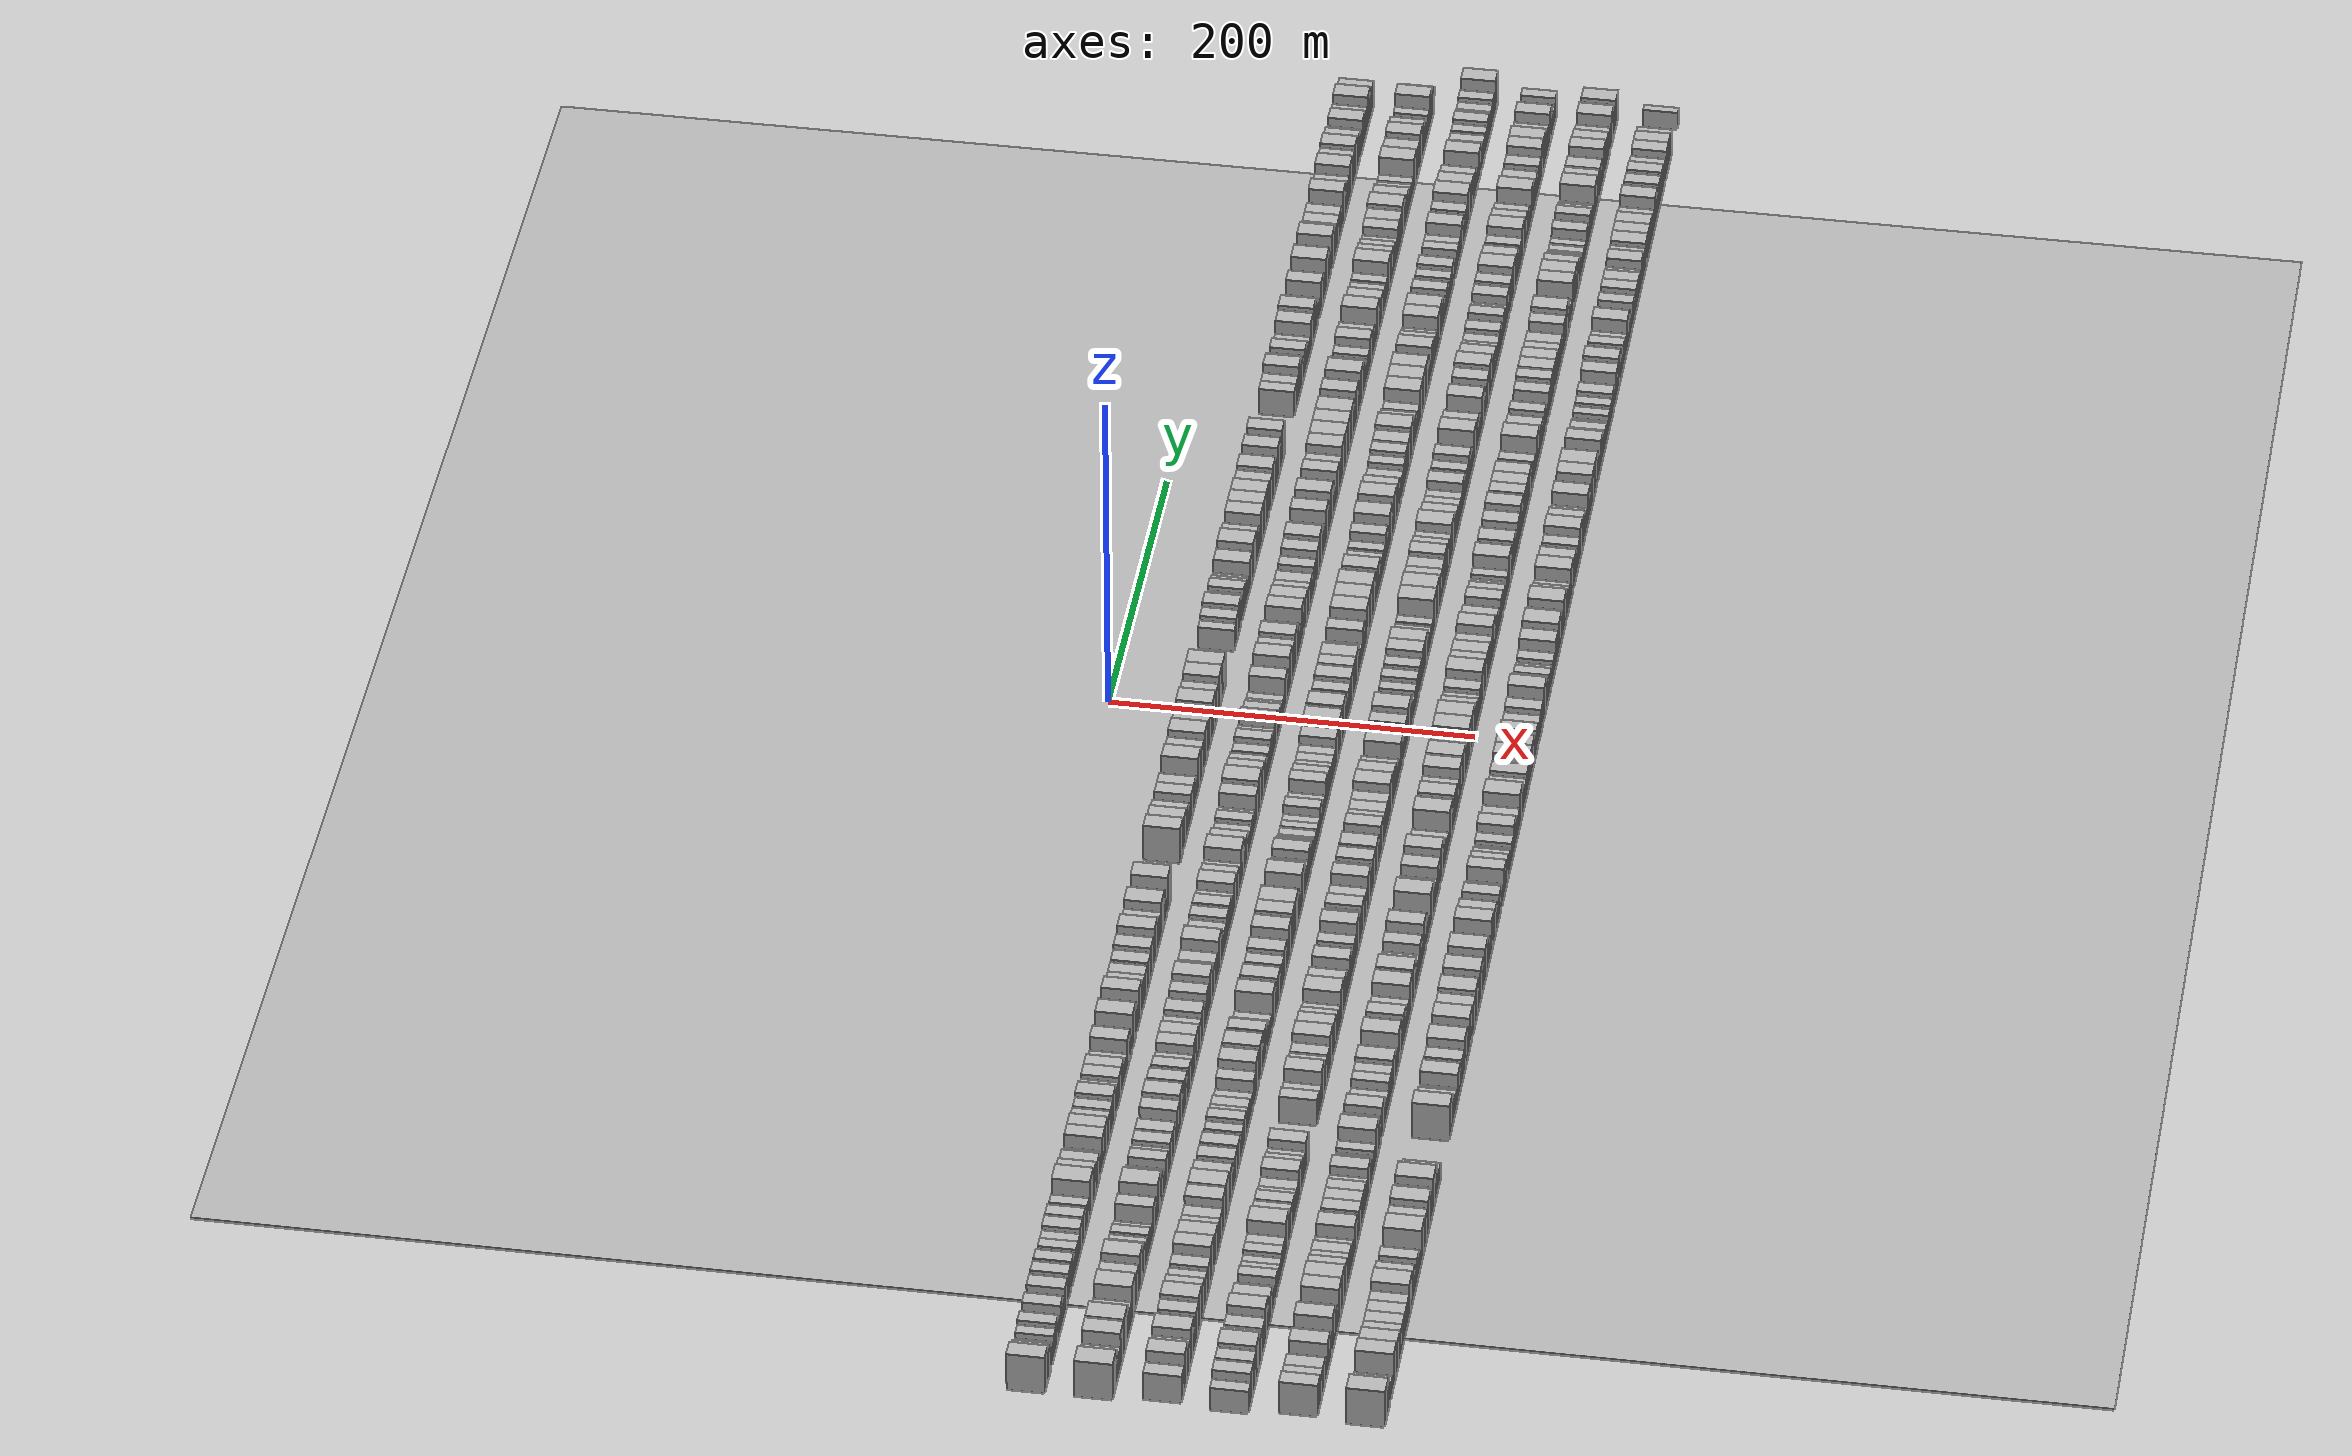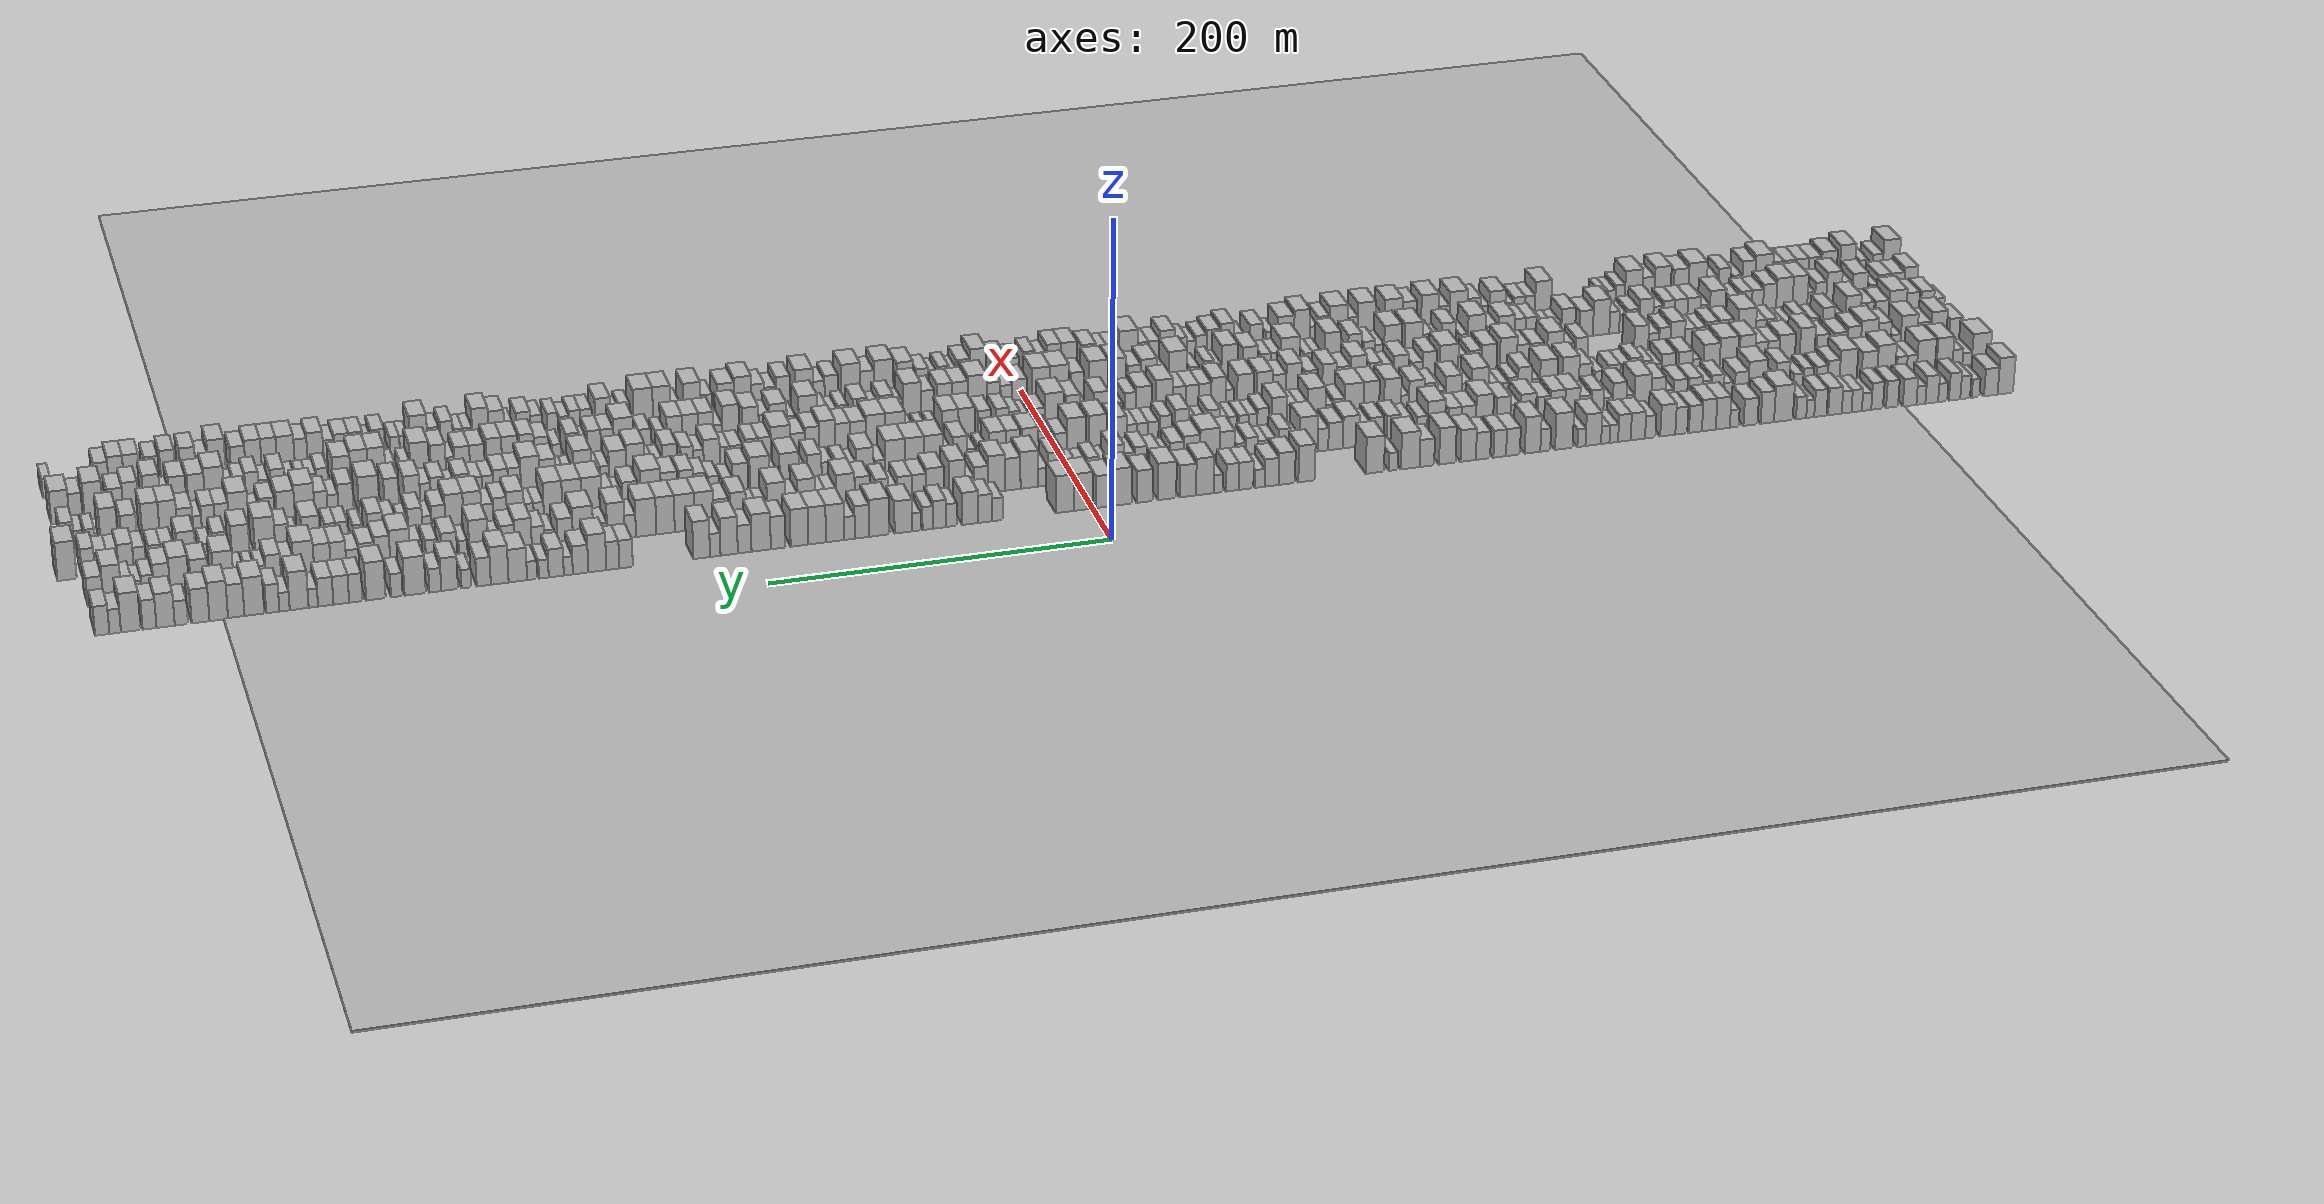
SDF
<?xml version="1.0" encoding="utf-8"?>

<sdf version="1.6">

   <world name="default">

      <gui fullscreen="0">

         <camera name="user_camera">

            <pose>-15 0 4.57585 0 0 0</pose>

            <view_controller>orbit</view_controller>

         </camera>

      </gui>

      <scene>

         <sky>

           <clouds>

             <speed>12</speed>

           </clouds>

         </sky>

         <ambient>0.4 0.4 0.4 1</ambient>

         <background>0.7 0.7 0.7 1</background>

         <shadows>1</shadows>

      </scene>

      <gravity>0 0 -9.8066</gravity>

      <magnetic_field>6e-06 2.3e-05 -4.2e-05</magnetic_field>

      <physics default="0" name="default_physics" type="ode">

         <ode>

            <solver>

               <type>quick</type>

               <iters>10</iters>

               <sor>1.0</sor>

               <use_dynamic_moi_rescaling>0</use_dynamic_moi_rescaling>

            </solver>

            <constraints>

               <cfm>0</cfm>

               <erp>0.2</erp>

               <contact_max_correcting_vel>100</contact_max_correcting_vel>

               <contact_surface_layer>0.001</contact_surface_layer>

            </constraints>

         </ode>

         <max_step_size>0.004</max_step_size>

         <real_time_factor>1</real_time_factor>

         <real_time_update_rate>250</real_time_update_rate>

      </physics>

      <light name="sun" type="directional">

         <cast_shadows>1</cast_shadows>

         <pose>0 0 10 0 0 0</pose>

         <diffuse>0.8 0.8 0.8 1</diffuse>

         <specular>0.2 0.2 0.2 1</specular>

         <attenuation>

            <range>1000</range>

            <constant>0.9</constant>

            <linear>0.01</linear>

            <quadratic>0.001</quadratic>

         </attenuation>

         <direction>-0.5 0.1 -0.9</direction>

      </light>

      <include>

         <name>ground_plane_1</name>

         <uri>model://HANNAS_ground_plane</uri>

         <pose>0 0 0  0 0 0</pose>

      </include>

      <include>

         <name>ground_plane_2</name>

         <uri>model://HANNAS_ground_plane</uri>

         <pose>100 0 0  0 0 0</pose>

      </include>

      <model name="building_1">

         <static>1</static>

         <pose frame="">50.0000 -565.0353 0 0.000000 0.000000 0.000000</pose>

         <link name="link">

            <pose frame="">0 0 12.00 0 0 0</pose>

            <collision name="collision">

               <geometry>

                  <box>

                     <size>20.0000 9.9295 24.0000</size>

                  </box>

               </geometry>

               <max_contacts>10</max_contacts>

               <surface>

                  <contact>

                     <ode/>

                  </contact>

                  <bounce/>

                  <friction>

                     <torsional>

                        <ode/>

                     </torsional>

                     <ode/>

                  </friction>

               </surface>

            </collision>

            <visual name="visual">

               <cast_shadows>0</cast_shadows>

               <geometry>

                  <box>

                     <size>20.0000 9.9295 24.0000</size>

                  </box>

               </geometry>

               <material>

                  <script>

                     <uri>model://HANNAS_wall/materials/scripts</uri>

                     <uri>model://HANNAS_wall/materials/textures</uri>

                     <name>vrc/HANNAS_wall</name>

                  </script>

               </material>

            </visual>

            <self_collide>0</self_collide>

            <enable_wind>0</enable_wind>

            <kinematic>0</kinematic>

         </link>

      </model>

      <model name="building_2">

         <static>1</static>

         <pose frame="">50.0000 -555.6900 0 0.000000 0.000000 0.000000</pose>

         <link name="link">

            <pose frame="">0 0 9.00 0 0 0</pose>

            <collision name="collision">

               <geometry>

                  <box>

                     <size>20.0000 8.7611 18.0000</size>

                  </box>

               </geometry>

               <max_contacts>10</max_contacts>

               <surface>

                  <contact>

                     <ode/>

                  </contact>

                  <bounce/>

                  <friction>

                     <torsional>

                        <ode/>

                     </torsional>

                     <ode/>

                  </friction>

               </surface>

            </collision>

            <visual name="visual">

               <cast_shadows>0</cast_shadows>

               <geometry>

                  <box>

                     <size>20.0000 8.7611 18.0000</size>

                  </box>

               </geometry>

               <material>

                  <script>

                     <uri>model://HANNAS_wall/materials/scripts</uri>

                     <uri>model://HANNAS_wall/materials/textures</uri>

                     <name>vrc/HANNAS_wall</name>

                  </script>

               </material>

            </visual>

            <self_collide>0</self_collide>

            <enable_wind>0</enable_wind>

            <kinematic>0</kinematic>

         </link>

      </model>

      <model name="building_3">

         <static>1</static>

         <pose frame="">50.0000 -545.8065 0 0.000000 0.000000 0.000000</pose>

         <link name="link">

            <pose frame="">0 0 6.00 0 0 0</pose>

            <collision name="collision">

               <geometry>

                  <box>

                     <size>20.0000 5.0057 12.0000</size>

                  </box>

               </geometry>

               <max_contacts>10</max_contacts>

               <surface>

                  <contact>

                     <ode/>

                  </contact>

                  <bounce/>

                  <friction>

                     <torsional>

                        <ode/>

                     </torsional>

                     <ode/>

                  </friction>

               </surface>

            </collision>

            <visual name="visual">

               <cast_shadows>0</cast_shadows>

               <geometry>

                  <box>

                     <size>20.0000 5.0057 12.0000</size>

                  </box>

               </geometry>

               <material>

                  <script>

                     <uri>model://HANNAS_wall/materials/scripts</uri>

                     <uri>model://HANNAS_wall/materials/textures</uri>

                     <name>vrc/HANNAS_wall</name>

                  </script>

               </material>

            </visual>

            <self_collide>0</self_collide>

            <enable_wind>0</enable_wind>

            <kinematic>0</kinematic>

         </link>

      </model>

      <model name="building_4">

         <static>1</static>

         <pose frame="">50.0000 -539.1809 0 0.000000 0.000000 0.000000</pose>

         <link name="link">

            <pose frame="">0 0 7.50 0 0 0</pose>

            <collision name="collision">

               <geometry>

                  <box>

                     <size>20.0000 6.2455 15.0000</size>

                  </box>

               </geometry>

               <max_contacts>10</max_contacts>

               <surface>

                  <contact>

                     <ode/>

                  </contact>

                  <bounce/>

                  <friction>

                     <torsional>

                        <ode/>

                     </torsional>

                     <ode/>

                  </friction>

               </surface>

            </collision>

            <visual name="visual">

               <cast_shadows>0</cast_shadows>

               <geometry>

                  <box>

                     <size>20.0000 6.2455 15.0000</size>

                  </box>

               </geometry>

               <material>

                  <script>

                     <uri>model://HANNAS_wall/materials/scripts</uri>

                     <uri>model://HANNAS_wall/materials/textures</uri>

                     <name>vrc/HANNAS_wall</name>

                  </script>

               </material>

            </visual>

            <self_collide>0</self_collide>

            <enable_wind>0</enable_wind>

            <kinematic>0</kinematic>

         </link>

      </model>

      <model name="building_5">

         <static>1</static>

         <pose frame="">50.0000 -532.3850 0 0.000000 0.000000 0.000000</pose>

         <link name="link">

            <pose frame="">0 0 9.00 0 0 0</pose>

            <collision name="collision">

               <geometry>

                  <box>

                     <size>20.0000 7.3461 18.0000</size>

                  </box>

               </geometry>

               <max_contacts>10</max_contacts>

               <surface>

                  <contact>

                     <ode/>

                  </contact>

                  <bounce/>

                  <friction>

                     <torsional>

                        <ode/>

                     </torsional>

                     <ode/>

                  </friction>

               </surface>

            </collision>

            <visual name="visual">

               <cast_shadows>0</cast_shadows>

               <geometry>

                  <box>

                     <size>20.0000 7.3461 18.0000</size>

                  </box>

               </geometry>

               <material>

                  <script>

                     <uri>model://HANNAS_wall/materials/scripts</uri>

                     <uri>model://HANNAS_wall/materials/textures</uri>

                     <name>vrc/HANNAS_wall</name>

                  </script>

               </material>

            </visual>

            <self_collide>0</self_collide>

            <enable_wind>0</enable_wind>

            <kinematic>0</kinematic>

         </link>

      </model>

      <model name="building_6">

         <static>1</static>

         <pose frame="">50.0000 -524.7717 0 0.000000 0.000000 0.000000</pose>

         <link name="link">

            <pose frame="">0 0 6.00 0 0 0</pose>

            <collision name="collision">

               <geometry>

                  <box>

                     <size>20.0000 5.8805 12.0000</size>

                  </box>

               </geometry>

               <max_contacts>10</max_contacts>

               <surface>

                  <contact>

                     <ode/>

                  </contact>

                  <bounce/>

                  <friction>

                     <torsional>

                        <ode/>

                     </torsional>

                     <ode/>

                  </friction>

               </surface>

            </collision>

            <visual name="visual">

               <cast_shadows>0</cast_shadows>

               <geometry>

                  <box>

                     <size>20.0000 5.8805 12.0000</size>

                  </box>

               </geometry>

               <material>

                  <script>

                     <uri>model://HANNAS_wall/materials/scripts</uri>

                     <uri>model://HANNAS_wall/materials/textures</uri>

                     <name>vrc/HANNAS_wall</name>

                  </script>

               </material>

            </visual>

            <self_collide>0</self_collide>

            <enable_wind>0</enable_wind>

            <kinematic>0</kinematic>

         </link>

      </model>

      <model name="building_7">

         <static>1</static>

         <pose frame="">50.0000 -517.7646 0 0.000000 0.000000 0.000000</pose>

         <link name="link">

            <pose frame="">0 0 9.00 0 0 0</pose>

            <collision name="collision">

               <geometry>

                  <box>

                     <size>20.0000 8.1337 18.0000</size>

                  </box>

               </geometry>

               <max_contacts>10</max_contacts>

               <surface>

                  <contact>

                     <ode/>

                  </contact>

                  <bounce/>

                  <friction>

                     <torsional>

                        <ode/>

                     </torsional>

                     <ode/>

                  </friction>

               </surface>

            </collision>

            <visual name="visual">

               <cast_shadows>0</cast_shadows>

               <geometry>

                  <box>

                     <size>20.0000 8.1337 18.0000</size>

                  </box>

               </geometry>

               <material>

                  <script>

                     <uri>model://HANNAS_wall/materials/scripts</uri>

                     <uri>model://HANNAS_wall/materials/textures</uri>

                     <name>vrc/HANNAS_wall</name>

                  </script>

               </material>

            </visual>

            <self_collide>0</self_collide>

            <enable_wind>0</enable_wind>

            <kinematic>0</kinematic>

         </link>

      </model>

      <model name="building_8">

         <static>1</static>

         <pose frame="">50.0000 -510.8210 0 0.000000 0.000000 0.000000</pose>

         <link name="link">

            <pose frame="">0 0 6.00 0 0 0</pose>

            <collision name="collision">

               <geometry>

                  <box>

                     <size>20.0000 5.7534 12.0000</size>

                  </box>

               </geometry>

               <max_contacts>10</max_contacts>

               <surface>

                  <contact>

                     <ode/>

                  </contact>

                  <bounce/>

                  <friction>

                     <torsional>

                        <ode/>

                     </torsional>

                     <ode/>

                  </friction>

               </surface>

            </collision>

            <visual name="visual">

               <cast_shadows>0</cast_shadows>

               <geometry>

                  <box>

                     <size>20.0000 5.7534 12.0000</size>

                  </box>

               </geometry>

               <material>

                  <script>

                     <uri>model://HANNAS_wall/materials/scripts</uri>

                     <uri>model://HANNAS_wall/materials/textures</uri>

                     <name>vrc/HANNAS_wall</name>

                  </script>

               </material>

            </visual>

            <self_collide>0</self_collide>

            <enable_wind>0</enable_wind>

            <kinematic>0</kinematic>

         </link>

      </model>

      <model name="building_9">

         <static>1</static>

         <pose frame="">50.0000 -503.5562 0 0.000000 0.000000 0.000000</pose>

         <link name="link">

            <pose frame="">0 0 9.00 0 0 0</pose>

            <collision name="collision">

               <geometry>

                  <box>

                     <size>20.0000 8.7762 18.0000</size>

                  </box>

               </geometry>

               <max_contacts>10</max_contacts>

               <surface>

                  <contact>

                     <ode/>

                  </contact>

                  <bounce/>

                  <friction>

                     <torsional>

                        <ode/>

                     </torsional>

                     <ode/>

                  </friction>

               </surface>

            </collision>

            <visual name="visual">

               <cast_shadows>0</cast_shadows>

               <geometry>

                  <box>

                     <size>20.0000 8.7762 18.0000</size>

                  </box>

               </geometry>

               <material>

                  <script>

                     <uri>model://HANNAS_wall/materials/scripts</uri>

                     <uri>model://HANNAS_wall/materials/textures</uri>

                     <name>vrc/HANNAS_wall</name>

                  </script>

               </material>

            </visual>

            <self_collide>0</self_collide>

            <enable_wind>0</enable_wind>

            <kinematic>0</kinematic>

         </link>

      </model>

      <model name="building_10">

         <static>1</static>

         <pose frame="">50.0000 -492.3334 0 0.000000 0.000000 0.000000</pose>

         <link name="link">

            <pose frame="">0 0 9.00 0 0 0</pose>

            <collision name="collision">

               <geometry>

                  <box>

                     <size>20.0000 7.6694 18.0000</size>

                  </box>

               </geometry>

               <max_contacts>10</max_contacts>

               <surface>

                  <contact>

                     <ode/>

                  </contact>

                  <bounce/>

                  <friction>

                     <torsional>

                        <ode/>

                     </torsional>

                     <ode/>

                  </friction>

               </surface>

            </collision>

            <visual name="visual">

               <cast_shadows>0</cast_shadows>

               <geometry>

                  <box>

                     <size>20.0000 7.6694 18.0000</size>

                  </box>

               </geometry>

               <material>

                  <script>

                     <uri>model://HANNAS_wall/materials/scripts</uri>

                     <uri>model://HANNAS_wall/materials/textures</uri>

                     <name>vrc/HANNAS_wall</name>

                  </script>

               </material>

            </visual>

            <self_collide>0</self_collide>

            <enable_wind>0</enable_wind>

            <kinematic>0</kinematic>

         </link>

      </model>

      <model name="building_11">

         <static>1</static>

         <pose frame="">50.0000 -482.7700 0 0.000000 0.000000 0.000000</pose>

         <link name="link">

            <pose frame="">0 0 9.00 0 0 0</pose>

            <collision name="collision">

               <geometry>

                  <box>

                     <size>20.0000 7.4574 18.0000</size>

                  </box>

               </geometry>

               <max_contacts>10</max_contacts>

               <surface>

                  <contact>

                     <ode/>

                  </contact>

                  <bounce/>

                  <friction>

                     <torsional>

                        <ode/>

                     </torsional>

                     <ode/>

                  </friction>

               </surface>

            </collision>

            <visual name="visual">

               <cast_shadows>0</cast_shadows>

               <geometry>

                  <box>

                     <size>20.0000 7.4574 18.0000</size>

                  </box>

               </geometry>

               <material>

                  <script>

                     <uri>model://HANNAS_wall/materials/scripts</uri>

                     <uri>model://HANNAS_wall/materials/textures</uri>

                     <name>vrc/HANNAS_wall</name>

                  </script>

               </material>

            </visual>

            <self_collide>0</self_collide>

            <enable_wind>0</enable_wind>

            <kinematic>0</kinematic>

         </link>

      </model>

      <model name="building_12">

         <static>1</static>

         <pose frame="">50.0000 -476.0583 0 0.000000 0.000000 0.000000</pose>

         <link name="link">

            <pose frame="">0 0 6.00 0 0 0</pose>

            <collision name="collision">

               <geometry>

                  <box>

                     <size>20.0000 5.9659 12.0000</size>

                  </box>

               </geometry>

               <max_contacts>10</max_contacts>

               <surface>

                  <contact>

                     <ode/>

                  </contact>

                  <bounce/>

                  <friction>

                     <torsional>

                        <ode/>

                     </torsional>

                     <ode/>

                  </friction>

               </surface>

            </collision>

            <visual name="visual">

               <cast_shadows>0</cast_shadows>

               <geometry>

                  <box>

                     <size>20.0000 5.9659 12.0000</size>

                  </box>

               </geometry>

               <material>

                  <script>

                     <uri>model://HANNAS_wall/materials/scripts</uri>

                     <uri>model://HANNAS_wall/materials/textures</uri>

                     <name>vrc/HANNAS_wall</name>

                  </script>

               </material>

            </visual>

            <self_collide>0</self_collide>

            <enable_wind>0</enable_wind>

            <kinematic>0</kinematic>

         </link>

      </model>

      <model name="building_13">

         <static>1</static>

         <pose frame="">50.0000 -469.7635 0 0.000000 0.000000 0.000000</pose>

         <link name="link">

            <pose frame="">0 0 7.50 0 0 0</pose>

            <collision name="collision">

               <geometry>

                  <box>

                     <size>20.0000 6.6238 15.0000</size>

                  </box>

               </geometry>

               <max_contacts>10</max_contacts>

               <surface>

                  <contact>

                     <ode/>

                  </contact>

                  <bounce/>

                  <friction>

                     <torsional>

                        <ode/>

                     </torsional>

                     <ode/>

                  </friction>

               </surface>

            </collision>

            <visual name="visual">

               <cast_shadows>0</cast_shadows>

               <geometry>

                  <box>

                     <size>20.0000 6.6238 15.0000</size>

                  </box>

               </geometry>

               <material>

                  <script>

                     <uri>model://HANNAS_wall/materials/scripts</uri>

                     <uri>model://HANNAS_wall/materials/textures</uri>

                     <name>vrc/HANNAS_wall</name>

                  </script>

               </material>

            </visual>

            <self_collide>0</self_collide>

            <enable_wind>0</enable_wind>

            <kinematic>0</kinematic>

         </link>

      </model>

      <model name="building_14">

         <static>1</static>

         <pose frame="">50.0000 -463.3640 0 0.000000 0.000000 0.000000</pose>

         <link name="link">

            <pose frame="">0 0 7.50 0 0 0</pose>

            <collision name="collision">

               <geometry>

                  <box>

                     <size>20.0000 6.1751 15.0000</size>

                  </box>

               </geometry>

               <max_contacts>10</max_contacts>

               <surface>

                  <contact>

                     <ode/>

                  </contact>

                  <bounce/>

                  <friction>

                     <torsional>

                        <ode/>

                     </torsional>

                     <ode/>

                  </friction>

               </surface>

            </collision>

            <visual name="visual">

               <cast_shadows>0</cast_shadows>

               <geometry>

                  <box>

                     <size>20.0000 6.1751 15.0000</size>

                  </box>

               </geometry>

               <material>

                  <script>

                     <uri>model://HANNAS_wall/materials/scripts</uri>

                     <uri>model://HANNAS_wall/materials/textures</uri>

                     <name>vrc/HANNAS_wall</name>

                  </script>

               </material>

            </visual>

            <self_collide>0</self_collide>

            <enable_wind>0</enable_wind>

            <kinematic>0</kinematic>

         </link>

      </model>

      <model name="building_15">

         <static>1</static>

         <pose frame="">50.0000 -455.9487 0 0.000000 0.000000 0.000000</pose>

         <link name="link">

            <pose frame="">0 0 9.00 0 0 0</pose>

            <collision name="collision">

               <geometry>

                  <box>

                     <size>20.0000 8.6555 18.0000</size>

                  </box>

               </geometry>

               <max_contacts>10</max_contacts>

               <surface>

                  <contact>

                     <ode/>

                  </contact>

                  <bounce/>

                  <friction>

                     <torsional>

                        <ode/>

                     </torsional>

                     <ode/>

                  </friction>

               </surface>

            </collision>

            <visual name="visual">

               <cast_shadows>0</cast_shadows>

               <geometry>

                  <box>

                     <size>20.0000 8.6555 18.0000</size>

                  </box>

               </geometry>

               <material>

                  <script>

                     <uri>model://HANNAS_wall/materials/scripts</uri>

                     <uri>model://HANNAS_wall/materials/textures</uri>

                     <name>vrc/HANNAS_wall</name>

                  </script>

               </material>

            </visual>

            <self_collide>0</self_collide>

            <enable_wind>0</enable_wind>

            <kinematic>0</kinematic>

         </link>

      </model>

      <model name="building_16">

         <static>1</static>

         <pose frame="">50.0000 -446.7288 0 0.000000 0.000000 0.000000</pose>

         <link name="link">

            <pose frame="">0 0 9.00 0 0 0</pose>

            <collision name="collision">

               <geometry>

                  <box>

                     <size>20.0000 7.7843 18.0000</size>

                  </box>

               </geometry>

               <max_contacts>10</max_contacts>

               <surface>

                  <contact>

                     <ode/>

                  </contact>

                  <bounce/>

                  <friction>

                     <torsional>

                        <ode/>

                     </torsional>

                     <ode/>

                  </friction>

               </surface>

            </collision>

            <visual name="visual">

               <cast_shadows>0</cast_shadows>

               <geometry>

                  <box>

                     <size>20.0000 7.7843 18.0000</size>

                  </box>

               </geometry>

               <material>

                  <script>

                     <uri>model://HANNAS_wall/materials/scripts</uri>

                     <uri>model://HANNAS_wall/materials/textures</uri>

                     <name>vrc/HANNAS_wall</name>

                  </script>

               </material>

            </visual>

            <self_collide>0</self_collide>

            <enable_wind>0</enable_wind>

            <kinematic>0</kinematic>

         </link>

      </model>

      <model name="building_17">

         <static>1</static>

         <pose frame="">50.0000 -440.2830 0 0.000000 0.000000 0.000000</pose>

         <link name="link">

            <pose frame="">0 0 6.00 0 0 0</pose>

            <collision name="collision">

               <geometry>

                  <box>

                     <size>20.0000 5.1072 12.0000</size>

                  </box>

               </geometry>

               <max_contacts>10</max_contacts>

               <surface>

                  <contact>

                     <ode/>

                  </contact>

                  <bounce/>

                  <friction>

                     <torsional>

                        <ode/>

                     </torsional>

                     <ode/>

                  </friction>

               </surface>

            </collision>

            <visual name="visual">

               <cast_shadows>0</cast_shadows>

               <geometry>

                  <box>

                     <size>20.0000 5.1072 12.0000</size>

                  </box>

               </geometry>

               <material>

                  <script>

                     <uri>model://HANNAS_wall/materials/scripts</uri>

                     <uri>model://HANNAS_wall/materials/textures</uri>

                     <name>vrc/HANNAS_wall</name>

                  </script>

               </material>

            </visual>

            <self_collide>0</self_collide>

            <enable_wind>0</enable_wind>

            <kinematic>0</kinematic>

         </link>

      </model>

      <model name="building_18">

         <static>1</static>

         <pose frame="">50.0000 -434.4767 0 0.000000 0.000000 0.000000</pose>

         <link name="link">

            <pose frame="">0 0 7.50 0 0 0</pose>

            <collision name="collision">

               <geometry>

                  <box>

                     <size>20.0000 6.5054 15.0000</size>

                  </box>

               </geometry>

               <max_contacts>10</max_contacts>

               <surface>

                  <contact>

                     <ode/>

                  </contact>

                  <bounce/>

                  <friction>

                     <torsional>

                        <ode/>

                     </torsional>

                     <ode/>

                  </friction>

               </surface>

            </collision>

            <visual name="visual">

               <cast_shadows>0</cast_shadows>

               <geometry>

                  <box>

                     <size>20.0000 6.5054 15.0000</size>

                  </box>

               </geometry>

               <material>

                  <script>

                     <uri>model://HANNAS_wall/materials/scripts</uri>

                     <uri>model://HANNAS_wall/materials/textures</uri>

                     <name>vrc/HANNAS_wall</name>

                  </script>

               </material>

            </visual>

            <self_collide>0</self_collide>

            <enable_wind>0</enable_wind>

            <kinematic>0</kinematic>

         </link>

      </model>

      <model name="building_19">

         <static>1</static>

         <pose frame="">50.0000 -423.2817 0 0.000000 0.000000 0.000000</pose>

         <link name="link">

            <pose frame="">0 0 12.00 0 0 0</pose>

            <collision name="collision">

               <geometry>

                  <box>

                     <size>20.0000 11.8847 24.0000</size>

                  </box>

               </geometry>

               <max_contacts>10</max_contacts>

               <surface>

                  <contact>

                     <ode/>

                  </contact>

                  <bounce/>

                  <friction>

                     <torsional>

                        <ode/>

                     </torsional>

                     <ode/>

                  </friction>

               </surface>

            </collision>

            <visual name="visual">

               <cast_shadows>0</cast_shadows>

               <geometry>

                  <box>

                     <size>20.0000 11.8847 24.0000</size>

                  </box>

               </geometry>

               <material>

                  <script>

                     <uri>model://HANNAS_wall/materials/scripts</uri>

                     <uri>model://HANNAS_wall/materials/textures</uri>

                     <name>vrc/HANNAS_wall</name>

                  </script>

               </material>

            </visual>

            <self_collide>0</self_collide>

            <enable_wind>0</enable_wind>

            <kinematic>0</kinematic>

         </link>

      </model>

      <model name="building_20">

         <static>1</static>

         <pose frame="">50.0000 -413.1167 0 0.000000 0.000000 0.000000</pose>

         <link name="link">

            <pose frame="">0 0 10.50 0 0 0</pose>

            <collision name="collision">

               <geometry>

                  <box>

                     <size>20.0000 8.4452 21.0000</size>

                  </box>

               </geometry>

               <max_contacts>10</max_contacts>

               <surface>

                  <contact>

                     <ode/>

                  </contact>

                  <bounce/>

                  <friction>

                     <torsional>

                        <ode/>

                     </torsional>

                     <ode/>

                  </friction>

               </surface>

            </collision>

            <visual name="visual">

               <cast_shadows>0</cast_shadows>

               <geometry>

                  <box>

                     <size>20.0000 8.4452 21.0000</size>

                  </box>

               </geometry>

               <material>

                  <script>

                     <uri>model://HANNAS_wall/materials/scripts</uri>

                     <uri>model://HANNAS_wall/materials/textures</uri>

                     <name>vrc/HANNAS_wall</name>

                  </script>

               </material>

            </visual>

            <self_collide>0</self_collide>

            <enable_wind>0</enable_wind>

            <kinematic>0</kinematic>

         </link>

      </model>

      <model name="building_21">

         <static>1</static>

         <pose frame="">50.0000 -402.4830 0 0.000000 0.000000 0.000000</pose>

         <link name="link">

            <pose frame="">0 0 9.00 0 0 0</pose>

            <collision name="collision">

               <geometry>

                  <box>

                     <size>20.0000 8.8222 18.0000</size>

                  </box>

               </geometry>

               <max_contacts>10</max_contacts>

               <surface>

                  <contact>

                     <ode/>

                  </contact>

                  <bounce/>

                  <friction>

                     <torsional>

                        <ode/>

                     </torsional>

                     <ode/>

                  </friction>

               </surface>

            </collision>

            <visual name="visual">

               <cast_shadows>0</cast_shadows>

               <geometry>

                  <box>

                     <size>20.0000 8.8222 18.0000</size>

                  </box>

               </geometry>

               <material>

                  <script>

                     <uri>model://HANNAS_wall/materials/scripts</uri>

                     <uri>model://HANNAS_wall/materials/textures</uri>

                     <name>vrc/HANNAS_wall</name>

                  </script>

               </material>

            </visual>

            <self_collide>0</self_collide>

            <enable_wind>0</enable_wind>

            <kinematic>0</kinematic>

         </link>

      </model>

      <model name="building_22">

         <static>1</static>

         <pose frame="">50.0000 -392.2770 0 0.000000 0.000000 0.000000</pose>

         <link name="link">

            <pose frame="">0 0 6.00 0 0 0</pose>

            <collision name="collision">

               <geometry>

                  <box>

                     <size>20.0000 5.5899 12.0000</size>

                  </box>

               </geometry>

               <max_contacts>10</max_contacts>

               <surface>

                  <contact>

                     <ode/>

                  </contact>

                  <bounce/>

                  <friction>

                     <torsional>

                        <ode/>

                     </torsional>

                     <ode/>

                  </friction>

               </surface>

            </collision>

            <visual name="visual">

               <cast_shadows>0</cast_shadows>

               <geometry>

                  <box>

                     <size>20.0000 5.5899 12.0000</size>

                  </box>

               </geometry>

               <material>

                  <script>

                     <uri>model://HANNAS_wall/materials/scripts</uri>

                     <uri>model://HANNAS_wall/materials/textures</uri>

                     <name>vrc/HANNAS_wall</name>

                  </script>

               </material>

            </visual>

            <self_collide>0</self_collide>

            <enable_wind>0</enable_wind>

            <kinematic>0</kinematic>

         </link>

      </model>

      <model name="building_23">

         <static>1</static>

         <pose frame="">50.0000 -385.0762 0 0.000000 0.000000 0.000000</pose>

         <link name="link">

            <pose frame="">0 0 10.50 0 0 0</pose>

            <collision name="collision">

               <geometry>

                  <box>

                     <size>20.0000 8.8117 21.0000</size>

                  </box>

               </geometry>

               <max_contacts>10</max_contacts>

               <surface>

                  <contact>

                     <ode/>

                  </contact>

                  <bounce/>

                  <friction>

                     <torsional>

                        <ode/>

                     </torsional>

                     <ode/>

                  </friction>

               </surface>

            </collision>

            <visual name="visual">

               <cast_shadows>0</cast_shadows>

               <geometry>

                  <box>

                     <size>20.0000 8.8117 21.0000</size>

                  </box>

               </geometry>

               <material>

                  <script>

                     <uri>model://HANNAS_wall/materials/scripts</uri>

                     <uri>model://HANNAS_wall/materials/textures</uri>

                     <name>vrc/HANNAS_wall</name>

                  </script>

               </material>

            </visual>

            <self_collide>0</self_collide>

            <enable_wind>0</enable_wind>

            <kinematic>0</kinematic>

         </link>

      </model>

      <model name="building_24">

         <static>1</static>

         <pose frame="">50.0000 -376.3006 0 0.000000 0.000000 0.000000</pose>

         <link name="link">

            <pose frame="">0 0 10.50 0 0 0</pose>

            <collision name="collision">

               <geometry>

                  <box>

                     <size>20.0000 8.7395 21.0000</size>

                  </box>

               </geometry>

               <max_contacts>10</max_contacts>

               <surface>

                  <contact>

                     <ode/>

                  </contact>

                  <bounce/>

                  <friction>

                     <torsional>

                        <ode/>

                     </torsional>

                     <ode/>

                  </friction>

               </surface>

            </collision>

            <visual name="visual">

               <cast_shadows>0</cast_shadows>

               <geometry>

                  <box>

                     <size>20.0000 8.7395 21.0000</size>

                  </box>

               </geometry>

               <material>

                  <script>

                     <uri>model://HANNAS_wall/materials/scripts</uri>

                     <uri>model://HANNAS_wall/materials/textures</uri>

                     <name>vrc/HANNAS_wall</name>

                  </script>

               </material>

            </visual>

            <self_collide>0</self_collide>

            <enable_wind>0</enable_wind>

            <kinematic>0</kinematic>

         </link>

      </model>

      <model name="building_25">

         <static>1</static>

         <pose frame="">50.0000 -367.8274 0 0.000000 0.000000 0.000000</pose>

         <link name="link">

            <pose frame="">0 0 9.00 0 0 0</pose>

            <collision name="collision">

               <geometry>

                  <box>

                     <size>20.0000 8.2068 18.0000</size>

                  </box>

               </geometry>

               <max_contacts>10</max_contacts>

               <surface>

                  <contact>

                     <ode/>

                  </contact>

                  <bounce/>

                  <friction>

                     <torsional>

                        <ode/>

                     </torsional>

                     <ode/>

                  </friction>

               </surface>

            </collision>

            <visual name="visual">

               <cast_shadows>0</cast_shadows>

               <geometry>

                  <box>

                     <size>20.0000 8.2068 18.0000</size>

                  </box>

               </geometry>

               <material>

                  <script>

                     <uri>model://HANNAS_wall/materials/scripts</uri>

                     <uri>model://HANNAS_wall/materials/textures</uri>

                     <name>vrc/HANNAS_wall</name>

                  </script>

               </material>

            </visual>

            <self_collide>0</self_collide>

            <enable_wind>0</enable_wind>

            <kinematic>0</kinematic>

         </link>

      </model>

      <model name="building_26">

         <static>1</static>

         <pose frame="">50.0000 -358.9862 0 0.000000 0.000000 0.000000</pose>

         <link name="link">

            <pose frame="">0 0 9.00 0 0 0</pose>

            <collision name="collision">

               <geometry>

                  <box>

                     <size>20.0000 7.4757 18.0000</size>

                  </box>

               </geometry>

               <max_contacts>10</max_contacts>

               <surface>

                  <contact>

                     <ode/>

                  </contact>

                  <bounce/>

                  <friction>

                     <torsional>

                        <ode/>

                     </torsional>

                     <ode/>

                  </friction>

               </surface>

            </collision>

            <visual name="visual">

               <cast_shadows>0</cast_shadows>

               <geometry>

                  <box>

                     <size>20.0000 7.4757 18.0000</size>

                  </box>

               </geometry>

               <material>

                  <script>

                     <uri>model://HANNAS_wall/materials/scripts</uri>

                     <uri>model://HANNAS_wall/materials/textures</uri>

                     <name>vrc/HANNAS_wall</name>

                  </script>

               </material>

            </visual>

            <self_collide>0</self_collide>

            <enable_wind>0</enable_wind>

            <kinematic>0</kinematic>

         </link>

      </model>

      <model name="building_27">

         <static>1</static>

         <pose frame="">50.0000 -350.5286 0 0.000000 0.000000 0.000000</pose>

         <link name="link">

            <pose frame="">0 0 10.50 0 0 0</pose>

            <collision name="collision">

               <geometry>

                  <box>

                     <size>20.0000 9.4395 21.0000</size>

                  </box>

               </geometry>

               <max_contacts>10</max_contacts>

               <surface>

                  <contact>

                     <ode/>

                  </contact>

                  <bounce/>

                  <friction>

                     <torsional>

                        <ode/>

                     </torsional>

                     <ode/>

                  </friction>

               </surface>

            </collision>

            <visual name="visual">

               <cast_shadows>0</cast_shadows>

               <geometry>

                  <box>

                     <size>20.0000 9.4395 21.0000</size>

                  </box>

               </geometry>

               <material>

                  <script>

                     <uri>model://HANNAS_wall/materials/scripts</uri>

                     <uri>model://HANNAS_wall/materials/textures</uri>

                     <name>vrc/HANNAS_wall</name>

                  </script>

               </material>

            </visual>

            <self_collide>0</self_collide>

            <enable_wind>0</enable_wind>

            <kinematic>0</kinematic>

         </link>

      </model>

      <model name="building_28">

         <static>1</static>

         <pose frame="">50.0000 -339.5602 0 0.000000 0.000000 0.000000</pose>

         <link name="link">

            <pose frame="">0 0 7.50 0 0 0</pose>

            <collision name="collision">

               <geometry>

                  <box>

                     <size>20.0000 6.4973 15.0000</size>

                  </box>

               </geometry>

               <max_contacts>10</max_contacts>

               <surface>

                  <contact>

                     <ode/>

                  </contact>

                  <bounce/>

                  <friction>

                     <torsional>

                        <ode/>

                     </torsional>

                     <ode/>

                  </friction>

               </surface>

            </collision>

            <visual name="visual">

               <cast_shadows>0</cast_shadows>

               <geometry>

                  <box>

                     <size>20.0000 6.4973 15.0000</size>

                  </box>

               </geometry>

               <material>

                  <script>

                     <uri>model://HANNAS_wall/materials/scripts</uri>

                     <uri>model://HANNAS_wall/materials/textures</uri>

                     <name>vrc/HANNAS_wall</name>

                  </script>

               </material>

            </visual>

            <self_collide>0</self_collide>

            <enable_wind>0</enable_wind>

            <kinematic>0</kinematic>

         </link>

      </model>

      <model name="building_29">

         <static>1</static>

         <pose frame="">50.0000 -331.8136 0 0.000000 0.000000 0.000000</pose>

         <link name="link">

            <pose frame="">0 0 9.00 0 0 0</pose>

            <collision name="collision">

               <geometry>

                  <box>

                     <size>20.0000 8.9958 18.0000</size>

                  </box>

               </geometry>

               <max_contacts>10</max_contacts>

               <surface>

                  <contact>

                     <ode/>

                  </contact>

                  <bounce/>

                  <friction>

                     <torsional>

                        <ode/>

                     </torsional>

                     <ode/>

                  </friction>

               </surface>

            </collision>

            <visual name="visual">

               <cast_shadows>0</cast_shadows>

               <geometry>

                  <box>

                     <size>20.0000 8.9958 18.0000</size>

                  </box>

               </geometry>

               <material>

                  <script>

                     <uri>model://HANNAS_wall/materials/scripts</uri>

                     <uri>model://HANNAS_wall/materials/textures</uri>

                     <name>vrc/HANNAS_wall</name>

                  </script>

               </material>

            </visual>

            <self_collide>0</self_collide>

            <enable_wind>0</enable_wind>

            <kinematic>0</kinematic>

         </link>

      </model>

      <model name="building_30">

         <static>1</static>

         <pose frame="">50.0000 -323.3999 0 0.000000 0.000000 0.000000</pose>

         <link name="link">

            <pose frame="">0 0 9.00 0 0 0</pose>

            <collision name="collision">

               <geometry>

                  <box>

                     <size>20.0000 7.8316 18.0000</size>

                  </box>

               </geometry>

               <max_contacts>10</max_contacts>

               <surface>

                  <contact>

                     <ode/>

                  </contact>

                  <bounce/>

                  <friction>

                     <torsional>

                        <ode/>

                     </torsional>

                     <ode/>

                  </friction>

               </surface>

            </collision>

            <visual name="visual">

               <cast_shadows>0</cast_shadows>

               <geometry>

                  <box>

                     <size>20.0000 7.8316 18.0000</size>

                  </box>

               </geometry>

               <material>

                  <script>

                     <uri>model://HANNAS_wall/materials/scripts</uri>

                     <uri>model://HANNAS_wall/materials/textures</uri>

                     <name>vrc/HANNAS_wall</name>

                  </script>

               </material>

            </visual>

            <self_collide>0</self_collide>

            <enable_wind>0</enable_wind>

            <kinematic>0</kinematic>

         </link>

      </model>

      <model name="building_31">

         <static>1</static>

         <pose frame="">50.0000 -316.7963 0 0.000000 0.000000 0.000000</pose>

         <link name="link">

            <pose frame="">0 0 6.00 0 0 0</pose>

            <collision name="collision">

               <geometry>

                  <box>

                     <size>20.0000 5.3756 12.0000</size>

                  </box>

               </geometry>

               <max_contacts>10</max_contacts>

               <surface>

                  <contact>

                     <ode/>

                  </contact>

                  <bounce/>

                  <friction>

                     <torsional>

                        <ode/>

                     </torsional>

                     <ode/>

                  </friction>

               </surface>

            </collision>

            <visual name="visual">

               <cast_shadows>0</cast_shadows>

               <geometry>

                  <box>

                     <size>20.0000 5.3756 12.0000</size>

                  </box>

               </geometry>

               <material>

                  <script>

                     <uri>model://HANNAS_wall/materials/scripts</uri>

                     <uri>model://HANNAS_wall/materials/textures</uri>

                     <name>vrc/HANNAS_wall</name>

                  </script>

               </material>

            </visual>

            <self_collide>0</self_collide>

            <enable_wind>0</enable_wind>

            <kinematic>0</kinematic>

         </link>

      </model>

      <model name="building_32">

         <static>1</static>

         <pose frame="">50.0000 -311.5024 0 0.000000 0.000000 0.000000</pose>

         <link name="link">

            <pose frame="">0 0 6.00 0 0 0</pose>

            <collision name="collision">

               <geometry>

                  <box>

                     <size>20.0000 5.2123 12.0000</size>

                  </box>

               </geometry>

               <max_contacts>10</max_contacts>

               <surface>

                  <contact>

                     <ode/>

                  </contact>

                  <bounce/>

                  <friction>

                     <torsional>

                        <ode/>

                     </torsional>

                     <ode/>

                  </friction>

               </surface>

            </collision>

            <visual name="visual">

               <cast_shadows>0</cast_shadows>

               <geometry>

                  <box>

                     <size>20.0000 5.2123 12.0000</size>

                  </box>

               </geometry>

               <material>

                  <script>

                     <uri>model://HANNAS_wall/materials/scripts</uri>

                     <uri>model://HANNAS_wall/materials/textures</uri>

                     <name>vrc/HANNAS_wall</name>

                  </script>

               </material>

            </visual>

            <self_collide>0</self_collide>

            <enable_wind>0</enable_wind>

            <kinematic>0</kinematic>

         </link>

      </model>

      <model name="building_33">

         <static>1</static>

         <pose frame="">50.0000 -304.0378 0 0.000000 0.000000 0.000000</pose>

         <link name="link">

            <pose frame="">0 0 10.50 0 0 0</pose>

            <collision name="collision">

               <geometry>

                  <box>

                     <size>20.0000 9.7168 21.0000</size>

                  </box>

               </geometry>

               <max_contacts>10</max_contacts>

               <surface>

                  <contact>

                     <ode/>

                  </contact>

                  <bounce/>

                  <friction>

                     <torsional>

                        <ode/>

                     </torsional>

                     <ode/>

                  </friction>

               </surface>

            </collision>

            <visual name="visual">

               <cast_shadows>0</cast_shadows>

               <geometry>

                  <box>

                     <size>20.0000 9.7168 21.0000</size>

                  </box>

               </geometry>

               <material>

                  <script>

                     <uri>model://HANNAS_wall/materials/scripts</uri>

                     <uri>model://HANNAS_wall/materials/textures</uri>

                     <name>vrc/HANNAS_wall</name>

                  </script>

               </material>

            </visual>

            <self_collide>0</self_collide>

            <enable_wind>0</enable_wind>

            <kinematic>0</kinematic>

         </link>

      </model>

      <model name="building_34">

         <static>1</static>

         <pose frame="">50.0000 -296.6722 0 0.000000 0.000000 0.000000</pose>

         <link name="link">

            <pose frame="">0 0 6.00 0 0 0</pose>

            <collision name="collision">

               <geometry>

                  <box>

                     <size>20.0000 5.0144 12.0000</size>

                  </box>

               </geometry>

               <max_contacts>10</max_contacts>

               <surface>

                  <contact>

                     <ode/>

                  </contact>

                  <bounce/>

                  <friction>

                     <torsional>

                        <ode/>

                     </torsional>

                     <ode/>

                  </friction>

               </surface>

            </collision>

            <visual name="visual">

               <cast_shadows>0</cast_shadows>

               <geometry>

                  <box>

                     <size>20.0000 5.0144 12.0000</size>

                  </box>

               </geometry>

               <material>

                  <script>

                     <uri>model://HANNAS_wall/materials/scripts</uri>

                     <uri>model://HANNAS_wall/materials/textures</uri>

                     <name>vrc/HANNAS_wall</name>

                  </script>

               </material>

            </visual>

            <self_collide>0</self_collide>

            <enable_wind>0</enable_wind>

            <kinematic>0</kinematic>

         </link>

      </model>

      <model name="building_35">

         <static>1</static>

         <pose frame="">50.0000 -285.7222 0 0.000000 0.000000 0.000000</pose>

         <link name="link">

            <pose frame="">0 0 12.00 0 0 0</pose>

            <collision name="collision">

               <geometry>

                  <box>

                     <size>20.0000 10.8856 24.0000</size>

                  </box>

               </geometry>

               <max_contacts>10</max_contacts>

               <surface>

                  <contact>

                     <ode/>

                  </contact>

                  <bounce/>

                  <friction>

                     <torsional>

                        <ode/>

                     </torsional>

                     <ode/>

                  </friction>

               </surface>

            </collision>

            <visual name="visual">

               <cast_shadows>0</cast_shadows>

               <geometry>

                  <box>

                     <size>20.0000 10.8856 24.0000</size>

                  </box>

               </geometry>

               <material>

                  <script>

                     <uri>model://HANNAS_wall/materials/scripts</uri>

                     <uri>model://HANNAS_wall/materials/textures</uri>

                     <name>vrc/HANNAS_wall</name>

                  </script>

               </material>

            </visual>

            <self_collide>0</self_collide>

            <enable_wind>0</enable_wind>

            <kinematic>0</kinematic>

         </link>

      </model>

      <model name="building_36">

         <static>1</static>

         <pose frame="">50.0000 -274.2243 0 0.000000 0.000000 0.000000</pose>

         <link name="link">

            <pose frame="">0 0 7.50 0 0 0</pose>

            <collision name="collision">

               <geometry>

                  <box>

                     <size>20.0000 6.1102 15.0000</size>

                  </box>

               </geometry>

               <max_contacts>10</max_contacts>

               <surface>

                  <contact>

                     <ode/>

                  </contact>

                  <bounce/>

                  <friction>

                     <torsional>

                        <ode/>

                     </torsional>

                     <ode/>

                  </friction>

               </surface>

            </collision>

            <visual name="visual">

               <cast_shadows>0</cast_shadows>

               <geometry>

                  <box>

                     <size>20.0000 6.1102 15.0000</size>

                  </box>

               </geometry>

               <material>

                  <script>

                     <uri>model://HANNAS_wall/materials/scripts</uri>

                     <uri>model://HANNAS_wall/materials/textures</uri>

                     <name>vrc/HANNAS_wall</name>

                  </script>

               </material>

            </visual>

            <self_collide>0</self_collide>

            <enable_wind>0</enable_wind>

            <kinematic>0</kinematic>

         </link>

      </model>

      <model name="building_37">

         <static>1</static>

         <pose frame="">50.0000 -266.3594 0 0.000000 0.000000 0.000000</pose>

         <link name="link">

            <pose frame="">0 0 12.00 0 0 0</pose>

            <collision name="collision">

               <geometry>

                  <box>

                     <size>20.0000 9.6195 24.0000</size>

                  </box>

               </geometry>

               <max_contacts>10</max_contacts>

               <surface>

                  <contact>

                     <ode/>

                  </contact>

                  <bounce/>

                  <friction>

                     <torsional>

                        <ode/>

                     </torsional>

                     <ode/>

                  </friction>

               </surface>

            </collision>

            <visual name="visual">

               <cast_shadows>0</cast_shadows>

               <geometry>

                  <box>

                     <size>20.0000 9.6195 24.0000</size>

                  </box>

               </geometry>

               <material>

                  <script>

                     <uri>model://HANNAS_wall/materials/scripts</uri>

                     <uri>model://HANNAS_wall/materials/textures</uri>

                     <name>vrc/HANNAS_wall</name>

                  </script>

               </material>

            </visual>

            <self_collide>0</self_collide>

            <enable_wind>0</enable_wind>

            <kinematic>0</kinematic>

         </link>

      </model>

      <model name="building_38">

         <static>1</static>

         <pose frame="">50.0000 -254.2759 0 0.000000 0.000000 0.000000</pose>

         <link name="link">

            <pose frame="">0 0 9.00 0 0 0</pose>

            <collision name="collision">

               <geometry>

                  <box>

                     <size>20.0000 8.5473 18.0000</size>

                  </box>

               </geometry>

               <max_contacts>10</max_contacts>

               <surface>

                  <contact>

                     <ode/>

                  </contact>

                  <bounce/>

                  <friction>

                     <torsional>

                        <ode/>

                     </torsional>

                     <ode/>

                  </friction>

               </surface>

            </collision>

            <visual name="visual">

               <cast_shadows>0</cast_shadows>

               <geometry>

                  <box>

                     <size>20.0000 8.5473 18.0000</size>

                  </box>

               </geometry>

               <material>

                  <script>

                     <uri>model://HANNAS_wall/materials/scripts</uri>

                     <uri>model://HANNAS_wall/materials/textures</uri>

                     <name>vrc/HANNAS_wall</name>

                  </script>

               </material>

            </visual>

            <self_collide>0</self_collide>

            <enable_wind>0</enable_wind>

            <kinematic>0</kinematic>

         </link>

      </model>

      <model name="building_39">

         <static>1</static>

         <pose frame="">50.0000 -246.0966 0 0.000000 0.000000 0.000000</pose>

         <link name="link">

            <pose frame="">0 0 9.00 0 0 0</pose>

            <collision name="collision">

               <geometry>

                  <box>

                     <size>20.0000 7.8114 18.0000</size>

                  </box>

               </geometry>

               <max_contacts>10</max_contacts>

               <surface>

                  <contact>

                     <ode/>

                  </contact>

                  <bounce/>

                  <friction>

                     <torsional>

                        <ode/>

                     </torsional>

                     <ode/>

                  </friction>

               </surface>

            </collision>

            <visual name="visual">

               <cast_shadows>0</cast_shadows>

               <geometry>

                  <box>

                     <size>20.0000 7.8114 18.0000</size>

                  </box>

               </geometry>

               <material>

                  <script>

                     <uri>model://HANNAS_wall/materials/scripts</uri>

                     <uri>model://HANNAS_wall/materials/textures</uri>

                     <name>vrc/HANNAS_wall</name>

                  </script>

               </material>

            </visual>

            <self_collide>0</self_collide>

            <enable_wind>0</enable_wind>

            <kinematic>0</kinematic>

         </link>

      </model>

      <model name="building_40">

         <static>1</static>

         <pose frame="">50.0000 -235.7969 0 0.000000 0.000000 0.000000</pose>

         <link name="link">

            <pose frame="">0 0 9.00 0 0 0</pose>

            <collision name="collision">

               <geometry>

                  <box>

                     <size>20.0000 8.7880 18.0000</size>

                  </box>

               </geometry>

               <max_contacts>10</max_contacts>

               <surface>

                  <contact>

                     <ode/>

                  </contact>

                  <bounce/>

                  <friction>

                     <torsional>

                        <ode/>

                     </torsional>

                     <ode/>

                  </friction>

               </surface>

            </collision>

            <visual name="visual">

               <cast_shadows>0</cast_shadows>

               <geometry>

                  <box>

                     <size>20.0000 8.7880 18.0000</size>

                  </box>

               </geometry>

               <material>

                  <script>

                     <uri>model://HANNAS_wall/materials/scripts</uri>

                     <uri>model://HANNAS_wall/materials/textures</uri>

                     <name>vrc/HANNAS_wall</name>

                  </script>

               </material>

            </visual>

            <self_collide>0</self_collide>

            <enable_wind>0</enable_wind>

            <kinematic>0</kinematic>

         </link>

      </model>

      <model name="building_41">

         <static>1</static>

         <pose frame="">50.0000 -226.6547 0 0.000000 0.000000 0.000000</pose>

         <link name="link">

            <pose frame="">0 0 10.50 0 0 0</pose>

            <collision name="collision">

               <geometry>

                  <box>

                     <size>20.0000 9.4963 21.0000</size>

                  </box>

               </geometry>

               <max_contacts>10</max_contacts>

               <surface>

                  <contact>

                     <ode/>

                  </contact>

                  <bounce/>

                  <friction>

                     <torsional>

                        <ode/>

                     </torsional>

                     <ode/>

                  </friction>

               </surface>

            </collision>

            <visual name="visual">

               <cast_shadows>0</cast_shadows>

               <geometry>

                  <box>

                     <size>20.0000 9.4963 21.0000</size>

                  </box>

               </geometry>

               <material>

                  <script>

                     <uri>model://HANNAS_wall/materials/scripts</uri>

                     <uri>model://HANNAS_wall/materials/textures</uri>

                     <name>vrc/HANNAS_wall</name>

                  </script>

               </material>

            </visual>

            <self_collide>0</self_collide>

            <enable_wind>0</enable_wind>

            <kinematic>0</kinematic>

         </link>

      </model>

      <model name="building_42">

         <static>1</static>

         <pose frame="">50.0000 -213.8169 0 0.000000 0.000000 0.000000</pose>

         <link name="link">

            <pose frame="">0 0 12.00 0 0 0</pose>

            <collision name="collision">

               <geometry>

                  <box>

                     <size>20.0000 10.1794 24.0000</size>

                  </box>

               </geometry>

               <max_contacts>10</max_contacts>

               <surface>

                  <contact>

                     <ode/>

                  </contact>

                  <bounce/>

                  <friction>

                     <torsional>

                        <ode/>

                     </torsional>

                     <ode/>

                  </friction>

               </surface>

            </collision>

            <visual name="visual">

               <cast_shadows>0</cast_shadows>

               <geometry>

                  <box>

                     <size>20.0000 10.1794 24.0000</size>

                  </box>

               </geometry>

               <material>

                  <script>

                     <uri>model://HANNAS_wall/materials/scripts</uri>

                     <uri>model://HANNAS_wall/materials/textures</uri>

                     <name>vrc/HANNAS_wall</name>

                  </script>

               </material>

            </visual>

            <self_collide>0</self_collide>

            <enable_wind>0</enable_wind>

            <kinematic>0</kinematic>

         </link>

      </model>

      <model name="building_43">

         <static>1</static>

         <pose frame="">50.0000 -201.2609 0 0.000000 0.000000 0.000000</pose>

         <link name="link">

            <pose frame="">0 0 9.00 0 0 0</pose>

            <collision name="collision">

               <geometry>

                  <box>

                     <size>20.0000 8.9326 18.0000</size>

                  </box>

               </geometry>

               <max_contacts>10</max_contacts>

               <surface>

                  <contact>

                     <ode/>

                  </contact>

                  <bounce/>

                  <friction>

                     <torsional>

                        <ode/>

                     </torsional>

                     <ode/>

                  </friction>

               </surface>

            </collision>

            <visual name="visual">

               <cast_shadows>0</cast_shadows>

               <geometry>

                  <box>

                     <size>20.0000 8.9326 18.0000</size>

                  </box>

               </geometry>

               <material>

                  <script>

                     <uri>model://HANNAS_wall/materials/scripts</uri>

                     <uri>model://HANNAS_wall/materials/textures</uri>

                     <name>vrc/HANNAS_wall</name>

                  </script>

               </material>

            </visual>

            <self_collide>0</self_collide>

            <enable_wind>0</enable_wind>

            <kinematic>0</kinematic>

         </link>

      </model>

      <model name="building_44">

         <static>1</static>

         <pose frame="">50.0000 -191.0896 0 0.000000 0.000000 0.000000</pose>

         <link name="link">

            <pose frame="">0 0 12.00 0 0 0</pose>

            <collision name="collision">

               <geometry>

                  <box>

                     <size>20.0000 11.4100 24.0000</size>

                  </box>

               </geometry>

               <max_contacts>10</max_contacts>

               <surface>

                  <contact>

                     <ode/>

                  </contact>

                  <bounce/>

                  <friction>

                     <torsional>

                        <ode/>

                     </torsional>

                     <ode/>

                  </friction>

               </surface>

            </collision>

            <visual name="visual">

               <cast_shadows>0</cast_shadows>

               <geometry>

                  <box>

                     <size>20.0000 11.4100 24.0000</size>

                  </box>

               </geometry>

               <material>

                  <script>

                     <uri>model://HANNAS_wall/materials/scripts</uri>

                     <uri>model://HANNAS_wall/materials/textures</uri>

                     <name>vrc/HANNAS_wall</name>

                  </script>

               </material>

            </visual>

            <self_collide>0</self_collide>

            <enable_wind>0</enable_wind>

            <kinematic>0</kinematic>

         </link>

      </model>

      <model name="building_45">

         <static>1</static>

         <pose frame="">50.0000 -180.7207 0 0.000000 0.000000 0.000000</pose>

         <link name="link">

            <pose frame="">0 0 6.00 0 0 0</pose>

            <collision name="collision">

               <geometry>

                  <box>

                     <size>20.0000 5.3279 12.0000</size>

                  </box>

               </geometry>

               <max_contacts>10</max_contacts>

               <surface>

                  <contact>

                     <ode/>

                  </contact>

                  <bounce/>

                  <friction>

                     <torsional>

                        <ode/>

                     </torsional>

                     <ode/>

                  </friction>

               </surface>

            </collision>

            <visual name="visual">

               <cast_shadows>0</cast_shadows>

               <geometry>

                  <box>

                     <size>20.0000 5.3279 12.0000</size>

                  </box>

               </geometry>

               <material>

                  <script>

                     <uri>model://HANNAS_wall/materials/scripts</uri>

                     <uri>model://HANNAS_wall/materials/textures</uri>

                     <name>vrc/HANNAS_wall</name>

                  </script>

               </material>

            </visual>

            <self_collide>0</self_collide>

            <enable_wind>0</enable_wind>

            <kinematic>0</kinematic>

         </link>

      </model>

      <model name="building_46">

         <static>1</static>

         <pose frame="">50.0000 -169.4940 0 0.000000 0.000000 0.000000</pose>

         <link name="link">

            <pose frame="">0 0 12.00 0 0 0</pose>

            <collision name="collision">

               <geometry>

                  <box>

                     <size>20.0000 11.1255 24.0000</size>

                  </box>

               </geometry>

               <max_contacts>10</max_contacts>

               <surface>

                  <contact>

                     <ode/>

                  </contact>

                  <bounce/>

                  <friction>

                     <torsional>

                        <ode/>

                     </torsional>

                     <ode/>

                  </friction>

               </surface>

            </collision>

            <visual name="visual">

               <cast_shadows>0</cast_shadows>

               <geometry>

                  <box>

                     <size>20.0000 11.1255 24.0000</size>

                  </box>

               </geometry>

               <material>

                  <script>

                     <uri>model://HANNAS_wall/materials/scripts</uri>

                     <uri>model://HANNAS_wall/materials/textures</uri>

                     <name>vrc/HANNAS_wall</name>

                  </script>

               </material>

            </visual>

            <self_collide>0</self_collide>

            <enable_wind>0</enable_wind>

            <kinematic>0</kinematic>

         </link>

      </model>

      <model name="building_47">

         <static>1</static>

         <pose frame="">50.0000 -127.9156 0 0.000000 0.000000 0.000000</pose>

         <link name="link">

            <pose frame="">0 0 12.00 0 0 0</pose>

            <collision name="collision">

               <geometry>

                  <box>

                     <size>20.0000 10.0104 24.0000</size>

                  </box>

               </geometry>

               <max_contacts>10</max_contacts>

               <surface>

                  <contact>

                     <ode/>

                  </contact>

                  <bounce/>

                  <friction>

                     <torsional>

                        <ode/>

                     </torsional>

                     <ode/>

                  </friction>

               </surface>

            </collision>

            <visual name="visual">

               <cast_shadows>0</cast_shadows>

               <geometry>

                  <box>

                     <size>20.0000 10.0104 24.0000</size>

                  </box>

               </geometry>

               <material>

                  <script>

                     <uri>model://HANNAS_wall/materials/scripts</uri>

                     <uri>model://HANNAS_wall/materials/textures</uri>

                     <name>vrc/HANNAS_wall</name>

                  </script>

               </material>

            </visual>

            <self_collide>0</self_collide>

            <enable_wind>0</enable_wind>

            <kinematic>0</kinematic>

         </link>

      </model>

      <model name="building_48">

         <static>1</static>

         <pose frame="">50.0000 -116.0045 0 0.000000 0.000000 0.000000</pose>

         <link name="link">

            <pose frame="">0 0 10.50 0 0 0</pose>

            <collision name="collision">

               <geometry>

                  <box>

                     <size>20.0000 9.8119 21.0000</size>

                  </box>

               </geometry>

               <max_contacts>10</max_contacts>

               <surface>

                  <contact>

                     <ode/>

                  </contact>

                  <bounce/>

                  <friction>

                     <torsional>

                        <ode/>

                     </torsional>

                     <ode/>

                  </friction>

               </surface>

            </collision>

            <visual name="visual">

               <cast_shadows>0</cast_shadows>

               <geometry>

                  <box>

                     <size>20.0000 9.8119 21.0000</size>

                  </box>

               </geometry>

               <material>

                  <script>

                     <uri>model://HANNAS_wall/materials/scripts</uri>

                     <uri>model://HANNAS_wall/materials/textures</uri>

                     <name>vrc/HANNAS_wall</name>

                  </script>

               </material>

            </visual>

            <self_collide>0</self_collide>

            <enable_wind>0</enable_wind>

            <kinematic>0</kinematic>

         </link>

      </model>

      <model name="building_49">

         <static>1</static>

         <pose frame="">50.0000 -106.7818 0 0.000000 0.000000 0.000000</pose>

         <link name="link">

            <pose frame="">0 0 9.00 0 0 0</pose>

            <collision name="collision">

               <geometry>

                  <box>

                     <size>20.0000 8.6334 18.0000</size>

                  </box>

               </geometry>

               <max_contacts>10</max_contacts>

               <surface>

                  <contact>

                     <ode/>

                  </contact>

                  <bounce/>

                  <friction>

                     <torsional>

                        <ode/>

                     </torsional>

                     <ode/>

                  </friction>

               </surface>

            </collision>

            <visual name="visual">

               <cast_shadows>0</cast_shadows>

               <geometry>

                  <box>

                     <size>20.0000 8.6334 18.0000</size>

                  </box>

               </geometry>

               <material>

                  <script>

                     <uri>model://HANNAS_wall/materials/scripts</uri>

                     <uri>model://HANNAS_wall/materials/textures</uri>

                     <name>vrc/HANNAS_wall</name>

                  </script>

               </material>

            </visual>

            <self_collide>0</self_collide>

            <enable_wind>0</enable_wind>

            <kinematic>0</kinematic>

         </link>

      </model>

      <model name="building_50">

         <static>1</static>

         <pose frame="">50.0000 -99.5850 0 0.000000 0.000000 0.000000</pose>

         <link name="link">

            <pose frame="">0 0 6.00 0 0 0</pose>

            <collision name="collision">

               <geometry>

                  <box>

                     <size>20.0000 5.7603 12.0000</size>

                  </box>

               </geometry>

               <max_contacts>10</max_contacts>

               <surface>

                  <contact>

                     <ode/>

                  </contact>

                  <bounce/>

                  <friction>

                     <torsional>

                        <ode/>

                     </torsional>

                     <ode/>

                  </friction>

               </surface>

            </collision>

            <visual name="visual">

               <cast_shadows>0</cast_shadows>

               <geometry>

                  <box>

                     <size>20.0000 5.7603 12.0000</size>

                  </box>

               </geometry>

               <material>

                  <script>

                     <uri>model://HANNAS_wall/materials/scripts</uri>

                     <uri>model://HANNAS_wall/materials/textures</uri>

                     <name>vrc/HANNAS_wall</name>

                  </script>

               </material>

            </visual>

            <self_collide>0</self_collide>

            <enable_wind>0</enable_wind>

            <kinematic>0</kinematic>

         </link>

      </model>

      <model name="building_51">

         <static>1</static>

         <pose frame="">50.0000 -91.3569 0 0.000000 0.000000 0.000000</pose>

         <link name="link">

            <pose frame="">0 0 9.00 0 0 0</pose>

            <collision name="collision">

               <geometry>

                  <box>

                     <size>20.0000 8.6960 18.0000</size>

                  </box>

               </geometry>

               <max_contacts>10</max_contacts>

               <surface>

                  <contact>

                     <ode/>

                  </contact>

                  <bounce/>

                  <friction>

                     <torsional>

                        <ode/>

                     </torsional>

                     <ode/>

                  </friction>

               </surface>

            </collision>

            <visual name="visual">

               <cast_shadows>0</cast_shadows>

               <geometry>

                  <box>

                     <size>20.0000 8.6960 18.0000</size>

                  </box>

               </geometry>

               <material>

                  <script>

                     <uri>model://HANNAS_wall/materials/scripts</uri>

                     <uri>model://HANNAS_wall/materials/textures</uri>

                     <name>vrc/HANNAS_wall</name>

                  </script>

               </material>

            </visual>

            <self_collide>0</self_collide>

            <enable_wind>0</enable_wind>

            <kinematic>0</kinematic>

         </link>

      </model>

      <model name="building_52">

         <static>1</static>

         <pose frame="">50.0000 -83.1572 0 0.000000 0.000000 0.000000</pose>

         <link name="link">

            <pose frame="">0 0 9.00 0 0 0</pose>

            <collision name="collision">

               <geometry>

                  <box>

                     <size>20.0000 7.7034 18.0000</size>

                  </box>

               </geometry>

               <max_contacts>10</max_contacts>

               <surface>

                  <contact>

                     <ode/>

                  </contact>

                  <bounce/>

                  <friction>

                     <torsional>

                        <ode/>

                     </torsional>

                     <ode/>

                  </friction>

               </surface>

            </collision>

            <visual name="visual">

               <cast_shadows>0</cast_shadows>

               <geometry>

                  <box>

                     <size>20.0000 7.7034 18.0000</size>

                  </box>

               </geometry>

               <material>

                  <script>

                     <uri>model://HANNAS_wall/materials/scripts</uri>

                     <uri>model://HANNAS_wall/materials/textures</uri>

                     <name>vrc/HANNAS_wall</name>

                  </script>

               </material>

            </visual>

            <self_collide>0</self_collide>

            <enable_wind>0</enable_wind>

            <kinematic>0</kinematic>

         </link>

      </model>

      <model name="building_53">

         <static>1</static>

         <pose frame="">50.0000 -74.6181 0 0.000000 0.000000 0.000000</pose>

         <link name="link">

            <pose frame="">0 0 6.00 0 0 0</pose>

            <collision name="collision">

               <geometry>

                  <box>

                     <size>20.0000 5.3748 12.0000</size>

                  </box>

               </geometry>

               <max_contacts>10</max_contacts>

               <surface>

                  <contact>

                     <ode/>

                  </contact>

                  <bounce/>

                  <friction>

                     <torsional>

                        <ode/>

                     </torsional>

                     <ode/>

                  </friction>

               </surface>

            </collision>

            <visual name="visual">

               <cast_shadows>0</cast_shadows>

               <geometry>

                  <box>

                     <size>20.0000 5.3748 12.0000</size>

                  </box>

               </geometry>

               <material>

                  <script>

                     <uri>model://HANNAS_wall/materials/scripts</uri>

                     <uri>model://HANNAS_wall/materials/textures</uri>

                     <name>vrc/HANNAS_wall</name>

                  </script>

               </material>

            </visual>

            <self_collide>0</self_collide>

            <enable_wind>0</enable_wind>

            <kinematic>0</kinematic>

         </link>

      </model>

      <model name="building_54">

         <static>1</static>

         <pose frame="">50.0000 -66.5913 0 0.000000 0.000000 0.000000</pose>

         <link name="link">

            <pose frame="">0 0 12.00 0 0 0</pose>

            <collision name="collision">

               <geometry>

                  <box>

                     <size>20.0000 10.6787 24.0000</size>

                  </box>

               </geometry>

               <max_contacts>10</max_contacts>

               <surface>

                  <contact>

                     <ode/>

                  </contact>

                  <bounce/>

                  <friction>

                     <torsional>

                        <ode/>

                     </torsional>

                     <ode/>

                  </friction>

               </surface>

            </collision>

            <visual name="visual">

               <cast_shadows>0</cast_shadows>

               <geometry>

                  <box>

                     <size>20.0000 10.6787 24.0000</size>

                  </box>

               </geometry>

               <material>

                  <script>

                     <uri>model://HANNAS_wall/materials/scripts</uri>

                     <uri>model://HANNAS_wall/materials/textures</uri>

                     <name>vrc/HANNAS_wall</name>

                  </script>

               </material>

            </visual>

            <self_collide>0</self_collide>

            <enable_wind>0</enable_wind>

            <kinematic>0</kinematic>

         </link>

      </model>

      <model name="building_55">

         <static>1</static>

         <pose frame="">50.0000 -56.2801 0 0.000000 0.000000 0.000000</pose>

         <link name="link">

            <pose frame="">0 0 10.50 0 0 0</pose>

            <collision name="collision">

               <geometry>

                  <box>

                     <size>20.0000 9.9435 21.0000</size>

                  </box>

               </geometry>

               <max_contacts>10</max_contacts>

               <surface>

                  <contact>

                     <ode/>

                  </contact>

                  <bounce/>

                  <friction>

                     <torsional>

                        <ode/>

                     </torsional>

                     <ode/>

                  </friction>

               </surface>

            </collision>

            <visual name="visual">

               <cast_shadows>0</cast_shadows>

               <geometry>

                  <box>

                     <size>20.0000 9.9435 21.0000</size>

                  </box>

               </geometry>

               <material>

                  <script>

                     <uri>model://HANNAS_wall/materials/scripts</uri>

                     <uri>model://HANNAS_wall/materials/textures</uri>

                     <name>vrc/HANNAS_wall</name>

                  </script>

               </material>

            </visual>

            <self_collide>0</self_collide>

            <enable_wind>0</enable_wind>

            <kinematic>0</kinematic>

         </link>

      </model>

      <model name="building_56">

         <static>1</static>

         <pose frame="">50.0000 -43.8185 0 0.000000 0.000000 0.000000</pose>

         <link name="link">

            <pose frame="">0 0 12.00 0 0 0</pose>

            <collision name="collision">

               <geometry>

                  <box>

                     <size>20.0000 10.9798 24.0000</size>

                  </box>

               </geometry>

               <max_contacts>10</max_contacts>

               <surface>

                  <contact>

                     <ode/>

                  </contact>

                  <bounce/>

                  <friction>

                     <torsional>

                        <ode/>

                     </torsional>

                     <ode/>

                  </friction>

               </surface>

            </collision>

            <visual name="visual">

               <cast_shadows>0</cast_shadows>

               <geometry>

                  <box>

                     <size>20.0000 10.9798 24.0000</size>

                  </box>

               </geometry>

               <material>

                  <script>

                     <uri>model://HANNAS_wall/materials/scripts</uri>

                     <uri>model://HANNAS_wall/materials/textures</uri>

                     <name>vrc/HANNAS_wall</name>

                  </script>

               </material>

            </visual>

            <self_collide>0</self_collide>

            <enable_wind>0</enable_wind>

            <kinematic>0</kinematic>

         </link>

      </model>

      <model name="building_57">

         <static>1</static>

         <pose frame="">50.0000 -30.4582 0 0.000000 0.000000 0.000000</pose>

         <link name="link">

            <pose frame="">0 0 10.50 0 0 0</pose>

            <collision name="collision">

               <geometry>

                  <box>

                     <size>20.0000 9.7407 21.0000</size>

                  </box>

               </geometry>

               <max_contacts>10</max_contacts>

               <surface>

                  <contact>

                     <ode/>

                  </contact>

                  <bounce/>

                  <friction>

                     <torsional>

                        <ode/>

                     </torsional>

                     <ode/>

                  </friction>

               </surface>

            </collision>

            <visual name="visual">

               <cast_shadows>0</cast_shadows>

               <geometry>

                  <box>

                     <size>20.0000 9.7407 21.0000</size>

                  </box>

               </geometry>

               <material>

                  <script>

                     <uri>model://HANNAS_wall/materials/scripts</uri>

                     <uri>model://HANNAS_wall/materials/textures</uri>

                     <name>vrc/HANNAS_wall</name>

                  </script>

               </material>

            </visual>

            <self_collide>0</self_collide>

            <enable_wind>0</enable_wind>

            <kinematic>0</kinematic>

         </link>

      </model>

      <model name="building_58">

         <static>1</static>

         <pose frame="">50.0000 -16.9229 0 0.000000 0.000000 0.000000</pose>

         <link name="link">

            <pose frame="">0 0 12.00 0 0 0</pose>

            <collision name="collision">

               <geometry>

                  <box>

                     <size>20.0000 11.3301 24.0000</size>

                  </box>

               </geometry>

               <max_contacts>10</max_contacts>

               <surface>

                  <contact>

                     <ode/>

                  </contact>

                  <bounce/>

                  <friction>

                     <torsional>

                        <ode/>

                     </torsional>

                     <ode/>

                  </friction>

               </surface>

            </collision>

            <visual name="visual">

               <cast_shadows>0</cast_shadows>

               <geometry>

                  <box>

                     <size>20.0000 11.3301 24.0000</size>

                  </box>

               </geometry>

               <material>

                  <script>

                     <uri>model://HANNAS_wall/materials/scripts</uri>

                     <uri>model://HANNAS_wall/materials/textures</uri>

                     <name>vrc/HANNAS_wall</name>

                  </script>

               </material>

            </visual>

            <self_collide>0</self_collide>

            <enable_wind>0</enable_wind>

            <kinematic>0</kinematic>

         </link>

      </model>

      <model name="building_59">

         <static>1</static>

         <pose frame="">50.0000 -6.3030 0 0.000000 0.000000 0.000000</pose>

         <link name="link">

            <pose frame="">0 0 10.50 0 0 0</pose>

            <collision name="collision">

               <geometry>

                  <box>

                     <size>20.0000 9.9096 21.0000</size>

                  </box>

               </geometry>

               <max_contacts>10</max_contacts>

               <surface>

                  <contact>

                     <ode/>

                  </contact>

                  <bounce/>

                  <friction>

                     <torsional>

                        <ode/>

                     </torsional>

                     <ode/>

                  </friction>

               </surface>

            </collision>

            <visual name="visual">

               <cast_shadows>0</cast_shadows>

               <geometry>

                  <box>

                     <size>20.0000 9.9096 21.0000</size>

                  </box>

               </geometry>

               <material>

                  <script>

                     <uri>model://HANNAS_wall/materials/scripts</uri>

                     <uri>model://HANNAS_wall/materials/textures</uri>

                     <name>vrc/HANNAS_wall</name>

                  </script>

               </material>

            </visual>

            <self_collide>0</self_collide>

            <enable_wind>0</enable_wind>

            <kinematic>0</kinematic>

         </link>

      </model>

      <model name="building_60">

         <static>1</static>

         <pose frame="">50.0000 6.1983 0 0.000000 0.000000 0.000000</pose>

         <link name="link">

            <pose frame="">0 0 12.00 0 0 0</pose>

            <collision name="collision">

               <geometry>

                  <box>

                     <size>20.0000 11.0931 24.0000</size>

                  </box>

               </geometry>

               <max_contacts>10</max_contacts>

               <surface>

                  <contact>

                     <ode/>

                  </contact>

                  <bounce/>

                  <friction>

                     <torsional>

                        <ode/>

                     </torsional>

                     <ode/>

                  </friction>

               </surface>

            </collision>

            <visual name="visual">

               <cast_shadows>0</cast_shadows>

               <geometry>

                  <box>

                     <size>20.0000 11.0931 24.0000</size>

                  </box>

               </geometry>

               <material>

                  <script>

                     <uri>model://HANNAS_wall/materials/scripts</uri>

                     <uri>model://HANNAS_wall/materials/textures</uri>

                     <name>vrc/HANNAS_wall</name>

                  </script>

               </material>

            </visual>

            <self_collide>0</self_collide>

            <enable_wind>0</enable_wind>

            <kinematic>0</kinematic>

         </link>

      </model>

      <model name="building_61">

         <static>1</static>

         <pose frame="">50.0000 17.2244 0 0.000000 0.000000 0.000000</pose>

         <link name="link">

            <pose frame="">0 0 12.00 0 0 0</pose>

            <collision name="collision">

               <geometry>

                  <box>

                     <size>20.0000 10.9591 24.0000</size>

                  </box>

               </geometry>

               <max_contacts>10</max_contacts>

               <surface>

                  <contact>

                     <ode/>

                  </contact>

                  <bounce/>

                  <friction>

                     <torsional>

                        <ode/>

                     </torsional>

                     <ode/>

                  </friction>

               </surface>

            </collision>

            <visual name="visual">

               <cast_shadows>0</cast_shadows>

               <geometry>

                  <box>

                     <size>20.0000 10.9591 24.0000</size>

                  </box>

               </geometry>

               <material>

                  <script>

                     <uri>model://HANNAS_wall/materials/scripts</uri>

                     <uri>model://HANNAS_wall/materials/textures</uri>

                     <name>vrc/HANNAS_wall</name>

                  </script>

               </material>

            </visual>

            <self_collide>0</self_collide>

            <enable_wind>0</enable_wind>

            <kinematic>0</kinematic>

         </link>

      </model>

      <model name="building_62">

         <static>1</static>

         <pose frame="">50.0000 57.1753 0 0.000000 0.000000 0.000000</pose>

         <link name="link">

            <pose frame="">0 0 7.50 0 0 0</pose>

            <collision name="collision">

               <geometry>

                  <box>

                     <size>20.0000 6.3143 15.0000</size>

                  </box>

               </geometry>

               <max_contacts>10</max_contacts>

               <surface>

                  <contact>

                     <ode/>

                  </contact>

                  <bounce/>

                  <friction>

                     <torsional>

                        <ode/>

                     </torsional>

                     <ode/>

                  </friction>

               </surface>

            </collision>

            <visual name="visual">

               <cast_shadows>0</cast_shadows>

               <geometry>

                  <box>

                     <size>20.0000 6.3143 15.0000</size>

                  </box>

               </geometry>

               <material>

                  <script>

                     <uri>model://HANNAS_wall/materials/scripts</uri>

                     <uri>model://HANNAS_wall/materials/textures</uri>

                     <name>vrc/HANNAS_wall</name>

                  </script>

               </material>

            </visual>

            <self_collide>0</self_collide>

            <enable_wind>0</enable_wind>

            <kinematic>0</kinematic>

         </link>

      </model>

      <model name="building_63">

         <static>1</static>

         <pose frame="">50.0000 64.4754 0 0.000000 0.000000 0.000000</pose>

         <link name="link">

            <pose frame="">0 0 9.00 0 0 0</pose>

            <collision name="collision">

               <geometry>

                  <box>

                     <size>20.0000 8.2859 18.0000</size>

                  </box>

               </geometry>

               <max_contacts>10</max_contacts>

               <surface>

                  <contact>

                     <ode/>

                  </contact>

                  <bounce/>

                  <friction>

                     <torsional>

                        <ode/>

                     </torsional>

                     <ode/>

                  </friction>

               </surface>

            </collision>

            <visual name="visual">

               <cast_shadows>0</cast_shadows>

               <geometry>

                  <box>

                     <size>20.0000 8.2859 18.0000</size>

                  </box>

               </geometry>

               <material>

                  <script>

                     <uri>model://HANNAS_wall/materials/scripts</uri>

                     <uri>model://HANNAS_wall/materials/textures</uri>

                     <name>vrc/HANNAS_wall</name>

                  </script>

               </material>

            </visual>

            <self_collide>0</self_collide>

            <enable_wind>0</enable_wind>

            <kinematic>0</kinematic>

         </link>

      </model>

      <model name="building_64">

         <static>1</static>

         <pose frame="">50.0000 73.3406 0 0.000000 0.000000 0.000000</pose>

         <link name="link">

            <pose frame="">0 0 10.50 0 0 0</pose>

            <collision name="collision">

               <geometry>

                  <box>

                     <size>20.0000 9.4444 21.0000</size>

                  </box>

               </geometry>

               <max_contacts>10</max_contacts>

               <surface>

                  <contact>

                     <ode/>

                  </contact>

                  <bounce/>

                  <friction>

                     <torsional>

                        <ode/>

                     </torsional>

                     <ode/>

                  </friction>

               </surface>

            </collision>

            <visual name="visual">

               <cast_shadows>0</cast_shadows>

               <geometry>

                  <box>

                     <size>20.0000 9.4444 21.0000</size>

                  </box>

               </geometry>

               <material>

                  <script>

                     <uri>model://HANNAS_wall/materials/scripts</uri>

                     <uri>model://HANNAS_wall/materials/textures</uri>

                     <name>vrc/HANNAS_wall</name>

                  </script>

               </material>

            </visual>

            <self_collide>0</self_collide>

            <enable_wind>0</enable_wind>

            <kinematic>0</kinematic>

         </link>

      </model>

      <model name="building_65">

         <static>1</static>

         <pose frame="">50.0000 84.1799 0 0.000000 0.000000 0.000000</pose>

         <link name="link">

            <pose frame="">0 0 7.50 0 0 0</pose>

            <collision name="collision">

               <geometry>

                  <box>

                     <size>20.0000 6.2342 15.0000</size>

                  </box>

               </geometry>

               <max_contacts>10</max_contacts>

               <surface>

                  <contact>

                     <ode/>

                  </contact>

                  <bounce/>

                  <friction>

                     <torsional>

                        <ode/>

                     </torsional>

                     <ode/>

                  </friction>

               </surface>

            </collision>

            <visual name="visual">

               <cast_shadows>0</cast_shadows>

               <geometry>

                  <box>

                     <size>20.0000 6.2342 15.0000</size>

                  </box>

               </geometry>

               <material>

                  <script>

                     <uri>model://HANNAS_wall/materials/scripts</uri>

                     <uri>model://HANNAS_wall/materials/textures</uri>

                     <name>vrc/HANNAS_wall</name>

                  </script>

               </material>

            </visual>

            <self_collide>0</self_collide>

            <enable_wind>0</enable_wind>

            <kinematic>0</kinematic>

         </link>

      </model>

      <model name="building_66">

         <static>1</static>

         <pose frame="">50.0000 91.1978 0 0.000000 0.000000 0.000000</pose>

         <link name="link">

            <pose frame="">0 0 9.00 0 0 0</pose>

            <collision name="collision">

               <geometry>

                  <box>

                     <size>20.0000 7.8017 18.0000</size>

                  </box>

               </geometry>

               <max_contacts>10</max_contacts>

               <surface>

                  <contact>

                     <ode/>

                  </contact>

                  <bounce/>

                  <friction>

                     <torsional>

                        <ode/>

                     </torsional>

                     <ode/>

                  </friction>

               </surface>

            </collision>

            <visual name="visual">

               <cast_shadows>0</cast_shadows>

               <geometry>

                  <box>

                     <size>20.0000 7.8017 18.0000</size>

                  </box>

               </geometry>

               <material>

                  <script>

                     <uri>model://HANNAS_wall/materials/scripts</uri>

                     <uri>model://HANNAS_wall/materials/textures</uri>

                     <name>vrc/HANNAS_wall</name>

                  </script>

               </material>

            </visual>

            <self_collide>0</self_collide>

            <enable_wind>0</enable_wind>

            <kinematic>0</kinematic>

         </link>

      </model>

      <model name="building_67">

         <static>1</static>

         <pose frame="">50.0000 98.2192 0 0.000000 0.000000 0.000000</pose>

         <link name="link">

            <pose frame="">0 0 7.50 0 0 0</pose>

            <collision name="collision">

               <geometry>

                  <box>

                     <size>20.0000 6.2409 15.0000</size>

                  </box>

               </geometry>

               <max_contacts>10</max_contacts>

               <surface>

                  <contact>

                     <ode/>

                  </contact>

                  <bounce/>

                  <friction>

                     <torsional>

                        <ode/>

                     </torsional>

                     <ode/>

                  </friction>

               </surface>

            </collision>

            <visual name="visual">

               <cast_shadows>0</cast_shadows>

               <geometry>

                  <box>

                     <size>20.0000 6.2409 15.0000</size>

                  </box>

               </geometry>

               <material>

                  <script>

                     <uri>model://HANNAS_wall/materials/scripts</uri>

                     <uri>model://HANNAS_wall/materials/textures</uri>

                     <name>vrc/HANNAS_wall</name>

                  </script>

               </material>

            </visual>

            <self_collide>0</self_collide>

            <enable_wind>0</enable_wind>

            <kinematic>0</kinematic>

         </link>

      </model>

      <model name="building_68">

         <static>1</static>

         <pose frame="">50.0000 104.8364 0 0.000000 0.000000 0.000000</pose>

         <link name="link">

            <pose frame="">0 0 6.00 0 0 0</pose>

            <collision name="collision">

               <geometry>

                  <box>

                     <size>20.0000 4.9936 12.0000</size>

                  </box>

               </geometry>

               <max_contacts>10</max_contacts>

               <surface>

                  <contact>

                     <ode/>

                  </contact>

                  <bounce/>

                  <friction>

                     <torsional>

                        <ode/>

                     </torsional>

                     <ode/>

                  </friction>

               </surface>

            </collision>

            <visual name="visual">

               <cast_shadows>0</cast_shadows>

               <geometry>

                  <box>

                     <size>20.0000 4.9936 12.0000</size>

                  </box>

               </geometry>

               <material>

                  <script>

                     <uri>model://HANNAS_wall/materials/scripts</uri>

                     <uri>model://HANNAS_wall/materials/textures</uri>

                     <name>vrc/HANNAS_wall</name>

                  </script>

               </material>

            </visual>

            <self_collide>0</self_collide>

            <enable_wind>0</enable_wind>

            <kinematic>0</kinematic>

         </link>

      </model>

      <model name="building_69">

         <static>1</static>

         <pose frame="">50.0000 112.5214 0 0.000000 0.000000 0.000000</pose>

         <link name="link">

            <pose frame="">0 0 10.50 0 0 0</pose>

            <collision name="collision">

               <geometry>

                  <box>

                     <size>20.0000 10.3764 21.0000</size>

                  </box>

               </geometry>

               <max_contacts>10</max_contacts>

               <surface>

                  <contact>

                     <ode/>

                  </contact>

                  <bounce/>

                  <friction>

                     <torsional>

                        <ode/>

                     </torsional>

                     <ode/>

                  </friction>

               </surface>

            </collision>

            <visual name="visual">

               <cast_shadows>0</cast_shadows>

               <geometry>

                  <box>

                     <size>20.0000 10.3764 21.0000</size>

                  </box>

               </geometry>

               <material>

                  <script>

                     <uri>model://HANNAS_wall/materials/scripts</uri>

                     <uri>model://HANNAS_wall/materials/textures</uri>

                     <name>vrc/HANNAS_wall</name>

                  </script>

               </material>

            </visual>

            <self_collide>0</self_collide>

            <enable_wind>0</enable_wind>

            <kinematic>0</kinematic>

         </link>

      </model>

      <model name="building_70">

         <static>1</static>

         <pose frame="">50.0000 126.6201 0 0.000000 0.000000 0.000000</pose>

         <link name="link">

            <pose frame="">0 0 12.00 0 0 0</pose>

            <collision name="collision">

               <geometry>

                  <box>

                     <size>20.0000 11.8209 24.0000</size>

                  </box>

               </geometry>

               <max_contacts>10</max_contacts>

               <surface>

                  <contact>

                     <ode/>

                  </contact>

                  <bounce/>

                  <friction>

                     <torsional>

                        <ode/>

                     </torsional>

                     <ode/>

                  </friction>

               </surface>

            </collision>

            <visual name="visual">

               <cast_shadows>0</cast_shadows>

               <geometry>

                  <box>

                     <size>20.0000 11.8209 24.0000</size>

                  </box>

               </geometry>

               <material>

                  <script>

                     <uri>model://HANNAS_wall/materials/scripts</uri>

                     <uri>model://HANNAS_wall/materials/textures</uri>

                     <name>vrc/HANNAS_wall</name>

                  </script>

               </material>

            </visual>

            <self_collide>0</self_collide>

            <enable_wind>0</enable_wind>

            <kinematic>0</kinematic>

         </link>

      </model>

      <model name="building_71">

         <static>1</static>

         <pose frame="">50.0000 136.7458 0 0.000000 0.000000 0.000000</pose>

         <link name="link">

            <pose frame="">0 0 10.50 0 0 0</pose>

            <collision name="collision">

               <geometry>

                  <box>

                     <size>20.0000 8.4306 21.0000</size>

                  </box>

               </geometry>

               <max_contacts>10</max_contacts>

               <surface>

                  <contact>

                     <ode/>

                  </contact>

                  <bounce/>

                  <friction>

                     <torsional>

                        <ode/>

                     </torsional>

                     <ode/>

                  </friction>

               </surface>

            </collision>

            <visual name="visual">

               <cast_shadows>0</cast_shadows>

               <geometry>

                  <box>

                     <size>20.0000 8.4306 21.0000</size>

                  </box>

               </geometry>

               <material>

                  <script>

                     <uri>model://HANNAS_wall/materials/scripts</uri>

                     <uri>model://HANNAS_wall/materials/textures</uri>

                     <name>vrc/HANNAS_wall</name>

                  </script>

               </material>

            </visual>

            <self_collide>0</self_collide>

            <enable_wind>0</enable_wind>

            <kinematic>0</kinematic>

         </link>

      </model>

      <model name="building_72">

         <static>1</static>

         <pose frame="">50.0000 144.0854 0 0.000000 0.000000 0.000000</pose>

         <link name="link">

            <pose frame="">0 0 7.50 0 0 0</pose>

            <collision name="collision">

               <geometry>

                  <box>

                     <size>20.0000 6.2485 15.0000</size>

                  </box>

               </geometry>

               <max_contacts>10</max_contacts>

               <surface>

                  <contact>

                     <ode/>

                  </contact>

                  <bounce/>

                  <friction>

                     <torsional>

                        <ode/>

                     </torsional>

                     <ode/>

                  </friction>

               </surface>

            </collision>

            <visual name="visual">

               <cast_shadows>0</cast_shadows>

               <geometry>

                  <box>

                     <size>20.0000 6.2485 15.0000</size>

                  </box>

               </geometry>

               <material>

                  <script>

                     <uri>model://HANNAS_wall/materials/scripts</uri>

                     <uri>model://HANNAS_wall/materials/textures</uri>

                     <name>vrc/HANNAS_wall</name>

                  </script>

               </material>

            </visual>

            <self_collide>0</self_collide>

            <enable_wind>0</enable_wind>

            <kinematic>0</kinematic>

         </link>

      </model>

      <model name="building_73">

         <static>1</static>

         <pose frame="">50.0000 152.5046 0 0.000000 0.000000 0.000000</pose>

         <link name="link">

            <pose frame="">0 0 12.00 0 0 0</pose>

            <collision name="collision">

               <geometry>

                  <box>

                     <size>20.0000 10.5899 24.0000</size>

                  </box>

               </geometry>

               <max_contacts>10</max_contacts>

               <surface>

                  <contact>

                     <ode/>

                  </contact>

                  <bounce/>

                  <friction>

                     <torsional>

                        <ode/>

                     </torsional>

                     <ode/>

                  </friction>

               </surface>

            </collision>

            <visual name="visual">

               <cast_shadows>0</cast_shadows>

               <geometry>

                  <box>

                     <size>20.0000 10.5899 24.0000</size>

                  </box>

               </geometry>

               <material>

                  <script>

                     <uri>model://HANNAS_wall/materials/scripts</uri>

                     <uri>model://HANNAS_wall/materials/textures</uri>

                     <name>vrc/HANNAS_wall</name>

                  </script>

               </material>

            </visual>

            <self_collide>0</self_collide>

            <enable_wind>0</enable_wind>

            <kinematic>0</kinematic>

         </link>

      </model>

      <model name="building_74">

         <static>1</static>

         <pose frame="">50.0000 162.9056 0 0.000000 0.000000 0.000000</pose>

         <link name="link">

            <pose frame="">0 0 12.00 0 0 0</pose>

            <collision name="collision">

               <geometry>

                  <box>

                     <size>20.0000 10.2120 24.0000</size>

                  </box>

               </geometry>

               <max_contacts>10</max_contacts>

               <surface>

                  <contact>

                     <ode/>

                  </contact>

                  <bounce/>

                  <friction>

                     <torsional>

                        <ode/>

                     </torsional>

                     <ode/>

                  </friction>

               </surface>

            </collision>

            <visual name="visual">

               <cast_shadows>0</cast_shadows>

               <geometry>

                  <box>

                     <size>20.0000 10.2120 24.0000</size>

                  </box>

               </geometry>

               <material>

                  <script>

                     <uri>model://HANNAS_wall/materials/scripts</uri>

                     <uri>model://HANNAS_wall/materials/textures</uri>

                     <name>vrc/HANNAS_wall</name>

                  </script>

               </material>

            </visual>

            <self_collide>0</self_collide>

            <enable_wind>0</enable_wind>

            <kinematic>0</kinematic>

         </link>

      </model>

      <model name="building_75">

         <static>1</static>

         <pose frame="">50.0000 173.1950 0 0.000000 0.000000 0.000000</pose>

         <link name="link">

            <pose frame="">0 0 12.00 0 0 0</pose>

            <collision name="collision">

               <geometry>

                  <box>

                     <size>20.0000 10.3667 24.0000</size>

                  </box>

               </geometry>

               <max_contacts>10</max_contacts>

               <surface>

                  <contact>

                     <ode/>

                  </contact>

                  <bounce/>

                  <friction>

                     <torsional>

                        <ode/>

                     </torsional>

                     <ode/>

                  </friction>

               </surface>

            </collision>

            <visual name="visual">

               <cast_shadows>0</cast_shadows>

               <geometry>

                  <box>

                     <size>20.0000 10.3667 24.0000</size>

                  </box>

               </geometry>

               <material>

                  <script>

                     <uri>model://HANNAS_wall/materials/scripts</uri>

                     <uri>model://HANNAS_wall/materials/textures</uri>

                     <name>vrc/HANNAS_wall</name>

                  </script>

               </material>

            </visual>

            <self_collide>0</self_collide>

            <enable_wind>0</enable_wind>

            <kinematic>0</kinematic>

         </link>

      </model>

      <model name="building_76">

         <static>1</static>

         <pose frame="">50.0000 185.6249 0 0.000000 0.000000 0.000000</pose>

         <link name="link">

            <pose frame="">0 0 10.50 0 0 0</pose>

            <collision name="collision">

               <geometry>

                  <box>

                     <size>20.0000 8.4931 21.0000</size>

                  </box>

               </geometry>

               <max_contacts>10</max_contacts>

               <surface>

                  <contact>

                     <ode/>

                  </contact>

                  <bounce/>

                  <friction>

                     <torsional>

                        <ode/>

                     </torsional>

                     <ode/>

                  </friction>

               </surface>

            </collision>

            <visual name="visual">

               <cast_shadows>0</cast_shadows>

               <geometry>

                  <box>

                     <size>20.0000 8.4931 21.0000</size>

                  </box>

               </geometry>

               <material>

                  <script>

                     <uri>model://HANNAS_wall/materials/scripts</uri>

                     <uri>model://HANNAS_wall/materials/textures</uri>

                     <name>vrc/HANNAS_wall</name>

                  </script>

               </material>

            </visual>

            <self_collide>0</self_collide>

            <enable_wind>0</enable_wind>

            <kinematic>0</kinematic>

         </link>

      </model>

      <model name="building_77">

         <static>1</static>

         <pose frame="">50.0000 195.4551 0 0.000000 0.000000 0.000000</pose>

         <link name="link">

            <pose frame="">0 0 12.00 0 0 0</pose>

            <collision name="collision">

               <geometry>

                  <box>

                     <size>20.0000 11.1674 24.0000</size>

                  </box>

               </geometry>

               <max_contacts>10</max_contacts>

               <surface>

                  <contact>

                     <ode/>

                  </contact>

                  <bounce/>

                  <friction>

                     <torsional>

                        <ode/>

                     </torsional>

                     <ode/>

                  </friction>

               </surface>

            </collision>

            <visual name="visual">

               <cast_shadows>0</cast_shadows>

               <geometry>

                  <box>

                     <size>20.0000 11.1674 24.0000</size>

                  </box>

               </geometry>

               <material>

                  <script>

                     <uri>model://HANNAS_wall/materials/scripts</uri>

                     <uri>model://HANNAS_wall/materials/textures</uri>

                     <name>vrc/HANNAS_wall</name>

                  </script>

               </material>

            </visual>

            <self_collide>0</self_collide>

            <enable_wind>0</enable_wind>

            <kinematic>0</kinematic>

         </link>

      </model>

      <model name="building_78">

         <static>1</static>

         <pose frame="">50.0000 205.0063 0 0.000000 0.000000 0.000000</pose>

         <link name="link">

            <pose frame="">0 0 9.00 0 0 0</pose>

            <collision name="collision">

               <geometry>

                  <box>

                     <size>20.0000 7.9349 18.0000</size>

                  </box>

               </geometry>

               <max_contacts>10</max_contacts>

               <surface>

                  <contact>

                     <ode/>

                  </contact>

                  <bounce/>

                  <friction>

                     <torsional>

                        <ode/>

                     </torsional>

                     <ode/>

                  </friction>

               </surface>

            </collision>

            <visual name="visual">

               <cast_shadows>0</cast_shadows>

               <geometry>

                  <box>

                     <size>20.0000 7.9349 18.0000</size>

                  </box>

               </geometry>

               <material>

                  <script>

                     <uri>model://HANNAS_wall/materials/scripts</uri>

                     <uri>model://HANNAS_wall/materials/textures</uri>

                     <name>vrc/HANNAS_wall</name>

                  </script>

               </material>

            </visual>

            <self_collide>0</self_collide>

            <enable_wind>0</enable_wind>

            <kinematic>0</kinematic>

         </link>

      </model>

      <model name="building_79">

         <static>1</static>

         <pose frame="">50.0000 213.9724 0 0.000000 0.000000 0.000000</pose>

         <link name="link">

            <pose frame="">0 0 12.00 0 0 0</pose>

            <collision name="collision">

               <geometry>

                  <box>

                     <size>20.0000 9.9973 24.0000</size>

                  </box>

               </geometry>

               <max_contacts>10</max_contacts>

               <surface>

                  <contact>

                     <ode/>

                  </contact>

                  <bounce/>

                  <friction>

                     <torsional>

                        <ode/>

                     </torsional>

                     <ode/>

                  </friction>

               </surface>

            </collision>

            <visual name="visual">

               <cast_shadows>0</cast_shadows>

               <geometry>

                  <box>

                     <size>20.0000 9.9973 24.0000</size>

                  </box>

               </geometry>

               <material>

                  <script>

                     <uri>model://HANNAS_wall/materials/scripts</uri>

                     <uri>model://HANNAS_wall/materials/textures</uri>

                     <name>vrc/HANNAS_wall</name>

                  </script>

               </material>

            </visual>

            <self_collide>0</self_collide>

            <enable_wind>0</enable_wind>

            <kinematic>0</kinematic>

         </link>

      </model>

      <model name="building_80">

         <static>1</static>

         <pose frame="">50.0000 222.0026 0 0.000000 0.000000 0.000000</pose>

         <link name="link">

            <pose frame="">0 0 7.50 0 0 0</pose>

            <collision name="collision">

               <geometry>

                  <box>

                     <size>20.0000 6.0632 15.0000</size>

                  </box>

               </geometry>

               <max_contacts>10</max_contacts>

               <surface>

                  <contact>

                     <ode/>

                  </contact>

                  <bounce/>

                  <friction>

                     <torsional>

                        <ode/>

                     </torsional>

                     <ode/>

                  </friction>

               </surface>

            </collision>

            <visual name="visual">

               <cast_shadows>0</cast_shadows>

               <geometry>

                  <box>

                     <size>20.0000 6.0632 15.0000</size>

                  </box>

               </geometry>

               <material>

                  <script>

                     <uri>model://HANNAS_wall/materials/scripts</uri>

                     <uri>model://HANNAS_wall/materials/textures</uri>

                     <name>vrc/HANNAS_wall</name>

                  </script>

               </material>

            </visual>

            <self_collide>0</self_collide>

            <enable_wind>0</enable_wind>

            <kinematic>0</kinematic>

         </link>

      </model>

      <model name="building_81">

         <static>1</static>

         <pose frame="">50.0000 229.8376 0 0.000000 0.000000 0.000000</pose>

         <link name="link">

            <pose frame="">0 0 12.00 0 0 0</pose>

            <collision name="collision">

               <geometry>

                  <box>

                     <size>20.0000 9.6068 24.0000</size>

                  </box>

               </geometry>

               <max_contacts>10</max_contacts>

               <surface>

                  <contact>

                     <ode/>

                  </contact>

                  <bounce/>

                  <friction>

                     <torsional>

                        <ode/>

                     </torsional>

                     <ode/>

                  </friction>

               </surface>

            </collision>

            <visual name="visual">

               <cast_shadows>0</cast_shadows>

               <geometry>

                  <box>

                     <size>20.0000 9.6068 24.0000</size>

                  </box>

               </geometry>

               <material>

                  <script>

                     <uri>model://HANNAS_wall/materials/scripts</uri>

                     <uri>model://HANNAS_wall/materials/textures</uri>

                     <name>vrc/HANNAS_wall</name>

                  </script>

               </material>

            </visual>

            <self_collide>0</self_collide>

            <enable_wind>0</enable_wind>

            <kinematic>0</kinematic>

         </link>

      </model>

      <model name="building_82">

         <static>1</static>

         <pose frame="">50.0000 273.2638 0 0.000000 0.000000 0.000000</pose>

         <link name="link">

            <pose frame="">0 0 9.00 0 0 0</pose>

            <collision name="collision">

               <geometry>

                  <box>

                     <size>20.0000 7.7485 18.0000</size>

                  </box>

               </geometry>

               <max_contacts>10</max_contacts>

               <surface>

                  <contact>

                     <ode/>

                  </contact>

                  <bounce/>

                  <friction>

                     <torsional>

                        <ode/>

                     </torsional>

                     <ode/>

                  </friction>

               </surface>

            </collision>

            <visual name="visual">

               <cast_shadows>0</cast_shadows>

               <geometry>

                  <box>

                     <size>20.0000 7.7485 18.0000</size>

                  </box>

               </geometry>

               <material>

                  <script>

                     <uri>model://HANNAS_wall/materials/scripts</uri>

                     <uri>model://HANNAS_wall/materials/textures</uri>

                     <name>vrc/HANNAS_wall</name>

                  </script>

               </material>

            </visual>

            <self_collide>0</self_collide>

            <enable_wind>0</enable_wind>

            <kinematic>0</kinematic>

         </link>

      </model>

      <model name="building_83">

         <static>1</static>

         <pose frame="">50.0000 280.8363 0 0.000000 0.000000 0.000000</pose>

         <link name="link">

            <pose frame="">0 0 9.00 0 0 0</pose>

            <collision name="collision">

               <geometry>

                  <box>

                     <size>20.0000 7.3966 18.0000</size>

                  </box>

               </geometry>

               <max_contacts>10</max_contacts>

               <surface>

                  <contact>

                     <ode/>

                  </contact>

                  <bounce/>

                  <friction>

                     <torsional>

                        <ode/>

                     </torsional>

                     <ode/>

                  </friction>

               </surface>

            </collision>

            <visual name="visual">

               <cast_shadows>0</cast_shadows>

               <geometry>

                  <box>

                     <size>20.0000 7.3966 18.0000</size>

                  </box>

               </geometry>

               <material>

                  <script>

                     <uri>model://HANNAS_wall/materials/scripts</uri>

                     <uri>model://HANNAS_wall/materials/textures</uri>

                     <name>vrc/HANNAS_wall</name>

                  </script>

               </material>

            </visual>

            <self_collide>0</self_collide>

            <enable_wind>0</enable_wind>

            <kinematic>0</kinematic>

         </link>

      </model>

      <model name="building_84">

         <static>1</static>

         <pose frame="">50.0000 289.6935 0 0.000000 0.000000 0.000000</pose>

         <link name="link">

            <pose frame="">0 0 12.00 0 0 0</pose>

            <collision name="collision">

               <geometry>

                  <box>

                     <size>20.0000 10.3177 24.0000</size>

                  </box>

               </geometry>

               <max_contacts>10</max_contacts>

               <surface>

                  <contact>

                     <ode/>

                  </contact>

                  <bounce/>

                  <friction>

                     <torsional>

                        <ode/>

                     </torsional>

                     <ode/>

                  </friction>

               </surface>

            </collision>

            <visual name="visual">

               <cast_shadows>0</cast_shadows>

               <geometry>

                  <box>

                     <size>20.0000 10.3177 24.0000</size>

                  </box>

               </geometry>

               <material>

                  <script>

                     <uri>model://HANNAS_wall/materials/scripts</uri>

                     <uri>model://HANNAS_wall/materials/textures</uri>

                     <name>vrc/HANNAS_wall</name>

                  </script>

               </material>

            </visual>

            <self_collide>0</self_collide>

            <enable_wind>0</enable_wind>

            <kinematic>0</kinematic>

         </link>

      </model>

      <model name="building_85">

         <static>1</static>

         <pose frame="">50.0000 299.2815 0 0.000000 0.000000 0.000000</pose>

         <link name="link">

            <pose frame="">0 0 9.00 0 0 0</pose>

            <collision name="collision">

               <geometry>

                  <box>

                     <size>20.0000 8.8584 18.0000</size>

                  </box>

               </geometry>

               <max_contacts>10</max_contacts>

               <surface>

                  <contact>

                     <ode/>

                  </contact>

                  <bounce/>

                  <friction>

                     <torsional>

                        <ode/>

                     </torsional>

                     <ode/>

                  </friction>

               </surface>

            </collision>

            <visual name="visual">

               <cast_shadows>0</cast_shadows>

               <geometry>

                  <box>

                     <size>20.0000 8.8584 18.0000</size>

                  </box>

               </geometry>

               <material>

                  <script>

                     <uri>model://HANNAS_wall/materials/scripts</uri>

                     <uri>model://HANNAS_wall/materials/textures</uri>

                     <name>vrc/HANNAS_wall</name>

                  </script>

               </material>

            </visual>

            <self_collide>0</self_collide>

            <enable_wind>0</enable_wind>

            <kinematic>0</kinematic>

         </link>

      </model>

      <model name="building_86">

         <static>1</static>

         <pose frame="">50.0000 306.2784 0 0.000000 0.000000 0.000000</pose>

         <link name="link">

            <pose frame="">0 0 6.00 0 0 0</pose>

            <collision name="collision">

               <geometry>

                  <box>

                     <size>20.0000 5.1353 12.0000</size>

                  </box>

               </geometry>

               <max_contacts>10</max_contacts>

               <surface>

                  <contact>

                     <ode/>

                  </contact>

                  <bounce/>

                  <friction>

                     <torsional>

                        <ode/>

                     </torsional>

                     <ode/>

                  </friction>

               </surface>

            </collision>

            <visual name="visual">

               <cast_shadows>0</cast_shadows>

               <geometry>

                  <box>

                     <size>20.0000 5.1353 12.0000</size>

                  </box>

               </geometry>

               <material>

                  <script>

                     <uri>model://HANNAS_wall/materials/scripts</uri>

                     <uri>model://HANNAS_wall/materials/textures</uri>

                     <name>vrc/HANNAS_wall</name>

                  </script>

               </material>

            </visual>

            <self_collide>0</self_collide>

            <enable_wind>0</enable_wind>

            <kinematic>0</kinematic>

         </link>

      </model>

      <model name="building_87">

         <static>1</static>

         <pose frame="">50.0000 313.1456 0 0.000000 0.000000 0.000000</pose>

         <link name="link">

            <pose frame="">0 0 9.00 0 0 0</pose>

            <collision name="collision">

               <geometry>

                  <box>

                     <size>20.0000 8.5992 18.0000</size>

                  </box>

               </geometry>

               <max_contacts>10</max_contacts>

               <surface>

                  <contact>

                     <ode/>

                  </contact>

                  <bounce/>

                  <friction>

                     <torsional>

                        <ode/>

                     </torsional>

                     <ode/>

                  </friction>

               </surface>

            </collision>

            <visual name="visual">

               <cast_shadows>0</cast_shadows>

               <geometry>

                  <box>

                     <size>20.0000 8.5992 18.0000</size>

                  </box>

               </geometry>

               <material>

                  <script>

                     <uri>model://HANNAS_wall/materials/scripts</uri>

                     <uri>model://HANNAS_wall/materials/textures</uri>

                     <name>vrc/HANNAS_wall</name>

                  </script>

               </material>

            </visual>

            <self_collide>0</self_collide>

            <enable_wind>0</enable_wind>

            <kinematic>0</kinematic>

         </link>

      </model>

      <model name="building_88">

         <static>1</static>

         <pose frame="">50.0000 320.2169 0 0.000000 0.000000 0.000000</pose>

         <link name="link">

            <pose frame="">0 0 6.00 0 0 0</pose>

            <collision name="collision">

               <geometry>

                  <box>

                     <size>20.0000 5.5434 12.0000</size>

                  </box>

               </geometry>

               <max_contacts>10</max_contacts>

               <surface>

                  <contact>

                     <ode/>

                  </contact>

                  <bounce/>

                  <friction>

                     <torsional>

                        <ode/>

                     </torsional>

                     <ode/>

                  </friction>

               </surface>

            </collision>

            <visual name="visual">

               <cast_shadows>0</cast_shadows>

               <geometry>

                  <box>

                     <size>20.0000 5.5434 12.0000</size>

                  </box>

               </geometry>

               <material>

                  <script>

                     <uri>model://HANNAS_wall/materials/scripts</uri>

                     <uri>model://HANNAS_wall/materials/textures</uri>

                     <name>vrc/HANNAS_wall</name>

                  </script>

               </material>

            </visual>

            <self_collide>0</self_collide>

            <enable_wind>0</enable_wind>

            <kinematic>0</kinematic>

         </link>

      </model>

      <model name="building_89">

         <static>1</static>

         <pose frame="">50.0000 326.8681 0 0.000000 0.000000 0.000000</pose>

         <link name="link">

            <pose frame="">0 0 6.00 0 0 0</pose>

            <collision name="collision">

               <geometry>

                  <box>

                     <size>20.0000 5.7590 12.0000</size>

                  </box>

               </geometry>

               <max_contacts>10</max_contacts>

               <surface>

                  <contact>

                     <ode/>

                  </contact>

                  <bounce/>

                  <friction>

                     <torsional>

                        <ode/>

                     </torsional>

                     <ode/>

                  </friction>

               </surface>

            </collision>

            <visual name="visual">

               <cast_shadows>0</cast_shadows>

               <geometry>

                  <box>

                     <size>20.0000 5.7590 12.0000</size>

                  </box>

               </geometry>

               <material>

                  <script>

                     <uri>model://HANNAS_wall/materials/scripts</uri>

                     <uri>model://HANNAS_wall/materials/textures</uri>

                     <name>vrc/HANNAS_wall</name>

                  </script>

               </material>

            </visual>

            <self_collide>0</self_collide>

            <enable_wind>0</enable_wind>

            <kinematic>0</kinematic>

         </link>

      </model>

      <model name="building_90">

         <static>1</static>

         <pose frame="">50.0000 334.9891 0 0.000000 0.000000 0.000000</pose>

         <link name="link">

            <pose frame="">0 0 10.50 0 0 0</pose>

            <collision name="collision">

               <geometry>

                  <box>

                     <size>20.0000 10.4832 21.0000</size>

                  </box>

               </geometry>

               <max_contacts>10</max_contacts>

               <surface>

                  <contact>

                     <ode/>

                  </contact>

                  <bounce/>

                  <friction>

                     <torsional>

                        <ode/>

                     </torsional>

                     <ode/>

                  </friction>

               </surface>

            </collision>

            <visual name="visual">

               <cast_shadows>0</cast_shadows>

               <geometry>

                  <box>

                     <size>20.0000 10.4832 21.0000</size>

                  </box>

               </geometry>

               <material>

                  <script>

                     <uri>model://HANNAS_wall/materials/scripts</uri>

                     <uri>model://HANNAS_wall/materials/textures</uri>

                     <name>vrc/HANNAS_wall</name>

                  </script>

               </material>

            </visual>

            <self_collide>0</self_collide>

            <enable_wind>0</enable_wind>

            <kinematic>0</kinematic>

         </link>

      </model>

      <model name="building_91">

         <static>1</static>

         <pose frame="">50.0000 345.2784 0 0.000000 0.000000 0.000000</pose>

         <link name="link">

            <pose frame="">0 0 12.00 0 0 0</pose>

            <collision name="collision">

               <geometry>

                  <box>

                     <size>20.0000 10.0953 24.0000</size>

                  </box>

               </geometry>

               <max_contacts>10</max_contacts>

               <surface>

                  <contact>

                     <ode/>

                  </contact>

                  <bounce/>

                  <friction>

                     <torsional>

                        <ode/>

                     </torsional>

                     <ode/>

                  </friction>

               </surface>

            </collision>

            <visual name="visual">

               <cast_shadows>0</cast_shadows>

               <geometry>

                  <box>

                     <size>20.0000 10.0953 24.0000</size>

                  </box>

               </geometry>

               <material>

                  <script>

                     <uri>model://HANNAS_wall/materials/scripts</uri>

                     <uri>model://HANNAS_wall/materials/textures</uri>

                     <name>vrc/HANNAS_wall</name>

                  </script>

               </material>

            </visual>

            <self_collide>0</self_collide>

            <enable_wind>0</enable_wind>

            <kinematic>0</kinematic>

         </link>

      </model>

      <model name="building_92">

         <static>1</static>

         <pose frame="">50.0000 354.3296 0 0.000000 0.000000 0.000000</pose>

         <link name="link">

            <pose frame="">0 0 9.00 0 0 0</pose>

            <collision name="collision">

               <geometry>

                  <box>

                     <size>20.0000 8.0071 18.0000</size>

                  </box>

               </geometry>

               <max_contacts>10</max_contacts>

               <surface>

                  <contact>

                     <ode/>

                  </contact>

                  <bounce/>

                  <friction>

                     <torsional>

                        <ode/>

                     </torsional>

                     <ode/>

                  </friction>

               </surface>

            </collision>

            <visual name="visual">

               <cast_shadows>0</cast_shadows>

               <geometry>

                  <box>

                     <size>20.0000 8.0071 18.0000</size>

                  </box>

               </geometry>

               <material>

                  <script>

                     <uri>model://HANNAS_wall/materials/scripts</uri>

                     <uri>model://HANNAS_wall/materials/textures</uri>

                     <name>vrc/HANNAS_wall</name>

                  </script>

               </material>

            </visual>

            <self_collide>0</self_collide>

            <enable_wind>0</enable_wind>

            <kinematic>0</kinematic>

         </link>

      </model>

      <model name="building_93">

         <static>1</static>

         <pose frame="">50.0000 364.1031 0 0.000000 0.000000 0.000000</pose>

         <link name="link">

            <pose frame="">0 0 6.00 0 0 0</pose>

            <collision name="collision">

               <geometry>

                  <box>

                     <size>20.0000 5.5400 12.0000</size>

                  </box>

               </geometry>

               <max_contacts>10</max_contacts>

               <surface>

                  <contact>

                     <ode/>

                  </contact>

                  <bounce/>

                  <friction>

                     <torsional>

                        <ode/>

                     </torsional>

                     <ode/>

                  </friction>

               </surface>

            </collision>

            <visual name="visual">

               <cast_shadows>0</cast_shadows>

               <geometry>

                  <box>

                     <size>20.0000 5.5400 12.0000</size>

                  </box>

               </geometry>

               <material>

                  <script>

                     <uri>model://HANNAS_wall/materials/scripts</uri>

                     <uri>model://HANNAS_wall/materials/textures</uri>

                     <name>vrc/HANNAS_wall</name>

                  </script>

               </material>

            </visual>

            <self_collide>0</self_collide>

            <enable_wind>0</enable_wind>

            <kinematic>0</kinematic>

         </link>

      </model>

      <model name="building_94">

         <static>1</static>

         <pose frame="">50.0000 373.5735 0 0.000000 0.000000 0.000000</pose>

         <link name="link">

            <pose frame="">0 0 10.50 0 0 0</pose>

            <collision name="collision">

               <geometry>

                  <box>

                     <size>20.0000 9.4008 21.0000</size>

                  </box>

               </geometry>

               <max_contacts>10</max_contacts>

               <surface>

                  <contact>

                     <ode/>

                  </contact>

                  <bounce/>

                  <friction>

                     <torsional>

                        <ode/>

                     </torsional>

                     <ode/>

                  </friction>

               </surface>

            </collision>

            <visual name="visual">

               <cast_shadows>0</cast_shadows>

               <geometry>

                  <box>

                     <size>20.0000 9.4008 21.0000</size>

                  </box>

               </geometry>

               <material>

                  <script>

                     <uri>model://HANNAS_wall/materials/scripts</uri>

                     <uri>model://HANNAS_wall/materials/textures</uri>

                     <name>vrc/HANNAS_wall</name>

                  </script>

               </material>

            </visual>

            <self_collide>0</self_collide>

            <enable_wind>0</enable_wind>

            <kinematic>0</kinematic>

         </link>

      </model>

      <model name="building_95">

         <static>1</static>

         <pose frame="">50.0000 381.6532 0 0.000000 0.000000 0.000000</pose>

         <link name="link">

            <pose frame="">0 0 7.50 0 0 0</pose>

            <collision name="collision">

               <geometry>

                  <box>

                     <size>20.0000 6.7587 15.0000</size>

                  </box>

               </geometry>

               <max_contacts>10</max_contacts>

               <surface>

                  <contact>

                     <ode/>

                  </contact>

                  <bounce/>

                  <friction>

                     <torsional>

                        <ode/>

                     </torsional>

                     <ode/>

                  </friction>

               </surface>

            </collision>

            <visual name="visual">

               <cast_shadows>0</cast_shadows>

               <geometry>

                  <box>

                     <size>20.0000 6.7587 15.0000</size>

                  </box>

               </geometry>

               <material>

                  <script>

                     <uri>model://HANNAS_wall/materials/scripts</uri>

                     <uri>model://HANNAS_wall/materials/textures</uri>

                     <name>vrc/HANNAS_wall</name>

                  </script>

               </material>

            </visual>

            <self_collide>0</self_collide>

            <enable_wind>0</enable_wind>

            <kinematic>0</kinematic>

         </link>

      </model>

      <model name="building_96">

         <static>1</static>

         <pose frame="">50.0000 393.0215 0 0.000000 0.000000 0.000000</pose>

         <link name="link">

            <pose frame="">0 0 12.00 0 0 0</pose>

            <collision name="collision">

               <geometry>

                  <box>

                     <size>20.0000 11.9779 24.0000</size>

                  </box>

               </geometry>

               <max_contacts>10</max_contacts>

               <surface>

                  <contact>

                     <ode/>

                  </contact>

                  <bounce/>

                  <friction>

                     <torsional>

                        <ode/>

                     </torsional>

                     <ode/>

                  </friction>

               </surface>

            </collision>

            <visual name="visual">

               <cast_shadows>0</cast_shadows>

               <geometry>

                  <box>

                     <size>20.0000 11.9779 24.0000</size>

                  </box>

               </geometry>

               <material>

                  <script>

                     <uri>model://HANNAS_wall/materials/scripts</uri>

                     <uri>model://HANNAS_wall/materials/textures</uri>

                     <name>vrc/HANNAS_wall</name>

                  </script>

               </material>

            </visual>

            <self_collide>0</self_collide>

            <enable_wind>0</enable_wind>

            <kinematic>0</kinematic>

         </link>

      </model>

      <model name="building_97">

         <static>1</static>

         <pose frame="">50.0000 403.3203 0 0.000000 0.000000 0.000000</pose>

         <link name="link">

            <pose frame="">0 0 7.50 0 0 0</pose>

            <collision name="collision">

               <geometry>

                  <box>

                     <size>20.0000 6.6197 15.0000</size>

                  </box>

               </geometry>

               <max_contacts>10</max_contacts>

               <surface>

                  <contact>

                     <ode/>

                  </contact>

                  <bounce/>

                  <friction>

                     <torsional>

                        <ode/>

                     </torsional>

                     <ode/>

                  </friction>

               </surface>

            </collision>

            <visual name="visual">

               <cast_shadows>0</cast_shadows>

               <geometry>

                  <box>

                     <size>20.0000 6.6197 15.0000</size>

                  </box>

               </geometry>

               <material>

                  <script>

                     <uri>model://HANNAS_wall/materials/scripts</uri>

                     <uri>model://HANNAS_wall/materials/textures</uri>

                     <name>vrc/HANNAS_wall</name>

                  </script>

               </material>

            </visual>

            <self_collide>0</self_collide>

            <enable_wind>0</enable_wind>

            <kinematic>0</kinematic>

         </link>

      </model>

      <model name="building_98">

         <static>1</static>

         <pose frame="">50.0000 415.0914 0 0.000000 0.000000 0.000000</pose>

         <link name="link">

            <pose frame="">0 0 12.00 0 0 0</pose>

            <collision name="collision">

               <geometry>

                  <box>

                     <size>20.0000 10.9224 24.0000</size>

                  </box>

               </geometry>

               <max_contacts>10</max_contacts>

               <surface>

                  <contact>

                     <ode/>

                  </contact>

                  <bounce/>

                  <friction>

                     <torsional>

                        <ode/>

                     </torsional>

                     <ode/>

                  </friction>

               </surface>

            </collision>

            <visual name="visual">

               <cast_shadows>0</cast_shadows>

               <geometry>

                  <box>

                     <size>20.0000 10.9224 24.0000</size>

                  </box>

               </geometry>

               <material>

                  <script>

                     <uri>model://HANNAS_wall/materials/scripts</uri>

                     <uri>model://HANNAS_wall/materials/textures</uri>

                     <name>vrc/HANNAS_wall</name>

                  </script>

               </material>

            </visual>

            <self_collide>0</self_collide>

            <enable_wind>0</enable_wind>

            <kinematic>0</kinematic>

         </link>

      </model>

      <model name="building_99">

         <static>1</static>

         <pose frame="">50.0000 426.3237 0 0.000000 0.000000 0.000000</pose>

         <link name="link">

            <pose frame="">0 0 9.00 0 0 0</pose>

            <collision name="collision">

               <geometry>

                  <box>

                     <size>20.0000 7.5423 18.0000</size>

                  </box>

               </geometry>

               <max_contacts>10</max_contacts>

               <surface>

                  <contact>

                     <ode/>

                  </contact>

                  <bounce/>

                  <friction>

                     <torsional>

                        <ode/>

                     </torsional>

                     <ode/>

                  </friction>

               </surface>

            </collision>

            <visual name="visual">

               <cast_shadows>0</cast_shadows>

               <geometry>

                  <box>

                     <size>20.0000 7.5423 18.0000</size>

                  </box>

               </geometry>

               <material>

                  <script>

                     <uri>model://HANNAS_wall/materials/scripts</uri>

                     <uri>model://HANNAS_wall/materials/textures</uri>

                     <name>vrc/HANNAS_wall</name>

                  </script>

               </material>

            </visual>

            <self_collide>0</self_collide>

            <enable_wind>0</enable_wind>

            <kinematic>0</kinematic>

         </link>

      </model>

      <model name="building_100">

         <static>1</static>

         <pose frame="">50.0000 434.4855 0 0.000000 0.000000 0.000000</pose>

         <link name="link">

            <pose frame="">0 0 9.00 0 0 0</pose>

            <collision name="collision">

               <geometry>

                  <box>

                     <size>20.0000 8.7814 18.0000</size>

                  </box>

               </geometry>

               <max_contacts>10</max_contacts>

               <surface>

                  <contact>

                     <ode/>

                  </contact>

                  <bounce/>

                  <friction>

                     <torsional>

                        <ode/>

                     </torsional>

                     <ode/>

                  </friction>

               </surface>

            </collision>

            <visual name="visual">

               <cast_shadows>0</cast_shadows>

               <geometry>

                  <box>

                     <size>20.0000 8.7814 18.0000</size>

                  </box>

               </geometry>

               <material>

                  <script>

                     <uri>model://HANNAS_wall/materials/scripts</uri>

                     <uri>model://HANNAS_wall/materials/textures</uri>

                     <name>vrc/HANNAS_wall</name>

                  </script>

               </material>

            </visual>

            <self_collide>0</self_collide>

            <enable_wind>0</enable_wind>

            <kinematic>0</kinematic>

         </link>

      </model>

      <model name="building_101">

         <static>1</static>

         <pose frame="">50.0000 443.1743 0 0.000000 0.000000 0.000000</pose>

         <link name="link">

            <pose frame="">0 0 9.00 0 0 0</pose>

            <collision name="collision">

               <geometry>

                  <box>

                     <size>20.0000 8.5962 18.0000</size>

                  </box>

               </geometry>

               <max_contacts>10</max_contacts>

               <surface>

                  <contact>

                     <ode/>

                  </contact>

                  <bounce/>

                  <friction>

                     <torsional>

                        <ode/>

                     </torsional>

                     <ode/>

                  </friction>

               </surface>

            </collision>

            <visual name="visual">

               <cast_shadows>0</cast_shadows>

               <geometry>

                  <box>

                     <size>20.0000 8.5962 18.0000</size>

                  </box>

               </geometry>

               <material>

                  <script>

                     <uri>model://HANNAS_wall/materials/scripts</uri>

                     <uri>model://HANNAS_wall/materials/textures</uri>

                     <name>vrc/HANNAS_wall</name>

                  </script>

               </material>

            </visual>

            <self_collide>0</self_collide>

            <enable_wind>0</enable_wind>

            <kinematic>0</kinematic>

         </link>

      </model>

      <model name="building_102">

         <static>1</static>

         <pose frame="">50.0000 450.1158 0 0.000000 0.000000 0.000000</pose>

         <link name="link">

            <pose frame="">0 0 6.00 0 0 0</pose>

            <collision name="collision">

               <geometry>

                  <box>

                     <size>20.0000 5.2868 12.0000</size>

                  </box>

               </geometry>

               <max_contacts>10</max_contacts>

               <surface>

                  <contact>

                     <ode/>

                  </contact>

                  <bounce/>

                  <friction>

                     <torsional>

                        <ode/>

                     </torsional>

                     <ode/>

                  </friction>

               </surface>

            </collision>

            <visual name="visual">

               <cast_shadows>0</cast_shadows>

               <geometry>

                  <box>

                     <size>20.0000 5.2868 12.0000</size>

                  </box>

               </geometry>

               <material>

                  <script>

                     <uri>model://HANNAS_wall/materials/scripts</uri>

                     <uri>model://HANNAS_wall/materials/textures</uri>

                     <name>vrc/HANNAS_wall</name>

                  </script>

               </material>

            </visual>

            <self_collide>0</self_collide>

            <enable_wind>0</enable_wind>

            <kinematic>0</kinematic>

         </link>

      </model>

      <model name="building_103">

         <static>1</static>

         <pose frame="">50.0000 458.0321 0 0.000000 0.000000 0.000000</pose>

         <link name="link">

            <pose frame="">0 0 12.00 0 0 0</pose>

            <collision name="collision">

               <geometry>

                  <box>

                     <size>20.0000 10.5459 24.0000</size>

                  </box>

               </geometry>

               <max_contacts>10</max_contacts>

               <surface>

                  <contact>

                     <ode/>

                  </contact>

                  <bounce/>

                  <friction>

                     <torsional>

                        <ode/>

                     </torsional>

                     <ode/>

                  </friction>

               </surface>

            </collision>

            <visual name="visual">

               <cast_shadows>0</cast_shadows>

               <geometry>

                  <box>

                     <size>20.0000 10.5459 24.0000</size>

                  </box>

               </geometry>

               <material>

                  <script>

                     <uri>model://HANNAS_wall/materials/scripts</uri>

                     <uri>model://HANNAS_wall/materials/textures</uri>

                     <name>vrc/HANNAS_wall</name>

                  </script>

               </material>

            </visual>

            <self_collide>0</self_collide>

            <enable_wind>0</enable_wind>

            <kinematic>0</kinematic>

         </link>

      </model>

      <model name="building_104">

         <static>1</static>

         <pose frame="">50.0000 466.1558 0 0.000000 0.000000 0.000000</pose>

         <link name="link">

            <pose frame="">0 0 6.00 0 0 0</pose>

            <collision name="collision">

               <geometry>

                  <box>

                     <size>20.0000 5.7013 12.0000</size>

                  </box>

               </geometry>

               <max_contacts>10</max_contacts>

               <surface>

                  <contact>

                     <ode/>

                  </contact>

                  <bounce/>

                  <friction>

                     <torsional>

                        <ode/>

                     </torsional>

                     <ode/>

                  </friction>

               </surface>

            </collision>

            <visual name="visual">

               <cast_shadows>0</cast_shadows>

               <geometry>

                  <box>

                     <size>20.0000 5.7013 12.0000</size>

                  </box>

               </geometry>

               <material>

                  <script>

                     <uri>model://HANNAS_wall/materials/scripts</uri>

                     <uri>model://HANNAS_wall/materials/textures</uri>

                     <name>vrc/HANNAS_wall</name>

                  </script>

               </material>

            </visual>

            <self_collide>0</self_collide>

            <enable_wind>0</enable_wind>

            <kinematic>0</kinematic>

         </link>

      </model>

      <model name="building_105">

         <static>1</static>

         <pose frame="">50.0000 472.6835 0 0.000000 0.000000 0.000000</pose>

         <link name="link">

            <pose frame="">0 0 9.00 0 0 0</pose>

            <collision name="collision">

               <geometry>

                  <box>

                     <size>20.0000 7.3542 18.0000</size>

                  </box>

               </geometry>

               <max_contacts>10</max_contacts>

               <surface>

                  <contact>

                     <ode/>

                  </contact>

                  <bounce/>

                  <friction>

                     <torsional>

                        <ode/>

                     </torsional>

                     <ode/>

                  </friction>

               </surface>

            </collision>

            <visual name="visual">

               <cast_shadows>0</cast_shadows>

               <geometry>

                  <box>

                     <size>20.0000 7.3542 18.0000</size>

                  </box>

               </geometry>

               <material>

                  <script>

                     <uri>model://HANNAS_wall/materials/scripts</uri>

                     <uri>model://HANNAS_wall/materials/textures</uri>

                     <name>vrc/HANNAS_wall</name>

                  </script>

               </material>

            </visual>

            <self_collide>0</self_collide>

            <enable_wind>0</enable_wind>

            <kinematic>0</kinematic>

         </link>

      </model>

      <model name="building_106">

         <static>1</static>

         <pose frame="">50.0000 482.9044 0 0.000000 0.000000 0.000000</pose>

         <link name="link">

            <pose frame="">0 0 12.00 0 0 0</pose>

            <collision name="collision">

               <geometry>

                  <box>

                     <size>20.0000 11.0876 24.0000</size>

                  </box>

               </geometry>

               <max_contacts>10</max_contacts>

               <surface>

                  <contact>

                     <ode/>

                  </contact>

                  <bounce/>

                  <friction>

                     <torsional>

                        <ode/>

                     </torsional>

                     <ode/>

                  </friction>

               </surface>

            </collision>

            <visual name="visual">

               <cast_shadows>0</cast_shadows>

               <geometry>

                  <box>

                     <size>20.0000 11.0876 24.0000</size>

                  </box>

               </geometry>

               <material>

                  <script>

                     <uri>model://HANNAS_wall/materials/scripts</uri>

                     <uri>model://HANNAS_wall/materials/textures</uri>

                     <name>vrc/HANNAS_wall</name>

                  </script>

               </material>

            </visual>

            <self_collide>0</self_collide>

            <enable_wind>0</enable_wind>

            <kinematic>0</kinematic>

         </link>

      </model>

      <model name="building_107">

         <static>1</static>

         <pose frame="">50.0000 493.0056 0 0.000000 0.000000 0.000000</pose>

         <link name="link">

            <pose frame="">0 0 10.50 0 0 0</pose>

            <collision name="collision">

               <geometry>

                  <box>

                     <size>20.0000 9.1148 21.0000</size>

                  </box>

               </geometry>

               <max_contacts>10</max_contacts>

               <surface>

                  <contact>

                     <ode/>

                  </contact>

                  <bounce/>

                  <friction>

                     <torsional>

                        <ode/>

                     </torsional>

                     <ode/>

                  </friction>

               </surface>

            </collision>

            <visual name="visual">

               <cast_shadows>0</cast_shadows>

               <geometry>

                  <box>

                     <size>20.0000 9.1148 21.0000</size>

                  </box>

               </geometry>

               <material>

                  <script>

                     <uri>model://HANNAS_wall/materials/scripts</uri>

                     <uri>model://HANNAS_wall/materials/textures</uri>

                     <name>vrc/HANNAS_wall</name>

                  </script>

               </material>

            </visual>

            <self_collide>0</self_collide>

            <enable_wind>0</enable_wind>

            <kinematic>0</kinematic>

         </link>

      </model>

      <model name="building_108">

         <static>1</static>

         <pose frame="">50.0000 502.7016 0 0.000000 0.000000 0.000000</pose>

         <link name="link">

            <pose frame="">0 0 12.00 0 0 0</pose>

            <collision name="collision">

               <geometry>

                  <box>

                     <size>20.0000 10.2772 24.0000</size>

                  </box>

               </geometry>

               <max_contacts>10</max_contacts>

               <surface>

                  <contact>

                     <ode/>

                  </contact>

                  <bounce/>

                  <friction>

                     <torsional>

                        <ode/>

                     </torsional>

                     <ode/>

                  </friction>

               </surface>

            </collision>

            <visual name="visual">

               <cast_shadows>0</cast_shadows>

               <geometry>

                  <box>

                     <size>20.0000 10.2772 24.0000</size>

                  </box>

               </geometry>

               <material>

                  <script>

                     <uri>model://HANNAS_wall/materials/scripts</uri>

                     <uri>model://HANNAS_wall/materials/textures</uri>

                     <name>vrc/HANNAS_wall</name>

                  </script>

               </material>

            </visual>

            <self_collide>0</self_collide>

            <enable_wind>0</enable_wind>

            <kinematic>0</kinematic>

         </link>

      </model>

      <model name="building_109">

         <static>1</static>

         <pose frame="">50.0000 512.7826 0 0.000000 0.000000 0.000000</pose>

         <link name="link">

            <pose frame="">0 0 10.50 0 0 0</pose>

            <collision name="collision">

               <geometry>

                  <box>

                     <size>20.0000 9.8848 21.0000</size>

                  </box>

               </geometry>

               <max_contacts>10</max_contacts>

               <surface>

                  <contact>

                     <ode/>

                  </contact>

                  <bounce/>

                  <friction>

                     <torsional>

                        <ode/>

                     </torsional>

                     <ode/>

                  </friction>

               </surface>

            </collision>

            <visual name="visual">

               <cast_shadows>0</cast_shadows>

               <geometry>

                  <box>

                     <size>20.0000 9.8848 21.0000</size>

                  </box>

               </geometry>

               <material>

                  <script>

                     <uri>model://HANNAS_wall/materials/scripts</uri>

                     <uri>model://HANNAS_wall/materials/textures</uri>

                     <name>vrc/HANNAS_wall</name>

                  </script>

               </material>

            </visual>

            <self_collide>0</self_collide>

            <enable_wind>0</enable_wind>

            <kinematic>0</kinematic>

         </link>

      </model>

      <model name="building_110">

         <static>1</static>

         <pose frame="">50.0000 523.3866 0 0.000000 0.000000 0.000000</pose>

         <link name="link">

            <pose frame="">0 0 7.50 0 0 0</pose>

            <collision name="collision">

               <geometry>

                  <box>

                     <size>20.0000 7.3233 15.0000</size>

                  </box>

               </geometry>

               <max_contacts>10</max_contacts>

               <surface>

                  <contact>

                     <ode/>

                  </contact>

                  <bounce/>

                  <friction>

                     <torsional>

                        <ode/>

                     </torsional>

                     <ode/>

                  </friction>

               </surface>

            </collision>

            <visual name="visual">

               <cast_shadows>0</cast_shadows>

               <geometry>

                  <box>

                     <size>20.0000 7.3233 15.0000</size>

                  </box>

               </geometry>

               <material>

                  <script>

                     <uri>model://HANNAS_wall/materials/scripts</uri>

                     <uri>model://HANNAS_wall/materials/textures</uri>

                     <name>vrc/HANNAS_wall</name>

                  </script>

               </material>

            </visual>

            <self_collide>0</self_collide>

            <enable_wind>0</enable_wind>

            <kinematic>0</kinematic>

         </link>

      </model>

      <model name="building_111">

         <static>1</static>

         <pose frame="">50.0000 532.0826 0 0.000000 0.000000 0.000000</pose>

         <link name="link">

            <pose frame="">0 0 10.50 0 0 0</pose>

            <collision name="collision">

               <geometry>

                  <box>

                     <size>20.0000 10.0685 21.0000</size>

                  </box>

               </geometry>

               <max_contacts>10</max_contacts>

               <surface>

                  <contact>

                     <ode/>

                  </contact>

                  <bounce/>

                  <friction>

                     <torsional>

                        <ode/>

                     </torsional>

                     <ode/>

                  </friction>

               </surface>

            </collision>

            <visual name="visual">

               <cast_shadows>0</cast_shadows>

               <geometry>

                  <box>

                     <size>20.0000 10.0685 21.0000</size>

                  </box>

               </geometry>

               <material>

                  <script>

                     <uri>model://HANNAS_wall/materials/scripts</uri>

                     <uri>model://HANNAS_wall/materials/textures</uri>

                     <name>vrc/HANNAS_wall</name>

                  </script>

               </material>

            </visual>

            <self_collide>0</self_collide>

            <enable_wind>0</enable_wind>

            <kinematic>0</kinematic>

         </link>

      </model>

      <model name="building_112">

         <static>1</static>

         <pose frame="">50.0000 540.9679 0 0.000000 0.000000 0.000000</pose>

         <link name="link">

            <pose frame="">0 0 9.00 0 0 0</pose>

            <collision name="collision">

               <geometry>

                  <box>

                     <size>20.0000 7.7022 18.0000</size>

                  </box>

               </geometry>

               <max_contacts>10</max_contacts>

               <surface>

                  <contact>

                     <ode/>

                  </contact>

                  <bounce/>

                  <friction>

                     <torsional>

                        <ode/>

                     </torsional>

                     <ode/>

                  </friction>

               </surface>

            </collision>

            <visual name="visual">

               <cast_shadows>0</cast_shadows>

               <geometry>

                  <box>

                     <size>20.0000 7.7022 18.0000</size>

                  </box>

               </geometry>

               <material>

                  <script>

                     <uri>model://HANNAS_wall/materials/scripts</uri>

                     <uri>model://HANNAS_wall/materials/textures</uri>

                     <name>vrc/HANNAS_wall</name>

                  </script>

               </material>

            </visual>

            <self_collide>0</self_collide>

            <enable_wind>0</enable_wind>

            <kinematic>0</kinematic>

         </link>

      </model>

      <model name="building_113">

         <static>1</static>

         <pose frame="">50.0000 551.2497 0 0.000000 0.000000 0.000000</pose>

         <link name="link">

            <pose frame="">0 0 12.00 0 0 0</pose>

            <collision name="collision">

               <geometry>

                  <box>

                     <size>20.0000 10.8615 24.0000</size>

                  </box>

               </geometry>

               <max_contacts>10</max_contacts>

               <surface>

                  <contact>

                     <ode/>

                  </contact>

                  <bounce/>

                  <friction>

                     <torsional>

                        <ode/>

                     </torsional>

                     <ode/>

                  </friction>

               </surface>

            </collision>

            <visual name="visual">

               <cast_shadows>0</cast_shadows>

               <geometry>

                  <box>

                     <size>20.0000 10.8615 24.0000</size>

                  </box>

               </geometry>

               <material>

                  <script>

                     <uri>model://HANNAS_wall/materials/scripts</uri>

                     <uri>model://HANNAS_wall/materials/textures</uri>

                     <name>vrc/HANNAS_wall</name>

                  </script>

               </material>

            </visual>

            <self_collide>0</self_collide>

            <enable_wind>0</enable_wind>

            <kinematic>0</kinematic>

         </link>

      </model>

      <model name="building_114">

         <static>1</static>

         <pose frame="">50.0000 559.8625 0 0.000000 0.000000 0.000000</pose>

         <link name="link">

            <pose frame="">0 0 7.50 0 0 0</pose>

            <collision name="collision">

               <geometry>

                  <box>

                     <size>20.0000 6.3642 15.0000</size>

                  </box>

               </geometry>

               <max_contacts>10</max_contacts>

               <surface>

                  <contact>

                     <ode/>

                  </contact>

                  <bounce/>

                  <friction>

                     <torsional>

                        <ode/>

                     </torsional>

                     <ode/>

                  </friction>

               </surface>

            </collision>

            <visual name="visual">

               <cast_shadows>0</cast_shadows>

               <geometry>

                  <box>

                     <size>20.0000 6.3642 15.0000</size>

                  </box>

               </geometry>

               <material>

                  <script>

                     <uri>model://HANNAS_wall/materials/scripts</uri>

                     <uri>model://HANNAS_wall/materials/textures</uri>

                     <name>vrc/HANNAS_wall</name>

                  </script>

               </material>

            </visual>

            <self_collide>0</self_collide>

            <enable_wind>0</enable_wind>

            <kinematic>0</kinematic>

         </link>

      </model>

      <model name="building_115">

         <static>1</static>

         <pose frame="">50.0000 566.9976 0 0.000000 0.000000 0.000000</pose>

         <link name="link">

            <pose frame="">0 0 9.00 0 0 0</pose>

            <collision name="collision">

               <geometry>

                  <box>

                     <size>20.0000 7.9060 18.0000</size>

                  </box>

               </geometry>

               <max_contacts>10</max_contacts>

               <surface>

                  <contact>

                     <ode/>

                  </contact>

                  <bounce/>

                  <friction>

                     <torsional>

                        <ode/>

                     </torsional>

                     <ode/>

                  </friction>

               </surface>

            </collision>

            <visual name="visual">

               <cast_shadows>0</cast_shadows>

               <geometry>

                  <box>

                     <size>20.0000 7.9060 18.0000</size>

                  </box>

               </geometry>

               <material>

                  <script>

                     <uri>model://HANNAS_wall/materials/scripts</uri>

                     <uri>model://HANNAS_wall/materials/textures</uri>

                     <name>vrc/HANNAS_wall</name>

                  </script>

               </material>

            </visual>

            <self_collide>0</self_collide>

            <enable_wind>0</enable_wind>

            <kinematic>0</kinematic>

         </link>

      </model>

      <model name="building_116">

         <static>1</static>

         <pose frame="">85.0000 -564.0506 0 0.000000 0.000000 0.000000</pose>

         <link name="link">

            <pose frame="">0 0 12.00 0 0 0</pose>

            <collision name="collision">

               <geometry>

                  <box>

                     <size>20.0000 11.8989 24.0000</size>

                  </box>

               </geometry>

               <max_contacts>10</max_contacts>

               <surface>

                  <contact>

                     <ode/>

                  </contact>

                  <bounce/>

                  <friction>

                     <torsional>

                        <ode/>

                     </torsional>

                     <ode/>

                  </friction>

               </surface>

            </collision>

            <visual name="visual">

               <cast_shadows>0</cast_shadows>

               <geometry>

                  <box>

                     <size>20.0000 11.8989 24.0000</size>

                  </box>

               </geometry>

               <material>

                  <script>

                     <uri>model://HANNAS_wall/materials/scripts</uri>

                     <uri>model://HANNAS_wall/materials/textures</uri>

                     <name>vrc/HANNAS_wall</name>

                  </script>

               </material>

            </visual>

            <self_collide>0</self_collide>

            <enable_wind>0</enable_wind>

            <kinematic>0</kinematic>

         </link>

      </model>

      <model name="building_117">

         <static>1</static>

         <pose frame="">85.0000 -555.1278 0 0.000000 0.000000 0.000000</pose>

         <link name="link">

            <pose frame="">0 0 6.00 0 0 0</pose>

            <collision name="collision">

               <geometry>

                  <box>

                     <size>20.0000 5.9466 12.0000</size>

                  </box>

               </geometry>

               <max_contacts>10</max_contacts>

               <surface>

                  <contact>

                     <ode/>

                  </contact>

                  <bounce/>

                  <friction>

                     <torsional>

                        <ode/>

                     </torsional>

                     <ode/>

                  </friction>

               </surface>

            </collision>

            <visual name="visual">

               <cast_shadows>0</cast_shadows>

               <geometry>

                  <box>

                     <size>20.0000 5.9466 12.0000</size>

                  </box>

               </geometry>

               <material>

                  <script>

                     <uri>model://HANNAS_wall/materials/scripts</uri>

                     <uri>model://HANNAS_wall/materials/textures</uri>

                     <name>vrc/HANNAS_wall</name>

                  </script>

               </material>

            </visual>

            <self_collide>0</self_collide>

            <enable_wind>0</enable_wind>

            <kinematic>0</kinematic>

         </link>

      </model>

      <model name="building_118">

         <static>1</static>

         <pose frame="">85.0000 -548.9232 0 0.000000 0.000000 0.000000</pose>

         <link name="link">

            <pose frame="">0 0 7.50 0 0 0</pose>

            <collision name="collision">

               <geometry>

                  <box>

                     <size>20.0000 6.4627 15.0000</size>

                  </box>

               </geometry>

               <max_contacts>10</max_contacts>

               <surface>

                  <contact>

                     <ode/>

                  </contact>

                  <bounce/>

                  <friction>

                     <torsional>

                        <ode/>

                     </torsional>

                     <ode/>

                  </friction>

               </surface>

            </collision>

            <visual name="visual">

               <cast_shadows>0</cast_shadows>

               <geometry>

                  <box>

                     <size>20.0000 6.4627 15.0000</size>

                  </box>

               </geometry>

               <material>

                  <script>

                     <uri>model://HANNAS_wall/materials/scripts</uri>

                     <uri>model://HANNAS_wall/materials/textures</uri>

                     <name>vrc/HANNAS_wall</name>

                  </script>

               </material>

            </visual>

            <self_collide>0</self_collide>

            <enable_wind>0</enable_wind>

            <kinematic>0</kinematic>

         </link>

      </model>

      <model name="building_119">

         <static>1</static>

         <pose frame="">85.0000 -540.5253 0 0.000000 0.000000 0.000000</pose>

         <link name="link">

            <pose frame="">0 0 12.00 0 0 0</pose>

            <collision name="collision">

               <geometry>

                  <box>

                     <size>20.0000 10.3332 24.0000</size>

                  </box>

               </geometry>

               <max_contacts>10</max_contacts>

               <surface>

                  <contact>

                     <ode/>

                  </contact>

                  <bounce/>

                  <friction>

                     <torsional>

                        <ode/>

                     </torsional>

                     <ode/>

                  </friction>

               </surface>

            </collision>

            <visual name="visual">

               <cast_shadows>0</cast_shadows>

               <geometry>

                  <box>

                     <size>20.0000 10.3332 24.0000</size>

                  </box>

               </geometry>

               <material>

                  <script>

                     <uri>model://HANNAS_wall/materials/scripts</uri>

                     <uri>model://HANNAS_wall/materials/textures</uri>

                     <name>vrc/HANNAS_wall</name>

                  </script>

               </material>

            </visual>

            <self_collide>0</self_collide>

            <enable_wind>0</enable_wind>

            <kinematic>0</kinematic>

         </link>

      </model>

      <model name="building_120">

         <static>1</static>

         <pose frame="">85.0000 -528.4848 0 0.000000 0.000000 0.000000</pose>

         <link name="link">

            <pose frame="">0 0 12.00 0 0 0</pose>

            <collision name="collision">

               <geometry>

                  <box>

                     <size>20.0000 11.7479 24.0000</size>

                  </box>

               </geometry>

               <max_contacts>10</max_contacts>

               <surface>

                  <contact>

                     <ode/>

                  </contact>

                  <bounce/>

                  <friction>

                     <torsional>

                        <ode/>

                     </torsional>

                     <ode/>

                  </friction>

               </surface>

            </collision>

            <visual name="visual">

               <cast_shadows>0</cast_shadows>

               <geometry>

                  <box>

                     <size>20.0000 11.7479 24.0000</size>

                  </box>

               </geometry>

               <material>

                  <script>

                     <uri>model://HANNAS_wall/materials/scripts</uri>

                     <uri>model://HANNAS_wall/materials/textures</uri>

                     <name>vrc/HANNAS_wall</name>

                  </script>

               </material>

            </visual>

            <self_collide>0</self_collide>

            <enable_wind>0</enable_wind>

            <kinematic>0</kinematic>

         </link>

      </model>

      <model name="building_121">

         <static>1</static>

         <pose frame="">85.0000 -519.3772 0 0.000000 0.000000 0.000000</pose>

         <link name="link">

            <pose frame="">0 0 7.50 0 0 0</pose>

            <collision name="collision">

               <geometry>

                  <box>

                     <size>20.0000 6.4673 15.0000</size>

                  </box>

               </geometry>

               <max_contacts>10</max_contacts>

               <surface>

                  <contact>

                     <ode/>

                  </contact>

                  <bounce/>

                  <friction>

                     <torsional>

                        <ode/>

                     </torsional>

                     <ode/>

                  </friction>

               </surface>

            </collision>

            <visual name="visual">

               <cast_shadows>0</cast_shadows>

               <geometry>

                  <box>

                     <size>20.0000 6.4673 15.0000</size>

                  </box>

               </geometry>

               <material>

                  <script>

                     <uri>model://HANNAS_wall/materials/scripts</uri>

                     <uri>model://HANNAS_wall/materials/textures</uri>

                     <name>vrc/HANNAS_wall</name>

                  </script>

               </material>

            </visual>

            <self_collide>0</self_collide>

            <enable_wind>0</enable_wind>

            <kinematic>0</kinematic>

         </link>

      </model>

      <model name="building_122">

         <static>1</static>

         <pose frame="">85.0000 -512.8950 0 0.000000 0.000000 0.000000</pose>

         <link name="link">

            <pose frame="">0 0 7.50 0 0 0</pose>

            <collision name="collision">

               <geometry>

                  <box>

                     <size>20.0000 6.4971 15.0000</size>

                  </box>

               </geometry>

               <max_contacts>10</max_contacts>

               <surface>

                  <contact>

                     <ode/>

                  </contact>

                  <bounce/>

                  <friction>

                     <torsional>

                        <ode/>

                     </torsional>

                     <ode/>

                  </friction>

               </surface>

            </collision>

            <visual name="visual">

               <cast_shadows>0</cast_shadows>

               <geometry>

                  <box>

                     <size>20.0000 6.4971 15.0000</size>

                  </box>

               </geometry>

               <material>

                  <script>

                     <uri>model://HANNAS_wall/materials/scripts</uri>

                     <uri>model://HANNAS_wall/materials/textures</uri>

                     <name>vrc/HANNAS_wall</name>

                  </script>

               </material>

            </visual>

            <self_collide>0</self_collide>

            <enable_wind>0</enable_wind>

            <kinematic>0</kinematic>

         </link>

      </model>

      <model name="building_123">

         <static>1</static>

         <pose frame="">85.0000 -502.8181 0 0.000000 0.000000 0.000000</pose>

         <link name="link">

            <pose frame="">0 0 12.00 0 0 0</pose>

            <collision name="collision">

               <geometry>

                  <box>

                     <size>20.0000 11.6566 24.0000</size>

                  </box>

               </geometry>

               <max_contacts>10</max_contacts>

               <surface>

                  <contact>

                     <ode/>

                  </contact>

                  <bounce/>

                  <friction>

                     <torsional>

                        <ode/>

                     </torsional>

                     <ode/>

                  </friction>

               </surface>

            </collision>

            <visual name="visual">

               <cast_shadows>0</cast_shadows>

               <geometry>

                  <box>

                     <size>20.0000 11.6566 24.0000</size>

                  </box>

               </geometry>

               <material>

                  <script>

                     <uri>model://HANNAS_wall/materials/scripts</uri>

                     <uri>model://HANNAS_wall/materials/textures</uri>

                     <name>vrc/HANNAS_wall</name>

                  </script>

               </material>

            </visual>

            <self_collide>0</self_collide>

            <enable_wind>0</enable_wind>

            <kinematic>0</kinematic>

         </link>

      </model>

      <model name="building_124">

         <static>1</static>

         <pose frame="">85.0000 -491.9688 0 0.000000 0.000000 0.000000</pose>

         <link name="link">

            <pose frame="">0 0 10.50 0 0 0</pose>

            <collision name="collision">

               <geometry>

                  <box>

                     <size>20.0000 10.0420 21.0000</size>

                  </box>

               </geometry>

               <max_contacts>10</max_contacts>

               <surface>

                  <contact>

                     <ode/>

                  </contact>

                  <bounce/>

                  <friction>

                     <torsional>

                        <ode/>

                     </torsional>

                     <ode/>

                  </friction>

               </surface>

            </collision>

            <visual name="visual">

               <cast_shadows>0</cast_shadows>

               <geometry>

                  <box>

                     <size>20.0000 10.0420 21.0000</size>

                  </box>

               </geometry>

               <material>

                  <script>

                     <uri>model://HANNAS_wall/materials/scripts</uri>

                     <uri>model://HANNAS_wall/materials/textures</uri>

                     <name>vrc/HANNAS_wall</name>

                  </script>

               </material>

            </visual>

            <self_collide>0</self_collide>

            <enable_wind>0</enable_wind>

            <kinematic>0</kinematic>

         </link>

      </model>

      <model name="building_125">

         <static>1</static>

         <pose frame="">85.0000 -478.4094 0 0.000000 0.000000 0.000000</pose>

         <link name="link">

            <pose frame="">0 0 12.00 0 0 0</pose>

            <collision name="collision">

               <geometry>

                  <box>

                     <size>20.0000 11.0767 24.0000</size>

                  </box>

               </geometry>

               <max_contacts>10</max_contacts>

               <surface>

                  <contact>

                     <ode/>

                  </contact>

                  <bounce/>

                  <friction>

                     <torsional>

                        <ode/>

                     </torsional>

                     <ode/>

                  </friction>

               </surface>

            </collision>

            <visual name="visual">

               <cast_shadows>0</cast_shadows>

               <geometry>

                  <box>

                     <size>20.0000 11.0767 24.0000</size>

                  </box>

               </geometry>

               <material>

                  <script>

                     <uri>model://HANNAS_wall/materials/scripts</uri>

                     <uri>model://HANNAS_wall/materials/textures</uri>

                     <name>vrc/HANNAS_wall</name>

                  </script>

               </material>

            </visual>

            <self_collide>0</self_collide>

            <enable_wind>0</enable_wind>

            <kinematic>0</kinematic>

         </link>

      </model>

      <model name="building_126">

         <static>1</static>

         <pose frame="">85.0000 -469.0663 0 0.000000 0.000000 0.000000</pose>

         <link name="link">

            <pose frame="">0 0 9.00 0 0 0</pose>

            <collision name="collision">

               <geometry>

                  <box>

                     <size>20.0000 7.6094 18.0000</size>

                  </box>

               </geometry>

               <max_contacts>10</max_contacts>

               <surface>

                  <contact>

                     <ode/>

                  </contact>

                  <bounce/>

                  <friction>

                     <torsional>

                        <ode/>

                     </torsional>

                     <ode/>

                  </friction>

               </surface>

            </collision>

            <visual name="visual">

               <cast_shadows>0</cast_shadows>

               <geometry>

                  <box>

                     <size>20.0000 7.6094 18.0000</size>

                  </box>

               </geometry>

               <material>

                  <script>

                     <uri>model://HANNAS_wall/materials/scripts</uri>

                     <uri>model://HANNAS_wall/materials/textures</uri>

                     <name>vrc/HANNAS_wall</name>

                  </script>

               </material>

            </visual>

            <self_collide>0</self_collide>

            <enable_wind>0</enable_wind>

            <kinematic>0</kinematic>

         </link>

      </model>

      <model name="building_127">

         <static>1</static>

         <pose frame="">85.0000 -461.6389 0 0.000000 0.000000 0.000000</pose>

         <link name="link">

            <pose frame="">0 0 7.50 0 0 0</pose>

            <collision name="collision">

               <geometry>

                  <box>

                     <size>20.0000 7.2455 15.0000</size>

                  </box>

               </geometry>

               <max_contacts>10</max_contacts>

               <surface>

                  <contact>

                     <ode/>

                  </contact>

                  <bounce/>

                  <friction>

                     <torsional>

                        <ode/>

                     </torsional>

                     <ode/>

                  </friction>

               </surface>

            </collision>

            <visual name="visual">

               <cast_shadows>0</cast_shadows>

               <geometry>

                  <box>

                     <size>20.0000 7.2455 15.0000</size>

                  </box>

               </geometry>

               <material>

                  <script>

                     <uri>model://HANNAS_wall/materials/scripts</uri>

                     <uri>model://HANNAS_wall/materials/textures</uri>

                     <name>vrc/HANNAS_wall</name>

                  </script>

               </material>

            </visual>

            <self_collide>0</self_collide>

            <enable_wind>0</enable_wind>

            <kinematic>0</kinematic>

         </link>

      </model>

      <model name="building_128">

         <static>1</static>

         <pose frame="">85.0000 -452.8555 0 0.000000 0.000000 0.000000</pose>

         <link name="link">

            <pose frame="">0 0 7.50 0 0 0</pose>

            <collision name="collision">

               <geometry>

                  <box>

                     <size>20.0000 6.3213 15.0000</size>

                  </box>

               </geometry>

               <max_contacts>10</max_contacts>

               <surface>

                  <contact>

                     <ode/>

                  </contact>

                  <bounce/>

                  <friction>

                     <torsional>

                        <ode/>

                     </torsional>

                     <ode/>

                  </friction>

               </surface>

            </collision>

            <visual name="visual">

               <cast_shadows>0</cast_shadows>

               <geometry>

                  <box>

                     <size>20.0000 6.3213 15.0000</size>

                  </box>

               </geometry>

               <material>

                  <script>

                     <uri>model://HANNAS_wall/materials/scripts</uri>

                     <uri>model://HANNAS_wall/materials/textures</uri>

                     <name>vrc/HANNAS_wall</name>

                  </script>

               </material>

            </visual>

            <self_collide>0</self_collide>

            <enable_wind>0</enable_wind>

            <kinematic>0</kinematic>

         </link>

      </model>

      <model name="building_129">

         <static>1</static>

         <pose frame="">85.0000 -446.6982 0 0.000000 0.000000 0.000000</pose>

         <link name="link">

            <pose frame="">0 0 6.00 0 0 0</pose>

            <collision name="collision">

               <geometry>

                  <box>

                     <size>20.0000 5.9933 12.0000</size>

                  </box>

               </geometry>

               <max_contacts>10</max_contacts>

               <surface>

                  <contact>

                     <ode/>

                  </contact>

                  <bounce/>

                  <friction>

                     <torsional>

                        <ode/>

                     </torsional>

                     <ode/>

                  </friction>

               </surface>

            </collision>

            <visual name="visual">

               <cast_shadows>0</cast_shadows>

               <geometry>

                  <box>

                     <size>20.0000 5.9933 12.0000</size>

                  </box>

               </geometry>

               <material>

                  <script>

                     <uri>model://HANNAS_wall/materials/scripts</uri>

                     <uri>model://HANNAS_wall/materials/textures</uri>

                     <name>vrc/HANNAS_wall</name>

                  </script>

               </material>

            </visual>

            <self_collide>0</self_collide>

            <enable_wind>0</enable_wind>

            <kinematic>0</kinematic>

         </link>

      </model>

      <model name="building_130">

         <static>1</static>

         <pose frame="">85.0000 -436.4983 0 0.000000 0.000000 0.000000</pose>

         <link name="link">

            <pose frame="">0 0 10.50 0 0 0</pose>

            <collision name="collision">

               <geometry>

                  <box>

                     <size>20.0000 8.4065 21.0000</size>

                  </box>

               </geometry>

               <max_contacts>10</max_contacts>

               <surface>

                  <contact>

                     <ode/>

                  </contact>

                  <bounce/>

                  <friction>

                     <torsional>

                        <ode/>

                     </torsional>

                     <ode/>

                  </friction>

               </surface>

            </collision>

            <visual name="visual">

               <cast_shadows>0</cast_shadows>

               <geometry>

                  <box>

                     <size>20.0000 8.4065 21.0000</size>

                  </box>

               </geometry>

               <material>

                  <script>

                     <uri>model://HANNAS_wall/materials/scripts</uri>

                     <uri>model://HANNAS_wall/materials/textures</uri>

                     <name>vrc/HANNAS_wall</name>

                  </script>

               </material>

            </visual>

            <self_collide>0</self_collide>

            <enable_wind>0</enable_wind>

            <kinematic>0</kinematic>

         </link>

      </model>

      <model name="building_131">

         <static>1</static>

         <pose frame="">85.0000 -429.3669 0 0.000000 0.000000 0.000000</pose>

         <link name="link">

            <pose frame="">0 0 6.00 0 0 0</pose>

            <collision name="collision">

               <geometry>

                  <box>

                     <size>20.0000 5.8563 12.0000</size>

                  </box>

               </geometry>

               <max_contacts>10</max_contacts>

               <surface>

                  <contact>

                     <ode/>

                  </contact>

                  <bounce/>

                  <friction>

                     <torsional>

                        <ode/>

                     </torsional>

                     <ode/>

                  </friction>

               </surface>

            </collision>

            <visual name="visual">

               <cast_shadows>0</cast_shadows>

               <geometry>

                  <box>

                     <size>20.0000 5.8563 12.0000</size>

                  </box>

               </geometry>

               <material>

                  <script>

                     <uri>model://HANNAS_wall/materials/scripts</uri>

                     <uri>model://HANNAS_wall/materials/textures</uri>

                     <name>vrc/HANNAS_wall</name>

                  </script>

               </material>

            </visual>

            <self_collide>0</self_collide>

            <enable_wind>0</enable_wind>

            <kinematic>0</kinematic>

         </link>

      </model>

      <model name="building_132">

         <static>1</static>

         <pose frame="">85.0000 -420.4514 0 0.000000 0.000000 0.000000</pose>

         <link name="link">

            <pose frame="">0 0 12.00 0 0 0</pose>

            <collision name="collision">

               <geometry>

                  <box>

                     <size>20.0000 11.9746 24.0000</size>

                  </box>

               </geometry>

               <max_contacts>10</max_contacts>

               <surface>

                  <contact>

                     <ode/>

                  </contact>

                  <bounce/>

                  <friction>

                     <torsional>

                        <ode/>

                     </torsional>

                     <ode/>

                  </friction>

               </surface>

            </collision>

            <visual name="visual">

               <cast_shadows>0</cast_shadows>

               <geometry>

                  <box>

                     <size>20.0000 11.9746 24.0000</size>

                  </box>

               </geometry>

               <material>

                  <script>

                     <uri>model://HANNAS_wall/materials/scripts</uri>

                     <uri>model://HANNAS_wall/materials/textures</uri>

                     <name>vrc/HANNAS_wall</name>

                  </script>

               </material>

            </visual>

            <self_collide>0</self_collide>

            <enable_wind>0</enable_wind>

            <kinematic>0</kinematic>

         </link>

      </model>

      <model name="building_133">

         <static>1</static>

         <pose frame="">85.0000 -410.1818 0 0.000000 0.000000 0.000000</pose>

         <link name="link">

            <pose frame="">0 0 9.00 0 0 0</pose>

            <collision name="collision">

               <geometry>

                  <box>

                     <size>20.0000 8.5647 18.0000</size>

                  </box>

               </geometry>

               <max_contacts>10</max_contacts>

               <surface>

                  <contact>

                     <ode/>

                  </contact>

                  <bounce/>

                  <friction>

                     <torsional>

                        <ode/>

                     </torsional>

                     <ode/>

                  </friction>

               </surface>

            </collision>

            <visual name="visual">

               <cast_shadows>0</cast_shadows>

               <geometry>

                  <box>

                     <size>20.0000 8.5647 18.0000</size>

                  </box>

               </geometry>

               <material>

                  <script>

                     <uri>model://HANNAS_wall/materials/scripts</uri>

                     <uri>model://HANNAS_wall/materials/textures</uri>

                     <name>vrc/HANNAS_wall</name>

                  </script>

               </material>

            </visual>

            <self_collide>0</self_collide>

            <enable_wind>0</enable_wind>

            <kinematic>0</kinematic>

         </link>

      </model>

      <model name="building_134">

         <static>1</static>

         <pose frame="">85.0000 -401.9093 0 0.000000 0.000000 0.000000</pose>

         <link name="link">

            <pose frame="">0 0 6.00 0 0 0</pose>

            <collision name="collision">

               <geometry>

                  <box>

                     <size>20.0000 5.9803 12.0000</size>

                  </box>

               </geometry>

               <max_contacts>10</max_contacts>

               <surface>

                  <contact>

                     <ode/>

                  </contact>

                  <bounce/>

                  <friction>

                     <torsional>

                        <ode/>

                     </torsional>

                     <ode/>

                  </friction>

               </surface>

            </collision>

            <visual name="visual">

               <cast_shadows>0</cast_shadows>

               <geometry>

                  <box>

                     <size>20.0000 5.9803 12.0000</size>

                  </box>

               </geometry>

               <material>

                  <script>

                     <uri>model://HANNAS_wall/materials/scripts</uri>

                     <uri>model://HANNAS_wall/materials/textures</uri>

                     <name>vrc/HANNAS_wall</name>

                  </script>

               </material>

            </visual>

            <self_collide>0</self_collide>

            <enable_wind>0</enable_wind>

            <kinematic>0</kinematic>

         </link>

      </model>

      <model name="building_135">

         <static>1</static>

         <pose frame="">85.0000 -395.0587 0 0.000000 0.000000 0.000000</pose>

         <link name="link">

            <pose frame="">0 0 9.00 0 0 0</pose>

            <collision name="collision">

               <geometry>

                  <box>

                     <size>20.0000 7.7208 18.0000</size>

                  </box>

               </geometry>

               <max_contacts>10</max_contacts>

               <surface>

                  <contact>

                     <ode/>

                  </contact>

                  <bounce/>

                  <friction>

                     <torsional>

                        <ode/>

                     </torsional>

                     <ode/>

                  </friction>

               </surface>

            </collision>

            <visual name="visual">

               <cast_shadows>0</cast_shadows>

               <geometry>

                  <box>

                     <size>20.0000 7.7208 18.0000</size>

                  </box>

               </geometry>

               <material>

                  <script>

                     <uri>model://HANNAS_wall/materials/scripts</uri>

                     <uri>model://HANNAS_wall/materials/textures</uri>

                     <name>vrc/HANNAS_wall</name>

                  </script>

               </material>

            </visual>

            <self_collide>0</self_collide>

            <enable_wind>0</enable_wind>

            <kinematic>0</kinematic>

         </link>

      </model>

      <model name="building_136">

         <static>1</static>

         <pose frame="">85.0000 -388.1897 0 0.000000 0.000000 0.000000</pose>

         <link name="link">

            <pose frame="">0 0 7.50 0 0 0</pose>

            <collision name="collision">

               <geometry>

                  <box>

                     <size>20.0000 6.0171 15.0000</size>

                  </box>

               </geometry>

               <max_contacts>10</max_contacts>

               <surface>

                  <contact>

                     <ode/>

                  </contact>

                  <bounce/>

                  <friction>

                     <torsional>

                        <ode/>

                     </torsional>

                     <ode/>

                  </friction>

               </surface>

            </collision>

            <visual name="visual">

               <cast_shadows>0</cast_shadows>

               <geometry>

                  <box>

                     <size>20.0000 6.0171 15.0000</size>

                  </box>

               </geometry>

               <material>

                  <script>

                     <uri>model://HANNAS_wall/materials/scripts</uri>

                     <uri>model://HANNAS_wall/materials/textures</uri>

                     <name>vrc/HANNAS_wall</name>

                  </script>

               </material>

            </visual>

            <self_collide>0</self_collide>

            <enable_wind>0</enable_wind>

            <kinematic>0</kinematic>

         </link>

      </model>

      <model name="building_137">

         <static>1</static>

         <pose frame="">85.0000 -380.9434 0 0.000000 0.000000 0.000000</pose>

         <link name="link">

            <pose frame="">0 0 9.00 0 0 0</pose>

            <collision name="collision">

               <geometry>

                  <box>

                     <size>20.0000 8.4756 18.0000</size>

                  </box>

               </geometry>

               <max_contacts>10</max_contacts>

               <surface>

                  <contact>

                     <ode/>

                  </contact>

                  <bounce/>

                  <friction>

                     <torsional>

                        <ode/>

                     </torsional>

                     <ode/>

                  </friction>

               </surface>

            </collision>

            <visual name="visual">

               <cast_shadows>0</cast_shadows>

               <geometry>

                  <box>

                     <size>20.0000 8.4756 18.0000</size>

                  </box>

               </geometry>

               <material>

                  <script>

                     <uri>model://HANNAS_wall/materials/scripts</uri>

                     <uri>model://HANNAS_wall/materials/textures</uri>

                     <name>vrc/HANNAS_wall</name>

                  </script>

               </material>

            </visual>

            <self_collide>0</self_collide>

            <enable_wind>0</enable_wind>

            <kinematic>0</kinematic>

         </link>

      </model>

      <model name="building_138">

         <static>1</static>

         <pose frame="">85.0000 -371.4460 0 0.000000 0.000000 0.000000</pose>

         <link name="link">

            <pose frame="">0 0 9.00 0 0 0</pose>

            <collision name="collision">

               <geometry>

                  <box>

                     <size>20.0000 8.5192 18.0000</size>

                  </box>

               </geometry>

               <max_contacts>10</max_contacts>

               <surface>

                  <contact>

                     <ode/>

                  </contact>

                  <bounce/>

                  <friction>

                     <torsional>

                        <ode/>

                     </torsional>

                     <ode/>

                  </friction>

               </surface>

            </collision>

            <visual name="visual">

               <cast_shadows>0</cast_shadows>

               <geometry>

                  <box>

                     <size>20.0000 8.5192 18.0000</size>

                  </box>

               </geometry>

               <material>

                  <script>

                     <uri>model://HANNAS_wall/materials/scripts</uri>

                     <uri>model://HANNAS_wall/materials/textures</uri>

                     <name>vrc/HANNAS_wall</name>

                  </script>

               </material>

            </visual>

            <self_collide>0</self_collide>

            <enable_wind>0</enable_wind>

            <kinematic>0</kinematic>

         </link>

      </model>

      <model name="building_139">

         <static>1</static>

         <pose frame="">85.0000 -364.5070 0 0.000000 0.000000 0.000000</pose>

         <link name="link">

            <pose frame="">0 0 6.00 0 0 0</pose>

            <collision name="collision">

               <geometry>

                  <box>

                     <size>20.0000 5.3589 12.0000</size>

                  </box>

               </geometry>

               <max_contacts>10</max_contacts>

               <surface>

                  <contact>

                     <ode/>

                  </contact>

                  <bounce/>

                  <friction>

                     <torsional>

                        <ode/>

                     </torsional>

                     <ode/>

                  </friction>

               </surface>

            </collision>

            <visual name="visual">

               <cast_shadows>0</cast_shadows>

               <geometry>

                  <box>

                     <size>20.0000 5.3589 12.0000</size>

                  </box>

               </geometry>

               <material>

                  <script>

                     <uri>model://HANNAS_wall/materials/scripts</uri>

                     <uri>model://HANNAS_wall/materials/textures</uri>

                     <name>vrc/HANNAS_wall</name>

                  </script>

               </material>

            </visual>

            <self_collide>0</self_collide>

            <enable_wind>0</enable_wind>

            <kinematic>0</kinematic>

         </link>

      </model>

      <model name="building_140">

         <static>1</static>

         <pose frame="">85.0000 -357.4143 0 0.000000 0.000000 0.000000</pose>

         <link name="link">

            <pose frame="">0 0 10.50 0 0 0</pose>

            <collision name="collision">

               <geometry>

                  <box>

                     <size>20.0000 8.8264 21.0000</size>

                  </box>

               </geometry>

               <max_contacts>10</max_contacts>

               <surface>

                  <contact>

                     <ode/>

                  </contact>

                  <bounce/>

                  <friction>

                     <torsional>

                        <ode/>

                     </torsional>

                     <ode/>

                  </friction>

               </surface>

            </collision>

            <visual name="visual">

               <cast_shadows>0</cast_shadows>

               <geometry>

                  <box>

                     <size>20.0000 8.8264 21.0000</size>

                  </box>

               </geometry>

               <material>

                  <script>

                     <uri>model://HANNAS_wall/materials/scripts</uri>

                     <uri>model://HANNAS_wall/materials/textures</uri>

                     <name>vrc/HANNAS_wall</name>

                  </script>

               </material>

            </visual>

            <self_collide>0</self_collide>

            <enable_wind>0</enable_wind>

            <kinematic>0</kinematic>

         </link>

      </model>

      <model name="building_141">

         <static>1</static>

         <pose frame="">85.0000 -347.6521 0 0.000000 0.000000 0.000000</pose>

         <link name="link">

            <pose frame="">0 0 12.00 0 0 0</pose>

            <collision name="collision">

               <geometry>

                  <box>

                     <size>20.0000 10.6981 24.0000</size>

                  </box>

               </geometry>

               <max_contacts>10</max_contacts>

               <surface>

                  <contact>

                     <ode/>

                  </contact>

                  <bounce/>

                  <friction>

                     <torsional>

                        <ode/>

                     </torsional>

                     <ode/>

                  </friction>

               </surface>

            </collision>

            <visual name="visual">

               <cast_shadows>0</cast_shadows>

               <geometry>

                  <box>

                     <size>20.0000 10.6981 24.0000</size>

                  </box>

               </geometry>

               <material>

                  <script>

                     <uri>model://HANNAS_wall/materials/scripts</uri>

                     <uri>model://HANNAS_wall/materials/textures</uri>

                     <name>vrc/HANNAS_wall</name>

                  </script>

               </material>

            </visual>

            <self_collide>0</self_collide>

            <enable_wind>0</enable_wind>

            <kinematic>0</kinematic>

         </link>

      </model>

      <model name="building_142">

         <static>1</static>

         <pose frame="">85.0000 -339.8389 0 0.000000 0.000000 0.000000</pose>

         <link name="link">

            <pose frame="">0 0 6.00 0 0 0</pose>

            <collision name="collision">

               <geometry>

                  <box>

                     <size>20.0000 4.9283 12.0000</size>

                  </box>

               </geometry>

               <max_contacts>10</max_contacts>

               <surface>

                  <contact>

                     <ode/>

                  </contact>

                  <bounce/>

                  <friction>

                     <torsional>

                        <ode/>

                     </torsional>

                     <ode/>

                  </friction>

               </surface>

            </collision>

            <visual name="visual">

               <cast_shadows>0</cast_shadows>

               <geometry>

                  <box>

                     <size>20.0000 4.9283 12.0000</size>

                  </box>

               </geometry>

               <material>

                  <script>

                     <uri>model://HANNAS_wall/materials/scripts</uri>

                     <uri>model://HANNAS_wall/materials/textures</uri>

                     <name>vrc/HANNAS_wall</name>

                  </script>

               </material>

            </visual>

            <self_collide>0</self_collide>

            <enable_wind>0</enable_wind>

            <kinematic>0</kinematic>

         </link>

      </model>

      <model name="building_143">

         <static>1</static>

         <pose frame="">85.0000 -333.0674 0 0.000000 0.000000 0.000000</pose>

         <link name="link">

            <pose frame="">0 0 10.50 0 0 0</pose>

            <collision name="collision">

               <geometry>

                  <box>

                     <size>20.0000 8.6148 21.0000</size>

                  </box>

               </geometry>

               <max_contacts>10</max_contacts>

               <surface>

                  <contact>

                     <ode/>

                  </contact>

                  <bounce/>

                  <friction>

                     <torsional>

                        <ode/>

                     </torsional>

                     <ode/>

                  </friction>

               </surface>

            </collision>

            <visual name="visual">

               <cast_shadows>0</cast_shadows>

               <geometry>

                  <box>

                     <size>20.0000 8.6148 21.0000</size>

                  </box>

               </geometry>

               <material>

                  <script>

                     <uri>model://HANNAS_wall/materials/scripts</uri>

                     <uri>model://HANNAS_wall/materials/textures</uri>

                     <name>vrc/HANNAS_wall</name>

                  </script>

               </material>

            </visual>

            <self_collide>0</self_collide>

            <enable_wind>0</enable_wind>

            <kinematic>0</kinematic>

         </link>

      </model>

      <model name="building_144">

         <static>1</static>

         <pose frame="">85.0000 -325.8966 0 0.000000 0.000000 0.000000</pose>

         <link name="link">

            <pose frame="">0 0 6.00 0 0 0</pose>

            <collision name="collision">

               <geometry>

                  <box>

                     <size>20.0000 5.7267 12.0000</size>

                  </box>

               </geometry>

               <max_contacts>10</max_contacts>

               <surface>

                  <contact>

                     <ode/>

                  </contact>

                  <bounce/>

                  <friction>

                     <torsional>

                        <ode/>

                     </torsional>

                     <ode/>

                  </friction>

               </surface>

            </collision>

            <visual name="visual">

               <cast_shadows>0</cast_shadows>

               <geometry>

                  <box>

                     <size>20.0000 5.7267 12.0000</size>

                  </box>

               </geometry>

               <material>

                  <script>

                     <uri>model://HANNAS_wall/materials/scripts</uri>

                     <uri>model://HANNAS_wall/materials/textures</uri>

                     <name>vrc/HANNAS_wall</name>

                  </script>

               </material>

            </visual>

            <self_collide>0</self_collide>

            <enable_wind>0</enable_wind>

            <kinematic>0</kinematic>

         </link>

      </model>

      <model name="building_145">

         <static>1</static>

         <pose frame="">85.0000 -319.1634 0 0.000000 0.000000 0.000000</pose>

         <link name="link">

            <pose frame="">0 0 9.00 0 0 0</pose>

            <collision name="collision">

               <geometry>

                  <box>

                     <size>20.0000 7.7397 18.0000</size>

                  </box>

               </geometry>

               <max_contacts>10</max_contacts>

               <surface>

                  <contact>

                     <ode/>

                  </contact>

                  <bounce/>

                  <friction>

                     <torsional>

                        <ode/>

                     </torsional>

                     <ode/>

                  </friction>

               </surface>

            </collision>

            <visual name="visual">

               <cast_shadows>0</cast_shadows>

               <geometry>

                  <box>

                     <size>20.0000 7.7397 18.0000</size>

                  </box>

               </geometry>

               <material>

                  <script>

                     <uri>model://HANNAS_wall/materials/scripts</uri>

                     <uri>model://HANNAS_wall/materials/textures</uri>

                     <name>vrc/HANNAS_wall</name>

                  </script>

               </material>

            </visual>

            <self_collide>0</self_collide>

            <enable_wind>0</enable_wind>

            <kinematic>0</kinematic>

         </link>

      </model>

      <model name="building_146">

         <static>1</static>

         <pose frame="">85.0000 -311.7057 0 0.000000 0.000000 0.000000</pose>

         <link name="link">

            <pose frame="">0 0 7.50 0 0 0</pose>

            <collision name="collision">

               <geometry>

                  <box>

                     <size>20.0000 7.1758 15.0000</size>

                  </box>

               </geometry>

               <max_contacts>10</max_contacts>

               <surface>

                  <contact>

                     <ode/>

                  </contact>

                  <bounce/>

                  <friction>

                     <torsional>

                        <ode/>

                     </torsional>

                     <ode/>

                  </friction>

               </surface>

            </collision>

            <visual name="visual">

               <cast_shadows>0</cast_shadows>

               <geometry>

                  <box>

                     <size>20.0000 7.1758 15.0000</size>

                  </box>

               </geometry>

               <material>

                  <script>

                     <uri>model://HANNAS_wall/materials/scripts</uri>

                     <uri>model://HANNAS_wall/materials/textures</uri>

                     <name>vrc/HANNAS_wall</name>

                  </script>

               </material>

            </visual>

            <self_collide>0</self_collide>

            <enable_wind>0</enable_wind>

            <kinematic>0</kinematic>

         </link>

      </model>

      <model name="building_147">

         <static>1</static>

         <pose frame="">85.0000 -303.4562 0 0.000000 0.000000 0.000000</pose>

         <link name="link">

            <pose frame="">0 0 10.50 0 0 0</pose>

            <collision name="collision">

               <geometry>

                  <box>

                     <size>20.0000 9.3232 21.0000</size>

                  </box>

               </geometry>

               <max_contacts>10</max_contacts>

               <surface>

                  <contact>

                     <ode/>

                  </contact>

                  <bounce/>

                  <friction>

                     <torsional>

                        <ode/>

                     </torsional>

                     <ode/>

                  </friction>

               </surface>

            </collision>

            <visual name="visual">

               <cast_shadows>0</cast_shadows>

               <geometry>

                  <box>

                     <size>20.0000 9.3232 21.0000</size>

                  </box>

               </geometry>

               <material>

                  <script>

                     <uri>model://HANNAS_wall/materials/scripts</uri>

                     <uri>model://HANNAS_wall/materials/textures</uri>

                     <name>vrc/HANNAS_wall</name>

                  </script>

               </material>

            </visual>

            <self_collide>0</self_collide>

            <enable_wind>0</enable_wind>

            <kinematic>0</kinematic>

         </link>

      </model>

      <model name="building_148">

         <static>1</static>

         <pose frame="">85.0000 -294.2612 0 0.000000 0.000000 0.000000</pose>

         <link name="link">

            <pose frame="">0 0 10.50 0 0 0</pose>

            <collision name="collision">

               <geometry>

                  <box>

                     <size>20.0000 9.0667 21.0000</size>

                  </box>

               </geometry>

               <max_contacts>10</max_contacts>

               <surface>

                  <contact>

                     <ode/>

                  </contact>

                  <bounce/>

                  <friction>

                     <torsional>

                        <ode/>

                     </torsional>

                     <ode/>

                  </friction>

               </surface>

            </collision>

            <visual name="visual">

               <cast_shadows>0</cast_shadows>

               <geometry>

                  <box>

                     <size>20.0000 9.0667 21.0000</size>

                  </box>

               </geometry>

               <material>

                  <script>

                     <uri>model://HANNAS_wall/materials/scripts</uri>

                     <uri>model://HANNAS_wall/materials/textures</uri>

                     <name>vrc/HANNAS_wall</name>

                  </script>

               </material>

            </visual>

            <self_collide>0</self_collide>

            <enable_wind>0</enable_wind>

            <kinematic>0</kinematic>

         </link>

      </model>

      <model name="building_149">

         <static>1</static>

         <pose frame="">85.0000 -285.6734 0 0.000000 0.000000 0.000000</pose>

         <link name="link">

            <pose frame="">0 0 9.00 0 0 0</pose>

            <collision name="collision">

               <geometry>

                  <box>

                     <size>20.0000 8.1088 18.0000</size>

                  </box>

               </geometry>

               <max_contacts>10</max_contacts>

               <surface>

                  <contact>

                     <ode/>

                  </contact>

                  <bounce/>

                  <friction>

                     <torsional>

                        <ode/>

                     </torsional>

                     <ode/>

                  </friction>

               </surface>

            </collision>

            <visual name="visual">

               <cast_shadows>0</cast_shadows>

               <geometry>

                  <box>

                     <size>20.0000 8.1088 18.0000</size>

                  </box>

               </geometry>

               <material>

                  <script>

                     <uri>model://HANNAS_wall/materials/scripts</uri>

                     <uri>model://HANNAS_wall/materials/textures</uri>

                     <name>vrc/HANNAS_wall</name>

                  </script>

               </material>

            </visual>

            <self_collide>0</self_collide>

            <enable_wind>0</enable_wind>

            <kinematic>0</kinematic>

         </link>

      </model>

      <model name="building_150">

         <static>1</static>

         <pose frame="">85.0000 -275.7365 0 0.000000 0.000000 0.000000</pose>

         <link name="link">

            <pose frame="">0 0 10.50 0 0 0</pose>

            <collision name="collision">

               <geometry>

                  <box>

                     <size>20.0000 9.7651 21.0000</size>

                  </box>

               </geometry>

               <max_contacts>10</max_contacts>

               <surface>

                  <contact>

                     <ode/>

                  </contact>

                  <bounce/>

                  <friction>

                     <torsional>

                        <ode/>

                     </torsional>

                     <ode/>

                  </friction>

               </surface>

            </collision>

            <visual name="visual">

               <cast_shadows>0</cast_shadows>

               <geometry>

                  <box>

                     <size>20.0000 9.7651 21.0000</size>

                  </box>

               </geometry>

               <material>

                  <script>

                     <uri>model://HANNAS_wall/materials/scripts</uri>

                     <uri>model://HANNAS_wall/materials/textures</uri>

                     <name>vrc/HANNAS_wall</name>

                  </script>

               </material>

            </visual>

            <self_collide>0</self_collide>

            <enable_wind>0</enable_wind>

            <kinematic>0</kinematic>

         </link>

      </model>

      <model name="building_151">

         <static>1</static>

         <pose frame="">85.0000 -267.7706 0 0.000000 0.000000 0.000000</pose>

         <link name="link">

            <pose frame="">0 0 7.50 0 0 0</pose>

            <collision name="collision">

               <geometry>

                  <box>

                     <size>20.0000 6.1667 15.0000</size>

                  </box>

               </geometry>

               <max_contacts>10</max_contacts>

               <surface>

                  <contact>

                     <ode/>

                  </contact>

                  <bounce/>

                  <friction>

                     <torsional>

                        <ode/>

                     </torsional>

                     <ode/>

                  </friction>

               </surface>

            </collision>

            <visual name="visual">

               <cast_shadows>0</cast_shadows>

               <geometry>

                  <box>

                     <size>20.0000 6.1667 15.0000</size>

                  </box>

               </geometry>

               <material>

                  <script>

                     <uri>model://HANNAS_wall/materials/scripts</uri>

                     <uri>model://HANNAS_wall/materials/textures</uri>

                     <name>vrc/HANNAS_wall</name>

                  </script>

               </material>

            </visual>

            <self_collide>0</self_collide>

            <enable_wind>0</enable_wind>

            <kinematic>0</kinematic>

         </link>

      </model>

      <model name="building_152">

         <static>1</static>

         <pose frame="">85.0000 -260.3451 0 0.000000 0.000000 0.000000</pose>

         <link name="link">

            <pose frame="">0 0 10.50 0 0 0</pose>

            <collision name="collision">

               <geometry>

                  <box>

                     <size>20.0000 8.6843 21.0000</size>

                  </box>

               </geometry>

               <max_contacts>10</max_contacts>

               <surface>

                  <contact>

                     <ode/>

                  </contact>

                  <bounce/>

                  <friction>

                     <torsional>

                        <ode/>

                     </torsional>

                     <ode/>

                  </friction>

               </surface>

            </collision>

            <visual name="visual">

               <cast_shadows>0</cast_shadows>

               <geometry>

                  <box>

                     <size>20.0000 8.6843 21.0000</size>

                  </box>

               </geometry>

               <material>

                  <script>

                     <uri>model://HANNAS_wall/materials/scripts</uri>

                     <uri>model://HANNAS_wall/materials/textures</uri>

                     <name>vrc/HANNAS_wall</name>

                  </script>

               </material>

            </visual>

            <self_collide>0</self_collide>

            <enable_wind>0</enable_wind>

            <kinematic>0</kinematic>

         </link>

      </model>

      <model name="building_153">

         <static>1</static>

         <pose frame="">85.0000 -248.6635 0 0.000000 0.000000 0.000000</pose>

         <link name="link">

            <pose frame="">0 0 12.00 0 0 0</pose>

            <collision name="collision">

               <geometry>

                  <box>

                     <size>20.0000 10.6789 24.0000</size>

                  </box>

               </geometry>

               <max_contacts>10</max_contacts>

               <surface>

                  <contact>

                     <ode/>

                  </contact>

                  <bounce/>

                  <friction>

                     <torsional>

                        <ode/>

                     </torsional>

                     <ode/>

                  </friction>

               </surface>

            </collision>

            <visual name="visual">

               <cast_shadows>0</cast_shadows>

               <geometry>

                  <box>

                     <size>20.0000 10.6789 24.0000</size>

                  </box>

               </geometry>

               <material>

                  <script>

                     <uri>model://HANNAS_wall/materials/scripts</uri>

                     <uri>model://HANNAS_wall/materials/textures</uri>

                     <name>vrc/HANNAS_wall</name>

                  </script>

               </material>

            </visual>

            <self_collide>0</self_collide>

            <enable_wind>0</enable_wind>

            <kinematic>0</kinematic>

         </link>

      </model>

      <model name="building_154">

         <static>1</static>

         <pose frame="">85.0000 -238.9257 0 0.000000 0.000000 0.000000</pose>

         <link name="link">

            <pose frame="">0 0 9.00 0 0 0</pose>

            <collision name="collision">

               <geometry>

                  <box>

                     <size>20.0000 8.7967 18.0000</size>

                  </box>

               </geometry>

               <max_contacts>10</max_contacts>

               <surface>

                  <contact>

                     <ode/>

                  </contact>

                  <bounce/>

                  <friction>

                     <torsional>

                        <ode/>

                     </torsional>

                     <ode/>

                  </friction>

               </surface>

            </collision>

            <visual name="visual">

               <cast_shadows>0</cast_shadows>

               <geometry>

                  <box>

                     <size>20.0000 8.7967 18.0000</size>

                  </box>

               </geometry>

               <material>

                  <script>

                     <uri>model://HANNAS_wall/materials/scripts</uri>

                     <uri>model://HANNAS_wall/materials/textures</uri>

                     <name>vrc/HANNAS_wall</name>

                  </script>

               </material>

            </visual>

            <self_collide>0</self_collide>

            <enable_wind>0</enable_wind>

            <kinematic>0</kinematic>

         </link>

      </model>

      <model name="building_155">

         <static>1</static>

         <pose frame="">85.0000 -230.3181 0 0.000000 0.000000 0.000000</pose>

         <link name="link">

            <pose frame="">0 0 9.00 0 0 0</pose>

            <collision name="collision">

               <geometry>

                  <box>

                     <size>20.0000 8.4185 18.0000</size>

                  </box>

               </geometry>

               <max_contacts>10</max_contacts>

               <surface>

                  <contact>

                     <ode/>

                  </contact>

                  <bounce/>

                  <friction>

                     <torsional>

                        <ode/>

                     </torsional>

                     <ode/>

                  </friction>

               </surface>

            </collision>

            <visual name="visual">

               <cast_shadows>0</cast_shadows>

               <geometry>

                  <box>

                     <size>20.0000 8.4185 18.0000</size>

                  </box>

               </geometry>

               <material>

                  <script>

                     <uri>model://HANNAS_wall/materials/scripts</uri>

                     <uri>model://HANNAS_wall/materials/textures</uri>

                     <name>vrc/HANNAS_wall</name>

                  </script>

               </material>

            </visual>

            <self_collide>0</self_collide>

            <enable_wind>0</enable_wind>

            <kinematic>0</kinematic>

         </link>

      </model>

      <model name="building_156">

         <static>1</static>

         <pose frame="">85.0000 -218.6136 0 0.000000 0.000000 0.000000</pose>

         <link name="link">

            <pose frame="">0 0 12.00 0 0 0</pose>

            <collision name="collision">

               <geometry>

                  <box>

                     <size>20.0000 10.9906 24.0000</size>

                  </box>

               </geometry>

               <max_contacts>10</max_contacts>

               <surface>

                  <contact>

                     <ode/>

                  </contact>

                  <bounce/>

                  <friction>

                     <torsional>

                        <ode/>

                     </torsional>

                     <ode/>

                  </friction>

               </surface>

            </collision>

            <visual name="visual">

               <cast_shadows>0</cast_shadows>

               <geometry>

                  <box>

                     <size>20.0000 10.9906 24.0000</size>

                  </box>

               </geometry>

               <material>

                  <script>

                     <uri>model://HANNAS_wall/materials/scripts</uri>

                     <uri>model://HANNAS_wall/materials/textures</uri>

                     <name>vrc/HANNAS_wall</name>

                  </script>

               </material>

            </visual>

            <self_collide>0</self_collide>

            <enable_wind>0</enable_wind>

            <kinematic>0</kinematic>

         </link>

      </model>

      <model name="building_157">

         <static>1</static>

         <pose frame="">85.0000 -209.9815 0 0.000000 0.000000 0.000000</pose>

         <link name="link">

            <pose frame="">0 0 7.50 0 0 0</pose>

            <collision name="collision">

               <geometry>

                  <box>

                     <size>20.0000 6.2735 15.0000</size>

                  </box>

               </geometry>

               <max_contacts>10</max_contacts>

               <surface>

                  <contact>

                     <ode/>

                  </contact>

                  <bounce/>

                  <friction>

                     <torsional>

                        <ode/>

                     </torsional>

                     <ode/>

                  </friction>

               </surface>

            </collision>

            <visual name="visual">

               <cast_shadows>0</cast_shadows>

               <geometry>

                  <box>

                     <size>20.0000 6.2735 15.0000</size>

                  </box>

               </geometry>

               <material>

                  <script>

                     <uri>model://HANNAS_wall/materials/scripts</uri>

                     <uri>model://HANNAS_wall/materials/textures</uri>

                     <name>vrc/HANNAS_wall</name>

                  </script>

               </material>

            </visual>

            <self_collide>0</self_collide>

            <enable_wind>0</enable_wind>

            <kinematic>0</kinematic>

         </link>

      </model>

      <model name="building_158">

         <static>1</static>

         <pose frame="">85.0000 -200.2164 0 0.000000 0.000000 0.000000</pose>

         <link name="link">

            <pose frame="">0 0 7.50 0 0 0</pose>

            <collision name="collision">

               <geometry>

                  <box>

                     <size>20.0000 7.2566 15.0000</size>

                  </box>

               </geometry>

               <max_contacts>10</max_contacts>

               <surface>

                  <contact>

                     <ode/>

                  </contact>

                  <bounce/>

                  <friction>

                     <torsional>

                        <ode/>

                     </torsional>

                     <ode/>

                  </friction>

               </surface>

            </collision>

            <visual name="visual">

               <cast_shadows>0</cast_shadows>

               <geometry>

                  <box>

                     <size>20.0000 7.2566 15.0000</size>

                  </box>

               </geometry>

               <material>

                  <script>

                     <uri>model://HANNAS_wall/materials/scripts</uri>

                     <uri>model://HANNAS_wall/materials/textures</uri>

                     <name>vrc/HANNAS_wall</name>

                  </script>

               </material>

            </visual>

            <self_collide>0</self_collide>

            <enable_wind>0</enable_wind>

            <kinematic>0</kinematic>

         </link>

      </model>

      <model name="building_159">

         <static>1</static>

         <pose frame="">85.0000 -192.3553 0 0.000000 0.000000 0.000000</pose>

         <link name="link">

            <pose frame="">0 0 9.00 0 0 0</pose>

            <collision name="collision">

               <geometry>

                  <box>

                     <size>20.0000 8.4656 18.0000</size>

                  </box>

               </geometry>

               <max_contacts>10</max_contacts>

               <surface>

                  <contact>

                     <ode/>

                  </contact>

                  <bounce/>

                  <friction>

                     <torsional>

                        <ode/>

                     </torsional>

                     <ode/>

                  </friction>

               </surface>

            </collision>

            <visual name="visual">

               <cast_shadows>0</cast_shadows>

               <geometry>

                  <box>

                     <size>20.0000 8.4656 18.0000</size>

                  </box>

               </geometry>

               <material>

                  <script>

                     <uri>model://HANNAS_wall/materials/scripts</uri>

                     <uri>model://HANNAS_wall/materials/textures</uri>

                     <name>vrc/HANNAS_wall</name>

                  </script>

               </material>

            </visual>

            <self_collide>0</self_collide>

            <enable_wind>0</enable_wind>

            <kinematic>0</kinematic>

         </link>

      </model>

      <model name="building_160">

         <static>1</static>

         <pose frame="">85.0000 -182.0341 0 0.000000 0.000000 0.000000</pose>

         <link name="link">

            <pose frame="">0 0 9.00 0 0 0</pose>

            <collision name="collision">

               <geometry>

                  <box>

                     <size>20.0000 8.1768 18.0000</size>

                  </box>

               </geometry>

               <max_contacts>10</max_contacts>

               <surface>

                  <contact>

                     <ode/>

                  </contact>

                  <bounce/>

                  <friction>

                     <torsional>

                        <ode/>

                     </torsional>

                     <ode/>

                  </friction>

               </surface>

            </collision>

            <visual name="visual">

               <cast_shadows>0</cast_shadows>

               <geometry>

                  <box>

                     <size>20.0000 8.1768 18.0000</size>

                  </box>

               </geometry>

               <material>

                  <script>

                     <uri>model://HANNAS_wall/materials/scripts</uri>

                     <uri>model://HANNAS_wall/materials/textures</uri>

                     <name>vrc/HANNAS_wall</name>

                  </script>

               </material>

            </visual>

            <self_collide>0</self_collide>

            <enable_wind>0</enable_wind>

            <kinematic>0</kinematic>

         </link>

      </model>

      <model name="building_161">

         <static>1</static>

         <pose frame="">85.0000 -174.5738 0 0.000000 0.000000 0.000000</pose>

         <link name="link">

            <pose frame="">0 0 7.50 0 0 0</pose>

            <collision name="collision">

               <geometry>

                  <box>

                     <size>20.0000 6.7437 15.0000</size>

                  </box>

               </geometry>

               <max_contacts>10</max_contacts>

               <surface>

                  <contact>

                     <ode/>

                  </contact>

                  <bounce/>

                  <friction>

                     <torsional>

                        <ode/>

                     </torsional>

                     <ode/>

                  </friction>

               </surface>

            </collision>

            <visual name="visual">

               <cast_shadows>0</cast_shadows>

               <geometry>

                  <box>

                     <size>20.0000 6.7437 15.0000</size>

                  </box>

               </geometry>

               <material>

                  <script>

                     <uri>model://HANNAS_wall/materials/scripts</uri>

                     <uri>model://HANNAS_wall/materials/textures</uri>

                     <name>vrc/HANNAS_wall</name>

                  </script>

               </material>

            </visual>

            <self_collide>0</self_collide>

            <enable_wind>0</enable_wind>

            <kinematic>0</kinematic>

         </link>

      </model>

      <model name="building_162">

         <static>1</static>

         <pose frame="">85.0000 -166.2309 0 0.000000 0.000000 0.000000</pose>

         <link name="link">

            <pose frame="">0 0 10.50 0 0 0</pose>

            <collision name="collision">

               <geometry>

                  <box>

                     <size>20.0000 9.9423 21.0000</size>

                  </box>

               </geometry>

               <max_contacts>10</max_contacts>

               <surface>

                  <contact>

                     <ode/>

                  </contact>

                  <bounce/>

                  <friction>

                     <torsional>

                        <ode/>

                     </torsional>

                     <ode/>

                  </friction>

               </surface>

            </collision>

            <visual name="visual">

               <cast_shadows>0</cast_shadows>

               <geometry>

                  <box>

                     <size>20.0000 9.9423 21.0000</size>

                  </box>

               </geometry>

               <material>

                  <script>

                     <uri>model://HANNAS_wall/materials/scripts</uri>

                     <uri>model://HANNAS_wall/materials/textures</uri>

                     <name>vrc/HANNAS_wall</name>

                  </script>

               </material>

            </visual>

            <self_collide>0</self_collide>

            <enable_wind>0</enable_wind>

            <kinematic>0</kinematic>

         </link>

      </model>

      <model name="building_163">

         <static>1</static>

         <pose frame="">85.0000 -156.7769 0 0.000000 0.000000 0.000000</pose>

         <link name="link">

            <pose frame="">0 0 9.00 0 0 0</pose>

            <collision name="collision">

               <geometry>

                  <box>

                     <size>20.0000 8.9656 18.0000</size>

                  </box>

               </geometry>

               <max_contacts>10</max_contacts>

               <surface>

                  <contact>

                     <ode/>

                  </contact>

                  <bounce/>

                  <friction>

                     <torsional>

                        <ode/>

                     </torsional>

                     <ode/>

                  </friction>

               </surface>

            </collision>

            <visual name="visual">

               <cast_shadows>0</cast_shadows>

               <geometry>

                  <box>

                     <size>20.0000 8.9656 18.0000</size>

                  </box>

               </geometry>

               <material>

                  <script>

                     <uri>model://HANNAS_wall/materials/scripts</uri>

                     <uri>model://HANNAS_wall/materials/textures</uri>

                     <name>vrc/HANNAS_wall</name>

                  </script>

               </material>

            </visual>

            <self_collide>0</self_collide>

            <enable_wind>0</enable_wind>

            <kinematic>0</kinematic>

         </link>

      </model>

      <model name="building_164">

         <static>1</static>

         <pose frame="">85.0000 -149.0392 0 0.000000 0.000000 0.000000</pose>

         <link name="link">

            <pose frame="">0 0 7.50 0 0 0</pose>

            <collision name="collision">

               <geometry>

                  <box>

                     <size>20.0000 6.5100 15.0000</size>

                  </box>

               </geometry>

               <max_contacts>10</max_contacts>

               <surface>

                  <contact>

                     <ode/>

                  </contact>

                  <bounce/>

                  <friction>

                     <torsional>

                        <ode/>

                     </torsional>

                     <ode/>

                  </friction>

               </surface>

            </collision>

            <visual name="visual">

               <cast_shadows>0</cast_shadows>

               <geometry>

                  <box>

                     <size>20.0000 6.5100 15.0000</size>

                  </box>

               </geometry>

               <material>

                  <script>

                     <uri>model://HANNAS_wall/materials/scripts</uri>

                     <uri>model://HANNAS_wall/materials/textures</uri>

                     <name>vrc/HANNAS_wall</name>

                  </script>

               </material>

            </visual>

            <self_collide>0</self_collide>

            <enable_wind>0</enable_wind>

            <kinematic>0</kinematic>

         </link>

      </model>

      <model name="building_165">

         <static>1</static>

         <pose frame="">85.0000 -140.2922 0 0.000000 0.000000 0.000000</pose>

         <link name="link">

            <pose frame="">0 0 12.00 0 0 0</pose>

            <collision name="collision">

               <geometry>

                  <box>

                     <size>20.0000 10.9840 24.0000</size>

                  </box>

               </geometry>

               <max_contacts>10</max_contacts>

               <surface>

                  <contact>

                     <ode/>

                  </contact>

                  <bounce/>

                  <friction>

                     <torsional>

                        <ode/>

                     </torsional>

                     <ode/>

                  </friction>

               </surface>

            </collision>

            <visual name="visual">

               <cast_shadows>0</cast_shadows>

               <geometry>

                  <box>

                     <size>20.0000 10.9840 24.0000</size>

                  </box>

               </geometry>

               <material>

                  <script>

                     <uri>model://HANNAS_wall/materials/scripts</uri>

                     <uri>model://HANNAS_wall/materials/textures</uri>

                     <name>vrc/HANNAS_wall</name>

                  </script>

               </material>

            </visual>

            <self_collide>0</self_collide>

            <enable_wind>0</enable_wind>

            <kinematic>0</kinematic>

         </link>

      </model>

      <model name="building_166">

         <static>1</static>

         <pose frame="">85.0000 -131.8723 0 0.000000 0.000000 0.000000</pose>

         <link name="link">

            <pose frame="">0 0 6.00 0 0 0</pose>

            <collision name="collision">

               <geometry>

                  <box>

                     <size>20.0000 5.8558 12.0000</size>

                  </box>

               </geometry>

               <max_contacts>10</max_contacts>

               <surface>

                  <contact>

                     <ode/>

                  </contact>

                  <bounce/>

                  <friction>

                     <torsional>

                        <ode/>

                     </torsional>

                     <ode/>

                  </friction>

               </surface>

            </collision>

            <visual name="visual">

               <cast_shadows>0</cast_shadows>

               <geometry>

                  <box>

                     <size>20.0000 5.8558 12.0000</size>

                  </box>

               </geometry>

               <material>

                  <script>

                     <uri>model://HANNAS_wall/materials/scripts</uri>

                     <uri>model://HANNAS_wall/materials/textures</uri>

                     <name>vrc/HANNAS_wall</name>

                  </script>

               </material>

            </visual>

            <self_collide>0</self_collide>

            <enable_wind>0</enable_wind>

            <kinematic>0</kinematic>

         </link>

      </model>

      <model name="building_167">

         <static>1</static>

         <pose frame="">85.0000 -125.2874 0 0.000000 0.000000 0.000000</pose>

         <link name="link">

            <pose frame="">0 0 9.00 0 0 0</pose>

            <collision name="collision">

               <geometry>

                  <box>

                     <size>20.0000 7.3140 18.0000</size>

                  </box>

               </geometry>

               <max_contacts>10</max_contacts>

               <surface>

                  <contact>

                     <ode/>

                  </contact>

                  <bounce/>

                  <friction>

                     <torsional>

                        <ode/>

                     </torsional>

                     <ode/>

                  </friction>

               </surface>

            </collision>

            <visual name="visual">

               <cast_shadows>0</cast_shadows>

               <geometry>

                  <box>

                     <size>20.0000 7.3140 18.0000</size>

                  </box>

               </geometry>

               <material>

                  <script>

                     <uri>model://HANNAS_wall/materials/scripts</uri>

                     <uri>model://HANNAS_wall/materials/textures</uri>

                     <name>vrc/HANNAS_wall</name>

                  </script>

               </material>

            </visual>

            <self_collide>0</self_collide>

            <enable_wind>0</enable_wind>

            <kinematic>0</kinematic>

         </link>

      </model>

      <model name="building_168">

         <static>1</static>

         <pose frame="">85.0000 -117.9332 0 0.000000 0.000000 0.000000</pose>

         <link name="link">

            <pose frame="">0 0 6.00 0 0 0</pose>

            <collision name="collision">

               <geometry>

                  <box>

                     <size>20.0000 5.3945 12.0000</size>

                  </box>

               </geometry>

               <max_contacts>10</max_contacts>

               <surface>

                  <contact>

                     <ode/>

                  </contact>

                  <bounce/>

                  <friction>

                     <torsional>

                        <ode/>

                     </torsional>

                     <ode/>

                  </friction>

               </surface>

            </collision>

            <visual name="visual">

               <cast_shadows>0</cast_shadows>

               <geometry>

                  <box>

                     <size>20.0000 5.3945 12.0000</size>

                  </box>

               </geometry>

               <material>

                  <script>

                     <uri>model://HANNAS_wall/materials/scripts</uri>

                     <uri>model://HANNAS_wall/materials/textures</uri>

                     <name>vrc/HANNAS_wall</name>

                  </script>

               </material>

            </visual>

            <self_collide>0</self_collide>

            <enable_wind>0</enable_wind>

            <kinematic>0</kinematic>

         </link>

      </model>

      <model name="building_169">

         <static>1</static>

         <pose frame="">85.0000 -112.2556 0 0.000000 0.000000 0.000000</pose>

         <link name="link">

            <pose frame="">0 0 6.00 0 0 0</pose>

            <collision name="collision">

               <geometry>

                  <box>

                     <size>20.0000 5.9608 12.0000</size>

                  </box>

               </geometry>

               <max_contacts>10</max_contacts>

               <surface>

                  <contact>

                     <ode/>

                  </contact>

                  <bounce/>

                  <friction>

                     <torsional>

                        <ode/>

                     </torsional>

                     <ode/>

                  </friction>

               </surface>

            </collision>

            <visual name="visual">

               <cast_shadows>0</cast_shadows>

               <geometry>

                  <box>

                     <size>20.0000 5.9608 12.0000</size>

                  </box>

               </geometry>

               <material>

                  <script>

                     <uri>model://HANNAS_wall/materials/scripts</uri>

                     <uri>model://HANNAS_wall/materials/textures</uri>

                     <name>vrc/HANNAS_wall</name>

                  </script>

               </material>

            </visual>

            <self_collide>0</self_collide>

            <enable_wind>0</enable_wind>

            <kinematic>0</kinematic>

         </link>

      </model>

      <model name="building_170">

         <static>1</static>

         <pose frame="">85.0000 -105.5950 0 0.000000 0.000000 0.000000</pose>

         <link name="link">

            <pose frame="">0 0 7.50 0 0 0</pose>

            <collision name="collision">

               <geometry>

                  <box>

                     <size>20.0000 7.3603 15.0000</size>

                  </box>

               </geometry>

               <max_contacts>10</max_contacts>

               <surface>

                  <contact>

                     <ode/>

                  </contact>

                  <bounce/>

                  <friction>

                     <torsional>

                        <ode/>

                     </torsional>

                     <ode/>

                  </friction>

               </surface>

            </collision>

            <visual name="visual">

               <cast_shadows>0</cast_shadows>

               <geometry>

                  <box>

                     <size>20.0000 7.3603 15.0000</size>

                  </box>

               </geometry>

               <material>

                  <script>

                     <uri>model://HANNAS_wall/materials/scripts</uri>

                     <uri>model://HANNAS_wall/materials/textures</uri>

                     <name>vrc/HANNAS_wall</name>

                  </script>

               </material>

            </visual>

            <self_collide>0</self_collide>

            <enable_wind>0</enable_wind>

            <kinematic>0</kinematic>

         </link>

      </model>

      <model name="building_171">

         <static>1</static>

         <pose frame="">85.0000 -98.9970 0 0.000000 0.000000 0.000000</pose>

         <link name="link">

            <pose frame="">0 0 6.00 0 0 0</pose>

            <collision name="collision">

               <geometry>

                  <box>

                     <size>20.0000 5.8358 12.0000</size>

                  </box>

               </geometry>

               <max_contacts>10</max_contacts>

               <surface>

                  <contact>

                     <ode/>

                  </contact>

                  <bounce/>

                  <friction>

                     <torsional>

                        <ode/>

                     </torsional>

                     <ode/>

                  </friction>

               </surface>

            </collision>

            <visual name="visual">

               <cast_shadows>0</cast_shadows>

               <geometry>

                  <box>

                     <size>20.0000 5.8358 12.0000</size>

                  </box>

               </geometry>

               <material>

                  <script>

                     <uri>model://HANNAS_wall/materials/scripts</uri>

                     <uri>model://HANNAS_wall/materials/textures</uri>

                     <name>vrc/HANNAS_wall</name>

                  </script>

               </material>

            </visual>

            <self_collide>0</self_collide>

            <enable_wind>0</enable_wind>

            <kinematic>0</kinematic>

         </link>

      </model>

      <model name="building_172">

         <static>1</static>

         <pose frame="">85.0000 -90.5649 0 0.000000 0.000000 0.000000</pose>

         <link name="link">

            <pose frame="">0 0 10.50 0 0 0</pose>

            <collision name="collision">

               <geometry>

                  <box>

                     <size>20.0000 9.0284 21.0000</size>

                  </box>

               </geometry>

               <max_contacts>10</max_contacts>

               <surface>

                  <contact>

                     <ode/>

                  </contact>

                  <bounce/>

                  <friction>

                     <torsional>

                        <ode/>

                     </torsional>

                     <ode/>

                  </friction>

               </surface>

            </collision>

            <visual name="visual">

               <cast_shadows>0</cast_shadows>

               <geometry>

                  <box>

                     <size>20.0000 9.0284 21.0000</size>

                  </box>

               </geometry>

               <material>

                  <script>

                     <uri>model://HANNAS_wall/materials/scripts</uri>

                     <uri>model://HANNAS_wall/materials/textures</uri>

                     <name>vrc/HANNAS_wall</name>

                  </script>

               </material>

            </visual>

            <self_collide>0</self_collide>

            <enable_wind>0</enable_wind>

            <kinematic>0</kinematic>

         </link>

      </model>

      <model name="building_173">

         <static>1</static>

         <pose frame="">85.0000 -80.0565 0 0.000000 0.000000 0.000000</pose>

         <link name="link">

            <pose frame="">0 0 12.00 0 0 0</pose>

            <collision name="collision">

               <geometry>

                  <box>

                     <size>20.0000 11.9884 24.0000</size>

                  </box>

               </geometry>

               <max_contacts>10</max_contacts>

               <surface>

                  <contact>

                     <ode/>

                  </contact>

                  <bounce/>

                  <friction>

                     <torsional>

                        <ode/>

                     </torsional>

                     <ode/>

                  </friction>

               </surface>

            </collision>

            <visual name="visual">

               <cast_shadows>0</cast_shadows>

               <geometry>

                  <box>

                     <size>20.0000 11.9884 24.0000</size>

                  </box>

               </geometry>

               <material>

                  <script>

                     <uri>model://HANNAS_wall/materials/scripts</uri>

                     <uri>model://HANNAS_wall/materials/textures</uri>

                     <name>vrc/HANNAS_wall</name>

                  </script>

               </material>

            </visual>

            <self_collide>0</self_collide>

            <enable_wind>0</enable_wind>

            <kinematic>0</kinematic>

         </link>

      </model>

      <model name="building_174">

         <static>1</static>

         <pose frame="">85.0000 -69.1293 0 0.000000 0.000000 0.000000</pose>

         <link name="link">

            <pose frame="">0 0 10.50 0 0 0</pose>

            <collision name="collision">

               <geometry>

                  <box>

                     <size>20.0000 9.8661 21.0000</size>

                  </box>

               </geometry>

               <max_contacts>10</max_contacts>

               <surface>

                  <contact>

                     <ode/>

                  </contact>

                  <bounce/>

                  <friction>

                     <torsional>

                        <ode/>

                     </torsional>

                     <ode/>

                  </friction>

               </surface>

            </collision>

            <visual name="visual">

               <cast_shadows>0</cast_shadows>

               <geometry>

                  <box>

                     <size>20.0000 9.8661 21.0000</size>

                  </box>

               </geometry>

               <material>

                  <script>

                     <uri>model://HANNAS_wall/materials/scripts</uri>

                     <uri>model://HANNAS_wall/materials/textures</uri>

                     <name>vrc/HANNAS_wall</name>

                  </script>

               </material>

            </visual>

            <self_collide>0</self_collide>

            <enable_wind>0</enable_wind>

            <kinematic>0</kinematic>

         </link>

      </model>

      <model name="building_175">

         <static>1</static>

         <pose frame="">85.0000 -59.9994 0 0.000000 0.000000 0.000000</pose>

         <link name="link">

            <pose frame="">0 0 9.00 0 0 0</pose>

            <collision name="collision">

               <geometry>

                  <box>

                     <size>20.0000 8.3937 18.0000</size>

                  </box>

               </geometry>

               <max_contacts>10</max_contacts>

               <surface>

                  <contact>

                     <ode/>

                  </contact>

                  <bounce/>

                  <friction>

                     <torsional>

                        <ode/>

                     </torsional>

                     <ode/>

                  </friction>

               </surface>

            </collision>

            <visual name="visual">

               <cast_shadows>0</cast_shadows>

               <geometry>

                  <box>

                     <size>20.0000 8.3937 18.0000</size>

                  </box>

               </geometry>

               <material>

                  <script>

                     <uri>model://HANNAS_wall/materials/scripts</uri>

                     <uri>model://HANNAS_wall/materials/textures</uri>

                     <name>vrc/HANNAS_wall</name>

                  </script>

               </material>

            </visual>

            <self_collide>0</self_collide>

            <enable_wind>0</enable_wind>

            <kinematic>0</kinematic>

         </link>

      </model>

      <model name="building_176">

         <static>1</static>

         <pose frame="">85.0000 -53.0691 0 0.000000 0.000000 0.000000</pose>

         <link name="link">

            <pose frame="">0 0 6.00 0 0 0</pose>

            <collision name="collision">

               <geometry>

                  <box>

                     <size>20.0000 5.4670 12.0000</size>

                  </box>

               </geometry>

               <max_contacts>10</max_contacts>

               <surface>

                  <contact>

                     <ode/>

                  </contact>

                  <bounce/>

                  <friction>

                     <torsional>

                        <ode/>

                     </torsional>

                     <ode/>

                  </friction>

               </surface>

            </collision>

            <visual name="visual">

               <cast_shadows>0</cast_shadows>

               <geometry>

                  <box>

                     <size>20.0000 5.4670 12.0000</size>

                  </box>

               </geometry>

               <material>

                  <script>

                     <uri>model://HANNAS_wall/materials/scripts</uri>

                     <uri>model://HANNAS_wall/materials/textures</uri>

                     <name>vrc/HANNAS_wall</name>

                  </script>

               </material>

            </visual>

            <self_collide>0</self_collide>

            <enable_wind>0</enable_wind>

            <kinematic>0</kinematic>

         </link>

      </model>

      <model name="building_177">

         <static>1</static>

         <pose frame="">85.0000 -46.6960 0 0.000000 0.000000 0.000000</pose>

         <link name="link">

            <pose frame="">0 0 7.50 0 0 0</pose>

            <collision name="collision">

               <geometry>

                  <box>

                     <size>20.0000 7.2791 15.0000</size>

                  </box>

               </geometry>

               <max_contacts>10</max_contacts>

               <surface>

                  <contact>

                     <ode/>

                  </contact>

                  <bounce/>

                  <friction>

                     <torsional>

                        <ode/>

                     </torsional>

                     <ode/>

                  </friction>

               </surface>

            </collision>

            <visual name="visual">

               <cast_shadows>0</cast_shadows>

               <geometry>

                  <box>

                     <size>20.0000 7.2791 15.0000</size>

                  </box>

               </geometry>

               <material>

                  <script>

                     <uri>model://HANNAS_wall/materials/scripts</uri>

                     <uri>model://HANNAS_wall/materials/textures</uri>

                     <name>vrc/HANNAS_wall</name>

                  </script>

               </material>

            </visual>

            <self_collide>0</self_collide>

            <enable_wind>0</enable_wind>

            <kinematic>0</kinematic>

         </link>

      </model>

      <model name="building_178">

         <static>1</static>

         <pose frame="">85.0000 -38.2350 0 0.000000 0.000000 0.000000</pose>

         <link name="link">

            <pose frame="">0 0 9.00 0 0 0</pose>

            <collision name="collision">

               <geometry>

                  <box>

                     <size>20.0000 7.6429 18.0000</size>

                  </box>

               </geometry>

               <max_contacts>10</max_contacts>

               <surface>

                  <contact>

                     <ode/>

                  </contact>

                  <bounce/>

                  <friction>

                     <torsional>

                        <ode/>

                     </torsional>

                     <ode/>

                  </friction>

               </surface>

            </collision>

            <visual name="visual">

               <cast_shadows>0</cast_shadows>

               <geometry>

                  <box>

                     <size>20.0000 7.6429 18.0000</size>

                  </box>

               </geometry>

               <material>

                  <script>

                     <uri>model://HANNAS_wall/materials/scripts</uri>

                     <uri>model://HANNAS_wall/materials/textures</uri>

                     <name>vrc/HANNAS_wall</name>

                  </script>

               </material>

            </visual>

            <self_collide>0</self_collide>

            <enable_wind>0</enable_wind>

            <kinematic>0</kinematic>

         </link>

      </model>

      <model name="building_179">

         <static>1</static>

         <pose frame="">85.0000 -31.1884 0 0.000000 0.000000 0.000000</pose>

         <link name="link">

            <pose frame="">0 0 7.50 0 0 0</pose>

            <collision name="collision">

               <geometry>

                  <box>

                     <size>20.0000 6.4503 15.0000</size>

                  </box>

               </geometry>

               <max_contacts>10</max_contacts>

               <surface>

                  <contact>

                     <ode/>

                  </contact>

                  <bounce/>

                  <friction>

                     <torsional>

                        <ode/>

                     </torsional>

                     <ode/>

                  </friction>

               </surface>

            </collision>

            <visual name="visual">

               <cast_shadows>0</cast_shadows>

               <geometry>

                  <box>

                     <size>20.0000 6.4503 15.0000</size>

                  </box>

               </geometry>

               <material>

                  <script>

                     <uri>model://HANNAS_wall/materials/scripts</uri>

                     <uri>model://HANNAS_wall/materials/textures</uri>

                     <name>vrc/HANNAS_wall</name>

                  </script>

               </material>

            </visual>

            <self_collide>0</self_collide>

            <enable_wind>0</enable_wind>

            <kinematic>0</kinematic>

         </link>

      </model>

      <model name="building_180">

         <static>1</static>

         <pose frame="">85.0000 -23.7538 0 0.000000 0.000000 0.000000</pose>

         <link name="link">

            <pose frame="">0 0 10.50 0 0 0</pose>

            <collision name="collision">

               <geometry>

                  <box>

                     <size>20.0000 8.4188 21.0000</size>

                  </box>

               </geometry>

               <max_contacts>10</max_contacts>

               <surface>

                  <contact>

                     <ode/>

                  </contact>

                  <bounce/>

                  <friction>

                     <torsional>

                        <ode/>

                     </torsional>

                     <ode/>

                  </friction>

               </surface>

            </collision>

            <visual name="visual">

               <cast_shadows>0</cast_shadows>

               <geometry>

                  <box>

                     <size>20.0000 8.4188 21.0000</size>

                  </box>

               </geometry>

               <material>

                  <script>

                     <uri>model://HANNAS_wall/materials/scripts</uri>

                     <uri>model://HANNAS_wall/materials/textures</uri>

                     <name>vrc/HANNAS_wall</name>

                  </script>

               </material>

            </visual>

            <self_collide>0</self_collide>

            <enable_wind>0</enable_wind>

            <kinematic>0</kinematic>

         </link>

      </model>

      <model name="building_181">

         <static>1</static>

         <pose frame="">85.0000 -15.6903 0 0.000000 0.000000 0.000000</pose>

         <link name="link">

            <pose frame="">0 0 6.00 0 0 0</pose>

            <collision name="collision">

               <geometry>

                  <box>

                     <size>20.0000 5.7083 12.0000</size>

                  </box>

               </geometry>

               <max_contacts>10</max_contacts>

               <surface>

                  <contact>

                     <ode/>

                  </contact>

                  <bounce/>

                  <friction>

                     <torsional>

                        <ode/>

                     </torsional>

                     <ode/>

                  </friction>

               </surface>

            </collision>

            <visual name="visual">

               <cast_shadows>0</cast_shadows>

               <geometry>

                  <box>

                     <size>20.0000 5.7083 12.0000</size>

                  </box>

               </geometry>

               <material>

                  <script>

                     <uri>model://HANNAS_wall/materials/scripts</uri>

                     <uri>model://HANNAS_wall/materials/textures</uri>

                     <name>vrc/HANNAS_wall</name>

                  </script>

               </material>

            </visual>

            <self_collide>0</self_collide>

            <enable_wind>0</enable_wind>

            <kinematic>0</kinematic>

         </link>

      </model>

      <model name="building_182">

         <static>1</static>

         <pose frame="">85.0000 -9.3246 0 0.000000 0.000000 0.000000</pose>

         <link name="link">

            <pose frame="">0 0 7.50 0 0 0</pose>

            <collision name="collision">

               <geometry>

                  <box>

                     <size>20.0000 7.0229 15.0000</size>

                  </box>

               </geometry>

               <max_contacts>10</max_contacts>

               <surface>

                  <contact>

                     <ode/>

                  </contact>

                  <bounce/>

                  <friction>

                     <torsional>

                        <ode/>

                     </torsional>

                     <ode/>

                  </friction>

               </surface>

            </collision>

            <visual name="visual">

               <cast_shadows>0</cast_shadows>

               <geometry>

                  <box>

                     <size>20.0000 7.0229 15.0000</size>

                  </box>

               </geometry>

               <material>

                  <script>

                     <uri>model://HANNAS_wall/materials/scripts</uri>

                     <uri>model://HANNAS_wall/materials/textures</uri>

                     <name>vrc/HANNAS_wall</name>

                  </script>

               </material>

            </visual>

            <self_collide>0</self_collide>

            <enable_wind>0</enable_wind>

            <kinematic>0</kinematic>

         </link>

      </model>

      <model name="building_183">

         <static>1</static>

         <pose frame="">85.0000 -2.8880 0 0.000000 0.000000 0.000000</pose>

         <link name="link">

            <pose frame="">0 0 6.00 0 0 0</pose>

            <collision name="collision">

               <geometry>

                  <box>

                     <size>20.0000 5.8504 12.0000</size>

                  </box>

               </geometry>

               <max_contacts>10</max_contacts>

               <surface>

                  <contact>

                     <ode/>

                  </contact>

                  <bounce/>

                  <friction>

                     <torsional>

                        <ode/>

                     </torsional>

                     <ode/>

                  </friction>

               </surface>

            </collision>

            <visual name="visual">

               <cast_shadows>0</cast_shadows>

               <geometry>

                  <box>

                     <size>20.0000 5.8504 12.0000</size>

                  </box>

               </geometry>

               <material>

                  <script>

                     <uri>model://HANNAS_wall/materials/scripts</uri>

                     <uri>model://HANNAS_wall/materials/textures</uri>

                     <name>vrc/HANNAS_wall</name>

                  </script>

               </material>

            </visual>

            <self_collide>0</self_collide>

            <enable_wind>0</enable_wind>

            <kinematic>0</kinematic>

         </link>

      </model>

      <model name="building_184">

         <static>1</static>

         <pose frame="">85.0000 2.7037 0 0.000000 0.000000 0.000000</pose>

         <link name="link">

            <pose frame="">0 0 6.00 0 0 0</pose>

            <collision name="collision">

               <geometry>

                  <box>

                     <size>20.0000 5.3329 12.0000</size>

                  </box>

               </geometry>

               <max_contacts>10</max_contacts>

               <surface>

                  <contact>

                     <ode/>

                  </contact>

                  <bounce/>

                  <friction>

                     <torsional>

                        <ode/>

                     </torsional>

                     <ode/>

                  </friction>

               </surface>

            </collision>

            <visual name="visual">

               <cast_shadows>0</cast_shadows>

               <geometry>

                  <box>

                     <size>20.0000 5.3329 12.0000</size>

                  </box>

               </geometry>

               <material>

                  <script>

                     <uri>model://HANNAS_wall/materials/scripts</uri>

                     <uri>model://HANNAS_wall/materials/textures</uri>

                     <name>vrc/HANNAS_wall</name>

                  </script>

               </material>

            </visual>

            <self_collide>0</self_collide>

            <enable_wind>0</enable_wind>

            <kinematic>0</kinematic>

         </link>

      </model>

      <model name="building_185">

         <static>1</static>

         <pose frame="">85.0000 12.9105 0 0.000000 0.000000 0.000000</pose>

         <link name="link">

            <pose frame="">0 0 10.50 0 0 0</pose>

            <collision name="collision">

               <geometry>

                  <box>

                     <size>20.0000 9.0807 21.0000</size>

                  </box>

               </geometry>

               <max_contacts>10</max_contacts>

               <surface>

                  <contact>

                     <ode/>

                  </contact>

                  <bounce/>

                  <friction>

                     <torsional>

                        <ode/>

                     </torsional>

                     <ode/>

                  </friction>

               </surface>

            </collision>

            <visual name="visual">

               <cast_shadows>0</cast_shadows>

               <geometry>

                  <box>

                     <size>20.0000 9.0807 21.0000</size>

                  </box>

               </geometry>

               <material>

                  <script>

                     <uri>model://HANNAS_wall/materials/scripts</uri>

                     <uri>model://HANNAS_wall/materials/textures</uri>

                     <name>vrc/HANNAS_wall</name>

                  </script>

               </material>

            </visual>

            <self_collide>0</self_collide>

            <enable_wind>0</enable_wind>

            <kinematic>0</kinematic>

         </link>

      </model>

      <model name="building_186">

         <static>1</static>

         <pose frame="">85.0000 20.4463 0 0.000000 0.000000 0.000000</pose>

         <link name="link">

            <pose frame="">0 0 6.00 0 0 0</pose>

            <collision name="collision">

               <geometry>

                  <box>

                     <size>20.0000 5.9910 12.0000</size>

                  </box>

               </geometry>

               <max_contacts>10</max_contacts>

               <surface>

                  <contact>

                     <ode/>

                  </contact>

                  <bounce/>

                  <friction>

                     <torsional>

                        <ode/>

                     </torsional>

                     <ode/>

                  </friction>

               </surface>

            </collision>

            <visual name="visual">

               <cast_shadows>0</cast_shadows>

               <geometry>

                  <box>

                     <size>20.0000 5.9910 12.0000</size>

                  </box>

               </geometry>

               <material>

                  <script>

                     <uri>model://HANNAS_wall/materials/scripts</uri>

                     <uri>model://HANNAS_wall/materials/textures</uri>

                     <name>vrc/HANNAS_wall</name>

                  </script>

               </material>

            </visual>

            <self_collide>0</self_collide>

            <enable_wind>0</enable_wind>

            <kinematic>0</kinematic>

         </link>

      </model>

      <model name="building_187">

         <static>1</static>

         <pose frame="">85.0000 28.7972 0 0.000000 0.000000 0.000000</pose>

         <link name="link">

            <pose frame="">0 0 12.00 0 0 0</pose>

            <collision name="collision">

               <geometry>

                  <box>

                     <size>20.0000 10.7109 24.0000</size>

                  </box>

               </geometry>

               <max_contacts>10</max_contacts>

               <surface>

                  <contact>

                     <ode/>

                  </contact>

                  <bounce/>

                  <friction>

                     <torsional>

                        <ode/>

                     </torsional>

                     <ode/>

                  </friction>

               </surface>

            </collision>

            <visual name="visual">

               <cast_shadows>0</cast_shadows>

               <geometry>

                  <box>

                     <size>20.0000 10.7109 24.0000</size>

                  </box>

               </geometry>

               <material>

                  <script>

                     <uri>model://HANNAS_wall/materials/scripts</uri>

                     <uri>model://HANNAS_wall/materials/textures</uri>

                     <name>vrc/HANNAS_wall</name>

                  </script>

               </material>

            </visual>

            <self_collide>0</self_collide>

            <enable_wind>0</enable_wind>

            <kinematic>0</kinematic>

         </link>

      </model>

      <model name="building_188">

         <static>1</static>

         <pose frame="">85.0000 38.7574 0 0.000000 0.000000 0.000000</pose>

         <link name="link">

            <pose frame="">0 0 10.50 0 0 0</pose>

            <collision name="collision">

               <geometry>

                  <box>

                     <size>20.0000 9.2094 21.0000</size>

                  </box>

               </geometry>

               <max_contacts>10</max_contacts>

               <surface>

                  <contact>

                     <ode/>

                  </contact>

                  <bounce/>

                  <friction>

                     <torsional>

                        <ode/>

                     </torsional>

                     <ode/>

                  </friction>

               </surface>

            </collision>

            <visual name="visual">

               <cast_shadows>0</cast_shadows>

               <geometry>

                  <box>

                     <size>20.0000 9.2094 21.0000</size>

                  </box>

               </geometry>

               <material>

                  <script>

                     <uri>model://HANNAS_wall/materials/scripts</uri>

                     <uri>model://HANNAS_wall/materials/textures</uri>

                     <name>vrc/HANNAS_wall</name>

                  </script>

               </material>

            </visual>

            <self_collide>0</self_collide>

            <enable_wind>0</enable_wind>

            <kinematic>0</kinematic>

         </link>

      </model>

      <model name="building_189">

         <static>1</static>

         <pose frame="">85.0000 48.3788 0 0.000000 0.000000 0.000000</pose>

         <link name="link">

            <pose frame="">0 0 12.00 0 0 0</pose>

            <collision name="collision">

               <geometry>

                  <box>

                     <size>20.0000 10.0334 24.0000</size>

                  </box>

               </geometry>

               <max_contacts>10</max_contacts>

               <surface>

                  <contact>

                     <ode/>

                  </contact>

                  <bounce/>

                  <friction>

                     <torsional>

                        <ode/>

                     </torsional>

                     <ode/>

                  </friction>

               </surface>

            </collision>

            <visual name="visual">

               <cast_shadows>0</cast_shadows>

               <geometry>

                  <box>

                     <size>20.0000 10.0334 24.0000</size>

                  </box>

               </geometry>

               <material>

                  <script>

                     <uri>model://HANNAS_wall/materials/scripts</uri>

                     <uri>model://HANNAS_wall/materials/textures</uri>

                     <name>vrc/HANNAS_wall</name>

                  </script>

               </material>

            </visual>

            <self_collide>0</self_collide>

            <enable_wind>0</enable_wind>

            <kinematic>0</kinematic>

         </link>

      </model>

      <model name="building_190">

         <static>1</static>

         <pose frame="">85.0000 57.5876 0 0.000000 0.000000 0.000000</pose>

         <link name="link">

            <pose frame="">0 0 9.00 0 0 0</pose>

            <collision name="collision">

               <geometry>

                  <box>

                     <size>20.0000 8.3841 18.0000</size>

                  </box>

               </geometry>

               <max_contacts>10</max_contacts>

               <surface>

                  <contact>

                     <ode/>

                  </contact>

                  <bounce/>

                  <friction>

                     <torsional>

                        <ode/>

                     </torsional>

                     <ode/>

                  </friction>

               </surface>

            </collision>

            <visual name="visual">

               <cast_shadows>0</cast_shadows>

               <geometry>

                  <box>

                     <size>20.0000 8.3841 18.0000</size>

                  </box>

               </geometry>

               <material>

                  <script>

                     <uri>model://HANNAS_wall/materials/scripts</uri>

                     <uri>model://HANNAS_wall/materials/textures</uri>

                     <name>vrc/HANNAS_wall</name>

                  </script>

               </material>

            </visual>

            <self_collide>0</self_collide>

            <enable_wind>0</enable_wind>

            <kinematic>0</kinematic>

         </link>

      </model>

      <model name="building_191">

         <static>1</static>

         <pose frame="">85.0000 64.3727 0 0.000000 0.000000 0.000000</pose>

         <link name="link">

            <pose frame="">0 0 6.00 0 0 0</pose>

            <collision name="collision">

               <geometry>

                  <box>

                     <size>20.0000 5.1861 12.0000</size>

                  </box>

               </geometry>

               <max_contacts>10</max_contacts>

               <surface>

                  <contact>

                     <ode/>

                  </contact>

                  <bounce/>

                  <friction>

                     <torsional>

                        <ode/>

                     </torsional>

                     <ode/>

                  </friction>

               </surface>

            </collision>

            <visual name="visual">

               <cast_shadows>0</cast_shadows>

               <geometry>

                  <box>

                     <size>20.0000 5.1861 12.0000</size>

                  </box>

               </geometry>

               <material>

                  <script>

                     <uri>model://HANNAS_wall/materials/scripts</uri>

                     <uri>model://HANNAS_wall/materials/textures</uri>

                     <name>vrc/HANNAS_wall</name>

                  </script>

               </material>

            </visual>

            <self_collide>0</self_collide>

            <enable_wind>0</enable_wind>

            <kinematic>0</kinematic>

         </link>

      </model>

      <model name="building_192">

         <static>1</static>

         <pose frame="">85.0000 71.8611 0 0.000000 0.000000 0.000000</pose>

         <link name="link">

            <pose frame="">0 0 12.00 0 0 0</pose>

            <collision name="collision">

               <geometry>

                  <box>

                     <size>20.0000 9.7908 24.0000</size>

                  </box>

               </geometry>

               <max_contacts>10</max_contacts>

               <surface>

                  <contact>

                     <ode/>

                  </contact>

                  <bounce/>

                  <friction>

                     <torsional>

                        <ode/>

                     </torsional>

                     <ode/>

                  </friction>

               </surface>

            </collision>

            <visual name="visual">

               <cast_shadows>0</cast_shadows>

               <geometry>

                  <box>

                     <size>20.0000 9.7908 24.0000</size>

                  </box>

               </geometry>

               <material>

                  <script>

                     <uri>model://HANNAS_wall/materials/scripts</uri>

                     <uri>model://HANNAS_wall/materials/textures</uri>

                     <name>vrc/HANNAS_wall</name>

                  </script>

               </material>

            </visual>

            <self_collide>0</self_collide>

            <enable_wind>0</enable_wind>

            <kinematic>0</kinematic>

         </link>

      </model>

      <model name="building_193">

         <static>1</static>

         <pose frame="">85.0000 84.9729 0 0.000000 0.000000 0.000000</pose>

         <link name="link">

            <pose frame="">0 0 10.50 0 0 0</pose>

            <collision name="collision">

               <geometry>

                  <box>

                     <size>20.0000 10.4328 21.0000</size>

                  </box>

               </geometry>

               <max_contacts>10</max_contacts>

               <surface>

                  <contact>

                     <ode/>

                  </contact>

                  <bounce/>

                  <friction>

                     <torsional>

                        <ode/>

                     </torsional>

                     <ode/>

                  </friction>

               </surface>

            </collision>

            <visual name="visual">

               <cast_shadows>0</cast_shadows>

               <geometry>

                  <box>

                     <size>20.0000 10.4328 21.0000</size>

                  </box>

               </geometry>

               <material>

                  <script>

                     <uri>model://HANNAS_wall/materials/scripts</uri>

                     <uri>model://HANNAS_wall/materials/textures</uri>

                     <name>vrc/HANNAS_wall</name>

                  </script>

               </material>

            </visual>

            <self_collide>0</self_collide>

            <enable_wind>0</enable_wind>

            <kinematic>0</kinematic>

         </link>

      </model>

      <model name="building_194">

         <static>1</static>

         <pose frame="">85.0000 94.4465 0 0.000000 0.000000 0.000000</pose>

         <link name="link">

            <pose frame="">0 0 9.00 0 0 0</pose>

            <collision name="collision">

               <geometry>

                  <box>

                     <size>20.0000 8.5144 18.0000</size>

                  </box>

               </geometry>

               <max_contacts>10</max_contacts>

               <surface>

                  <contact>

                     <ode/>

                  </contact>

                  <bounce/>

                  <friction>

                     <torsional>

                        <ode/>

                     </torsional>

                     <ode/>

                  </friction>

               </surface>

            </collision>

            <visual name="visual">

               <cast_shadows>0</cast_shadows>

               <geometry>

                  <box>

                     <size>20.0000 8.5144 18.0000</size>

                  </box>

               </geometry>

               <material>

                  <script>

                     <uri>model://HANNAS_wall/materials/scripts</uri>

                     <uri>model://HANNAS_wall/materials/textures</uri>

                     <name>vrc/HANNAS_wall</name>

                  </script>

               </material>

            </visual>

            <self_collide>0</self_collide>

            <enable_wind>0</enable_wind>

            <kinematic>0</kinematic>

         </link>

      </model>

      <model name="building_195">

         <static>1</static>

         <pose frame="">85.0000 102.9443 0 0.000000 0.000000 0.000000</pose>

         <link name="link">

            <pose frame="">0 0 9.00 0 0 0</pose>

            <collision name="collision">

               <geometry>

                  <box>

                     <size>20.0000 8.4813 18.0000</size>

                  </box>

               </geometry>

               <max_contacts>10</max_contacts>

               <surface>

                  <contact>

                     <ode/>

                  </contact>

                  <bounce/>

                  <friction>

                     <torsional>

                        <ode/>

                     </torsional>

                     <ode/>

                  </friction>

               </surface>

            </collision>

            <visual name="visual">

               <cast_shadows>0</cast_shadows>

               <geometry>

                  <box>

                     <size>20.0000 8.4813 18.0000</size>

                  </box>

               </geometry>

               <material>

                  <script>

                     <uri>model://HANNAS_wall/materials/scripts</uri>

                     <uri>model://HANNAS_wall/materials/textures</uri>

                     <name>vrc/HANNAS_wall</name>

                  </script>

               </material>

            </visual>

            <self_collide>0</self_collide>

            <enable_wind>0</enable_wind>

            <kinematic>0</kinematic>

         </link>

      </model>

      <model name="building_196">

         <static>1</static>

         <pose frame="">85.0000 109.8589 0 0.000000 0.000000 0.000000</pose>

         <link name="link">

            <pose frame="">0 0 6.00 0 0 0</pose>

            <collision name="collision">

               <geometry>

                  <box>

                     <size>20.0000 5.3480 12.0000</size>

                  </box>

               </geometry>

               <max_contacts>10</max_contacts>

               <surface>

                  <contact>

                     <ode/>

                  </contact>

                  <bounce/>

                  <friction>

                     <torsional>

                        <ode/>

                     </torsional>

                     <ode/>

                  </friction>

               </surface>

            </collision>

            <visual name="visual">

               <cast_shadows>0</cast_shadows>

               <geometry>

                  <box>

                     <size>20.0000 5.3480 12.0000</size>

                  </box>

               </geometry>

               <material>

                  <script>

                     <uri>model://HANNAS_wall/materials/scripts</uri>

                     <uri>model://HANNAS_wall/materials/textures</uri>

                     <name>vrc/HANNAS_wall</name>

                  </script>

               </material>

            </visual>

            <self_collide>0</self_collide>

            <enable_wind>0</enable_wind>

            <kinematic>0</kinematic>

         </link>

      </model>

      <model name="building_197">

         <static>1</static>

         <pose frame="">85.0000 116.4089 0 0.000000 0.000000 0.000000</pose>

         <link name="link">

            <pose frame="">0 0 9.00 0 0 0</pose>

            <collision name="collision">

               <geometry>

                  <box>

                     <size>20.0000 7.7520 18.0000</size>

                  </box>

               </geometry>

               <max_contacts>10</max_contacts>

               <surface>

                  <contact>

                     <ode/>

                  </contact>

                  <bounce/>

                  <friction>

                     <torsional>

                        <ode/>

                     </torsional>

                     <ode/>

                  </friction>

               </surface>

            </collision>

            <visual name="visual">

               <cast_shadows>0</cast_shadows>

               <geometry>

                  <box>

                     <size>20.0000 7.7520 18.0000</size>

                  </box>

               </geometry>

               <material>

                  <script>

                     <uri>model://HANNAS_wall/materials/scripts</uri>

                     <uri>model://HANNAS_wall/materials/textures</uri>

                     <name>vrc/HANNAS_wall</name>

                  </script>

               </material>

            </visual>

            <self_collide>0</self_collide>

            <enable_wind>0</enable_wind>

            <kinematic>0</kinematic>

         </link>

      </model>

      <model name="building_198">

         <static>1</static>

         <pose frame="">85.0000 127.8521 0 0.000000 0.000000 0.000000</pose>

         <link name="link">

            <pose frame="">0 0 10.50 0 0 0</pose>

            <collision name="collision">

               <geometry>

                  <box>

                     <size>20.0000 9.1344 21.0000</size>

                  </box>

               </geometry>

               <max_contacts>10</max_contacts>

               <surface>

                  <contact>

                     <ode/>

                  </contact>

                  <bounce/>

                  <friction>

                     <torsional>

                        <ode/>

                     </torsional>

                     <ode/>

                  </friction>

               </surface>

            </collision>

            <visual name="visual">

               <cast_shadows>0</cast_shadows>

               <geometry>

                  <box>

                     <size>20.0000 9.1344 21.0000</size>

                  </box>

               </geometry>

               <material>

                  <script>

                     <uri>model://HANNAS_wall/materials/scripts</uri>

                     <uri>model://HANNAS_wall/materials/textures</uri>

                     <name>vrc/HANNAS_wall</name>

                  </script>

               </material>

            </visual>

            <self_collide>0</self_collide>

            <enable_wind>0</enable_wind>

            <kinematic>0</kinematic>

         </link>

      </model>

      <model name="building_199">

         <static>1</static>

         <pose frame="">85.0000 137.8445 0 0.000000 0.000000 0.000000</pose>

         <link name="link">

            <pose frame="">0 0 12.00 0 0 0</pose>

            <collision name="collision">

               <geometry>

                  <box>

                     <size>20.0000 10.8503 24.0000</size>

                  </box>

               </geometry>

               <max_contacts>10</max_contacts>

               <surface>

                  <contact>

                     <ode/>

                  </contact>

                  <bounce/>

                  <friction>

                     <torsional>

                        <ode/>

                     </torsional>

                     <ode/>

                  </friction>

               </surface>

            </collision>

            <visual name="visual">

               <cast_shadows>0</cast_shadows>

               <geometry>

                  <box>

                     <size>20.0000 10.8503 24.0000</size>

                  </box>

               </geometry>

               <material>

                  <script>

                     <uri>model://HANNAS_wall/materials/scripts</uri>

                     <uri>model://HANNAS_wall/materials/textures</uri>

                     <name>vrc/HANNAS_wall</name>

                  </script>

               </material>

            </visual>

            <self_collide>0</self_collide>

            <enable_wind>0</enable_wind>

            <kinematic>0</kinematic>

         </link>

      </model>

      <model name="building_200">

         <static>1</static>

         <pose frame="">85.0000 146.3585 0 0.000000 0.000000 0.000000</pose>

         <link name="link">

            <pose frame="">0 0 7.50 0 0 0</pose>

            <collision name="collision">

               <geometry>

                  <box>

                     <size>20.0000 6.1777 15.0000</size>

                  </box>

               </geometry>

               <max_contacts>10</max_contacts>

               <surface>

                  <contact>

                     <ode/>

                  </contact>

                  <bounce/>

                  <friction>

                     <torsional>

                        <ode/>

                     </torsional>

                     <ode/>

                  </friction>

               </surface>

            </collision>

            <visual name="visual">

               <cast_shadows>0</cast_shadows>

               <geometry>

                  <box>

                     <size>20.0000 6.1777 15.0000</size>

                  </box>

               </geometry>

               <material>

                  <script>

                     <uri>model://HANNAS_wall/materials/scripts</uri>

                     <uri>model://HANNAS_wall/materials/textures</uri>

                     <name>vrc/HANNAS_wall</name>

                  </script>

               </material>

            </visual>

            <self_collide>0</self_collide>

            <enable_wind>0</enable_wind>

            <kinematic>0</kinematic>

         </link>

      </model>

      <model name="building_201">

         <static>1</static>

         <pose frame="">85.0000 152.6045 0 0.000000 0.000000 0.000000</pose>

         <link name="link">

            <pose frame="">0 0 7.50 0 0 0</pose>

            <collision name="collision">

               <geometry>

                  <box>

                     <size>20.0000 6.3144 15.0000</size>

                  </box>

               </geometry>

               <max_contacts>10</max_contacts>

               <surface>

                  <contact>

                     <ode/>

                  </contact>

                  <bounce/>

                  <friction>

                     <torsional>

                        <ode/>

                     </torsional>

                     <ode/>

                  </friction>

               </surface>

            </collision>

            <visual name="visual">

               <cast_shadows>0</cast_shadows>

               <geometry>

                  <box>

                     <size>20.0000 6.3144 15.0000</size>

                  </box>

               </geometry>

               <material>

                  <script>

                     <uri>model://HANNAS_wall/materials/scripts</uri>

                     <uri>model://HANNAS_wall/materials/textures</uri>

                     <name>vrc/HANNAS_wall</name>

                  </script>

               </material>

            </visual>

            <self_collide>0</self_collide>

            <enable_wind>0</enable_wind>

            <kinematic>0</kinematic>

         </link>

      </model>

      <model name="building_202">

         <static>1</static>

         <pose frame="">85.0000 160.8288 0 0.000000 0.000000 0.000000</pose>

         <link name="link">

            <pose frame="">0 0 12.00 0 0 0</pose>

            <collision name="collision">

               <geometry>

                  <box>

                     <size>20.0000 10.1341 24.0000</size>

                  </box>

               </geometry>

               <max_contacts>10</max_contacts>

               <surface>

                  <contact>

                     <ode/>

                  </contact>

                  <bounce/>

                  <friction>

                     <torsional>

                        <ode/>

                     </torsional>

                     <ode/>

                  </friction>

               </surface>

            </collision>

            <visual name="visual">

               <cast_shadows>0</cast_shadows>

               <geometry>

                  <box>

                     <size>20.0000 10.1341 24.0000</size>

                  </box>

               </geometry>

               <material>

                  <script>

                     <uri>model://HANNAS_wall/materials/scripts</uri>

                     <uri>model://HANNAS_wall/materials/textures</uri>

                     <name>vrc/HANNAS_wall</name>

                  </script>

               </material>

            </visual>

            <self_collide>0</self_collide>

            <enable_wind>0</enable_wind>

            <kinematic>0</kinematic>

         </link>

      </model>

      <model name="building_203">

         <static>1</static>

         <pose frame="">85.0000 169.4824 0 0.000000 0.000000 0.000000</pose>

         <link name="link">

            <pose frame="">0 0 7.50 0 0 0</pose>

            <collision name="collision">

               <geometry>

                  <box>

                     <size>20.0000 7.1732 15.0000</size>

                  </box>

               </geometry>

               <max_contacts>10</max_contacts>

               <surface>

                  <contact>

                     <ode/>

                  </contact>

                  <bounce/>

                  <friction>

                     <torsional>

                        <ode/>

                     </torsional>

                     <ode/>

                  </friction>

               </surface>

            </collision>

            <visual name="visual">

               <cast_shadows>0</cast_shadows>

               <geometry>

                  <box>

                     <size>20.0000 7.1732 15.0000</size>

                  </box>

               </geometry>

               <material>

                  <script>

                     <uri>model://HANNAS_wall/materials/scripts</uri>

                     <uri>model://HANNAS_wall/materials/textures</uri>

                     <name>vrc/HANNAS_wall</name>

                  </script>

               </material>

            </visual>

            <self_collide>0</self_collide>

            <enable_wind>0</enable_wind>

            <kinematic>0</kinematic>

         </link>

      </model>

      <model name="building_204">

         <static>1</static>

         <pose frame="">85.0000 178.4993 0 0.000000 0.000000 0.000000</pose>

         <link name="link">

            <pose frame="">0 0 12.00 0 0 0</pose>

            <collision name="collision">

               <geometry>

                  <box>

                     <size>20.0000 10.8606 24.0000</size>

                  </box>

               </geometry>

               <max_contacts>10</max_contacts>

               <surface>

                  <contact>

                     <ode/>

                  </contact>

                  <bounce/>

                  <friction>

                     <torsional>

                        <ode/>

                     </torsional>

                     <ode/>

                  </friction>

               </surface>

            </collision>

            <visual name="visual">

               <cast_shadows>0</cast_shadows>

               <geometry>

                  <box>

                     <size>20.0000 10.8606 24.0000</size>

                  </box>

               </geometry>

               <material>

                  <script>

                     <uri>model://HANNAS_wall/materials/scripts</uri>

                     <uri>model://HANNAS_wall/materials/textures</uri>

                     <name>vrc/HANNAS_wall</name>

                  </script>

               </material>

            </visual>

            <self_collide>0</self_collide>

            <enable_wind>0</enable_wind>

            <kinematic>0</kinematic>

         </link>

      </model>

      <model name="building_205">

         <static>1</static>

         <pose frame="">85.0000 186.7805 0 0.000000 0.000000 0.000000</pose>

         <link name="link">

            <pose frame="">0 0 6.00 0 0 0</pose>

            <collision name="collision">

               <geometry>

                  <box>

                     <size>20.0000 5.7017 12.0000</size>

                  </box>

               </geometry>

               <max_contacts>10</max_contacts>

               <surface>

                  <contact>

                     <ode/>

                  </contact>

                  <bounce/>

                  <friction>

                     <torsional>

                        <ode/>

                     </torsional>

                     <ode/>

                  </friction>

               </surface>

            </collision>

            <visual name="visual">

               <cast_shadows>0</cast_shadows>

               <geometry>

                  <box>

                     <size>20.0000 5.7017 12.0000</size>

                  </box>

               </geometry>

               <material>

                  <script>

                     <uri>model://HANNAS_wall/materials/scripts</uri>

                     <uri>model://HANNAS_wall/materials/textures</uri>

                     <name>vrc/HANNAS_wall</name>

                  </script>

               </material>

            </visual>

            <self_collide>0</self_collide>

            <enable_wind>0</enable_wind>

            <kinematic>0</kinematic>

         </link>

      </model>

      <model name="building_206">

         <static>1</static>

         <pose frame="">85.0000 192.4318 0 0.000000 0.000000 0.000000</pose>

         <link name="link">

            <pose frame="">0 0 6.00 0 0 0</pose>

            <collision name="collision">

               <geometry>

                  <box>

                     <size>20.0000 5.6008 12.0000</size>

                  </box>

               </geometry>

               <max_contacts>10</max_contacts>

               <surface>

                  <contact>

                     <ode/>

                  </contact>

                  <bounce/>

                  <friction>

                     <torsional>

                        <ode/>

                     </torsional>

                     <ode/>

                  </friction>

               </surface>

            </collision>

            <visual name="visual">

               <cast_shadows>0</cast_shadows>

               <geometry>

                  <box>

                     <size>20.0000 5.6008 12.0000</size>

                  </box>

               </geometry>

               <material>

                  <script>

                     <uri>model://HANNAS_wall/materials/scripts</uri>

                     <uri>model://HANNAS_wall/materials/textures</uri>

                     <name>vrc/HANNAS_wall</name>

                  </script>

               </material>

            </visual>

            <self_collide>0</self_collide>

            <enable_wind>0</enable_wind>

            <kinematic>0</kinematic>

         </link>

      </model>

      <model name="building_207">

         <static>1</static>

         <pose frame="">85.0000 200.7996 0 0.000000 0.000000 0.000000</pose>

         <link name="link">

            <pose frame="">0 0 10.50 0 0 0</pose>

            <collision name="collision">

               <geometry>

                  <box>

                     <size>20.0000 9.1348 21.0000</size>

                  </box>

               </geometry>

               <max_contacts>10</max_contacts>

               <surface>

                  <contact>

                     <ode/>

                  </contact>

                  <bounce/>

                  <friction>

                     <torsional>

                        <ode/>

                     </torsional>

                     <ode/>

                  </friction>

               </surface>

            </collision>

            <visual name="visual">

               <cast_shadows>0</cast_shadows>

               <geometry>

                  <box>

                     <size>20.0000 9.1348 21.0000</size>

                  </box>

               </geometry>

               <material>

                  <script>

                     <uri>model://HANNAS_wall/materials/scripts</uri>

                     <uri>model://HANNAS_wall/materials/textures</uri>

                     <name>vrc/HANNAS_wall</name>

                  </script>

               </material>

            </visual>

            <self_collide>0</self_collide>

            <enable_wind>0</enable_wind>

            <kinematic>0</kinematic>

         </link>

      </model>

      <model name="building_208">

         <static>1</static>

         <pose frame="">85.0000 210.7558 0 0.000000 0.000000 0.000000</pose>

         <link name="link">

            <pose frame="">0 0 9.00 0 0 0</pose>

            <collision name="collision">

               <geometry>

                  <box>

                     <size>20.0000 8.7778 18.0000</size>

                  </box>

               </geometry>

               <max_contacts>10</max_contacts>

               <surface>

                  <contact>

                     <ode/>

                  </contact>

                  <bounce/>

                  <friction>

                     <torsional>

                        <ode/>

                     </torsional>

                     <ode/>

                  </friction>

               </surface>

            </collision>

            <visual name="visual">

               <cast_shadows>0</cast_shadows>

               <geometry>

                  <box>

                     <size>20.0000 8.7778 18.0000</size>

                  </box>

               </geometry>

               <material>

                  <script>

                     <uri>model://HANNAS_wall/materials/scripts</uri>

                     <uri>model://HANNAS_wall/materials/textures</uri>

                     <name>vrc/HANNAS_wall</name>

                  </script>

               </material>

            </visual>

            <self_collide>0</self_collide>

            <enable_wind>0</enable_wind>

            <kinematic>0</kinematic>

         </link>

      </model>

      <model name="building_209">

         <static>1</static>

         <pose frame="">85.0000 220.6032 0 0.000000 0.000000 0.000000</pose>

         <link name="link">

            <pose frame="">0 0 12.00 0 0 0</pose>

            <collision name="collision">

               <geometry>

                  <box>

                     <size>20.0000 10.9170 24.0000</size>

                  </box>

               </geometry>

               <max_contacts>10</max_contacts>

               <surface>

                  <contact>

                     <ode/>

                  </contact>

                  <bounce/>

                  <friction>

                     <torsional>

                        <ode/>

                     </torsional>

                     <ode/>

                  </friction>

               </surface>

            </collision>

            <visual name="visual">

               <cast_shadows>0</cast_shadows>

               <geometry>

                  <box>

                     <size>20.0000 10.9170 24.0000</size>

                  </box>

               </geometry>

               <material>

                  <script>

                     <uri>model://HANNAS_wall/materials/scripts</uri>

                     <uri>model://HANNAS_wall/materials/textures</uri>

                     <name>vrc/HANNAS_wall</name>

                  </script>

               </material>

            </visual>

            <self_collide>0</self_collide>

            <enable_wind>0</enable_wind>

            <kinematic>0</kinematic>

         </link>

      </model>

      <model name="building_210">

         <static>1</static>

         <pose frame="">85.0000 231.9491 0 0.000000 0.000000 0.000000</pose>

         <link name="link">

            <pose frame="">0 0 12.00 0 0 0</pose>

            <collision name="collision">

               <geometry>

                  <box>

                     <size>20.0000 11.7749 24.0000</size>

                  </box>

               </geometry>

               <max_contacts>10</max_contacts>

               <surface>

                  <contact>

                     <ode/>

                  </contact>

                  <bounce/>

                  <friction>

                     <torsional>

                        <ode/>

                     </torsional>

                     <ode/>

                  </friction>

               </surface>

            </collision>

            <visual name="visual">

               <cast_shadows>0</cast_shadows>

               <geometry>

                  <box>

                     <size>20.0000 11.7749 24.0000</size>

                  </box>

               </geometry>

               <material>

                  <script>

                     <uri>model://HANNAS_wall/materials/scripts</uri>

                     <uri>model://HANNAS_wall/materials/textures</uri>

                     <name>vrc/HANNAS_wall</name>

                  </script>

               </material>

            </visual>

            <self_collide>0</self_collide>

            <enable_wind>0</enable_wind>

            <kinematic>0</kinematic>

         </link>

      </model>

      <model name="building_211">

         <static>1</static>

         <pose frame="">85.0000 243.1697 0 0.000000 0.000000 0.000000</pose>

         <link name="link">

            <pose frame="">0 0 12.00 0 0 0</pose>

            <collision name="collision">

               <geometry>

                  <box>

                     <size>20.0000 10.6662 24.0000</size>

                  </box>

               </geometry>

               <max_contacts>10</max_contacts>

               <surface>

                  <contact>

                     <ode/>

                  </contact>

                  <bounce/>

                  <friction>

                     <torsional>

                        <ode/>

                     </torsional>

                     <ode/>

                  </friction>

               </surface>

            </collision>

            <visual name="visual">

               <cast_shadows>0</cast_shadows>

               <geometry>

                  <box>

                     <size>20.0000 10.6662 24.0000</size>

                  </box>

               </geometry>

               <material>

                  <script>

                     <uri>model://HANNAS_wall/materials/scripts</uri>

                     <uri>model://HANNAS_wall/materials/textures</uri>

                     <name>vrc/HANNAS_wall</name>

                  </script>

               </material>

            </visual>

            <self_collide>0</self_collide>

            <enable_wind>0</enable_wind>

            <kinematic>0</kinematic>

         </link>

      </model>

      <model name="building_212">

         <static>1</static>

         <pose frame="">85.0000 254.4174 0 0.000000 0.000000 0.000000</pose>

         <link name="link">

            <pose frame="">0 0 12.00 0 0 0</pose>

            <collision name="collision">

               <geometry>

                  <box>

                     <size>20.0000 11.8294 24.0000</size>

                  </box>

               </geometry>

               <max_contacts>10</max_contacts>

               <surface>

                  <contact>

                     <ode/>

                  </contact>

                  <bounce/>

                  <friction>

                     <torsional>

                        <ode/>

                     </torsional>

                     <ode/>

                  </friction>

               </surface>

            </collision>

            <visual name="visual">

               <cast_shadows>0</cast_shadows>

               <geometry>

                  <box>

                     <size>20.0000 11.8294 24.0000</size>

                  </box>

               </geometry>

               <material>

                  <script>

                     <uri>model://HANNAS_wall/materials/scripts</uri>

                     <uri>model://HANNAS_wall/materials/textures</uri>

                     <name>vrc/HANNAS_wall</name>

                  </script>

               </material>

            </visual>

            <self_collide>0</self_collide>

            <enable_wind>0</enable_wind>

            <kinematic>0</kinematic>

         </link>

      </model>

      <model name="building_213">

         <static>1</static>

         <pose frame="">85.0000 263.5270 0 0.000000 0.000000 0.000000</pose>

         <link name="link">

            <pose frame="">0 0 7.50 0 0 0</pose>

            <collision name="collision">

               <geometry>

                  <box>

                     <size>20.0000 6.3899 15.0000</size>

                  </box>

               </geometry>

               <max_contacts>10</max_contacts>

               <surface>

                  <contact>

                     <ode/>

                  </contact>

                  <bounce/>

                  <friction>

                     <torsional>

                        <ode/>

                     </torsional>

                     <ode/>

                  </friction>

               </surface>

            </collision>

            <visual name="visual">

               <cast_shadows>0</cast_shadows>

               <geometry>

                  <box>

                     <size>20.0000 6.3899 15.0000</size>

                  </box>

               </geometry>

               <material>

                  <script>

                     <uri>model://HANNAS_wall/materials/scripts</uri>

                     <uri>model://HANNAS_wall/materials/textures</uri>

                     <name>vrc/HANNAS_wall</name>

                  </script>

               </material>

            </visual>

            <self_collide>0</self_collide>

            <enable_wind>0</enable_wind>

            <kinematic>0</kinematic>

         </link>

      </model>

      <model name="building_214">

         <static>1</static>

         <pose frame="">85.0000 271.7934 0 0.000000 0.000000 0.000000</pose>

         <link name="link">

            <pose frame="">0 0 12.00 0 0 0</pose>

            <collision name="collision">

               <geometry>

                  <box>

                     <size>20.0000 10.1428 24.0000</size>

                  </box>

               </geometry>

               <max_contacts>10</max_contacts>

               <surface>

                  <contact>

                     <ode/>

                  </contact>

                  <bounce/>

                  <friction>

                     <torsional>

                        <ode/>

                     </torsional>

                     <ode/>

                  </friction>

               </surface>

            </collision>

            <visual name="visual">

               <cast_shadows>0</cast_shadows>

               <geometry>

                  <box>

                     <size>20.0000 10.1428 24.0000</size>

                  </box>

               </geometry>

               <material>

                  <script>

                     <uri>model://HANNAS_wall/materials/scripts</uri>

                     <uri>model://HANNAS_wall/materials/textures</uri>

                     <name>vrc/HANNAS_wall</name>

                  </script>

               </material>

            </visual>

            <self_collide>0</self_collide>

            <enable_wind>0</enable_wind>

            <kinematic>0</kinematic>

         </link>

      </model>

      <model name="building_215">

         <static>1</static>

         <pose frame="">85.0000 279.8619 0 0.000000 0.000000 0.000000</pose>

         <link name="link">

            <pose frame="">0 0 6.00 0 0 0</pose>

            <collision name="collision">

               <geometry>

                  <box>

                     <size>20.0000 5.9943 12.0000</size>

                  </box>

               </geometry>

               <max_contacts>10</max_contacts>

               <surface>

                  <contact>

                     <ode/>

                  </contact>

                  <bounce/>

                  <friction>

                     <torsional>

                        <ode/>

                     </torsional>

                     <ode/>

                  </friction>

               </surface>

            </collision>

            <visual name="visual">

               <cast_shadows>0</cast_shadows>

               <geometry>

                  <box>

                     <size>20.0000 5.9943 12.0000</size>

                  </box>

               </geometry>

               <material>

                  <script>

                     <uri>model://HANNAS_wall/materials/scripts</uri>

                     <uri>model://HANNAS_wall/materials/textures</uri>

                     <name>vrc/HANNAS_wall</name>

                  </script>

               </material>

            </visual>

            <self_collide>0</self_collide>

            <enable_wind>0</enable_wind>

            <kinematic>0</kinematic>

         </link>

      </model>

      <model name="building_216">

         <static>1</static>

         <pose frame="">85.0000 290.7375 0 0.000000 0.000000 0.000000</pose>

         <link name="link">

            <pose frame="">0 0 12.00 0 0 0</pose>

            <collision name="collision">

               <geometry>

                  <box>

                     <size>20.0000 11.7570 24.0000</size>

                  </box>

               </geometry>

               <max_contacts>10</max_contacts>

               <surface>

                  <contact>

                     <ode/>

                  </contact>

                  <bounce/>

                  <friction>

                     <torsional>

                        <ode/>

                     </torsional>

                     <ode/>

                  </friction>

               </surface>

            </collision>

            <visual name="visual">

               <cast_shadows>0</cast_shadows>

               <geometry>

                  <box>

                     <size>20.0000 11.7570 24.0000</size>

                  </box>

               </geometry>

               <material>

                  <script>

                     <uri>model://HANNAS_wall/materials/scripts</uri>

                     <uri>model://HANNAS_wall/materials/textures</uri>

                     <name>vrc/HANNAS_wall</name>

                  </script>

               </material>

            </visual>

            <self_collide>0</self_collide>

            <enable_wind>0</enable_wind>

            <kinematic>0</kinematic>

         </link>

      </model>

      <model name="building_217">

         <static>1</static>

         <pose frame="">85.0000 301.0662 0 0.000000 0.000000 0.000000</pose>

         <link name="link">

            <pose frame="">0 0 9.00 0 0 0</pose>

            <collision name="collision">

               <geometry>

                  <box>

                     <size>20.0000 8.9003 18.0000</size>

                  </box>

               </geometry>

               <max_contacts>10</max_contacts>

               <surface>

                  <contact>

                     <ode/>

                  </contact>

                  <bounce/>

                  <friction>

                     <torsional>

                        <ode/>

                     </torsional>

                     <ode/>

                  </friction>

               </surface>

            </collision>

            <visual name="visual">

               <cast_shadows>0</cast_shadows>

               <geometry>

                  <box>

                     <size>20.0000 8.9003 18.0000</size>

                  </box>

               </geometry>

               <material>

                  <script>

                     <uri>model://HANNAS_wall/materials/scripts</uri>

                     <uri>model://HANNAS_wall/materials/textures</uri>

                     <name>vrc/HANNAS_wall</name>

                  </script>

               </material>

            </visual>

            <self_collide>0</self_collide>

            <enable_wind>0</enable_wind>

            <kinematic>0</kinematic>

         </link>

      </model>

      <model name="building_218">

         <static>1</static>

         <pose frame="">85.0000 310.1659 0 0.000000 0.000000 0.000000</pose>

         <link name="link">

            <pose frame="">0 0 6.00 0 0 0</pose>

            <collision name="collision">

               <geometry>

                  <box>

                     <size>20.0000 5.2990 12.0000</size>

                  </box>

               </geometry>

               <max_contacts>10</max_contacts>

               <surface>

                  <contact>

                     <ode/>

                  </contact>

                  <bounce/>

                  <friction>

                     <torsional>

                        <ode/>

                     </torsional>

                     <ode/>

                  </friction>

               </surface>

            </collision>

            <visual name="visual">

               <cast_shadows>0</cast_shadows>

               <geometry>

                  <box>

                     <size>20.0000 5.2990 12.0000</size>

                  </box>

               </geometry>

               <material>

                  <script>

                     <uri>model://HANNAS_wall/materials/scripts</uri>

                     <uri>model://HANNAS_wall/materials/textures</uri>

                     <name>vrc/HANNAS_wall</name>

                  </script>

               </material>

            </visual>

            <self_collide>0</self_collide>

            <enable_wind>0</enable_wind>

            <kinematic>0</kinematic>

         </link>

      </model>

      <model name="building_219">

         <static>1</static>

         <pose frame="">85.0000 316.5509 0 0.000000 0.000000 0.000000</pose>

         <link name="link">

            <pose frame="">0 0 7.50 0 0 0</pose>

            <collision name="collision">

               <geometry>

                  <box>

                     <size>20.0000 7.4711 15.0000</size>

                  </box>

               </geometry>

               <max_contacts>10</max_contacts>

               <surface>

                  <contact>

                     <ode/>

                  </contact>

                  <bounce/>

                  <friction>

                     <torsional>

                        <ode/>

                     </torsional>

                     <ode/>

                  </friction>

               </surface>

            </collision>

            <visual name="visual">

               <cast_shadows>0</cast_shadows>

               <geometry>

                  <box>

                     <size>20.0000 7.4711 15.0000</size>

                  </box>

               </geometry>

               <material>

                  <script>

                     <uri>model://HANNAS_wall/materials/scripts</uri>

                     <uri>model://HANNAS_wall/materials/textures</uri>

                     <name>vrc/HANNAS_wall</name>

                  </script>

               </material>

            </visual>

            <self_collide>0</self_collide>

            <enable_wind>0</enable_wind>

            <kinematic>0</kinematic>

         </link>

      </model>

      <model name="building_220">

         <static>1</static>

         <pose frame="">85.0000 325.0482 0 0.000000 0.000000 0.000000</pose>

         <link name="link">

            <pose frame="">0 0 10.50 0 0 0</pose>

            <collision name="collision">

               <geometry>

                  <box>

                     <size>20.0000 9.5236 21.0000</size>

                  </box>

               </geometry>

               <max_contacts>10</max_contacts>

               <surface>

                  <contact>

                     <ode/>

                  </contact>

                  <bounce/>

                  <friction>

                     <torsional>

                        <ode/>

                     </torsional>

                     <ode/>

                  </friction>

               </surface>

            </collision>

            <visual name="visual">

               <cast_shadows>0</cast_shadows>

               <geometry>

                  <box>

                     <size>20.0000 9.5236 21.0000</size>

                  </box>

               </geometry>

               <material>

                  <script>

                     <uri>model://HANNAS_wall/materials/scripts</uri>

                     <uri>model://HANNAS_wall/materials/textures</uri>

                     <name>vrc/HANNAS_wall</name>

                  </script>

               </material>

            </visual>

            <self_collide>0</self_collide>

            <enable_wind>0</enable_wind>

            <kinematic>0</kinematic>

         </link>

      </model>

      <model name="building_221">

         <static>1</static>

         <pose frame="">85.0000 333.9292 0 0.000000 0.000000 0.000000</pose>

         <link name="link">

            <pose frame="">0 0 9.00 0 0 0</pose>

            <collision name="collision">

               <geometry>

                  <box>

                     <size>20.0000 8.2385 18.0000</size>

                  </box>

               </geometry>

               <max_contacts>10</max_contacts>

               <surface>

                  <contact>

                     <ode/>

                  </contact>

                  <bounce/>

                  <friction>

                     <torsional>

                        <ode/>

                     </torsional>

                     <ode/>

                  </friction>

               </surface>

            </collision>

            <visual name="visual">

               <cast_shadows>0</cast_shadows>

               <geometry>

                  <box>

                     <size>20.0000 8.2385 18.0000</size>

                  </box>

               </geometry>

               <material>

                  <script>

                     <uri>model://HANNAS_wall/materials/scripts</uri>

                     <uri>model://HANNAS_wall/materials/textures</uri>

                     <name>vrc/HANNAS_wall</name>

                  </script>

               </material>

            </visual>

            <self_collide>0</self_collide>

            <enable_wind>0</enable_wind>

            <kinematic>0</kinematic>

         </link>

      </model>

      <model name="building_222">

         <static>1</static>

         <pose frame="">85.0000 340.6288 0 0.000000 0.000000 0.000000</pose>

         <link name="link">

            <pose frame="">0 0 6.00 0 0 0</pose>

            <collision name="collision">

               <geometry>

                  <box>

                     <size>20.0000 5.1607 12.0000</size>

                  </box>

               </geometry>

               <max_contacts>10</max_contacts>

               <surface>

                  <contact>

                     <ode/>

                  </contact>

                  <bounce/>

                  <friction>

                     <torsional>

                        <ode/>

                     </torsional>

                     <ode/>

                  </friction>

               </surface>

            </collision>

            <visual name="visual">

               <cast_shadows>0</cast_shadows>

               <geometry>

                  <box>

                     <size>20.0000 5.1607 12.0000</size>

                  </box>

               </geometry>

               <material>

                  <script>

                     <uri>model://HANNAS_wall/materials/scripts</uri>

                     <uri>model://HANNAS_wall/materials/textures</uri>

                     <name>vrc/HANNAS_wall</name>

                  </script>

               </material>

            </visual>

            <self_collide>0</self_collide>

            <enable_wind>0</enable_wind>

            <kinematic>0</kinematic>

         </link>

      </model>

      <model name="building_223">

         <static>1</static>

         <pose frame="">85.0000 350.5916 0 0.000000 0.000000 0.000000</pose>

         <link name="link">

            <pose frame="">0 0 12.00 0 0 0</pose>

            <collision name="collision">

               <geometry>

                  <box>

                     <size>20.0000 10.7650 24.0000</size>

                  </box>

               </geometry>

               <max_contacts>10</max_contacts>

               <surface>

                  <contact>

                     <ode/>

                  </contact>

                  <bounce/>

                  <friction>

                     <torsional>

                        <ode/>

                     </torsional>

                     <ode/>

                  </friction>

               </surface>

            </collision>

            <visual name="visual">

               <cast_shadows>0</cast_shadows>

               <geometry>

                  <box>

                     <size>20.0000 10.7650 24.0000</size>

                  </box>

               </geometry>

               <material>

                  <script>

                     <uri>model://HANNAS_wall/materials/scripts</uri>

                     <uri>model://HANNAS_wall/materials/textures</uri>

                     <name>vrc/HANNAS_wall</name>

                  </script>

               </material>

            </visual>

            <self_collide>0</self_collide>

            <enable_wind>0</enable_wind>

            <kinematic>0</kinematic>

         </link>

      </model>

      <model name="building_224">

         <static>1</static>

         <pose frame="">85.0000 359.4635 0 0.000000 0.000000 0.000000</pose>

         <link name="link">

            <pose frame="">0 0 6.00 0 0 0</pose>

            <collision name="collision">

               <geometry>

                  <box>

                     <size>20.0000 4.9787 12.0000</size>

                  </box>

               </geometry>

               <max_contacts>10</max_contacts>

               <surface>

                  <contact>

                     <ode/>

                  </contact>

                  <bounce/>

                  <friction>

                     <torsional>

                        <ode/>

                     </torsional>

                     <ode/>

                  </friction>

               </surface>

            </collision>

            <visual name="visual">

               <cast_shadows>0</cast_shadows>

               <geometry>

                  <box>

                     <size>20.0000 4.9787 12.0000</size>

                  </box>

               </geometry>

               <material>

                  <script>

                     <uri>model://HANNAS_wall/materials/scripts</uri>

                     <uri>model://HANNAS_wall/materials/textures</uri>

                     <name>vrc/HANNAS_wall</name>

                  </script>

               </material>

            </visual>

            <self_collide>0</self_collide>

            <enable_wind>0</enable_wind>

            <kinematic>0</kinematic>

         </link>

      </model>

      <model name="building_225">

         <static>1</static>

         <pose frame="">85.0000 367.4017 0 0.000000 0.000000 0.000000</pose>

         <link name="link">

            <pose frame="">0 0 9.00 0 0 0</pose>

            <collision name="collision">

               <geometry>

                  <box>

                     <size>20.0000 8.8977 18.0000</size>

                  </box>

               </geometry>

               <max_contacts>10</max_contacts>

               <surface>

                  <contact>

                     <ode/>

                  </contact>

                  <bounce/>

                  <friction>

                     <torsional>

                        <ode/>

                     </torsional>

                     <ode/>

                  </friction>

               </surface>

            </collision>

            <visual name="visual">

               <cast_shadows>0</cast_shadows>

               <geometry>

                  <box>

                     <size>20.0000 8.8977 18.0000</size>

                  </box>

               </geometry>

               <material>

                  <script>

                     <uri>model://HANNAS_wall/materials/scripts</uri>

                     <uri>model://HANNAS_wall/materials/textures</uri>

                     <name>vrc/HANNAS_wall</name>

                  </script>

               </material>

            </visual>

            <self_collide>0</self_collide>

            <enable_wind>0</enable_wind>

            <kinematic>0</kinematic>

         </link>

      </model>

      <model name="building_226">

         <static>1</static>

         <pose frame="">85.0000 377.2938 0 0.000000 0.000000 0.000000</pose>

         <link name="link">

            <pose frame="">0 0 7.50 0 0 0</pose>

            <collision name="collision">

               <geometry>

                  <box>

                     <size>20.0000 6.8866 15.0000</size>

                  </box>

               </geometry>

               <max_contacts>10</max_contacts>

               <surface>

                  <contact>

                     <ode/>

                  </contact>

                  <bounce/>

                  <friction>

                     <torsional>

                        <ode/>

                     </torsional>

                     <ode/>

                  </friction>

               </surface>

            </collision>

            <visual name="visual">

               <cast_shadows>0</cast_shadows>

               <geometry>

                  <box>

                     <size>20.0000 6.8866 15.0000</size>

                  </box>

               </geometry>

               <material>

                  <script>

                     <uri>model://HANNAS_wall/materials/scripts</uri>

                     <uri>model://HANNAS_wall/materials/textures</uri>

                     <name>vrc/HANNAS_wall</name>

                  </script>

               </material>

            </visual>

            <self_collide>0</self_collide>

            <enable_wind>0</enable_wind>

            <kinematic>0</kinematic>

         </link>

      </model>

      <model name="building_227">

         <static>1</static>

         <pose frame="">85.0000 386.1145 0 0.000000 0.000000 0.000000</pose>

         <link name="link">

            <pose frame="">0 0 7.50 0 0 0</pose>

            <collision name="collision">

               <geometry>

                  <box>

                     <size>20.0000 6.7548 15.0000</size>

                  </box>

               </geometry>

               <max_contacts>10</max_contacts>

               <surface>

                  <contact>

                     <ode/>

                  </contact>

                  <bounce/>

                  <friction>

                     <torsional>

                        <ode/>

                     </torsional>

                     <ode/>

                  </friction>

               </surface>

            </collision>

            <visual name="visual">

               <cast_shadows>0</cast_shadows>

               <geometry>

                  <box>

                     <size>20.0000 6.7548 15.0000</size>

                  </box>

               </geometry>

               <material>

                  <script>

                     <uri>model://HANNAS_wall/materials/scripts</uri>

                     <uri>model://HANNAS_wall/materials/textures</uri>

                     <name>vrc/HANNAS_wall</name>

                  </script>

               </material>

            </visual>

            <self_collide>0</self_collide>

            <enable_wind>0</enable_wind>

            <kinematic>0</kinematic>

         </link>

      </model>

      <model name="building_228">

         <static>1</static>

         <pose frame="">85.0000 395.2129 0 0.000000 0.000000 0.000000</pose>

         <link name="link">

            <pose frame="">0 0 12.00 0 0 0</pose>

            <collision name="collision">

               <geometry>

                  <box>

                     <size>20.0000 11.4420 24.0000</size>

                  </box>

               </geometry>

               <max_contacts>10</max_contacts>

               <surface>

                  <contact>

                     <ode/>

                  </contact>

                  <bounce/>

                  <friction>

                     <torsional>

                        <ode/>

                     </torsional>

                     <ode/>

                  </friction>

               </surface>

            </collision>

            <visual name="visual">

               <cast_shadows>0</cast_shadows>

               <geometry>

                  <box>

                     <size>20.0000 11.4420 24.0000</size>

                  </box>

               </geometry>

               <material>

                  <script>

                     <uri>model://HANNAS_wall/materials/scripts</uri>

                     <uri>model://HANNAS_wall/materials/textures</uri>

                     <name>vrc/HANNAS_wall</name>

                  </script>

               </material>

            </visual>

            <self_collide>0</self_collide>

            <enable_wind>0</enable_wind>

            <kinematic>0</kinematic>

         </link>

      </model>

      <model name="building_229">

         <static>1</static>

         <pose frame="">85.0000 405.3167 0 0.000000 0.000000 0.000000</pose>

         <link name="link">

            <pose frame="">0 0 10.50 0 0 0</pose>

            <collision name="collision">

               <geometry>

                  <box>

                     <size>20.0000 8.7656 21.0000</size>

                  </box>

               </geometry>

               <max_contacts>10</max_contacts>

               <surface>

                  <contact>

                     <ode/>

                  </contact>

                  <bounce/>

                  <friction>

                     <torsional>

                        <ode/>

                     </torsional>

                     <ode/>

                  </friction>

               </surface>

            </collision>

            <visual name="visual">

               <cast_shadows>0</cast_shadows>

               <geometry>

                  <box>

                     <size>20.0000 8.7656 21.0000</size>

                  </box>

               </geometry>

               <material>

                  <script>

                     <uri>model://HANNAS_wall/materials/scripts</uri>

                     <uri>model://HANNAS_wall/materials/textures</uri>

                     <name>vrc/HANNAS_wall</name>

                  </script>

               </material>

            </visual>

            <self_collide>0</self_collide>

            <enable_wind>0</enable_wind>

            <kinematic>0</kinematic>

         </link>

      </model>

      <model name="building_230">

         <static>1</static>

         <pose frame="">85.0000 414.0182 0 0.000000 0.000000 0.000000</pose>

         <link name="link">

            <pose frame="">0 0 9.00 0 0 0</pose>

            <collision name="collision">

               <geometry>

                  <box>

                     <size>20.0000 8.6374 18.0000</size>

                  </box>

               </geometry>

               <max_contacts>10</max_contacts>

               <surface>

                  <contact>

                     <ode/>

                  </contact>

                  <bounce/>

                  <friction>

                     <torsional>

                        <ode/>

                     </torsional>

                     <ode/>

                  </friction>

               </surface>

            </collision>

            <visual name="visual">

               <cast_shadows>0</cast_shadows>

               <geometry>

                  <box>

                     <size>20.0000 8.6374 18.0000</size>

                  </box>

               </geometry>

               <material>

                  <script>

                     <uri>model://HANNAS_wall/materials/scripts</uri>

                     <uri>model://HANNAS_wall/materials/textures</uri>

                     <name>vrc/HANNAS_wall</name>

                  </script>

               </material>

            </visual>

            <self_collide>0</self_collide>

            <enable_wind>0</enable_wind>

            <kinematic>0</kinematic>

         </link>

      </model>

      <model name="building_231">

         <static>1</static>

         <pose frame="">85.0000 422.0359 0 0.000000 0.000000 0.000000</pose>

         <link name="link">

            <pose frame="">0 0 7.50 0 0 0</pose>

            <collision name="collision">

               <geometry>

                  <box>

                     <size>20.0000 7.3981 15.0000</size>

                  </box>

               </geometry>

               <max_contacts>10</max_contacts>

               <surface>

                  <contact>

                     <ode/>

                  </contact>

                  <bounce/>

                  <friction>

                     <torsional>

                        <ode/>

                     </torsional>

                     <ode/>

                  </friction>

               </surface>

            </collision>

            <visual name="visual">

               <cast_shadows>0</cast_shadows>

               <geometry>

                  <box>

                     <size>20.0000 7.3981 15.0000</size>

                  </box>

               </geometry>

               <material>

                  <script>

                     <uri>model://HANNAS_wall/materials/scripts</uri>

                     <uri>model://HANNAS_wall/materials/textures</uri>

                     <name>vrc/HANNAS_wall</name>

                  </script>

               </material>

            </visual>

            <self_collide>0</self_collide>

            <enable_wind>0</enable_wind>

            <kinematic>0</kinematic>

         </link>

      </model>

      <model name="building_232">

         <static>1</static>

         <pose frame="">85.0000 430.1456 0 0.000000 0.000000 0.000000</pose>

         <link name="link">

            <pose frame="">0 0 10.50 0 0 0</pose>

            <collision name="collision">

               <geometry>

                  <box>

                     <size>20.0000 8.8214 21.0000</size>

                  </box>

               </geometry>

               <max_contacts>10</max_contacts>

               <surface>

                  <contact>

                     <ode/>

                  </contact>

                  <bounce/>

                  <friction>

                     <torsional>

                        <ode/>

                     </torsional>

                     <ode/>

                  </friction>

               </surface>

            </collision>

            <visual name="visual">

               <cast_shadows>0</cast_shadows>

               <geometry>

                  <box>

                     <size>20.0000 8.8214 21.0000</size>

                  </box>

               </geometry>

               <material>

                  <script>

                     <uri>model://HANNAS_wall/materials/scripts</uri>

                     <uri>model://HANNAS_wall/materials/textures</uri>

                     <name>vrc/HANNAS_wall</name>

                  </script>

               </material>

            </visual>

            <self_collide>0</self_collide>

            <enable_wind>0</enable_wind>

            <kinematic>0</kinematic>

         </link>

      </model>

      <model name="building_233">

         <static>1</static>

         <pose frame="">85.0000 439.2181 0 0.000000 0.000000 0.000000</pose>

         <link name="link">

            <pose frame="">0 0 10.50 0 0 0</pose>

            <collision name="collision">

               <geometry>

                  <box>

                     <size>20.0000 9.3236 21.0000</size>

                  </box>

               </geometry>

               <max_contacts>10</max_contacts>

               <surface>

                  <contact>

                     <ode/>

                  </contact>

                  <bounce/>

                  <friction>

                     <torsional>

                        <ode/>

                     </torsional>

                     <ode/>

                  </friction>

               </surface>

            </collision>

            <visual name="visual">

               <cast_shadows>0</cast_shadows>

               <geometry>

                  <box>

                     <size>20.0000 9.3236 21.0000</size>

                  </box>

               </geometry>

               <material>

                  <script>

                     <uri>model://HANNAS_wall/materials/scripts</uri>

                     <uri>model://HANNAS_wall/materials/textures</uri>

                     <name>vrc/HANNAS_wall</name>

                  </script>

               </material>

            </visual>

            <self_collide>0</self_collide>

            <enable_wind>0</enable_wind>

            <kinematic>0</kinematic>

         </link>

      </model>

      <model name="building_234">

         <static>1</static>

         <pose frame="">85.0000 449.6372 0 0.000000 0.000000 0.000000</pose>

         <link name="link">

            <pose frame="">0 0 12.00 0 0 0</pose>

            <collision name="collision">

               <geometry>

                  <box>

                     <size>20.0000 11.5146 24.0000</size>

                  </box>

               </geometry>

               <max_contacts>10</max_contacts>

               <surface>

                  <contact>

                     <ode/>

                  </contact>

                  <bounce/>

                  <friction>

                     <torsional>

                        <ode/>

                     </torsional>

                     <ode/>

                  </friction>

               </surface>

            </collision>

            <visual name="visual">

               <cast_shadows>0</cast_shadows>

               <geometry>

                  <box>

                     <size>20.0000 11.5146 24.0000</size>

                  </box>

               </geometry>

               <material>

                  <script>

                     <uri>model://HANNAS_wall/materials/scripts</uri>

                     <uri>model://HANNAS_wall/materials/textures</uri>

                     <name>vrc/HANNAS_wall</name>

                  </script>

               </material>

            </visual>

            <self_collide>0</self_collide>

            <enable_wind>0</enable_wind>

            <kinematic>0</kinematic>

         </link>

      </model>

      <model name="building_235">

         <static>1</static>

         <pose frame="">85.0000 458.9700 0 0.000000 0.000000 0.000000</pose>

         <link name="link">

            <pose frame="">0 0 7.50 0 0 0</pose>

            <collision name="collision">

               <geometry>

                  <box>

                     <size>20.0000 7.1510 15.0000</size>

                  </box>

               </geometry>

               <max_contacts>10</max_contacts>

               <surface>

                  <contact>

                     <ode/>

                  </contact>

                  <bounce/>

                  <friction>

                     <torsional>

                        <ode/>

                     </torsional>

                     <ode/>

                  </friction>

               </surface>

            </collision>

            <visual name="visual">

               <cast_shadows>0</cast_shadows>

               <geometry>

                  <box>

                     <size>20.0000 7.1510 15.0000</size>

                  </box>

               </geometry>

               <material>

                  <script>

                     <uri>model://HANNAS_wall/materials/scripts</uri>

                     <uri>model://HANNAS_wall/materials/textures</uri>

                     <name>vrc/HANNAS_wall</name>

                  </script>

               </material>

            </visual>

            <self_collide>0</self_collide>

            <enable_wind>0</enable_wind>

            <kinematic>0</kinematic>

         </link>

      </model>

      <model name="building_236">

         <static>1</static>

         <pose frame="">85.0000 466.7882 0 0.000000 0.000000 0.000000</pose>

         <link name="link">

            <pose frame="">0 0 9.00 0 0 0</pose>

            <collision name="collision">

               <geometry>

                  <box>

                     <size>20.0000 8.4854 18.0000</size>

                  </box>

               </geometry>

               <max_contacts>10</max_contacts>

               <surface>

                  <contact>

                     <ode/>

                  </contact>

                  <bounce/>

                  <friction>

                     <torsional>

                        <ode/>

                     </torsional>

                     <ode/>

                  </friction>

               </surface>

            </collision>

            <visual name="visual">

               <cast_shadows>0</cast_shadows>

               <geometry>

                  <box>

                     <size>20.0000 8.4854 18.0000</size>

                  </box>

               </geometry>

               <material>

                  <script>

                     <uri>model://HANNAS_wall/materials/scripts</uri>

                     <uri>model://HANNAS_wall/materials/textures</uri>

                     <name>vrc/HANNAS_wall</name>

                  </script>

               </material>

            </visual>

            <self_collide>0</self_collide>

            <enable_wind>0</enable_wind>

            <kinematic>0</kinematic>

         </link>

      </model>

      <model name="building_237">

         <static>1</static>

         <pose frame="">85.0000 473.6674 0 0.000000 0.000000 0.000000</pose>

         <link name="link">

            <pose frame="">0 0 6.00 0 0 0</pose>

            <collision name="collision">

               <geometry>

                  <box>

                     <size>20.0000 5.2730 12.0000</size>

                  </box>

               </geometry>

               <max_contacts>10</max_contacts>

               <surface>

                  <contact>

                     <ode/>

                  </contact>

                  <bounce/>

                  <friction>

                     <torsional>

                        <ode/>

                     </torsional>

                     <ode/>

                  </friction>

               </surface>

            </collision>

            <visual name="visual">

               <cast_shadows>0</cast_shadows>

               <geometry>

                  <box>

                     <size>20.0000 5.2730 12.0000</size>

                  </box>

               </geometry>

               <material>

                  <script>

                     <uri>model://HANNAS_wall/materials/scripts</uri>

                     <uri>model://HANNAS_wall/materials/textures</uri>

                     <name>vrc/HANNAS_wall</name>

                  </script>

               </material>

            </visual>

            <self_collide>0</self_collide>

            <enable_wind>0</enable_wind>

            <kinematic>0</kinematic>

         </link>

      </model>

      <model name="building_238">

         <static>1</static>

         <pose frame="">85.0000 479.8093 0 0.000000 0.000000 0.000000</pose>

         <link name="link">

            <pose frame="">0 0 6.00 0 0 0</pose>

            <collision name="collision">

               <geometry>

                  <box>

                     <size>20.0000 5.0107 12.0000</size>

                  </box>

               </geometry>

               <max_contacts>10</max_contacts>

               <surface>

                  <contact>

                     <ode/>

                  </contact>

                  <bounce/>

                  <friction>

                     <torsional>

                        <ode/>

                     </torsional>

                     <ode/>

                  </friction>

               </surface>

            </collision>

            <visual name="visual">

               <cast_shadows>0</cast_shadows>

               <geometry>

                  <box>

                     <size>20.0000 5.0107 12.0000</size>

                  </box>

               </geometry>

               <material>

                  <script>

                     <uri>model://HANNAS_wall/materials/scripts</uri>

                     <uri>model://HANNAS_wall/materials/textures</uri>

                     <name>vrc/HANNAS_wall</name>

                  </script>

               </material>

            </visual>

            <self_collide>0</self_collide>

            <enable_wind>0</enable_wind>

            <kinematic>0</kinematic>

         </link>

      </model>

      <model name="building_239">

         <static>1</static>

         <pose frame="">85.0000 486.2378 0 0.000000 0.000000 0.000000</pose>

         <link name="link">

            <pose frame="">0 0 6.00 0 0 0</pose>

            <collision name="collision">

               <geometry>

                  <box>

                     <size>20.0000 5.8464 12.0000</size>

                  </box>

               </geometry>

               <max_contacts>10</max_contacts>

               <surface>

                  <contact>

                     <ode/>

                  </contact>

                  <bounce/>

                  <friction>

                     <torsional>

                        <ode/>

                     </torsional>

                     <ode/>

                  </friction>

               </surface>

            </collision>

            <visual name="visual">

               <cast_shadows>0</cast_shadows>

               <geometry>

                  <box>

                     <size>20.0000 5.8464 12.0000</size>

                  </box>

               </geometry>

               <material>

                  <script>

                     <uri>model://HANNAS_wall/materials/scripts</uri>

                     <uri>model://HANNAS_wall/materials/textures</uri>

                     <name>vrc/HANNAS_wall</name>

                  </script>

               </material>

            </visual>

            <self_collide>0</self_collide>

            <enable_wind>0</enable_wind>

            <kinematic>0</kinematic>

         </link>

      </model>

      <model name="building_240">

         <static>1</static>

         <pose frame="">85.0000 494.7412 0 0.000000 0.000000 0.000000</pose>

         <link name="link">

            <pose frame="">0 0 12.00 0 0 0</pose>

            <collision name="collision">

               <geometry>

                  <box>

                     <size>20.0000 11.1603 24.0000</size>

                  </box>

               </geometry>

               <max_contacts>10</max_contacts>

               <surface>

                  <contact>

                     <ode/>

                  </contact>

                  <bounce/>

                  <friction>

                     <torsional>

                        <ode/>

                     </torsional>

                     <ode/>

                  </friction>

               </surface>

            </collision>

            <visual name="visual">

               <cast_shadows>0</cast_shadows>

               <geometry>

                  <box>

                     <size>20.0000 11.1603 24.0000</size>

                  </box>

               </geometry>

               <material>

                  <script>

                     <uri>model://HANNAS_wall/materials/scripts</uri>

                     <uri>model://HANNAS_wall/materials/textures</uri>

                     <name>vrc/HANNAS_wall</name>

                  </script>

               </material>

            </visual>

            <self_collide>0</self_collide>

            <enable_wind>0</enable_wind>

            <kinematic>0</kinematic>

         </link>

      </model>

      <model name="building_241">

         <static>1</static>

         <pose frame="">85.0000 508.1950 0 0.000000 0.000000 0.000000</pose>

         <link name="link">

            <pose frame="">0 0 10.50 0 0 0</pose>

            <collision name="collision">

               <geometry>

                  <box>

                     <size>20.0000 9.7474 21.0000</size>

                  </box>

               </geometry>

               <max_contacts>10</max_contacts>

               <surface>

                  <contact>

                     <ode/>

                  </contact>

                  <bounce/>

                  <friction>

                     <torsional>

                        <ode/>

                     </torsional>

                     <ode/>

                  </friction>

               </surface>

            </collision>

            <visual name="visual">

               <cast_shadows>0</cast_shadows>

               <geometry>

                  <box>

                     <size>20.0000 9.7474 21.0000</size>

                  </box>

               </geometry>

               <material>

                  <script>

                     <uri>model://HANNAS_wall/materials/scripts</uri>

                     <uri>model://HANNAS_wall/materials/textures</uri>

                     <name>vrc/HANNAS_wall</name>

                  </script>

               </material>

            </visual>

            <self_collide>0</self_collide>

            <enable_wind>0</enable_wind>

            <kinematic>0</kinematic>

         </link>

      </model>

      <model name="building_242">

         <static>1</static>

         <pose frame="">85.0000 519.3416 0 0.000000 0.000000 0.000000</pose>

         <link name="link">

            <pose frame="">0 0 12.00 0 0 0</pose>

            <collision name="collision">

               <geometry>

                  <box>

                     <size>20.0000 10.5458 24.0000</size>

                  </box>

               </geometry>

               <max_contacts>10</max_contacts>

               <surface>

                  <contact>

                     <ode/>

                  </contact>

                  <bounce/>

                  <friction>

                     <torsional>

                        <ode/>

                     </torsional>

                     <ode/>

                  </friction>

               </surface>

            </collision>

            <visual name="visual">

               <cast_shadows>0</cast_shadows>

               <geometry>

                  <box>

                     <size>20.0000 10.5458 24.0000</size>

                  </box>

               </geometry>

               <material>

                  <script>

                     <uri>model://HANNAS_wall/materials/scripts</uri>

                     <uri>model://HANNAS_wall/materials/textures</uri>

                     <name>vrc/HANNAS_wall</name>

                  </script>

               </material>

            </visual>

            <self_collide>0</self_collide>

            <enable_wind>0</enable_wind>

            <kinematic>0</kinematic>

         </link>

      </model>

      <model name="building_243">

         <static>1</static>

         <pose frame="">85.0000 529.1252 0 0.000000 0.000000 0.000000</pose>

         <link name="link">

            <pose frame="">0 0 10.50 0 0 0</pose>

            <collision name="collision">

               <geometry>

                  <box>

                     <size>20.0000 9.0214 21.0000</size>

                  </box>

               </geometry>

               <max_contacts>10</max_contacts>

               <surface>

                  <contact>

                     <ode/>

                  </contact>

                  <bounce/>

                  <friction>

                     <torsional>

                        <ode/>

                     </torsional>

                     <ode/>

                  </friction>

               </surface>

            </collision>

            <visual name="visual">

               <cast_shadows>0</cast_shadows>

               <geometry>

                  <box>

                     <size>20.0000 9.0214 21.0000</size>

                  </box>

               </geometry>

               <material>

                  <script>

                     <uri>model://HANNAS_wall/materials/scripts</uri>

                     <uri>model://HANNAS_wall/materials/textures</uri>

                     <name>vrc/HANNAS_wall</name>

                  </script>

               </material>

            </visual>

            <self_collide>0</self_collide>

            <enable_wind>0</enable_wind>

            <kinematic>0</kinematic>

         </link>

      </model>

      <model name="building_244">

         <static>1</static>

         <pose frame="">85.0000 536.9329 0 0.000000 0.000000 0.000000</pose>

         <link name="link">

            <pose frame="">0 0 7.50 0 0 0</pose>

            <collision name="collision">

               <geometry>

                  <box>

                     <size>20.0000 6.5941 15.0000</size>

                  </box>

               </geometry>

               <max_contacts>10</max_contacts>

               <surface>

                  <contact>

                     <ode/>

                  </contact>

                  <bounce/>

                  <friction>

                     <torsional>

                        <ode/>

                     </torsional>

                     <ode/>

                  </friction>

               </surface>

            </collision>

            <visual name="visual">

               <cast_shadows>0</cast_shadows>

               <geometry>

                  <box>

                     <size>20.0000 6.5941 15.0000</size>

                  </box>

               </geometry>

               <material>

                  <script>

                     <uri>model://HANNAS_wall/materials/scripts</uri>

                     <uri>model://HANNAS_wall/materials/textures</uri>

                     <name>vrc/HANNAS_wall</name>

                  </script>

               </material>

            </visual>

            <self_collide>0</self_collide>

            <enable_wind>0</enable_wind>

            <kinematic>0</kinematic>

         </link>

      </model>

      <model name="building_245">

         <static>1</static>

         <pose frame="">85.0000 542.9653 0 0.000000 0.000000 0.000000</pose>

         <link name="link">

            <pose frame="">0 0 6.00 0 0 0</pose>

            <collision name="collision">

               <geometry>

                  <box>

                     <size>20.0000 5.4706 12.0000</size>

                  </box>

               </geometry>

               <max_contacts>10</max_contacts>

               <surface>

                  <contact>

                     <ode/>

                  </contact>

                  <bounce/>

                  <friction>

                     <torsional>

                        <ode/>

                     </torsional>

                     <ode/>

                  </friction>

               </surface>

            </collision>

            <visual name="visual">

               <cast_shadows>0</cast_shadows>

               <geometry>

                  <box>

                     <size>20.0000 5.4706 12.0000</size>

                  </box>

               </geometry>

               <material>

                  <script>

                     <uri>model://HANNAS_wall/materials/scripts</uri>

                     <uri>model://HANNAS_wall/materials/textures</uri>

                     <name>vrc/HANNAS_wall</name>

                  </script>

               </material>

            </visual>

            <self_collide>0</self_collide>

            <enable_wind>0</enable_wind>

            <kinematic>0</kinematic>

         </link>

      </model>

      <model name="building_246">

         <static>1</static>

         <pose frame="">85.0000 548.7106 0 0.000000 0.000000 0.000000</pose>

         <link name="link">

            <pose frame="">0 0 7.50 0 0 0</pose>

            <collision name="collision">

               <geometry>

                  <box>

                     <size>20.0000 6.0200 15.0000</size>

                  </box>

               </geometry>

               <max_contacts>10</max_contacts>

               <surface>

                  <contact>

                     <ode/>

                  </contact>

                  <bounce/>

                  <friction>

                     <torsional>

                        <ode/>

                     </torsional>

                     <ode/>

                  </friction>

               </surface>

            </collision>

            <visual name="visual">

               <cast_shadows>0</cast_shadows>

               <geometry>

                  <box>

                     <size>20.0000 6.0200 15.0000</size>

                  </box>

               </geometry>

               <material>

                  <script>

                     <uri>model://HANNAS_wall/materials/scripts</uri>

                     <uri>model://HANNAS_wall/materials/textures</uri>

                     <name>vrc/HANNAS_wall</name>

                  </script>

               </material>

            </visual>

            <self_collide>0</self_collide>

            <enable_wind>0</enable_wind>

            <kinematic>0</kinematic>

         </link>

      </model>

      <model name="building_247">

         <static>1</static>

         <pose frame="">85.0000 556.8302 0 0.000000 0.000000 0.000000</pose>

         <link name="link">

            <pose frame="">0 0 12.00 0 0 0</pose>

            <collision name="collision">

               <geometry>

                  <box>

                     <size>20.0000 10.2192 24.0000</size>

                  </box>

               </geometry>

               <max_contacts>10</max_contacts>

               <surface>

                  <contact>

                     <ode/>

                  </contact>

                  <bounce/>

                  <friction>

                     <torsional>

                        <ode/>

                     </torsional>

                     <ode/>

                  </friction>

               </surface>

            </collision>

            <visual name="visual">

               <cast_shadows>0</cast_shadows>

               <geometry>

                  <box>

                     <size>20.0000 10.2192 24.0000</size>

                  </box>

               </geometry>

               <material>

                  <script>

                     <uri>model://HANNAS_wall/materials/scripts</uri>

                     <uri>model://HANNAS_wall/materials/textures</uri>

                     <name>vrc/HANNAS_wall</name>

                  </script>

               </material>

            </visual>

            <self_collide>0</self_collide>

            <enable_wind>0</enable_wind>

            <kinematic>0</kinematic>

         </link>

      </model>

      <model name="building_248">

         <static>1</static>

         <pose frame="">85.0000 566.2757 0 0.000000 0.000000 0.000000</pose>

         <link name="link">

            <pose frame="">0 0 9.00 0 0 0</pose>

            <collision name="collision">

               <geometry>

                  <box>

                     <size>20.0000 8.6718 18.0000</size>

                  </box>

               </geometry>

               <max_contacts>10</max_contacts>

               <surface>

                  <contact>

                     <ode/>

                  </contact>

                  <bounce/>

                  <friction>

                     <torsional>

                        <ode/>

                     </torsional>

                     <ode/>

                  </friction>

               </surface>

            </collision>

            <visual name="visual">

               <cast_shadows>0</cast_shadows>

               <geometry>

                  <box>

                     <size>20.0000 8.6718 18.0000</size>

                  </box>

               </geometry>

               <material>

                  <script>

                     <uri>model://HANNAS_wall/materials/scripts</uri>

                     <uri>model://HANNAS_wall/materials/textures</uri>

                     <name>vrc/HANNAS_wall</name>

                  </script>

               </material>

            </visual>

            <self_collide>0</self_collide>

            <enable_wind>0</enable_wind>

            <kinematic>0</kinematic>

         </link>

      </model>

      <model name="building_249">

         <static>1</static>

         <pose frame="">120.0000 -562.7514 0 0.000000 0.000000 0.000000</pose>

         <link name="link">

            <pose frame="">0 0 9.00 0 0 0</pose>

            <collision name="collision">

               <geometry>

                  <box>

                     <size>20.0000 8.4972 18.0000</size>

                  </box>

               </geometry>

               <max_contacts>10</max_contacts>

               <surface>

                  <contact>

                     <ode/>

                  </contact>

                  <bounce/>

                  <friction>

                     <torsional>

                        <ode/>

                     </torsional>

                     <ode/>

                  </friction>

               </surface>

            </collision>

            <visual name="visual">

               <cast_shadows>0</cast_shadows>

               <geometry>

                  <box>

                     <size>20.0000 8.4972 18.0000</size>

                  </box>

               </geometry>

               <material>

                  <script>

                     <uri>model://HANNAS_wall/materials/scripts</uri>

                     <uri>model://HANNAS_wall/materials/textures</uri>

                     <name>vrc/HANNAS_wall</name>

                  </script>

               </material>

            </visual>

            <self_collide>0</self_collide>

            <enable_wind>0</enable_wind>

            <kinematic>0</kinematic>

         </link>

      </model>

      <model name="building_250">

         <static>1</static>

         <pose frame="">120.0000 -551.4380 0 0.000000 0.000000 0.000000</pose>

         <link name="link">

            <pose frame="">0 0 12.00 0 0 0</pose>

            <collision name="collision">

               <geometry>

                  <box>

                     <size>20.0000 10.1295 24.0000</size>

                  </box>

               </geometry>

               <max_contacts>10</max_contacts>

               <surface>

                  <contact>

                     <ode/>

                  </contact>

                  <bounce/>

                  <friction>

                     <torsional>

                        <ode/>

                     </torsional>

                     <ode/>

                  </friction>

               </surface>

            </collision>

            <visual name="visual">

               <cast_shadows>0</cast_shadows>

               <geometry>

                  <box>

                     <size>20.0000 10.1295 24.0000</size>

                  </box>

               </geometry>

               <material>

                  <script>

                     <uri>model://HANNAS_wall/materials/scripts</uri>

                     <uri>model://HANNAS_wall/materials/textures</uri>

                     <name>vrc/HANNAS_wall</name>

                  </script>

               </material>

            </visual>

            <self_collide>0</self_collide>

            <enable_wind>0</enable_wind>

            <kinematic>0</kinematic>

         </link>

      </model>

      <model name="building_251">

         <static>1</static>

         <pose frame="">120.0000 -541.8839 0 0.000000 0.000000 0.000000</pose>

         <link name="link">

            <pose frame="">0 0 9.00 0 0 0</pose>

            <collision name="collision">

               <geometry>

                  <box>

                     <size>20.0000 8.9787 18.0000</size>

                  </box>

               </geometry>

               <max_contacts>10</max_contacts>

               <surface>

                  <contact>

                     <ode/>

                  </contact>

                  <bounce/>

                  <friction>

                     <torsional>

                        <ode/>

                     </torsional>

                     <ode/>

                  </friction>

               </surface>

            </collision>

            <visual name="visual">

               <cast_shadows>0</cast_shadows>

               <geometry>

                  <box>

                     <size>20.0000 8.9787 18.0000</size>

                  </box>

               </geometry>

               <material>

                  <script>

                     <uri>model://HANNAS_wall/materials/scripts</uri>

                     <uri>model://HANNAS_wall/materials/textures</uri>

                     <name>vrc/HANNAS_wall</name>

                  </script>

               </material>

            </visual>

            <self_collide>0</self_collide>

            <enable_wind>0</enable_wind>

            <kinematic>0</kinematic>

         </link>

      </model>

      <model name="building_252">

         <static>1</static>

         <pose frame="">120.0000 -532.0388 0 0.000000 0.000000 0.000000</pose>

         <link name="link">

            <pose frame="">0 0 12.00 0 0 0</pose>

            <collision name="collision">

               <geometry>

                  <box>

                     <size>20.0000 10.7116 24.0000</size>

                  </box>

               </geometry>

               <max_contacts>10</max_contacts>

               <surface>

                  <contact>

                     <ode/>

                  </contact>

                  <bounce/>

                  <friction>

                     <torsional>

                        <ode/>

                     </torsional>

                     <ode/>

                  </friction>

               </surface>

            </collision>

            <visual name="visual">

               <cast_shadows>0</cast_shadows>

               <geometry>

                  <box>

                     <size>20.0000 10.7116 24.0000</size>

                  </box>

               </geometry>

               <material>

                  <script>

                     <uri>model://HANNAS_wall/materials/scripts</uri>

                     <uri>model://HANNAS_wall/materials/textures</uri>

                     <name>vrc/HANNAS_wall</name>

                  </script>

               </material>

            </visual>

            <self_collide>0</self_collide>

            <enable_wind>0</enable_wind>

            <kinematic>0</kinematic>

         </link>

      </model>

      <model name="building_253">

         <static>1</static>

         <pose frame="">120.0000 -523.9271 0 0.000000 0.000000 0.000000</pose>

         <link name="link">

            <pose frame="">0 0 6.00 0 0 0</pose>

            <collision name="collision">

               <geometry>

                  <box>

                     <size>20.0000 5.5116 12.0000</size>

                  </box>

               </geometry>

               <max_contacts>10</max_contacts>

               <surface>

                  <contact>

                     <ode/>

                  </contact>

                  <bounce/>

                  <friction>

                     <torsional>

                        <ode/>

                     </torsional>

                     <ode/>

                  </friction>

               </surface>

            </collision>

            <visual name="visual">

               <cast_shadows>0</cast_shadows>

               <geometry>

                  <box>

                     <size>20.0000 5.5116 12.0000</size>

                  </box>

               </geometry>

               <material>

                  <script>

                     <uri>model://HANNAS_wall/materials/scripts</uri>

                     <uri>model://HANNAS_wall/materials/textures</uri>

                     <name>vrc/HANNAS_wall</name>

                  </script>

               </material>

            </visual>

            <self_collide>0</self_collide>

            <enable_wind>0</enable_wind>

            <kinematic>0</kinematic>

         </link>

      </model>

      <model name="building_254">

         <static>1</static>

         <pose frame="">120.0000 -515.9507 0 0.000000 0.000000 0.000000</pose>

         <link name="link">

            <pose frame="">0 0 10.50 0 0 0</pose>

            <collision name="collision">

               <geometry>

                  <box>

                     <size>20.0000 8.4413 21.0000</size>

                  </box>

               </geometry>

               <max_contacts>10</max_contacts>

               <surface>

                  <contact>

                     <ode/>

                  </contact>

                  <bounce/>

                  <friction>

                     <torsional>

                        <ode/>

                     </torsional>

                     <ode/>

                  </friction>

               </surface>

            </collision>

            <visual name="visual">

               <cast_shadows>0</cast_shadows>

               <geometry>

                  <box>

                     <size>20.0000 8.4413 21.0000</size>

                  </box>

               </geometry>

               <material>

                  <script>

                     <uri>model://HANNAS_wall/materials/scripts</uri>

                     <uri>model://HANNAS_wall/materials/textures</uri>

                     <name>vrc/HANNAS_wall</name>

                  </script>

               </material>

            </visual>

            <self_collide>0</self_collide>

            <enable_wind>0</enable_wind>

            <kinematic>0</kinematic>

         </link>

      </model>

      <model name="building_255">

         <static>1</static>

         <pose frame="">120.0000 -506.2251 0 0.000000 0.000000 0.000000</pose>

         <link name="link">

            <pose frame="">0 0 12.00 0 0 0</pose>

            <collision name="collision">

               <geometry>

                  <box>

                     <size>20.0000 11.0099 24.0000</size>

                  </box>

               </geometry>

               <max_contacts>10</max_contacts>

               <surface>

                  <contact>

                     <ode/>

                  </contact>

                  <bounce/>

                  <friction>

                     <torsional>

                        <ode/>

                     </torsional>

                     <ode/>

                  </friction>

               </surface>

            </collision>

            <visual name="visual">

               <cast_shadows>0</cast_shadows>

               <geometry>

                  <box>

                     <size>20.0000 11.0099 24.0000</size>

                  </box>

               </geometry>

               <material>

                  <script>

                     <uri>model://HANNAS_wall/materials/scripts</uri>

                     <uri>model://HANNAS_wall/materials/textures</uri>

                     <name>vrc/HANNAS_wall</name>

                  </script>

               </material>

            </visual>

            <self_collide>0</self_collide>

            <enable_wind>0</enable_wind>

            <kinematic>0</kinematic>

         </link>

      </model>

      <model name="building_256">

         <static>1</static>

         <pose frame="">120.0000 -496.4278 0 0.000000 0.000000 0.000000</pose>

         <link name="link">

            <pose frame="">0 0 10.50 0 0 0</pose>

            <collision name="collision">

               <geometry>

                  <box>

                     <size>20.0000 8.5849 21.0000</size>

                  </box>

               </geometry>

               <max_contacts>10</max_contacts>

               <surface>

                  <contact>

                     <ode/>

                  </contact>

                  <bounce/>

                  <friction>

                     <torsional>

                        <ode/>

                     </torsional>

                     <ode/>

                  </friction>

               </surface>

            </collision>

            <visual name="visual">

               <cast_shadows>0</cast_shadows>

               <geometry>

                  <box>

                     <size>20.0000 8.5849 21.0000</size>

                  </box>

               </geometry>

               <material>

                  <script>

                     <uri>model://HANNAS_wall/materials/scripts</uri>

                     <uri>model://HANNAS_wall/materials/textures</uri>

                     <name>vrc/HANNAS_wall</name>

                  </script>

               </material>

            </visual>

            <self_collide>0</self_collide>

            <enable_wind>0</enable_wind>

            <kinematic>0</kinematic>

         </link>

      </model>

      <model name="building_257">

         <static>1</static>

         <pose frame="">120.0000 -487.6752 0 0.000000 0.000000 0.000000</pose>

         <link name="link">

            <pose frame="">0 0 9.00 0 0 0</pose>

            <collision name="collision">

               <geometry>

                  <box>

                     <size>20.0000 8.9202 18.0000</size>

                  </box>

               </geometry>

               <max_contacts>10</max_contacts>

               <surface>

                  <contact>

                     <ode/>

                  </contact>

                  <bounce/>

                  <friction>

                     <torsional>

                        <ode/>

                     </torsional>

                     <ode/>

                  </friction>

               </surface>

            </collision>

            <visual name="visual">

               <cast_shadows>0</cast_shadows>

               <geometry>

                  <box>

                     <size>20.0000 8.9202 18.0000</size>

                  </box>

               </geometry>

               <material>

                  <script>

                     <uri>model://HANNAS_wall/materials/scripts</uri>

                     <uri>model://HANNAS_wall/materials/textures</uri>

                     <name>vrc/HANNAS_wall</name>

                  </script>

               </material>

            </visual>

            <self_collide>0</self_collide>

            <enable_wind>0</enable_wind>

            <kinematic>0</kinematic>

         </link>

      </model>

      <model name="building_258">

         <static>1</static>

         <pose frame="">120.0000 -476.0980 0 0.000000 0.000000 0.000000</pose>

         <link name="link">

            <pose frame="">0 0 9.00 0 0 0</pose>

            <collision name="collision">

               <geometry>

                  <box>

                     <size>20.0000 8.2342 18.0000</size>

                  </box>

               </geometry>

               <max_contacts>10</max_contacts>

               <surface>

                  <contact>

                     <ode/>

                  </contact>

                  <bounce/>

                  <friction>

                     <torsional>

                        <ode/>

                     </torsional>

                     <ode/>

                  </friction>

               </surface>

            </collision>

            <visual name="visual">

               <cast_shadows>0</cast_shadows>

               <geometry>

                  <box>

                     <size>20.0000 8.2342 18.0000</size>

                  </box>

               </geometry>

               <material>

                  <script>

                     <uri>model://HANNAS_wall/materials/scripts</uri>

                     <uri>model://HANNAS_wall/materials/textures</uri>

                     <name>vrc/HANNAS_wall</name>

                  </script>

               </material>

            </visual>

            <self_collide>0</self_collide>

            <enable_wind>0</enable_wind>

            <kinematic>0</kinematic>

         </link>

      </model>

      <model name="building_259">

         <static>1</static>

         <pose frame="">120.0000 -466.1505 0 0.000000 0.000000 0.000000</pose>

         <link name="link">

            <pose frame="">0 0 12.00 0 0 0</pose>

            <collision name="collision">

               <geometry>

                  <box>

                     <size>20.0000 9.6608 24.0000</size>

                  </box>

               </geometry>

               <max_contacts>10</max_contacts>

               <surface>

                  <contact>

                     <ode/>

                  </contact>

                  <bounce/>

                  <friction>

                     <torsional>

                        <ode/>

                     </torsional>

                     <ode/>

                  </friction>

               </surface>

            </collision>

            <visual name="visual">

               <cast_shadows>0</cast_shadows>

               <geometry>

                  <box>

                     <size>20.0000 9.6608 24.0000</size>

                  </box>

               </geometry>

               <material>

                  <script>

                     <uri>model://HANNAS_wall/materials/scripts</uri>

                     <uri>model://HANNAS_wall/materials/textures</uri>

                     <name>vrc/HANNAS_wall</name>

                  </script>

               </material>

            </visual>

            <self_collide>0</self_collide>

            <enable_wind>0</enable_wind>

            <kinematic>0</kinematic>

         </link>

      </model>

      <model name="building_260">

         <static>1</static>

         <pose frame="">120.0000 -453.1926 0 0.000000 0.000000 0.000000</pose>

         <link name="link">

            <pose frame="">0 0 10.50 0 0 0</pose>

            <collision name="collision">

               <geometry>

                  <box>

                     <size>20.0000 10.2551 21.0000</size>

                  </box>

               </geometry>

               <max_contacts>10</max_contacts>

               <surface>

                  <contact>

                     <ode/>

                  </contact>

                  <bounce/>

                  <friction>

                     <torsional>

                        <ode/>

                     </torsional>

                     <ode/>

                  </friction>

               </surface>

            </collision>

            <visual name="visual">

               <cast_shadows>0</cast_shadows>

               <geometry>

                  <box>

                     <size>20.0000 10.2551 21.0000</size>

                  </box>

               </geometry>

               <material>

                  <script>

                     <uri>model://HANNAS_wall/materials/scripts</uri>

                     <uri>model://HANNAS_wall/materials/textures</uri>

                     <name>vrc/HANNAS_wall</name>

                  </script>

               </material>

            </visual>

            <self_collide>0</self_collide>

            <enable_wind>0</enable_wind>

            <kinematic>0</kinematic>

         </link>

      </model>

      <model name="building_261">

         <static>1</static>

         <pose frame="">120.0000 -444.3933 0 0.000000 0.000000 0.000000</pose>

         <link name="link">

            <pose frame="">0 0 9.00 0 0 0</pose>

            <collision name="collision">

               <geometry>

                  <box>

                     <size>20.0000 7.3434 18.0000</size>

                  </box>

               </geometry>

               <max_contacts>10</max_contacts>

               <surface>

                  <contact>

                     <ode/>

                  </contact>

                  <bounce/>

                  <friction>

                     <torsional>

                        <ode/>

                     </torsional>

                     <ode/>

                  </friction>

               </surface>

            </collision>

            <visual name="visual">

               <cast_shadows>0</cast_shadows>

               <geometry>

                  <box>

                     <size>20.0000 7.3434 18.0000</size>

                  </box>

               </geometry>

               <material>

                  <script>

                     <uri>model://HANNAS_wall/materials/scripts</uri>

                     <uri>model://HANNAS_wall/materials/textures</uri>

                     <name>vrc/HANNAS_wall</name>

                  </script>

               </material>

            </visual>

            <self_collide>0</self_collide>

            <enable_wind>0</enable_wind>

            <kinematic>0</kinematic>

         </link>

      </model>

      <model name="building_262">

         <static>1</static>

         <pose frame="">120.0000 -436.6444 0 0.000000 0.000000 0.000000</pose>

         <link name="link">

            <pose frame="">0 0 9.00 0 0 0</pose>

            <collision name="collision">

               <geometry>

                  <box>

                     <size>20.0000 8.1545 18.0000</size>

                  </box>

               </geometry>

               <max_contacts>10</max_contacts>

               <surface>

                  <contact>

                     <ode/>

                  </contact>

                  <bounce/>

                  <friction>

                     <torsional>

                        <ode/>

                     </torsional>

                     <ode/>

                  </friction>

               </surface>

            </collision>

            <visual name="visual">

               <cast_shadows>0</cast_shadows>

               <geometry>

                  <box>

                     <size>20.0000 8.1545 18.0000</size>

                  </box>

               </geometry>

               <material>

                  <script>

                     <uri>model://HANNAS_wall/materials/scripts</uri>

                     <uri>model://HANNAS_wall/materials/textures</uri>

                     <name>vrc/HANNAS_wall</name>

                  </script>

               </material>

            </visual>

            <self_collide>0</self_collide>

            <enable_wind>0</enable_wind>

            <kinematic>0</kinematic>

         </link>

      </model>

      <model name="building_263">

         <static>1</static>

         <pose frame="">120.0000 -427.5263 0 0.000000 0.000000 0.000000</pose>

         <link name="link">

            <pose frame="">0 0 12.00 0 0 0</pose>

            <collision name="collision">

               <geometry>

                  <box>

                     <size>20.0000 10.0816 24.0000</size>

                  </box>

               </geometry>

               <max_contacts>10</max_contacts>

               <surface>

                  <contact>

                     <ode/>

                  </contact>

                  <bounce/>

                  <friction>

                     <torsional>

                        <ode/>

                     </torsional>

                     <ode/>

                  </friction>

               </surface>

            </collision>

            <visual name="visual">

               <cast_shadows>0</cast_shadows>

               <geometry>

                  <box>

                     <size>20.0000 10.0816 24.0000</size>

                  </box>

               </geometry>

               <material>

                  <script>

                     <uri>model://HANNAS_wall/materials/scripts</uri>

                     <uri>model://HANNAS_wall/materials/textures</uri>

                     <name>vrc/HANNAS_wall</name>

                  </script>

               </material>

            </visual>

            <self_collide>0</self_collide>

            <enable_wind>0</enable_wind>

            <kinematic>0</kinematic>

         </link>

      </model>

      <model name="building_264">

         <static>1</static>

         <pose frame="">120.0000 -415.6825 0 0.000000 0.000000 0.000000</pose>

         <link name="link">

            <pose frame="">0 0 12.00 0 0 0</pose>

            <collision name="collision">

               <geometry>

                  <box>

                     <size>20.0000 11.6062 24.0000</size>

                  </box>

               </geometry>

               <max_contacts>10</max_contacts>

               <surface>

                  <contact>

                     <ode/>

                  </contact>

                  <bounce/>

                  <friction>

                     <torsional>

                        <ode/>

                     </torsional>

                     <ode/>

                  </friction>

               </surface>

            </collision>

            <visual name="visual">

               <cast_shadows>0</cast_shadows>

               <geometry>

                  <box>

                     <size>20.0000 11.6062 24.0000</size>

                  </box>

               </geometry>

               <material>

                  <script>

                     <uri>model://HANNAS_wall/materials/scripts</uri>

                     <uri>model://HANNAS_wall/materials/textures</uri>

                     <name>vrc/HANNAS_wall</name>

                  </script>

               </material>

            </visual>

            <self_collide>0</self_collide>

            <enable_wind>0</enable_wind>

            <kinematic>0</kinematic>

         </link>

      </model>

      <model name="building_265">

         <static>1</static>

         <pose frame="">120.0000 -404.6755 0 0.000000 0.000000 0.000000</pose>

         <link name="link">

            <pose frame="">0 0 10.50 0 0 0</pose>

            <collision name="collision">

               <geometry>

                  <box>

                     <size>20.0000 10.4076 21.0000</size>

                  </box>

               </geometry>

               <max_contacts>10</max_contacts>

               <surface>

                  <contact>

                     <ode/>

                  </contact>

                  <bounce/>

                  <friction>

                     <torsional>

                        <ode/>

                     </torsional>

                     <ode/>

                  </friction>

               </surface>

            </collision>

            <visual name="visual">

               <cast_shadows>0</cast_shadows>

               <geometry>

                  <box>

                     <size>20.0000 10.4076 21.0000</size>

                  </box>

               </geometry>

               <material>

                  <script>

                     <uri>model://HANNAS_wall/materials/scripts</uri>

                     <uri>model://HANNAS_wall/materials/textures</uri>

                     <name>vrc/HANNAS_wall</name>

                  </script>

               </material>

            </visual>

            <self_collide>0</self_collide>

            <enable_wind>0</enable_wind>

            <kinematic>0</kinematic>

         </link>

      </model>

      <model name="building_266">

         <static>1</static>

         <pose frame="">120.0000 -394.9321 0 0.000000 0.000000 0.000000</pose>

         <link name="link">

            <pose frame="">0 0 6.00 0 0 0</pose>

            <collision name="collision">

               <geometry>

                  <box>

                     <size>20.0000 5.0793 12.0000</size>

                  </box>

               </geometry>

               <max_contacts>10</max_contacts>

               <surface>

                  <contact>

                     <ode/>

                  </contact>

                  <bounce/>

                  <friction>

                     <torsional>

                        <ode/>

                     </torsional>

                     <ode/>

                  </friction>

               </surface>

            </collision>

            <visual name="visual">

               <cast_shadows>0</cast_shadows>

               <geometry>

                  <box>

                     <size>20.0000 5.0793 12.0000</size>

                  </box>

               </geometry>

               <material>

                  <script>

                     <uri>model://HANNAS_wall/materials/scripts</uri>

                     <uri>model://HANNAS_wall/materials/textures</uri>

                     <name>vrc/HANNAS_wall</name>

                  </script>

               </material>

            </visual>

            <self_collide>0</self_collide>

            <enable_wind>0</enable_wind>

            <kinematic>0</kinematic>

         </link>

      </model>

      <model name="building_267">

         <static>1</static>

         <pose frame="">120.0000 -387.9754 0 0.000000 0.000000 0.000000</pose>

         <link name="link">

            <pose frame="">0 0 9.00 0 0 0</pose>

            <collision name="collision">

               <geometry>

                  <box>

                     <size>20.0000 8.8342 18.0000</size>

                  </box>

               </geometry>

               <max_contacts>10</max_contacts>

               <surface>

                  <contact>

                     <ode/>

                  </contact>

                  <bounce/>

                  <friction>

                     <torsional>

                        <ode/>

                     </torsional>

                     <ode/>

                  </friction>

               </surface>

            </collision>

            <visual name="visual">

               <cast_shadows>0</cast_shadows>

               <geometry>

                  <box>

                     <size>20.0000 8.8342 18.0000</size>

                  </box>

               </geometry>

               <material>

                  <script>

                     <uri>model://HANNAS_wall/materials/scripts</uri>

                     <uri>model://HANNAS_wall/materials/textures</uri>

                     <name>vrc/HANNAS_wall</name>

                  </script>

               </material>

            </visual>

            <self_collide>0</self_collide>

            <enable_wind>0</enable_wind>

            <kinematic>0</kinematic>

         </link>

      </model>

      <model name="building_268">

         <static>1</static>

         <pose frame="">120.0000 -377.0949 0 0.000000 0.000000 0.000000</pose>

         <link name="link">

            <pose frame="">0 0 9.00 0 0 0</pose>

            <collision name="collision">

               <geometry>

                  <box>

                     <size>20.0000 8.9268 18.0000</size>

                  </box>

               </geometry>

               <max_contacts>10</max_contacts>

               <surface>

                  <contact>

                     <ode/>

                  </contact>

                  <bounce/>

                  <friction>

                     <torsional>

                        <ode/>

                     </torsional>

                     <ode/>

                  </friction>

               </surface>

            </collision>

            <visual name="visual">

               <cast_shadows>0</cast_shadows>

               <geometry>

                  <box>

                     <size>20.0000 8.9268 18.0000</size>

                  </box>

               </geometry>

               <material>

                  <script>

                     <uri>model://HANNAS_wall/materials/scripts</uri>

                     <uri>model://HANNAS_wall/materials/textures</uri>

                     <name>vrc/HANNAS_wall</name>

                  </script>

               </material>

            </visual>

            <self_collide>0</self_collide>

            <enable_wind>0</enable_wind>

            <kinematic>0</kinematic>

         </link>

      </model>

      <model name="building_269">

         <static>1</static>

         <pose frame="">120.0000 -369.7821 0 0.000000 0.000000 0.000000</pose>

         <link name="link">

            <pose frame="">0 0 6.00 0 0 0</pose>

            <collision name="collision">

               <geometry>

                  <box>

                     <size>20.0000 5.6987 12.0000</size>

                  </box>

               </geometry>

               <max_contacts>10</max_contacts>

               <surface>

                  <contact>

                     <ode/>

                  </contact>

                  <bounce/>

                  <friction>

                     <torsional>

                        <ode/>

                     </torsional>

                     <ode/>

                  </friction>

               </surface>

            </collision>

            <visual name="visual">

               <cast_shadows>0</cast_shadows>

               <geometry>

                  <box>

                     <size>20.0000 5.6987 12.0000</size>

                  </box>

               </geometry>

               <material>

                  <script>

                     <uri>model://HANNAS_wall/materials/scripts</uri>

                     <uri>model://HANNAS_wall/materials/textures</uri>

                     <name>vrc/HANNAS_wall</name>

                  </script>

               </material>

            </visual>

            <self_collide>0</self_collide>

            <enable_wind>0</enable_wind>

            <kinematic>0</kinematic>

         </link>

      </model>

      <model name="building_270">

         <static>1</static>

         <pose frame="">120.0000 -363.6564 0 0.000000 0.000000 0.000000</pose>

         <link name="link">

            <pose frame="">0 0 7.50 0 0 0</pose>

            <collision name="collision">

               <geometry>

                  <box>

                     <size>20.0000 6.5528 15.0000</size>

                  </box>

               </geometry>

               <max_contacts>10</max_contacts>

               <surface>

                  <contact>

                     <ode/>

                  </contact>

                  <bounce/>

                  <friction>

                     <torsional>

                        <ode/>

                     </torsional>

                     <ode/>

                  </friction>

               </surface>

            </collision>

            <visual name="visual">

               <cast_shadows>0</cast_shadows>

               <geometry>

                  <box>

                     <size>20.0000 6.5528 15.0000</size>

                  </box>

               </geometry>

               <material>

                  <script>

                     <uri>model://HANNAS_wall/materials/scripts</uri>

                     <uri>model://HANNAS_wall/materials/textures</uri>

                     <name>vrc/HANNAS_wall</name>

                  </script>

               </material>

            </visual>

            <self_collide>0</self_collide>

            <enable_wind>0</enable_wind>

            <kinematic>0</kinematic>

         </link>

      </model>

      <model name="building_271">

         <static>1</static>

         <pose frame="">120.0000 -356.6578 0 0.000000 0.000000 0.000000</pose>

         <link name="link">

            <pose frame="">0 0 9.00 0 0 0</pose>

            <collision name="collision">

               <geometry>

                  <box>

                     <size>20.0000 7.4444 18.0000</size>

                  </box>

               </geometry>

               <max_contacts>10</max_contacts>

               <surface>

                  <contact>

                     <ode/>

                  </contact>

                  <bounce/>

                  <friction>

                     <torsional>

                        <ode/>

                     </torsional>

                     <ode/>

                  </friction>

               </surface>

            </collision>

            <visual name="visual">

               <cast_shadows>0</cast_shadows>

               <geometry>

                  <box>

                     <size>20.0000 7.4444 18.0000</size>

                  </box>

               </geometry>

               <material>

                  <script>

                     <uri>model://HANNAS_wall/materials/scripts</uri>

                     <uri>model://HANNAS_wall/materials/textures</uri>

                     <name>vrc/HANNAS_wall</name>

                  </script>

               </material>

            </visual>

            <self_collide>0</self_collide>

            <enable_wind>0</enable_wind>

            <kinematic>0</kinematic>

         </link>

      </model>

      <model name="building_272">

         <static>1</static>

         <pose frame="">120.0000 -349.6833 0 0.000000 0.000000 0.000000</pose>

         <link name="link">

            <pose frame="">0 0 7.50 0 0 0</pose>

            <collision name="collision">

               <geometry>

                  <box>

                     <size>20.0000 6.5048 15.0000</size>

                  </box>

               </geometry>

               <max_contacts>10</max_contacts>

               <surface>

                  <contact>

                     <ode/>

                  </contact>

                  <bounce/>

                  <friction>

                     <torsional>

                        <ode/>

                     </torsional>

                     <ode/>

                  </friction>

               </surface>

            </collision>

            <visual name="visual">

               <cast_shadows>0</cast_shadows>

               <geometry>

                  <box>

                     <size>20.0000 6.5048 15.0000</size>

                  </box>

               </geometry>

               <material>

                  <script>

                     <uri>model://HANNAS_wall/materials/scripts</uri>

                     <uri>model://HANNAS_wall/materials/textures</uri>

                     <name>vrc/HANNAS_wall</name>

                  </script>

               </material>

            </visual>

            <self_collide>0</self_collide>

            <enable_wind>0</enable_wind>

            <kinematic>0</kinematic>

         </link>

      </model>

      <model name="building_273">

         <static>1</static>

         <pose frame="">120.0000 -342.7935 0 0.000000 0.000000 0.000000</pose>

         <link name="link">

            <pose frame="">0 0 7.50 0 0 0</pose>

            <collision name="collision">

               <geometry>

                  <box>

                     <size>20.0000 7.2747 15.0000</size>

                  </box>

               </geometry>

               <max_contacts>10</max_contacts>

               <surface>

                  <contact>

                     <ode/>

                  </contact>

                  <bounce/>

                  <friction>

                     <torsional>

                        <ode/>

                     </torsional>

                     <ode/>

                  </friction>

               </surface>

            </collision>

            <visual name="visual">

               <cast_shadows>0</cast_shadows>

               <geometry>

                  <box>

                     <size>20.0000 7.2747 15.0000</size>

                  </box>

               </geometry>

               <material>

                  <script>

                     <uri>model://HANNAS_wall/materials/scripts</uri>

                     <uri>model://HANNAS_wall/materials/textures</uri>

                     <name>vrc/HANNAS_wall</name>

                  </script>

               </material>

            </visual>

            <self_collide>0</self_collide>

            <enable_wind>0</enable_wind>

            <kinematic>0</kinematic>

         </link>

      </model>

      <model name="building_274">

         <static>1</static>

         <pose frame="">120.0000 -333.3341 0 0.000000 0.000000 0.000000</pose>

         <link name="link">

            <pose frame="">0 0 6.00 0 0 0</pose>

            <collision name="collision">

               <geometry>

                  <box>

                     <size>20.0000 5.6441 12.0000</size>

                  </box>

               </geometry>

               <max_contacts>10</max_contacts>

               <surface>

                  <contact>

                     <ode/>

                  </contact>

                  <bounce/>

                  <friction>

                     <torsional>

                        <ode/>

                     </torsional>

                     <ode/>

                  </friction>

               </surface>

            </collision>

            <visual name="visual">

               <cast_shadows>0</cast_shadows>

               <geometry>

                  <box>

                     <size>20.0000 5.6441 12.0000</size>

                  </box>

               </geometry>

               <material>

                  <script>

                     <uri>model://HANNAS_wall/materials/scripts</uri>

                     <uri>model://HANNAS_wall/materials/textures</uri>

                     <name>vrc/HANNAS_wall</name>

                  </script>

               </material>

            </visual>

            <self_collide>0</self_collide>

            <enable_wind>0</enable_wind>

            <kinematic>0</kinematic>

         </link>

      </model>

      <model name="building_275">

         <static>1</static>

         <pose frame="">120.0000 -324.4067 0 0.000000 0.000000 0.000000</pose>

         <link name="link">

            <pose frame="">0 0 9.00 0 0 0</pose>

            <collision name="collision">

               <geometry>

                  <box>

                     <size>20.0000 8.2107 18.0000</size>

                  </box>

               </geometry>

               <max_contacts>10</max_contacts>

               <surface>

                  <contact>

                     <ode/>

                  </contact>

                  <bounce/>

                  <friction>

                     <torsional>

                        <ode/>

                     </torsional>

                     <ode/>

                  </friction>

               </surface>

            </collision>

            <visual name="visual">

               <cast_shadows>0</cast_shadows>

               <geometry>

                  <box>

                     <size>20.0000 8.2107 18.0000</size>

                  </box>

               </geometry>

               <material>

                  <script>

                     <uri>model://HANNAS_wall/materials/scripts</uri>

                     <uri>model://HANNAS_wall/materials/textures</uri>

                     <name>vrc/HANNAS_wall</name>

                  </script>

               </material>

            </visual>

            <self_collide>0</self_collide>

            <enable_wind>0</enable_wind>

            <kinematic>0</kinematic>

         </link>

      </model>

      <model name="building_276">

         <static>1</static>

         <pose frame="">120.0000 -314.9509 0 0.000000 0.000000 0.000000</pose>

         <link name="link">

            <pose frame="">0 0 12.00 0 0 0</pose>

            <collision name="collision">

               <geometry>

                  <box>

                     <size>20.0000 10.7009 24.0000</size>

                  </box>

               </geometry>

               <max_contacts>10</max_contacts>

               <surface>

                  <contact>

                     <ode/>

                  </contact>

                  <bounce/>

                  <friction>

                     <torsional>

                        <ode/>

                     </torsional>

                     <ode/>

                  </friction>

               </surface>

            </collision>

            <visual name="visual">

               <cast_shadows>0</cast_shadows>

               <geometry>

                  <box>

                     <size>20.0000 10.7009 24.0000</size>

                  </box>

               </geometry>

               <material>

                  <script>

                     <uri>model://HANNAS_wall/materials/scripts</uri>

                     <uri>model://HANNAS_wall/materials/textures</uri>

                     <name>vrc/HANNAS_wall</name>

                  </script>

               </material>

            </visual>

            <self_collide>0</self_collide>

            <enable_wind>0</enable_wind>

            <kinematic>0</kinematic>

         </link>

      </model>

      <model name="building_277">

         <static>1</static>

         <pose frame="">120.0000 -301.0868 0 0.000000 0.000000 0.000000</pose>

         <link name="link">

            <pose frame="">0 0 12.00 0 0 0</pose>

            <collision name="collision">

               <geometry>

                  <box>

                     <size>20.0000 11.0273 24.0000</size>

                  </box>

               </geometry>

               <max_contacts>10</max_contacts>

               <surface>

                  <contact>

                     <ode/>

                  </contact>

                  <bounce/>

                  <friction>

                     <torsional>

                        <ode/>

                     </torsional>

                     <ode/>

                  </friction>

               </surface>

            </collision>

            <visual name="visual">

               <cast_shadows>0</cast_shadows>

               <geometry>

                  <box>

                     <size>20.0000 11.0273 24.0000</size>

                  </box>

               </geometry>

               <material>

                  <script>

                     <uri>model://HANNAS_wall/materials/scripts</uri>

                     <uri>model://HANNAS_wall/materials/textures</uri>

                     <name>vrc/HANNAS_wall</name>

                  </script>

               </material>

            </visual>

            <self_collide>0</self_collide>

            <enable_wind>0</enable_wind>

            <kinematic>0</kinematic>

         </link>

      </model>

      <model name="building_278">

         <static>1</static>

         <pose frame="">120.0000 -292.8948 0 0.000000 0.000000 0.000000</pose>

         <link name="link">

            <pose frame="">0 0 6.00 0 0 0</pose>

            <collision name="collision">

               <geometry>

                  <box>

                     <size>20.0000 5.3566 12.0000</size>

                  </box>

               </geometry>

               <max_contacts>10</max_contacts>

               <surface>

                  <contact>

                     <ode/>

                  </contact>

                  <bounce/>

                  <friction>

                     <torsional>

                        <ode/>

                     </torsional>

                     <ode/>

                  </friction>

               </surface>

            </collision>

            <visual name="visual">

               <cast_shadows>0</cast_shadows>

               <geometry>

                  <box>

                     <size>20.0000 5.3566 12.0000</size>

                  </box>

               </geometry>

               <material>

                  <script>

                     <uri>model://HANNAS_wall/materials/scripts</uri>

                     <uri>model://HANNAS_wall/materials/textures</uri>

                     <name>vrc/HANNAS_wall</name>

                  </script>

               </material>

            </visual>

            <self_collide>0</self_collide>

            <enable_wind>0</enable_wind>

            <kinematic>0</kinematic>

         </link>

      </model>

      <model name="building_279">

         <static>1</static>

         <pose frame="">120.0000 -285.9849 0 0.000000 0.000000 0.000000</pose>

         <link name="link">

            <pose frame="">0 0 10.50 0 0 0</pose>

            <collision name="collision">

               <geometry>

                  <box>

                     <size>20.0000 8.4633 21.0000</size>

                  </box>

               </geometry>

               <max_contacts>10</max_contacts>

               <surface>

                  <contact>

                     <ode/>

                  </contact>

                  <bounce/>

                  <friction>

                     <torsional>

                        <ode/>

                     </torsional>

                     <ode/>

                  </friction>

               </surface>

            </collision>

            <visual name="visual">

               <cast_shadows>0</cast_shadows>

               <geometry>

                  <box>

                     <size>20.0000 8.4633 21.0000</size>

                  </box>

               </geometry>

               <material>

                  <script>

                     <uri>model://HANNAS_wall/materials/scripts</uri>

                     <uri>model://HANNAS_wall/materials/textures</uri>

                     <name>vrc/HANNAS_wall</name>

                  </script>

               </material>

            </visual>

            <self_collide>0</self_collide>

            <enable_wind>0</enable_wind>

            <kinematic>0</kinematic>

         </link>

      </model>

      <model name="building_280">

         <static>1</static>

         <pose frame="">120.0000 -278.7470 0 0.000000 0.000000 0.000000</pose>

         <link name="link">

            <pose frame="">0 0 7.50 0 0 0</pose>

            <collision name="collision">

               <geometry>

                  <box>

                     <size>20.0000 6.0126 15.0000</size>

                  </box>

               </geometry>

               <max_contacts>10</max_contacts>

               <surface>

                  <contact>

                     <ode/>

                  </contact>

                  <bounce/>

                  <friction>

                     <torsional>

                        <ode/>

                     </torsional>

                     <ode/>

                  </friction>

               </surface>

            </collision>

            <visual name="visual">

               <cast_shadows>0</cast_shadows>

               <geometry>

                  <box>

                     <size>20.0000 6.0126 15.0000</size>

                  </box>

               </geometry>

               <material>

                  <script>

                     <uri>model://HANNAS_wall/materials/scripts</uri>

                     <uri>model://HANNAS_wall/materials/textures</uri>

                     <name>vrc/HANNAS_wall</name>

                  </script>

               </material>

            </visual>

            <self_collide>0</self_collide>

            <enable_wind>0</enable_wind>

            <kinematic>0</kinematic>

         </link>

      </model>

      <model name="building_281">

         <static>1</static>

         <pose frame="">120.0000 -273.0444 0 0.000000 0.000000 0.000000</pose>

         <link name="link">

            <pose frame="">0 0 6.00 0 0 0</pose>

            <collision name="collision">

               <geometry>

                  <box>

                     <size>20.0000 5.3925 12.0000</size>

                  </box>

               </geometry>

               <max_contacts>10</max_contacts>

               <surface>

                  <contact>

                     <ode/>

                  </contact>

                  <bounce/>

                  <friction>

                     <torsional>

                        <ode/>

                     </torsional>

                     <ode/>

                  </friction>

               </surface>

            </collision>

            <visual name="visual">

               <cast_shadows>0</cast_shadows>

               <geometry>

                  <box>

                     <size>20.0000 5.3925 12.0000</size>

                  </box>

               </geometry>

               <material>

                  <script>

                     <uri>model://HANNAS_wall/materials/scripts</uri>

                     <uri>model://HANNAS_wall/materials/textures</uri>

                     <name>vrc/HANNAS_wall</name>

                  </script>

               </material>

            </visual>

            <self_collide>0</self_collide>

            <enable_wind>0</enable_wind>

            <kinematic>0</kinematic>

         </link>

      </model>

      <model name="building_282">

         <static>1</static>

         <pose frame="">120.0000 -267.8078 0 0.000000 0.000000 0.000000</pose>

         <link name="link">

            <pose frame="">0 0 6.00 0 0 0</pose>

            <collision name="collision">

               <geometry>

                  <box>

                     <size>20.0000 5.0807 12.0000</size>

                  </box>

               </geometry>

               <max_contacts>10</max_contacts>

               <surface>

                  <contact>

                     <ode/>

                  </contact>

                  <bounce/>

                  <friction>

                     <torsional>

                        <ode/>

                     </torsional>

                     <ode/>

                  </friction>

               </surface>

            </collision>

            <visual name="visual">

               <cast_shadows>0</cast_shadows>

               <geometry>

                  <box>

                     <size>20.0000 5.0807 12.0000</size>

                  </box>

               </geometry>

               <material>

                  <script>

                     <uri>model://HANNAS_wall/materials/scripts</uri>

                     <uri>model://HANNAS_wall/materials/textures</uri>

                     <name>vrc/HANNAS_wall</name>

                  </script>

               </material>

            </visual>

            <self_collide>0</self_collide>

            <enable_wind>0</enable_wind>

            <kinematic>0</kinematic>

         </link>

      </model>

      <model name="building_283">

         <static>1</static>

         <pose frame="">120.0000 -257.9569 0 0.000000 0.000000 0.000000</pose>

         <link name="link">

            <pose frame="">0 0 12.00 0 0 0</pose>

            <collision name="collision">

               <geometry>

                  <box>

                     <size>20.0000 10.6212 24.0000</size>

                  </box>

               </geometry>

               <max_contacts>10</max_contacts>

               <surface>

                  <contact>

                     <ode/>

                  </contact>

                  <bounce/>

                  <friction>

                     <torsional>

                        <ode/>

                     </torsional>

                     <ode/>

                  </friction>

               </surface>

            </collision>

            <visual name="visual">

               <cast_shadows>0</cast_shadows>

               <geometry>

                  <box>

                     <size>20.0000 10.6212 24.0000</size>

                  </box>

               </geometry>

               <material>

                  <script>

                     <uri>model://HANNAS_wall/materials/scripts</uri>

                     <uri>model://HANNAS_wall/materials/textures</uri>

                     <name>vrc/HANNAS_wall</name>

                  </script>

               </material>

            </visual>

            <self_collide>0</self_collide>

            <enable_wind>0</enable_wind>

            <kinematic>0</kinematic>

         </link>

      </model>

      <model name="building_284">

         <static>1</static>

         <pose frame="">120.0000 -249.4541 0 0.000000 0.000000 0.000000</pose>

         <link name="link">

            <pose frame="">0 0 7.50 0 0 0</pose>

            <collision name="collision">

               <geometry>

                  <box>

                     <size>20.0000 6.3844 15.0000</size>

                  </box>

               </geometry>

               <max_contacts>10</max_contacts>

               <surface>

                  <contact>

                     <ode/>

                  </contact>

                  <bounce/>

                  <friction>

                     <torsional>

                        <ode/>

                     </torsional>

                     <ode/>

                  </friction>

               </surface>

            </collision>

            <visual name="visual">

               <cast_shadows>0</cast_shadows>

               <geometry>

                  <box>

                     <size>20.0000 6.3844 15.0000</size>

                  </box>

               </geometry>

               <material>

                  <script>

                     <uri>model://HANNAS_wall/materials/scripts</uri>

                     <uri>model://HANNAS_wall/materials/textures</uri>

                     <name>vrc/HANNAS_wall</name>

                  </script>

               </material>

            </visual>

            <self_collide>0</self_collide>

            <enable_wind>0</enable_wind>

            <kinematic>0</kinematic>

         </link>

      </model>

      <model name="building_285">

         <static>1</static>

         <pose frame="">120.0000 -241.2996 0 0.000000 0.000000 0.000000</pose>

         <link name="link">

            <pose frame="">0 0 10.50 0 0 0</pose>

            <collision name="collision">

               <geometry>

                  <box>

                     <size>20.0000 9.9246 21.0000</size>

                  </box>

               </geometry>

               <max_contacts>10</max_contacts>

               <surface>

                  <contact>

                     <ode/>

                  </contact>

                  <bounce/>

                  <friction>

                     <torsional>

                        <ode/>

                     </torsional>

                     <ode/>

                  </friction>

               </surface>

            </collision>

            <visual name="visual">

               <cast_shadows>0</cast_shadows>

               <geometry>

                  <box>

                     <size>20.0000 9.9246 21.0000</size>

                  </box>

               </geometry>

               <material>

                  <script>

                     <uri>model://HANNAS_wall/materials/scripts</uri>

                     <uri>model://HANNAS_wall/materials/textures</uri>

                     <name>vrc/HANNAS_wall</name>

                  </script>

               </material>

            </visual>

            <self_collide>0</self_collide>

            <enable_wind>0</enable_wind>

            <kinematic>0</kinematic>

         </link>

      </model>

      <model name="building_286">

         <static>1</static>

         <pose frame="">120.0000 -233.7418 0 0.000000 0.000000 0.000000</pose>

         <link name="link">

            <pose frame="">0 0 6.00 0 0 0</pose>

            <collision name="collision">

               <geometry>

                  <box>

                     <size>20.0000 5.1909 12.0000</size>

                  </box>

               </geometry>

               <max_contacts>10</max_contacts>

               <surface>

                  <contact>

                     <ode/>

                  </contact>

                  <bounce/>

                  <friction>

                     <torsional>

                        <ode/>

                     </torsional>

                     <ode/>

                  </friction>

               </surface>

            </collision>

            <visual name="visual">

               <cast_shadows>0</cast_shadows>

               <geometry>

                  <box>

                     <size>20.0000 5.1909 12.0000</size>

                  </box>

               </geometry>

               <material>

                  <script>

                     <uri>model://HANNAS_wall/materials/scripts</uri>

                     <uri>model://HANNAS_wall/materials/textures</uri>

                     <name>vrc/HANNAS_wall</name>

                  </script>

               </material>

            </visual>

            <self_collide>0</self_collide>

            <enable_wind>0</enable_wind>

            <kinematic>0</kinematic>

         </link>

      </model>

      <model name="building_287">

         <static>1</static>

         <pose frame="">120.0000 -227.0814 0 0.000000 0.000000 0.000000</pose>

         <link name="link">

            <pose frame="">0 0 9.00 0 0 0</pose>

            <collision name="collision">

               <geometry>

                  <box>

                     <size>20.0000 8.1298 18.0000</size>

                  </box>

               </geometry>

               <max_contacts>10</max_contacts>

               <surface>

                  <contact>

                     <ode/>

                  </contact>

                  <bounce/>

                  <friction>

                     <torsional>

                        <ode/>

                     </torsional>

                     <ode/>

                  </friction>

               </surface>

            </collision>

            <visual name="visual">

               <cast_shadows>0</cast_shadows>

               <geometry>

                  <box>

                     <size>20.0000 8.1298 18.0000</size>

                  </box>

               </geometry>

               <material>

                  <script>

                     <uri>model://HANNAS_wall/materials/scripts</uri>

                     <uri>model://HANNAS_wall/materials/textures</uri>

                     <name>vrc/HANNAS_wall</name>

                  </script>

               </material>

            </visual>

            <self_collide>0</self_collide>

            <enable_wind>0</enable_wind>

            <kinematic>0</kinematic>

         </link>

      </model>

      <model name="building_288">

         <static>1</static>

         <pose frame="">120.0000 -218.2768 0 0.000000 0.000000 0.000000</pose>

         <link name="link">

            <pose frame="">0 0 10.50 0 0 0</pose>

            <collision name="collision">

               <geometry>

                  <box>

                     <size>20.0000 9.4794 21.0000</size>

                  </box>

               </geometry>

               <max_contacts>10</max_contacts>

               <surface>

                  <contact>

                     <ode/>

                  </contact>

                  <bounce/>

                  <friction>

                     <torsional>

                        <ode/>

                     </torsional>

                     <ode/>

                  </friction>

               </surface>

            </collision>

            <visual name="visual">

               <cast_shadows>0</cast_shadows>

               <geometry>

                  <box>

                     <size>20.0000 9.4794 21.0000</size>

                  </box>

               </geometry>

               <material>

                  <script>

                     <uri>model://HANNAS_wall/materials/scripts</uri>

                     <uri>model://HANNAS_wall/materials/textures</uri>

                     <name>vrc/HANNAS_wall</name>

                  </script>

               </material>

            </visual>

            <self_collide>0</self_collide>

            <enable_wind>0</enable_wind>

            <kinematic>0</kinematic>

         </link>

      </model>

      <model name="building_289">

         <static>1</static>

         <pose frame="">120.0000 -211.0689 0 0.000000 0.000000 0.000000</pose>

         <link name="link">

            <pose frame="">0 0 6.00 0 0 0</pose>

            <collision name="collision">

               <geometry>

                  <box>

                     <size>20.0000 4.9363 12.0000</size>

                  </box>

               </geometry>

               <max_contacts>10</max_contacts>

               <surface>

                  <contact>

                     <ode/>

                  </contact>

                  <bounce/>

                  <friction>

                     <torsional>

                        <ode/>

                     </torsional>

                     <ode/>

                  </friction>

               </surface>

            </collision>

            <visual name="visual">

               <cast_shadows>0</cast_shadows>

               <geometry>

                  <box>

                     <size>20.0000 4.9363 12.0000</size>

                  </box>

               </geometry>

               <material>

                  <script>

                     <uri>model://HANNAS_wall/materials/scripts</uri>

                     <uri>model://HANNAS_wall/materials/textures</uri>

                     <name>vrc/HANNAS_wall</name>

                  </script>

               </material>

            </visual>

            <self_collide>0</self_collide>

            <enable_wind>0</enable_wind>

            <kinematic>0</kinematic>

         </link>

      </model>

      <model name="building_290">

         <static>1</static>

         <pose frame="">120.0000 -203.2916 0 0.000000 0.000000 0.000000</pose>

         <link name="link">

            <pose frame="">0 0 12.00 0 0 0</pose>

            <collision name="collision">

               <geometry>

                  <box>

                     <size>20.0000 10.6183 24.0000</size>

                  </box>

               </geometry>

               <max_contacts>10</max_contacts>

               <surface>

                  <contact>

                     <ode/>

                  </contact>

                  <bounce/>

                  <friction>

                     <torsional>

                        <ode/>

                     </torsional>

                     <ode/>

                  </friction>

               </surface>

            </collision>

            <visual name="visual">

               <cast_shadows>0</cast_shadows>

               <geometry>

                  <box>

                     <size>20.0000 10.6183 24.0000</size>

                  </box>

               </geometry>

               <material>

                  <script>

                     <uri>model://HANNAS_wall/materials/scripts</uri>

                     <uri>model://HANNAS_wall/materials/textures</uri>

                     <name>vrc/HANNAS_wall</name>

                  </script>

               </material>

            </visual>

            <self_collide>0</self_collide>

            <enable_wind>0</enable_wind>

            <kinematic>0</kinematic>

         </link>

      </model>

      <model name="building_291">

         <static>1</static>

         <pose frame="">120.0000 -190.1399 0 0.000000 0.000000 0.000000</pose>

         <link name="link">

            <pose frame="">0 0 12.00 0 0 0</pose>

            <collision name="collision">

               <geometry>

                  <box>

                     <size>20.0000 9.6853 24.0000</size>

                  </box>

               </geometry>

               <max_contacts>10</max_contacts>

               <surface>

                  <contact>

                     <ode/>

                  </contact>

                  <bounce/>

                  <friction>

                     <torsional>

                        <ode/>

                     </torsional>

                     <ode/>

                  </friction>

               </surface>

            </collision>

            <visual name="visual">

               <cast_shadows>0</cast_shadows>

               <geometry>

                  <box>

                     <size>20.0000 9.6853 24.0000</size>

                  </box>

               </geometry>

               <material>

                  <script>

                     <uri>model://HANNAS_wall/materials/scripts</uri>

                     <uri>model://HANNAS_wall/materials/textures</uri>

                     <name>vrc/HANNAS_wall</name>

                  </script>

               </material>

            </visual>

            <self_collide>0</self_collide>

            <enable_wind>0</enable_wind>

            <kinematic>0</kinematic>

         </link>

      </model>

      <model name="building_292">

         <static>1</static>

         <pose frame="">120.0000 -179.4175 0 0.000000 0.000000 0.000000</pose>

         <link name="link">

            <pose frame="">0 0 12.00 0 0 0</pose>

            <collision name="collision">

               <geometry>

                  <box>

                     <size>20.0000 11.7595 24.0000</size>

                  </box>

               </geometry>

               <max_contacts>10</max_contacts>

               <surface>

                  <contact>

                     <ode/>

                  </contact>

                  <bounce/>

                  <friction>

                     <torsional>

                        <ode/>

                     </torsional>

                     <ode/>

                  </friction>

               </surface>

            </collision>

            <visual name="visual">

               <cast_shadows>0</cast_shadows>

               <geometry>

                  <box>

                     <size>20.0000 11.7595 24.0000</size>

                  </box>

               </geometry>

               <material>

                  <script>

                     <uri>model://HANNAS_wall/materials/scripts</uri>

                     <uri>model://HANNAS_wall/materials/textures</uri>

                     <name>vrc/HANNAS_wall</name>

                  </script>

               </material>

            </visual>

            <self_collide>0</self_collide>

            <enable_wind>0</enable_wind>

            <kinematic>0</kinematic>

         </link>

      </model>

      <model name="building_293">

         <static>1</static>

         <pose frame="">120.0000 -170.1324 0 0.000000 0.000000 0.000000</pose>

         <link name="link">

            <pose frame="">0 0 7.50 0 0 0</pose>

            <collision name="collision">

               <geometry>

                  <box>

                     <size>20.0000 6.8106 15.0000</size>

                  </box>

               </geometry>

               <max_contacts>10</max_contacts>

               <surface>

                  <contact>

                     <ode/>

                  </contact>

                  <bounce/>

                  <friction>

                     <torsional>

                        <ode/>

                     </torsional>

                     <ode/>

                  </friction>

               </surface>

            </collision>

            <visual name="visual">

               <cast_shadows>0</cast_shadows>

               <geometry>

                  <box>

                     <size>20.0000 6.8106 15.0000</size>

                  </box>

               </geometry>

               <material>

                  <script>

                     <uri>model://HANNAS_wall/materials/scripts</uri>

                     <uri>model://HANNAS_wall/materials/textures</uri>

                     <name>vrc/HANNAS_wall</name>

                  </script>

               </material>

            </visual>

            <self_collide>0</self_collide>

            <enable_wind>0</enable_wind>

            <kinematic>0</kinematic>

         </link>

      </model>

      <model name="building_294">

         <static>1</static>

         <pose frame="">120.0000 -164.2100 0 0.000000 0.000000 0.000000</pose>

         <link name="link">

            <pose frame="">0 0 6.00 0 0 0</pose>

            <collision name="collision">

               <geometry>

                  <box>

                     <size>20.0000 5.0341 12.0000</size>

                  </box>

               </geometry>

               <max_contacts>10</max_contacts>

               <surface>

                  <contact>

                     <ode/>

                  </contact>

                  <bounce/>

                  <friction>

                     <torsional>

                        <ode/>

                     </torsional>

                     <ode/>

                  </friction>

               </surface>

            </collision>

            <visual name="visual">

               <cast_shadows>0</cast_shadows>

               <geometry>

                  <box>

                     <size>20.0000 5.0341 12.0000</size>

                  </box>

               </geometry>

               <material>

                  <script>

                     <uri>model://HANNAS_wall/materials/scripts</uri>

                     <uri>model://HANNAS_wall/materials/textures</uri>

                     <name>vrc/HANNAS_wall</name>

                  </script>

               </material>

            </visual>

            <self_collide>0</self_collide>

            <enable_wind>0</enable_wind>

            <kinematic>0</kinematic>

         </link>

      </model>

      <model name="building_295">

         <static>1</static>

         <pose frame="">120.0000 -156.2588 0 0.000000 0.000000 0.000000</pose>

         <link name="link">

            <pose frame="">0 0 12.00 0 0 0</pose>

            <collision name="collision">

               <geometry>

                  <box>

                     <size>20.0000 10.8684 24.0000</size>

                  </box>

               </geometry>

               <max_contacts>10</max_contacts>

               <surface>

                  <contact>

                     <ode/>

                  </contact>

                  <bounce/>

                  <friction>

                     <torsional>

                        <ode/>

                     </torsional>

                     <ode/>

                  </friction>

               </surface>

            </collision>

            <visual name="visual">

               <cast_shadows>0</cast_shadows>

               <geometry>

                  <box>

                     <size>20.0000 10.8684 24.0000</size>

                  </box>

               </geometry>

               <material>

                  <script>

                     <uri>model://HANNAS_wall/materials/scripts</uri>

                     <uri>model://HANNAS_wall/materials/textures</uri>

                     <name>vrc/HANNAS_wall</name>

                  </script>

               </material>

            </visual>

            <self_collide>0</self_collide>

            <enable_wind>0</enable_wind>

            <kinematic>0</kinematic>

         </link>

      </model>

      <model name="building_296">

         <static>1</static>

         <pose frame="">120.0000 -147.7365 0 0.000000 0.000000 0.000000</pose>

         <link name="link">

            <pose frame="">0 0 7.50 0 0 0</pose>

            <collision name="collision">

               <geometry>

                  <box>

                     <size>20.0000 6.1762 15.0000</size>

                  </box>

               </geometry>

               <max_contacts>10</max_contacts>

               <surface>

                  <contact>

                     <ode/>

                  </contact>

                  <bounce/>

                  <friction>

                     <torsional>

                        <ode/>

                     </torsional>

                     <ode/>

                  </friction>

               </surface>

            </collision>

            <visual name="visual">

               <cast_shadows>0</cast_shadows>

               <geometry>

                  <box>

                     <size>20.0000 6.1762 15.0000</size>

                  </box>

               </geometry>

               <material>

                  <script>

                     <uri>model://HANNAS_wall/materials/scripts</uri>

                     <uri>model://HANNAS_wall/materials/textures</uri>

                     <name>vrc/HANNAS_wall</name>

                  </script>

               </material>

            </visual>

            <self_collide>0</self_collide>

            <enable_wind>0</enable_wind>

            <kinematic>0</kinematic>

         </link>

      </model>

      <model name="building_297">

         <static>1</static>

         <pose frame="">120.0000 -141.2915 0 0.000000 0.000000 0.000000</pose>

         <link name="link">

            <pose frame="">0 0 7.50 0 0 0</pose>

            <collision name="collision">

               <geometry>

                  <box>

                     <size>20.0000 6.7138 15.0000</size>

                  </box>

               </geometry>

               <max_contacts>10</max_contacts>

               <surface>

                  <contact>

                     <ode/>

                  </contact>

                  <bounce/>

                  <friction>

                     <torsional>

                        <ode/>

                     </torsional>

                     <ode/>

                  </friction>

               </surface>

            </collision>

            <visual name="visual">

               <cast_shadows>0</cast_shadows>

               <geometry>

                  <box>

                     <size>20.0000 6.7138 15.0000</size>

                  </box>

               </geometry>

               <material>

                  <script>

                     <uri>model://HANNAS_wall/materials/scripts</uri>

                     <uri>model://HANNAS_wall/materials/textures</uri>

                     <name>vrc/HANNAS_wall</name>

                  </script>

               </material>

            </visual>

            <self_collide>0</self_collide>

            <enable_wind>0</enable_wind>

            <kinematic>0</kinematic>

         </link>

      </model>

      <model name="building_298">

         <static>1</static>

         <pose frame="">120.0000 -133.3171 0 0.000000 0.000000 0.000000</pose>

         <link name="link">

            <pose frame="">0 0 10.50 0 0 0</pose>

            <collision name="collision">

               <geometry>

                  <box>

                     <size>20.0000 9.2349 21.0000</size>

                  </box>

               </geometry>

               <max_contacts>10</max_contacts>

               <surface>

                  <contact>

                     <ode/>

                  </contact>

                  <bounce/>

                  <friction>

                     <torsional>

                        <ode/>

                     </torsional>

                     <ode/>

                  </friction>

               </surface>

            </collision>

            <visual name="visual">

               <cast_shadows>0</cast_shadows>

               <geometry>

                  <box>

                     <size>20.0000 9.2349 21.0000</size>

                  </box>

               </geometry>

               <material>

                  <script>

                     <uri>model://HANNAS_wall/materials/scripts</uri>

                     <uri>model://HANNAS_wall/materials/textures</uri>

                     <name>vrc/HANNAS_wall</name>

                  </script>

               </material>

            </visual>

            <self_collide>0</self_collide>

            <enable_wind>0</enable_wind>

            <kinematic>0</kinematic>

         </link>

      </model>

      <model name="building_299">

         <static>1</static>

         <pose frame="">120.0000 -123.1581 0 0.000000 0.000000 0.000000</pose>

         <link name="link">

            <pose frame="">0 0 7.50 0 0 0</pose>

            <collision name="collision">

               <geometry>

                  <box>

                     <size>20.0000 7.0833 15.0000</size>

                  </box>

               </geometry>

               <max_contacts>10</max_contacts>

               <surface>

                  <contact>

                     <ode/>

                  </contact>

                  <bounce/>

                  <friction>

                     <torsional>

                        <ode/>

                     </torsional>

                     <ode/>

                  </friction>

               </surface>

            </collision>

            <visual name="visual">

               <cast_shadows>0</cast_shadows>

               <geometry>

                  <box>

                     <size>20.0000 7.0833 15.0000</size>

                  </box>

               </geometry>

               <material>

                  <script>

                     <uri>model://HANNAS_wall/materials/scripts</uri>

                     <uri>model://HANNAS_wall/materials/textures</uri>

                     <name>vrc/HANNAS_wall</name>

                  </script>

               </material>

            </visual>

            <self_collide>0</self_collide>

            <enable_wind>0</enable_wind>

            <kinematic>0</kinematic>

         </link>

      </model>

      <model name="building_300">

         <static>1</static>

         <pose frame="">120.0000 -116.9021 0 0.000000 0.000000 0.000000</pose>

         <link name="link">

            <pose frame="">0 0 6.00 0 0 0</pose>

            <collision name="collision">

               <geometry>

                  <box>

                     <size>20.0000 5.4286 12.0000</size>

                  </box>

               </geometry>

               <max_contacts>10</max_contacts>

               <surface>

                  <contact>

                     <ode/>

                  </contact>

                  <bounce/>

                  <friction>

                     <torsional>

                        <ode/>

                     </torsional>

                     <ode/>

                  </friction>

               </surface>

            </collision>

            <visual name="visual">

               <cast_shadows>0</cast_shadows>

               <geometry>

                  <box>

                     <size>20.0000 5.4286 12.0000</size>

                  </box>

               </geometry>

               <material>

                  <script>

                     <uri>model://HANNAS_wall/materials/scripts</uri>

                     <uri>model://HANNAS_wall/materials/textures</uri>

                     <name>vrc/HANNAS_wall</name>

                  </script>

               </material>

            </visual>

            <self_collide>0</self_collide>

            <enable_wind>0</enable_wind>

            <kinematic>0</kinematic>

         </link>

      </model>

      <model name="building_301">

         <static>1</static>

         <pose frame="">120.0000 -111.2069 0 0.000000 0.000000 0.000000</pose>

         <link name="link">

            <pose frame="">0 0 6.00 0 0 0</pose>

            <collision name="collision">

               <geometry>

                  <box>

                     <size>20.0000 5.9618 12.0000</size>

                  </box>

               </geometry>

               <max_contacts>10</max_contacts>

               <surface>

                  <contact>

                     <ode/>

                  </contact>

                  <bounce/>

                  <friction>

                     <torsional>

                        <ode/>

                     </torsional>

                     <ode/>

                  </friction>

               </surface>

            </collision>

            <visual name="visual">

               <cast_shadows>0</cast_shadows>

               <geometry>

                  <box>

                     <size>20.0000 5.9618 12.0000</size>

                  </box>

               </geometry>

               <material>

                  <script>

                     <uri>model://HANNAS_wall/materials/scripts</uri>

                     <uri>model://HANNAS_wall/materials/textures</uri>

                     <name>vrc/HANNAS_wall</name>

                  </script>

               </material>

            </visual>

            <self_collide>0</self_collide>

            <enable_wind>0</enable_wind>

            <kinematic>0</kinematic>

         </link>

      </model>

      <model name="building_302">

         <static>1</static>

         <pose frame="">120.0000 -104.5623 0 0.000000 0.000000 0.000000</pose>

         <link name="link">

            <pose frame="">0 0 6.00 0 0 0</pose>

            <collision name="collision">

               <geometry>

                  <box>

                     <size>20.0000 5.3275 12.0000</size>

                  </box>

               </geometry>

               <max_contacts>10</max_contacts>

               <surface>

                  <contact>

                     <ode/>

                  </contact>

                  <bounce/>

                  <friction>

                     <torsional>

                        <ode/>

                     </torsional>

                     <ode/>

                  </friction>

               </surface>

            </collision>

            <visual name="visual">

               <cast_shadows>0</cast_shadows>

               <geometry>

                  <box>

                     <size>20.0000 5.3275 12.0000</size>

                  </box>

               </geometry>

               <material>

                  <script>

                     <uri>model://HANNAS_wall/materials/scripts</uri>

                     <uri>model://HANNAS_wall/materials/textures</uri>

                     <name>vrc/HANNAS_wall</name>

                  </script>

               </material>

            </visual>

            <self_collide>0</self_collide>

            <enable_wind>0</enable_wind>

            <kinematic>0</kinematic>

         </link>

      </model>

      <model name="building_303">

         <static>1</static>

         <pose frame="">120.0000 -99.2772 0 0.000000 0.000000 0.000000</pose>

         <link name="link">

            <pose frame="">0 0 6.00 0 0 0</pose>

            <collision name="collision">

               <geometry>

                  <box>

                     <size>20.0000 5.2427 12.0000</size>

                  </box>

               </geometry>

               <max_contacts>10</max_contacts>

               <surface>

                  <contact>

                     <ode/>

                  </contact>

                  <bounce/>

                  <friction>

                     <torsional>

                        <ode/>

                     </torsional>

                     <ode/>

                  </friction>

               </surface>

            </collision>

            <visual name="visual">

               <cast_shadows>0</cast_shadows>

               <geometry>

                  <box>

                     <size>20.0000 5.2427 12.0000</size>

                  </box>

               </geometry>

               <material>

                  <script>

                     <uri>model://HANNAS_wall/materials/scripts</uri>

                     <uri>model://HANNAS_wall/materials/textures</uri>

                     <name>vrc/HANNAS_wall</name>

                  </script>

               </material>

            </visual>

            <self_collide>0</self_collide>

            <enable_wind>0</enable_wind>

            <kinematic>0</kinematic>

         </link>

      </model>

      <model name="building_304">

         <static>1</static>

         <pose frame="">120.0000 -92.7966 0 0.000000 0.000000 0.000000</pose>

         <link name="link">

            <pose frame="">0 0 9.00 0 0 0</pose>

            <collision name="collision">

               <geometry>

                  <box>

                     <size>20.0000 7.7185 18.0000</size>

                  </box>

               </geometry>

               <max_contacts>10</max_contacts>

               <surface>

                  <contact>

                     <ode/>

                  </contact>

                  <bounce/>

                  <friction>

                     <torsional>

                        <ode/>

                     </torsional>

                     <ode/>

                  </friction>

               </surface>

            </collision>

            <visual name="visual">

               <cast_shadows>0</cast_shadows>

               <geometry>

                  <box>

                     <size>20.0000 7.7185 18.0000</size>

                  </box>

               </geometry>

               <material>

                  <script>

                     <uri>model://HANNAS_wall/materials/scripts</uri>

                     <uri>model://HANNAS_wall/materials/textures</uri>

                     <name>vrc/HANNAS_wall</name>

                  </script>

               </material>

            </visual>

            <self_collide>0</self_collide>

            <enable_wind>0</enable_wind>

            <kinematic>0</kinematic>

         </link>

      </model>

      <model name="building_305">

         <static>1</static>

         <pose frame="">120.0000 -86.2622 0 0.000000 0.000000 0.000000</pose>

         <link name="link">

            <pose frame="">0 0 6.00 0 0 0</pose>

            <collision name="collision">

               <geometry>

                  <box>

                     <size>20.0000 5.3503 12.0000</size>

                  </box>

               </geometry>

               <max_contacts>10</max_contacts>

               <surface>

                  <contact>

                     <ode/>

                  </contact>

                  <bounce/>

                  <friction>

                     <torsional>

                        <ode/>

                     </torsional>

                     <ode/>

                  </friction>

               </surface>

            </collision>

            <visual name="visual">

               <cast_shadows>0</cast_shadows>

               <geometry>

                  <box>

                     <size>20.0000 5.3503 12.0000</size>

                  </box>

               </geometry>

               <material>

                  <script>

                     <uri>model://HANNAS_wall/materials/scripts</uri>

                     <uri>model://HANNAS_wall/materials/textures</uri>

                     <name>vrc/HANNAS_wall</name>

                  </script>

               </material>

            </visual>

            <self_collide>0</self_collide>

            <enable_wind>0</enable_wind>

            <kinematic>0</kinematic>

         </link>

      </model>

      <model name="building_306">

         <static>1</static>

         <pose frame="">120.0000 -80.6427 0 0.000000 0.000000 0.000000</pose>

         <link name="link">

            <pose frame="">0 0 6.00 0 0 0</pose>

            <collision name="collision">

               <geometry>

                  <box>

                     <size>20.0000 5.8887 12.0000</size>

                  </box>

               </geometry>

               <max_contacts>10</max_contacts>

               <surface>

                  <contact>

                     <ode/>

                  </contact>

                  <bounce/>

                  <friction>

                     <torsional>

                        <ode/>

                     </torsional>

                     <ode/>

                  </friction>

               </surface>

            </collision>

            <visual name="visual">

               <cast_shadows>0</cast_shadows>

               <geometry>

                  <box>

                     <size>20.0000 5.8887 12.0000</size>

                  </box>

               </geometry>

               <material>

                  <script>

                     <uri>model://HANNAS_wall/materials/scripts</uri>

                     <uri>model://HANNAS_wall/materials/textures</uri>

                     <name>vrc/HANNAS_wall</name>

                  </script>

               </material>

            </visual>

            <self_collide>0</self_collide>

            <enable_wind>0</enable_wind>

            <kinematic>0</kinematic>

         </link>

      </model>

      <model name="building_307">

         <static>1</static>

         <pose frame="">120.0000 -73.4579 0 0.000000 0.000000 0.000000</pose>

         <link name="link">

            <pose frame="">0 0 10.50 0 0 0</pose>

            <collision name="collision">

               <geometry>

                  <box>

                     <size>20.0000 8.4810 21.0000</size>

                  </box>

               </geometry>

               <max_contacts>10</max_contacts>

               <surface>

                  <contact>

                     <ode/>

                  </contact>

                  <bounce/>

                  <friction>

                     <torsional>

                        <ode/>

                     </torsional>

                     <ode/>

                  </friction>

               </surface>

            </collision>

            <visual name="visual">

               <cast_shadows>0</cast_shadows>

               <geometry>

                  <box>

                     <size>20.0000 8.4810 21.0000</size>

                  </box>

               </geometry>

               <material>

                  <script>

                     <uri>model://HANNAS_wall/materials/scripts</uri>

                     <uri>model://HANNAS_wall/materials/textures</uri>

                     <name>vrc/HANNAS_wall</name>

                  </script>

               </material>

            </visual>

            <self_collide>0</self_collide>

            <enable_wind>0</enable_wind>

            <kinematic>0</kinematic>

         </link>

      </model>

      <model name="building_308">

         <static>1</static>

         <pose frame="">120.0000 -63.6057 0 0.000000 0.000000 0.000000</pose>

         <link name="link">

            <pose frame="">0 0 9.00 0 0 0</pose>

            <collision name="collision">

               <geometry>

                  <box>

                     <size>20.0000 7.2233 18.0000</size>

                  </box>

               </geometry>

               <max_contacts>10</max_contacts>

               <surface>

                  <contact>

                     <ode/>

                  </contact>

                  <bounce/>

                  <friction>

                     <torsional>

                        <ode/>

                     </torsional>

                     <ode/>

                  </friction>

               </surface>

            </collision>

            <visual name="visual">

               <cast_shadows>0</cast_shadows>

               <geometry>

                  <box>

                     <size>20.0000 7.2233 18.0000</size>

                  </box>

               </geometry>

               <material>

                  <script>

                     <uri>model://HANNAS_wall/materials/scripts</uri>

                     <uri>model://HANNAS_wall/materials/textures</uri>

                     <name>vrc/HANNAS_wall</name>

                  </script>

               </material>

            </visual>

            <self_collide>0</self_collide>

            <enable_wind>0</enable_wind>

            <kinematic>0</kinematic>

         </link>

      </model>

      <model name="building_309">

         <static>1</static>

         <pose frame="">120.0000 -55.9099 0 0.000000 0.000000 0.000000</pose>

         <link name="link">

            <pose frame="">0 0 7.50 0 0 0</pose>

            <collision name="collision">

               <geometry>

                  <box>

                     <size>20.0000 6.1684 15.0000</size>

                  </box>

               </geometry>

               <max_contacts>10</max_contacts>

               <surface>

                  <contact>

                     <ode/>

                  </contact>

                  <bounce/>

                  <friction>

                     <torsional>

                        <ode/>

                     </torsional>

                     <ode/>

                  </friction>

               </surface>

            </collision>

            <visual name="visual">

               <cast_shadows>0</cast_shadows>

               <geometry>

                  <box>

                     <size>20.0000 6.1684 15.0000</size>

                  </box>

               </geometry>

               <material>

                  <script>

                     <uri>model://HANNAS_wall/materials/scripts</uri>

                     <uri>model://HANNAS_wall/materials/textures</uri>

                     <name>vrc/HANNAS_wall</name>

                  </script>

               </material>

            </visual>

            <self_collide>0</self_collide>

            <enable_wind>0</enable_wind>

            <kinematic>0</kinematic>

         </link>

      </model>

      <model name="building_310">

         <static>1</static>

         <pose frame="">120.0000 -49.4529 0 0.000000 0.000000 0.000000</pose>

         <link name="link">

            <pose frame="">0 0 7.50 0 0 0</pose>

            <collision name="collision">

               <geometry>

                  <box>

                     <size>20.0000 6.7456 15.0000</size>

                  </box>

               </geometry>

               <max_contacts>10</max_contacts>

               <surface>

                  <contact>

                     <ode/>

                  </contact>

                  <bounce/>

                  <friction>

                     <torsional>

                        <ode/>

                     </torsional>

                     <ode/>

                  </friction>

               </surface>

            </collision>

            <visual name="visual">

               <cast_shadows>0</cast_shadows>

               <geometry>

                  <box>

                     <size>20.0000 6.7456 15.0000</size>

                  </box>

               </geometry>

               <material>

                  <script>

                     <uri>model://HANNAS_wall/materials/scripts</uri>

                     <uri>model://HANNAS_wall/materials/textures</uri>

                     <name>vrc/HANNAS_wall</name>

                  </script>

               </material>

            </visual>

            <self_collide>0</self_collide>

            <enable_wind>0</enable_wind>

            <kinematic>0</kinematic>

         </link>

      </model>

      <model name="building_311">

         <static>1</static>

         <pose frame="">120.0000 -42.8187 0 0.000000 0.000000 0.000000</pose>

         <link name="link">

            <pose frame="">0 0 7.50 0 0 0</pose>

            <collision name="collision">

               <geometry>

                  <box>

                     <size>20.0000 6.5228 15.0000</size>

                  </box>

               </geometry>

               <max_contacts>10</max_contacts>

               <surface>

                  <contact>

                     <ode/>

                  </contact>

                  <bounce/>

                  <friction>

                     <torsional>

                        <ode/>

                     </torsional>

                     <ode/>

                  </friction>

               </surface>

            </collision>

            <visual name="visual">

               <cast_shadows>0</cast_shadows>

               <geometry>

                  <box>

                     <size>20.0000 6.5228 15.0000</size>

                  </box>

               </geometry>

               <material>

                  <script>

                     <uri>model://HANNAS_wall/materials/scripts</uri>

                     <uri>model://HANNAS_wall/materials/textures</uri>

                     <name>vrc/HANNAS_wall</name>

                  </script>

               </material>

            </visual>

            <self_collide>0</self_collide>

            <enable_wind>0</enable_wind>

            <kinematic>0</kinematic>

         </link>

      </model>

      <model name="building_312">

         <static>1</static>

         <pose frame="">120.0000 -34.9695 0 0.000000 0.000000 0.000000</pose>

         <link name="link">

            <pose frame="">0 0 10.50 0 0 0</pose>

            <collision name="collision">

               <geometry>

                  <box>

                     <size>20.0000 9.1755 21.0000</size>

                  </box>

               </geometry>

               <max_contacts>10</max_contacts>

               <surface>

                  <contact>

                     <ode/>

                  </contact>

                  <bounce/>

                  <friction>

                     <torsional>

                        <ode/>

                     </torsional>

                     <ode/>

                  </friction>

               </surface>

            </collision>

            <visual name="visual">

               <cast_shadows>0</cast_shadows>

               <geometry>

                  <box>

                     <size>20.0000 9.1755 21.0000</size>

                  </box>

               </geometry>

               <material>

                  <script>

                     <uri>model://HANNAS_wall/materials/scripts</uri>

                     <uri>model://HANNAS_wall/materials/textures</uri>

                     <name>vrc/HANNAS_wall</name>

                  </script>

               </material>

            </visual>

            <self_collide>0</self_collide>

            <enable_wind>0</enable_wind>

            <kinematic>0</kinematic>

         </link>

      </model>

      <model name="building_313">

         <static>1</static>

         <pose frame="">120.0000 -21.9897 0 0.000000 0.000000 0.000000</pose>

         <link name="link">

            <pose frame="">0 0 12.00 0 0 0</pose>

            <collision name="collision">

               <geometry>

                  <box>

                     <size>20.0000 10.7841 24.0000</size>

                  </box>

               </geometry>

               <max_contacts>10</max_contacts>

               <surface>

                  <contact>

                     <ode/>

                  </contact>

                  <bounce/>

                  <friction>

                     <torsional>

                        <ode/>

                     </torsional>

                     <ode/>

                  </friction>

               </surface>

            </collision>

            <visual name="visual">

               <cast_shadows>0</cast_shadows>

               <geometry>

                  <box>

                     <size>20.0000 10.7841 24.0000</size>

                  </box>

               </geometry>

               <material>

                  <script>

                     <uri>model://HANNAS_wall/materials/scripts</uri>

                     <uri>model://HANNAS_wall/materials/textures</uri>

                     <name>vrc/HANNAS_wall</name>

                  </script>

               </material>

            </visual>

            <self_collide>0</self_collide>

            <enable_wind>0</enable_wind>

            <kinematic>0</kinematic>

         </link>

      </model>

      <model name="building_314">

         <static>1</static>

         <pose frame="">120.0000 -9.0251 0 0.000000 0.000000 0.000000</pose>

         <link name="link">

            <pose frame="">0 0 12.00 0 0 0</pose>

            <collision name="collision">

               <geometry>

                  <box>

                     <size>20.0000 11.1451 24.0000</size>

                  </box>

               </geometry>

               <max_contacts>10</max_contacts>

               <surface>

                  <contact>

                     <ode/>

                  </contact>

                  <bounce/>

                  <friction>

                     <torsional>

                        <ode/>

                     </torsional>

                     <ode/>

                  </friction>

               </surface>

            </collision>

            <visual name="visual">

               <cast_shadows>0</cast_shadows>

               <geometry>

                  <box>

                     <size>20.0000 11.1451 24.0000</size>

                  </box>

               </geometry>

               <material>

                  <script>

                     <uri>model://HANNAS_wall/materials/scripts</uri>

                     <uri>model://HANNAS_wall/materials/textures</uri>

                     <name>vrc/HANNAS_wall</name>

                  </script>

               </material>

            </visual>

            <self_collide>0</self_collide>

            <enable_wind>0</enable_wind>

            <kinematic>0</kinematic>

         </link>

      </model>

      <model name="building_315">

         <static>1</static>

         <pose frame="">120.0000 0.2911 0 0.000000 0.000000 0.000000</pose>

         <link name="link">

            <pose frame="">0 0 7.50 0 0 0</pose>

            <collision name="collision">

               <geometry>

                  <box>

                     <size>20.0000 7.4872 15.0000</size>

                  </box>

               </geometry>

               <max_contacts>10</max_contacts>

               <surface>

                  <contact>

                     <ode/>

                  </contact>

                  <bounce/>

                  <friction>

                     <torsional>

                        <ode/>

                     </torsional>

                     <ode/>

                  </friction>

               </surface>

            </collision>

            <visual name="visual">

               <cast_shadows>0</cast_shadows>

               <geometry>

                  <box>

                     <size>20.0000 7.4872 15.0000</size>

                  </box>

               </geometry>

               <material>

                  <script>

                     <uri>model://HANNAS_wall/materials/scripts</uri>

                     <uri>model://HANNAS_wall/materials/textures</uri>

                     <name>vrc/HANNAS_wall</name>

                  </script>

               </material>

            </visual>

            <self_collide>0</self_collide>

            <enable_wind>0</enable_wind>

            <kinematic>0</kinematic>

         </link>

      </model>

      <model name="building_316">

         <static>1</static>

         <pose frame="">120.0000 9.9441 0 0.000000 0.000000 0.000000</pose>

         <link name="link">

            <pose frame="">0 0 9.00 0 0 0</pose>

            <collision name="collision">

               <geometry>

                  <box>

                     <size>20.0000 7.8189 18.0000</size>

                  </box>

               </geometry>

               <max_contacts>10</max_contacts>

               <surface>

                  <contact>

                     <ode/>

                  </contact>

                  <bounce/>

                  <friction>

                     <torsional>

                        <ode/>

                     </torsional>

                     <ode/>

                  </friction>

               </surface>

            </collision>

            <visual name="visual">

               <cast_shadows>0</cast_shadows>

               <geometry>

                  <box>

                     <size>20.0000 7.8189 18.0000</size>

                  </box>

               </geometry>

               <material>

                  <script>

                     <uri>model://HANNAS_wall/materials/scripts</uri>

                     <uri>model://HANNAS_wall/materials/textures</uri>

                     <name>vrc/HANNAS_wall</name>

                  </script>

               </material>

            </visual>

            <self_collide>0</self_collide>

            <enable_wind>0</enable_wind>

            <kinematic>0</kinematic>

         </link>

      </model>

      <model name="building_317">

         <static>1</static>

         <pose frame="">120.0000 18.9361 0 0.000000 0.000000 0.000000</pose>

         <link name="link">

            <pose frame="">0 0 10.50 0 0 0</pose>

            <collision name="collision">

               <geometry>

                  <box>

                     <size>20.0000 10.1650 21.0000</size>

                  </box>

               </geometry>

               <max_contacts>10</max_contacts>

               <surface>

                  <contact>

                     <ode/>

                  </contact>

                  <bounce/>

                  <friction>

                     <torsional>

                        <ode/>

                     </torsional>

                     <ode/>

                  </friction>

               </surface>

            </collision>

            <visual name="visual">

               <cast_shadows>0</cast_shadows>

               <geometry>

                  <box>

                     <size>20.0000 10.1650 21.0000</size>

                  </box>

               </geometry>

               <material>

                  <script>

                     <uri>model://HANNAS_wall/materials/scripts</uri>

                     <uri>model://HANNAS_wall/materials/textures</uri>

                     <name>vrc/HANNAS_wall</name>

                  </script>

               </material>

            </visual>

            <self_collide>0</self_collide>

            <enable_wind>0</enable_wind>

            <kinematic>0</kinematic>

         </link>

      </model>

      <model name="building_318">

         <static>1</static>

         <pose frame="">120.0000 29.2321 0 0.000000 0.000000 0.000000</pose>

         <link name="link">

            <pose frame="">0 0 10.50 0 0 0</pose>

            <collision name="collision">

               <geometry>

                  <box>

                     <size>20.0000 8.4270 21.0000</size>

                  </box>

               </geometry>

               <max_contacts>10</max_contacts>

               <surface>

                  <contact>

                     <ode/>

                  </contact>

                  <bounce/>

                  <friction>

                     <torsional>

                        <ode/>

                     </torsional>

                     <ode/>

                  </friction>

               </surface>

            </collision>

            <visual name="visual">

               <cast_shadows>0</cast_shadows>

               <geometry>

                  <box>

                     <size>20.0000 8.4270 21.0000</size>

                  </box>

               </geometry>

               <material>

                  <script>

                     <uri>model://HANNAS_wall/materials/scripts</uri>

                     <uri>model://HANNAS_wall/materials/textures</uri>

                     <name>vrc/HANNAS_wall</name>

                  </script>

               </material>

            </visual>

            <self_collide>0</self_collide>

            <enable_wind>0</enable_wind>

            <kinematic>0</kinematic>

         </link>

      </model>

      <model name="building_319">

         <static>1</static>

         <pose frame="">120.0000 38.4697 0 0.000000 0.000000 0.000000</pose>

         <link name="link">

            <pose frame="">0 0 10.50 0 0 0</pose>

            <collision name="collision">

               <geometry>

                  <box>

                     <size>20.0000 10.0481 21.0000</size>

                  </box>

               </geometry>

               <max_contacts>10</max_contacts>

               <surface>

                  <contact>

                     <ode/>

                  </contact>

                  <bounce/>

                  <friction>

                     <torsional>

                        <ode/>

                     </torsional>

                     <ode/>

                  </friction>

               </surface>

            </collision>

            <visual name="visual">

               <cast_shadows>0</cast_shadows>

               <geometry>

                  <box>

                     <size>20.0000 10.0481 21.0000</size>

                  </box>

               </geometry>

               <material>

                  <script>

                     <uri>model://HANNAS_wall/materials/scripts</uri>

                     <uri>model://HANNAS_wall/materials/textures</uri>

                     <name>vrc/HANNAS_wall</name>

                  </script>

               </material>

            </visual>

            <self_collide>0</self_collide>

            <enable_wind>0</enable_wind>

            <kinematic>0</kinematic>

         </link>

      </model>

      <model name="building_320">

         <static>1</static>

         <pose frame="">120.0000 46.9573 0 0.000000 0.000000 0.000000</pose>

         <link name="link">

            <pose frame="">0 0 6.00 0 0 0</pose>

            <collision name="collision">

               <geometry>

                  <box>

                     <size>20.0000 4.9272 12.0000</size>

                  </box>

               </geometry>

               <max_contacts>10</max_contacts>

               <surface>

                  <contact>

                     <ode/>

                  </contact>

                  <bounce/>

                  <friction>

                     <torsional>

                        <ode/>

                     </torsional>

                     <ode/>

                  </friction>

               </surface>

            </collision>

            <visual name="visual">

               <cast_shadows>0</cast_shadows>

               <geometry>

                  <box>

                     <size>20.0000 4.9272 12.0000</size>

                  </box>

               </geometry>

               <material>

                  <script>

                     <uri>model://HANNAS_wall/materials/scripts</uri>

                     <uri>model://HANNAS_wall/materials/textures</uri>

                     <name>vrc/HANNAS_wall</name>

                  </script>

               </material>

            </visual>

            <self_collide>0</self_collide>

            <enable_wind>0</enable_wind>

            <kinematic>0</kinematic>

         </link>

      </model>

      <model name="building_321">

         <static>1</static>

         <pose frame="">120.0000 54.0471 0 0.000000 0.000000 0.000000</pose>

         <link name="link">

            <pose frame="">0 0 6.00 0 0 0</pose>

            <collision name="collision">

               <geometry>

                  <box>

                     <size>20.0000 5.2524 12.0000</size>

                  </box>

               </geometry>

               <max_contacts>10</max_contacts>

               <surface>

                  <contact>

                     <ode/>

                  </contact>

                  <bounce/>

                  <friction>

                     <torsional>

                        <ode/>

                     </torsional>

                     <ode/>

                  </friction>

               </surface>

            </collision>

            <visual name="visual">

               <cast_shadows>0</cast_shadows>

               <geometry>

                  <box>

                     <size>20.0000 5.2524 12.0000</size>

                  </box>

               </geometry>

               <material>

                  <script>

                     <uri>model://HANNAS_wall/materials/scripts</uri>

                     <uri>model://HANNAS_wall/materials/textures</uri>

                     <name>vrc/HANNAS_wall</name>

                  </script>

               </material>

            </visual>

            <self_collide>0</self_collide>

            <enable_wind>0</enable_wind>

            <kinematic>0</kinematic>

         </link>

      </model>

      <model name="building_322">

         <static>1</static>

         <pose frame="">120.0000 61.0671 0 0.000000 0.000000 0.000000</pose>

         <link name="link">

            <pose frame="">0 0 10.50 0 0 0</pose>

            <collision name="collision">

               <geometry>

                  <box>

                     <size>20.0000 8.7876 21.0000</size>

                  </box>

               </geometry>

               <max_contacts>10</max_contacts>

               <surface>

                  <contact>

                     <ode/>

                  </contact>

                  <bounce/>

                  <friction>

                     <torsional>

                        <ode/>

                     </torsional>

                     <ode/>

                  </friction>

               </surface>

            </collision>

            <visual name="visual">

               <cast_shadows>0</cast_shadows>

               <geometry>

                  <box>

                     <size>20.0000 8.7876 21.0000</size>

                  </box>

               </geometry>

               <material>

                  <script>

                     <uri>model://HANNAS_wall/materials/scripts</uri>

                     <uri>model://HANNAS_wall/materials/textures</uri>

                     <name>vrc/HANNAS_wall</name>

                  </script>

               </material>

            </visual>

            <self_collide>0</self_collide>

            <enable_wind>0</enable_wind>

            <kinematic>0</kinematic>

         </link>

      </model>

      <model name="building_323">

         <static>1</static>

         <pose frame="">120.0000 68.2368 0 0.000000 0.000000 0.000000</pose>

         <link name="link">

            <pose frame="">0 0 6.00 0 0 0</pose>

            <collision name="collision">

               <geometry>

                  <box>

                     <size>20.0000 5.5518 12.0000</size>

                  </box>

               </geometry>

               <max_contacts>10</max_contacts>

               <surface>

                  <contact>

                     <ode/>

                  </contact>

                  <bounce/>

                  <friction>

                     <torsional>

                        <ode/>

                     </torsional>

                     <ode/>

                  </friction>

               </surface>

            </collision>

            <visual name="visual">

               <cast_shadows>0</cast_shadows>

               <geometry>

                  <box>

                     <size>20.0000 5.5518 12.0000</size>

                  </box>

               </geometry>

               <material>

                  <script>

                     <uri>model://HANNAS_wall/materials/scripts</uri>

                     <uri>model://HANNAS_wall/materials/textures</uri>

                     <name>vrc/HANNAS_wall</name>

                  </script>

               </material>

            </visual>

            <self_collide>0</self_collide>

            <enable_wind>0</enable_wind>

            <kinematic>0</kinematic>

         </link>

      </model>

      <model name="building_324">

         <static>1</static>

         <pose frame="">120.0000 76.8002 0 0.000000 0.000000 0.000000</pose>

         <link name="link">

            <pose frame="">0 0 12.00 0 0 0</pose>

            <collision name="collision">

               <geometry>

                  <box>

                     <size>20.0000 11.5750 24.0000</size>

                  </box>

               </geometry>

               <max_contacts>10</max_contacts>

               <surface>

                  <contact>

                     <ode/>

                  </contact>

                  <bounce/>

                  <friction>

                     <torsional>

                        <ode/>

                     </torsional>

                     <ode/>

                  </friction>

               </surface>

            </collision>

            <visual name="visual">

               <cast_shadows>0</cast_shadows>

               <geometry>

                  <box>

                     <size>20.0000 11.5750 24.0000</size>

                  </box>

               </geometry>

               <material>

                  <script>

                     <uri>model://HANNAS_wall/materials/scripts</uri>

                     <uri>model://HANNAS_wall/materials/textures</uri>

                     <name>vrc/HANNAS_wall</name>

                  </script>

               </material>

            </visual>

            <self_collide>0</self_collide>

            <enable_wind>0</enable_wind>

            <kinematic>0</kinematic>

         </link>

      </model>

      <model name="building_325">

         <static>1</static>

         <pose frame="">120.0000 88.3191 0 0.000000 0.000000 0.000000</pose>

         <link name="link">

            <pose frame="">0 0 12.00 0 0 0</pose>

            <collision name="collision">

               <geometry>

                  <box>

                     <size>20.0000 11.4628 24.0000</size>

                  </box>

               </geometry>

               <max_contacts>10</max_contacts>

               <surface>

                  <contact>

                     <ode/>

                  </contact>

                  <bounce/>

                  <friction>

                     <torsional>

                        <ode/>

                     </torsional>

                     <ode/>

                  </friction>

               </surface>

            </collision>

            <visual name="visual">

               <cast_shadows>0</cast_shadows>

               <geometry>

                  <box>

                     <size>20.0000 11.4628 24.0000</size>

                  </box>

               </geometry>

               <material>

                  <script>

                     <uri>model://HANNAS_wall/materials/scripts</uri>

                     <uri>model://HANNAS_wall/materials/textures</uri>

                     <name>vrc/HANNAS_wall</name>

                  </script>

               </material>

            </visual>

            <self_collide>0</self_collide>

            <enable_wind>0</enable_wind>

            <kinematic>0</kinematic>

         </link>

      </model>

      <model name="building_326">

         <static>1</static>

         <pose frame="">120.0000 99.9039 0 0.000000 0.000000 0.000000</pose>

         <link name="link">

            <pose frame="">0 0 12.00 0 0 0</pose>

            <collision name="collision">

               <geometry>

                  <box>

                     <size>20.0000 11.7069 24.0000</size>

                  </box>

               </geometry>

               <max_contacts>10</max_contacts>

               <surface>

                  <contact>

                     <ode/>

                  </contact>

                  <bounce/>

                  <friction>

                     <torsional>

                        <ode/>

                     </torsional>

                     <ode/>

                  </friction>

               </surface>

            </collision>

            <visual name="visual">

               <cast_shadows>0</cast_shadows>

               <geometry>

                  <box>

                     <size>20.0000 11.7069 24.0000</size>

                  </box>

               </geometry>

               <material>

                  <script>

                     <uri>model://HANNAS_wall/materials/scripts</uri>

                     <uri>model://HANNAS_wall/materials/textures</uri>

                     <name>vrc/HANNAS_wall</name>

                  </script>

               </material>

            </visual>

            <self_collide>0</self_collide>

            <enable_wind>0</enable_wind>

            <kinematic>0</kinematic>

         </link>

      </model>

      <model name="building_327">

         <static>1</static>

         <pose frame="">120.0000 108.7568 0 0.000000 0.000000 0.000000</pose>

         <link name="link">

            <pose frame="">0 0 6.00 0 0 0</pose>

            <collision name="collision">

               <geometry>

                  <box>

                     <size>20.0000 5.9990 12.0000</size>

                  </box>

               </geometry>

               <max_contacts>10</max_contacts>

               <surface>

                  <contact>

                     <ode/>

                  </contact>

                  <bounce/>

                  <friction>

                     <torsional>

                        <ode/>

                     </torsional>

                     <ode/>

                  </friction>

               </surface>

            </collision>

            <visual name="visual">

               <cast_shadows>0</cast_shadows>

               <geometry>

                  <box>

                     <size>20.0000 5.9990 12.0000</size>

                  </box>

               </geometry>

               <material>

                  <script>

                     <uri>model://HANNAS_wall/materials/scripts</uri>

                     <uri>model://HANNAS_wall/materials/textures</uri>

                     <name>vrc/HANNAS_wall</name>

                  </script>

               </material>

            </visual>

            <self_collide>0</self_collide>

            <enable_wind>0</enable_wind>

            <kinematic>0</kinematic>

         </link>

      </model>

      <model name="building_328">

         <static>1</static>

         <pose frame="">120.0000 117.9341 0 0.000000 0.000000 0.000000</pose>

         <link name="link">

            <pose frame="">0 0 10.50 0 0 0</pose>

            <collision name="collision">

               <geometry>

                  <box>

                     <size>20.0000 10.3556 21.0000</size>

                  </box>

               </geometry>

               <max_contacts>10</max_contacts>

               <surface>

                  <contact>

                     <ode/>

                  </contact>

                  <bounce/>

                  <friction>

                     <torsional>

                        <ode/>

                     </torsional>

                     <ode/>

                  </friction>

               </surface>

            </collision>

            <visual name="visual">

               <cast_shadows>0</cast_shadows>

               <geometry>

                  <box>

                     <size>20.0000 10.3556 21.0000</size>

                  </box>

               </geometry>

               <material>

                  <script>

                     <uri>model://HANNAS_wall/materials/scripts</uri>

                     <uri>model://HANNAS_wall/materials/textures</uri>

                     <name>vrc/HANNAS_wall</name>

                  </script>

               </material>

            </visual>

            <self_collide>0</self_collide>

            <enable_wind>0</enable_wind>

            <kinematic>0</kinematic>

         </link>

      </model>

      <model name="building_329">

         <static>1</static>

         <pose frame="">120.0000 125.6752 0 0.000000 0.000000 0.000000</pose>

         <link name="link">

            <pose frame="">0 0 6.00 0 0 0</pose>

            <collision name="collision">

               <geometry>

                  <box>

                     <size>20.0000 5.1267 12.0000</size>

                  </box>

               </geometry>

               <max_contacts>10</max_contacts>

               <surface>

                  <contact>

                     <ode/>

                  </contact>

                  <bounce/>

                  <friction>

                     <torsional>

                        <ode/>

                     </torsional>

                     <ode/>

                  </friction>

               </surface>

            </collision>

            <visual name="visual">

               <cast_shadows>0</cast_shadows>

               <geometry>

                  <box>

                     <size>20.0000 5.1267 12.0000</size>

                  </box>

               </geometry>

               <material>

                  <script>

                     <uri>model://HANNAS_wall/materials/scripts</uri>

                     <uri>model://HANNAS_wall/materials/textures</uri>

                     <name>vrc/HANNAS_wall</name>

                  </script>

               </material>

            </visual>

            <self_collide>0</self_collide>

            <enable_wind>0</enable_wind>

            <kinematic>0</kinematic>

         </link>

      </model>

      <model name="building_330">

         <static>1</static>

         <pose frame="">120.0000 131.5993 0 0.000000 0.000000 0.000000</pose>

         <link name="link">

            <pose frame="">0 0 7.50 0 0 0</pose>

            <collision name="collision">

               <geometry>

                  <box>

                     <size>20.0000 6.7216 15.0000</size>

                  </box>

               </geometry>

               <max_contacts>10</max_contacts>

               <surface>

                  <contact>

                     <ode/>

                  </contact>

                  <bounce/>

                  <friction>

                     <torsional>

                        <ode/>

                     </torsional>

                     <ode/>

                  </friction>

               </surface>

            </collision>

            <visual name="visual">

               <cast_shadows>0</cast_shadows>

               <geometry>

                  <box>

                     <size>20.0000 6.7216 15.0000</size>

                  </box>

               </geometry>

               <material>

                  <script>

                     <uri>model://HANNAS_wall/materials/scripts</uri>

                     <uri>model://HANNAS_wall/materials/textures</uri>

                     <name>vrc/HANNAS_wall</name>

                  </script>

               </material>

            </visual>

            <self_collide>0</self_collide>

            <enable_wind>0</enable_wind>

            <kinematic>0</kinematic>

         </link>

      </model>

      <model name="building_331">

         <static>1</static>

         <pose frame="">120.0000 140.3103 0 0.000000 0.000000 0.000000</pose>

         <link name="link">

            <pose frame="">0 0 7.50 0 0 0</pose>

            <collision name="collision">

               <geometry>

                  <box>

                     <size>20.0000 6.7004 15.0000</size>

                  </box>

               </geometry>

               <max_contacts>10</max_contacts>

               <surface>

                  <contact>

                     <ode/>

                  </contact>

                  <bounce/>

                  <friction>

                     <torsional>

                        <ode/>

                     </torsional>

                     <ode/>

                  </friction>

               </surface>

            </collision>

            <visual name="visual">

               <cast_shadows>0</cast_shadows>

               <geometry>

                  <box>

                     <size>20.0000 6.7004 15.0000</size>

                  </box>

               </geometry>

               <material>

                  <script>

                     <uri>model://HANNAS_wall/materials/scripts</uri>

                     <uri>model://HANNAS_wall/materials/textures</uri>

                     <name>vrc/HANNAS_wall</name>

                  </script>

               </material>

            </visual>

            <self_collide>0</self_collide>

            <enable_wind>0</enable_wind>

            <kinematic>0</kinematic>

         </link>

      </model>

      <model name="building_332">

         <static>1</static>

         <pose frame="">120.0000 147.9223 0 0.000000 0.000000 0.000000</pose>

         <link name="link">

            <pose frame="">0 0 10.50 0 0 0</pose>

            <collision name="collision">

               <geometry>

                  <box>

                     <size>20.0000 8.5234 21.0000</size>

                  </box>

               </geometry>

               <max_contacts>10</max_contacts>

               <surface>

                  <contact>

                     <ode/>

                  </contact>

                  <bounce/>

                  <friction>

                     <torsional>

                        <ode/>

                     </torsional>

                     <ode/>

                  </friction>

               </surface>

            </collision>

            <visual name="visual">

               <cast_shadows>0</cast_shadows>

               <geometry>

                  <box>

                     <size>20.0000 8.5234 21.0000</size>

                  </box>

               </geometry>

               <material>

                  <script>

                     <uri>model://HANNAS_wall/materials/scripts</uri>

                     <uri>model://HANNAS_wall/materials/textures</uri>

                     <name>vrc/HANNAS_wall</name>

                  </script>

               </material>

            </visual>

            <self_collide>0</self_collide>

            <enable_wind>0</enable_wind>

            <kinematic>0</kinematic>

         </link>

      </model>

      <model name="building_333">

         <static>1</static>

         <pose frame="">120.0000 154.6234 0 0.000000 0.000000 0.000000</pose>

         <link name="link">

            <pose frame="">0 0 6.00 0 0 0</pose>

            <collision name="collision">

               <geometry>

                  <box>

                     <size>20.0000 4.8788 12.0000</size>

                  </box>

               </geometry>

               <max_contacts>10</max_contacts>

               <surface>

                  <contact>

                     <ode/>

                  </contact>

                  <bounce/>

                  <friction>

                     <torsional>

                        <ode/>

                     </torsional>

                     <ode/>

                  </friction>

               </surface>

            </collision>

            <visual name="visual">

               <cast_shadows>0</cast_shadows>

               <geometry>

                  <box>

                     <size>20.0000 4.8788 12.0000</size>

                  </box>

               </geometry>

               <material>

                  <script>

                     <uri>model://HANNAS_wall/materials/scripts</uri>

                     <uri>model://HANNAS_wall/materials/textures</uri>

                     <name>vrc/HANNAS_wall</name>

                  </script>

               </material>

            </visual>

            <self_collide>0</self_collide>

            <enable_wind>0</enable_wind>

            <kinematic>0</kinematic>

         </link>

      </model>

      <model name="building_334">

         <static>1</static>

         <pose frame="">120.0000 162.7363 0 0.000000 0.000000 0.000000</pose>

         <link name="link">

            <pose frame="">0 0 12.00 0 0 0</pose>

            <collision name="collision">

               <geometry>

                  <box>

                     <size>20.0000 11.3471 24.0000</size>

                  </box>

               </geometry>

               <max_contacts>10</max_contacts>

               <surface>

                  <contact>

                     <ode/>

                  </contact>

                  <bounce/>

                  <friction>

                     <torsional>

                        <ode/>

                     </torsional>

                     <ode/>

                  </friction>

               </surface>

            </collision>

            <visual name="visual">

               <cast_shadows>0</cast_shadows>

               <geometry>

                  <box>

                     <size>20.0000 11.3471 24.0000</size>

                  </box>

               </geometry>

               <material>

                  <script>

                     <uri>model://HANNAS_wall/materials/scripts</uri>

                     <uri>model://HANNAS_wall/materials/textures</uri>

                     <name>vrc/HANNAS_wall</name>

                  </script>

               </material>

            </visual>

            <self_collide>0</self_collide>

            <enable_wind>0</enable_wind>

            <kinematic>0</kinematic>

         </link>

      </model>

      <model name="building_335">

         <static>1</static>

         <pose frame="">120.0000 171.9515 0 0.000000 0.000000 0.000000</pose>

         <link name="link">

            <pose frame="">0 0 6.00 0 0 0</pose>

            <collision name="collision">

               <geometry>

                  <box>

                     <size>20.0000 5.0831 12.0000</size>

                  </box>

               </geometry>

               <max_contacts>10</max_contacts>

               <surface>

                  <contact>

                     <ode/>

                  </contact>

                  <bounce/>

                  <friction>

                     <torsional>

                        <ode/>

                     </torsional>

                     <ode/>

                  </friction>

               </surface>

            </collision>

            <visual name="visual">

               <cast_shadows>0</cast_shadows>

               <geometry>

                  <box>

                     <size>20.0000 5.0831 12.0000</size>

                  </box>

               </geometry>

               <material>

                  <script>

                     <uri>model://HANNAS_wall/materials/scripts</uri>

                     <uri>model://HANNAS_wall/materials/textures</uri>

                     <name>vrc/HANNAS_wall</name>

                  </script>

               </material>

            </visual>

            <self_collide>0</self_collide>

            <enable_wind>0</enable_wind>

            <kinematic>0</kinematic>

         </link>

      </model>

      <model name="building_336">

         <static>1</static>

         <pose frame="">120.0000 180.2645 0 0.000000 0.000000 0.000000</pose>

         <link name="link">

            <pose frame="">0 0 12.00 0 0 0</pose>

            <collision name="collision">

               <geometry>

                  <box>

                     <size>20.0000 11.5429 24.0000</size>

                  </box>

               </geometry>

               <max_contacts>10</max_contacts>

               <surface>

                  <contact>

                     <ode/>

                  </contact>

                  <bounce/>

                  <friction>

                     <torsional>

                        <ode/>

                     </torsional>

                     <ode/>

                  </friction>

               </surface>

            </collision>

            <visual name="visual">

               <cast_shadows>0</cast_shadows>

               <geometry>

                  <box>

                     <size>20.0000 11.5429 24.0000</size>

                  </box>

               </geometry>

               <material>

                  <script>

                     <uri>model://HANNAS_wall/materials/scripts</uri>

                     <uri>model://HANNAS_wall/materials/textures</uri>

                     <name>vrc/HANNAS_wall</name>

                  </script>

               </material>

            </visual>

            <self_collide>0</self_collide>

            <enable_wind>0</enable_wind>

            <kinematic>0</kinematic>

         </link>

      </model>

      <model name="building_337">

         <static>1</static>

         <pose frame="">120.0000 191.5954 0 0.000000 0.000000 0.000000</pose>

         <link name="link">

            <pose frame="">0 0 10.50 0 0 0</pose>

            <collision name="collision">

               <geometry>

                  <box>

                     <size>20.0000 9.1189 21.0000</size>

                  </box>

               </geometry>

               <max_contacts>10</max_contacts>

               <surface>

                  <contact>

                     <ode/>

                  </contact>

                  <bounce/>

                  <friction>

                     <torsional>

                        <ode/>

                     </torsional>

                     <ode/>

                  </friction>

               </surface>

            </collision>

            <visual name="visual">

               <cast_shadows>0</cast_shadows>

               <geometry>

                  <box>

                     <size>20.0000 9.1189 21.0000</size>

                  </box>

               </geometry>

               <material>

                  <script>

                     <uri>model://HANNAS_wall/materials/scripts</uri>

                     <uri>model://HANNAS_wall/materials/textures</uri>

                     <name>vrc/HANNAS_wall</name>

                  </script>

               </material>

            </visual>

            <self_collide>0</self_collide>

            <enable_wind>0</enable_wind>

            <kinematic>0</kinematic>

         </link>

      </model>

      <model name="building_338">

         <static>1</static>

         <pose frame="">120.0000 199.1313 0 0.000000 0.000000 0.000000</pose>

         <link name="link">

            <pose frame="">0 0 6.00 0 0 0</pose>

            <collision name="collision">

               <geometry>

                  <box>

                     <size>20.0000 5.9530 12.0000</size>

                  </box>

               </geometry>

               <max_contacts>10</max_contacts>

               <surface>

                  <contact>

                     <ode/>

                  </contact>

                  <bounce/>

                  <friction>

                     <torsional>

                        <ode/>

                     </torsional>

                     <ode/>

                  </friction>

               </surface>

            </collision>

            <visual name="visual">

               <cast_shadows>0</cast_shadows>

               <geometry>

                  <box>

                     <size>20.0000 5.9530 12.0000</size>

                  </box>

               </geometry>

               <material>

                  <script>

                     <uri>model://HANNAS_wall/materials/scripts</uri>

                     <uri>model://HANNAS_wall/materials/textures</uri>

                     <name>vrc/HANNAS_wall</name>

                  </script>

               </material>

            </visual>

            <self_collide>0</self_collide>

            <enable_wind>0</enable_wind>

            <kinematic>0</kinematic>

         </link>

      </model>

      <model name="building_339">

         <static>1</static>

         <pose frame="">120.0000 207.3835 0 0.000000 0.000000 0.000000</pose>

         <link name="link">

            <pose frame="">0 0 7.50 0 0 0</pose>

            <collision name="collision">

               <geometry>

                  <box>

                     <size>20.0000 6.5513 15.0000</size>

                  </box>

               </geometry>

               <max_contacts>10</max_contacts>

               <surface>

                  <contact>

                     <ode/>

                  </contact>

                  <bounce/>

                  <friction>

                     <torsional>

                        <ode/>

                     </torsional>

                     <ode/>

                  </friction>

               </surface>

            </collision>

            <visual name="visual">

               <cast_shadows>0</cast_shadows>

               <geometry>

                  <box>

                     <size>20.0000 6.5513 15.0000</size>

                  </box>

               </geometry>

               <material>

                  <script>

                     <uri>model://HANNAS_wall/materials/scripts</uri>

                     <uri>model://HANNAS_wall/materials/textures</uri>

                     <name>vrc/HANNAS_wall</name>

                  </script>

               </material>

            </visual>

            <self_collide>0</self_collide>

            <enable_wind>0</enable_wind>

            <kinematic>0</kinematic>

         </link>

      </model>

      <model name="building_340">

         <static>1</static>

         <pose frame="">120.0000 215.3325 0 0.000000 0.000000 0.000000</pose>

         <link name="link">

            <pose frame="">0 0 9.00 0 0 0</pose>

            <collision name="collision">

               <geometry>

                  <box>

                     <size>20.0000 7.3466 18.0000</size>

                  </box>

               </geometry>

               <max_contacts>10</max_contacts>

               <surface>

                  <contact>

                     <ode/>

                  </contact>

                  <bounce/>

                  <friction>

                     <torsional>

                        <ode/>

                     </torsional>

                     <ode/>

                  </friction>

               </surface>

            </collision>

            <visual name="visual">

               <cast_shadows>0</cast_shadows>

               <geometry>

                  <box>

                     <size>20.0000 7.3466 18.0000</size>

                  </box>

               </geometry>

               <material>

                  <script>

                     <uri>model://HANNAS_wall/materials/scripts</uri>

                     <uri>model://HANNAS_wall/materials/textures</uri>

                     <name>vrc/HANNAS_wall</name>

                  </script>

               </material>

            </visual>

            <self_collide>0</self_collide>

            <enable_wind>0</enable_wind>

            <kinematic>0</kinematic>

         </link>

      </model>

      <model name="building_341">

         <static>1</static>

         <pose frame="">120.0000 223.2400 0 0.000000 0.000000 0.000000</pose>

         <link name="link">

            <pose frame="">0 0 10.50 0 0 0</pose>

            <collision name="collision">

               <geometry>

                  <box>

                     <size>20.0000 8.4684 21.0000</size>

                  </box>

               </geometry>

               <max_contacts>10</max_contacts>

               <surface>

                  <contact>

                     <ode/>

                  </contact>

                  <bounce/>

                  <friction>

                     <torsional>

                        <ode/>

                     </torsional>

                     <ode/>

                  </friction>

               </surface>

            </collision>

            <visual name="visual">

               <cast_shadows>0</cast_shadows>

               <geometry>

                  <box>

                     <size>20.0000 8.4684 21.0000</size>

                  </box>

               </geometry>

               <material>

                  <script>

                     <uri>model://HANNAS_wall/materials/scripts</uri>

                     <uri>model://HANNAS_wall/materials/textures</uri>

                     <name>vrc/HANNAS_wall</name>

                  </script>

               </material>

            </visual>

            <self_collide>0</self_collide>

            <enable_wind>0</enable_wind>

            <kinematic>0</kinematic>

         </link>

      </model>

      <model name="building_342">

         <static>1</static>

         <pose frame="">120.0000 233.3721 0 0.000000 0.000000 0.000000</pose>

         <link name="link">

            <pose frame="">0 0 10.50 0 0 0</pose>

            <collision name="collision">

               <geometry>

                  <box>

                     <size>20.0000 9.7958 21.0000</size>

                  </box>

               </geometry>

               <max_contacts>10</max_contacts>

               <surface>

                  <contact>

                     <ode/>

                  </contact>

                  <bounce/>

                  <friction>

                     <torsional>

                        <ode/>

                     </torsional>

                     <ode/>

                  </friction>

               </surface>

            </collision>

            <visual name="visual">

               <cast_shadows>0</cast_shadows>

               <geometry>

                  <box>

                     <size>20.0000 9.7958 21.0000</size>

                  </box>

               </geometry>

               <material>

                  <script>

                     <uri>model://HANNAS_wall/materials/scripts</uri>

                     <uri>model://HANNAS_wall/materials/textures</uri>

                     <name>vrc/HANNAS_wall</name>

                  </script>

               </material>

            </visual>

            <self_collide>0</self_collide>

            <enable_wind>0</enable_wind>

            <kinematic>0</kinematic>

         </link>

      </model>

      <model name="building_343">

         <static>1</static>

         <pose frame="">120.0000 244.1609 0 0.000000 0.000000 0.000000</pose>

         <link name="link">

            <pose frame="">0 0 12.00 0 0 0</pose>

            <collision name="collision">

               <geometry>

                  <box>

                     <size>20.0000 11.7820 24.0000</size>

                  </box>

               </geometry>

               <max_contacts>10</max_contacts>

               <surface>

                  <contact>

                     <ode/>

                  </contact>

                  <bounce/>

                  <friction>

                     <torsional>

                        <ode/>

                     </torsional>

                     <ode/>

                  </friction>

               </surface>

            </collision>

            <visual name="visual">

               <cast_shadows>0</cast_shadows>

               <geometry>

                  <box>

                     <size>20.0000 11.7820 24.0000</size>

                  </box>

               </geometry>

               <material>

                  <script>

                     <uri>model://HANNAS_wall/materials/scripts</uri>

                     <uri>model://HANNAS_wall/materials/textures</uri>

                     <name>vrc/HANNAS_wall</name>

                  </script>

               </material>

            </visual>

            <self_collide>0</self_collide>

            <enable_wind>0</enable_wind>

            <kinematic>0</kinematic>

         </link>

      </model>

      <model name="building_344">

         <static>1</static>

         <pose frame="">120.0000 256.5340 0 0.000000 0.000000 0.000000</pose>

         <link name="link">

            <pose frame="">0 0 9.00 0 0 0</pose>

            <collision name="collision">

               <geometry>

                  <box>

                     <size>20.0000 8.9642 18.0000</size>

                  </box>

               </geometry>

               <max_contacts>10</max_contacts>

               <surface>

                  <contact>

                     <ode/>

                  </contact>

                  <bounce/>

                  <friction>

                     <torsional>

                        <ode/>

                     </torsional>

                     <ode/>

                  </friction>

               </surface>

            </collision>

            <visual name="visual">

               <cast_shadows>0</cast_shadows>

               <geometry>

                  <box>

                     <size>20.0000 8.9642 18.0000</size>

                  </box>

               </geometry>

               <material>

                  <script>

                     <uri>model://HANNAS_wall/materials/scripts</uri>

                     <uri>model://HANNAS_wall/materials/textures</uri>

                     <name>vrc/HANNAS_wall</name>

                  </script>

               </material>

            </visual>

            <self_collide>0</self_collide>

            <enable_wind>0</enable_wind>

            <kinematic>0</kinematic>

         </link>

      </model>

      <model name="building_345">

         <static>1</static>

         <pose frame="">120.0000 263.4423 0 0.000000 0.000000 0.000000</pose>

         <link name="link">

            <pose frame="">0 0 6.00 0 0 0</pose>

            <collision name="collision">

               <geometry>

                  <box>

                     <size>20.0000 4.8524 12.0000</size>

                  </box>

               </geometry>

               <max_contacts>10</max_contacts>

               <surface>

                  <contact>

                     <ode/>

                  </contact>

                  <bounce/>

                  <friction>

                     <torsional>

                        <ode/>

                     </torsional>

                     <ode/>

                  </friction>

               </surface>

            </collision>

            <visual name="visual">

               <cast_shadows>0</cast_shadows>

               <geometry>

                  <box>

                     <size>20.0000 4.8524 12.0000</size>

                  </box>

               </geometry>

               <material>

                  <script>

                     <uri>model://HANNAS_wall/materials/scripts</uri>

                     <uri>model://HANNAS_wall/materials/textures</uri>

                     <name>vrc/HANNAS_wall</name>

                  </script>

               </material>

            </visual>

            <self_collide>0</self_collide>

            <enable_wind>0</enable_wind>

            <kinematic>0</kinematic>

         </link>

      </model>

      <model name="building_346">

         <static>1</static>

         <pose frame="">120.0000 269.3667 0 0.000000 0.000000 0.000000</pose>

         <link name="link">

            <pose frame="">0 0 7.50 0 0 0</pose>

            <collision name="collision">

               <geometry>

                  <box>

                     <size>20.0000 6.9965 15.0000</size>

                  </box>

               </geometry>

               <max_contacts>10</max_contacts>

               <surface>

                  <contact>

                     <ode/>

                  </contact>

                  <bounce/>

                  <friction>

                     <torsional>

                        <ode/>

                     </torsional>

                     <ode/>

                  </friction>

               </surface>

            </collision>

            <visual name="visual">

               <cast_shadows>0</cast_shadows>

               <geometry>

                  <box>

                     <size>20.0000 6.9965 15.0000</size>

                  </box>

               </geometry>

               <material>

                  <script>

                     <uri>model://HANNAS_wall/materials/scripts</uri>

                     <uri>model://HANNAS_wall/materials/textures</uri>

                     <name>vrc/HANNAS_wall</name>

                  </script>

               </material>

            </visual>

            <self_collide>0</self_collide>

            <enable_wind>0</enable_wind>

            <kinematic>0</kinematic>

         </link>

      </model>

      <model name="building_347">

         <static>1</static>

         <pose frame="">120.0000 278.7661 0 0.000000 0.000000 0.000000</pose>

         <link name="link">

            <pose frame="">0 0 12.00 0 0 0</pose>

            <collision name="collision">

               <geometry>

                  <box>

                     <size>20.0000 11.8024 24.0000</size>

                  </box>

               </geometry>

               <max_contacts>10</max_contacts>

               <surface>

                  <contact>

                     <ode/>

                  </contact>

                  <bounce/>

                  <friction>

                     <torsional>

                        <ode/>

                     </torsional>

                     <ode/>

                  </friction>

               </surface>

            </collision>

            <visual name="visual">

               <cast_shadows>0</cast_shadows>

               <geometry>

                  <box>

                     <size>20.0000 11.8024 24.0000</size>

                  </box>

               </geometry>

               <material>

                  <script>

                     <uri>model://HANNAS_wall/materials/scripts</uri>

                     <uri>model://HANNAS_wall/materials/textures</uri>

                     <name>vrc/HANNAS_wall</name>

                  </script>

               </material>

            </visual>

            <self_collide>0</self_collide>

            <enable_wind>0</enable_wind>

            <kinematic>0</kinematic>

         </link>

      </model>

      <model name="building_348">

         <static>1</static>

         <pose frame="">120.0000 290.2264 0 0.000000 0.000000 0.000000</pose>

         <link name="link">

            <pose frame="">0 0 12.00 0 0 0</pose>

            <collision name="collision">

               <geometry>

                  <box>

                     <size>20.0000 11.1183 24.0000</size>

                  </box>

               </geometry>

               <max_contacts>10</max_contacts>

               <surface>

                  <contact>

                     <ode/>

                  </contact>

                  <bounce/>

                  <friction>

                     <torsional>

                        <ode/>

                     </torsional>

                     <ode/>

                  </friction>

               </surface>

            </collision>

            <visual name="visual">

               <cast_shadows>0</cast_shadows>

               <geometry>

                  <box>

                     <size>20.0000 11.1183 24.0000</size>

                  </box>

               </geometry>

               <material>

                  <script>

                     <uri>model://HANNAS_wall/materials/scripts</uri>

                     <uri>model://HANNAS_wall/materials/textures</uri>

                     <name>vrc/HANNAS_wall</name>

                  </script>

               </material>

            </visual>

            <self_collide>0</self_collide>

            <enable_wind>0</enable_wind>

            <kinematic>0</kinematic>

         </link>

      </model>

      <model name="building_349">

         <static>1</static>

         <pose frame="">120.0000 301.2231 0 0.000000 0.000000 0.000000</pose>

         <link name="link">

            <pose frame="">0 0 12.00 0 0 0</pose>

            <collision name="collision">

               <geometry>

                  <box>

                     <size>20.0000 10.8749 24.0000</size>

                  </box>

               </geometry>

               <max_contacts>10</max_contacts>

               <surface>

                  <contact>

                     <ode/>

                  </contact>

                  <bounce/>

                  <friction>

                     <torsional>

                        <ode/>

                     </torsional>

                     <ode/>

                  </friction>

               </surface>

            </collision>

            <visual name="visual">

               <cast_shadows>0</cast_shadows>

               <geometry>

                  <box>

                     <size>20.0000 10.8749 24.0000</size>

                  </box>

               </geometry>

               <material>

                  <script>

                     <uri>model://HANNAS_wall/materials/scripts</uri>

                     <uri>model://HANNAS_wall/materials/textures</uri>

                     <name>vrc/HANNAS_wall</name>

                  </script>

               </material>

            </visual>

            <self_collide>0</self_collide>

            <enable_wind>0</enable_wind>

            <kinematic>0</kinematic>

         </link>

      </model>

      <model name="building_350">

         <static>1</static>

         <pose frame="">120.0000 309.5581 0 0.000000 0.000000 0.000000</pose>

         <link name="link">

            <pose frame="">0 0 6.00 0 0 0</pose>

            <collision name="collision">

               <geometry>

                  <box>

                     <size>20.0000 5.7952 12.0000</size>

                  </box>

               </geometry>

               <max_contacts>10</max_contacts>

               <surface>

                  <contact>

                     <ode/>

                  </contact>

                  <bounce/>

                  <friction>

                     <torsional>

                        <ode/>

                     </torsional>

                     <ode/>

                  </friction>

               </surface>

            </collision>

            <visual name="visual">

               <cast_shadows>0</cast_shadows>

               <geometry>

                  <box>

                     <size>20.0000 5.7952 12.0000</size>

                  </box>

               </geometry>

               <material>

                  <script>

                     <uri>model://HANNAS_wall/materials/scripts</uri>

                     <uri>model://HANNAS_wall/materials/textures</uri>

                     <name>vrc/HANNAS_wall</name>

                  </script>

               </material>

            </visual>

            <self_collide>0</self_collide>

            <enable_wind>0</enable_wind>

            <kinematic>0</kinematic>

         </link>

      </model>

      <model name="building_351">

         <static>1</static>

         <pose frame="">120.0000 315.2058 0 0.000000 0.000000 0.000000</pose>

         <link name="link">

            <pose frame="">0 0 6.00 0 0 0</pose>

            <collision name="collision">

               <geometry>

                  <box>

                     <size>20.0000 5.5002 12.0000</size>

                  </box>

               </geometry>

               <max_contacts>10</max_contacts>

               <surface>

                  <contact>

                     <ode/>

                  </contact>

                  <bounce/>

                  <friction>

                     <torsional>

                        <ode/>

                     </torsional>

                     <ode/>

                  </friction>

               </surface>

            </collision>

            <visual name="visual">

               <cast_shadows>0</cast_shadows>

               <geometry>

                  <box>

                     <size>20.0000 5.5002 12.0000</size>

                  </box>

               </geometry>

               <material>

                  <script>

                     <uri>model://HANNAS_wall/materials/scripts</uri>

                     <uri>model://HANNAS_wall/materials/textures</uri>

                     <name>vrc/HANNAS_wall</name>

                  </script>

               </material>

            </visual>

            <self_collide>0</self_collide>

            <enable_wind>0</enable_wind>

            <kinematic>0</kinematic>

         </link>

      </model>

      <model name="building_352">

         <static>1</static>

         <pose frame="">120.0000 322.9151 0 0.000000 0.000000 0.000000</pose>

         <link name="link">

            <pose frame="">0 0 10.50 0 0 0</pose>

            <collision name="collision">

               <geometry>

                  <box>

                     <size>20.0000 9.9185 21.0000</size>

                  </box>

               </geometry>

               <max_contacts>10</max_contacts>

               <surface>

                  <contact>

                     <ode/>

                  </contact>

                  <bounce/>

                  <friction>

                     <torsional>

                        <ode/>

                     </torsional>

                     <ode/>

                  </friction>

               </surface>

            </collision>

            <visual name="visual">

               <cast_shadows>0</cast_shadows>

               <geometry>

                  <box>

                     <size>20.0000 9.9185 21.0000</size>

                  </box>

               </geometry>

               <material>

                  <script>

                     <uri>model://HANNAS_wall/materials/scripts</uri>

                     <uri>model://HANNAS_wall/materials/textures</uri>

                     <name>vrc/HANNAS_wall</name>

                  </script>

               </material>

            </visual>

            <self_collide>0</self_collide>

            <enable_wind>0</enable_wind>

            <kinematic>0</kinematic>

         </link>

      </model>

      <model name="building_353">

         <static>1</static>

         <pose frame="">120.0000 331.8286 0 0.000000 0.000000 0.000000</pose>

         <link name="link">

            <pose frame="">0 0 9.00 0 0 0</pose>

            <collision name="collision">

               <geometry>

                  <box>

                     <size>20.0000 7.9084 18.0000</size>

                  </box>

               </geometry>

               <max_contacts>10</max_contacts>

               <surface>

                  <contact>

                     <ode/>

                  </contact>

                  <bounce/>

                  <friction>

                     <torsional>

                        <ode/>

                     </torsional>

                     <ode/>

                  </friction>

               </surface>

            </collision>

            <visual name="visual">

               <cast_shadows>0</cast_shadows>

               <geometry>

                  <box>

                     <size>20.0000 7.9084 18.0000</size>

                  </box>

               </geometry>

               <material>

                  <script>

                     <uri>model://HANNAS_wall/materials/scripts</uri>

                     <uri>model://HANNAS_wall/materials/textures</uri>

                     <name>vrc/HANNAS_wall</name>

                  </script>

               </material>

            </visual>

            <self_collide>0</self_collide>

            <enable_wind>0</enable_wind>

            <kinematic>0</kinematic>

         </link>

      </model>

      <model name="building_354">

         <static>1</static>

         <pose frame="">120.0000 339.1162 0 0.000000 0.000000 0.000000</pose>

         <link name="link">

            <pose frame="">0 0 7.50 0 0 0</pose>

            <collision name="collision">

               <geometry>

                  <box>

                     <size>20.0000 6.6668 15.0000</size>

                  </box>

               </geometry>

               <max_contacts>10</max_contacts>

               <surface>

                  <contact>

                     <ode/>

                  </contact>

                  <bounce/>

                  <friction>

                     <torsional>

                        <ode/>

                     </torsional>

                     <ode/>

                  </friction>

               </surface>

            </collision>

            <visual name="visual">

               <cast_shadows>0</cast_shadows>

               <geometry>

                  <box>

                     <size>20.0000 6.6668 15.0000</size>

                  </box>

               </geometry>

               <material>

                  <script>

                     <uri>model://HANNAS_wall/materials/scripts</uri>

                     <uri>model://HANNAS_wall/materials/textures</uri>

                     <name>vrc/HANNAS_wall</name>

                  </script>

               </material>

            </visual>

            <self_collide>0</self_collide>

            <enable_wind>0</enable_wind>

            <kinematic>0</kinematic>

         </link>

      </model>

      <model name="building_355">

         <static>1</static>

         <pose frame="">120.0000 347.6645 0 0.000000 0.000000 0.000000</pose>

         <link name="link">

            <pose frame="">0 0 12.00 0 0 0</pose>

            <collision name="collision">

               <geometry>

                  <box>

                     <size>20.0000 10.4297 24.0000</size>

                  </box>

               </geometry>

               <max_contacts>10</max_contacts>

               <surface>

                  <contact>

                     <ode/>

                  </contact>

                  <bounce/>

                  <friction>

                     <torsional>

                        <ode/>

                     </torsional>

                     <ode/>

                  </friction>

               </surface>

            </collision>

            <visual name="visual">

               <cast_shadows>0</cast_shadows>

               <geometry>

                  <box>

                     <size>20.0000 10.4297 24.0000</size>

                  </box>

               </geometry>

               <material>

                  <script>

                     <uri>model://HANNAS_wall/materials/scripts</uri>

                     <uri>model://HANNAS_wall/materials/textures</uri>

                     <name>vrc/HANNAS_wall</name>

                  </script>

               </material>

            </visual>

            <self_collide>0</self_collide>

            <enable_wind>0</enable_wind>

            <kinematic>0</kinematic>

         </link>

      </model>

      <model name="building_356">

         <static>1</static>

         <pose frame="">120.0000 358.0957 0 0.000000 0.000000 0.000000</pose>

         <link name="link">

            <pose frame="">0 0 12.00 0 0 0</pose>

            <collision name="collision">

               <geometry>

                  <box>

                     <size>20.0000 10.4328 24.0000</size>

                  </box>

               </geometry>

               <max_contacts>10</max_contacts>

               <surface>

                  <contact>

                     <ode/>

                  </contact>

                  <bounce/>

                  <friction>

                     <torsional>

                        <ode/>

                     </torsional>

                     <ode/>

                  </friction>

               </surface>

            </collision>

            <visual name="visual">

               <cast_shadows>0</cast_shadows>

               <geometry>

                  <box>

                     <size>20.0000 10.4328 24.0000</size>

                  </box>

               </geometry>

               <material>

                  <script>

                     <uri>model://HANNAS_wall/materials/scripts</uri>

                     <uri>model://HANNAS_wall/materials/textures</uri>

                     <name>vrc/HANNAS_wall</name>

                  </script>

               </material>

            </visual>

            <self_collide>0</self_collide>

            <enable_wind>0</enable_wind>

            <kinematic>0</kinematic>

         </link>

      </model>

      <model name="building_357">

         <static>1</static>

         <pose frame="">120.0000 367.2737 0 0.000000 0.000000 0.000000</pose>

         <link name="link">

            <pose frame="">0 0 9.00 0 0 0</pose>

            <collision name="collision">

               <geometry>

                  <box>

                     <size>20.0000 7.9232 18.0000</size>

                  </box>

               </geometry>

               <max_contacts>10</max_contacts>

               <surface>

                  <contact>

                     <ode/>

                  </contact>

                  <bounce/>

                  <friction>

                     <torsional>

                        <ode/>

                     </torsional>

                     <ode/>

                  </friction>

               </surface>

            </collision>

            <visual name="visual">

               <cast_shadows>0</cast_shadows>

               <geometry>

                  <box>

                     <size>20.0000 7.9232 18.0000</size>

                  </box>

               </geometry>

               <material>

                  <script>

                     <uri>model://HANNAS_wall/materials/scripts</uri>

                     <uri>model://HANNAS_wall/materials/textures</uri>

                     <name>vrc/HANNAS_wall</name>

                  </script>

               </material>

            </visual>

            <self_collide>0</self_collide>

            <enable_wind>0</enable_wind>

            <kinematic>0</kinematic>

         </link>

      </model>

      <model name="building_358">

         <static>1</static>

         <pose frame="">120.0000 373.9284 0 0.000000 0.000000 0.000000</pose>

         <link name="link">

            <pose frame="">0 0 6.00 0 0 0</pose>

            <collision name="collision">

               <geometry>

                  <box>

                     <size>20.0000 5.3863 12.0000</size>

                  </box>

               </geometry>

               <max_contacts>10</max_contacts>

               <surface>

                  <contact>

                     <ode/>

                  </contact>

                  <bounce/>

                  <friction>

                     <torsional>

                        <ode/>

                     </torsional>

                     <ode/>

                  </friction>

               </surface>

            </collision>

            <visual name="visual">

               <cast_shadows>0</cast_shadows>

               <geometry>

                  <box>

                     <size>20.0000 5.3863 12.0000</size>

                  </box>

               </geometry>

               <material>

                  <script>

                     <uri>model://HANNAS_wall/materials/scripts</uri>

                     <uri>model://HANNAS_wall/materials/textures</uri>

                     <name>vrc/HANNAS_wall</name>

                  </script>

               </material>

            </visual>

            <self_collide>0</self_collide>

            <enable_wind>0</enable_wind>

            <kinematic>0</kinematic>

         </link>

      </model>

      <model name="building_359">

         <static>1</static>

         <pose frame="">120.0000 380.7170 0 0.000000 0.000000 0.000000</pose>

         <link name="link">

            <pose frame="">0 0 9.00 0 0 0</pose>

            <collision name="collision">

               <geometry>

                  <box>

                     <size>20.0000 8.1909 18.0000</size>

                  </box>

               </geometry>

               <max_contacts>10</max_contacts>

               <surface>

                  <contact>

                     <ode/>

                  </contact>

                  <bounce/>

                  <friction>

                     <torsional>

                        <ode/>

                     </torsional>

                     <ode/>

                  </friction>

               </surface>

            </collision>

            <visual name="visual">

               <cast_shadows>0</cast_shadows>

               <geometry>

                  <box>

                     <size>20.0000 8.1909 18.0000</size>

                  </box>

               </geometry>

               <material>

                  <script>

                     <uri>model://HANNAS_wall/materials/scripts</uri>

                     <uri>model://HANNAS_wall/materials/textures</uri>

                     <name>vrc/HANNAS_wall</name>

                  </script>

               </material>

            </visual>

            <self_collide>0</self_collide>

            <enable_wind>0</enable_wind>

            <kinematic>0</kinematic>

         </link>

      </model>

      <model name="building_360">

         <static>1</static>

         <pose frame="">120.0000 387.3831 0 0.000000 0.000000 0.000000</pose>

         <link name="link">

            <pose frame="">0 0 6.00 0 0 0</pose>

            <collision name="collision">

               <geometry>

                  <box>

                     <size>20.0000 5.1412 12.0000</size>

                  </box>

               </geometry>

               <max_contacts>10</max_contacts>

               <surface>

                  <contact>

                     <ode/>

                  </contact>

                  <bounce/>

                  <friction>

                     <torsional>

                        <ode/>

                     </torsional>

                     <ode/>

                  </friction>

               </surface>

            </collision>

            <visual name="visual">

               <cast_shadows>0</cast_shadows>

               <geometry>

                  <box>

                     <size>20.0000 5.1412 12.0000</size>

                  </box>

               </geometry>

               <material>

                  <script>

                     <uri>model://HANNAS_wall/materials/scripts</uri>

                     <uri>model://HANNAS_wall/materials/textures</uri>

                     <name>vrc/HANNAS_wall</name>

                  </script>

               </material>

            </visual>

            <self_collide>0</self_collide>

            <enable_wind>0</enable_wind>

            <kinematic>0</kinematic>

         </link>

      </model>

      <model name="building_361">

         <static>1</static>

         <pose frame="">120.0000 395.5715 0 0.000000 0.000000 0.000000</pose>

         <link name="link">

            <pose frame="">0 0 7.50 0 0 0</pose>

            <collision name="collision">

               <geometry>

                  <box>

                     <size>20.0000 7.2357 15.0000</size>

                  </box>

               </geometry>

               <max_contacts>10</max_contacts>

               <surface>

                  <contact>

                     <ode/>

                  </contact>

                  <bounce/>

                  <friction>

                     <torsional>

                        <ode/>

                     </torsional>

                     <ode/>

                  </friction>

               </surface>

            </collision>

            <visual name="visual">

               <cast_shadows>0</cast_shadows>

               <geometry>

                  <box>

                     <size>20.0000 7.2357 15.0000</size>

                  </box>

               </geometry>

               <material>

                  <script>

                     <uri>model://HANNAS_wall/materials/scripts</uri>

                     <uri>model://HANNAS_wall/materials/textures</uri>

                     <name>vrc/HANNAS_wall</name>

                  </script>

               </material>

            </visual>

            <self_collide>0</self_collide>

            <enable_wind>0</enable_wind>

            <kinematic>0</kinematic>

         </link>

      </model>

      <model name="building_362">

         <static>1</static>

         <pose frame="">120.0000 403.4983 0 0.000000 0.000000 0.000000</pose>

         <link name="link">

            <pose frame="">0 0 9.00 0 0 0</pose>

            <collision name="collision">

               <geometry>

                  <box>

                     <size>20.0000 8.6179 18.0000</size>

                  </box>

               </geometry>

               <max_contacts>10</max_contacts>

               <surface>

                  <contact>

                     <ode/>

                  </contact>

                  <bounce/>

                  <friction>

                     <torsional>

                        <ode/>

                     </torsional>

                     <ode/>

                  </friction>

               </surface>

            </collision>

            <visual name="visual">

               <cast_shadows>0</cast_shadows>

               <geometry>

                  <box>

                     <size>20.0000 8.6179 18.0000</size>

                  </box>

               </geometry>

               <material>

                  <script>

                     <uri>model://HANNAS_wall/materials/scripts</uri>

                     <uri>model://HANNAS_wall/materials/textures</uri>

                     <name>vrc/HANNAS_wall</name>

                  </script>

               </material>

            </visual>

            <self_collide>0</self_collide>

            <enable_wind>0</enable_wind>

            <kinematic>0</kinematic>

         </link>

      </model>

      <model name="building_363">

         <static>1</static>

         <pose frame="">120.0000 413.4735 0 0.000000 0.000000 0.000000</pose>

         <link name="link">

            <pose frame="">0 0 6.00 0 0 0</pose>

            <collision name="collision">

               <geometry>

                  <box>

                     <size>20.0000 5.3325 12.0000</size>

                  </box>

               </geometry>

               <max_contacts>10</max_contacts>

               <surface>

                  <contact>

                     <ode/>

                  </contact>

                  <bounce/>

                  <friction>

                     <torsional>

                        <ode/>

                     </torsional>

                     <ode/>

                  </friction>

               </surface>

            </collision>

            <visual name="visual">

               <cast_shadows>0</cast_shadows>

               <geometry>

                  <box>

                     <size>20.0000 5.3325 12.0000</size>

                  </box>

               </geometry>

               <material>

                  <script>

                     <uri>model://HANNAS_wall/materials/scripts</uri>

                     <uri>model://HANNAS_wall/materials/textures</uri>

                     <name>vrc/HANNAS_wall</name>

                  </script>

               </material>

            </visual>

            <self_collide>0</self_collide>

            <enable_wind>0</enable_wind>

            <kinematic>0</kinematic>

         </link>

      </model>

      <model name="building_364">

         <static>1</static>

         <pose frame="">120.0000 422.5441 0 0.000000 0.000000 0.000000</pose>

         <link name="link">

            <pose frame="">0 0 7.50 0 0 0</pose>

            <collision name="collision">

               <geometry>

                  <box>

                     <size>20.0000 6.8087 15.0000</size>

                  </box>

               </geometry>

               <max_contacts>10</max_contacts>

               <surface>

                  <contact>

                     <ode/>

                  </contact>

                  <bounce/>

                  <friction>

                     <torsional>

                        <ode/>

                     </torsional>

                     <ode/>

                  </friction>

               </surface>

            </collision>

            <visual name="visual">

               <cast_shadows>0</cast_shadows>

               <geometry>

                  <box>

                     <size>20.0000 6.8087 15.0000</size>

                  </box>

               </geometry>

               <material>

                  <script>

                     <uri>model://HANNAS_wall/materials/scripts</uri>

                     <uri>model://HANNAS_wall/materials/textures</uri>

                     <name>vrc/HANNAS_wall</name>

                  </script>

               </material>

            </visual>

            <self_collide>0</self_collide>

            <enable_wind>0</enable_wind>

            <kinematic>0</kinematic>

         </link>

      </model>

      <model name="building_365">

         <static>1</static>

         <pose frame="">120.0000 428.9756 0 0.000000 0.000000 0.000000</pose>

         <link name="link">

            <pose frame="">0 0 7.50 0 0 0</pose>

            <collision name="collision">

               <geometry>

                  <box>

                     <size>20.0000 6.0543 15.0000</size>

                  </box>

               </geometry>

               <max_contacts>10</max_contacts>

               <surface>

                  <contact>

                     <ode/>

                  </contact>

                  <bounce/>

                  <friction>

                     <torsional>

                        <ode/>

                     </torsional>

                     <ode/>

                  </friction>

               </surface>

            </collision>

            <visual name="visual">

               <cast_shadows>0</cast_shadows>

               <geometry>

                  <box>

                     <size>20.0000 6.0543 15.0000</size>

                  </box>

               </geometry>

               <material>

                  <script>

                     <uri>model://HANNAS_wall/materials/scripts</uri>

                     <uri>model://HANNAS_wall/materials/textures</uri>

                     <name>vrc/HANNAS_wall</name>

                  </script>

               </material>

            </visual>

            <self_collide>0</self_collide>

            <enable_wind>0</enable_wind>

            <kinematic>0</kinematic>

         </link>

      </model>

      <model name="building_366">

         <static>1</static>

         <pose frame="">120.0000 440.2151 0 0.000000 0.000000 0.000000</pose>

         <link name="link">

            <pose frame="">0 0 10.50 0 0 0</pose>

            <collision name="collision">

               <geometry>

                  <box>

                     <size>20.0000 10.4247 21.0000</size>

                  </box>

               </geometry>

               <max_contacts>10</max_contacts>

               <surface>

                  <contact>

                     <ode/>

                  </contact>

                  <bounce/>

                  <friction>

                     <torsional>

                        <ode/>

                     </torsional>

                     <ode/>

                  </friction>

               </surface>

            </collision>

            <visual name="visual">

               <cast_shadows>0</cast_shadows>

               <geometry>

                  <box>

                     <size>20.0000 10.4247 21.0000</size>

                  </box>

               </geometry>

               <material>

                  <script>

                     <uri>model://HANNAS_wall/materials/scripts</uri>

                     <uri>model://HANNAS_wall/materials/textures</uri>

                     <name>vrc/HANNAS_wall</name>

                  </script>

               </material>

            </visual>

            <self_collide>0</self_collide>

            <enable_wind>0</enable_wind>

            <kinematic>0</kinematic>

         </link>

      </model>

      <model name="building_367">

         <static>1</static>

         <pose frame="">120.0000 449.9105 0 0.000000 0.000000 0.000000</pose>

         <link name="link">

            <pose frame="">0 0 6.00 0 0 0</pose>

            <collision name="collision">

               <geometry>

                  <box>

                     <size>20.0000 4.9662 12.0000</size>

                  </box>

               </geometry>

               <max_contacts>10</max_contacts>

               <surface>

                  <contact>

                     <ode/>

                  </contact>

                  <bounce/>

                  <friction>

                     <torsional>

                        <ode/>

                     </torsional>

                     <ode/>

                  </friction>

               </surface>

            </collision>

            <visual name="visual">

               <cast_shadows>0</cast_shadows>

               <geometry>

                  <box>

                     <size>20.0000 4.9662 12.0000</size>

                  </box>

               </geometry>

               <material>

                  <script>

                     <uri>model://HANNAS_wall/materials/scripts</uri>

                     <uri>model://HANNAS_wall/materials/textures</uri>

                     <name>vrc/HANNAS_wall</name>

                  </script>

               </material>

            </visual>

            <self_collide>0</self_collide>

            <enable_wind>0</enable_wind>

            <kinematic>0</kinematic>

         </link>

      </model>

      <model name="building_368">

         <static>1</static>

         <pose frame="">120.0000 456.4902 0 0.000000 0.000000 0.000000</pose>

         <link name="link">

            <pose frame="">0 0 9.00 0 0 0</pose>

            <collision name="collision">

               <geometry>

                  <box>

                     <size>20.0000 8.1932 18.0000</size>

                  </box>

               </geometry>

               <max_contacts>10</max_contacts>

               <surface>

                  <contact>

                     <ode/>

                  </contact>

                  <bounce/>

                  <friction>

                     <torsional>

                        <ode/>

                     </torsional>

                     <ode/>

                  </friction>

               </surface>

            </collision>

            <visual name="visual">

               <cast_shadows>0</cast_shadows>

               <geometry>

                  <box>

                     <size>20.0000 8.1932 18.0000</size>

                  </box>

               </geometry>

               <material>

                  <script>

                     <uri>model://HANNAS_wall/materials/scripts</uri>

                     <uri>model://HANNAS_wall/materials/textures</uri>

                     <name>vrc/HANNAS_wall</name>

                  </script>

               </material>

            </visual>

            <self_collide>0</self_collide>

            <enable_wind>0</enable_wind>

            <kinematic>0</kinematic>

         </link>

      </model>

      <model name="building_369">

         <static>1</static>

         <pose frame="">120.0000 466.3614 0 0.000000 0.000000 0.000000</pose>

         <link name="link">

            <pose frame="">0 0 12.00 0 0 0</pose>

            <collision name="collision">

               <geometry>

                  <box>

                     <size>20.0000 11.5491 24.0000</size>

                  </box>

               </geometry>

               <max_contacts>10</max_contacts>

               <surface>

                  <contact>

                     <ode/>

                  </contact>

                  <bounce/>

                  <friction>

                     <torsional>

                        <ode/>

                     </torsional>

                     <ode/>

                  </friction>

               </surface>

            </collision>

            <visual name="visual">

               <cast_shadows>0</cast_shadows>

               <geometry>

                  <box>

                     <size>20.0000 11.5491 24.0000</size>

                  </box>

               </geometry>

               <material>

                  <script>

                     <uri>model://HANNAS_wall/materials/scripts</uri>

                     <uri>model://HANNAS_wall/materials/textures</uri>

                     <name>vrc/HANNAS_wall</name>

                  </script>

               </material>

            </visual>

            <self_collide>0</self_collide>

            <enable_wind>0</enable_wind>

            <kinematic>0</kinematic>

         </link>

      </model>

      <model name="building_370">

         <static>1</static>

         <pose frame="">120.0000 480.1877 0 0.000000 0.000000 0.000000</pose>

         <link name="link">

            <pose frame="">0 0 10.50 0 0 0</pose>

            <collision name="collision">

               <geometry>

                  <box>

                     <size>20.0000 10.1036 21.0000</size>

                  </box>

               </geometry>

               <max_contacts>10</max_contacts>

               <surface>

                  <contact>

                     <ode/>

                  </contact>

                  <bounce/>

                  <friction>

                     <torsional>

                        <ode/>

                     </torsional>

                     <ode/>

                  </friction>

               </surface>

            </collision>

            <visual name="visual">

               <cast_shadows>0</cast_shadows>

               <geometry>

                  <box>

                     <size>20.0000 10.1036 21.0000</size>

                  </box>

               </geometry>

               <material>

                  <script>

                     <uri>model://HANNAS_wall/materials/scripts</uri>

                     <uri>model://HANNAS_wall/materials/textures</uri>

                     <name>vrc/HANNAS_wall</name>

                  </script>

               </material>

            </visual>

            <self_collide>0</self_collide>

            <enable_wind>0</enable_wind>

            <kinematic>0</kinematic>

         </link>

      </model>

      <model name="building_371">

         <static>1</static>

         <pose frame="">120.0000 491.8956 0 0.000000 0.000000 0.000000</pose>

         <link name="link">

            <pose frame="">0 0 9.00 0 0 0</pose>

            <collision name="collision">

               <geometry>

                  <box>

                     <size>20.0000 7.3122 18.0000</size>

                  </box>

               </geometry>

               <max_contacts>10</max_contacts>

               <surface>

                  <contact>

                     <ode/>

                  </contact>

                  <bounce/>

                  <friction>

                     <torsional>

                        <ode/>

                     </torsional>

                     <ode/>

                  </friction>

               </surface>

            </collision>

            <visual name="visual">

               <cast_shadows>0</cast_shadows>

               <geometry>

                  <box>

                     <size>20.0000 7.3122 18.0000</size>

                  </box>

               </geometry>

               <material>

                  <script>

                     <uri>model://HANNAS_wall/materials/scripts</uri>

                     <uri>model://HANNAS_wall/materials/textures</uri>

                     <name>vrc/HANNAS_wall</name>

                  </script>

               </material>

            </visual>

            <self_collide>0</self_collide>

            <enable_wind>0</enable_wind>

            <kinematic>0</kinematic>

         </link>

      </model>

      <model name="building_372">

         <static>1</static>

         <pose frame="">120.0000 499.5115 0 0.000000 0.000000 0.000000</pose>

         <link name="link">

            <pose frame="">0 0 6.00 0 0 0</pose>

            <collision name="collision">

               <geometry>

                  <box>

                     <size>20.0000 5.9195 12.0000</size>

                  </box>

               </geometry>

               <max_contacts>10</max_contacts>

               <surface>

                  <contact>

                     <ode/>

                  </contact>

                  <bounce/>

                  <friction>

                     <torsional>

                        <ode/>

                     </torsional>

                     <ode/>

                  </friction>

               </surface>

            </collision>

            <visual name="visual">

               <cast_shadows>0</cast_shadows>

               <geometry>

                  <box>

                     <size>20.0000 5.9195 12.0000</size>

                  </box>

               </geometry>

               <material>

                  <script>

                     <uri>model://HANNAS_wall/materials/scripts</uri>

                     <uri>model://HANNAS_wall/materials/textures</uri>

                     <name>vrc/HANNAS_wall</name>

                  </script>

               </material>

            </visual>

            <self_collide>0</self_collide>

            <enable_wind>0</enable_wind>

            <kinematic>0</kinematic>

         </link>

      </model>

      <model name="building_373">

         <static>1</static>

         <pose frame="">120.0000 510.6120 0 0.000000 0.000000 0.000000</pose>

         <link name="link">

            <pose frame="">0 0 10.50 0 0 0</pose>

            <collision name="collision">

               <geometry>

                  <box>

                     <size>20.0000 10.2816 21.0000</size>

                  </box>

               </geometry>

               <max_contacts>10</max_contacts>

               <surface>

                  <contact>

                     <ode/>

                  </contact>

                  <bounce/>

                  <friction>

                     <torsional>

                        <ode/>

                     </torsional>

                     <ode/>

                  </friction>

               </surface>

            </collision>

            <visual name="visual">

               <cast_shadows>0</cast_shadows>

               <geometry>

                  <box>

                     <size>20.0000 10.2816 21.0000</size>

                  </box>

               </geometry>

               <material>

                  <script>

                     <uri>model://HANNAS_wall/materials/scripts</uri>

                     <uri>model://HANNAS_wall/materials/textures</uri>

                     <name>vrc/HANNAS_wall</name>

                  </script>

               </material>

            </visual>

            <self_collide>0</self_collide>

            <enable_wind>0</enable_wind>

            <kinematic>0</kinematic>

         </link>

      </model>

      <model name="building_374">

         <static>1</static>

         <pose frame="">120.0000 521.2677 0 0.000000 0.000000 0.000000</pose>

         <link name="link">

            <pose frame="">0 0 7.50 0 0 0</pose>

            <collision name="collision">

               <geometry>

                  <box>

                     <size>20.0000 7.0298 15.0000</size>

                  </box>

               </geometry>

               <max_contacts>10</max_contacts>

               <surface>

                  <contact>

                     <ode/>

                  </contact>

                  <bounce/>

                  <friction>

                     <torsional>

                        <ode/>

                     </torsional>

                     <ode/>

                  </friction>

               </surface>

            </collision>

            <visual name="visual">

               <cast_shadows>0</cast_shadows>

               <geometry>

                  <box>

                     <size>20.0000 7.0298 15.0000</size>

                  </box>

               </geometry>

               <material>

                  <script>

                     <uri>model://HANNAS_wall/materials/scripts</uri>

                     <uri>model://HANNAS_wall/materials/textures</uri>

                     <name>vrc/HANNAS_wall</name>

                  </script>

               </material>

            </visual>

            <self_collide>0</self_collide>

            <enable_wind>0</enable_wind>

            <kinematic>0</kinematic>

         </link>

      </model>

      <model name="building_375">

         <static>1</static>

         <pose frame="">120.0000 528.2002 0 0.000000 0.000000 0.000000</pose>

         <link name="link">

            <pose frame="">0 0 7.50 0 0 0</pose>

            <collision name="collision">

               <geometry>

                  <box>

                     <size>20.0000 6.8352 15.0000</size>

                  </box>

               </geometry>

               <max_contacts>10</max_contacts>

               <surface>

                  <contact>

                     <ode/>

                  </contact>

                  <bounce/>

                  <friction>

                     <torsional>

                        <ode/>

                     </torsional>

                     <ode/>

                  </friction>

               </surface>

            </collision>

            <visual name="visual">

               <cast_shadows>0</cast_shadows>

               <geometry>

                  <box>

                     <size>20.0000 6.8352 15.0000</size>

                  </box>

               </geometry>

               <material>

                  <script>

                     <uri>model://HANNAS_wall/materials/scripts</uri>

                     <uri>model://HANNAS_wall/materials/textures</uri>

                     <name>vrc/HANNAS_wall</name>

                  </script>

               </material>

            </visual>

            <self_collide>0</self_collide>

            <enable_wind>0</enable_wind>

            <kinematic>0</kinematic>

         </link>

      </model>

      <model name="building_376">

         <static>1</static>

         <pose frame="">120.0000 537.0413 0 0.000000 0.000000 0.000000</pose>

         <link name="link">

            <pose frame="">0 0 7.50 0 0 0</pose>

            <collision name="collision">

               <geometry>

                  <box>

                     <size>20.0000 6.8470 15.0000</size>

                  </box>

               </geometry>

               <max_contacts>10</max_contacts>

               <surface>

                  <contact>

                     <ode/>

                  </contact>

                  <bounce/>

                  <friction>

                     <torsional>

                        <ode/>

                     </torsional>

                     <ode/>

                  </friction>

               </surface>

            </collision>

            <visual name="visual">

               <cast_shadows>0</cast_shadows>

               <geometry>

                  <box>

                     <size>20.0000 6.8470 15.0000</size>

                  </box>

               </geometry>

               <material>

                  <script>

                     <uri>model://HANNAS_wall/materials/scripts</uri>

                     <uri>model://HANNAS_wall/materials/textures</uri>

                     <name>vrc/HANNAS_wall</name>

                  </script>

               </material>

            </visual>

            <self_collide>0</self_collide>

            <enable_wind>0</enable_wind>

            <kinematic>0</kinematic>

         </link>

      </model>

      <model name="building_377">

         <static>1</static>

         <pose frame="">120.0000 544.7431 0 0.000000 0.000000 0.000000</pose>

         <link name="link">

            <pose frame="">0 0 9.00 0 0 0</pose>

            <collision name="collision">

               <geometry>

                  <box>

                     <size>20.0000 8.5565 18.0000</size>

                  </box>

               </geometry>

               <max_contacts>10</max_contacts>

               <surface>

                  <contact>

                     <ode/>

                  </contact>

                  <bounce/>

                  <friction>

                     <torsional>

                        <ode/>

                     </torsional>

                     <ode/>

                  </friction>

               </surface>

            </collision>

            <visual name="visual">

               <cast_shadows>0</cast_shadows>

               <geometry>

                  <box>

                     <size>20.0000 8.5565 18.0000</size>

                  </box>

               </geometry>

               <material>

                  <script>

                     <uri>model://HANNAS_wall/materials/scripts</uri>

                     <uri>model://HANNAS_wall/materials/textures</uri>

                     <name>vrc/HANNAS_wall</name>

                  </script>

               </material>

            </visual>

            <self_collide>0</self_collide>

            <enable_wind>0</enable_wind>

            <kinematic>0</kinematic>

         </link>

      </model>

      <model name="building_378">

         <static>1</static>

         <pose frame="">120.0000 552.0227 0 0.000000 0.000000 0.000000</pose>

         <link name="link">

            <pose frame="">0 0 7.50 0 0 0</pose>

            <collision name="collision">

               <geometry>

                  <box>

                     <size>20.0000 6.0027 15.0000</size>

                  </box>

               </geometry>

               <max_contacts>10</max_contacts>

               <surface>

                  <contact>

                     <ode/>

                  </contact>

                  <bounce/>

                  <friction>

                     <torsional>

                        <ode/>

                     </torsional>

                     <ode/>

                  </friction>

               </surface>

            </collision>

            <visual name="visual">

               <cast_shadows>0</cast_shadows>

               <geometry>

                  <box>

                     <size>20.0000 6.0027 15.0000</size>

                  </box>

               </geometry>

               <material>

                  <script>

                     <uri>model://HANNAS_wall/materials/scripts</uri>

                     <uri>model://HANNAS_wall/materials/textures</uri>

                     <name>vrc/HANNAS_wall</name>

                  </script>

               </material>

            </visual>

            <self_collide>0</self_collide>

            <enable_wind>0</enable_wind>

            <kinematic>0</kinematic>

         </link>

      </model>

      <model name="building_379">

         <static>1</static>

         <pose frame="">120.0000 558.5748 0 0.000000 0.000000 0.000000</pose>

         <link name="link">

            <pose frame="">0 0 7.50 0 0 0</pose>

            <collision name="collision">

               <geometry>

                  <box>

                     <size>20.0000 7.1016 15.0000</size>

                  </box>

               </geometry>

               <max_contacts>10</max_contacts>

               <surface>

                  <contact>

                     <ode/>

                  </contact>

                  <bounce/>

                  <friction>

                     <torsional>

                        <ode/>

                     </torsional>

                     <ode/>

                  </friction>

               </surface>

            </collision>

            <visual name="visual">

               <cast_shadows>0</cast_shadows>

               <geometry>

                  <box>

                     <size>20.0000 7.1016 15.0000</size>

                  </box>

               </geometry>

               <material>

                  <script>

                     <uri>model://HANNAS_wall/materials/scripts</uri>

                     <uri>model://HANNAS_wall/materials/textures</uri>

                     <name>vrc/HANNAS_wall</name>

                  </script>

               </material>

            </visual>

            <self_collide>0</self_collide>

            <enable_wind>0</enable_wind>

            <kinematic>0</kinematic>

         </link>

      </model>

      <model name="building_380">

         <static>1</static>

         <pose frame="">120.0000 565.8509 0 0.000000 0.000000 0.000000</pose>

         <link name="link">

            <pose frame="">0 0 9.00 0 0 0</pose>

            <collision name="collision">

               <geometry>

                  <box>

                     <size>20.0000 7.4505 18.0000</size>

                  </box>

               </geometry>

               <max_contacts>10</max_contacts>

               <surface>

                  <contact>

                     <ode/>

                  </contact>

                  <bounce/>

                  <friction>

                     <torsional>

                        <ode/>

                     </torsional>

                     <ode/>

                  </friction>

               </surface>

            </collision>

            <visual name="visual">

               <cast_shadows>0</cast_shadows>

               <geometry>

                  <box>

                     <size>20.0000 7.4505 18.0000</size>

                  </box>

               </geometry>

               <material>

                  <script>

                     <uri>model://HANNAS_wall/materials/scripts</uri>

                     <uri>model://HANNAS_wall/materials/textures</uri>

                     <name>vrc/HANNAS_wall</name>

                  </script>

               </material>

            </visual>

            <self_collide>0</self_collide>

            <enable_wind>0</enable_wind>

            <kinematic>0</kinematic>

         </link>

      </model>

      <model name="building_381">

         <static>1</static>

         <pose frame="">120.0000 577.9678 0 0.000000 0.000000 0.000000</pose>

         <link name="link">

            <pose frame="">0 0 12.00 0 0 0</pose>

            <collision name="collision">

               <geometry>

                  <box>

                     <size>20.0000 10.7833 24.0000</size>

                  </box>

               </geometry>

               <max_contacts>10</max_contacts>

               <surface>

                  <contact>

                     <ode/>

                  </contact>

                  <bounce/>

                  <friction>

                     <torsional>

                        <ode/>

                     </torsional>

                     <ode/>

                  </friction>

               </surface>

            </collision>

            <visual name="visual">

               <cast_shadows>0</cast_shadows>

               <geometry>

                  <box>

                     <size>20.0000 10.7833 24.0000</size>

                  </box>

               </geometry>

               <material>

                  <script>

                     <uri>model://HANNAS_wall/materials/scripts</uri>

                     <uri>model://HANNAS_wall/materials/textures</uri>

                     <name>vrc/HANNAS_wall</name>

                  </script>

               </material>

            </visual>

            <self_collide>0</self_collide>

            <enable_wind>0</enable_wind>

            <kinematic>0</kinematic>

         </link>

      </model>

      <model name="building_382">

         <static>1</static>

         <pose frame="">155.0000 -566.4762 0 0.000000 0.000000 0.000000</pose>

         <link name="link">

            <pose frame="">0 0 7.50 0 0 0</pose>

            <collision name="collision">

               <geometry>

                  <box>

                     <size>20.0000 7.0477 15.0000</size>

                  </box>

               </geometry>

               <max_contacts>10</max_contacts>

               <surface>

                  <contact>

                     <ode/>

                  </contact>

                  <bounce/>

                  <friction>

                     <torsional>

                        <ode/>

                     </torsional>

                     <ode/>

                  </friction>

               </surface>

            </collision>

            <visual name="visual">

               <cast_shadows>0</cast_shadows>

               <geometry>

                  <box>

                     <size>20.0000 7.0477 15.0000</size>

                  </box>

               </geometry>

               <material>

                  <script>

                     <uri>model://HANNAS_wall/materials/scripts</uri>

                     <uri>model://HANNAS_wall/materials/textures</uri>

                     <name>vrc/HANNAS_wall</name>

                  </script>

               </material>

            </visual>

            <self_collide>0</self_collide>

            <enable_wind>0</enable_wind>

            <kinematic>0</kinematic>

         </link>

      </model>

      <model name="building_383">

         <static>1</static>

         <pose frame="">155.0000 -558.6717 0 0.000000 0.000000 0.000000</pose>

         <link name="link">

            <pose frame="">0 0 10.50 0 0 0</pose>

            <collision name="collision">

               <geometry>

                  <box>

                     <size>20.0000 8.5612 21.0000</size>

                  </box>

               </geometry>

               <max_contacts>10</max_contacts>

               <surface>

                  <contact>

                     <ode/>

                  </contact>

                  <bounce/>

                  <friction>

                     <torsional>

                        <ode/>

                     </torsional>

                     <ode/>

                  </friction>

               </surface>

            </collision>

            <visual name="visual">

               <cast_shadows>0</cast_shadows>

               <geometry>

                  <box>

                     <size>20.0000 8.5612 21.0000</size>

                  </box>

               </geometry>

               <material>

                  <script>

                     <uri>model://HANNAS_wall/materials/scripts</uri>

                     <uri>model://HANNAS_wall/materials/textures</uri>

                     <name>vrc/HANNAS_wall</name>

                  </script>

               </material>

            </visual>

            <self_collide>0</self_collide>

            <enable_wind>0</enable_wind>

            <kinematic>0</kinematic>

         </link>

      </model>

      <model name="building_384">

         <static>1</static>

         <pose frame="">155.0000 -549.1633 0 0.000000 0.000000 0.000000</pose>

         <link name="link">

            <pose frame="">0 0 10.50 0 0 0</pose>

            <collision name="collision">

               <geometry>

                  <box>

                     <size>20.0000 8.4557 21.0000</size>

                  </box>

               </geometry>

               <max_contacts>10</max_contacts>

               <surface>

                  <contact>

                     <ode/>

                  </contact>

                  <bounce/>

                  <friction>

                     <torsional>

                        <ode/>

                     </torsional>

                     <ode/>

                  </friction>

               </surface>

            </collision>

            <visual name="visual">

               <cast_shadows>0</cast_shadows>

               <geometry>

                  <box>

                     <size>20.0000 8.4557 21.0000</size>

                  </box>

               </geometry>

               <material>

                  <script>

                     <uri>model://HANNAS_wall/materials/scripts</uri>

                     <uri>model://HANNAS_wall/materials/textures</uri>

                     <name>vrc/HANNAS_wall</name>

                  </script>

               </material>

            </visual>

            <self_collide>0</self_collide>

            <enable_wind>0</enable_wind>

            <kinematic>0</kinematic>

         </link>

      </model>

      <model name="building_385">

         <static>1</static>

         <pose frame="">155.0000 -539.2023 0 0.000000 0.000000 0.000000</pose>

         <link name="link">

            <pose frame="">0 0 12.00 0 0 0</pose>

            <collision name="collision">

               <geometry>

                  <box>

                     <size>20.0000 11.4663 24.0000</size>

                  </box>

               </geometry>

               <max_contacts>10</max_contacts>

               <surface>

                  <contact>

                     <ode/>

                  </contact>

                  <bounce/>

                  <friction>

                     <torsional>

                        <ode/>

                     </torsional>

                     <ode/>

                  </friction>

               </surface>

            </collision>

            <visual name="visual">

               <cast_shadows>0</cast_shadows>

               <geometry>

                  <box>

                     <size>20.0000 11.4663 24.0000</size>

                  </box>

               </geometry>

               <material>

                  <script>

                     <uri>model://HANNAS_wall/materials/scripts</uri>

                     <uri>model://HANNAS_wall/materials/textures</uri>

                     <name>vrc/HANNAS_wall</name>

                  </script>

               </material>

            </visual>

            <self_collide>0</self_collide>

            <enable_wind>0</enable_wind>

            <kinematic>0</kinematic>

         </link>

      </model>

      <model name="building_386">

         <static>1</static>

         <pose frame="">155.0000 -529.1004 0 0.000000 0.000000 0.000000</pose>

         <link name="link">

            <pose frame="">0 0 9.00 0 0 0</pose>

            <collision name="collision">

               <geometry>

                  <box>

                     <size>20.0000 8.7374 18.0000</size>

                  </box>

               </geometry>

               <max_contacts>10</max_contacts>

               <surface>

                  <contact>

                     <ode/>

                  </contact>

                  <bounce/>

                  <friction>

                     <torsional>

                        <ode/>

                     </torsional>

                     <ode/>

                  </friction>

               </surface>

            </collision>

            <visual name="visual">

               <cast_shadows>0</cast_shadows>

               <geometry>

                  <box>

                     <size>20.0000 8.7374 18.0000</size>

                  </box>

               </geometry>

               <material>

                  <script>

                     <uri>model://HANNAS_wall/materials/scripts</uri>

                     <uri>model://HANNAS_wall/materials/textures</uri>

                     <name>vrc/HANNAS_wall</name>

                  </script>

               </material>

            </visual>

            <self_collide>0</self_collide>

            <enable_wind>0</enable_wind>

            <kinematic>0</kinematic>

         </link>

      </model>

      <model name="building_387">

         <static>1</static>

         <pose frame="">155.0000 -519.3577 0 0.000000 0.000000 0.000000</pose>

         <link name="link">

            <pose frame="">0 0 9.00 0 0 0</pose>

            <collision name="collision">

               <geometry>

                  <box>

                     <size>20.0000 8.7480 18.0000</size>

                  </box>

               </geometry>

               <max_contacts>10</max_contacts>

               <surface>

                  <contact>

                     <ode/>

                  </contact>

                  <bounce/>

                  <friction>

                     <torsional>

                        <ode/>

                     </torsional>

                     <ode/>

                  </friction>

               </surface>

            </collision>

            <visual name="visual">

               <cast_shadows>0</cast_shadows>

               <geometry>

                  <box>

                     <size>20.0000 8.7480 18.0000</size>

                  </box>

               </geometry>

               <material>

                  <script>

                     <uri>model://HANNAS_wall/materials/scripts</uri>

                     <uri>model://HANNAS_wall/materials/textures</uri>

                     <name>vrc/HANNAS_wall</name>

                  </script>

               </material>

            </visual>

            <self_collide>0</self_collide>

            <enable_wind>0</enable_wind>

            <kinematic>0</kinematic>

         </link>

      </model>

      <model name="building_388">

         <static>1</static>

         <pose frame="">155.0000 -510.0064 0 0.000000 0.000000 0.000000</pose>

         <link name="link">

            <pose frame="">0 0 12.00 0 0 0</pose>

            <collision name="collision">

               <geometry>

                  <box>

                     <size>20.0000 9.9545 24.0000</size>

                  </box>

               </geometry>

               <max_contacts>10</max_contacts>

               <surface>

                  <contact>

                     <ode/>

                  </contact>

                  <bounce/>

                  <friction>

                     <torsional>

                        <ode/>

                     </torsional>

                     <ode/>

                  </friction>

               </surface>

            </collision>

            <visual name="visual">

               <cast_shadows>0</cast_shadows>

               <geometry>

                  <box>

                     <size>20.0000 9.9545 24.0000</size>

                  </box>

               </geometry>

               <material>

                  <script>

                     <uri>model://HANNAS_wall/materials/scripts</uri>

                     <uri>model://HANNAS_wall/materials/textures</uri>

                     <name>vrc/HANNAS_wall</name>

                  </script>

               </material>

            </visual>

            <self_collide>0</self_collide>

            <enable_wind>0</enable_wind>

            <kinematic>0</kinematic>

         </link>

      </model>

      <model name="building_389">

         <static>1</static>

         <pose frame="">155.0000 -501.1074 0 0.000000 0.000000 0.000000</pose>

         <link name="link">

            <pose frame="">0 0 6.00 0 0 0</pose>

            <collision name="collision">

               <geometry>

                  <box>

                     <size>20.0000 5.8436 12.0000</size>

                  </box>

               </geometry>

               <max_contacts>10</max_contacts>

               <surface>

                  <contact>

                     <ode/>

                  </contact>

                  <bounce/>

                  <friction>

                     <torsional>

                        <ode/>

                     </torsional>

                     <ode/>

                  </friction>

               </surface>

            </collision>

            <visual name="visual">

               <cast_shadows>0</cast_shadows>

               <geometry>

                  <box>

                     <size>20.0000 5.8436 12.0000</size>

                  </box>

               </geometry>

               <material>

                  <script>

                     <uri>model://HANNAS_wall/materials/scripts</uri>

                     <uri>model://HANNAS_wall/materials/textures</uri>

                     <name>vrc/HANNAS_wall</name>

                  </script>

               </material>

            </visual>

            <self_collide>0</self_collide>

            <enable_wind>0</enable_wind>

            <kinematic>0</kinematic>

         </link>

      </model>

      <model name="building_390">

         <static>1</static>

         <pose frame="">155.0000 -494.1797 0 0.000000 0.000000 0.000000</pose>

         <link name="link">

            <pose frame="">0 0 9.00 0 0 0</pose>

            <collision name="collision">

               <geometry>

                  <box>

                     <size>20.0000 8.0118 18.0000</size>

                  </box>

               </geometry>

               <max_contacts>10</max_contacts>

               <surface>

                  <contact>

                     <ode/>

                  </contact>

                  <bounce/>

                  <friction>

                     <torsional>

                        <ode/>

                     </torsional>

                     <ode/>

                  </friction>

               </surface>

            </collision>

            <visual name="visual">

               <cast_shadows>0</cast_shadows>

               <geometry>

                  <box>

                     <size>20.0000 8.0118 18.0000</size>

                  </box>

               </geometry>

               <material>

                  <script>

                     <uri>model://HANNAS_wall/materials/scripts</uri>

                     <uri>model://HANNAS_wall/materials/textures</uri>

                     <name>vrc/HANNAS_wall</name>

                  </script>

               </material>

            </visual>

            <self_collide>0</self_collide>

            <enable_wind>0</enable_wind>

            <kinematic>0</kinematic>

         </link>

      </model>

      <model name="building_391">

         <static>1</static>

         <pose frame="">155.0000 -485.3527 0 0.000000 0.000000 0.000000</pose>

         <link name="link">

            <pose frame="">0 0 6.00 0 0 0</pose>

            <collision name="collision">

               <geometry>

                  <box>

                     <size>20.0000 5.6421 12.0000</size>

                  </box>

               </geometry>

               <max_contacts>10</max_contacts>

               <surface>

                  <contact>

                     <ode/>

                  </contact>

                  <bounce/>

                  <friction>

                     <torsional>

                        <ode/>

                     </torsional>

                     <ode/>

                  </friction>

               </surface>

            </collision>

            <visual name="visual">

               <cast_shadows>0</cast_shadows>

               <geometry>

                  <box>

                     <size>20.0000 5.6421 12.0000</size>

                  </box>

               </geometry>

               <material>

                  <script>

                     <uri>model://HANNAS_wall/materials/scripts</uri>

                     <uri>model://HANNAS_wall/materials/textures</uri>

                     <name>vrc/HANNAS_wall</name>

                  </script>

               </material>

            </visual>

            <self_collide>0</self_collide>

            <enable_wind>0</enable_wind>

            <kinematic>0</kinematic>

         </link>

      </model>

      <model name="building_392">

         <static>1</static>

         <pose frame="">155.0000 -476.0138 0 0.000000 0.000000 0.000000</pose>

         <link name="link">

            <pose frame="">0 0 7.50 0 0 0</pose>

            <collision name="collision">

               <geometry>

                  <box>

                     <size>20.0000 7.0358 15.0000</size>

                  </box>

               </geometry>

               <max_contacts>10</max_contacts>

               <surface>

                  <contact>

                     <ode/>

                  </contact>

                  <bounce/>

                  <friction>

                     <torsional>

                        <ode/>

                     </torsional>

                     <ode/>

                  </friction>

               </surface>

            </collision>

            <visual name="visual">

               <cast_shadows>0</cast_shadows>

               <geometry>

                  <box>

                     <size>20.0000 7.0358 15.0000</size>

                  </box>

               </geometry>

               <material>

                  <script>

                     <uri>model://HANNAS_wall/materials/scripts</uri>

                     <uri>model://HANNAS_wall/materials/textures</uri>

                     <name>vrc/HANNAS_wall</name>

                  </script>

               </material>

            </visual>

            <self_collide>0</self_collide>

            <enable_wind>0</enable_wind>

            <kinematic>0</kinematic>

         </link>

      </model>

      <model name="building_393">

         <static>1</static>

         <pose frame="">155.0000 -467.9610 0 0.000000 0.000000 0.000000</pose>

         <link name="link">

            <pose frame="">0 0 6.00 0 0 0</pose>

            <collision name="collision">

               <geometry>

                  <box>

                     <size>20.0000 5.0697 12.0000</size>

                  </box>

               </geometry>

               <max_contacts>10</max_contacts>

               <surface>

                  <contact>

                     <ode/>

                  </contact>

                  <bounce/>

                  <friction>

                     <torsional>

                        <ode/>

                     </torsional>

                     <ode/>

                  </friction>

               </surface>

            </collision>

            <visual name="visual">

               <cast_shadows>0</cast_shadows>

               <geometry>

                  <box>

                     <size>20.0000 5.0697 12.0000</size>

                  </box>

               </geometry>

               <material>

                  <script>

                     <uri>model://HANNAS_wall/materials/scripts</uri>

                     <uri>model://HANNAS_wall/materials/textures</uri>

                     <name>vrc/HANNAS_wall</name>

                  </script>

               </material>

            </visual>

            <self_collide>0</self_collide>

            <enable_wind>0</enable_wind>

            <kinematic>0</kinematic>

         </link>

      </model>

      <model name="building_394">

         <static>1</static>

         <pose frame="">155.0000 -462.8436 0 0.000000 0.000000 0.000000</pose>

         <link name="link">

            <pose frame="">0 0 6.00 0 0 0</pose>

            <collision name="collision">

               <geometry>

                  <box>

                     <size>20.0000 5.1651 12.0000</size>

                  </box>

               </geometry>

               <max_contacts>10</max_contacts>

               <surface>

                  <contact>

                     <ode/>

                  </contact>

                  <bounce/>

                  <friction>

                     <torsional>

                        <ode/>

                     </torsional>

                     <ode/>

                  </friction>

               </surface>

            </collision>

            <visual name="visual">

               <cast_shadows>0</cast_shadows>

               <geometry>

                  <box>

                     <size>20.0000 5.1651 12.0000</size>

                  </box>

               </geometry>

               <material>

                  <script>

                     <uri>model://HANNAS_wall/materials/scripts</uri>

                     <uri>model://HANNAS_wall/materials/textures</uri>

                     <name>vrc/HANNAS_wall</name>

                  </script>

               </material>

            </visual>

            <self_collide>0</self_collide>

            <enable_wind>0</enable_wind>

            <kinematic>0</kinematic>

         </link>

      </model>

      <model name="building_395">

         <static>1</static>

         <pose frame="">155.0000 -456.8974 0 0.000000 0.000000 0.000000</pose>

         <link name="link">

            <pose frame="">0 0 7.50 0 0 0</pose>

            <collision name="collision">

               <geometry>

                  <box>

                     <size>20.0000 6.7274 15.0000</size>

                  </box>

               </geometry>

               <max_contacts>10</max_contacts>

               <surface>

                  <contact>

                     <ode/>

                  </contact>

                  <bounce/>

                  <friction>

                     <torsional>

                        <ode/>

                     </torsional>

                     <ode/>

                  </friction>

               </surface>

            </collision>

            <visual name="visual">

               <cast_shadows>0</cast_shadows>

               <geometry>

                  <box>

                     <size>20.0000 6.7274 15.0000</size>

                  </box>

               </geometry>

               <material>

                  <script>

                     <uri>model://HANNAS_wall/materials/scripts</uri>

                     <uri>model://HANNAS_wall/materials/textures</uri>

                     <name>vrc/HANNAS_wall</name>

                  </script>

               </material>

            </visual>

            <self_collide>0</self_collide>

            <enable_wind>0</enable_wind>

            <kinematic>0</kinematic>

         </link>

      </model>

      <model name="building_396">

         <static>1</static>

         <pose frame="">155.0000 -450.1649 0 0.000000 0.000000 0.000000</pose>

         <link name="link">

            <pose frame="">0 0 7.50 0 0 0</pose>

            <collision name="collision">

               <geometry>

                  <box>

                     <size>20.0000 6.7376 15.0000</size>

                  </box>

               </geometry>

               <max_contacts>10</max_contacts>

               <surface>

                  <contact>

                     <ode/>

                  </contact>

                  <bounce/>

                  <friction>

                     <torsional>

                        <ode/>

                     </torsional>

                     <ode/>

                  </friction>

               </surface>

            </collision>

            <visual name="visual">

               <cast_shadows>0</cast_shadows>

               <geometry>

                  <box>

                     <size>20.0000 6.7376 15.0000</size>

                  </box>

               </geometry>

               <material>

                  <script>

                     <uri>model://HANNAS_wall/materials/scripts</uri>

                     <uri>model://HANNAS_wall/materials/textures</uri>

                     <name>vrc/HANNAS_wall</name>

                  </script>

               </material>

            </visual>

            <self_collide>0</self_collide>

            <enable_wind>0</enable_wind>

            <kinematic>0</kinematic>

         </link>

      </model>

      <model name="building_397">

         <static>1</static>

         <pose frame="">155.0000 -440.9784 0 0.000000 0.000000 0.000000</pose>

         <link name="link">

            <pose frame="">0 0 12.00 0 0 0</pose>

            <collision name="collision">

               <geometry>

                  <box>

                     <size>20.0000 11.6355 24.0000</size>

                  </box>

               </geometry>

               <max_contacts>10</max_contacts>

               <surface>

                  <contact>

                     <ode/>

                  </contact>

                  <bounce/>

                  <friction>

                     <torsional>

                        <ode/>

                     </torsional>

                     <ode/>

                  </friction>

               </surface>

            </collision>

            <visual name="visual">

               <cast_shadows>0</cast_shadows>

               <geometry>

                  <box>

                     <size>20.0000 11.6355 24.0000</size>

                  </box>

               </geometry>

               <material>

                  <script>

                     <uri>model://HANNAS_wall/materials/scripts</uri>

                     <uri>model://HANNAS_wall/materials/textures</uri>

                     <name>vrc/HANNAS_wall</name>

                  </script>

               </material>

            </visual>

            <self_collide>0</self_collide>

            <enable_wind>0</enable_wind>

            <kinematic>0</kinematic>

         </link>

      </model>

      <model name="building_398">

         <static>1</static>

         <pose frame="">155.0000 -427.8371 0 0.000000 0.000000 0.000000</pose>

         <link name="link">

            <pose frame="">0 0 9.00 0 0 0</pose>

            <collision name="collision">

               <geometry>

                  <box>

                     <size>20.0000 8.6473 18.0000</size>

                  </box>

               </geometry>

               <max_contacts>10</max_contacts>

               <surface>

                  <contact>

                     <ode/>

                  </contact>

                  <bounce/>

                  <friction>

                     <torsional>

                        <ode/>

                     </torsional>

                     <ode/>

                  </friction>

               </surface>

            </collision>

            <visual name="visual">

               <cast_shadows>0</cast_shadows>

               <geometry>

                  <box>

                     <size>20.0000 8.6473 18.0000</size>

                  </box>

               </geometry>

               <material>

                  <script>

                     <uri>model://HANNAS_wall/materials/scripts</uri>

                     <uri>model://HANNAS_wall/materials/textures</uri>

                     <name>vrc/HANNAS_wall</name>

                  </script>

               </material>

            </visual>

            <self_collide>0</self_collide>

            <enable_wind>0</enable_wind>

            <kinematic>0</kinematic>

         </link>

      </model>

      <model name="building_399">

         <static>1</static>

         <pose frame="">155.0000 -418.5430 0 0.000000 0.000000 0.000000</pose>

         <link name="link">

            <pose frame="">0 0 9.00 0 0 0</pose>

            <collision name="collision">

               <geometry>

                  <box>

                     <size>20.0000 7.9409 18.0000</size>

                  </box>

               </geometry>

               <max_contacts>10</max_contacts>

               <surface>

                  <contact>

                     <ode/>

                  </contact>

                  <bounce/>

                  <friction>

                     <torsional>

                        <ode/>

                     </torsional>

                     <ode/>

                  </friction>

               </surface>

            </collision>

            <visual name="visual">

               <cast_shadows>0</cast_shadows>

               <geometry>

                  <box>

                     <size>20.0000 7.9409 18.0000</size>

                  </box>

               </geometry>

               <material>

                  <script>

                     <uri>model://HANNAS_wall/materials/scripts</uri>

                     <uri>model://HANNAS_wall/materials/textures</uri>

                     <name>vrc/HANNAS_wall</name>

                  </script>

               </material>

            </visual>

            <self_collide>0</self_collide>

            <enable_wind>0</enable_wind>

            <kinematic>0</kinematic>

         </link>

      </model>

      <model name="building_400">

         <static>1</static>

         <pose frame="">155.0000 -411.4552 0 0.000000 0.000000 0.000000</pose>

         <link name="link">

            <pose frame="">0 0 7.50 0 0 0</pose>

            <collision name="collision">

               <geometry>

                  <box>

                     <size>20.0000 6.2347 15.0000</size>

                  </box>

               </geometry>

               <max_contacts>10</max_contacts>

               <surface>

                  <contact>

                     <ode/>

                  </contact>

                  <bounce/>

                  <friction>

                     <torsional>

                        <ode/>

                     </torsional>

                     <ode/>

                  </friction>

               </surface>

            </collision>

            <visual name="visual">

               <cast_shadows>0</cast_shadows>

               <geometry>

                  <box>

                     <size>20.0000 6.2347 15.0000</size>

                  </box>

               </geometry>

               <material>

                  <script>

                     <uri>model://HANNAS_wall/materials/scripts</uri>

                     <uri>model://HANNAS_wall/materials/textures</uri>

                     <name>vrc/HANNAS_wall</name>

                  </script>

               </material>

            </visual>

            <self_collide>0</self_collide>

            <enable_wind>0</enable_wind>

            <kinematic>0</kinematic>

         </link>

      </model>

      <model name="building_401">

         <static>1</static>

         <pose frame="">155.0000 -404.6234 0 0.000000 0.000000 0.000000</pose>

         <link name="link">

            <pose frame="">0 0 7.50 0 0 0</pose>

            <collision name="collision">

               <geometry>

                  <box>

                     <size>20.0000 7.4289 15.0000</size>

                  </box>

               </geometry>

               <max_contacts>10</max_contacts>

               <surface>

                  <contact>

                     <ode/>

                  </contact>

                  <bounce/>

                  <friction>

                     <torsional>

                        <ode/>

                     </torsional>

                     <ode/>

                  </friction>

               </surface>

            </collision>

            <visual name="visual">

               <cast_shadows>0</cast_shadows>

               <geometry>

                  <box>

                     <size>20.0000 7.4289 15.0000</size>

                  </box>

               </geometry>

               <material>

                  <script>

                     <uri>model://HANNAS_wall/materials/scripts</uri>

                     <uri>model://HANNAS_wall/materials/textures</uri>

                     <name>vrc/HANNAS_wall</name>

                  </script>

               </material>

            </visual>

            <self_collide>0</self_collide>

            <enable_wind>0</enable_wind>

            <kinematic>0</kinematic>

         </link>

      </model>

      <model name="building_402">

         <static>1</static>

         <pose frame="">155.0000 -396.2330 0 0.000000 0.000000 0.000000</pose>

         <link name="link">

            <pose frame="">0 0 10.50 0 0 0</pose>

            <collision name="collision">

               <geometry>

                  <box>

                     <size>20.0000 9.3520 21.0000</size>

                  </box>

               </geometry>

               <max_contacts>10</max_contacts>

               <surface>

                  <contact>

                     <ode/>

                  </contact>

                  <bounce/>

                  <friction>

                     <torsional>

                        <ode/>

                     </torsional>

                     <ode/>

                  </friction>

               </surface>

            </collision>

            <visual name="visual">

               <cast_shadows>0</cast_shadows>

               <geometry>

                  <box>

                     <size>20.0000 9.3520 21.0000</size>

                  </box>

               </geometry>

               <material>

                  <script>

                     <uri>model://HANNAS_wall/materials/scripts</uri>

                     <uri>model://HANNAS_wall/materials/textures</uri>

                     <name>vrc/HANNAS_wall</name>

                  </script>

               </material>

            </visual>

            <self_collide>0</self_collide>

            <enable_wind>0</enable_wind>

            <kinematic>0</kinematic>

         </link>

      </model>

      <model name="building_403">

         <static>1</static>

         <pose frame="">155.0000 -387.9514 0 0.000000 0.000000 0.000000</pose>

         <link name="link">

            <pose frame="">0 0 9.00 0 0 0</pose>

            <collision name="collision">

               <geometry>

                  <box>

                     <size>20.0000 7.2111 18.0000</size>

                  </box>

               </geometry>

               <max_contacts>10</max_contacts>

               <surface>

                  <contact>

                     <ode/>

                  </contact>

                  <bounce/>

                  <friction>

                     <torsional>

                        <ode/>

                     </torsional>

                     <ode/>

                  </friction>

               </surface>

            </collision>

            <visual name="visual">

               <cast_shadows>0</cast_shadows>

               <geometry>

                  <box>

                     <size>20.0000 7.2111 18.0000</size>

                  </box>

               </geometry>

               <material>

                  <script>

                     <uri>model://HANNAS_wall/materials/scripts</uri>

                     <uri>model://HANNAS_wall/materials/textures</uri>

                     <name>vrc/HANNAS_wall</name>

                  </script>

               </material>

            </visual>

            <self_collide>0</self_collide>

            <enable_wind>0</enable_wind>

            <kinematic>0</kinematic>

         </link>

      </model>

      <model name="building_404">

         <static>1</static>

         <pose frame="">155.0000 -380.8732 0 0.000000 0.000000 0.000000</pose>

         <link name="link">

            <pose frame="">0 0 7.50 0 0 0</pose>

            <collision name="collision">

               <geometry>

                  <box>

                     <size>20.0000 6.9454 15.0000</size>

                  </box>

               </geometry>

               <max_contacts>10</max_contacts>

               <surface>

                  <contact>

                     <ode/>

                  </contact>

                  <bounce/>

                  <friction>

                     <torsional>

                        <ode/>

                     </torsional>

                     <ode/>

                  </friction>

               </surface>

            </collision>

            <visual name="visual">

               <cast_shadows>0</cast_shadows>

               <geometry>

                  <box>

                     <size>20.0000 6.9454 15.0000</size>

                  </box>

               </geometry>

               <material>

                  <script>

                     <uri>model://HANNAS_wall/materials/scripts</uri>

                     <uri>model://HANNAS_wall/materials/textures</uri>

                     <name>vrc/HANNAS_wall</name>

                  </script>

               </material>

            </visual>

            <self_collide>0</self_collide>

            <enable_wind>0</enable_wind>

            <kinematic>0</kinematic>

         </link>

      </model>

      <model name="building_405">

         <static>1</static>

         <pose frame="">155.0000 -372.8709 0 0.000000 0.000000 0.000000</pose>

         <link name="link">

            <pose frame="">0 0 10.50 0 0 0</pose>

            <collision name="collision">

               <geometry>

                  <box>

                     <size>20.0000 9.0593 21.0000</size>

                  </box>

               </geometry>

               <max_contacts>10</max_contacts>

               <surface>

                  <contact>

                     <ode/>

                  </contact>

                  <bounce/>

                  <friction>

                     <torsional>

                        <ode/>

                     </torsional>

                     <ode/>

                  </friction>

               </surface>

            </collision>

            <visual name="visual">

               <cast_shadows>0</cast_shadows>

               <geometry>

                  <box>

                     <size>20.0000 9.0593 21.0000</size>

                  </box>

               </geometry>

               <material>

                  <script>

                     <uri>model://HANNAS_wall/materials/scripts</uri>

                     <uri>model://HANNAS_wall/materials/textures</uri>

                     <name>vrc/HANNAS_wall</name>

                  </script>

               </material>

            </visual>

            <self_collide>0</self_collide>

            <enable_wind>0</enable_wind>

            <kinematic>0</kinematic>

         </link>

      </model>

      <model name="building_406">

         <static>1</static>

         <pose frame="">155.0000 -334.8385 0 0.000000 0.000000 0.000000</pose>

         <link name="link">

            <pose frame="">0 0 9.00 0 0 0</pose>

            <collision name="collision">

               <geometry>

                  <box>

                     <size>20.0000 7.6685 18.0000</size>

                  </box>

               </geometry>

               <max_contacts>10</max_contacts>

               <surface>

                  <contact>

                     <ode/>

                  </contact>

                  <bounce/>

                  <friction>

                     <torsional>

                        <ode/>

                     </torsional>

                     <ode/>

                  </friction>

               </surface>

            </collision>

            <visual name="visual">

               <cast_shadows>0</cast_shadows>

               <geometry>

                  <box>

                     <size>20.0000 7.6685 18.0000</size>

                  </box>

               </geometry>

               <material>

                  <script>

                     <uri>model://HANNAS_wall/materials/scripts</uri>

                     <uri>model://HANNAS_wall/materials/textures</uri>

                     <name>vrc/HANNAS_wall</name>

                  </script>

               </material>

            </visual>

            <self_collide>0</self_collide>

            <enable_wind>0</enable_wind>

            <kinematic>0</kinematic>

         </link>

      </model>

      <model name="building_407">

         <static>1</static>

         <pose frame="">155.0000 -326.3817 0 0.000000 0.000000 0.000000</pose>

         <link name="link">

            <pose frame="">0 0 7.50 0 0 0</pose>

            <collision name="collision">

               <geometry>

                  <box>

                     <size>20.0000 7.2451 15.0000</size>

                  </box>

               </geometry>

               <max_contacts>10</max_contacts>

               <surface>

                  <contact>

                     <ode/>

                  </contact>

                  <bounce/>

                  <friction>

                     <torsional>

                        <ode/>

                     </torsional>

                     <ode/>

                  </friction>

               </surface>

            </collision>

            <visual name="visual">

               <cast_shadows>0</cast_shadows>

               <geometry>

                  <box>

                     <size>20.0000 7.2451 15.0000</size>

                  </box>

               </geometry>

               <material>

                  <script>

                     <uri>model://HANNAS_wall/materials/scripts</uri>

                     <uri>model://HANNAS_wall/materials/textures</uri>

                     <name>vrc/HANNAS_wall</name>

                  </script>

               </material>

            </visual>

            <self_collide>0</self_collide>

            <enable_wind>0</enable_wind>

            <kinematic>0</kinematic>

         </link>

      </model>

      <model name="building_408">

         <static>1</static>

         <pose frame="">155.0000 -317.6310 0 0.000000 0.000000 0.000000</pose>

         <link name="link">

            <pose frame="">0 0 12.00 0 0 0</pose>

            <collision name="collision">

               <geometry>

                  <box>

                     <size>20.0000 10.2562 24.0000</size>

                  </box>

               </geometry>

               <max_contacts>10</max_contacts>

               <surface>

                  <contact>

                     <ode/>

                  </contact>

                  <bounce/>

                  <friction>

                     <torsional>

                        <ode/>

                     </torsional>

                     <ode/>

                  </friction>

               </surface>

            </collision>

            <visual name="visual">

               <cast_shadows>0</cast_shadows>

               <geometry>

                  <box>

                     <size>20.0000 10.2562 24.0000</size>

                  </box>

               </geometry>

               <material>

                  <script>

                     <uri>model://HANNAS_wall/materials/scripts</uri>

                     <uri>model://HANNAS_wall/materials/textures</uri>

                     <name>vrc/HANNAS_wall</name>

                  </script>

               </material>

            </visual>

            <self_collide>0</self_collide>

            <enable_wind>0</enable_wind>

            <kinematic>0</kinematic>

         </link>

      </model>

      <model name="building_409">

         <static>1</static>

         <pose frame="">155.0000 -306.4169 0 0.000000 0.000000 0.000000</pose>

         <link name="link">

            <pose frame="">0 0 9.00 0 0 0</pose>

            <collision name="collision">

               <geometry>

                  <box>

                     <size>20.0000 8.1720 18.0000</size>

                  </box>

               </geometry>

               <max_contacts>10</max_contacts>

               <surface>

                  <contact>

                     <ode/>

                  </contact>

                  <bounce/>

                  <friction>

                     <torsional>

                        <ode/>

                     </torsional>

                     <ode/>

                  </friction>

               </surface>

            </collision>

            <visual name="visual">

               <cast_shadows>0</cast_shadows>

               <geometry>

                  <box>

                     <size>20.0000 8.1720 18.0000</size>

                  </box>

               </geometry>

               <material>

                  <script>

                     <uri>model://HANNAS_wall/materials/scripts</uri>

                     <uri>model://HANNAS_wall/materials/textures</uri>

                     <name>vrc/HANNAS_wall</name>

                  </script>

               </material>

            </visual>

            <self_collide>0</self_collide>

            <enable_wind>0</enable_wind>

            <kinematic>0</kinematic>

         </link>

      </model>

      <model name="building_410">

         <static>1</static>

         <pose frame="">155.0000 -297.3778 0 0.000000 0.000000 0.000000</pose>

         <link name="link">

            <pose frame="">0 0 9.00 0 0 0</pose>

            <collision name="collision">

               <geometry>

                  <box>

                     <size>20.0000 7.9062 18.0000</size>

                  </box>

               </geometry>

               <max_contacts>10</max_contacts>

               <surface>

                  <contact>

                     <ode/>

                  </contact>

                  <bounce/>

                  <friction>

                     <torsional>

                        <ode/>

                     </torsional>

                     <ode/>

                  </friction>

               </surface>

            </collision>

            <visual name="visual">

               <cast_shadows>0</cast_shadows>

               <geometry>

                  <box>

                     <size>20.0000 7.9062 18.0000</size>

                  </box>

               </geometry>

               <material>

                  <script>

                     <uri>model://HANNAS_wall/materials/scripts</uri>

                     <uri>model://HANNAS_wall/materials/textures</uri>

                     <name>vrc/HANNAS_wall</name>

                  </script>

               </material>

            </visual>

            <self_collide>0</self_collide>

            <enable_wind>0</enable_wind>

            <kinematic>0</kinematic>

         </link>

      </model>

      <model name="building_411">

         <static>1</static>

         <pose frame="">155.0000 -288.0062 0 0.000000 0.000000 0.000000</pose>

         <link name="link">

            <pose frame="">0 0 12.00 0 0 0</pose>

            <collision name="collision">

               <geometry>

                  <box>

                     <size>20.0000 10.8371 24.0000</size>

                  </box>

               </geometry>

               <max_contacts>10</max_contacts>

               <surface>

                  <contact>

                     <ode/>

                  </contact>

                  <bounce/>

                  <friction>

                     <torsional>

                        <ode/>

                     </torsional>

                     <ode/>

                  </friction>

               </surface>

            </collision>

            <visual name="visual">

               <cast_shadows>0</cast_shadows>

               <geometry>

                  <box>

                     <size>20.0000 10.8371 24.0000</size>

                  </box>

               </geometry>

               <material>

                  <script>

                     <uri>model://HANNAS_wall/materials/scripts</uri>

                     <uri>model://HANNAS_wall/materials/textures</uri>

                     <name>vrc/HANNAS_wall</name>

                  </script>

               </material>

            </visual>

            <self_collide>0</self_collide>

            <enable_wind>0</enable_wind>

            <kinematic>0</kinematic>

         </link>

      </model>

      <model name="building_412">

         <static>1</static>

         <pose frame="">155.0000 -275.7960 0 0.000000 0.000000 0.000000</pose>

         <link name="link">

            <pose frame="">0 0 10.50 0 0 0</pose>

            <collision name="collision">

               <geometry>

                  <box>

                     <size>20.0000 9.5833 21.0000</size>

                  </box>

               </geometry>

               <max_contacts>10</max_contacts>

               <surface>

                  <contact>

                     <ode/>

                  </contact>

                  <bounce/>

                  <friction>

                     <torsional>

                        <ode/>

                     </torsional>

                     <ode/>

                  </friction>

               </surface>

            </collision>

            <visual name="visual">

               <cast_shadows>0</cast_shadows>

               <geometry>

                  <box>

                     <size>20.0000 9.5833 21.0000</size>

                  </box>

               </geometry>

               <material>

                  <script>

                     <uri>model://HANNAS_wall/materials/scripts</uri>

                     <uri>model://HANNAS_wall/materials/textures</uri>

                     <name>vrc/HANNAS_wall</name>

                  </script>

               </material>

            </visual>

            <self_collide>0</self_collide>

            <enable_wind>0</enable_wind>

            <kinematic>0</kinematic>

         </link>

      </model>

      <model name="building_413">

         <static>1</static>

         <pose frame="">155.0000 -267.2233 0 0.000000 0.000000 0.000000</pose>

         <link name="link">

            <pose frame="">0 0 9.00 0 0 0</pose>

            <collision name="collision">

               <geometry>

                  <box>

                     <size>20.0000 7.5622 18.0000</size>

                  </box>

               </geometry>

               <max_contacts>10</max_contacts>

               <surface>

                  <contact>

                     <ode/>

                  </contact>

                  <bounce/>

                  <friction>

                     <torsional>

                        <ode/>

                     </torsional>

                     <ode/>

                  </friction>

               </surface>

            </collision>

            <visual name="visual">

               <cast_shadows>0</cast_shadows>

               <geometry>

                  <box>

                     <size>20.0000 7.5622 18.0000</size>

                  </box>

               </geometry>

               <material>

                  <script>

                     <uri>model://HANNAS_wall/materials/scripts</uri>

                     <uri>model://HANNAS_wall/materials/textures</uri>

                     <name>vrc/HANNAS_wall</name>

                  </script>

               </material>

            </visual>

            <self_collide>0</self_collide>

            <enable_wind>0</enable_wind>

            <kinematic>0</kinematic>

         </link>

      </model>

      <model name="building_414">

         <static>1</static>

         <pose frame="">155.0000 -259.3065 0 0.000000 0.000000 0.000000</pose>

         <link name="link">

            <pose frame="">0 0 7.50 0 0 0</pose>

            <collision name="collision">

               <geometry>

                  <box>

                     <size>20.0000 6.2713 15.0000</size>

                  </box>

               </geometry>

               <max_contacts>10</max_contacts>

               <surface>

                  <contact>

                     <ode/>

                  </contact>

                  <bounce/>

                  <friction>

                     <torsional>

                        <ode/>

                     </torsional>

                     <ode/>

                  </friction>

               </surface>

            </collision>

            <visual name="visual">

               <cast_shadows>0</cast_shadows>

               <geometry>

                  <box>

                     <size>20.0000 6.2713 15.0000</size>

                  </box>

               </geometry>

               <material>

                  <script>

                     <uri>model://HANNAS_wall/materials/scripts</uri>

                     <uri>model://HANNAS_wall/materials/textures</uri>

                     <name>vrc/HANNAS_wall</name>

                  </script>

               </material>

            </visual>

            <self_collide>0</self_collide>

            <enable_wind>0</enable_wind>

            <kinematic>0</kinematic>

         </link>

      </model>

      <model name="building_415">

         <static>1</static>

         <pose frame="">155.0000 -250.2987 0 0.000000 0.000000 0.000000</pose>

         <link name="link">

            <pose frame="">0 0 12.00 0 0 0</pose>

            <collision name="collision">

               <geometry>

                  <box>

                     <size>20.0000 11.7444 24.0000</size>

                  </box>

               </geometry>

               <max_contacts>10</max_contacts>

               <surface>

                  <contact>

                     <ode/>

                  </contact>

                  <bounce/>

                  <friction>

                     <torsional>

                        <ode/>

                     </torsional>

                     <ode/>

                  </friction>

               </surface>

            </collision>

            <visual name="visual">

               <cast_shadows>0</cast_shadows>

               <geometry>

                  <box>

                     <size>20.0000 11.7444 24.0000</size>

                  </box>

               </geometry>

               <material>

                  <script>

                     <uri>model://HANNAS_wall/materials/scripts</uri>

                     <uri>model://HANNAS_wall/materials/textures</uri>

                     <name>vrc/HANNAS_wall</name>

                  </script>

               </material>

            </visual>

            <self_collide>0</self_collide>

            <enable_wind>0</enable_wind>

            <kinematic>0</kinematic>

         </link>

      </model>

      <model name="building_416">

         <static>1</static>

         <pose frame="">155.0000 -238.1660 0 0.000000 0.000000 0.000000</pose>

         <link name="link">

            <pose frame="">0 0 10.50 0 0 0</pose>

            <collision name="collision">

               <geometry>

                  <box>

                     <size>20.0000 8.5210 21.0000</size>

                  </box>

               </geometry>

               <max_contacts>10</max_contacts>

               <surface>

                  <contact>

                     <ode/>

                  </contact>

                  <bounce/>

                  <friction>

                     <torsional>

                        <ode/>

                     </torsional>

                     <ode/>

                  </friction>

               </surface>

            </collision>

            <visual name="visual">

               <cast_shadows>0</cast_shadows>

               <geometry>

                  <box>

                     <size>20.0000 8.5210 21.0000</size>

                  </box>

               </geometry>

               <material>

                  <script>

                     <uri>model://HANNAS_wall/materials/scripts</uri>

                     <uri>model://HANNAS_wall/materials/textures</uri>

                     <name>vrc/HANNAS_wall</name>

                  </script>

               </material>

            </visual>

            <self_collide>0</self_collide>

            <enable_wind>0</enable_wind>

            <kinematic>0</kinematic>

         </link>

      </model>

      <model name="building_417">

         <static>1</static>

         <pose frame="">155.0000 -230.3635 0 0.000000 0.000000 0.000000</pose>

         <link name="link">

            <pose frame="">0 0 7.50 0 0 0</pose>

            <collision name="collision">

               <geometry>

                  <box>

                     <size>20.0000 7.0841 15.0000</size>

                  </box>

               </geometry>

               <max_contacts>10</max_contacts>

               <surface>

                  <contact>

                     <ode/>

                  </contact>

                  <bounce/>

                  <friction>

                     <torsional>

                        <ode/>

                     </torsional>

                     <ode/>

                  </friction>

               </surface>

            </collision>

            <visual name="visual">

               <cast_shadows>0</cast_shadows>

               <geometry>

                  <box>

                     <size>20.0000 7.0841 15.0000</size>

                  </box>

               </geometry>

               <material>

                  <script>

                     <uri>model://HANNAS_wall/materials/scripts</uri>

                     <uri>model://HANNAS_wall/materials/textures</uri>

                     <name>vrc/HANNAS_wall</name>

                  </script>

               </material>

            </visual>

            <self_collide>0</self_collide>

            <enable_wind>0</enable_wind>

            <kinematic>0</kinematic>

         </link>

      </model>

      <model name="building_418">

         <static>1</static>

         <pose frame="">155.0000 -220.1053 0 0.000000 0.000000 0.000000</pose>

         <link name="link">

            <pose frame="">0 0 10.50 0 0 0</pose>

            <collision name="collision">

               <geometry>

                  <box>

                     <size>20.0000 9.4321 21.0000</size>

                  </box>

               </geometry>

               <max_contacts>10</max_contacts>

               <surface>

                  <contact>

                     <ode/>

                  </contact>

                  <bounce/>

                  <friction>

                     <torsional>

                        <ode/>

                     </torsional>

                     <ode/>

                  </friction>

               </surface>

            </collision>

            <visual name="visual">

               <cast_shadows>0</cast_shadows>

               <geometry>

                  <box>

                     <size>20.0000 9.4321 21.0000</size>

                  </box>

               </geometry>

               <material>

                  <script>

                     <uri>model://HANNAS_wall/materials/scripts</uri>

                     <uri>model://HANNAS_wall/materials/textures</uri>

                     <name>vrc/HANNAS_wall</name>

                  </script>

               </material>

            </visual>

            <self_collide>0</self_collide>

            <enable_wind>0</enable_wind>

            <kinematic>0</kinematic>

         </link>

      </model>

      <model name="building_419">

         <static>1</static>

         <pose frame="">155.0000 -211.7390 0 0.000000 0.000000 0.000000</pose>

         <link name="link">

            <pose frame="">0 0 7.50 0 0 0</pose>

            <collision name="collision">

               <geometry>

                  <box>

                     <size>20.0000 7.3005 15.0000</size>

                  </box>

               </geometry>

               <max_contacts>10</max_contacts>

               <surface>

                  <contact>

                     <ode/>

                  </contact>

                  <bounce/>

                  <friction>

                     <torsional>

                        <ode/>

                     </torsional>

                     <ode/>

                  </friction>

               </surface>

            </collision>

            <visual name="visual">

               <cast_shadows>0</cast_shadows>

               <geometry>

                  <box>

                     <size>20.0000 7.3005 15.0000</size>

                  </box>

               </geometry>

               <material>

                  <script>

                     <uri>model://HANNAS_wall/materials/scripts</uri>

                     <uri>model://HANNAS_wall/materials/textures</uri>

                     <name>vrc/HANNAS_wall</name>

                  </script>

               </material>

            </visual>

            <self_collide>0</self_collide>

            <enable_wind>0</enable_wind>

            <kinematic>0</kinematic>

         </link>

      </model>

      <model name="building_420">

         <static>1</static>

         <pose frame="">155.0000 -204.2798 0 0.000000 0.000000 0.000000</pose>

         <link name="link">

            <pose frame="">0 0 9.00 0 0 0</pose>

            <collision name="collision">

               <geometry>

                  <box>

                     <size>20.0000 7.6180 18.0000</size>

                  </box>

               </geometry>

               <max_contacts>10</max_contacts>

               <surface>

                  <contact>

                     <ode/>

                  </contact>

                  <bounce/>

                  <friction>

                     <torsional>

                        <ode/>

                     </torsional>

                     <ode/>

                  </friction>

               </surface>

            </collision>

            <visual name="visual">

               <cast_shadows>0</cast_shadows>

               <geometry>

                  <box>

                     <size>20.0000 7.6180 18.0000</size>

                  </box>

               </geometry>

               <material>

                  <script>

                     <uri>model://HANNAS_wall/materials/scripts</uri>

                     <uri>model://HANNAS_wall/materials/textures</uri>

                     <name>vrc/HANNAS_wall</name>

                  </script>

               </material>

            </visual>

            <self_collide>0</self_collide>

            <enable_wind>0</enable_wind>

            <kinematic>0</kinematic>

         </link>

      </model>

      <model name="building_421">

         <static>1</static>

         <pose frame="">155.0000 -193.4702 0 0.000000 0.000000 0.000000</pose>

         <link name="link">

            <pose frame="">0 0 12.00 0 0 0</pose>

            <collision name="collision">

               <geometry>

                  <box>

                     <size>20.0000 10.0012 24.0000</size>

                  </box>

               </geometry>

               <max_contacts>10</max_contacts>

               <surface>

                  <contact>

                     <ode/>

                  </contact>

                  <bounce/>

                  <friction>

                     <torsional>

                        <ode/>

                     </torsional>

                     <ode/>

                  </friction>

               </surface>

            </collision>

            <visual name="visual">

               <cast_shadows>0</cast_shadows>

               <geometry>

                  <box>

                     <size>20.0000 10.0012 24.0000</size>

                  </box>

               </geometry>

               <material>

                  <script>

                     <uri>model://HANNAS_wall/materials/scripts</uri>

                     <uri>model://HANNAS_wall/materials/textures</uri>

                     <name>vrc/HANNAS_wall</name>

                  </script>

               </material>

            </visual>

            <self_collide>0</self_collide>

            <enable_wind>0</enable_wind>

            <kinematic>0</kinematic>

         </link>

      </model>

      <model name="building_422">

         <static>1</static>

         <pose frame="">155.0000 -184.0236 0 0.000000 0.000000 0.000000</pose>

         <link name="link">

            <pose frame="">0 0 9.00 0 0 0</pose>

            <collision name="collision">

               <geometry>

                  <box>

                     <size>20.0000 8.8919 18.0000</size>

                  </box>

               </geometry>

               <max_contacts>10</max_contacts>

               <surface>

                  <contact>

                     <ode/>

                  </contact>

                  <bounce/>

                  <friction>

                     <torsional>

                        <ode/>

                     </torsional>

                     <ode/>

                  </friction>

               </surface>

            </collision>

            <visual name="visual">

               <cast_shadows>0</cast_shadows>

               <geometry>

                  <box>

                     <size>20.0000 8.8919 18.0000</size>

                  </box>

               </geometry>

               <material>

                  <script>

                     <uri>model://HANNAS_wall/materials/scripts</uri>

                     <uri>model://HANNAS_wall/materials/textures</uri>

                     <name>vrc/HANNAS_wall</name>

                  </script>

               </material>

            </visual>

            <self_collide>0</self_collide>

            <enable_wind>0</enable_wind>

            <kinematic>0</kinematic>

         </link>

      </model>

      <model name="building_423">

         <static>1</static>

         <pose frame="">155.0000 -175.2117 0 0.000000 0.000000 0.000000</pose>

         <link name="link">

            <pose frame="">0 0 10.50 0 0 0</pose>

            <collision name="collision">

               <geometry>

                  <box>

                     <size>20.0000 8.7320 21.0000</size>

                  </box>

               </geometry>

               <max_contacts>10</max_contacts>

               <surface>

                  <contact>

                     <ode/>

                  </contact>

                  <bounce/>

                  <friction>

                     <torsional>

                        <ode/>

                     </torsional>

                     <ode/>

                  </friction>

               </surface>

            </collision>

            <visual name="visual">

               <cast_shadows>0</cast_shadows>

               <geometry>

                  <box>

                     <size>20.0000 8.7320 21.0000</size>

                  </box>

               </geometry>

               <material>

                  <script>

                     <uri>model://HANNAS_wall/materials/scripts</uri>

                     <uri>model://HANNAS_wall/materials/textures</uri>

                     <name>vrc/HANNAS_wall</name>

                  </script>

               </material>

            </visual>

            <self_collide>0</self_collide>

            <enable_wind>0</enable_wind>

            <kinematic>0</kinematic>

         </link>

      </model>

      <model name="building_424">

         <static>1</static>

         <pose frame="">155.0000 -163.9189 0 0.000000 0.000000 0.000000</pose>

         <link name="link">

            <pose frame="">0 0 9.00 0 0 0</pose>

            <collision name="collision">

               <geometry>

                  <box>

                     <size>20.0000 7.8535 18.0000</size>

                  </box>

               </geometry>

               <max_contacts>10</max_contacts>

               <surface>

                  <contact>

                     <ode/>

                  </contact>

                  <bounce/>

                  <friction>

                     <torsional>

                        <ode/>

                     </torsional>

                     <ode/>

                  </friction>

               </surface>

            </collision>

            <visual name="visual">

               <cast_shadows>0</cast_shadows>

               <geometry>

                  <box>

                     <size>20.0000 7.8535 18.0000</size>

                  </box>

               </geometry>

               <material>

                  <script>

                     <uri>model://HANNAS_wall/materials/scripts</uri>

                     <uri>model://HANNAS_wall/materials/textures</uri>

                     <name>vrc/HANNAS_wall</name>

                  </script>

               </material>

            </visual>

            <self_collide>0</self_collide>

            <enable_wind>0</enable_wind>

            <kinematic>0</kinematic>

         </link>

      </model>

      <model name="building_425">

         <static>1</static>

         <pose frame="">155.0000 -153.1665 0 0.000000 0.000000 0.000000</pose>

         <link name="link">

            <pose frame="">0 0 12.00 0 0 0</pose>

            <collision name="collision">

               <geometry>

                  <box>

                     <size>20.0000 9.6513 24.0000</size>

                  </box>

               </geometry>

               <max_contacts>10</max_contacts>

               <surface>

                  <contact>

                     <ode/>

                  </contact>

                  <bounce/>

                  <friction>

                     <torsional>

                        <ode/>

                     </torsional>

                     <ode/>

                  </friction>

               </surface>

            </collision>

            <visual name="visual">

               <cast_shadows>0</cast_shadows>

               <geometry>

                  <box>

                     <size>20.0000 9.6513 24.0000</size>

                  </box>

               </geometry>

               <material>

                  <script>

                     <uri>model://HANNAS_wall/materials/scripts</uri>

                     <uri>model://HANNAS_wall/materials/textures</uri>

                     <name>vrc/HANNAS_wall</name>

                  </script>

               </material>

            </visual>

            <self_collide>0</self_collide>

            <enable_wind>0</enable_wind>

            <kinematic>0</kinematic>

         </link>

      </model>

      <model name="building_426">

         <static>1</static>

         <pose frame="">155.0000 -144.1316 0 0.000000 0.000000 0.000000</pose>

         <link name="link">

            <pose frame="">0 0 9.00 0 0 0</pose>

            <collision name="collision">

               <geometry>

                  <box>

                     <size>20.0000 8.4185 18.0000</size>

                  </box>

               </geometry>

               <max_contacts>10</max_contacts>

               <surface>

                  <contact>

                     <ode/>

                  </contact>

                  <bounce/>

                  <friction>

                     <torsional>

                        <ode/>

                     </torsional>

                     <ode/>

                  </friction>

               </surface>

            </collision>

            <visual name="visual">

               <cast_shadows>0</cast_shadows>

               <geometry>

                  <box>

                     <size>20.0000 8.4185 18.0000</size>

                  </box>

               </geometry>

               <material>

                  <script>

                     <uri>model://HANNAS_wall/materials/scripts</uri>

                     <uri>model://HANNAS_wall/materials/textures</uri>

                     <name>vrc/HANNAS_wall</name>

                  </script>

               </material>

            </visual>

            <self_collide>0</self_collide>

            <enable_wind>0</enable_wind>

            <kinematic>0</kinematic>

         </link>

      </model>

      <model name="building_427">

         <static>1</static>

         <pose frame="">155.0000 -135.0922 0 0.000000 0.000000 0.000000</pose>

         <link name="link">

            <pose frame="">0 0 10.50 0 0 0</pose>

            <collision name="collision">

               <geometry>

                  <box>

                     <size>20.0000 9.6602 21.0000</size>

                  </box>

               </geometry>

               <max_contacts>10</max_contacts>

               <surface>

                  <contact>

                     <ode/>

                  </contact>

                  <bounce/>

                  <friction>

                     <torsional>

                        <ode/>

                     </torsional>

                     <ode/>

                  </friction>

               </surface>

            </collision>

            <visual name="visual">

               <cast_shadows>0</cast_shadows>

               <geometry>

                  <box>

                     <size>20.0000 9.6602 21.0000</size>

                  </box>

               </geometry>

               <material>

                  <script>

                     <uri>model://HANNAS_wall/materials/scripts</uri>

                     <uri>model://HANNAS_wall/materials/textures</uri>

                     <name>vrc/HANNAS_wall</name>

                  </script>

               </material>

            </visual>

            <self_collide>0</self_collide>

            <enable_wind>0</enable_wind>

            <kinematic>0</kinematic>

         </link>

      </model>

      <model name="building_428">

         <static>1</static>

         <pose frame="">155.0000 -123.1001 0 0.000000 0.000000 0.000000</pose>

         <link name="link">

            <pose frame="">0 0 10.50 0 0 0</pose>

            <collision name="collision">

               <geometry>

                  <box>

                     <size>20.0000 10.3241 21.0000</size>

                  </box>

               </geometry>

               <max_contacts>10</max_contacts>

               <surface>

                  <contact>

                     <ode/>

                  </contact>

                  <bounce/>

                  <friction>

                     <torsional>

                        <ode/>

                     </torsional>

                     <ode/>

                  </friction>

               </surface>

            </collision>

            <visual name="visual">

               <cast_shadows>0</cast_shadows>

               <geometry>

                  <box>

                     <size>20.0000 10.3241 21.0000</size>

                  </box>

               </geometry>

               <material>

                  <script>

                     <uri>model://HANNAS_wall/materials/scripts</uri>

                     <uri>model://HANNAS_wall/materials/textures</uri>

                     <name>vrc/HANNAS_wall</name>

                  </script>

               </material>

            </visual>

            <self_collide>0</self_collide>

            <enable_wind>0</enable_wind>

            <kinematic>0</kinematic>

         </link>

      </model>

      <model name="building_429">

         <static>1</static>

         <pose frame="">155.0000 -113.3941 0 0.000000 0.000000 0.000000</pose>

         <link name="link">

            <pose frame="">0 0 6.00 0 0 0</pose>

            <collision name="collision">

               <geometry>

                  <box>

                     <size>20.0000 5.0879 12.0000</size>

                  </box>

               </geometry>

               <max_contacts>10</max_contacts>

               <surface>

                  <contact>

                     <ode/>

                  </contact>

                  <bounce/>

                  <friction>

                     <torsional>

                        <ode/>

                     </torsional>

                     <ode/>

                  </friction>

               </surface>

            </collision>

            <visual name="visual">

               <cast_shadows>0</cast_shadows>

               <geometry>

                  <box>

                     <size>20.0000 5.0879 12.0000</size>

                  </box>

               </geometry>

               <material>

                  <script>

                     <uri>model://HANNAS_wall/materials/scripts</uri>

                     <uri>model://HANNAS_wall/materials/textures</uri>

                     <name>vrc/HANNAS_wall</name>

                  </script>

               </material>

            </visual>

            <self_collide>0</self_collide>

            <enable_wind>0</enable_wind>

            <kinematic>0</kinematic>

         </link>

      </model>

      <model name="building_430">

         <static>1</static>

         <pose frame="">155.0000 -106.3375 0 0.000000 0.000000 0.000000</pose>

         <link name="link">

            <pose frame="">0 0 10.50 0 0 0</pose>

            <collision name="collision">

               <geometry>

                  <box>

                     <size>20.0000 9.0252 21.0000</size>

                  </box>

               </geometry>

               <max_contacts>10</max_contacts>

               <surface>

                  <contact>

                     <ode/>

                  </contact>

                  <bounce/>

                  <friction>

                     <torsional>

                        <ode/>

                     </torsional>

                     <ode/>

                  </friction>

               </surface>

            </collision>

            <visual name="visual">

               <cast_shadows>0</cast_shadows>

               <geometry>

                  <box>

                     <size>20.0000 9.0252 21.0000</size>

                  </box>

               </geometry>

               <material>

                  <script>

                     <uri>model://HANNAS_wall/materials/scripts</uri>

                     <uri>model://HANNAS_wall/materials/textures</uri>

                     <name>vrc/HANNAS_wall</name>

                  </script>

               </material>

            </visual>

            <self_collide>0</self_collide>

            <enable_wind>0</enable_wind>

            <kinematic>0</kinematic>

         </link>

      </model>

      <model name="building_431">

         <static>1</static>

         <pose frame="">155.0000 -98.1015 0 0.000000 0.000000 0.000000</pose>

         <link name="link">

            <pose frame="">0 0 9.00 0 0 0</pose>

            <collision name="collision">

               <geometry>

                  <box>

                     <size>20.0000 7.4468 18.0000</size>

                  </box>

               </geometry>

               <max_contacts>10</max_contacts>

               <surface>

                  <contact>

                     <ode/>

                  </contact>

                  <bounce/>

                  <friction>

                     <torsional>

                        <ode/>

                     </torsional>

                     <ode/>

                  </friction>

               </surface>

            </collision>

            <visual name="visual">

               <cast_shadows>0</cast_shadows>

               <geometry>

                  <box>

                     <size>20.0000 7.4468 18.0000</size>

                  </box>

               </geometry>

               <material>

                  <script>

                     <uri>model://HANNAS_wall/materials/scripts</uri>

                     <uri>model://HANNAS_wall/materials/textures</uri>

                     <name>vrc/HANNAS_wall</name>

                  </script>

               </material>

            </visual>

            <self_collide>0</self_collide>

            <enable_wind>0</enable_wind>

            <kinematic>0</kinematic>

         </link>

      </model>

      <model name="building_432">

         <static>1</static>

         <pose frame="">155.0000 -90.1867 0 0.000000 0.000000 0.000000</pose>

         <link name="link">

            <pose frame="">0 0 9.00 0 0 0</pose>

            <collision name="collision">

               <geometry>

                  <box>

                     <size>20.0000 8.3827 18.0000</size>

                  </box>

               </geometry>

               <max_contacts>10</max_contacts>

               <surface>

                  <contact>

                     <ode/>

                  </contact>

                  <bounce/>

                  <friction>

                     <torsional>

                        <ode/>

                     </torsional>

                     <ode/>

                  </friction>

               </surface>

            </collision>

            <visual name="visual">

               <cast_shadows>0</cast_shadows>

               <geometry>

                  <box>

                     <size>20.0000 8.3827 18.0000</size>

                  </box>

               </geometry>

               <material>

                  <script>

                     <uri>model://HANNAS_wall/materials/scripts</uri>

                     <uri>model://HANNAS_wall/materials/textures</uri>

                     <name>vrc/HANNAS_wall</name>

                  </script>

               </material>

            </visual>

            <self_collide>0</self_collide>

            <enable_wind>0</enable_wind>

            <kinematic>0</kinematic>

         </link>

      </model>

      <model name="building_433">

         <static>1</static>

         <pose frame="">155.0000 -82.0440 0 0.000000 0.000000 0.000000</pose>

         <link name="link">

            <pose frame="">0 0 9.00 0 0 0</pose>

            <collision name="collision">

               <geometry>

                  <box>

                     <size>20.0000 7.9028 18.0000</size>

                  </box>

               </geometry>

               <max_contacts>10</max_contacts>

               <surface>

                  <contact>

                     <ode/>

                  </contact>

                  <bounce/>

                  <friction>

                     <torsional>

                        <ode/>

                     </torsional>

                     <ode/>

                  </friction>

               </surface>

            </collision>

            <visual name="visual">

               <cast_shadows>0</cast_shadows>

               <geometry>

                  <box>

                     <size>20.0000 7.9028 18.0000</size>

                  </box>

               </geometry>

               <material>

                  <script>

                     <uri>model://HANNAS_wall/materials/scripts</uri>

                     <uri>model://HANNAS_wall/materials/textures</uri>

                     <name>vrc/HANNAS_wall</name>

                  </script>

               </material>

            </visual>

            <self_collide>0</self_collide>

            <enable_wind>0</enable_wind>

            <kinematic>0</kinematic>

         </link>

      </model>

      <model name="building_434">

         <static>1</static>

         <pose frame="">155.0000 -72.7205 0 0.000000 0.000000 0.000000</pose>

         <link name="link">

            <pose frame="">0 0 12.00 0 0 0</pose>

            <collision name="collision">

               <geometry>

                  <box>

                     <size>20.0000 10.7441 24.0000</size>

                  </box>

               </geometry>

               <max_contacts>10</max_contacts>

               <surface>

                  <contact>

                     <ode/>

                  </contact>

                  <bounce/>

                  <friction>

                     <torsional>

                        <ode/>

                     </torsional>

                     <ode/>

                  </friction>

               </surface>

            </collision>

            <visual name="visual">

               <cast_shadows>0</cast_shadows>

               <geometry>

                  <box>

                     <size>20.0000 10.7441 24.0000</size>

                  </box>

               </geometry>

               <material>

                  <script>

                     <uri>model://HANNAS_wall/materials/scripts</uri>

                     <uri>model://HANNAS_wall/materials/textures</uri>

                     <name>vrc/HANNAS_wall</name>

                  </script>

               </material>

            </visual>

            <self_collide>0</self_collide>

            <enable_wind>0</enable_wind>

            <kinematic>0</kinematic>

         </link>

      </model>

      <model name="building_435">

         <static>1</static>

         <pose frame="">155.0000 -60.4454 0 0.000000 0.000000 0.000000</pose>

         <link name="link">

            <pose frame="">0 0 10.50 0 0 0</pose>

            <collision name="collision">

               <geometry>

                  <box>

                     <size>20.0000 9.8061 21.0000</size>

                  </box>

               </geometry>

               <max_contacts>10</max_contacts>

               <surface>

                  <contact>

                     <ode/>

                  </contact>

                  <bounce/>

                  <friction>

                     <torsional>

                        <ode/>

                     </torsional>

                     <ode/>

                  </friction>

               </surface>

            </collision>

            <visual name="visual">

               <cast_shadows>0</cast_shadows>

               <geometry>

                  <box>

                     <size>20.0000 9.8061 21.0000</size>

                  </box>

               </geometry>

               <material>

                  <script>

                     <uri>model://HANNAS_wall/materials/scripts</uri>

                     <uri>model://HANNAS_wall/materials/textures</uri>

                     <name>vrc/HANNAS_wall</name>

                  </script>

               </material>

            </visual>

            <self_collide>0</self_collide>

            <enable_wind>0</enable_wind>

            <kinematic>0</kinematic>

         </link>

      </model>

      <model name="building_436">

         <static>1</static>

         <pose frame="">155.0000 -51.9201 0 0.000000 0.000000 0.000000</pose>

         <link name="link">

            <pose frame="">0 0 9.00 0 0 0</pose>

            <collision name="collision">

               <geometry>

                  <box>

                     <size>20.0000 7.2445 18.0000</size>

                  </box>

               </geometry>

               <max_contacts>10</max_contacts>

               <surface>

                  <contact>

                     <ode/>

                  </contact>

                  <bounce/>

                  <friction>

                     <torsional>

                        <ode/>

                     </torsional>

                     <ode/>

                  </friction>

               </surface>

            </collision>

            <visual name="visual">

               <cast_shadows>0</cast_shadows>

               <geometry>

                  <box>

                     <size>20.0000 7.2445 18.0000</size>

                  </box>

               </geometry>

               <material>

                  <script>

                     <uri>model://HANNAS_wall/materials/scripts</uri>

                     <uri>model://HANNAS_wall/materials/textures</uri>

                     <name>vrc/HANNAS_wall</name>

                  </script>

               </material>

            </visual>

            <self_collide>0</self_collide>

            <enable_wind>0</enable_wind>

            <kinematic>0</kinematic>

         </link>

      </model>

      <model name="building_437">

         <static>1</static>

         <pose frame="">155.0000 -44.3984 0 0.000000 0.000000 0.000000</pose>

         <link name="link">

            <pose frame="">0 0 6.00 0 0 0</pose>

            <collision name="collision">

               <geometry>

                  <box>

                     <size>20.0000 5.7989 12.0000</size>

                  </box>

               </geometry>

               <max_contacts>10</max_contacts>

               <surface>

                  <contact>

                     <ode/>

                  </contact>

                  <bounce/>

                  <friction>

                     <torsional>

                        <ode/>

                     </torsional>

                     <ode/>

                  </friction>

               </surface>

            </collision>

            <visual name="visual">

               <cast_shadows>0</cast_shadows>

               <geometry>

                  <box>

                     <size>20.0000 5.7989 12.0000</size>

                  </box>

               </geometry>

               <material>

                  <script>

                     <uri>model://HANNAS_wall/materials/scripts</uri>

                     <uri>model://HANNAS_wall/materials/textures</uri>

                     <name>vrc/HANNAS_wall</name>

                  </script>

               </material>

            </visual>

            <self_collide>0</self_collide>

            <enable_wind>0</enable_wind>

            <kinematic>0</kinematic>

         </link>

      </model>

      <model name="building_438">

         <static>1</static>

         <pose frame="">155.0000 -33.8927 0 0.000000 0.000000 0.000000</pose>

         <link name="link">

            <pose frame="">0 0 10.50 0 0 0</pose>

            <collision name="collision">

               <geometry>

                  <box>

                     <size>20.0000 9.2124 21.0000</size>

                  </box>

               </geometry>

               <max_contacts>10</max_contacts>

               <surface>

                  <contact>

                     <ode/>

                  </contact>

                  <bounce/>

                  <friction>

                     <torsional>

                        <ode/>

                     </torsional>

                     <ode/>

                  </friction>

               </surface>

            </collision>

            <visual name="visual">

               <cast_shadows>0</cast_shadows>

               <geometry>

                  <box>

                     <size>20.0000 9.2124 21.0000</size>

                  </box>

               </geometry>

               <material>

                  <script>

                     <uri>model://HANNAS_wall/materials/scripts</uri>

                     <uri>model://HANNAS_wall/materials/textures</uri>

                     <name>vrc/HANNAS_wall</name>

                  </script>

               </material>

            </visual>

            <self_collide>0</self_collide>

            <enable_wind>0</enable_wind>

            <kinematic>0</kinematic>

         </link>

      </model>

      <model name="building_439">

         <static>1</static>

         <pose frame="">155.0000 -23.5919 0 0.000000 0.000000 0.000000</pose>

         <link name="link">

            <pose frame="">0 0 6.00 0 0 0</pose>

            <collision name="collision">

               <geometry>

                  <box>

                     <size>20.0000 5.3892 12.0000</size>

                  </box>

               </geometry>

               <max_contacts>10</max_contacts>

               <surface>

                  <contact>

                     <ode/>

                  </contact>

                  <bounce/>

                  <friction>

                     <torsional>

                        <ode/>

                     </torsional>

                     <ode/>

                  </friction>

               </surface>

            </collision>

            <visual name="visual">

               <cast_shadows>0</cast_shadows>

               <geometry>

                  <box>

                     <size>20.0000 5.3892 12.0000</size>

                  </box>

               </geometry>

               <material>

                  <script>

                     <uri>model://HANNAS_wall/materials/scripts</uri>

                     <uri>model://HANNAS_wall/materials/textures</uri>

                     <name>vrc/HANNAS_wall</name>

                  </script>

               </material>

            </visual>

            <self_collide>0</self_collide>

            <enable_wind>0</enable_wind>

            <kinematic>0</kinematic>

         </link>

      </model>

      <model name="building_440">

         <static>1</static>

         <pose frame="">155.0000 -16.6614 0 0.000000 0.000000 0.000000</pose>

         <link name="link">

            <pose frame="">0 0 10.50 0 0 0</pose>

            <collision name="collision">

               <geometry>

                  <box>

                     <size>20.0000 8.4717 21.0000</size>

                  </box>

               </geometry>

               <max_contacts>10</max_contacts>

               <surface>

                  <contact>

                     <ode/>

                  </contact>

                  <bounce/>

                  <friction>

                     <torsional>

                        <ode/>

                     </torsional>

                     <ode/>

                  </friction>

               </surface>

            </collision>

            <visual name="visual">

               <cast_shadows>0</cast_shadows>

               <geometry>

                  <box>

                     <size>20.0000 8.4717 21.0000</size>

                  </box>

               </geometry>

               <material>

                  <script>

                     <uri>model://HANNAS_wall/materials/scripts</uri>

                     <uri>model://HANNAS_wall/materials/textures</uri>

                     <name>vrc/HANNAS_wall</name>

                  </script>

               </material>

            </visual>

            <self_collide>0</self_collide>

            <enable_wind>0</enable_wind>

            <kinematic>0</kinematic>

         </link>

      </model>

      <model name="building_441">

         <static>1</static>

         <pose frame="">155.0000 -5.4288 0 0.000000 0.000000 0.000000</pose>

         <link name="link">

            <pose frame="">0 0 12.00 0 0 0</pose>

            <collision name="collision">

               <geometry>

                  <box>

                     <size>20.0000 11.9936 24.0000</size>

                  </box>

               </geometry>

               <max_contacts>10</max_contacts>

               <surface>

                  <contact>

                     <ode/>

                  </contact>

                  <bounce/>

                  <friction>

                     <torsional>

                        <ode/>

                     </torsional>

                     <ode/>

                  </friction>

               </surface>

            </collision>

            <visual name="visual">

               <cast_shadows>0</cast_shadows>

               <geometry>

                  <box>

                     <size>20.0000 11.9936 24.0000</size>

                  </box>

               </geometry>

               <material>

                  <script>

                     <uri>model://HANNAS_wall/materials/scripts</uri>

                     <uri>model://HANNAS_wall/materials/textures</uri>

                     <name>vrc/HANNAS_wall</name>

                  </script>

               </material>

            </visual>

            <self_collide>0</self_collide>

            <enable_wind>0</enable_wind>

            <kinematic>0</kinematic>

         </link>

      </model>

      <model name="building_442">

         <static>1</static>

         <pose frame="">155.0000 4.2767 0 0.000000 0.000000 0.000000</pose>

         <link name="link">

            <pose frame="">0 0 7.50 0 0 0</pose>

            <collision name="collision">

               <geometry>

                  <box>

                     <size>20.0000 7.4174 15.0000</size>

                  </box>

               </geometry>

               <max_contacts>10</max_contacts>

               <surface>

                  <contact>

                     <ode/>

                  </contact>

                  <bounce/>

                  <friction>

                     <torsional>

                        <ode/>

                     </torsional>

                     <ode/>

                  </friction>

               </surface>

            </collision>

            <visual name="visual">

               <cast_shadows>0</cast_shadows>

               <geometry>

                  <box>

                     <size>20.0000 7.4174 15.0000</size>

                  </box>

               </geometry>

               <material>

                  <script>

                     <uri>model://HANNAS_wall/materials/scripts</uri>

                     <uri>model://HANNAS_wall/materials/textures</uri>

                     <name>vrc/HANNAS_wall</name>

                  </script>

               </material>

            </visual>

            <self_collide>0</self_collide>

            <enable_wind>0</enable_wind>

            <kinematic>0</kinematic>

         </link>

      </model>

      <model name="building_443">

         <static>1</static>

         <pose frame="">155.0000 12.7968 0 0.000000 0.000000 0.000000</pose>

         <link name="link">

            <pose frame="">0 0 6.00 0 0 0</pose>

            <collision name="collision">

               <geometry>

                  <box>

                     <size>20.0000 5.6229 12.0000</size>

                  </box>

               </geometry>

               <max_contacts>10</max_contacts>

               <surface>

                  <contact>

                     <ode/>

                  </contact>

                  <bounce/>

                  <friction>

                     <torsional>

                        <ode/>

                     </torsional>

                     <ode/>

                  </friction>

               </surface>

            </collision>

            <visual name="visual">

               <cast_shadows>0</cast_shadows>

               <geometry>

                  <box>

                     <size>20.0000 5.6229 12.0000</size>

                  </box>

               </geometry>

               <material>

                  <script>

                     <uri>model://HANNAS_wall/materials/scripts</uri>

                     <uri>model://HANNAS_wall/materials/textures</uri>

                     <name>vrc/HANNAS_wall</name>

                  </script>

               </material>

            </visual>

            <self_collide>0</self_collide>

            <enable_wind>0</enable_wind>

            <kinematic>0</kinematic>

         </link>

      </model>

      <model name="building_444">

         <static>1</static>

         <pose frame="">155.0000 19.0161 0 0.000000 0.000000 0.000000</pose>

         <link name="link">

            <pose frame="">0 0 7.50 0 0 0</pose>

            <collision name="collision">

               <geometry>

                  <box>

                     <size>20.0000 6.8156 15.0000</size>

                  </box>

               </geometry>

               <max_contacts>10</max_contacts>

               <surface>

                  <contact>

                     <ode/>

                  </contact>

                  <bounce/>

                  <friction>

                     <torsional>

                        <ode/>

                     </torsional>

                     <ode/>

                  </friction>

               </surface>

            </collision>

            <visual name="visual">

               <cast_shadows>0</cast_shadows>

               <geometry>

                  <box>

                     <size>20.0000 6.8156 15.0000</size>

                  </box>

               </geometry>

               <material>

                  <script>

                     <uri>model://HANNAS_wall/materials/scripts</uri>

                     <uri>model://HANNAS_wall/materials/textures</uri>

                     <name>vrc/HANNAS_wall</name>

                  </script>

               </material>

            </visual>

            <self_collide>0</self_collide>

            <enable_wind>0</enable_wind>

            <kinematic>0</kinematic>

         </link>

      </model>

      <model name="building_445">

         <static>1</static>

         <pose frame="">155.0000 26.2734 0 0.000000 0.000000 0.000000</pose>

         <link name="link">

            <pose frame="">0 0 9.00 0 0 0</pose>

            <collision name="collision">

               <geometry>

                  <box>

                     <size>20.0000 7.6990 18.0000</size>

                  </box>

               </geometry>

               <max_contacts>10</max_contacts>

               <surface>

                  <contact>

                     <ode/>

                  </contact>

                  <bounce/>

                  <friction>

                     <torsional>

                        <ode/>

                     </torsional>

                     <ode/>

                  </friction>

               </surface>

            </collision>

            <visual name="visual">

               <cast_shadows>0</cast_shadows>

               <geometry>

                  <box>

                     <size>20.0000 7.6990 18.0000</size>

                  </box>

               </geometry>

               <material>

                  <script>

                     <uri>model://HANNAS_wall/materials/scripts</uri>

                     <uri>model://HANNAS_wall/materials/textures</uri>

                     <name>vrc/HANNAS_wall</name>

                  </script>

               </material>

            </visual>

            <self_collide>0</self_collide>

            <enable_wind>0</enable_wind>

            <kinematic>0</kinematic>

         </link>

      </model>

      <model name="building_446">

         <static>1</static>

         <pose frame="">155.0000 37.0886 0 0.000000 0.000000 0.000000</pose>

         <link name="link">

            <pose frame="">0 0 9.00 0 0 0</pose>

            <collision name="collision">

               <geometry>

                  <box>

                     <size>20.0000 7.9316 18.0000</size>

                  </box>

               </geometry>

               <max_contacts>10</max_contacts>

               <surface>

                  <contact>

                     <ode/>

                  </contact>

                  <bounce/>

                  <friction>

                     <torsional>

                        <ode/>

                     </torsional>

                     <ode/>

                  </friction>

               </surface>

            </collision>

            <visual name="visual">

               <cast_shadows>0</cast_shadows>

               <geometry>

                  <box>

                     <size>20.0000 7.9316 18.0000</size>

                  </box>

               </geometry>

               <material>

                  <script>

                     <uri>model://HANNAS_wall/materials/scripts</uri>

                     <uri>model://HANNAS_wall/materials/textures</uri>

                     <name>vrc/HANNAS_wall</name>

                  </script>

               </material>

            </visual>

            <self_collide>0</self_collide>

            <enable_wind>0</enable_wind>

            <kinematic>0</kinematic>

         </link>

      </model>

      <model name="building_447">

         <static>1</static>

         <pose frame="">155.0000 47.9744 0 0.000000 0.000000 0.000000</pose>

         <link name="link">

            <pose frame="">0 0 10.50 0 0 0</pose>

            <collision name="collision">

               <geometry>

                  <box>

                     <size>20.0000 9.8399 21.0000</size>

                  </box>

               </geometry>

               <max_contacts>10</max_contacts>

               <surface>

                  <contact>

                     <ode/>

                  </contact>

                  <bounce/>

                  <friction>

                     <torsional>

                        <ode/>

                     </torsional>

                     <ode/>

                  </friction>

               </surface>

            </collision>

            <visual name="visual">

               <cast_shadows>0</cast_shadows>

               <geometry>

                  <box>

                     <size>20.0000 9.8399 21.0000</size>

                  </box>

               </geometry>

               <material>

                  <script>

                     <uri>model://HANNAS_wall/materials/scripts</uri>

                     <uri>model://HANNAS_wall/materials/textures</uri>

                     <name>vrc/HANNAS_wall</name>

                  </script>

               </material>

            </visual>

            <self_collide>0</self_collide>

            <enable_wind>0</enable_wind>

            <kinematic>0</kinematic>

         </link>

      </model>

      <model name="building_448">

         <static>1</static>

         <pose frame="">155.0000 57.8846 0 0.000000 0.000000 0.000000</pose>

         <link name="link">

            <pose frame="">0 0 10.50 0 0 0</pose>

            <collision name="collision">

               <geometry>

                  <box>

                     <size>20.0000 9.9804 21.0000</size>

                  </box>

               </geometry>

               <max_contacts>10</max_contacts>

               <surface>

                  <contact>

                     <ode/>

                  </contact>

                  <bounce/>

                  <friction>

                     <torsional>

                        <ode/>

                     </torsional>

                     <ode/>

                  </friction>

               </surface>

            </collision>

            <visual name="visual">

               <cast_shadows>0</cast_shadows>

               <geometry>

                  <box>

                     <size>20.0000 9.9804 21.0000</size>

                  </box>

               </geometry>

               <material>

                  <script>

                     <uri>model://HANNAS_wall/materials/scripts</uri>

                     <uri>model://HANNAS_wall/materials/textures</uri>

                     <name>vrc/HANNAS_wall</name>

                  </script>

               </material>

            </visual>

            <self_collide>0</self_collide>

            <enable_wind>0</enable_wind>

            <kinematic>0</kinematic>

         </link>

      </model>

      <model name="building_449">

         <static>1</static>

         <pose frame="">155.0000 67.4353 0 0.000000 0.000000 0.000000</pose>

         <link name="link">

            <pose frame="">0 0 6.00 0 0 0</pose>

            <collision name="collision">

               <geometry>

                  <box>

                     <size>20.0000 5.1209 12.0000</size>

                  </box>

               </geometry>

               <max_contacts>10</max_contacts>

               <surface>

                  <contact>

                     <ode/>

                  </contact>

                  <bounce/>

                  <friction>

                     <torsional>

                        <ode/>

                     </torsional>

                     <ode/>

                  </friction>

               </surface>

            </collision>

            <visual name="visual">

               <cast_shadows>0</cast_shadows>

               <geometry>

                  <box>

                     <size>20.0000 5.1209 12.0000</size>

                  </box>

               </geometry>

               <material>

                  <script>

                     <uri>model://HANNAS_wall/materials/scripts</uri>

                     <uri>model://HANNAS_wall/materials/textures</uri>

                     <name>vrc/HANNAS_wall</name>

                  </script>

               </material>

            </visual>

            <self_collide>0</self_collide>

            <enable_wind>0</enable_wind>

            <kinematic>0</kinematic>

         </link>

      </model>

      <model name="building_450">

         <static>1</static>

         <pose frame="">155.0000 74.6283 0 0.000000 0.000000 0.000000</pose>

         <link name="link">

            <pose frame="">0 0 6.00 0 0 0</pose>

            <collision name="collision">

               <geometry>

                  <box>

                     <size>20.0000 5.2652 12.0000</size>

                  </box>

               </geometry>

               <max_contacts>10</max_contacts>

               <surface>

                  <contact>

                     <ode/>

                  </contact>

                  <bounce/>

                  <friction>

                     <torsional>

                        <ode/>

                     </torsional>

                     <ode/>

                  </friction>

               </surface>

            </collision>

            <visual name="visual">

               <cast_shadows>0</cast_shadows>

               <geometry>

                  <box>

                     <size>20.0000 5.2652 12.0000</size>

                  </box>

               </geometry>

               <material>

                  <script>

                     <uri>model://HANNAS_wall/materials/scripts</uri>

                     <uri>model://HANNAS_wall/materials/textures</uri>

                     <name>vrc/HANNAS_wall</name>

                  </script>

               </material>

            </visual>

            <self_collide>0</self_collide>

            <enable_wind>0</enable_wind>

            <kinematic>0</kinematic>

         </link>

      </model>

      <model name="building_451">

         <static>1</static>

         <pose frame="">155.0000 82.2495 0 0.000000 0.000000 0.000000</pose>

         <link name="link">

            <pose frame="">0 0 6.00 0 0 0</pose>

            <collision name="collision">

               <geometry>

                  <box>

                     <size>20.0000 5.9772 12.0000</size>

                  </box>

               </geometry>

               <max_contacts>10</max_contacts>

               <surface>

                  <contact>

                     <ode/>

                  </contact>

                  <bounce/>

                  <friction>

                     <torsional>

                        <ode/>

                     </torsional>

                     <ode/>

                  </friction>

               </surface>

            </collision>

            <visual name="visual">

               <cast_shadows>0</cast_shadows>

               <geometry>

                  <box>

                     <size>20.0000 5.9772 12.0000</size>

                  </box>

               </geometry>

               <material>

                  <script>

                     <uri>model://HANNAS_wall/materials/scripts</uri>

                     <uri>model://HANNAS_wall/materials/textures</uri>

                     <name>vrc/HANNAS_wall</name>

                  </script>

               </material>

            </visual>

            <self_collide>0</self_collide>

            <enable_wind>0</enable_wind>

            <kinematic>0</kinematic>

         </link>

      </model>

      <model name="building_452">

         <static>1</static>

         <pose frame="">155.0000 91.1085 0 0.000000 0.000000 0.000000</pose>

         <link name="link">

            <pose frame="">0 0 12.00 0 0 0</pose>

            <collision name="collision">

               <geometry>

                  <box>

                     <size>20.0000 11.7408 24.0000</size>

                  </box>

               </geometry>

               <max_contacts>10</max_contacts>

               <surface>

                  <contact>

                     <ode/>

                  </contact>

                  <bounce/>

                  <friction>

                     <torsional>

                        <ode/>

                     </torsional>

                     <ode/>

                  </friction>

               </surface>

            </collision>

            <visual name="visual">

               <cast_shadows>0</cast_shadows>

               <geometry>

                  <box>

                     <size>20.0000 11.7408 24.0000</size>

                  </box>

               </geometry>

               <material>

                  <script>

                     <uri>model://HANNAS_wall/materials/scripts</uri>

                     <uri>model://HANNAS_wall/materials/textures</uri>

                     <name>vrc/HANNAS_wall</name>

                  </script>

               </material>

            </visual>

            <self_collide>0</self_collide>

            <enable_wind>0</enable_wind>

            <kinematic>0</kinematic>

         </link>

      </model>

      <model name="building_453">

         <static>1</static>

         <pose frame="">155.0000 102.8813 0 0.000000 0.000000 0.000000</pose>

         <link name="link">

            <pose frame="">0 0 12.00 0 0 0</pose>

            <collision name="collision">

               <geometry>

                  <box>

                     <size>20.0000 11.8046 24.0000</size>

                  </box>

               </geometry>

               <max_contacts>10</max_contacts>

               <surface>

                  <contact>

                     <ode/>

                  </contact>

                  <bounce/>

                  <friction>

                     <torsional>

                        <ode/>

                     </torsional>

                     <ode/>

                  </friction>

               </surface>

            </collision>

            <visual name="visual">

               <cast_shadows>0</cast_shadows>

               <geometry>

                  <box>

                     <size>20.0000 11.8046 24.0000</size>

                  </box>

               </geometry>

               <material>

                  <script>

                     <uri>model://HANNAS_wall/materials/scripts</uri>

                     <uri>model://HANNAS_wall/materials/textures</uri>

                     <name>vrc/HANNAS_wall</name>

                  </script>

               </material>

            </visual>

            <self_collide>0</self_collide>

            <enable_wind>0</enable_wind>

            <kinematic>0</kinematic>

         </link>

      </model>

      <model name="building_454">

         <static>1</static>

         <pose frame="">155.0000 113.4665 0 0.000000 0.000000 0.000000</pose>

         <link name="link">

            <pose frame="">0 0 10.50 0 0 0</pose>

            <collision name="collision">

               <geometry>

                  <box>

                     <size>20.0000 9.3658 21.0000</size>

                  </box>

               </geometry>

               <max_contacts>10</max_contacts>

               <surface>

                  <contact>

                     <ode/>

                  </contact>

                  <bounce/>

                  <friction>

                     <torsional>

                        <ode/>

                     </torsional>

                     <ode/>

                  </friction>

               </surface>

            </collision>

            <visual name="visual">

               <cast_shadows>0</cast_shadows>

               <geometry>

                  <box>

                     <size>20.0000 9.3658 21.0000</size>

                  </box>

               </geometry>

               <material>

                  <script>

                     <uri>model://HANNAS_wall/materials/scripts</uri>

                     <uri>model://HANNAS_wall/materials/textures</uri>

                     <name>vrc/HANNAS_wall</name>

                  </script>

               </material>

            </visual>

            <self_collide>0</self_collide>

            <enable_wind>0</enable_wind>

            <kinematic>0</kinematic>

         </link>

      </model>

      <model name="building_455">

         <static>1</static>

         <pose frame="">155.0000 122.6212 0 0.000000 0.000000 0.000000</pose>

         <link name="link">

            <pose frame="">0 0 10.50 0 0 0</pose>

            <collision name="collision">

               <geometry>

                  <box>

                     <size>20.0000 8.9437 21.0000</size>

                  </box>

               </geometry>

               <max_contacts>10</max_contacts>

               <surface>

                  <contact>

                     <ode/>

                  </contact>

                  <bounce/>

                  <friction>

                     <torsional>

                        <ode/>

                     </torsional>

                     <ode/>

                  </friction>

               </surface>

            </collision>

            <visual name="visual">

               <cast_shadows>0</cast_shadows>

               <geometry>

                  <box>

                     <size>20.0000 8.9437 21.0000</size>

                  </box>

               </geometry>

               <material>

                  <script>

                     <uri>model://HANNAS_wall/materials/scripts</uri>

                     <uri>model://HANNAS_wall/materials/textures</uri>

                     <name>vrc/HANNAS_wall</name>

                  </script>

               </material>

            </visual>

            <self_collide>0</self_collide>

            <enable_wind>0</enable_wind>

            <kinematic>0</kinematic>

         </link>

      </model>

      <model name="building_456">

         <static>1</static>

         <pose frame="">155.0000 131.8938 0 0.000000 0.000000 0.000000</pose>

         <link name="link">

            <pose frame="">0 0 12.00 0 0 0</pose>

            <collision name="collision">

               <geometry>

                  <box>

                     <size>20.0000 9.6014 24.0000</size>

                  </box>

               </geometry>

               <max_contacts>10</max_contacts>

               <surface>

                  <contact>

                     <ode/>

                  </contact>

                  <bounce/>

                  <friction>

                     <torsional>

                        <ode/>

                     </torsional>

                     <ode/>

                  </friction>

               </surface>

            </collision>

            <visual name="visual">

               <cast_shadows>0</cast_shadows>

               <geometry>

                  <box>

                     <size>20.0000 9.6014 24.0000</size>

                  </box>

               </geometry>

               <material>

                  <script>

                     <uri>model://HANNAS_wall/materials/scripts</uri>

                     <uri>model://HANNAS_wall/materials/textures</uri>

                     <name>vrc/HANNAS_wall</name>

                  </script>

               </material>

            </visual>

            <self_collide>0</self_collide>

            <enable_wind>0</enable_wind>

            <kinematic>0</kinematic>

         </link>

      </model>

      <model name="building_457">

         <static>1</static>

         <pose frame="">155.0000 140.9602 0 0.000000 0.000000 0.000000</pose>

         <link name="link">

            <pose frame="">0 0 10.50 0 0 0</pose>

            <collision name="collision">

               <geometry>

                  <box>

                     <size>20.0000 8.5316 21.0000</size>

                  </box>

               </geometry>

               <max_contacts>10</max_contacts>

               <surface>

                  <contact>

                     <ode/>

                  </contact>

                  <bounce/>

                  <friction>

                     <torsional>

                        <ode/>

                     </torsional>

                     <ode/>

                  </friction>

               </surface>

            </collision>

            <visual name="visual">

               <cast_shadows>0</cast_shadows>

               <geometry>

                  <box>

                     <size>20.0000 8.5316 21.0000</size>

                  </box>

               </geometry>

               <material>

                  <script>

                     <uri>model://HANNAS_wall/materials/scripts</uri>

                     <uri>model://HANNAS_wall/materials/textures</uri>

                     <name>vrc/HANNAS_wall</name>

                  </script>

               </material>

            </visual>

            <self_collide>0</self_collide>

            <enable_wind>0</enable_wind>

            <kinematic>0</kinematic>

         </link>

      </model>

      <model name="building_458">

         <static>1</static>

         <pose frame="">155.0000 149.5437 0 0.000000 0.000000 0.000000</pose>

         <link name="link">

            <pose frame="">0 0 9.00 0 0 0</pose>

            <collision name="collision">

               <geometry>

                  <box>

                     <size>20.0000 8.6353 18.0000</size>

                  </box>

               </geometry>

               <max_contacts>10</max_contacts>

               <surface>

                  <contact>

                     <ode/>

                  </contact>

                  <bounce/>

                  <friction>

                     <torsional>

                        <ode/>

                     </torsional>

                     <ode/>

                  </friction>

               </surface>

            </collision>

            <visual name="visual">

               <cast_shadows>0</cast_shadows>

               <geometry>

                  <box>

                     <size>20.0000 8.6353 18.0000</size>

                  </box>

               </geometry>

               <material>

                  <script>

                     <uri>model://HANNAS_wall/materials/scripts</uri>

                     <uri>model://HANNAS_wall/materials/textures</uri>

                     <name>vrc/HANNAS_wall</name>

                  </script>

               </material>

            </visual>

            <self_collide>0</self_collide>

            <enable_wind>0</enable_wind>

            <kinematic>0</kinematic>

         </link>

      </model>

      <model name="building_459">

         <static>1</static>

         <pose frame="">155.0000 159.7556 0 0.000000 0.000000 0.000000</pose>

         <link name="link">

            <pose frame="">0 0 12.00 0 0 0</pose>

            <collision name="collision">

               <geometry>

                  <box>

                     <size>20.0000 11.7884 24.0000</size>

                  </box>

               </geometry>

               <max_contacts>10</max_contacts>

               <surface>

                  <contact>

                     <ode/>

                  </contact>

                  <bounce/>

                  <friction>

                     <torsional>

                        <ode/>

                     </torsional>

                     <ode/>

                  </friction>

               </surface>

            </collision>

            <visual name="visual">

               <cast_shadows>0</cast_shadows>

               <geometry>

                  <box>

                     <size>20.0000 11.7884 24.0000</size>

                  </box>

               </geometry>

               <material>

                  <script>

                     <uri>model://HANNAS_wall/materials/scripts</uri>

                     <uri>model://HANNAS_wall/materials/textures</uri>

                     <name>vrc/HANNAS_wall</name>

                  </script>

               </material>

            </visual>

            <self_collide>0</self_collide>

            <enable_wind>0</enable_wind>

            <kinematic>0</kinematic>

         </link>

      </model>

      <model name="building_460">

         <static>1</static>

         <pose frame="">155.0000 169.4163 0 0.000000 0.000000 0.000000</pose>

         <link name="link">

            <pose frame="">0 0 9.00 0 0 0</pose>

            <collision name="collision">

               <geometry>

                  <box>

                     <size>20.0000 7.5330 18.0000</size>

                  </box>

               </geometry>

               <max_contacts>10</max_contacts>

               <surface>

                  <contact>

                     <ode/>

                  </contact>

                  <bounce/>

                  <friction>

                     <torsional>

                        <ode/>

                     </torsional>

                     <ode/>

                  </friction>

               </surface>

            </collision>

            <visual name="visual">

               <cast_shadows>0</cast_shadows>

               <geometry>

                  <box>

                     <size>20.0000 7.5330 18.0000</size>

                  </box>

               </geometry>

               <material>

                  <script>

                     <uri>model://HANNAS_wall/materials/scripts</uri>

                     <uri>model://HANNAS_wall/materials/textures</uri>

                     <name>vrc/HANNAS_wall</name>

                  </script>

               </material>

            </visual>

            <self_collide>0</self_collide>

            <enable_wind>0</enable_wind>

            <kinematic>0</kinematic>

         </link>

      </model>

      <model name="building_461">

         <static>1</static>

         <pose frame="">155.0000 176.8784 0 0.000000 0.000000 0.000000</pose>

         <link name="link">

            <pose frame="">0 0 9.00 0 0 0</pose>

            <collision name="collision">

               <geometry>

                  <box>

                     <size>20.0000 7.3912 18.0000</size>

                  </box>

               </geometry>

               <max_contacts>10</max_contacts>

               <surface>

                  <contact>

                     <ode/>

                  </contact>

                  <bounce/>

                  <friction>

                     <torsional>

                        <ode/>

                     </torsional>

                     <ode/>

                  </friction>

               </surface>

            </collision>

            <visual name="visual">

               <cast_shadows>0</cast_shadows>

               <geometry>

                  <box>

                     <size>20.0000 7.3912 18.0000</size>

                  </box>

               </geometry>

               <material>

                  <script>

                     <uri>model://HANNAS_wall/materials/scripts</uri>

                     <uri>model://HANNAS_wall/materials/textures</uri>

                     <name>vrc/HANNAS_wall</name>

                  </script>

               </material>

            </visual>

            <self_collide>0</self_collide>

            <enable_wind>0</enable_wind>

            <kinematic>0</kinematic>

         </link>

      </model>

      <model name="building_462">

         <static>1</static>

         <pose frame="">155.0000 186.2751 0 0.000000 0.000000 0.000000</pose>

         <link name="link">

            <pose frame="">0 0 7.50 0 0 0</pose>

            <collision name="collision">

               <geometry>

                  <box>

                     <size>20.0000 7.4022 15.0000</size>

                  </box>

               </geometry>

               <max_contacts>10</max_contacts>

               <surface>

                  <contact>

                     <ode/>

                  </contact>

                  <bounce/>

                  <friction>

                     <torsional>

                        <ode/>

                     </torsional>

                     <ode/>

                  </friction>

               </surface>

            </collision>

            <visual name="visual">

               <cast_shadows>0</cast_shadows>

               <geometry>

                  <box>

                     <size>20.0000 7.4022 15.0000</size>

                  </box>

               </geometry>

               <material>

                  <script>

                     <uri>model://HANNAS_wall/materials/scripts</uri>

                     <uri>model://HANNAS_wall/materials/textures</uri>

                     <name>vrc/HANNAS_wall</name>

                  </script>

               </material>

            </visual>

            <self_collide>0</self_collide>

            <enable_wind>0</enable_wind>

            <kinematic>0</kinematic>

         </link>

      </model>

      <model name="building_463">

         <static>1</static>

         <pose frame="">155.0000 192.9993 0 0.000000 0.000000 0.000000</pose>

         <link name="link">

            <pose frame="">0 0 7.50 0 0 0</pose>

            <collision name="collision">

               <geometry>

                  <box>

                     <size>20.0000 6.0462 15.0000</size>

                  </box>

               </geometry>

               <max_contacts>10</max_contacts>

               <surface>

                  <contact>

                     <ode/>

                  </contact>

                  <bounce/>

                  <friction>

                     <torsional>

                        <ode/>

                     </torsional>

                     <ode/>

                  </friction>

               </surface>

            </collision>

            <visual name="visual">

               <cast_shadows>0</cast_shadows>

               <geometry>

                  <box>

                     <size>20.0000 6.0462 15.0000</size>

                  </box>

               </geometry>

               <material>

                  <script>

                     <uri>model://HANNAS_wall/materials/scripts</uri>

                     <uri>model://HANNAS_wall/materials/textures</uri>

                     <name>vrc/HANNAS_wall</name>

                  </script>

               </material>

            </visual>

            <self_collide>0</self_collide>

            <enable_wind>0</enable_wind>

            <kinematic>0</kinematic>

         </link>

      </model>

      <model name="building_464">

         <static>1</static>

         <pose frame="">155.0000 200.8443 0 0.000000 0.000000 0.000000</pose>

         <link name="link">

            <pose frame="">0 0 10.50 0 0 0</pose>

            <collision name="collision">

               <geometry>

                  <box>

                     <size>20.0000 9.6439 21.0000</size>

                  </box>

               </geometry>

               <max_contacts>10</max_contacts>

               <surface>

                  <contact>

                     <ode/>

                  </contact>

                  <bounce/>

                  <friction>

                     <torsional>

                        <ode/>

                     </torsional>

                     <ode/>

                  </friction>

               </surface>

            </collision>

            <visual name="visual">

               <cast_shadows>0</cast_shadows>

               <geometry>

                  <box>

                     <size>20.0000 9.6439 21.0000</size>

                  </box>

               </geometry>

               <material>

                  <script>

                     <uri>model://HANNAS_wall/materials/scripts</uri>

                     <uri>model://HANNAS_wall/materials/textures</uri>

                     <name>vrc/HANNAS_wall</name>

                  </script>

               </material>

            </visual>

            <self_collide>0</self_collide>

            <enable_wind>0</enable_wind>

            <kinematic>0</kinematic>

         </link>

      </model>

      <model name="building_465">

         <static>1</static>

         <pose frame="">155.0000 208.7793 0 0.000000 0.000000 0.000000</pose>

         <link name="link">

            <pose frame="">0 0 7.50 0 0 0</pose>

            <collision name="collision">

               <geometry>

                  <box>

                     <size>20.0000 6.2260 15.0000</size>

                  </box>

               </geometry>

               <max_contacts>10</max_contacts>

               <surface>

                  <contact>

                     <ode/>

                  </contact>

                  <bounce/>

                  <friction>

                     <torsional>

                        <ode/>

                     </torsional>

                     <ode/>

                  </friction>

               </surface>

            </collision>

            <visual name="visual">

               <cast_shadows>0</cast_shadows>

               <geometry>

                  <box>

                     <size>20.0000 6.2260 15.0000</size>

                  </box>

               </geometry>

               <material>

                  <script>

                     <uri>model://HANNAS_wall/materials/scripts</uri>

                     <uri>model://HANNAS_wall/materials/textures</uri>

                     <name>vrc/HANNAS_wall</name>

                  </script>

               </material>

            </visual>

            <self_collide>0</self_collide>

            <enable_wind>0</enable_wind>

            <kinematic>0</kinematic>

         </link>

      </model>

      <model name="building_466">

         <static>1</static>

         <pose frame="">155.0000 215.5296 0 0.000000 0.000000 0.000000</pose>

         <link name="link">

            <pose frame="">0 0 9.00 0 0 0</pose>

            <collision name="collision">

               <geometry>

                  <box>

                     <size>20.0000 7.2746 18.0000</size>

                  </box>

               </geometry>

               <max_contacts>10</max_contacts>

               <surface>

                  <contact>

                     <ode/>

                  </contact>

                  <bounce/>

                  <friction>

                     <torsional>

                        <ode/>

                     </torsional>

                     <ode/>

                  </friction>

               </surface>

            </collision>

            <visual name="visual">

               <cast_shadows>0</cast_shadows>

               <geometry>

                  <box>

                     <size>20.0000 7.2746 18.0000</size>

                  </box>

               </geometry>

               <material>

                  <script>

                     <uri>model://HANNAS_wall/materials/scripts</uri>

                     <uri>model://HANNAS_wall/materials/textures</uri>

                     <name>vrc/HANNAS_wall</name>

                  </script>

               </material>

            </visual>

            <self_collide>0</self_collide>

            <enable_wind>0</enable_wind>

            <kinematic>0</kinematic>

         </link>

      </model>

      <model name="building_467">

         <static>1</static>

         <pose frame="">155.0000 225.5703 0 0.000000 0.000000 0.000000</pose>

         <link name="link">

            <pose frame="">0 0 10.50 0 0 0</pose>

            <collision name="collision">

               <geometry>

                  <box>

                     <size>20.0000 8.8069 21.0000</size>

                  </box>

               </geometry>

               <max_contacts>10</max_contacts>

               <surface>

                  <contact>

                     <ode/>

                  </contact>

                  <bounce/>

                  <friction>

                     <torsional>

                        <ode/>

                     </torsional>

                     <ode/>

                  </friction>

               </surface>

            </collision>

            <visual name="visual">

               <cast_shadows>0</cast_shadows>

               <geometry>

                  <box>

                     <size>20.0000 8.8069 21.0000</size>

                  </box>

               </geometry>

               <material>

                  <script>

                     <uri>model://HANNAS_wall/materials/scripts</uri>

                     <uri>model://HANNAS_wall/materials/textures</uri>

                     <name>vrc/HANNAS_wall</name>

                  </script>

               </material>

            </visual>

            <self_collide>0</self_collide>

            <enable_wind>0</enable_wind>

            <kinematic>0</kinematic>

         </link>

      </model>

      <model name="building_468">

         <static>1</static>

         <pose frame="">155.0000 232.6606 0 0.000000 0.000000 0.000000</pose>

         <link name="link">

            <pose frame="">0 0 6.00 0 0 0</pose>

            <collision name="collision">

               <geometry>

                  <box>

                     <size>20.0000 5.3738 12.0000</size>

                  </box>

               </geometry>

               <max_contacts>10</max_contacts>

               <surface>

                  <contact>

                     <ode/>

                  </contact>

                  <bounce/>

                  <friction>

                     <torsional>

                        <ode/>

                     </torsional>

                     <ode/>

                  </friction>

               </surface>

            </collision>

            <visual name="visual">

               <cast_shadows>0</cast_shadows>

               <geometry>

                  <box>

                     <size>20.0000 5.3738 12.0000</size>

                  </box>

               </geometry>

               <material>

                  <script>

                     <uri>model://HANNAS_wall/materials/scripts</uri>

                     <uri>model://HANNAS_wall/materials/textures</uri>

                     <name>vrc/HANNAS_wall</name>

                  </script>

               </material>

            </visual>

            <self_collide>0</self_collide>

            <enable_wind>0</enable_wind>

            <kinematic>0</kinematic>

         </link>

      </model>

      <model name="building_469">

         <static>1</static>

         <pose frame="">155.0000 237.8560 0 0.000000 0.000000 0.000000</pose>

         <link name="link">

            <pose frame="">0 0 6.00 0 0 0</pose>

            <collision name="collision">

               <geometry>

                  <box>

                     <size>20.0000 5.0170 12.0000</size>

                  </box>

               </geometry>

               <max_contacts>10</max_contacts>

               <surface>

                  <contact>

                     <ode/>

                  </contact>

                  <bounce/>

                  <friction>

                     <torsional>

                        <ode/>

                     </torsional>

                     <ode/>

                  </friction>

               </surface>

            </collision>

            <visual name="visual">

               <cast_shadows>0</cast_shadows>

               <geometry>

                  <box>

                     <size>20.0000 5.0170 12.0000</size>

                  </box>

               </geometry>

               <material>

                  <script>

                     <uri>model://HANNAS_wall/materials/scripts</uri>

                     <uri>model://HANNAS_wall/materials/textures</uri>

                     <name>vrc/HANNAS_wall</name>

                  </script>

               </material>

            </visual>

            <self_collide>0</self_collide>

            <enable_wind>0</enable_wind>

            <kinematic>0</kinematic>

         </link>

      </model>

      <model name="building_470">

         <static>1</static>

         <pose frame="">155.0000 245.7634 0 0.000000 0.000000 0.000000</pose>

         <link name="link">

            <pose frame="">0 0 12.00 0 0 0</pose>

            <collision name="collision">

               <geometry>

                  <box>

                     <size>20.0000 10.7979 24.0000</size>

                  </box>

               </geometry>

               <max_contacts>10</max_contacts>

               <surface>

                  <contact>

                     <ode/>

                  </contact>

                  <bounce/>

                  <friction>

                     <torsional>

                        <ode/>

                     </torsional>

                     <ode/>

                  </friction>

               </surface>

            </collision>

            <visual name="visual">

               <cast_shadows>0</cast_shadows>

               <geometry>

                  <box>

                     <size>20.0000 10.7979 24.0000</size>

                  </box>

               </geometry>

               <material>

                  <script>

                     <uri>model://HANNAS_wall/materials/scripts</uri>

                     <uri>model://HANNAS_wall/materials/textures</uri>

                     <name>vrc/HANNAS_wall</name>

                  </script>

               </material>

            </visual>

            <self_collide>0</self_collide>

            <enable_wind>0</enable_wind>

            <kinematic>0</kinematic>

         </link>

      </model>

      <model name="building_471">

         <static>1</static>

         <pose frame="">155.0000 256.3317 0 0.000000 0.000000 0.000000</pose>

         <link name="link">

            <pose frame="">0 0 10.50 0 0 0</pose>

            <collision name="collision">

               <geometry>

                  <box>

                     <size>20.0000 10.3385 21.0000</size>

                  </box>

               </geometry>

               <max_contacts>10</max_contacts>

               <surface>

                  <contact>

                     <ode/>

                  </contact>

                  <bounce/>

                  <friction>

                     <torsional>

                        <ode/>

                     </torsional>

                     <ode/>

                  </friction>

               </surface>

            </collision>

            <visual name="visual">

               <cast_shadows>0</cast_shadows>

               <geometry>

                  <box>

                     <size>20.0000 10.3385 21.0000</size>

                  </box>

               </geometry>

               <material>

                  <script>

                     <uri>model://HANNAS_wall/materials/scripts</uri>

                     <uri>model://HANNAS_wall/materials/textures</uri>

                     <name>vrc/HANNAS_wall</name>

                  </script>

               </material>

            </visual>

            <self_collide>0</self_collide>

            <enable_wind>0</enable_wind>

            <kinematic>0</kinematic>

         </link>

      </model>

      <model name="building_472">

         <static>1</static>

         <pose frame="">155.0000 264.1941 0 0.000000 0.000000 0.000000</pose>

         <link name="link">

            <pose frame="">0 0 6.00 0 0 0</pose>

            <collision name="collision">

               <geometry>

                  <box>

                     <size>20.0000 5.3864 12.0000</size>

                  </box>

               </geometry>

               <max_contacts>10</max_contacts>

               <surface>

                  <contact>

                     <ode/>

                  </contact>

                  <bounce/>

                  <friction>

                     <torsional>

                        <ode/>

                     </torsional>

                     <ode/>

                  </friction>

               </surface>

            </collision>

            <visual name="visual">

               <cast_shadows>0</cast_shadows>

               <geometry>

                  <box>

                     <size>20.0000 5.3864 12.0000</size>

                  </box>

               </geometry>

               <material>

                  <script>

                     <uri>model://HANNAS_wall/materials/scripts</uri>

                     <uri>model://HANNAS_wall/materials/textures</uri>

                     <name>vrc/HANNAS_wall</name>

                  </script>

               </material>

            </visual>

            <self_collide>0</self_collide>

            <enable_wind>0</enable_wind>

            <kinematic>0</kinematic>

         </link>

      </model>

      <model name="building_473">

         <static>1</static>

         <pose frame="">155.0000 269.3581 0 0.000000 0.000000 0.000000</pose>

         <link name="link">

            <pose frame="">0 0 6.00 0 0 0</pose>

            <collision name="collision">

               <geometry>

                  <box>

                     <size>20.0000 4.9416 12.0000</size>

                  </box>

               </geometry>

               <max_contacts>10</max_contacts>

               <surface>

                  <contact>

                     <ode/>

                  </contact>

                  <bounce/>

                  <friction>

                     <torsional>

                        <ode/>

                     </torsional>

                     <ode/>

                  </friction>

               </surface>

            </collision>

            <visual name="visual">

               <cast_shadows>0</cast_shadows>

               <geometry>

                  <box>

                     <size>20.0000 4.9416 12.0000</size>

                  </box>

               </geometry>

               <material>

                  <script>

                     <uri>model://HANNAS_wall/materials/scripts</uri>

                     <uri>model://HANNAS_wall/materials/textures</uri>

                     <name>vrc/HANNAS_wall</name>

                  </script>

               </material>

            </visual>

            <self_collide>0</self_collide>

            <enable_wind>0</enable_wind>

            <kinematic>0</kinematic>

         </link>

      </model>

      <model name="building_474">

         <static>1</static>

         <pose frame="">155.0000 277.1230 0 0.000000 0.000000 0.000000</pose>

         <link name="link">

            <pose frame="">0 0 12.00 0 0 0</pose>

            <collision name="collision">

               <geometry>

                  <box>

                     <size>20.0000 10.5882 24.0000</size>

                  </box>

               </geometry>

               <max_contacts>10</max_contacts>

               <surface>

                  <contact>

                     <ode/>

                  </contact>

                  <bounce/>

                  <friction>

                     <torsional>

                        <ode/>

                     </torsional>

                     <ode/>

                  </friction>

               </surface>

            </collision>

            <visual name="visual">

               <cast_shadows>0</cast_shadows>

               <geometry>

                  <box>

                     <size>20.0000 10.5882 24.0000</size>

                  </box>

               </geometry>

               <material>

                  <script>

                     <uri>model://HANNAS_wall/materials/scripts</uri>

                     <uri>model://HANNAS_wall/materials/textures</uri>

                     <name>vrc/HANNAS_wall</name>

                  </script>

               </material>

            </visual>

            <self_collide>0</self_collide>

            <enable_wind>0</enable_wind>

            <kinematic>0</kinematic>

         </link>

      </model>

      <model name="building_475">

         <static>1</static>

         <pose frame="">155.0000 285.0278 0 0.000000 0.000000 0.000000</pose>

         <link name="link">

            <pose frame="">0 0 6.00 0 0 0</pose>

            <collision name="collision">

               <geometry>

                  <box>

                     <size>20.0000 5.2213 12.0000</size>

                  </box>

               </geometry>

               <max_contacts>10</max_contacts>

               <surface>

                  <contact>

                     <ode/>

                  </contact>

                  <bounce/>

                  <friction>

                     <torsional>

                        <ode/>

                     </torsional>

                     <ode/>

                  </friction>

               </surface>

            </collision>

            <visual name="visual">

               <cast_shadows>0</cast_shadows>

               <geometry>

                  <box>

                     <size>20.0000 5.2213 12.0000</size>

                  </box>

               </geometry>

               <material>

                  <script>

                     <uri>model://HANNAS_wall/materials/scripts</uri>

                     <uri>model://HANNAS_wall/materials/textures</uri>

                     <name>vrc/HANNAS_wall</name>

                  </script>

               </material>

            </visual>

            <self_collide>0</self_collide>

            <enable_wind>0</enable_wind>

            <kinematic>0</kinematic>

         </link>

      </model>

      <model name="building_476">

         <static>1</static>

         <pose frame="">155.0000 290.1247 0 0.000000 0.000000 0.000000</pose>

         <link name="link">

            <pose frame="">0 0 6.00 0 0 0</pose>

            <collision name="collision">

               <geometry>

                  <box>

                     <size>20.0000 4.9726 12.0000</size>

                  </box>

               </geometry>

               <max_contacts>10</max_contacts>

               <surface>

                  <contact>

                     <ode/>

                  </contact>

                  <bounce/>

                  <friction>

                     <torsional>

                        <ode/>

                     </torsional>

                     <ode/>

                  </friction>

               </surface>

            </collision>

            <visual name="visual">

               <cast_shadows>0</cast_shadows>

               <geometry>

                  <box>

                     <size>20.0000 4.9726 12.0000</size>

                  </box>

               </geometry>

               <material>

                  <script>

                     <uri>model://HANNAS_wall/materials/scripts</uri>

                     <uri>model://HANNAS_wall/materials/textures</uri>

                     <name>vrc/HANNAS_wall</name>

                  </script>

               </material>

            </visual>

            <self_collide>0</self_collide>

            <enable_wind>0</enable_wind>

            <kinematic>0</kinematic>

         </link>

      </model>

      <model name="building_477">

         <static>1</static>

         <pose frame="">155.0000 297.3864 0 0.000000 0.000000 0.000000</pose>

         <link name="link">

            <pose frame="">0 0 10.50 0 0 0</pose>

            <collision name="collision">

               <geometry>

                  <box>

                     <size>20.0000 9.5509 21.0000</size>

                  </box>

               </geometry>

               <max_contacts>10</max_contacts>

               <surface>

                  <contact>

                     <ode/>

                  </contact>

                  <bounce/>

                  <friction>

                     <torsional>

                        <ode/>

                     </torsional>

                     <ode/>

                  </friction>

               </surface>

            </collision>

            <visual name="visual">

               <cast_shadows>0</cast_shadows>

               <geometry>

                  <box>

                     <size>20.0000 9.5509 21.0000</size>

                  </box>

               </geometry>

               <material>

                  <script>

                     <uri>model://HANNAS_wall/materials/scripts</uri>

                     <uri>model://HANNAS_wall/materials/textures</uri>

                     <name>vrc/HANNAS_wall</name>

                  </script>

               </material>

            </visual>

            <self_collide>0</self_collide>

            <enable_wind>0</enable_wind>

            <kinematic>0</kinematic>

         </link>

      </model>

      <model name="building_478">

         <static>1</static>

         <pose frame="">155.0000 307.6846 0 0.000000 0.000000 0.000000</pose>

         <link name="link">

            <pose frame="">0 0 12.00 0 0 0</pose>

            <collision name="collision">

               <geometry>

                  <box>

                     <size>20.0000 11.0455 24.0000</size>

                  </box>

               </geometry>

               <max_contacts>10</max_contacts>

               <surface>

                  <contact>

                     <ode/>

                  </contact>

                  <bounce/>

                  <friction>

                     <torsional>

                        <ode/>

                     </torsional>

                     <ode/>

                  </friction>

               </surface>

            </collision>

            <visual name="visual">

               <cast_shadows>0</cast_shadows>

               <geometry>

                  <box>

                     <size>20.0000 11.0455 24.0000</size>

                  </box>

               </geometry>

               <material>

                  <script>

                     <uri>model://HANNAS_wall/materials/scripts</uri>

                     <uri>model://HANNAS_wall/materials/textures</uri>

                     <name>vrc/HANNAS_wall</name>

                  </script>

               </material>

            </visual>

            <self_collide>0</self_collide>

            <enable_wind>0</enable_wind>

            <kinematic>0</kinematic>

         </link>

      </model>

      <model name="building_479">

         <static>1</static>

         <pose frame="">155.0000 316.9202 0 0.000000 0.000000 0.000000</pose>

         <link name="link">

            <pose frame="">0 0 9.00 0 0 0</pose>

            <collision name="collision">

               <geometry>

                  <box>

                     <size>20.0000 7.4256 18.0000</size>

                  </box>

               </geometry>

               <max_contacts>10</max_contacts>

               <surface>

                  <contact>

                     <ode/>

                  </contact>

                  <bounce/>

                  <friction>

                     <torsional>

                        <ode/>

                     </torsional>

                     <ode/>

                  </friction>

               </surface>

            </collision>

            <visual name="visual">

               <cast_shadows>0</cast_shadows>

               <geometry>

                  <box>

                     <size>20.0000 7.4256 18.0000</size>

                  </box>

               </geometry>

               <material>

                  <script>

                     <uri>model://HANNAS_wall/materials/scripts</uri>

                     <uri>model://HANNAS_wall/materials/textures</uri>

                     <name>vrc/HANNAS_wall</name>

                  </script>

               </material>

            </visual>

            <self_collide>0</self_collide>

            <enable_wind>0</enable_wind>

            <kinematic>0</kinematic>

         </link>

      </model>

      <model name="building_480">

         <static>1</static>

         <pose frame="">155.0000 324.8369 0 0.000000 0.000000 0.000000</pose>

         <link name="link">

            <pose frame="">0 0 9.00 0 0 0</pose>

            <collision name="collision">

               <geometry>

                  <box>

                     <size>20.0000 8.4078 18.0000</size>

                  </box>

               </geometry>

               <max_contacts>10</max_contacts>

               <surface>

                  <contact>

                     <ode/>

                  </contact>

                  <bounce/>

                  <friction>

                     <torsional>

                        <ode/>

                     </torsional>

                     <ode/>

                  </friction>

               </surface>

            </collision>

            <visual name="visual">

               <cast_shadows>0</cast_shadows>

               <geometry>

                  <box>

                     <size>20.0000 8.4078 18.0000</size>

                  </box>

               </geometry>

               <material>

                  <script>

                     <uri>model://HANNAS_wall/materials/scripts</uri>

                     <uri>model://HANNAS_wall/materials/textures</uri>

                     <name>vrc/HANNAS_wall</name>

                  </script>

               </material>

            </visual>

            <self_collide>0</self_collide>

            <enable_wind>0</enable_wind>

            <kinematic>0</kinematic>

         </link>

      </model>

      <model name="building_481">

         <static>1</static>

         <pose frame="">155.0000 332.3928 0 0.000000 0.000000 0.000000</pose>

         <link name="link">

            <pose frame="">0 0 7.50 0 0 0</pose>

            <collision name="collision">

               <geometry>

                  <box>

                     <size>20.0000 6.7039 15.0000</size>

                  </box>

               </geometry>

               <max_contacts>10</max_contacts>

               <surface>

                  <contact>

                     <ode/>

                  </contact>

                  <bounce/>

                  <friction>

                     <torsional>

                        <ode/>

                     </torsional>

                     <ode/>

                  </friction>

               </surface>

            </collision>

            <visual name="visual">

               <cast_shadows>0</cast_shadows>

               <geometry>

                  <box>

                     <size>20.0000 6.7039 15.0000</size>

                  </box>

               </geometry>

               <material>

                  <script>

                     <uri>model://HANNAS_wall/materials/scripts</uri>

                     <uri>model://HANNAS_wall/materials/textures</uri>

                     <name>vrc/HANNAS_wall</name>

                  </script>

               </material>

            </visual>

            <self_collide>0</self_collide>

            <enable_wind>0</enable_wind>

            <kinematic>0</kinematic>

         </link>

      </model>

      <model name="building_482">

         <static>1</static>

         <pose frame="">155.0000 339.3131 0 0.000000 0.000000 0.000000</pose>

         <link name="link">

            <pose frame="">0 0 7.50 0 0 0</pose>

            <collision name="collision">

               <geometry>

                  <box>

                     <size>20.0000 7.1367 15.0000</size>

                  </box>

               </geometry>

               <max_contacts>10</max_contacts>

               <surface>

                  <contact>

                     <ode/>

                  </contact>

                  <bounce/>

                  <friction>

                     <torsional>

                        <ode/>

                     </torsional>

                     <ode/>

                  </friction>

               </surface>

            </collision>

            <visual name="visual">

               <cast_shadows>0</cast_shadows>

               <geometry>

                  <box>

                     <size>20.0000 7.1367 15.0000</size>

                  </box>

               </geometry>

               <material>

                  <script>

                     <uri>model://HANNAS_wall/materials/scripts</uri>

                     <uri>model://HANNAS_wall/materials/textures</uri>

                     <name>vrc/HANNAS_wall</name>

                  </script>

               </material>

            </visual>

            <self_collide>0</self_collide>

            <enable_wind>0</enable_wind>

            <kinematic>0</kinematic>

         </link>

      </model>

      <model name="building_483">

         <static>1</static>

         <pose frame="">155.0000 347.1209 0 0.000000 0.000000 0.000000</pose>

         <link name="link">

            <pose frame="">0 0 9.00 0 0 0</pose>

            <collision name="collision">

               <geometry>

                  <box>

                     <size>20.0000 8.4790 18.0000</size>

                  </box>

               </geometry>

               <max_contacts>10</max_contacts>

               <surface>

                  <contact>

                     <ode/>

                  </contact>

                  <bounce/>

                  <friction>

                     <torsional>

                        <ode/>

                     </torsional>

                     <ode/>

                  </friction>

               </surface>

            </collision>

            <visual name="visual">

               <cast_shadows>0</cast_shadows>

               <geometry>

                  <box>

                     <size>20.0000 8.4790 18.0000</size>

                  </box>

               </geometry>

               <material>

                  <script>

                     <uri>model://HANNAS_wall/materials/scripts</uri>

                     <uri>model://HANNAS_wall/materials/textures</uri>

                     <name>vrc/HANNAS_wall</name>

                  </script>

               </material>

            </visual>

            <self_collide>0</self_collide>

            <enable_wind>0</enable_wind>

            <kinematic>0</kinematic>

         </link>

      </model>

      <model name="building_484">

         <static>1</static>

         <pose frame="">155.0000 353.9993 0 0.000000 0.000000 0.000000</pose>

         <link name="link">

            <pose frame="">0 0 6.00 0 0 0</pose>

            <collision name="collision">

               <geometry>

                  <box>

                     <size>20.0000 5.2779 12.0000</size>

                  </box>

               </geometry>

               <max_contacts>10</max_contacts>

               <surface>

                  <contact>

                     <ode/>

                  </contact>

                  <bounce/>

                  <friction>

                     <torsional>

                        <ode/>

                     </torsional>

                     <ode/>

                  </friction>

               </surface>

            </collision>

            <visual name="visual">

               <cast_shadows>0</cast_shadows>

               <geometry>

                  <box>

                     <size>20.0000 5.2779 12.0000</size>

                  </box>

               </geometry>

               <material>

                  <script>

                     <uri>model://HANNAS_wall/materials/scripts</uri>

                     <uri>model://HANNAS_wall/materials/textures</uri>

                     <name>vrc/HANNAS_wall</name>

                  </script>

               </material>

            </visual>

            <self_collide>0</self_collide>

            <enable_wind>0</enable_wind>

            <kinematic>0</kinematic>

         </link>

      </model>

      <model name="building_485">

         <static>1</static>

         <pose frame="">155.0000 361.6101 0 0.000000 0.000000 0.000000</pose>

         <link name="link">

            <pose frame="">0 0 9.00 0 0 0</pose>

            <collision name="collision">

               <geometry>

                  <box>

                     <size>20.0000 7.9436 18.0000</size>

                  </box>

               </geometry>

               <max_contacts>10</max_contacts>

               <surface>

                  <contact>

                     <ode/>

                  </contact>

                  <bounce/>

                  <friction>

                     <torsional>

                        <ode/>

                     </torsional>

                     <ode/>

                  </friction>

               </surface>

            </collision>

            <visual name="visual">

               <cast_shadows>0</cast_shadows>

               <geometry>

                  <box>

                     <size>20.0000 7.9436 18.0000</size>

                  </box>

               </geometry>

               <material>

                  <script>

                     <uri>model://HANNAS_wall/materials/scripts</uri>

                     <uri>model://HANNAS_wall/materials/textures</uri>

                     <name>vrc/HANNAS_wall</name>

                  </script>

               </material>

            </visual>

            <self_collide>0</self_collide>

            <enable_wind>0</enable_wind>

            <kinematic>0</kinematic>

         </link>

      </model>

      <model name="building_486">

         <static>1</static>

         <pose frame="">155.0000 368.7155 0 0.000000 0.000000 0.000000</pose>

         <link name="link">

            <pose frame="">0 0 7.50 0 0 0</pose>

            <collision name="collision">

               <geometry>

                  <box>

                     <size>20.0000 6.2673 15.0000</size>

                  </box>

               </geometry>

               <max_contacts>10</max_contacts>

               <surface>

                  <contact>

                     <ode/>

                  </contact>

                  <bounce/>

                  <friction>

                     <torsional>

                        <ode/>

                     </torsional>

                     <ode/>

                  </friction>

               </surface>

            </collision>

            <visual name="visual">

               <cast_shadows>0</cast_shadows>

               <geometry>

                  <box>

                     <size>20.0000 6.2673 15.0000</size>

                  </box>

               </geometry>

               <material>

                  <script>

                     <uri>model://HANNAS_wall/materials/scripts</uri>

                     <uri>model://HANNAS_wall/materials/textures</uri>

                     <name>vrc/HANNAS_wall</name>

                  </script>

               </material>

            </visual>

            <self_collide>0</self_collide>

            <enable_wind>0</enable_wind>

            <kinematic>0</kinematic>

         </link>

      </model>

      <model name="building_487">

         <static>1</static>

         <pose frame="">155.0000 376.4450 0 0.000000 0.000000 0.000000</pose>

         <link name="link">

            <pose frame="">0 0 10.50 0 0 0</pose>

            <collision name="collision">

               <geometry>

                  <box>

                     <size>20.0000 9.1917 21.0000</size>

                  </box>

               </geometry>

               <max_contacts>10</max_contacts>

               <surface>

                  <contact>

                     <ode/>

                  </contact>

                  <bounce/>

                  <friction>

                     <torsional>

                        <ode/>

                     </torsional>

                     <ode/>

                  </friction>

               </surface>

            </collision>

            <visual name="visual">

               <cast_shadows>0</cast_shadows>

               <geometry>

                  <box>

                     <size>20.0000 9.1917 21.0000</size>

                  </box>

               </geometry>

               <material>

                  <script>

                     <uri>model://HANNAS_wall/materials/scripts</uri>

                     <uri>model://HANNAS_wall/materials/textures</uri>

                     <name>vrc/HANNAS_wall</name>

                  </script>

               </material>

            </visual>

            <self_collide>0</self_collide>

            <enable_wind>0</enable_wind>

            <kinematic>0</kinematic>

         </link>

      </model>

      <model name="building_488">

         <static>1</static>

         <pose frame="">155.0000 388.2661 0 0.000000 0.000000 0.000000</pose>

         <link name="link">

            <pose frame="">0 0 10.50 0 0 0</pose>

            <collision name="collision">

               <geometry>

                  <box>

                     <size>20.0000 8.4505 21.0000</size>

                  </box>

               </geometry>

               <max_contacts>10</max_contacts>

               <surface>

                  <contact>

                     <ode/>

                  </contact>

                  <bounce/>

                  <friction>

                     <torsional>

                        <ode/>

                     </torsional>

                     <ode/>

                  </friction>

               </surface>

            </collision>

            <visual name="visual">

               <cast_shadows>0</cast_shadows>

               <geometry>

                  <box>

                     <size>20.0000 8.4505 21.0000</size>

                  </box>

               </geometry>

               <material>

                  <script>

                     <uri>model://HANNAS_wall/materials/scripts</uri>

                     <uri>model://HANNAS_wall/materials/textures</uri>

                     <name>vrc/HANNAS_wall</name>

                  </script>

               </material>

            </visual>

            <self_collide>0</self_collide>

            <enable_wind>0</enable_wind>

            <kinematic>0</kinematic>

         </link>

      </model>

      <model name="building_489">

         <static>1</static>

         <pose frame="">155.0000 401.4040 0 0.000000 0.000000 0.000000</pose>

         <link name="link">

            <pose frame="">0 0 12.00 0 0 0</pose>

            <collision name="collision">

               <geometry>

                  <box>

                     <size>20.0000 11.8253 24.0000</size>

                  </box>

               </geometry>

               <max_contacts>10</max_contacts>

               <surface>

                  <contact>

                     <ode/>

                  </contact>

                  <bounce/>

                  <friction>

                     <torsional>

                        <ode/>

                     </torsional>

                     <ode/>

                  </friction>

               </surface>

            </collision>

            <visual name="visual">

               <cast_shadows>0</cast_shadows>

               <geometry>

                  <box>

                     <size>20.0000 11.8253 24.0000</size>

                  </box>

               </geometry>

               <material>

                  <script>

                     <uri>model://HANNAS_wall/materials/scripts</uri>

                     <uri>model://HANNAS_wall/materials/textures</uri>

                     <name>vrc/HANNAS_wall</name>

                  </script>

               </material>

            </visual>

            <self_collide>0</self_collide>

            <enable_wind>0</enable_wind>

            <kinematic>0</kinematic>

         </link>

      </model>

      <model name="building_490">

         <static>1</static>

         <pose frame="">155.0000 414.6759 0 0.000000 0.000000 0.000000</pose>

         <link name="link">

            <pose frame="">0 0 10.50 0 0 0</pose>

            <collision name="collision">

               <geometry>

                  <box>

                     <size>20.0000 8.7185 21.0000</size>

                  </box>

               </geometry>

               <max_contacts>10</max_contacts>

               <surface>

                  <contact>

                     <ode/>

                  </contact>

                  <bounce/>

                  <friction>

                     <torsional>

                        <ode/>

                     </torsional>

                     <ode/>

                  </friction>

               </surface>

            </collision>

            <visual name="visual">

               <cast_shadows>0</cast_shadows>

               <geometry>

                  <box>

                     <size>20.0000 8.7185 21.0000</size>

                  </box>

               </geometry>

               <material>

                  <script>

                     <uri>model://HANNAS_wall/materials/scripts</uri>

                     <uri>model://HANNAS_wall/materials/textures</uri>

                     <name>vrc/HANNAS_wall</name>

                  </script>

               </material>

            </visual>

            <self_collide>0</self_collide>

            <enable_wind>0</enable_wind>

            <kinematic>0</kinematic>

         </link>

      </model>

      <model name="building_491">

         <static>1</static>

         <pose frame="">155.0000 422.1249 0 0.000000 0.000000 0.000000</pose>

         <link name="link">

            <pose frame="">0 0 7.50 0 0 0</pose>

            <collision name="collision">

               <geometry>

                  <box>

                     <size>20.0000 6.1794 15.0000</size>

                  </box>

               </geometry>

               <max_contacts>10</max_contacts>

               <surface>

                  <contact>

                     <ode/>

                  </contact>

                  <bounce/>

                  <friction>

                     <torsional>

                        <ode/>

                     </torsional>

                     <ode/>

                  </friction>

               </surface>

            </collision>

            <visual name="visual">

               <cast_shadows>0</cast_shadows>

               <geometry>

                  <box>

                     <size>20.0000 6.1794 15.0000</size>

                  </box>

               </geometry>

               <material>

                  <script>

                     <uri>model://HANNAS_wall/materials/scripts</uri>

                     <uri>model://HANNAS_wall/materials/textures</uri>

                     <name>vrc/HANNAS_wall</name>

                  </script>

               </material>

            </visual>

            <self_collide>0</self_collide>

            <enable_wind>0</enable_wind>

            <kinematic>0</kinematic>

         </link>

      </model>

      <model name="building_492">

         <static>1</static>

         <pose frame="">155.0000 428.9539 0 0.000000 0.000000 0.000000</pose>

         <link name="link">

            <pose frame="">0 0 9.00 0 0 0</pose>

            <collision name="collision">

               <geometry>

                  <box>

                     <size>20.0000 7.4786 18.0000</size>

                  </box>

               </geometry>

               <max_contacts>10</max_contacts>

               <surface>

                  <contact>

                     <ode/>

                  </contact>

                  <bounce/>

                  <friction>

                     <torsional>

                        <ode/>

                     </torsional>

                     <ode/>

                  </friction>

               </surface>

            </collision>

            <visual name="visual">

               <cast_shadows>0</cast_shadows>

               <geometry>

                  <box>

                     <size>20.0000 7.4786 18.0000</size>

                  </box>

               </geometry>

               <material>

                  <script>

                     <uri>model://HANNAS_wall/materials/scripts</uri>

                     <uri>model://HANNAS_wall/materials/textures</uri>

                     <name>vrc/HANNAS_wall</name>

                  </script>

               </material>

            </visual>

            <self_collide>0</self_collide>

            <enable_wind>0</enable_wind>

            <kinematic>0</kinematic>

         </link>

      </model>

      <model name="building_493">

         <static>1</static>

         <pose frame="">155.0000 438.3753 0 0.000000 0.000000 0.000000</pose>

         <link name="link">

            <pose frame="">0 0 12.00 0 0 0</pose>

            <collision name="collision">

               <geometry>

                  <box>

                     <size>20.0000 11.3643 24.0000</size>

                  </box>

               </geometry>

               <max_contacts>10</max_contacts>

               <surface>

                  <contact>

                     <ode/>

                  </contact>

                  <bounce/>

                  <friction>

                     <torsional>

                        <ode/>

                     </torsional>

                     <ode/>

                  </friction>

               </surface>

            </collision>

            <visual name="visual">

               <cast_shadows>0</cast_shadows>

               <geometry>

                  <box>

                     <size>20.0000 11.3643 24.0000</size>

                  </box>

               </geometry>

               <material>

                  <script>

                     <uri>model://HANNAS_wall/materials/scripts</uri>

                     <uri>model://HANNAS_wall/materials/textures</uri>

                     <name>vrc/HANNAS_wall</name>

                  </script>

               </material>

            </visual>

            <self_collide>0</self_collide>

            <enable_wind>0</enable_wind>

            <kinematic>0</kinematic>

         </link>

      </model>

      <model name="building_494">

         <static>1</static>

         <pose frame="">155.0000 449.2181 0 0.000000 0.000000 0.000000</pose>

         <link name="link">

            <pose frame="">0 0 10.50 0 0 0</pose>

            <collision name="collision">

               <geometry>

                  <box>

                     <size>20.0000 10.3212 21.0000</size>

                  </box>

               </geometry>

               <max_contacts>10</max_contacts>

               <surface>

                  <contact>

                     <ode/>

                  </contact>

                  <bounce/>

                  <friction>

                     <torsional>

                        <ode/>

                     </torsional>

                     <ode/>

                  </friction>

               </surface>

            </collision>

            <visual name="visual">

               <cast_shadows>0</cast_shadows>

               <geometry>

                  <box>

                     <size>20.0000 10.3212 21.0000</size>

                  </box>

               </geometry>

               <material>

                  <script>

                     <uri>model://HANNAS_wall/materials/scripts</uri>

                     <uri>model://HANNAS_wall/materials/textures</uri>

                     <name>vrc/HANNAS_wall</name>

                  </script>

               </material>

            </visual>

            <self_collide>0</self_collide>

            <enable_wind>0</enable_wind>

            <kinematic>0</kinematic>

         </link>

      </model>

      <model name="building_495">

         <static>1</static>

         <pose frame="">155.0000 459.6568 0 0.000000 0.000000 0.000000</pose>

         <link name="link">

            <pose frame="">0 0 9.00 0 0 0</pose>

            <collision name="collision">

               <geometry>

                  <box>

                     <size>20.0000 8.5561 18.0000</size>

                  </box>

               </geometry>

               <max_contacts>10</max_contacts>

               <surface>

                  <contact>

                     <ode/>

                  </contact>

                  <bounce/>

                  <friction>

                     <torsional>

                        <ode/>

                     </torsional>

                     <ode/>

                  </friction>

               </surface>

            </collision>

            <visual name="visual">

               <cast_shadows>0</cast_shadows>

               <geometry>

                  <box>

                     <size>20.0000 8.5561 18.0000</size>

                  </box>

               </geometry>

               <material>

                  <script>

                     <uri>model://HANNAS_wall/materials/scripts</uri>

                     <uri>model://HANNAS_wall/materials/textures</uri>

                     <name>vrc/HANNAS_wall</name>

                  </script>

               </material>

            </visual>

            <self_collide>0</self_collide>

            <enable_wind>0</enable_wind>

            <kinematic>0</kinematic>

         </link>

      </model>

      <model name="building_496">

         <static>1</static>

         <pose frame="">155.0000 466.7615 0 0.000000 0.000000 0.000000</pose>

         <link name="link">

            <pose frame="">0 0 6.00 0 0 0</pose>

            <collision name="collision">

               <geometry>

                  <box>

                     <size>20.0000 5.6532 12.0000</size>

                  </box>

               </geometry>

               <max_contacts>10</max_contacts>

               <surface>

                  <contact>

                     <ode/>

                  </contact>

                  <bounce/>

                  <friction>

                     <torsional>

                        <ode/>

                     </torsional>

                     <ode/>

                  </friction>

               </surface>

            </collision>

            <visual name="visual">

               <cast_shadows>0</cast_shadows>

               <geometry>

                  <box>

                     <size>20.0000 5.6532 12.0000</size>

                  </box>

               </geometry>

               <material>

                  <script>

                     <uri>model://HANNAS_wall/materials/scripts</uri>

                     <uri>model://HANNAS_wall/materials/textures</uri>

                     <name>vrc/HANNAS_wall</name>

                  </script>

               </material>

            </visual>

            <self_collide>0</self_collide>

            <enable_wind>0</enable_wind>

            <kinematic>0</kinematic>

         </link>

      </model>

      <model name="building_497">

         <static>1</static>

         <pose frame="">155.0000 476.1575 0 0.000000 0.000000 0.000000</pose>

         <link name="link">

            <pose frame="">0 0 12.00 0 0 0</pose>

            <collision name="collision">

               <geometry>

                  <box>

                     <size>20.0000 11.1388 24.0000</size>

                  </box>

               </geometry>

               <max_contacts>10</max_contacts>

               <surface>

                  <contact>

                     <ode/>

                  </contact>

                  <bounce/>

                  <friction>

                     <torsional>

                        <ode/>

                     </torsional>

                     <ode/>

                  </friction>

               </surface>

            </collision>

            <visual name="visual">

               <cast_shadows>0</cast_shadows>

               <geometry>

                  <box>

                     <size>20.0000 11.1388 24.0000</size>

                  </box>

               </geometry>

               <material>

                  <script>

                     <uri>model://HANNAS_wall/materials/scripts</uri>

                     <uri>model://HANNAS_wall/materials/textures</uri>

                     <name>vrc/HANNAS_wall</name>

                  </script>

               </material>

            </visual>

            <self_collide>0</self_collide>

            <enable_wind>0</enable_wind>

            <kinematic>0</kinematic>

         </link>

      </model>

      <model name="building_498">

         <static>1</static>

         <pose frame="">155.0000 485.6720 0 0.000000 0.000000 0.000000</pose>

         <link name="link">

            <pose frame="">0 0 9.00 0 0 0</pose>

            <collision name="collision">

               <geometry>

                  <box>

                     <size>20.0000 7.8903 18.0000</size>

                  </box>

               </geometry>

               <max_contacts>10</max_contacts>

               <surface>

                  <contact>

                     <ode/>

                  </contact>

                  <bounce/>

                  <friction>

                     <torsional>

                        <ode/>

                     </torsional>

                     <ode/>

                  </friction>

               </surface>

            </collision>

            <visual name="visual">

               <cast_shadows>0</cast_shadows>

               <geometry>

                  <box>

                     <size>20.0000 7.8903 18.0000</size>

                  </box>

               </geometry>

               <material>

                  <script>

                     <uri>model://HANNAS_wall/materials/scripts</uri>

                     <uri>model://HANNAS_wall/materials/textures</uri>

                     <name>vrc/HANNAS_wall</name>

                  </script>

               </material>

            </visual>

            <self_collide>0</self_collide>

            <enable_wind>0</enable_wind>

            <kinematic>0</kinematic>

         </link>

      </model>

      <model name="building_499">

         <static>1</static>

         <pose frame="">155.0000 493.4545 0 0.000000 0.000000 0.000000</pose>

         <link name="link">

            <pose frame="">0 0 9.00 0 0 0</pose>

            <collision name="collision">

               <geometry>

                  <box>

                     <size>20.0000 7.6746 18.0000</size>

                  </box>

               </geometry>

               <max_contacts>10</max_contacts>

               <surface>

                  <contact>

                     <ode/>

                  </contact>

                  <bounce/>

                  <friction>

                     <torsional>

                        <ode/>

                     </torsional>

                     <ode/>

                  </friction>

               </surface>

            </collision>

            <visual name="visual">

               <cast_shadows>0</cast_shadows>

               <geometry>

                  <box>

                     <size>20.0000 7.6746 18.0000</size>

                  </box>

               </geometry>

               <material>

                  <script>

                     <uri>model://HANNAS_wall/materials/scripts</uri>

                     <uri>model://HANNAS_wall/materials/textures</uri>

                     <name>vrc/HANNAS_wall</name>

                  </script>

               </material>

            </visual>

            <self_collide>0</self_collide>

            <enable_wind>0</enable_wind>

            <kinematic>0</kinematic>

         </link>

      </model>

      <model name="building_500">

         <static>1</static>

         <pose frame="">155.0000 499.7188 0 0.000000 0.000000 0.000000</pose>

         <link name="link">

            <pose frame="">0 0 6.00 0 0 0</pose>

            <collision name="collision">

               <geometry>

                  <box>

                     <size>20.0000 4.8539 12.0000</size>

                  </box>

               </geometry>

               <max_contacts>10</max_contacts>

               <surface>

                  <contact>

                     <ode/>

                  </contact>

                  <bounce/>

                  <friction>

                     <torsional>

                        <ode/>

                     </torsional>

                     <ode/>

                  </friction>

               </surface>

            </collision>

            <visual name="visual">

               <cast_shadows>0</cast_shadows>

               <geometry>

                  <box>

                     <size>20.0000 4.8539 12.0000</size>

                  </box>

               </geometry>

               <material>

                  <script>

                     <uri>model://HANNAS_wall/materials/scripts</uri>

                     <uri>model://HANNAS_wall/materials/textures</uri>

                     <name>vrc/HANNAS_wall</name>

                  </script>

               </material>

            </visual>

            <self_collide>0</self_collide>

            <enable_wind>0</enable_wind>

            <kinematic>0</kinematic>

         </link>

      </model>

      <model name="building_501">

         <static>1</static>

         <pose frame="">155.0000 506.6367 0 0.000000 0.000000 0.000000</pose>

         <link name="link">

            <pose frame="">0 0 9.00 0 0 0</pose>

            <collision name="collision">

               <geometry>

                  <box>

                     <size>20.0000 8.9819 18.0000</size>

                  </box>

               </geometry>

               <max_contacts>10</max_contacts>

               <surface>

                  <contact>

                     <ode/>

                  </contact>

                  <bounce/>

                  <friction>

                     <torsional>

                        <ode/>

                     </torsional>

                     <ode/>

                  </friction>

               </surface>

            </collision>

            <visual name="visual">

               <cast_shadows>0</cast_shadows>

               <geometry>

                  <box>

                     <size>20.0000 8.9819 18.0000</size>

                  </box>

               </geometry>

               <material>

                  <script>

                     <uri>model://HANNAS_wall/materials/scripts</uri>

                     <uri>model://HANNAS_wall/materials/textures</uri>

                     <name>vrc/HANNAS_wall</name>

                  </script>

               </material>

            </visual>

            <self_collide>0</self_collide>

            <enable_wind>0</enable_wind>

            <kinematic>0</kinematic>

         </link>

      </model>

      <model name="building_502">

         <static>1</static>

         <pose frame="">155.0000 516.1811 0 0.000000 0.000000 0.000000</pose>

         <link name="link">

            <pose frame="">0 0 12.00 0 0 0</pose>

            <collision name="collision">

               <geometry>

                  <box>

                     <size>20.0000 10.1068 24.0000</size>

                  </box>

               </geometry>

               <max_contacts>10</max_contacts>

               <surface>

                  <contact>

                     <ode/>

                  </contact>

                  <bounce/>

                  <friction>

                     <torsional>

                        <ode/>

                     </torsional>

                     <ode/>

                  </friction>

               </surface>

            </collision>

            <visual name="visual">

               <cast_shadows>0</cast_shadows>

               <geometry>

                  <box>

                     <size>20.0000 10.1068 24.0000</size>

                  </box>

               </geometry>

               <material>

                  <script>

                     <uri>model://HANNAS_wall/materials/scripts</uri>

                     <uri>model://HANNAS_wall/materials/textures</uri>

                     <name>vrc/HANNAS_wall</name>

                  </script>

               </material>

            </visual>

            <self_collide>0</self_collide>

            <enable_wind>0</enable_wind>

            <kinematic>0</kinematic>

         </link>

      </model>

      <model name="building_503">

         <static>1</static>

         <pose frame="">155.0000 526.1627 0 0.000000 0.000000 0.000000</pose>

         <link name="link">

            <pose frame="">0 0 12.00 0 0 0</pose>

            <collision name="collision">

               <geometry>

                  <box>

                     <size>20.0000 9.8565 24.0000</size>

                  </box>

               </geometry>

               <max_contacts>10</max_contacts>

               <surface>

                  <contact>

                     <ode/>

                  </contact>

                  <bounce/>

                  <friction>

                     <torsional>

                        <ode/>

                     </torsional>

                     <ode/>

                  </friction>

               </surface>

            </collision>

            <visual name="visual">

               <cast_shadows>0</cast_shadows>

               <geometry>

                  <box>

                     <size>20.0000 9.8565 24.0000</size>

                  </box>

               </geometry>

               <material>

                  <script>

                     <uri>model://HANNAS_wall/materials/scripts</uri>

                     <uri>model://HANNAS_wall/materials/textures</uri>

                     <name>vrc/HANNAS_wall</name>

                  </script>

               </material>

            </visual>

            <self_collide>0</self_collide>

            <enable_wind>0</enable_wind>

            <kinematic>0</kinematic>

         </link>

      </model>

      <model name="building_504">

         <static>1</static>

         <pose frame="">155.0000 538.5058 0 0.000000 0.000000 0.000000</pose>

         <link name="link">

            <pose frame="">0 0 9.00 0 0 0</pose>

            <collision name="collision">

               <geometry>

                  <box>

                     <size>20.0000 8.8298 18.0000</size>

                  </box>

               </geometry>

               <max_contacts>10</max_contacts>

               <surface>

                  <contact>

                     <ode/>

                  </contact>

                  <bounce/>

                  <friction>

                     <torsional>

                        <ode/>

                     </torsional>

                     <ode/>

                  </friction>

               </surface>

            </collision>

            <visual name="visual">

               <cast_shadows>0</cast_shadows>

               <geometry>

                  <box>

                     <size>20.0000 8.8298 18.0000</size>

                  </box>

               </geometry>

               <material>

                  <script>

                     <uri>model://HANNAS_wall/materials/scripts</uri>

                     <uri>model://HANNAS_wall/materials/textures</uri>

                     <name>vrc/HANNAS_wall</name>

                  </script>

               </material>

            </visual>

            <self_collide>0</self_collide>

            <enable_wind>0</enable_wind>

            <kinematic>0</kinematic>

         </link>

      </model>

      <model name="building_505">

         <static>1</static>

         <pose frame="">155.0000 549.8284 0 0.000000 0.000000 0.000000</pose>

         <link name="link">

            <pose frame="">0 0 12.00 0 0 0</pose>

            <collision name="collision">

               <geometry>

                  <box>

                     <size>20.0000 9.8153 24.0000</size>

                  </box>

               </geometry>

               <max_contacts>10</max_contacts>

               <surface>

                  <contact>

                     <ode/>

                  </contact>

                  <bounce/>

                  <friction>

                     <torsional>

                        <ode/>

                     </torsional>

                     <ode/>

                  </friction>

               </surface>

            </collision>

            <visual name="visual">

               <cast_shadows>0</cast_shadows>

               <geometry>

                  <box>

                     <size>20.0000 9.8153 24.0000</size>

                  </box>

               </geometry>

               <material>

                  <script>

                     <uri>model://HANNAS_wall/materials/scripts</uri>

                     <uri>model://HANNAS_wall/materials/textures</uri>

                     <name>vrc/HANNAS_wall</name>

                  </script>

               </material>

            </visual>

            <self_collide>0</self_collide>

            <enable_wind>0</enable_wind>

            <kinematic>0</kinematic>

         </link>

      </model>

      <model name="building_506">

         <static>1</static>

         <pose frame="">155.0000 560.5180 0 0.000000 0.000000 0.000000</pose>

         <link name="link">

            <pose frame="">0 0 6.00 0 0 0</pose>

            <collision name="collision">

               <geometry>

                  <box>

                     <size>20.0000 5.5639 12.0000</size>

                  </box>

               </geometry>

               <max_contacts>10</max_contacts>

               <surface>

                  <contact>

                     <ode/>

                  </contact>

                  <bounce/>

                  <friction>

                     <torsional>

                        <ode/>

                     </torsional>

                     <ode/>

                  </friction>

               </surface>

            </collision>

            <visual name="visual">

               <cast_shadows>0</cast_shadows>

               <geometry>

                  <box>

                     <size>20.0000 5.5639 12.0000</size>

                  </box>

               </geometry>

               <material>

                  <script>

                     <uri>model://HANNAS_wall/materials/scripts</uri>

                     <uri>model://HANNAS_wall/materials/textures</uri>

                     <name>vrc/HANNAS_wall</name>

                  </script>

               </material>

            </visual>

            <self_collide>0</self_collide>

            <enable_wind>0</enable_wind>

            <kinematic>0</kinematic>

         </link>

      </model>

      <model name="building_507">

         <static>1</static>

         <pose frame="">155.0000 566.9453 0 0.000000 0.000000 0.000000</pose>

         <link name="link">

            <pose frame="">0 0 6.00 0 0 0</pose>

            <collision name="collision">

               <geometry>

                  <box>

                     <size>20.0000 5.2907 12.0000</size>

                  </box>

               </geometry>

               <max_contacts>10</max_contacts>

               <surface>

                  <contact>

                     <ode/>

                  </contact>

                  <bounce/>

                  <friction>

                     <torsional>

                        <ode/>

                     </torsional>

                     <ode/>

                  </friction>

               </surface>

            </collision>

            <visual name="visual">

               <cast_shadows>0</cast_shadows>

               <geometry>

                  <box>

                     <size>20.0000 5.2907 12.0000</size>

                  </box>

               </geometry>

               <material>

                  <script>

                     <uri>model://HANNAS_wall/materials/scripts</uri>

                     <uri>model://HANNAS_wall/materials/textures</uri>

                     <name>vrc/HANNAS_wall</name>

                  </script>

               </material>

            </visual>

            <self_collide>0</self_collide>

            <enable_wind>0</enable_wind>

            <kinematic>0</kinematic>

         </link>

      </model>

      <model name="building_508">

         <static>1</static>

         <pose frame="">155.0000 573.2397 0 0.000000 0.000000 0.000000</pose>

         <link name="link">

            <pose frame="">0 0 9.00 0 0 0</pose>

            <collision name="collision">

               <geometry>

                  <box>

                     <size>20.0000 7.2981 18.0000</size>

                  </box>

               </geometry>

               <max_contacts>10</max_contacts>

               <surface>

                  <contact>

                     <ode/>

                  </contact>

                  <bounce/>

                  <friction>

                     <torsional>

                        <ode/>

                     </torsional>

                     <ode/>

                  </friction>

               </surface>

            </collision>

            <visual name="visual">

               <cast_shadows>0</cast_shadows>

               <geometry>

                  <box>

                     <size>20.0000 7.2981 18.0000</size>

                  </box>

               </geometry>

               <material>

                  <script>

                     <uri>model://HANNAS_wall/materials/scripts</uri>

                     <uri>model://HANNAS_wall/materials/textures</uri>

                     <name>vrc/HANNAS_wall</name>

                  </script>

               </material>

            </visual>

            <self_collide>0</self_collide>

            <enable_wind>0</enable_wind>

            <kinematic>0</kinematic>

         </link>

      </model>

      <model name="building_509">

         <static>1</static>

         <pose frame="">190.0000 -562.6490 0 0.000000 0.000000 0.000000</pose>

         <link name="link">

            <pose frame="">0 0 10.50 0 0 0</pose>

            <collision name="collision">

               <geometry>

                  <box>

                     <size>20.0000 8.7021 21.0000</size>

                  </box>

               </geometry>

               <max_contacts>10</max_contacts>

               <surface>

                  <contact>

                     <ode/>

                  </contact>

                  <bounce/>

                  <friction>

                     <torsional>

                        <ode/>

                     </torsional>

                     <ode/>

                  </friction>

               </surface>

            </collision>

            <visual name="visual">

               <cast_shadows>0</cast_shadows>

               <geometry>

                  <box>

                     <size>20.0000 8.7021 21.0000</size>

                  </box>

               </geometry>

               <material>

                  <script>

                     <uri>model://HANNAS_wall/materials/scripts</uri>

                     <uri>model://HANNAS_wall/materials/textures</uri>

                     <name>vrc/HANNAS_wall</name>

                  </script>

               </material>

            </visual>

            <self_collide>0</self_collide>

            <enable_wind>0</enable_wind>

            <kinematic>0</kinematic>

         </link>

      </model>

      <model name="building_510">

         <static>1</static>

         <pose frame="">190.0000 -553.9293 0 0.000000 0.000000 0.000000</pose>

         <link name="link">

            <pose frame="">0 0 9.00 0 0 0</pose>

            <collision name="collision">

               <geometry>

                  <box>

                     <size>20.0000 8.7372 18.0000</size>

                  </box>

               </geometry>

               <max_contacts>10</max_contacts>

               <surface>

                  <contact>

                     <ode/>

                  </contact>

                  <bounce/>

                  <friction>

                     <torsional>

                        <ode/>

                     </torsional>

                     <ode/>

                  </friction>

               </surface>

            </collision>

            <visual name="visual">

               <cast_shadows>0</cast_shadows>

               <geometry>

                  <box>

                     <size>20.0000 8.7372 18.0000</size>

                  </box>

               </geometry>

               <material>

                  <script>

                     <uri>model://HANNAS_wall/materials/scripts</uri>

                     <uri>model://HANNAS_wall/materials/textures</uri>

                     <name>vrc/HANNAS_wall</name>

                  </script>

               </material>

            </visual>

            <self_collide>0</self_collide>

            <enable_wind>0</enable_wind>

            <kinematic>0</kinematic>

         </link>

      </model>

      <model name="building_511">

         <static>1</static>

         <pose frame="">190.0000 -545.2531 0 0.000000 0.000000 0.000000</pose>

         <link name="link">

            <pose frame="">0 0 9.00 0 0 0</pose>

            <collision name="collision">

               <geometry>

                  <box>

                     <size>20.0000 8.6153 18.0000</size>

                  </box>

               </geometry>

               <max_contacts>10</max_contacts>

               <surface>

                  <contact>

                     <ode/>

                  </contact>

                  <bounce/>

                  <friction>

                     <torsional>

                        <ode/>

                     </torsional>

                     <ode/>

                  </friction>

               </surface>

            </collision>

            <visual name="visual">

               <cast_shadows>0</cast_shadows>

               <geometry>

                  <box>

                     <size>20.0000 8.6153 18.0000</size>

                  </box>

               </geometry>

               <material>

                  <script>

                     <uri>model://HANNAS_wall/materials/scripts</uri>

                     <uri>model://HANNAS_wall/materials/textures</uri>

                     <name>vrc/HANNAS_wall</name>

                  </script>

               </material>

            </visual>

            <self_collide>0</self_collide>

            <enable_wind>0</enable_wind>

            <kinematic>0</kinematic>

         </link>

      </model>

      <model name="building_512">

         <static>1</static>

         <pose frame="">190.0000 -538.5189 0 0.000000 0.000000 0.000000</pose>

         <link name="link">

            <pose frame="">0 0 6.00 0 0 0</pose>

            <collision name="collision">

               <geometry>

                  <box>

                     <size>20.0000 4.8532 12.0000</size>

                  </box>

               </geometry>

               <max_contacts>10</max_contacts>

               <surface>

                  <contact>

                     <ode/>

                  </contact>

                  <bounce/>

                  <friction>

                     <torsional>

                        <ode/>

                     </torsional>

                     <ode/>

                  </friction>

               </surface>

            </collision>

            <visual name="visual">

               <cast_shadows>0</cast_shadows>

               <geometry>

                  <box>

                     <size>20.0000 4.8532 12.0000</size>

                  </box>

               </geometry>

               <material>

                  <script>

                     <uri>model://HANNAS_wall/materials/scripts</uri>

                     <uri>model://HANNAS_wall/materials/textures</uri>

                     <name>vrc/HANNAS_wall</name>

                  </script>

               </material>

            </visual>

            <self_collide>0</self_collide>

            <enable_wind>0</enable_wind>

            <kinematic>0</kinematic>

         </link>

      </model>

      <model name="building_513">

         <static>1</static>

         <pose frame="">190.0000 -529.1197 0 0.000000 0.000000 0.000000</pose>

         <link name="link">

            <pose frame="">0 0 10.50 0 0 0</pose>

            <collision name="collision">

               <geometry>

                  <box>

                     <size>20.0000 9.9451 21.0000</size>

                  </box>

               </geometry>

               <max_contacts>10</max_contacts>

               <surface>

                  <contact>

                     <ode/>

                  </contact>

                  <bounce/>

                  <friction>

                     <torsional>

                        <ode/>

                     </torsional>

                     <ode/>

                  </friction>

               </surface>

            </collision>

            <visual name="visual">

               <cast_shadows>0</cast_shadows>

               <geometry>

                  <box>

                     <size>20.0000 9.9451 21.0000</size>

                  </box>

               </geometry>

               <material>

                  <script>

                     <uri>model://HANNAS_wall/materials/scripts</uri>

                     <uri>model://HANNAS_wall/materials/textures</uri>

                     <name>vrc/HANNAS_wall</name>

                  </script>

               </material>

            </visual>

            <self_collide>0</self_collide>

            <enable_wind>0</enable_wind>

            <kinematic>0</kinematic>

         </link>

      </model>

      <model name="building_514">

         <static>1</static>

         <pose frame="">190.0000 -520.4983 0 0.000000 0.000000 0.000000</pose>

         <link name="link">

            <pose frame="">0 0 7.50 0 0 0</pose>

            <collision name="collision">

               <geometry>

                  <box>

                     <size>20.0000 7.2976 15.0000</size>

                  </box>

               </geometry>

               <max_contacts>10</max_contacts>

               <surface>

                  <contact>

                     <ode/>

                  </contact>

                  <bounce/>

                  <friction>

                     <torsional>

                        <ode/>

                     </torsional>

                     <ode/>

                  </friction>

               </surface>

            </collision>

            <visual name="visual">

               <cast_shadows>0</cast_shadows>

               <geometry>

                  <box>

                     <size>20.0000 7.2976 15.0000</size>

                  </box>

               </geometry>

               <material>

                  <script>

                     <uri>model://HANNAS_wall/materials/scripts</uri>

                     <uri>model://HANNAS_wall/materials/textures</uri>

                     <name>vrc/HANNAS_wall</name>

                  </script>

               </material>

            </visual>

            <self_collide>0</self_collide>

            <enable_wind>0</enable_wind>

            <kinematic>0</kinematic>

         </link>

      </model>

      <model name="building_515">

         <static>1</static>

         <pose frame="">190.0000 -511.9051 0 0.000000 0.000000 0.000000</pose>

         <link name="link">

            <pose frame="">0 0 12.00 0 0 0</pose>

            <collision name="collision">

               <geometry>

                  <box>

                     <size>20.0000 9.8889 24.0000</size>

                  </box>

               </geometry>

               <max_contacts>10</max_contacts>

               <surface>

                  <contact>

                     <ode/>

                  </contact>

                  <bounce/>

                  <friction>

                     <torsional>

                        <ode/>

                     </torsional>

                     <ode/>

                  </friction>

               </surface>

            </collision>

            <visual name="visual">

               <cast_shadows>0</cast_shadows>

               <geometry>

                  <box>

                     <size>20.0000 9.8889 24.0000</size>

                  </box>

               </geometry>

               <material>

                  <script>

                     <uri>model://HANNAS_wall/materials/scripts</uri>

                     <uri>model://HANNAS_wall/materials/textures</uri>

                     <name>vrc/HANNAS_wall</name>

                  </script>

               </material>

            </visual>

            <self_collide>0</self_collide>

            <enable_wind>0</enable_wind>

            <kinematic>0</kinematic>

         </link>

      </model>

      <model name="building_516">

         <static>1</static>

         <pose frame="">190.0000 -503.2450 0 0.000000 0.000000 0.000000</pose>

         <link name="link">

            <pose frame="">0 0 9.00 0 0 0</pose>

            <collision name="collision">

               <geometry>

                  <box>

                     <size>20.0000 7.4312 18.0000</size>

                  </box>

               </geometry>

               <max_contacts>10</max_contacts>

               <surface>

                  <contact>

                     <ode/>

                  </contact>

                  <bounce/>

                  <friction>

                     <torsional>

                        <ode/>

                     </torsional>

                     <ode/>

                  </friction>

               </surface>

            </collision>

            <visual name="visual">

               <cast_shadows>0</cast_shadows>

               <geometry>

                  <box>

                     <size>20.0000 7.4312 18.0000</size>

                  </box>

               </geometry>

               <material>

                  <script>

                     <uri>model://HANNAS_wall/materials/scripts</uri>

                     <uri>model://HANNAS_wall/materials/textures</uri>

                     <name>vrc/HANNAS_wall</name>

                  </script>

               </material>

            </visual>

            <self_collide>0</self_collide>

            <enable_wind>0</enable_wind>

            <kinematic>0</kinematic>

         </link>

      </model>

      <model name="building_517">

         <static>1</static>

         <pose frame="">190.0000 -497.0502 0 0.000000 0.000000 0.000000</pose>

         <link name="link">

            <pose frame="">0 0 6.00 0 0 0</pose>

            <collision name="collision">

               <geometry>

                  <box>

                     <size>20.0000 4.9584 12.0000</size>

                  </box>

               </geometry>

               <max_contacts>10</max_contacts>

               <surface>

                  <contact>

                     <ode/>

                  </contact>

                  <bounce/>

                  <friction>

                     <torsional>

                        <ode/>

                     </torsional>

                     <ode/>

                  </friction>

               </surface>

            </collision>

            <visual name="visual">

               <cast_shadows>0</cast_shadows>

               <geometry>

                  <box>

                     <size>20.0000 4.9584 12.0000</size>

                  </box>

               </geometry>

               <material>

                  <script>

                     <uri>model://HANNAS_wall/materials/scripts</uri>

                     <uri>model://HANNAS_wall/materials/textures</uri>

                     <name>vrc/HANNAS_wall</name>

                  </script>

               </material>

            </visual>

            <self_collide>0</self_collide>

            <enable_wind>0</enable_wind>

            <kinematic>0</kinematic>

         </link>

      </model>

      <model name="building_518">

         <static>1</static>

         <pose frame="">190.0000 -489.6707 0 0.000000 0.000000 0.000000</pose>

         <link name="link">

            <pose frame="">0 0 12.00 0 0 0</pose>

            <collision name="collision">

               <geometry>

                  <box>

                     <size>20.0000 9.8007 24.0000</size>

                  </box>

               </geometry>

               <max_contacts>10</max_contacts>

               <surface>

                  <contact>

                     <ode/>

                  </contact>

                  <bounce/>

                  <friction>

                     <torsional>

                        <ode/>

                     </torsional>

                     <ode/>

                  </friction>

               </surface>

            </collision>

            <visual name="visual">

               <cast_shadows>0</cast_shadows>

               <geometry>

                  <box>

                     <size>20.0000 9.8007 24.0000</size>

                  </box>

               </geometry>

               <material>

                  <script>

                     <uri>model://HANNAS_wall/materials/scripts</uri>

                     <uri>model://HANNAS_wall/materials/textures</uri>

                     <name>vrc/HANNAS_wall</name>

                  </script>

               </material>

            </visual>

            <self_collide>0</self_collide>

            <enable_wind>0</enable_wind>

            <kinematic>0</kinematic>

         </link>

      </model>

      <model name="building_519">

         <static>1</static>

         <pose frame="">190.0000 -479.4150 0 0.000000 0.000000 0.000000</pose>

         <link name="link">

            <pose frame="">0 0 12.00 0 0 0</pose>

            <collision name="collision">

               <geometry>

                  <box>

                     <size>20.0000 10.7105 24.0000</size>

                  </box>

               </geometry>

               <max_contacts>10</max_contacts>

               <surface>

                  <contact>

                     <ode/>

                  </contact>

                  <bounce/>

                  <friction>

                     <torsional>

                        <ode/>

                     </torsional>

                     <ode/>

                  </friction>

               </surface>

            </collision>

            <visual name="visual">

               <cast_shadows>0</cast_shadows>

               <geometry>

                  <box>

                     <size>20.0000 10.7105 24.0000</size>

                  </box>

               </geometry>

               <material>

                  <script>

                     <uri>model://HANNAS_wall/materials/scripts</uri>

                     <uri>model://HANNAS_wall/materials/textures</uri>

                     <name>vrc/HANNAS_wall</name>

                  </script>

               </material>

            </visual>

            <self_collide>0</self_collide>

            <enable_wind>0</enable_wind>

            <kinematic>0</kinematic>

         </link>

      </model>

      <model name="building_520">

         <static>1</static>

         <pose frame="">190.0000 -469.7467 0 0.000000 0.000000 0.000000</pose>

         <link name="link">

            <pose frame="">0 0 10.50 0 0 0</pose>

            <collision name="collision">

               <geometry>

                  <box>

                     <size>20.0000 8.6263 21.0000</size>

                  </box>

               </geometry>

               <max_contacts>10</max_contacts>

               <surface>

                  <contact>

                     <ode/>

                  </contact>

                  <bounce/>

                  <friction>

                     <torsional>

                        <ode/>

                     </torsional>

                     <ode/>

                  </friction>

               </surface>

            </collision>

            <visual name="visual">

               <cast_shadows>0</cast_shadows>

               <geometry>

                  <box>

                     <size>20.0000 8.6263 21.0000</size>

                  </box>

               </geometry>

               <material>

                  <script>

                     <uri>model://HANNAS_wall/materials/scripts</uri>

                     <uri>model://HANNAS_wall/materials/textures</uri>

                     <name>vrc/HANNAS_wall</name>

                  </script>

               </material>

            </visual>

            <self_collide>0</self_collide>

            <enable_wind>0</enable_wind>

            <kinematic>0</kinematic>

         </link>

      </model>

      <model name="building_521">

         <static>1</static>

         <pose frame="">190.0000 -461.7141 0 0.000000 0.000000 0.000000</pose>

         <link name="link">

            <pose frame="">0 0 9.00 0 0 0</pose>

            <collision name="collision">

               <geometry>

                  <box>

                     <size>20.0000 7.4388 18.0000</size>

                  </box>

               </geometry>

               <max_contacts>10</max_contacts>

               <surface>

                  <contact>

                     <ode/>

                  </contact>

                  <bounce/>

                  <friction>

                     <torsional>

                        <ode/>

                     </torsional>

                     <ode/>

                  </friction>

               </surface>

            </collision>

            <visual name="visual">

               <cast_shadows>0</cast_shadows>

               <geometry>

                  <box>

                     <size>20.0000 7.4388 18.0000</size>

                  </box>

               </geometry>

               <material>

                  <script>

                     <uri>model://HANNAS_wall/materials/scripts</uri>

                     <uri>model://HANNAS_wall/materials/textures</uri>

                     <name>vrc/HANNAS_wall</name>

                  </script>

               </material>

            </visual>

            <self_collide>0</self_collide>

            <enable_wind>0</enable_wind>

            <kinematic>0</kinematic>

         </link>

      </model>

      <model name="building_522">

         <static>1</static>

         <pose frame="">190.0000 -454.1990 0 0.000000 0.000000 0.000000</pose>

         <link name="link">

            <pose frame="">0 0 9.00 0 0 0</pose>

            <collision name="collision">

               <geometry>

                  <box>

                     <size>20.0000 7.5913 18.0000</size>

                  </box>

               </geometry>

               <max_contacts>10</max_contacts>

               <surface>

                  <contact>

                     <ode/>

                  </contact>

                  <bounce/>

                  <friction>

                     <torsional>

                        <ode/>

                     </torsional>

                     <ode/>

                  </friction>

               </surface>

            </collision>

            <visual name="visual">

               <cast_shadows>0</cast_shadows>

               <geometry>

                  <box>

                     <size>20.0000 7.5913 18.0000</size>

                  </box>

               </geometry>

               <material>

                  <script>

                     <uri>model://HANNAS_wall/materials/scripts</uri>

                     <uri>model://HANNAS_wall/materials/textures</uri>

                     <name>vrc/HANNAS_wall</name>

                  </script>

               </material>

            </visual>

            <self_collide>0</self_collide>

            <enable_wind>0</enable_wind>

            <kinematic>0</kinematic>

         </link>

      </model>

      <model name="building_523">

         <static>1</static>

         <pose frame="">190.0000 -447.1096 0 0.000000 0.000000 0.000000</pose>

         <link name="link">

            <pose frame="">0 0 7.50 0 0 0</pose>

            <collision name="collision">

               <geometry>

                  <box>

                     <size>20.0000 6.5876 15.0000</size>

                  </box>

               </geometry>

               <max_contacts>10</max_contacts>

               <surface>

                  <contact>

                     <ode/>

                  </contact>

                  <bounce/>

                  <friction>

                     <torsional>

                        <ode/>

                     </torsional>

                     <ode/>

                  </friction>

               </surface>

            </collision>

            <visual name="visual">

               <cast_shadows>0</cast_shadows>

               <geometry>

                  <box>

                     <size>20.0000 6.5876 15.0000</size>

                  </box>

               </geometry>

               <material>

                  <script>

                     <uri>model://HANNAS_wall/materials/scripts</uri>

                     <uri>model://HANNAS_wall/materials/textures</uri>

                     <name>vrc/HANNAS_wall</name>

                  </script>

               </material>

            </visual>

            <self_collide>0</self_collide>

            <enable_wind>0</enable_wind>

            <kinematic>0</kinematic>

         </link>

      </model>

      <model name="building_524">

         <static>1</static>

         <pose frame="">190.0000 -435.6658 0 0.000000 0.000000 0.000000</pose>

         <link name="link">

            <pose frame="">0 0 10.50 0 0 0</pose>

            <collision name="collision">

               <geometry>

                  <box>

                     <size>20.0000 10.3000 21.0000</size>

                  </box>

               </geometry>

               <max_contacts>10</max_contacts>

               <surface>

                  <contact>

                     <ode/>

                  </contact>

                  <bounce/>

                  <friction>

                     <torsional>

                        <ode/>

                     </torsional>

                     <ode/>

                  </friction>

               </surface>

            </collision>

            <visual name="visual">

               <cast_shadows>0</cast_shadows>

               <geometry>

                  <box>

                     <size>20.0000 10.3000 21.0000</size>

                  </box>

               </geometry>

               <material>

                  <script>

                     <uri>model://HANNAS_wall/materials/scripts</uri>

                     <uri>model://HANNAS_wall/materials/textures</uri>

                     <name>vrc/HANNAS_wall</name>

                  </script>

               </material>

            </visual>

            <self_collide>0</self_collide>

            <enable_wind>0</enable_wind>

            <kinematic>0</kinematic>

         </link>

      </model>

      <model name="building_525">

         <static>1</static>

         <pose frame="">190.0000 -427.5170 0 0.000000 0.000000 0.000000</pose>

         <link name="link">

            <pose frame="">0 0 6.00 0 0 0</pose>

            <collision name="collision">

               <geometry>

                  <box>

                     <size>20.0000 5.9976 12.0000</size>

                  </box>

               </geometry>

               <max_contacts>10</max_contacts>

               <surface>

                  <contact>

                     <ode/>

                  </contact>

                  <bounce/>

                  <friction>

                     <torsional>

                        <ode/>

                     </torsional>

                     <ode/>

                  </friction>

               </surface>

            </collision>

            <visual name="visual">

               <cast_shadows>0</cast_shadows>

               <geometry>

                  <box>

                     <size>20.0000 5.9976 12.0000</size>

                  </box>

               </geometry>

               <material>

                  <script>

                     <uri>model://HANNAS_wall/materials/scripts</uri>

                     <uri>model://HANNAS_wall/materials/textures</uri>

                     <name>vrc/HANNAS_wall</name>

                  </script>

               </material>

            </visual>

            <self_collide>0</self_collide>

            <enable_wind>0</enable_wind>

            <kinematic>0</kinematic>

         </link>

      </model>

      <model name="building_526">

         <static>1</static>

         <pose frame="">190.0000 -420.2631 0 0.000000 0.000000 0.000000</pose>

         <link name="link">

            <pose frame="">0 0 9.00 0 0 0</pose>

            <collision name="collision">

               <geometry>

                  <box>

                     <size>20.0000 8.5102 18.0000</size>

                  </box>

               </geometry>

               <max_contacts>10</max_contacts>

               <surface>

                  <contact>

                     <ode/>

                  </contact>

                  <bounce/>

                  <friction>

                     <torsional>

                        <ode/>

                     </torsional>

                     <ode/>

                  </friction>

               </surface>

            </collision>

            <visual name="visual">

               <cast_shadows>0</cast_shadows>

               <geometry>

                  <box>

                     <size>20.0000 8.5102 18.0000</size>

                  </box>

               </geometry>

               <material>

                  <script>

                     <uri>model://HANNAS_wall/materials/scripts</uri>

                     <uri>model://HANNAS_wall/materials/textures</uri>

                     <name>vrc/HANNAS_wall</name>

                  </script>

               </material>

            </visual>

            <self_collide>0</self_collide>

            <enable_wind>0</enable_wind>

            <kinematic>0</kinematic>

         </link>

      </model>

      <model name="building_527">

         <static>1</static>

         <pose frame="">190.0000 -411.7946 0 0.000000 0.000000 0.000000</pose>

         <link name="link">

            <pose frame="">0 0 9.00 0 0 0</pose>

            <collision name="collision">

               <geometry>

                  <box>

                     <size>20.0000 8.4268 18.0000</size>

                  </box>

               </geometry>

               <max_contacts>10</max_contacts>

               <surface>

                  <contact>

                     <ode/>

                  </contact>

                  <bounce/>

                  <friction>

                     <torsional>

                        <ode/>

                     </torsional>

                     <ode/>

                  </friction>

               </surface>

            </collision>

            <visual name="visual">

               <cast_shadows>0</cast_shadows>

               <geometry>

                  <box>

                     <size>20.0000 8.4268 18.0000</size>

                  </box>

               </geometry>

               <material>

                  <script>

                     <uri>model://HANNAS_wall/materials/scripts</uri>

                     <uri>model://HANNAS_wall/materials/textures</uri>

                     <name>vrc/HANNAS_wall</name>

                  </script>

               </material>

            </visual>

            <self_collide>0</self_collide>

            <enable_wind>0</enable_wind>

            <kinematic>0</kinematic>

         </link>

      </model>

      <model name="building_528">

         <static>1</static>

         <pose frame="">190.0000 -403.8615 0 0.000000 0.000000 0.000000</pose>

         <link name="link">

            <pose frame="">0 0 9.00 0 0 0</pose>

            <collision name="collision">

               <geometry>

                  <box>

                     <size>20.0000 7.4394 18.0000</size>

                  </box>

               </geometry>

               <max_contacts>10</max_contacts>

               <surface>

                  <contact>

                     <ode/>

                  </contact>

                  <bounce/>

                  <friction>

                     <torsional>

                        <ode/>

                     </torsional>

                     <ode/>

                  </friction>

               </surface>

            </collision>

            <visual name="visual">

               <cast_shadows>0</cast_shadows>

               <geometry>

                  <box>

                     <size>20.0000 7.4394 18.0000</size>

                  </box>

               </geometry>

               <material>

                  <script>

                     <uri>model://HANNAS_wall/materials/scripts</uri>

                     <uri>model://HANNAS_wall/materials/textures</uri>

                     <name>vrc/HANNAS_wall</name>

                  </script>

               </material>

            </visual>

            <self_collide>0</self_collide>

            <enable_wind>0</enable_wind>

            <kinematic>0</kinematic>

         </link>

      </model>

      <model name="building_529">

         <static>1</static>

         <pose frame="">190.0000 -396.9437 0 0.000000 0.000000 0.000000</pose>

         <link name="link">

            <pose frame="">0 0 7.50 0 0 0</pose>

            <collision name="collision">

               <geometry>

                  <box>

                     <size>20.0000 6.3961 15.0000</size>

                  </box>

               </geometry>

               <max_contacts>10</max_contacts>

               <surface>

                  <contact>

                     <ode/>

                  </contact>

                  <bounce/>

                  <friction>

                     <torsional>

                        <ode/>

                     </torsional>

                     <ode/>

                  </friction>

               </surface>

            </collision>

            <visual name="visual">

               <cast_shadows>0</cast_shadows>

               <geometry>

                  <box>

                     <size>20.0000 6.3961 15.0000</size>

                  </box>

               </geometry>

               <material>

                  <script>

                     <uri>model://HANNAS_wall/materials/scripts</uri>

                     <uri>model://HANNAS_wall/materials/textures</uri>

                     <name>vrc/HANNAS_wall</name>

                  </script>

               </material>

            </visual>

            <self_collide>0</self_collide>

            <enable_wind>0</enable_wind>

            <kinematic>0</kinematic>

         </link>

      </model>

      <model name="building_530">

         <static>1</static>

         <pose frame="">190.0000 -389.2095 0 0.000000 0.000000 0.000000</pose>

         <link name="link">

            <pose frame="">0 0 10.50 0 0 0</pose>

            <collision name="collision">

               <geometry>

                  <box>

                     <size>20.0000 9.0723 21.0000</size>

                  </box>

               </geometry>

               <max_contacts>10</max_contacts>

               <surface>

                  <contact>

                     <ode/>

                  </contact>

                  <bounce/>

                  <friction>

                     <torsional>

                        <ode/>

                     </torsional>

                     <ode/>

                  </friction>

               </surface>

            </collision>

            <visual name="visual">

               <cast_shadows>0</cast_shadows>

               <geometry>

                  <box>

                     <size>20.0000 9.0723 21.0000</size>

                  </box>

               </geometry>

               <material>

                  <script>

                     <uri>model://HANNAS_wall/materials/scripts</uri>

                     <uri>model://HANNAS_wall/materials/textures</uri>

                     <name>vrc/HANNAS_wall</name>

                  </script>

               </material>

            </visual>

            <self_collide>0</self_collide>

            <enable_wind>0</enable_wind>

            <kinematic>0</kinematic>

         </link>

      </model>

      <model name="building_531">

         <static>1</static>

         <pose frame="">190.0000 -380.9335 0 0.000000 0.000000 0.000000</pose>

         <link name="link">

            <pose frame="">0 0 7.50 0 0 0</pose>

            <collision name="collision">

               <geometry>

                  <box>

                     <size>20.0000 7.4798 15.0000</size>

                  </box>

               </geometry>

               <max_contacts>10</max_contacts>

               <surface>

                  <contact>

                     <ode/>

                  </contact>

                  <bounce/>

                  <friction>

                     <torsional>

                        <ode/>

                     </torsional>

                     <ode/>

                  </friction>

               </surface>

            </collision>

            <visual name="visual">

               <cast_shadows>0</cast_shadows>

               <geometry>

                  <box>

                     <size>20.0000 7.4798 15.0000</size>

                  </box>

               </geometry>

               <material>

                  <script>

                     <uri>model://HANNAS_wall/materials/scripts</uri>

                     <uri>model://HANNAS_wall/materials/textures</uri>

                     <name>vrc/HANNAS_wall</name>

                  </script>

               </material>

            </visual>

            <self_collide>0</self_collide>

            <enable_wind>0</enable_wind>

            <kinematic>0</kinematic>

         </link>

      </model>

      <model name="building_532">

         <static>1</static>

         <pose frame="">190.0000 -374.5511 0 0.000000 0.000000 0.000000</pose>

         <link name="link">

            <pose frame="">0 0 6.00 0 0 0</pose>

            <collision name="collision">

               <geometry>

                  <box>

                     <size>20.0000 5.2849 12.0000</size>

                  </box>

               </geometry>

               <max_contacts>10</max_contacts>

               <surface>

                  <contact>

                     <ode/>

                  </contact>

                  <bounce/>

                  <friction>

                     <torsional>

                        <ode/>

                     </torsional>

                     <ode/>

                  </friction>

               </surface>

            </collision>

            <visual name="visual">

               <cast_shadows>0</cast_shadows>

               <geometry>

                  <box>

                     <size>20.0000 5.2849 12.0000</size>

                  </box>

               </geometry>

               <material>

                  <script>

                     <uri>model://HANNAS_wall/materials/scripts</uri>

                     <uri>model://HANNAS_wall/materials/textures</uri>

                     <name>vrc/HANNAS_wall</name>

                  </script>

               </material>

            </visual>

            <self_collide>0</self_collide>

            <enable_wind>0</enable_wind>

            <kinematic>0</kinematic>

         </link>

      </model>

      <model name="building_533">

         <static>1</static>

         <pose frame="">190.0000 -368.7498 0 0.000000 0.000000 0.000000</pose>

         <link name="link">

            <pose frame="">0 0 7.50 0 0 0</pose>

            <collision name="collision">

               <geometry>

                  <box>

                     <size>20.0000 6.3176 15.0000</size>

                  </box>

               </geometry>

               <max_contacts>10</max_contacts>

               <surface>

                  <contact>

                     <ode/>

                  </contact>

                  <bounce/>

                  <friction>

                     <torsional>

                        <ode/>

                     </torsional>

                     <ode/>

                  </friction>

               </surface>

            </collision>

            <visual name="visual">

               <cast_shadows>0</cast_shadows>

               <geometry>

                  <box>

                     <size>20.0000 6.3176 15.0000</size>

                  </box>

               </geometry>

               <material>

                  <script>

                     <uri>model://HANNAS_wall/materials/scripts</uri>

                     <uri>model://HANNAS_wall/materials/textures</uri>

                     <name>vrc/HANNAS_wall</name>

                  </script>

               </material>

            </visual>

            <self_collide>0</self_collide>

            <enable_wind>0</enable_wind>

            <kinematic>0</kinematic>

         </link>

      </model>

      <model name="building_534">

         <static>1</static>

         <pose frame="">190.0000 -360.2196 0 0.000000 0.000000 0.000000</pose>

         <link name="link">

            <pose frame="">0 0 12.00 0 0 0</pose>

            <collision name="collision">

               <geometry>

                  <box>

                     <size>20.0000 10.7428 24.0000</size>

                  </box>

               </geometry>

               <max_contacts>10</max_contacts>

               <surface>

                  <contact>

                     <ode/>

                  </contact>

                  <bounce/>

                  <friction>

                     <torsional>

                        <ode/>

                     </torsional>

                     <ode/>

                  </friction>

               </surface>

            </collision>

            <visual name="visual">

               <cast_shadows>0</cast_shadows>

               <geometry>

                  <box>

                     <size>20.0000 10.7428 24.0000</size>

                  </box>

               </geometry>

               <material>

                  <script>

                     <uri>model://HANNAS_wall/materials/scripts</uri>

                     <uri>model://HANNAS_wall/materials/textures</uri>

                     <name>vrc/HANNAS_wall</name>

                  </script>

               </material>

            </visual>

            <self_collide>0</self_collide>

            <enable_wind>0</enable_wind>

            <kinematic>0</kinematic>

         </link>

      </model>

      <model name="building_535">

         <static>1</static>

         <pose frame="">190.0000 -350.5752 0 0.000000 0.000000 0.000000</pose>

         <link name="link">

            <pose frame="">0 0 9.00 0 0 0</pose>

            <collision name="collision">

               <geometry>

                  <box>

                     <size>20.0000 8.5459 18.0000</size>

                  </box>

               </geometry>

               <max_contacts>10</max_contacts>

               <surface>

                  <contact>

                     <ode/>

                  </contact>

                  <bounce/>

                  <friction>

                     <torsional>

                        <ode/>

                     </torsional>

                     <ode/>

                  </friction>

               </surface>

            </collision>

            <visual name="visual">

               <cast_shadows>0</cast_shadows>

               <geometry>

                  <box>

                     <size>20.0000 8.5459 18.0000</size>

                  </box>

               </geometry>

               <material>

                  <script>

                     <uri>model://HANNAS_wall/materials/scripts</uri>

                     <uri>model://HANNAS_wall/materials/textures</uri>

                     <name>vrc/HANNAS_wall</name>

                  </script>

               </material>

            </visual>

            <self_collide>0</self_collide>

            <enable_wind>0</enable_wind>

            <kinematic>0</kinematic>

         </link>

      </model>

      <model name="building_536">

         <static>1</static>

         <pose frame="">190.0000 -338.8067 0 0.000000 0.000000 0.000000</pose>

         <link name="link">

            <pose frame="">0 0 10.50 0 0 0</pose>

            <collision name="collision">

               <geometry>

                  <box>

                     <size>20.0000 8.9912 21.0000</size>

                  </box>

               </geometry>

               <max_contacts>10</max_contacts>

               <surface>

                  <contact>

                     <ode/>

                  </contact>

                  <bounce/>

                  <friction>

                     <torsional>

                        <ode/>

                     </torsional>

                     <ode/>

                  </friction>

               </surface>

            </collision>

            <visual name="visual">

               <cast_shadows>0</cast_shadows>

               <geometry>

                  <box>

                     <size>20.0000 8.9912 21.0000</size>

                  </box>

               </geometry>

               <material>

                  <script>

                     <uri>model://HANNAS_wall/materials/scripts</uri>

                     <uri>model://HANNAS_wall/materials/textures</uri>

                     <name>vrc/HANNAS_wall</name>

                  </script>

               </material>

            </visual>

            <self_collide>0</self_collide>

            <enable_wind>0</enable_wind>

            <kinematic>0</kinematic>

         </link>

      </model>

      <model name="building_537">

         <static>1</static>

         <pose frame="">190.0000 -331.5196 0 0.000000 0.000000 0.000000</pose>

         <link name="link">

            <pose frame="">0 0 6.00 0 0 0</pose>

            <collision name="collision">

               <geometry>

                  <box>

                     <size>20.0000 5.5829 12.0000</size>

                  </box>

               </geometry>

               <max_contacts>10</max_contacts>

               <surface>

                  <contact>

                     <ode/>

                  </contact>

                  <bounce/>

                  <friction>

                     <torsional>

                        <ode/>

                     </torsional>

                     <ode/>

                  </friction>

               </surface>

            </collision>

            <visual name="visual">

               <cast_shadows>0</cast_shadows>

               <geometry>

                  <box>

                     <size>20.0000 5.5829 12.0000</size>

                  </box>

               </geometry>

               <material>

                  <script>

                     <uri>model://HANNAS_wall/materials/scripts</uri>

                     <uri>model://HANNAS_wall/materials/textures</uri>

                     <name>vrc/HANNAS_wall</name>

                  </script>

               </material>

            </visual>

            <self_collide>0</self_collide>

            <enable_wind>0</enable_wind>

            <kinematic>0</kinematic>

         </link>

      </model>

      <model name="building_538">

         <static>1</static>

         <pose frame="">190.0000 -326.3060 0 0.000000 0.000000 0.000000</pose>

         <link name="link">

            <pose frame="">0 0 6.00 0 0 0</pose>

            <collision name="collision">

               <geometry>

                  <box>

                     <size>20.0000 4.8444 12.0000</size>

                  </box>

               </geometry>

               <max_contacts>10</max_contacts>

               <surface>

                  <contact>

                     <ode/>

                  </contact>

                  <bounce/>

                  <friction>

                     <torsional>

                        <ode/>

                     </torsional>

                     <ode/>

                  </friction>

               </surface>

            </collision>

            <visual name="visual">

               <cast_shadows>0</cast_shadows>

               <geometry>

                  <box>

                     <size>20.0000 4.8444 12.0000</size>

                  </box>

               </geometry>

               <material>

                  <script>

                     <uri>model://HANNAS_wall/materials/scripts</uri>

                     <uri>model://HANNAS_wall/materials/textures</uri>

                     <name>vrc/HANNAS_wall</name>

                  </script>

               </material>

            </visual>

            <self_collide>0</self_collide>

            <enable_wind>0</enable_wind>

            <kinematic>0</kinematic>

         </link>

      </model>

      <model name="building_539">

         <static>1</static>

         <pose frame="">190.0000 -321.3244 0 0.000000 0.000000 0.000000</pose>

         <link name="link">

            <pose frame="">0 0 6.00 0 0 0</pose>

            <collision name="collision">

               <geometry>

                  <box>

                     <size>20.0000 5.1188 12.0000</size>

                  </box>

               </geometry>

               <max_contacts>10</max_contacts>

               <surface>

                  <contact>

                     <ode/>

                  </contact>

                  <bounce/>

                  <friction>

                     <torsional>

                        <ode/>

                     </torsional>

                     <ode/>

                  </friction>

               </surface>

            </collision>

            <visual name="visual">

               <cast_shadows>0</cast_shadows>

               <geometry>

                  <box>

                     <size>20.0000 5.1188 12.0000</size>

                  </box>

               </geometry>

               <material>

                  <script>

                     <uri>model://HANNAS_wall/materials/scripts</uri>

                     <uri>model://HANNAS_wall/materials/textures</uri>

                     <name>vrc/HANNAS_wall</name>

                  </script>

               </material>

            </visual>

            <self_collide>0</self_collide>

            <enable_wind>0</enable_wind>

            <kinematic>0</kinematic>

         </link>

      </model>

      <model name="building_540">

         <static>1</static>

         <pose frame="">190.0000 -315.1570 0 0.000000 0.000000 0.000000</pose>

         <link name="link">

            <pose frame="">0 0 9.00 0 0 0</pose>

            <collision name="collision">

               <geometry>

                  <box>

                     <size>20.0000 7.2160 18.0000</size>

                  </box>

               </geometry>

               <max_contacts>10</max_contacts>

               <surface>

                  <contact>

                     <ode/>

                  </contact>

                  <bounce/>

                  <friction>

                     <torsional>

                        <ode/>

                     </torsional>

                     <ode/>

                  </friction>

               </surface>

            </collision>

            <visual name="visual">

               <cast_shadows>0</cast_shadows>

               <geometry>

                  <box>

                     <size>20.0000 7.2160 18.0000</size>

                  </box>

               </geometry>

               <material>

                  <script>

                     <uri>model://HANNAS_wall/materials/scripts</uri>

                     <uri>model://HANNAS_wall/materials/textures</uri>

                     <name>vrc/HANNAS_wall</name>

                  </script>

               </material>

            </visual>

            <self_collide>0</self_collide>

            <enable_wind>0</enable_wind>

            <kinematic>0</kinematic>

         </link>

      </model>

      <model name="building_541">

         <static>1</static>

         <pose frame="">190.0000 -307.9442 0 0.000000 0.000000 0.000000</pose>

         <link name="link">

            <pose frame="">0 0 9.00 0 0 0</pose>

            <collision name="collision">

               <geometry>

                  <box>

                     <size>20.0000 7.2097 18.0000</size>

                  </box>

               </geometry>

               <max_contacts>10</max_contacts>

               <surface>

                  <contact>

                     <ode/>

                  </contact>

                  <bounce/>

                  <friction>

                     <torsional>

                        <ode/>

                     </torsional>

                     <ode/>

                  </friction>

               </surface>

            </collision>

            <visual name="visual">

               <cast_shadows>0</cast_shadows>

               <geometry>

                  <box>

                     <size>20.0000 7.2097 18.0000</size>

                  </box>

               </geometry>

               <material>

                  <script>

                     <uri>model://HANNAS_wall/materials/scripts</uri>

                     <uri>model://HANNAS_wall/materials/textures</uri>

                     <name>vrc/HANNAS_wall</name>

                  </script>

               </material>

            </visual>

            <self_collide>0</self_collide>

            <enable_wind>0</enable_wind>

            <kinematic>0</kinematic>

         </link>

      </model>

      <model name="building_542">

         <static>1</static>

         <pose frame="">190.0000 -299.1655 0 0.000000 0.000000 0.000000</pose>

         <link name="link">

            <pose frame="">0 0 10.50 0 0 0</pose>

            <collision name="collision">

               <geometry>

                  <box>

                     <size>20.0000 10.3477 21.0000</size>

                  </box>

               </geometry>

               <max_contacts>10</max_contacts>

               <surface>

                  <contact>

                     <ode/>

                  </contact>

                  <bounce/>

                  <friction>

                     <torsional>

                        <ode/>

                     </torsional>

                     <ode/>

                  </friction>

               </surface>

            </collision>

            <visual name="visual">

               <cast_shadows>0</cast_shadows>

               <geometry>

                  <box>

                     <size>20.0000 10.3477 21.0000</size>

                  </box>

               </geometry>

               <material>

                  <script>

                     <uri>model://HANNAS_wall/materials/scripts</uri>

                     <uri>model://HANNAS_wall/materials/textures</uri>

                     <name>vrc/HANNAS_wall</name>

                  </script>

               </material>

            </visual>

            <self_collide>0</self_collide>

            <enable_wind>0</enable_wind>

            <kinematic>0</kinematic>

         </link>

      </model>

      <model name="building_543">

         <static>1</static>

         <pose frame="">190.0000 -290.2594 0 0.000000 0.000000 0.000000</pose>

         <link name="link">

            <pose frame="">0 0 7.50 0 0 0</pose>

            <collision name="collision">

               <geometry>

                  <box>

                     <size>20.0000 7.4645 15.0000</size>

                  </box>

               </geometry>

               <max_contacts>10</max_contacts>

               <surface>

                  <contact>

                     <ode/>

                  </contact>

                  <bounce/>

                  <friction>

                     <torsional>

                        <ode/>

                     </torsional>

                     <ode/>

                  </friction>

               </surface>

            </collision>

            <visual name="visual">

               <cast_shadows>0</cast_shadows>

               <geometry>

                  <box>

                     <size>20.0000 7.4645 15.0000</size>

                  </box>

               </geometry>

               <material>

                  <script>

                     <uri>model://HANNAS_wall/materials/scripts</uri>

                     <uri>model://HANNAS_wall/materials/textures</uri>

                     <name>vrc/HANNAS_wall</name>

                  </script>

               </material>

            </visual>

            <self_collide>0</self_collide>

            <enable_wind>0</enable_wind>

            <kinematic>0</kinematic>

         </link>

      </model>

      <model name="building_544">

         <static>1</static>

         <pose frame="">190.0000 -279.9548 0 0.000000 0.000000 0.000000</pose>

         <link name="link">

            <pose frame="">0 0 12.00 0 0 0</pose>

            <collision name="collision">

               <geometry>

                  <box>

                     <size>20.0000 11.1448 24.0000</size>

                  </box>

               </geometry>

               <max_contacts>10</max_contacts>

               <surface>

                  <contact>

                     <ode/>

                  </contact>

                  <bounce/>

                  <friction>

                     <torsional>

                        <ode/>

                     </torsional>

                     <ode/>

                  </friction>

               </surface>

            </collision>

            <visual name="visual">

               <cast_shadows>0</cast_shadows>

               <geometry>

                  <box>

                     <size>20.0000 11.1448 24.0000</size>

                  </box>

               </geometry>

               <material>

                  <script>

                     <uri>model://HANNAS_wall/materials/scripts</uri>

                     <uri>model://HANNAS_wall/materials/textures</uri>

                     <name>vrc/HANNAS_wall</name>

                  </script>

               </material>

            </visual>

            <self_collide>0</self_collide>

            <enable_wind>0</enable_wind>

            <kinematic>0</kinematic>

         </link>

      </model>

      <model name="building_545">

         <static>1</static>

         <pose frame="">190.0000 -271.9072 0 0.000000 0.000000 0.000000</pose>

         <link name="link">

            <pose frame="">0 0 6.00 0 0 0</pose>

            <collision name="collision">

               <geometry>

                  <box>

                     <size>20.0000 4.9503 12.0000</size>

                  </box>

               </geometry>

               <max_contacts>10</max_contacts>

               <surface>

                  <contact>

                     <ode/>

                  </contact>

                  <bounce/>

                  <friction>

                     <torsional>

                        <ode/>

                     </torsional>

                     <ode/>

                  </friction>

               </surface>

            </collision>

            <visual name="visual">

               <cast_shadows>0</cast_shadows>

               <geometry>

                  <box>

                     <size>20.0000 4.9503 12.0000</size>

                  </box>

               </geometry>

               <material>

                  <script>

                     <uri>model://HANNAS_wall/materials/scripts</uri>

                     <uri>model://HANNAS_wall/materials/textures</uri>

                     <name>vrc/HANNAS_wall</name>

                  </script>

               </material>

            </visual>

            <self_collide>0</self_collide>

            <enable_wind>0</enable_wind>

            <kinematic>0</kinematic>

         </link>

      </model>

      <model name="building_546">

         <static>1</static>

         <pose frame="">190.0000 -262.0146 0 0.000000 0.000000 0.000000</pose>

         <link name="link">

            <pose frame="">0 0 10.50 0 0 0</pose>

            <collision name="collision">

               <geometry>

                  <box>

                     <size>20.0000 8.8348 21.0000</size>

                  </box>

               </geometry>

               <max_contacts>10</max_contacts>

               <surface>

                  <contact>

                     <ode/>

                  </contact>

                  <bounce/>

                  <friction>

                     <torsional>

                        <ode/>

                     </torsional>

                     <ode/>

                  </friction>

               </surface>

            </collision>

            <visual name="visual">

               <cast_shadows>0</cast_shadows>

               <geometry>

                  <box>

                     <size>20.0000 8.8348 21.0000</size>

                  </box>

               </geometry>

               <material>

                  <script>

                     <uri>model://HANNAS_wall/materials/scripts</uri>

                     <uri>model://HANNAS_wall/materials/textures</uri>

                     <name>vrc/HANNAS_wall</name>

                  </script>

               </material>

            </visual>

            <self_collide>0</self_collide>

            <enable_wind>0</enable_wind>

            <kinematic>0</kinematic>

         </link>

      </model>

      <model name="building_547">

         <static>1</static>

         <pose frame="">190.0000 -255.1318 0 0.000000 0.000000 0.000000</pose>

         <link name="link">

            <pose frame="">0 0 6.00 0 0 0</pose>

            <collision name="collision">

               <geometry>

                  <box>

                     <size>20.0000 4.9309 12.0000</size>

                  </box>

               </geometry>

               <max_contacts>10</max_contacts>

               <surface>

                  <contact>

                     <ode/>

                  </contact>

                  <bounce/>

                  <friction>

                     <torsional>

                        <ode/>

                     </torsional>

                     <ode/>

                  </friction>

               </surface>

            </collision>

            <visual name="visual">

               <cast_shadows>0</cast_shadows>

               <geometry>

                  <box>

                     <size>20.0000 4.9309 12.0000</size>

                  </box>

               </geometry>

               <material>

                  <script>

                     <uri>model://HANNAS_wall/materials/scripts</uri>

                     <uri>model://HANNAS_wall/materials/textures</uri>

                     <name>vrc/HANNAS_wall</name>

                  </script>

               </material>

            </visual>

            <self_collide>0</self_collide>

            <enable_wind>0</enable_wind>

            <kinematic>0</kinematic>

         </link>

      </model>

      <model name="building_548">

         <static>1</static>

         <pose frame="">190.0000 -249.0588 0 0.000000 0.000000 0.000000</pose>

         <link name="link">

            <pose frame="">0 0 7.50 0 0 0</pose>

            <collision name="collision">

               <geometry>

                  <box>

                     <size>20.0000 7.2150 15.0000</size>

                  </box>

               </geometry>

               <max_contacts>10</max_contacts>

               <surface>

                  <contact>

                     <ode/>

                  </contact>

                  <bounce/>

                  <friction>

                     <torsional>

                        <ode/>

                     </torsional>

                     <ode/>

                  </friction>

               </surface>

            </collision>

            <visual name="visual">

               <cast_shadows>0</cast_shadows>

               <geometry>

                  <box>

                     <size>20.0000 7.2150 15.0000</size>

                  </box>

               </geometry>

               <material>

                  <script>

                     <uri>model://HANNAS_wall/materials/scripts</uri>

                     <uri>model://HANNAS_wall/materials/textures</uri>

                     <name>vrc/HANNAS_wall</name>

                  </script>

               </material>

            </visual>

            <self_collide>0</self_collide>

            <enable_wind>0</enable_wind>

            <kinematic>0</kinematic>

         </link>

      </model>

      <model name="building_549">

         <static>1</static>

         <pose frame="">190.0000 -239.7594 0 0.000000 0.000000 0.000000</pose>

         <link name="link">

            <pose frame="">0 0 12.00 0 0 0</pose>

            <collision name="collision">

               <geometry>

                  <box>

                     <size>20.0000 11.3837 24.0000</size>

                  </box>

               </geometry>

               <max_contacts>10</max_contacts>

               <surface>

                  <contact>

                     <ode/>

                  </contact>

                  <bounce/>

                  <friction>

                     <torsional>

                        <ode/>

                     </torsional>

                     <ode/>

                  </friction>

               </surface>

            </collision>

            <visual name="visual">

               <cast_shadows>0</cast_shadows>

               <geometry>

                  <box>

                     <size>20.0000 11.3837 24.0000</size>

                  </box>

               </geometry>

               <material>

                  <script>

                     <uri>model://HANNAS_wall/materials/scripts</uri>

                     <uri>model://HANNAS_wall/materials/textures</uri>

                     <name>vrc/HANNAS_wall</name>

                  </script>

               </material>

            </visual>

            <self_collide>0</self_collide>

            <enable_wind>0</enable_wind>

            <kinematic>0</kinematic>

         </link>

      </model>

      <model name="building_550">

         <static>1</static>

         <pose frame="">190.0000 -226.5901 0 0.000000 0.000000 0.000000</pose>

         <link name="link">

            <pose frame="">0 0 12.00 0 0 0</pose>

            <collision name="collision">

               <geometry>

                  <box>

                     <size>20.0000 10.9548 24.0000</size>

                  </box>

               </geometry>

               <max_contacts>10</max_contacts>

               <surface>

                  <contact>

                     <ode/>

                  </contact>

                  <bounce/>

                  <friction>

                     <torsional>

                        <ode/>

                     </torsional>

                     <ode/>

                  </friction>

               </surface>

            </collision>

            <visual name="visual">

               <cast_shadows>0</cast_shadows>

               <geometry>

                  <box>

                     <size>20.0000 10.9548 24.0000</size>

                  </box>

               </geometry>

               <material>

                  <script>

                     <uri>model://HANNAS_wall/materials/scripts</uri>

                     <uri>model://HANNAS_wall/materials/textures</uri>

                     <name>vrc/HANNAS_wall</name>

                  </script>

               </material>

            </visual>

            <self_collide>0</self_collide>

            <enable_wind>0</enable_wind>

            <kinematic>0</kinematic>

         </link>

      </model>

      <model name="building_551">

         <static>1</static>

         <pose frame="">190.0000 -218.2911 0 0.000000 0.000000 0.000000</pose>

         <link name="link">

            <pose frame="">0 0 6.00 0 0 0</pose>

            <collision name="collision">

               <geometry>

                  <box>

                     <size>20.0000 5.6433 12.0000</size>

                  </box>

               </geometry>

               <max_contacts>10</max_contacts>

               <surface>

                  <contact>

                     <ode/>

                  </contact>

                  <bounce/>

                  <friction>

                     <torsional>

                        <ode/>

                     </torsional>

                     <ode/>

                  </friction>

               </surface>

            </collision>

            <visual name="visual">

               <cast_shadows>0</cast_shadows>

               <geometry>

                  <box>

                     <size>20.0000 5.6433 12.0000</size>

                  </box>

               </geometry>

               <material>

                  <script>

                     <uri>model://HANNAS_wall/materials/scripts</uri>

                     <uri>model://HANNAS_wall/materials/textures</uri>

                     <name>vrc/HANNAS_wall</name>

                  </script>

               </material>

            </visual>

            <self_collide>0</self_collide>

            <enable_wind>0</enable_wind>

            <kinematic>0</kinematic>

         </link>

      </model>

      <model name="building_552">

         <static>1</static>

         <pose frame="">190.0000 -211.7467 0 0.000000 0.000000 0.000000</pose>

         <link name="link">

            <pose frame="">0 0 7.50 0 0 0</pose>

            <collision name="collision">

               <geometry>

                  <box>

                     <size>20.0000 7.4455 15.0000</size>

                  </box>

               </geometry>

               <max_contacts>10</max_contacts>

               <surface>

                  <contact>

                     <ode/>

                  </contact>

                  <bounce/>

                  <friction>

                     <torsional>

                        <ode/>

                     </torsional>

                     <ode/>

                  </friction>

               </surface>

            </collision>

            <visual name="visual">

               <cast_shadows>0</cast_shadows>

               <geometry>

                  <box>

                     <size>20.0000 7.4455 15.0000</size>

                  </box>

               </geometry>

               <material>

                  <script>

                     <uri>model://HANNAS_wall/materials/scripts</uri>

                     <uri>model://HANNAS_wall/materials/textures</uri>

                     <name>vrc/HANNAS_wall</name>

                  </script>

               </material>

            </visual>

            <self_collide>0</self_collide>

            <enable_wind>0</enable_wind>

            <kinematic>0</kinematic>

         </link>

      </model>

      <model name="building_553">

         <static>1</static>

         <pose frame="">190.0000 -202.6795 0 0.000000 0.000000 0.000000</pose>

         <link name="link">

            <pose frame="">0 0 10.50 0 0 0</pose>

            <collision name="collision">

               <geometry>

                  <box>

                     <size>20.0000 8.6890 21.0000</size>

                  </box>

               </geometry>

               <max_contacts>10</max_contacts>

               <surface>

                  <contact>

                     <ode/>

                  </contact>

                  <bounce/>

                  <friction>

                     <torsional>

                        <ode/>

                     </torsional>

                     <ode/>

                  </friction>

               </surface>

            </collision>

            <visual name="visual">

               <cast_shadows>0</cast_shadows>

               <geometry>

                  <box>

                     <size>20.0000 8.6890 21.0000</size>

                  </box>

               </geometry>

               <material>

                  <script>

                     <uri>model://HANNAS_wall/materials/scripts</uri>

                     <uri>model://HANNAS_wall/materials/textures</uri>

                     <name>vrc/HANNAS_wall</name>

                  </script>

               </material>

            </visual>

            <self_collide>0</self_collide>

            <enable_wind>0</enable_wind>

            <kinematic>0</kinematic>

         </link>

      </model>

      <model name="building_554">

         <static>1</static>

         <pose frame="">190.0000 -195.9168 0 0.000000 0.000000 0.000000</pose>

         <link name="link">

            <pose frame="">0 0 6.00 0 0 0</pose>

            <collision name="collision">

               <geometry>

                  <box>

                     <size>20.0000 4.8364 12.0000</size>

                  </box>

               </geometry>

               <max_contacts>10</max_contacts>

               <surface>

                  <contact>

                     <ode/>

                  </contact>

                  <bounce/>

                  <friction>

                     <torsional>

                        <ode/>

                     </torsional>

                     <ode/>

                  </friction>

               </surface>

            </collision>

            <visual name="visual">

               <cast_shadows>0</cast_shadows>

               <geometry>

                  <box>

                     <size>20.0000 4.8364 12.0000</size>

                  </box>

               </geometry>

               <material>

                  <script>

                     <uri>model://HANNAS_wall/materials/scripts</uri>

                     <uri>model://HANNAS_wall/materials/textures</uri>

                     <name>vrc/HANNAS_wall</name>

                  </script>

               </material>

            </visual>

            <self_collide>0</self_collide>

            <enable_wind>0</enable_wind>

            <kinematic>0</kinematic>

         </link>

      </model>

      <model name="building_555">

         <static>1</static>

         <pose frame="">190.0000 -188.4969 0 0.000000 0.000000 0.000000</pose>

         <link name="link">

            <pose frame="">0 0 12.00 0 0 0</pose>

            <collision name="collision">

               <geometry>

                  <box>

                     <size>20.0000 10.0033 24.0000</size>

                  </box>

               </geometry>

               <max_contacts>10</max_contacts>

               <surface>

                  <contact>

                     <ode/>

                  </contact>

                  <bounce/>

                  <friction>

                     <torsional>

                        <ode/>

                     </torsional>

                     <ode/>

                  </friction>

               </surface>

            </collision>

            <visual name="visual">

               <cast_shadows>0</cast_shadows>

               <geometry>

                  <box>

                     <size>20.0000 10.0033 24.0000</size>

                  </box>

               </geometry>

               <material>

                  <script>

                     <uri>model://HANNAS_wall/materials/scripts</uri>

                     <uri>model://HANNAS_wall/materials/textures</uri>

                     <name>vrc/HANNAS_wall</name>

                  </script>

               </material>

            </visual>

            <self_collide>0</self_collide>

            <enable_wind>0</enable_wind>

            <kinematic>0</kinematic>

         </link>

      </model>

      <model name="building_556">

         <static>1</static>

         <pose frame="">190.0000 -178.8479 0 0.000000 0.000000 0.000000</pose>

         <link name="link">

            <pose frame="">0 0 6.00 0 0 0</pose>

            <collision name="collision">

               <geometry>

                  <box>

                     <size>20.0000 5.2946 12.0000</size>

                  </box>

               </geometry>

               <max_contacts>10</max_contacts>

               <surface>

                  <contact>

                     <ode/>

                  </contact>

                  <bounce/>

                  <friction>

                     <torsional>

                        <ode/>

                     </torsional>

                     <ode/>

                  </friction>

               </surface>

            </collision>

            <visual name="visual">

               <cast_shadows>0</cast_shadows>

               <geometry>

                  <box>

                     <size>20.0000 5.2946 12.0000</size>

                  </box>

               </geometry>

               <material>

                  <script>

                     <uri>model://HANNAS_wall/materials/scripts</uri>

                     <uri>model://HANNAS_wall/materials/textures</uri>

                     <name>vrc/HANNAS_wall</name>

                  </script>

               </material>

            </visual>

            <self_collide>0</self_collide>

            <enable_wind>0</enable_wind>

            <kinematic>0</kinematic>

         </link>

      </model>

      <model name="building_557">

         <static>1</static>

         <pose frame="">190.0000 -173.4606 0 0.000000 0.000000 0.000000</pose>

         <link name="link">

            <pose frame="">0 0 6.00 0 0 0</pose>

            <collision name="collision">

               <geometry>

                  <box>

                     <size>20.0000 5.4802 12.0000</size>

                  </box>

               </geometry>

               <max_contacts>10</max_contacts>

               <surface>

                  <contact>

                     <ode/>

                  </contact>

                  <bounce/>

                  <friction>

                     <torsional>

                        <ode/>

                     </torsional>

                     <ode/>

                  </friction>

               </surface>

            </collision>

            <visual name="visual">

               <cast_shadows>0</cast_shadows>

               <geometry>

                  <box>

                     <size>20.0000 5.4802 12.0000</size>

                  </box>

               </geometry>

               <material>

                  <script>

                     <uri>model://HANNAS_wall/materials/scripts</uri>

                     <uri>model://HANNAS_wall/materials/textures</uri>

                     <name>vrc/HANNAS_wall</name>

                  </script>

               </material>

            </visual>

            <self_collide>0</self_collide>

            <enable_wind>0</enable_wind>

            <kinematic>0</kinematic>

         </link>

      </model>

      <model name="building_558">

         <static>1</static>

         <pose frame="">190.0000 -161.7842 0 0.000000 0.000000 0.000000</pose>

         <link name="link">

            <pose frame="">0 0 12.00 0 0 0</pose>

            <collision name="collision">

               <geometry>

                  <box>

                     <size>20.0000 11.8726 24.0000</size>

                  </box>

               </geometry>

               <max_contacts>10</max_contacts>

               <surface>

                  <contact>

                     <ode/>

                  </contact>

                  <bounce/>

                  <friction>

                     <torsional>

                        <ode/>

                     </torsional>

                     <ode/>

                  </friction>

               </surface>

            </collision>

            <visual name="visual">

               <cast_shadows>0</cast_shadows>

               <geometry>

                  <box>

                     <size>20.0000 11.8726 24.0000</size>

                  </box>

               </geometry>

               <material>

                  <script>

                     <uri>model://HANNAS_wall/materials/scripts</uri>

                     <uri>model://HANNAS_wall/materials/textures</uri>

                     <name>vrc/HANNAS_wall</name>

                  </script>

               </material>

            </visual>

            <self_collide>0</self_collide>

            <enable_wind>0</enable_wind>

            <kinematic>0</kinematic>

         </link>

      </model>

      <model name="building_559">

         <static>1</static>

         <pose frame="">190.0000 -152.8235 0 0.000000 0.000000 0.000000</pose>

         <link name="link">

            <pose frame="">0 0 7.50 0 0 0</pose>

            <collision name="collision">

               <geometry>

                  <box>

                     <size>20.0000 6.0489 15.0000</size>

                  </box>

               </geometry>

               <max_contacts>10</max_contacts>

               <surface>

                  <contact>

                     <ode/>

                  </contact>

                  <bounce/>

                  <friction>

                     <torsional>

                        <ode/>

                     </torsional>

                     <ode/>

                  </friction>

               </surface>

            </collision>

            <visual name="visual">

               <cast_shadows>0</cast_shadows>

               <geometry>

                  <box>

                     <size>20.0000 6.0489 15.0000</size>

                  </box>

               </geometry>

               <material>

                  <script>

                     <uri>model://HANNAS_wall/materials/scripts</uri>

                     <uri>model://HANNAS_wall/materials/textures</uri>

                     <name>vrc/HANNAS_wall</name>

                  </script>

               </material>

            </visual>

            <self_collide>0</self_collide>

            <enable_wind>0</enable_wind>

            <kinematic>0</kinematic>

         </link>

      </model>

      <model name="building_560">

         <static>1</static>

         <pose frame="">190.0000 -146.6075 0 0.000000 0.000000 0.000000</pose>

         <link name="link">

            <pose frame="">0 0 7.50 0 0 0</pose>

            <collision name="collision">

               <geometry>

                  <box>

                     <size>20.0000 6.3830 15.0000</size>

                  </box>

               </geometry>

               <max_contacts>10</max_contacts>

               <surface>

                  <contact>

                     <ode/>

                  </contact>

                  <bounce/>

                  <friction>

                     <torsional>

                        <ode/>

                     </torsional>

                     <ode/>

                  </friction>

               </surface>

            </collision>

            <visual name="visual">

               <cast_shadows>0</cast_shadows>

               <geometry>

                  <box>

                     <size>20.0000 6.3830 15.0000</size>

                  </box>

               </geometry>

               <material>

                  <script>

                     <uri>model://HANNAS_wall/materials/scripts</uri>

                     <uri>model://HANNAS_wall/materials/textures</uri>

                     <name>vrc/HANNAS_wall</name>

                  </script>

               </material>

            </visual>

            <self_collide>0</self_collide>

            <enable_wind>0</enable_wind>

            <kinematic>0</kinematic>

         </link>

      </model>

      <model name="building_561">

         <static>1</static>

         <pose frame="">190.0000 -136.6311 0 0.000000 0.000000 0.000000</pose>

         <link name="link">

            <pose frame="">0 0 10.50 0 0 0</pose>

            <collision name="collision">

               <geometry>

                  <box>

                     <size>20.0000 9.5699 21.0000</size>

                  </box>

               </geometry>

               <max_contacts>10</max_contacts>

               <surface>

                  <contact>

                     <ode/>

                  </contact>

                  <bounce/>

                  <friction>

                     <torsional>

                        <ode/>

                     </torsional>

                     <ode/>

                  </friction>

               </surface>

            </collision>

            <visual name="visual">

               <cast_shadows>0</cast_shadows>

               <geometry>

                  <box>

                     <size>20.0000 9.5699 21.0000</size>

                  </box>

               </geometry>

               <material>

                  <script>

                     <uri>model://HANNAS_wall/materials/scripts</uri>

                     <uri>model://HANNAS_wall/materials/textures</uri>

                     <name>vrc/HANNAS_wall</name>

                  </script>

               </material>

            </visual>

            <self_collide>0</self_collide>

            <enable_wind>0</enable_wind>

            <kinematic>0</kinematic>

         </link>

      </model>

      <model name="building_562">

         <static>1</static>

         <pose frame="">190.0000 -123.7625 0 0.000000 0.000000 0.000000</pose>

         <link name="link">

            <pose frame="">0 0 12.00 0 0 0</pose>

            <collision name="collision">

               <geometry>

                  <box>

                     <size>20.0000 10.1675 24.0000</size>

                  </box>

               </geometry>

               <max_contacts>10</max_contacts>

               <surface>

                  <contact>

                     <ode/>

                  </contact>

                  <bounce/>

                  <friction>

                     <torsional>

                        <ode/>

                     </torsional>

                     <ode/>

                  </friction>

               </surface>

            </collision>

            <visual name="visual">

               <cast_shadows>0</cast_shadows>

               <geometry>

                  <box>

                     <size>20.0000 10.1675 24.0000</size>

                  </box>

               </geometry>

               <material>

                  <script>

                     <uri>model://HANNAS_wall/materials/scripts</uri>

                     <uri>model://HANNAS_wall/materials/textures</uri>

                     <name>vrc/HANNAS_wall</name>

                  </script>

               </material>

            </visual>

            <self_collide>0</self_collide>

            <enable_wind>0</enable_wind>

            <kinematic>0</kinematic>

         </link>

      </model>

      <model name="building_563">

         <static>1</static>

         <pose frame="">190.0000 -116.2769 0 0.000000 0.000000 0.000000</pose>

         <link name="link">

            <pose frame="">0 0 6.00 0 0 0</pose>

            <collision name="collision">

               <geometry>

                  <box>

                     <size>20.0000 4.8036 12.0000</size>

                  </box>

               </geometry>

               <max_contacts>10</max_contacts>

               <surface>

                  <contact>

                     <ode/>

                  </contact>

                  <bounce/>

                  <friction>

                     <torsional>

                        <ode/>

                     </torsional>

                     <ode/>

                  </friction>

               </surface>

            </collision>

            <visual name="visual">

               <cast_shadows>0</cast_shadows>

               <geometry>

                  <box>

                     <size>20.0000 4.8036 12.0000</size>

                  </box>

               </geometry>

               <material>

                  <script>

                     <uri>model://HANNAS_wall/materials/scripts</uri>

                     <uri>model://HANNAS_wall/materials/textures</uri>

                     <name>vrc/HANNAS_wall</name>

                  </script>

               </material>

            </visual>

            <self_collide>0</self_collide>

            <enable_wind>0</enable_wind>

            <kinematic>0</kinematic>

         </link>

      </model>

      <model name="building_564">

         <static>1</static>

         <pose frame="">190.0000 -110.8596 0 0.000000 0.000000 0.000000</pose>

         <link name="link">

            <pose frame="">0 0 7.50 0 0 0</pose>

            <collision name="collision">

               <geometry>

                  <box>

                     <size>20.0000 6.0311 15.0000</size>

                  </box>

               </geometry>

               <max_contacts>10</max_contacts>

               <surface>

                  <contact>

                     <ode/>

                  </contact>

                  <bounce/>

                  <friction>

                     <torsional>

                        <ode/>

                     </torsional>

                     <ode/>

                  </friction>

               </surface>

            </collision>

            <visual name="visual">

               <cast_shadows>0</cast_shadows>

               <geometry>

                  <box>

                     <size>20.0000 6.0311 15.0000</size>

                  </box>

               </geometry>

               <material>

                  <script>

                     <uri>model://HANNAS_wall/materials/scripts</uri>

                     <uri>model://HANNAS_wall/materials/textures</uri>

                     <name>vrc/HANNAS_wall</name>

                  </script>

               </material>

            </visual>

            <self_collide>0</self_collide>

            <enable_wind>0</enable_wind>

            <kinematic>0</kinematic>

         </link>

      </model>

      <model name="building_565">

         <static>1</static>

         <pose frame="">190.0000 -102.0186 0 0.000000 0.000000 0.000000</pose>

         <link name="link">

            <pose frame="">0 0 6.00 0 0 0</pose>

            <collision name="collision">

               <geometry>

                  <box>

                     <size>20.0000 5.6508 12.0000</size>

                  </box>

               </geometry>

               <max_contacts>10</max_contacts>

               <surface>

                  <contact>

                     <ode/>

                  </contact>

                  <bounce/>

                  <friction>

                     <torsional>

                        <ode/>

                     </torsional>

                     <ode/>

                  </friction>

               </surface>

            </collision>

            <visual name="visual">

               <cast_shadows>0</cast_shadows>

               <geometry>

                  <box>

                     <size>20.0000 5.6508 12.0000</size>

                  </box>

               </geometry>

               <material>

                  <script>

                     <uri>model://HANNAS_wall/materials/scripts</uri>

                     <uri>model://HANNAS_wall/materials/textures</uri>

                     <name>vrc/HANNAS_wall</name>

                  </script>

               </material>

            </visual>

            <self_collide>0</self_collide>

            <enable_wind>0</enable_wind>

            <kinematic>0</kinematic>

         </link>

      </model>

      <model name="building_566">

         <static>1</static>

         <pose frame="">190.0000 -91.4091 0 0.000000 0.000000 0.000000</pose>

         <link name="link">

            <pose frame="">0 0 12.00 0 0 0</pose>

            <collision name="collision">

               <geometry>

                  <box>

                     <size>20.0000 11.5682 24.0000</size>

                  </box>

               </geometry>

               <max_contacts>10</max_contacts>

               <surface>

                  <contact>

                     <ode/>

                  </contact>

                  <bounce/>

                  <friction>

                     <torsional>

                        <ode/>

                     </torsional>

                     <ode/>

                  </friction>

               </surface>

            </collision>

            <visual name="visual">

               <cast_shadows>0</cast_shadows>

               <geometry>

                  <box>

                     <size>20.0000 11.5682 24.0000</size>

                  </box>

               </geometry>

               <material>

                  <script>

                     <uri>model://HANNAS_wall/materials/scripts</uri>

                     <uri>model://HANNAS_wall/materials/textures</uri>

                     <name>vrc/HANNAS_wall</name>

                  </script>

               </material>

            </visual>

            <self_collide>0</self_collide>

            <enable_wind>0</enable_wind>

            <kinematic>0</kinematic>

         </link>

      </model>

      <model name="building_567">

         <static>1</static>

         <pose frame="">190.0000 -81.6254 0 0.000000 0.000000 0.000000</pose>

         <link name="link">

            <pose frame="">0 0 6.00 0 0 0</pose>

            <collision name="collision">

               <geometry>

                  <box>

                     <size>20.0000 5.9992 12.0000</size>

                  </box>

               </geometry>

               <max_contacts>10</max_contacts>

               <surface>

                  <contact>

                     <ode/>

                  </contact>

                  <bounce/>

                  <friction>

                     <torsional>

                        <ode/>

                     </torsional>

                     <ode/>

                  </friction>

               </surface>

            </collision>

            <visual name="visual">

               <cast_shadows>0</cast_shadows>

               <geometry>

                  <box>

                     <size>20.0000 5.9992 12.0000</size>

                  </box>

               </geometry>

               <material>

                  <script>

                     <uri>model://HANNAS_wall/materials/scripts</uri>

                     <uri>model://HANNAS_wall/materials/textures</uri>

                     <name>vrc/HANNAS_wall</name>

                  </script>

               </material>

            </visual>

            <self_collide>0</self_collide>

            <enable_wind>0</enable_wind>

            <kinematic>0</kinematic>

         </link>

      </model>

      <model name="building_568">

         <static>1</static>

         <pose frame="">190.0000 -73.5351 0 0.000000 0.000000 0.000000</pose>

         <link name="link">

            <pose frame="">0 0 10.50 0 0 0</pose>

            <collision name="collision">

               <geometry>

                  <box>

                     <size>20.0000 10.1815 21.0000</size>

                  </box>

               </geometry>

               <max_contacts>10</max_contacts>

               <surface>

                  <contact>

                     <ode/>

                  </contact>

                  <bounce/>

                  <friction>

                     <torsional>

                        <ode/>

                     </torsional>

                     <ode/>

                  </friction>

               </surface>

            </collision>

            <visual name="visual">

               <cast_shadows>0</cast_shadows>

               <geometry>

                  <box>

                     <size>20.0000 10.1815 21.0000</size>

                  </box>

               </geometry>

               <material>

                  <script>

                     <uri>model://HANNAS_wall/materials/scripts</uri>

                     <uri>model://HANNAS_wall/materials/textures</uri>

                     <name>vrc/HANNAS_wall</name>

                  </script>

               </material>

            </visual>

            <self_collide>0</self_collide>

            <enable_wind>0</enable_wind>

            <kinematic>0</kinematic>

         </link>

      </model>

      <model name="building_569">

         <static>1</static>

         <pose frame="">190.0000 -64.4035 0 0.000000 0.000000 0.000000</pose>

         <link name="link">

            <pose frame="">0 0 9.00 0 0 0</pose>

            <collision name="collision">

               <geometry>

                  <box>

                     <size>20.0000 8.0816 18.0000</size>

                  </box>

               </geometry>

               <max_contacts>10</max_contacts>

               <surface>

                  <contact>

                     <ode/>

                  </contact>

                  <bounce/>

                  <friction>

                     <torsional>

                        <ode/>

                     </torsional>

                     <ode/>

                  </friction>

               </surface>

            </collision>

            <visual name="visual">

               <cast_shadows>0</cast_shadows>

               <geometry>

                  <box>

                     <size>20.0000 8.0816 18.0000</size>

                  </box>

               </geometry>

               <material>

                  <script>

                     <uri>model://HANNAS_wall/materials/scripts</uri>

                     <uri>model://HANNAS_wall/materials/textures</uri>

                     <name>vrc/HANNAS_wall</name>

                  </script>

               </material>

            </visual>

            <self_collide>0</self_collide>

            <enable_wind>0</enable_wind>

            <kinematic>0</kinematic>

         </link>

      </model>

      <model name="building_570">

         <static>1</static>

         <pose frame="">190.0000 -54.1487 0 0.000000 0.000000 0.000000</pose>

         <link name="link">

            <pose frame="">0 0 12.00 0 0 0</pose>

            <collision name="collision">

               <geometry>

                  <box>

                     <size>20.0000 10.4280 24.0000</size>

                  </box>

               </geometry>

               <max_contacts>10</max_contacts>

               <surface>

                  <contact>

                     <ode/>

                  </contact>

                  <bounce/>

                  <friction>

                     <torsional>

                        <ode/>

                     </torsional>

                     <ode/>

                  </friction>

               </surface>

            </collision>

            <visual name="visual">

               <cast_shadows>0</cast_shadows>

               <geometry>

                  <box>

                     <size>20.0000 10.4280 24.0000</size>

                  </box>

               </geometry>

               <material>

                  <script>

                     <uri>model://HANNAS_wall/materials/scripts</uri>

                     <uri>model://HANNAS_wall/materials/textures</uri>

                     <name>vrc/HANNAS_wall</name>

                  </script>

               </material>

            </visual>

            <self_collide>0</self_collide>

            <enable_wind>0</enable_wind>

            <kinematic>0</kinematic>

         </link>

      </model>

      <model name="building_571">

         <static>1</static>

         <pose frame="">190.0000 -42.1070 0 0.000000 0.000000 0.000000</pose>

         <link name="link">

            <pose frame="">0 0 12.00 0 0 0</pose>

            <collision name="collision">

               <geometry>

                  <box>

                     <size>20.0000 11.6554 24.0000</size>

                  </box>

               </geometry>

               <max_contacts>10</max_contacts>

               <surface>

                  <contact>

                     <ode/>

                  </contact>

                  <bounce/>

                  <friction>

                     <torsional>

                        <ode/>

                     </torsional>

                     <ode/>

                  </friction>

               </surface>

            </collision>

            <visual name="visual">

               <cast_shadows>0</cast_shadows>

               <geometry>

                  <box>

                     <size>20.0000 11.6554 24.0000</size>

                  </box>

               </geometry>

               <material>

                  <script>

                     <uri>model://HANNAS_wall/materials/scripts</uri>

                     <uri>model://HANNAS_wall/materials/textures</uri>

                     <name>vrc/HANNAS_wall</name>

                  </script>

               </material>

            </visual>

            <self_collide>0</self_collide>

            <enable_wind>0</enable_wind>

            <kinematic>0</kinematic>

         </link>

      </model>

      <model name="building_572">

         <static>1</static>

         <pose frame="">190.0000 -29.1701 0 0.000000 0.000000 0.000000</pose>

         <link name="link">

            <pose frame="">0 0 9.00 0 0 0</pose>

            <collision name="collision">

               <geometry>

                  <box>

                     <size>20.0000 8.2184 18.0000</size>

                  </box>

               </geometry>

               <max_contacts>10</max_contacts>

               <surface>

                  <contact>

                     <ode/>

                  </contact>

                  <bounce/>

                  <friction>

                     <torsional>

                        <ode/>

                     </torsional>

                     <ode/>

                  </friction>

               </surface>

            </collision>

            <visual name="visual">

               <cast_shadows>0</cast_shadows>

               <geometry>

                  <box>

                     <size>20.0000 8.2184 18.0000</size>

                  </box>

               </geometry>

               <material>

                  <script>

                     <uri>model://HANNAS_wall/materials/scripts</uri>

                     <uri>model://HANNAS_wall/materials/textures</uri>

                     <name>vrc/HANNAS_wall</name>

                  </script>

               </material>

            </visual>

            <self_collide>0</self_collide>

            <enable_wind>0</enable_wind>

            <kinematic>0</kinematic>

         </link>

      </model>

      <model name="building_573">

         <static>1</static>

         <pose frame="">190.0000 -18.2340 0 0.000000 0.000000 0.000000</pose>

         <link name="link">

            <pose frame="">0 0 12.00 0 0 0</pose>

            <collision name="collision">

               <geometry>

                  <box>

                     <size>20.0000 11.6538 24.0000</size>

                  </box>

               </geometry>

               <max_contacts>10</max_contacts>

               <surface>

                  <contact>

                     <ode/>

                  </contact>

                  <bounce/>

                  <friction>

                     <torsional>

                        <ode/>

                     </torsional>

                     <ode/>

                  </friction>

               </surface>

            </collision>

            <visual name="visual">

               <cast_shadows>0</cast_shadows>

               <geometry>

                  <box>

                     <size>20.0000 11.6538 24.0000</size>

                  </box>

               </geometry>

               <material>

                  <script>

                     <uri>model://HANNAS_wall/materials/scripts</uri>

                     <uri>model://HANNAS_wall/materials/textures</uri>

                     <name>vrc/HANNAS_wall</name>

                  </script>

               </material>

            </visual>

            <self_collide>0</self_collide>

            <enable_wind>0</enable_wind>

            <kinematic>0</kinematic>

         </link>

      </model>

      <model name="building_574">

         <static>1</static>

         <pose frame="">190.0000 -6.7224 0 0.000000 0.000000 0.000000</pose>

         <link name="link">

            <pose frame="">0 0 12.00 0 0 0</pose>

            <collision name="collision">

               <geometry>

                  <box>

                     <size>20.0000 11.3694 24.0000</size>

                  </box>

               </geometry>

               <max_contacts>10</max_contacts>

               <surface>

                  <contact>

                     <ode/>

                  </contact>

                  <bounce/>

                  <friction>

                     <torsional>

                        <ode/>

                     </torsional>

                     <ode/>

                  </friction>

               </surface>

            </collision>

            <visual name="visual">

               <cast_shadows>0</cast_shadows>

               <geometry>

                  <box>

                     <size>20.0000 11.3694 24.0000</size>

                  </box>

               </geometry>

               <material>

                  <script>

                     <uri>model://HANNAS_wall/materials/scripts</uri>

                     <uri>model://HANNAS_wall/materials/textures</uri>

                     <name>vrc/HANNAS_wall</name>

                  </script>

               </material>

            </visual>

            <self_collide>0</self_collide>

            <enable_wind>0</enable_wind>

            <kinematic>0</kinematic>

         </link>

      </model>

      <model name="building_575">

         <static>1</static>

         <pose frame="">190.0000 6.4315 0 0.000000 0.000000 0.000000</pose>

         <link name="link">

            <pose frame="">0 0 9.00 0 0 0</pose>

            <collision name="collision">

               <geometry>

                  <box>

                     <size>20.0000 8.9382 18.0000</size>

                  </box>

               </geometry>

               <max_contacts>10</max_contacts>

               <surface>

                  <contact>

                     <ode/>

                  </contact>

                  <bounce/>

                  <friction>

                     <torsional>

                        <ode/>

                     </torsional>

                     <ode/>

                  </friction>

               </surface>

            </collision>

            <visual name="visual">

               <cast_shadows>0</cast_shadows>

               <geometry>

                  <box>

                     <size>20.0000 8.9382 18.0000</size>

                  </box>

               </geometry>

               <material>

                  <script>

                     <uri>model://HANNAS_wall/materials/scripts</uri>

                     <uri>model://HANNAS_wall/materials/textures</uri>

                     <name>vrc/HANNAS_wall</name>

                  </script>

               </material>

            </visual>

            <self_collide>0</self_collide>

            <enable_wind>0</enable_wind>

            <kinematic>0</kinematic>

         </link>

      </model>

      <model name="building_576">

         <static>1</static>

         <pose frame="">190.0000 14.5263 0 0.000000 0.000000 0.000000</pose>

         <link name="link">

            <pose frame="">0 0 7.50 0 0 0</pose>

            <collision name="collision">

               <geometry>

                  <box>

                     <size>20.0000 7.2515 15.0000</size>

                  </box>

               </geometry>

               <max_contacts>10</max_contacts>

               <surface>

                  <contact>

                     <ode/>

                  </contact>

                  <bounce/>

                  <friction>

                     <torsional>

                        <ode/>

                     </torsional>

                     <ode/>

                  </friction>

               </surface>

            </collision>

            <visual name="visual">

               <cast_shadows>0</cast_shadows>

               <geometry>

                  <box>

                     <size>20.0000 7.2515 15.0000</size>

                  </box>

               </geometry>

               <material>

                  <script>

                     <uri>model://HANNAS_wall/materials/scripts</uri>

                     <uri>model://HANNAS_wall/materials/textures</uri>

                     <name>vrc/HANNAS_wall</name>

                  </script>

               </material>

            </visual>

            <self_collide>0</self_collide>

            <enable_wind>0</enable_wind>

            <kinematic>0</kinematic>

         </link>

      </model>

      <model name="building_577">

         <static>1</static>

         <pose frame="">190.0000 22.3029 0 0.000000 0.000000 0.000000</pose>

         <link name="link">

            <pose frame="">0 0 9.00 0 0 0</pose>

            <collision name="collision">

               <geometry>

                  <box>

                     <size>20.0000 8.3016 18.0000</size>

                  </box>

               </geometry>

               <max_contacts>10</max_contacts>

               <surface>

                  <contact>

                     <ode/>

                  </contact>

                  <bounce/>

                  <friction>

                     <torsional>

                        <ode/>

                     </torsional>

                     <ode/>

                  </friction>

               </surface>

            </collision>

            <visual name="visual">

               <cast_shadows>0</cast_shadows>

               <geometry>

                  <box>

                     <size>20.0000 8.3016 18.0000</size>

                  </box>

               </geometry>

               <material>

                  <script>

                     <uri>model://HANNAS_wall/materials/scripts</uri>

                     <uri>model://HANNAS_wall/materials/textures</uri>

                     <name>vrc/HANNAS_wall</name>

                  </script>

               </material>

            </visual>

            <self_collide>0</self_collide>

            <enable_wind>0</enable_wind>

            <kinematic>0</kinematic>

         </link>

      </model>

      <model name="building_578">

         <static>1</static>

         <pose frame="">190.0000 32.2489 0 0.000000 0.000000 0.000000</pose>

         <link name="link">

            <pose frame="">0 0 12.00 0 0 0</pose>

            <collision name="collision">

               <geometry>

                  <box>

                     <size>20.0000 11.5903 24.0000</size>

                  </box>

               </geometry>

               <max_contacts>10</max_contacts>

               <surface>

                  <contact>

                     <ode/>

                  </contact>

                  <bounce/>

                  <friction>

                     <torsional>

                        <ode/>

                     </torsional>

                     <ode/>

                  </friction>

               </surface>

            </collision>

            <visual name="visual">

               <cast_shadows>0</cast_shadows>

               <geometry>

                  <box>

                     <size>20.0000 11.5903 24.0000</size>

                  </box>

               </geometry>

               <material>

                  <script>

                     <uri>model://HANNAS_wall/materials/scripts</uri>

                     <uri>model://HANNAS_wall/materials/textures</uri>

                     <name>vrc/HANNAS_wall</name>

                  </script>

               </material>

            </visual>

            <self_collide>0</self_collide>

            <enable_wind>0</enable_wind>

            <kinematic>0</kinematic>

         </link>

      </model>

      <model name="building_579">

         <static>1</static>

         <pose frame="">190.0000 42.7977 0 0.000000 0.000000 0.000000</pose>

         <link name="link">

            <pose frame="">0 0 10.50 0 0 0</pose>

            <collision name="collision">

               <geometry>

                  <box>

                     <size>20.0000 9.5073 21.0000</size>

                  </box>

               </geometry>

               <max_contacts>10</max_contacts>

               <surface>

                  <contact>

                     <ode/>

                  </contact>

                  <bounce/>

                  <friction>

                     <torsional>

                        <ode/>

                     </torsional>

                     <ode/>

                  </friction>

               </surface>

            </collision>

            <visual name="visual">

               <cast_shadows>0</cast_shadows>

               <geometry>

                  <box>

                     <size>20.0000 9.5073 21.0000</size>

                  </box>

               </geometry>

               <material>

                  <script>

                     <uri>model://HANNAS_wall/materials/scripts</uri>

                     <uri>model://HANNAS_wall/materials/textures</uri>

                     <name>vrc/HANNAS_wall</name>

                  </script>

               </material>

            </visual>

            <self_collide>0</self_collide>

            <enable_wind>0</enable_wind>

            <kinematic>0</kinematic>

         </link>

      </model>

      <model name="building_580">

         <static>1</static>

         <pose frame="">190.0000 52.2171 0 0.000000 0.000000 0.000000</pose>

         <link name="link">

            <pose frame="">0 0 10.50 0 0 0</pose>

            <collision name="collision">

               <geometry>

                  <box>

                     <size>20.0000 9.3315 21.0000</size>

                  </box>

               </geometry>

               <max_contacts>10</max_contacts>

               <surface>

                  <contact>

                     <ode/>

                  </contact>

                  <bounce/>

                  <friction>

                     <torsional>

                        <ode/>

                     </torsional>

                     <ode/>

                  </friction>

               </surface>

            </collision>

            <visual name="visual">

               <cast_shadows>0</cast_shadows>

               <geometry>

                  <box>

                     <size>20.0000 9.3315 21.0000</size>

                  </box>

               </geometry>

               <material>

                  <script>

                     <uri>model://HANNAS_wall/materials/scripts</uri>

                     <uri>model://HANNAS_wall/materials/textures</uri>

                     <name>vrc/HANNAS_wall</name>

                  </script>

               </material>

            </visual>

            <self_collide>0</self_collide>

            <enable_wind>0</enable_wind>

            <kinematic>0</kinematic>

         </link>

      </model>

      <model name="building_581">

         <static>1</static>

         <pose frame="">190.0000 62.8446 0 0.000000 0.000000 0.000000</pose>

         <link name="link">

            <pose frame="">0 0 9.00 0 0 0</pose>

            <collision name="collision">

               <geometry>

                  <box>

                     <size>20.0000 7.9235 18.0000</size>

                  </box>

               </geometry>

               <max_contacts>10</max_contacts>

               <surface>

                  <contact>

                     <ode/>

                  </contact>

                  <bounce/>

                  <friction>

                     <torsional>

                        <ode/>

                     </torsional>

                     <ode/>

                  </friction>

               </surface>

            </collision>

            <visual name="visual">

               <cast_shadows>0</cast_shadows>

               <geometry>

                  <box>

                     <size>20.0000 7.9235 18.0000</size>

                  </box>

               </geometry>

               <material>

                  <script>

                     <uri>model://HANNAS_wall/materials/scripts</uri>

                     <uri>model://HANNAS_wall/materials/textures</uri>

                     <name>vrc/HANNAS_wall</name>

                  </script>

               </material>

            </visual>

            <self_collide>0</self_collide>

            <enable_wind>0</enable_wind>

            <kinematic>0</kinematic>

         </link>

      </model>

      <model name="building_582">

         <static>1</static>

         <pose frame="">190.0000 72.1718 0 0.000000 0.000000 0.000000</pose>

         <link name="link">

            <pose frame="">0 0 12.00 0 0 0</pose>

            <collision name="collision">

               <geometry>

                  <box>

                     <size>20.0000 10.7308 24.0000</size>

                  </box>

               </geometry>

               <max_contacts>10</max_contacts>

               <surface>

                  <contact>

                     <ode/>

                  </contact>

                  <bounce/>

                  <friction>

                     <torsional>

                        <ode/>

                     </torsional>

                     <ode/>

                  </friction>

               </surface>

            </collision>

            <visual name="visual">

               <cast_shadows>0</cast_shadows>

               <geometry>

                  <box>

                     <size>20.0000 10.7308 24.0000</size>

                  </box>

               </geometry>

               <material>

                  <script>

                     <uri>model://HANNAS_wall/materials/scripts</uri>

                     <uri>model://HANNAS_wall/materials/textures</uri>

                     <name>vrc/HANNAS_wall</name>

                  </script>

               </material>

            </visual>

            <self_collide>0</self_collide>

            <enable_wind>0</enable_wind>

            <kinematic>0</kinematic>

         </link>

      </model>

      <model name="building_583">

         <static>1</static>

         <pose frame="">190.0000 80.1040 0 0.000000 0.000000 0.000000</pose>

         <link name="link">

            <pose frame="">0 0 6.00 0 0 0</pose>

            <collision name="collision">

               <geometry>

                  <box>

                     <size>20.0000 5.1336 12.0000</size>

                  </box>

               </geometry>

               <max_contacts>10</max_contacts>

               <surface>

                  <contact>

                     <ode/>

                  </contact>

                  <bounce/>

                  <friction>

                     <torsional>

                        <ode/>

                     </torsional>

                     <ode/>

                  </friction>

               </surface>

            </collision>

            <visual name="visual">

               <cast_shadows>0</cast_shadows>

               <geometry>

                  <box>

                     <size>20.0000 5.1336 12.0000</size>

                  </box>

               </geometry>

               <material>

                  <script>

                     <uri>model://HANNAS_wall/materials/scripts</uri>

                     <uri>model://HANNAS_wall/materials/textures</uri>

                     <name>vrc/HANNAS_wall</name>

                  </script>

               </material>

            </visual>

            <self_collide>0</self_collide>

            <enable_wind>0</enable_wind>

            <kinematic>0</kinematic>

         </link>

      </model>

      <model name="building_584">

         <static>1</static>

         <pose frame="">190.0000 87.8103 0 0.000000 0.000000 0.000000</pose>

         <link name="link">

            <pose frame="">0 0 9.00 0 0 0</pose>

            <collision name="collision">

               <geometry>

                  <box>

                     <size>20.0000 8.2791 18.0000</size>

                  </box>

               </geometry>

               <max_contacts>10</max_contacts>

               <surface>

                  <contact>

                     <ode/>

                  </contact>

                  <bounce/>

                  <friction>

                     <torsional>

                        <ode/>

                     </torsional>

                     <ode/>

                  </friction>

               </surface>

            </collision>

            <visual name="visual">

               <cast_shadows>0</cast_shadows>

               <geometry>

                  <box>

                     <size>20.0000 8.2791 18.0000</size>

                  </box>

               </geometry>

               <material>

                  <script>

                     <uri>model://HANNAS_wall/materials/scripts</uri>

                     <uri>model://HANNAS_wall/materials/textures</uri>

                     <name>vrc/HANNAS_wall</name>

                  </script>

               </material>

            </visual>

            <self_collide>0</self_collide>

            <enable_wind>0</enable_wind>

            <kinematic>0</kinematic>

         </link>

      </model>

      <model name="building_585">

         <static>1</static>

         <pose frame="">190.0000 94.6883 0 0.000000 0.000000 0.000000</pose>

         <link name="link">

            <pose frame="">0 0 6.00 0 0 0</pose>

            <collision name="collision">

               <geometry>

                  <box>

                     <size>20.0000 5.4770 12.0000</size>

                  </box>

               </geometry>

               <max_contacts>10</max_contacts>

               <surface>

                  <contact>

                     <ode/>

                  </contact>

                  <bounce/>

                  <friction>

                     <torsional>

                        <ode/>

                     </torsional>

                     <ode/>

                  </friction>

               </surface>

            </collision>

            <visual name="visual">

               <cast_shadows>0</cast_shadows>

               <geometry>

                  <box>

                     <size>20.0000 5.4770 12.0000</size>

                  </box>

               </geometry>

               <material>

                  <script>

                     <uri>model://HANNAS_wall/materials/scripts</uri>

                     <uri>model://HANNAS_wall/materials/textures</uri>

                     <name>vrc/HANNAS_wall</name>

                  </script>

               </material>

            </visual>

            <self_collide>0</self_collide>

            <enable_wind>0</enable_wind>

            <kinematic>0</kinematic>

         </link>

      </model>

      <model name="building_586">

         <static>1</static>

         <pose frame="">190.0000 103.8296 0 0.000000 0.000000 0.000000</pose>

         <link name="link">

            <pose frame="">0 0 9.00 0 0 0</pose>

            <collision name="collision">

               <geometry>

                  <box>

                     <size>20.0000 8.8057 18.0000</size>

                  </box>

               </geometry>

               <max_contacts>10</max_contacts>

               <surface>

                  <contact>

                     <ode/>

                  </contact>

                  <bounce/>

                  <friction>

                     <torsional>

                        <ode/>

                     </torsional>

                     <ode/>

                  </friction>

               </surface>

            </collision>

            <visual name="visual">

               <cast_shadows>0</cast_shadows>

               <geometry>

                  <box>

                     <size>20.0000 8.8057 18.0000</size>

                  </box>

               </geometry>

               <material>

                  <script>

                     <uri>model://HANNAS_wall/materials/scripts</uri>

                     <uri>model://HANNAS_wall/materials/textures</uri>

                     <name>vrc/HANNAS_wall</name>

                  </script>

               </material>

            </visual>

            <self_collide>0</self_collide>

            <enable_wind>0</enable_wind>

            <kinematic>0</kinematic>

         </link>

      </model>

      <model name="building_587">

         <static>1</static>

         <pose frame="">190.0000 114.3444 0 0.000000 0.000000 0.000000</pose>

         <link name="link">

            <pose frame="">0 0 7.50 0 0 0</pose>

            <collision name="collision">

               <geometry>

                  <box>

                     <size>20.0000 6.2238 15.0000</size>

                  </box>

               </geometry>

               <max_contacts>10</max_contacts>

               <surface>

                  <contact>

                     <ode/>

                  </contact>

                  <bounce/>

                  <friction>

                     <torsional>

                        <ode/>

                     </torsional>

                     <ode/>

                  </friction>

               </surface>

            </collision>

            <visual name="visual">

               <cast_shadows>0</cast_shadows>

               <geometry>

                  <box>

                     <size>20.0000 6.2238 15.0000</size>

                  </box>

               </geometry>

               <material>

                  <script>

                     <uri>model://HANNAS_wall/materials/scripts</uri>

                     <uri>model://HANNAS_wall/materials/textures</uri>

                     <name>vrc/HANNAS_wall</name>

                  </script>

               </material>

            </visual>

            <self_collide>0</self_collide>

            <enable_wind>0</enable_wind>

            <kinematic>0</kinematic>

         </link>

      </model>

      <model name="building_588">

         <static>1</static>

         <pose frame="">190.0000 120.4437 0 0.000000 0.000000 0.000000</pose>

         <link name="link">

            <pose frame="">0 0 6.00 0 0 0</pose>

            <collision name="collision">

               <geometry>

                  <box>

                     <size>20.0000 5.9748 12.0000</size>

                  </box>

               </geometry>

               <max_contacts>10</max_contacts>

               <surface>

                  <contact>

                     <ode/>

                  </contact>

                  <bounce/>

                  <friction>

                     <torsional>

                        <ode/>

                     </torsional>

                     <ode/>

                  </friction>

               </surface>

            </collision>

            <visual name="visual">

               <cast_shadows>0</cast_shadows>

               <geometry>

                  <box>

                     <size>20.0000 5.9748 12.0000</size>

                  </box>

               </geometry>

               <material>

                  <script>

                     <uri>model://HANNAS_wall/materials/scripts</uri>

                     <uri>model://HANNAS_wall/materials/textures</uri>

                     <name>vrc/HANNAS_wall</name>

                  </script>

               </material>

            </visual>

            <self_collide>0</self_collide>

            <enable_wind>0</enable_wind>

            <kinematic>0</kinematic>

         </link>

      </model>

      <model name="building_589">

         <static>1</static>

         <pose frame="">190.0000 126.5679 0 0.000000 0.000000 0.000000</pose>

         <link name="link">

            <pose frame="">0 0 7.50 0 0 0</pose>

            <collision name="collision">

               <geometry>

                  <box>

                     <size>20.0000 6.2737 15.0000</size>

                  </box>

               </geometry>

               <max_contacts>10</max_contacts>

               <surface>

                  <contact>

                     <ode/>

                  </contact>

                  <bounce/>

                  <friction>

                     <torsional>

                        <ode/>

                     </torsional>

                     <ode/>

                  </friction>

               </surface>

            </collision>

            <visual name="visual">

               <cast_shadows>0</cast_shadows>

               <geometry>

                  <box>

                     <size>20.0000 6.2737 15.0000</size>

                  </box>

               </geometry>

               <material>

                  <script>

                     <uri>model://HANNAS_wall/materials/scripts</uri>

                     <uri>model://HANNAS_wall/materials/textures</uri>

                     <name>vrc/HANNAS_wall</name>

                  </script>

               </material>

            </visual>

            <self_collide>0</self_collide>

            <enable_wind>0</enable_wind>

            <kinematic>0</kinematic>

         </link>

      </model>

      <model name="building_590">

         <static>1</static>

         <pose frame="">190.0000 135.3005 0 0.000000 0.000000 0.000000</pose>

         <link name="link">

            <pose frame="">0 0 12.00 0 0 0</pose>

            <collision name="collision">

               <geometry>

                  <box>

                     <size>20.0000 11.1914 24.0000</size>

                  </box>

               </geometry>

               <max_contacts>10</max_contacts>

               <surface>

                  <contact>

                     <ode/>

                  </contact>

                  <bounce/>

                  <friction>

                     <torsional>

                        <ode/>

                     </torsional>

                     <ode/>

                  </friction>

               </surface>

            </collision>

            <visual name="visual">

               <cast_shadows>0</cast_shadows>

               <geometry>

                  <box>

                     <size>20.0000 11.1914 24.0000</size>

                  </box>

               </geometry>

               <material>

                  <script>

                     <uri>model://HANNAS_wall/materials/scripts</uri>

                     <uri>model://HANNAS_wall/materials/textures</uri>

                     <name>vrc/HANNAS_wall</name>

                  </script>

               </material>

            </visual>

            <self_collide>0</self_collide>

            <enable_wind>0</enable_wind>

            <kinematic>0</kinematic>

         </link>

      </model>

      <model name="building_591">

         <static>1</static>

         <pose frame="">190.0000 145.5038 0 0.000000 0.000000 0.000000</pose>

         <link name="link">

            <pose frame="">0 0 6.00 0 0 0</pose>

            <collision name="collision">

               <geometry>

                  <box>

                     <size>20.0000 5.2153 12.0000</size>

                  </box>

               </geometry>

               <max_contacts>10</max_contacts>

               <surface>

                  <contact>

                     <ode/>

                  </contact>

                  <bounce/>

                  <friction>

                     <torsional>

                        <ode/>

                     </torsional>

                     <ode/>

                  </friction>

               </surface>

            </collision>

            <visual name="visual">

               <cast_shadows>0</cast_shadows>

               <geometry>

                  <box>

                     <size>20.0000 5.2153 12.0000</size>

                  </box>

               </geometry>

               <material>

                  <script>

                     <uri>model://HANNAS_wall/materials/scripts</uri>

                     <uri>model://HANNAS_wall/materials/textures</uri>

                     <name>vrc/HANNAS_wall</name>

                  </script>

               </material>

            </visual>

            <self_collide>0</self_collide>

            <enable_wind>0</enable_wind>

            <kinematic>0</kinematic>

         </link>

      </model>

      <model name="building_592">

         <static>1</static>

         <pose frame="">190.0000 153.3285 0 0.000000 0.000000 0.000000</pose>

         <link name="link">

            <pose frame="">0 0 10.50 0 0 0</pose>

            <collision name="collision">

               <geometry>

                  <box>

                     <size>20.0000 10.4340 21.0000</size>

                  </box>

               </geometry>

               <max_contacts>10</max_contacts>

               <surface>

                  <contact>

                     <ode/>

                  </contact>

                  <bounce/>

                  <friction>

                     <torsional>

                        <ode/>

                     </torsional>

                     <ode/>

                  </friction>

               </surface>

            </collision>

            <visual name="visual">

               <cast_shadows>0</cast_shadows>

               <geometry>

                  <box>

                     <size>20.0000 10.4340 21.0000</size>

                  </box>

               </geometry>

               <material>

                  <script>

                     <uri>model://HANNAS_wall/materials/scripts</uri>

                     <uri>model://HANNAS_wall/materials/textures</uri>

                     <name>vrc/HANNAS_wall</name>

                  </script>

               </material>

            </visual>

            <self_collide>0</self_collide>

            <enable_wind>0</enable_wind>

            <kinematic>0</kinematic>

         </link>

      </model>

      <model name="building_593">

         <static>1</static>

         <pose frame="">190.0000 161.7688 0 0.000000 0.000000 0.000000</pose>

         <link name="link">

            <pose frame="">0 0 7.50 0 0 0</pose>

            <collision name="collision">

               <geometry>

                  <box>

                     <size>20.0000 6.4467 15.0000</size>

                  </box>

               </geometry>

               <max_contacts>10</max_contacts>

               <surface>

                  <contact>

                     <ode/>

                  </contact>

                  <bounce/>

                  <friction>

                     <torsional>

                        <ode/>

                     </torsional>

                     <ode/>

                  </friction>

               </surface>

            </collision>

            <visual name="visual">

               <cast_shadows>0</cast_shadows>

               <geometry>

                  <box>

                     <size>20.0000 6.4467 15.0000</size>

                  </box>

               </geometry>

               <material>

                  <script>

                     <uri>model://HANNAS_wall/materials/scripts</uri>

                     <uri>model://HANNAS_wall/materials/textures</uri>

                     <name>vrc/HANNAS_wall</name>

                  </script>

               </material>

            </visual>

            <self_collide>0</self_collide>

            <enable_wind>0</enable_wind>

            <kinematic>0</kinematic>

         </link>

      </model>

      <model name="building_594">

         <static>1</static>

         <pose frame="">190.0000 169.8896 0 0.000000 0.000000 0.000000</pose>

         <link name="link">

            <pose frame="">0 0 10.50 0 0 0</pose>

            <collision name="collision">

               <geometry>

                  <box>

                     <size>20.0000 9.7949 21.0000</size>

                  </box>

               </geometry>

               <max_contacts>10</max_contacts>

               <surface>

                  <contact>

                     <ode/>

                  </contact>

                  <bounce/>

                  <friction>

                     <torsional>

                        <ode/>

                     </torsional>

                     <ode/>

                  </friction>

               </surface>

            </collision>

            <visual name="visual">

               <cast_shadows>0</cast_shadows>

               <geometry>

                  <box>

                     <size>20.0000 9.7949 21.0000</size>

                  </box>

               </geometry>

               <material>

                  <script>

                     <uri>model://HANNAS_wall/materials/scripts</uri>

                     <uri>model://HANNAS_wall/materials/textures</uri>

                     <name>vrc/HANNAS_wall</name>

                  </script>

               </material>

            </visual>

            <self_collide>0</self_collide>

            <enable_wind>0</enable_wind>

            <kinematic>0</kinematic>

         </link>

      </model>

      <model name="building_595">

         <static>1</static>

         <pose frame="">190.0000 181.8600 0 0.000000 0.000000 0.000000</pose>

         <link name="link">

            <pose frame="">0 0 12.00 0 0 0</pose>

            <collision name="collision">

               <geometry>

                  <box>

                     <size>20.0000 10.1459 24.0000</size>

                  </box>

               </geometry>

               <max_contacts>10</max_contacts>

               <surface>

                  <contact>

                     <ode/>

                  </contact>

                  <bounce/>

                  <friction>

                     <torsional>

                        <ode/>

                     </torsional>

                     <ode/>

                  </friction>

               </surface>

            </collision>

            <visual name="visual">

               <cast_shadows>0</cast_shadows>

               <geometry>

                  <box>

                     <size>20.0000 10.1459 24.0000</size>

                  </box>

               </geometry>

               <material>

                  <script>

                     <uri>model://HANNAS_wall/materials/scripts</uri>

                     <uri>model://HANNAS_wall/materials/textures</uri>

                     <name>vrc/HANNAS_wall</name>

                  </script>

               </material>

            </visual>

            <self_collide>0</self_collide>

            <enable_wind>0</enable_wind>

            <kinematic>0</kinematic>

         </link>

      </model>

      <model name="building_596">

         <static>1</static>

         <pose frame="">190.0000 189.5963 0 0.000000 0.000000 0.000000</pose>

         <link name="link">

            <pose frame="">0 0 6.00 0 0 0</pose>

            <collision name="collision">

               <geometry>

                  <box>

                     <size>20.0000 5.3267 12.0000</size>

                  </box>

               </geometry>

               <max_contacts>10</max_contacts>

               <surface>

                  <contact>

                     <ode/>

                  </contact>

                  <bounce/>

                  <friction>

                     <torsional>

                        <ode/>

                     </torsional>

                     <ode/>

                  </friction>

               </surface>

            </collision>

            <visual name="visual">

               <cast_shadows>0</cast_shadows>

               <geometry>

                  <box>

                     <size>20.0000 5.3267 12.0000</size>

                  </box>

               </geometry>

               <material>

                  <script>

                     <uri>model://HANNAS_wall/materials/scripts</uri>

                     <uri>model://HANNAS_wall/materials/textures</uri>

                     <name>vrc/HANNAS_wall</name>

                  </script>

               </material>

            </visual>

            <self_collide>0</self_collide>

            <enable_wind>0</enable_wind>

            <kinematic>0</kinematic>

         </link>

      </model>

      <model name="building_597">

         <static>1</static>

         <pose frame="">190.0000 196.6264 0 0.000000 0.000000 0.000000</pose>

         <link name="link">

            <pose frame="">0 0 10.50 0 0 0</pose>

            <collision name="collision">

               <geometry>

                  <box>

                     <size>20.0000 8.7334 21.0000</size>

                  </box>

               </geometry>

               <max_contacts>10</max_contacts>

               <surface>

                  <contact>

                     <ode/>

                  </contact>

                  <bounce/>

                  <friction>

                     <torsional>

                        <ode/>

                     </torsional>

                     <ode/>

                  </friction>

               </surface>

            </collision>

            <visual name="visual">

               <cast_shadows>0</cast_shadows>

               <geometry>

                  <box>

                     <size>20.0000 8.7334 21.0000</size>

                  </box>

               </geometry>

               <material>

                  <script>

                     <uri>model://HANNAS_wall/materials/scripts</uri>

                     <uri>model://HANNAS_wall/materials/textures</uri>

                     <name>vrc/HANNAS_wall</name>

                  </script>

               </material>

            </visual>

            <self_collide>0</self_collide>

            <enable_wind>0</enable_wind>

            <kinematic>0</kinematic>

         </link>

      </model>

      <model name="building_598">

         <static>1</static>

         <pose frame="">190.0000 205.8083 0 0.000000 0.000000 0.000000</pose>

         <link name="link">

            <pose frame="">0 0 10.50 0 0 0</pose>

            <collision name="collision">

               <geometry>

                  <box>

                     <size>20.0000 9.6305 21.0000</size>

                  </box>

               </geometry>

               <max_contacts>10</max_contacts>

               <surface>

                  <contact>

                     <ode/>

                  </contact>

                  <bounce/>

                  <friction>

                     <torsional>

                        <ode/>

                     </torsional>

                     <ode/>

                  </friction>

               </surface>

            </collision>

            <visual name="visual">

               <cast_shadows>0</cast_shadows>

               <geometry>

                  <box>

                     <size>20.0000 9.6305 21.0000</size>

                  </box>

               </geometry>

               <material>

                  <script>

                     <uri>model://HANNAS_wall/materials/scripts</uri>

                     <uri>model://HANNAS_wall/materials/textures</uri>

                     <name>vrc/HANNAS_wall</name>

                  </script>

               </material>

            </visual>

            <self_collide>0</self_collide>

            <enable_wind>0</enable_wind>

            <kinematic>0</kinematic>

         </link>

      </model>

      <model name="building_599">

         <static>1</static>

         <pose frame="">190.0000 215.3030 0 0.000000 0.000000 0.000000</pose>

         <link name="link">

            <pose frame="">0 0 10.50 0 0 0</pose>

            <collision name="collision">

               <geometry>

                  <box>

                     <size>20.0000 9.3591 21.0000</size>

                  </box>

               </geometry>

               <max_contacts>10</max_contacts>

               <surface>

                  <contact>

                     <ode/>

                  </contact>

                  <bounce/>

                  <friction>

                     <torsional>

                        <ode/>

                     </torsional>

                     <ode/>

                  </friction>

               </surface>

            </collision>

            <visual name="visual">

               <cast_shadows>0</cast_shadows>

               <geometry>

                  <box>

                     <size>20.0000 9.3591 21.0000</size>

                  </box>

               </geometry>

               <material>

                  <script>

                     <uri>model://HANNAS_wall/materials/scripts</uri>

                     <uri>model://HANNAS_wall/materials/textures</uri>

                     <name>vrc/HANNAS_wall</name>

                  </script>

               </material>

            </visual>

            <self_collide>0</self_collide>

            <enable_wind>0</enable_wind>

            <kinematic>0</kinematic>

         </link>

      </model>

      <model name="building_600">

         <static>1</static>

         <pose frame="">190.0000 223.7791 0 0.000000 0.000000 0.000000</pose>

         <link name="link">

            <pose frame="">0 0 6.00 0 0 0</pose>

            <collision name="collision">

               <geometry>

                  <box>

                     <size>20.0000 5.5930 12.0000</size>

                  </box>

               </geometry>

               <max_contacts>10</max_contacts>

               <surface>

                  <contact>

                     <ode/>

                  </contact>

                  <bounce/>

                  <friction>

                     <torsional>

                        <ode/>

                     </torsional>

                     <ode/>

                  </friction>

               </surface>

            </collision>

            <visual name="visual">

               <cast_shadows>0</cast_shadows>

               <geometry>

                  <box>

                     <size>20.0000 5.5930 12.0000</size>

                  </box>

               </geometry>

               <material>

                  <script>

                     <uri>model://HANNAS_wall/materials/scripts</uri>

                     <uri>model://HANNAS_wall/materials/textures</uri>

                     <name>vrc/HANNAS_wall</name>

                  </script>

               </material>

            </visual>

            <self_collide>0</self_collide>

            <enable_wind>0</enable_wind>

            <kinematic>0</kinematic>

         </link>

      </model>

      <model name="building_601">

         <static>1</static>

         <pose frame="">190.0000 233.2210 0 0.000000 0.000000 0.000000</pose>

         <link name="link">

            <pose frame="">0 0 7.50 0 0 0</pose>

            <collision name="collision">

               <geometry>

                  <box>

                     <size>20.0000 7.2909 15.0000</size>

                  </box>

               </geometry>

               <max_contacts>10</max_contacts>

               <surface>

                  <contact>

                     <ode/>

                  </contact>

                  <bounce/>

                  <friction>

                     <torsional>

                        <ode/>

                     </torsional>

                     <ode/>

                  </friction>

               </surface>

            </collision>

            <visual name="visual">

               <cast_shadows>0</cast_shadows>

               <geometry>

                  <box>

                     <size>20.0000 7.2909 15.0000</size>

                  </box>

               </geometry>

               <material>

                  <script>

                     <uri>model://HANNAS_wall/materials/scripts</uri>

                     <uri>model://HANNAS_wall/materials/textures</uri>

                     <name>vrc/HANNAS_wall</name>

                  </script>

               </material>

            </visual>

            <self_collide>0</self_collide>

            <enable_wind>0</enable_wind>

            <kinematic>0</kinematic>

         </link>

      </model>

      <model name="building_602">

         <static>1</static>

         <pose frame="">190.0000 245.7137 0 0.000000 0.000000 0.000000</pose>

         <link name="link">

            <pose frame="">0 0 12.00 0 0 0</pose>

            <collision name="collision">

               <geometry>

                  <box>

                     <size>20.0000 11.6943 24.0000</size>

                  </box>

               </geometry>

               <max_contacts>10</max_contacts>

               <surface>

                  <contact>

                     <ode/>

                  </contact>

                  <bounce/>

                  <friction>

                     <torsional>

                        <ode/>

                     </torsional>

                     <ode/>

                  </friction>

               </surface>

            </collision>

            <visual name="visual">

               <cast_shadows>0</cast_shadows>

               <geometry>

                  <box>

                     <size>20.0000 11.6943 24.0000</size>

                  </box>

               </geometry>

               <material>

                  <script>

                     <uri>model://HANNAS_wall/materials/scripts</uri>

                     <uri>model://HANNAS_wall/materials/textures</uri>

                     <name>vrc/HANNAS_wall</name>

                  </script>

               </material>

            </visual>

            <self_collide>0</self_collide>

            <enable_wind>0</enable_wind>

            <kinematic>0</kinematic>

         </link>

      </model>

      <model name="building_603">

         <static>1</static>

         <pose frame="">190.0000 255.4038 0 0.000000 0.000000 0.000000</pose>

         <link name="link">

            <pose frame="">0 0 9.00 0 0 0</pose>

            <collision name="collision">

               <geometry>

                  <box>

                     <size>20.0000 7.6859 18.0000</size>

                  </box>

               </geometry>

               <max_contacts>10</max_contacts>

               <surface>

                  <contact>

                     <ode/>

                  </contact>

                  <bounce/>

                  <friction>

                     <torsional>

                        <ode/>

                     </torsional>

                     <ode/>

                  </friction>

               </surface>

            </collision>

            <visual name="visual">

               <cast_shadows>0</cast_shadows>

               <geometry>

                  <box>

                     <size>20.0000 7.6859 18.0000</size>

                  </box>

               </geometry>

               <material>

                  <script>

                     <uri>model://HANNAS_wall/materials/scripts</uri>

                     <uri>model://HANNAS_wall/materials/textures</uri>

                     <name>vrc/HANNAS_wall</name>

                  </script>

               </material>

            </visual>

            <self_collide>0</self_collide>

            <enable_wind>0</enable_wind>

            <kinematic>0</kinematic>

         </link>

      </model>

      <model name="building_604">

         <static>1</static>

         <pose frame="">190.0000 263.2141 0 0.000000 0.000000 0.000000</pose>

         <link name="link">

            <pose frame="">0 0 9.00 0 0 0</pose>

            <collision name="collision">

               <geometry>

                  <box>

                     <size>20.0000 7.9346 18.0000</size>

                  </box>

               </geometry>

               <max_contacts>10</max_contacts>

               <surface>

                  <contact>

                     <ode/>

                  </contact>

                  <bounce/>

                  <friction>

                     <torsional>

                        <ode/>

                     </torsional>

                     <ode/>

                  </friction>

               </surface>

            </collision>

            <visual name="visual">

               <cast_shadows>0</cast_shadows>

               <geometry>

                  <box>

                     <size>20.0000 7.9346 18.0000</size>

                  </box>

               </geometry>

               <material>

                  <script>

                     <uri>model://HANNAS_wall/materials/scripts</uri>

                     <uri>model://HANNAS_wall/materials/textures</uri>

                     <name>vrc/HANNAS_wall</name>

                  </script>

               </material>

            </visual>

            <self_collide>0</self_collide>

            <enable_wind>0</enable_wind>

            <kinematic>0</kinematic>

         </link>

      </model>

      <model name="building_605">

         <static>1</static>

         <pose frame="">190.0000 269.5944 0 0.000000 0.000000 0.000000</pose>

         <link name="link">

            <pose frame="">0 0 6.00 0 0 0</pose>

            <collision name="collision">

               <geometry>

                  <box>

                     <size>20.0000 4.8261 12.0000</size>

                  </box>

               </geometry>

               <max_contacts>10</max_contacts>

               <surface>

                  <contact>

                     <ode/>

                  </contact>

                  <bounce/>

                  <friction>

                     <torsional>

                        <ode/>

                     </torsional>

                     <ode/>

                  </friction>

               </surface>

            </collision>

            <visual name="visual">

               <cast_shadows>0</cast_shadows>

               <geometry>

                  <box>

                     <size>20.0000 4.8261 12.0000</size>

                  </box>

               </geometry>

               <material>

                  <script>

                     <uri>model://HANNAS_wall/materials/scripts</uri>

                     <uri>model://HANNAS_wall/materials/textures</uri>

                     <name>vrc/HANNAS_wall</name>

                  </script>

               </material>

            </visual>

            <self_collide>0</self_collide>

            <enable_wind>0</enable_wind>

            <kinematic>0</kinematic>

         </link>

      </model>

      <model name="building_606">

         <static>1</static>

         <pose frame="">190.0000 275.8941 0 0.000000 0.000000 0.000000</pose>

         <link name="link">

            <pose frame="">0 0 9.00 0 0 0</pose>

            <collision name="collision">

               <geometry>

                  <box>

                     <size>20.0000 7.7731 18.0000</size>

                  </box>

               </geometry>

               <max_contacts>10</max_contacts>

               <surface>

                  <contact>

                     <ode/>

                  </contact>

                  <bounce/>

                  <friction>

                     <torsional>

                        <ode/>

                     </torsional>

                     <ode/>

                  </friction>

               </surface>

            </collision>

            <visual name="visual">

               <cast_shadows>0</cast_shadows>

               <geometry>

                  <box>

                     <size>20.0000 7.7731 18.0000</size>

                  </box>

               </geometry>

               <material>

                  <script>

                     <uri>model://HANNAS_wall/materials/scripts</uri>

                     <uri>model://HANNAS_wall/materials/textures</uri>

                     <name>vrc/HANNAS_wall</name>

                  </script>

               </material>

            </visual>

            <self_collide>0</self_collide>

            <enable_wind>0</enable_wind>

            <kinematic>0</kinematic>

         </link>

      </model>

      <model name="building_607">

         <static>1</static>

         <pose frame="">190.0000 285.3867 0 0.000000 0.000000 0.000000</pose>

         <link name="link">

            <pose frame="">0 0 6.00 0 0 0</pose>

            <collision name="collision">

               <geometry>

                  <box>

                     <size>20.0000 5.2121 12.0000</size>

                  </box>

               </geometry>

               <max_contacts>10</max_contacts>

               <surface>

                  <contact>

                     <ode/>

                  </contact>

                  <bounce/>

                  <friction>

                     <torsional>

                        <ode/>

                     </torsional>

                     <ode/>

                  </friction>

               </surface>

            </collision>

            <visual name="visual">

               <cast_shadows>0</cast_shadows>

               <geometry>

                  <box>

                     <size>20.0000 5.2121 12.0000</size>

                  </box>

               </geometry>

               <material>

                  <script>

                     <uri>model://HANNAS_wall/materials/scripts</uri>

                     <uri>model://HANNAS_wall/materials/textures</uri>

                     <name>vrc/HANNAS_wall</name>

                  </script>

               </material>

            </visual>

            <self_collide>0</self_collide>

            <enable_wind>0</enable_wind>

            <kinematic>0</kinematic>

         </link>

      </model>

      <model name="building_608">

         <static>1</static>

         <pose frame="">190.0000 294.3354 0 0.000000 0.000000 0.000000</pose>

         <link name="link">

            <pose frame="">0 0 9.00 0 0 0</pose>

            <collision name="collision">

               <geometry>

                  <box>

                     <size>20.0000 8.6854 18.0000</size>

                  </box>

               </geometry>

               <max_contacts>10</max_contacts>

               <surface>

                  <contact>

                     <ode/>

                  </contact>

                  <bounce/>

                  <friction>

                     <torsional>

                        <ode/>

                     </torsional>

                     <ode/>

                  </friction>

               </surface>

            </collision>

            <visual name="visual">

               <cast_shadows>0</cast_shadows>

               <geometry>

                  <box>

                     <size>20.0000 8.6854 18.0000</size>

                  </box>

               </geometry>

               <material>

                  <script>

                     <uri>model://HANNAS_wall/materials/scripts</uri>

                     <uri>model://HANNAS_wall/materials/textures</uri>

                     <name>vrc/HANNAS_wall</name>

                  </script>

               </material>

            </visual>

            <self_collide>0</self_collide>

            <enable_wind>0</enable_wind>

            <kinematic>0</kinematic>

         </link>

      </model>

      <model name="building_609">

         <static>1</static>

         <pose frame="">190.0000 302.9078 0 0.000000 0.000000 0.000000</pose>

         <link name="link">

            <pose frame="">0 0 10.50 0 0 0</pose>

            <collision name="collision">

               <geometry>

                  <box>

                     <size>20.0000 8.4595 21.0000</size>

                  </box>

               </geometry>

               <max_contacts>10</max_contacts>

               <surface>

                  <contact>

                     <ode/>

                  </contact>

                  <bounce/>

                  <friction>

                     <torsional>

                        <ode/>

                     </torsional>

                     <ode/>

                  </friction>

               </surface>

            </collision>

            <visual name="visual">

               <cast_shadows>0</cast_shadows>

               <geometry>

                  <box>

                     <size>20.0000 8.4595 21.0000</size>

                  </box>

               </geometry>

               <material>

                  <script>

                     <uri>model://HANNAS_wall/materials/scripts</uri>

                     <uri>model://HANNAS_wall/materials/textures</uri>

                     <name>vrc/HANNAS_wall</name>

                  </script>

               </material>

            </visual>

            <self_collide>0</self_collide>

            <enable_wind>0</enable_wind>

            <kinematic>0</kinematic>

         </link>

      </model>

      <model name="building_610">

         <static>1</static>

         <pose frame="">190.0000 312.9591 0 0.000000 0.000000 0.000000</pose>

         <link name="link">

            <pose frame="">0 0 10.50 0 0 0</pose>

            <collision name="collision">

               <geometry>

                  <box>

                     <size>20.0000 9.6431 21.0000</size>

                  </box>

               </geometry>

               <max_contacts>10</max_contacts>

               <surface>

                  <contact>

                     <ode/>

                  </contact>

                  <bounce/>

                  <friction>

                     <torsional>

                        <ode/>

                     </torsional>

                     <ode/>

                  </friction>

               </surface>

            </collision>

            <visual name="visual">

               <cast_shadows>0</cast_shadows>

               <geometry>

                  <box>

                     <size>20.0000 9.6431 21.0000</size>

                  </box>

               </geometry>

               <material>

                  <script>

                     <uri>model://HANNAS_wall/materials/scripts</uri>

                     <uri>model://HANNAS_wall/materials/textures</uri>

                     <name>vrc/HANNAS_wall</name>

                  </script>

               </material>

            </visual>

            <self_collide>0</self_collide>

            <enable_wind>0</enable_wind>

            <kinematic>0</kinematic>

         </link>

      </model>

      <model name="building_611">

         <static>1</static>

         <pose frame="">190.0000 322.3449 0 0.000000 0.000000 0.000000</pose>

         <link name="link">

            <pose frame="">0 0 10.50 0 0 0</pose>

            <collision name="collision">

               <geometry>

                  <box>

                     <size>20.0000 9.1283 21.0000</size>

                  </box>

               </geometry>

               <max_contacts>10</max_contacts>

               <surface>

                  <contact>

                     <ode/>

                  </contact>

                  <bounce/>

                  <friction>

                     <torsional>

                        <ode/>

                     </torsional>

                     <ode/>

                  </friction>

               </surface>

            </collision>

            <visual name="visual">

               <cast_shadows>0</cast_shadows>

               <geometry>

                  <box>

                     <size>20.0000 9.1283 21.0000</size>

                  </box>

               </geometry>

               <material>

                  <script>

                     <uri>model://HANNAS_wall/materials/scripts</uri>

                     <uri>model://HANNAS_wall/materials/textures</uri>

                     <name>vrc/HANNAS_wall</name>

                  </script>

               </material>

            </visual>

            <self_collide>0</self_collide>

            <enable_wind>0</enable_wind>

            <kinematic>0</kinematic>

         </link>

      </model>

      <model name="building_612">

         <static>1</static>

         <pose frame="">190.0000 332.2780 0 0.000000 0.000000 0.000000</pose>

         <link name="link">

            <pose frame="">0 0 9.00 0 0 0</pose>

            <collision name="collision">

               <geometry>

                  <box>

                     <size>20.0000 8.7379 18.0000</size>

                  </box>

               </geometry>

               <max_contacts>10</max_contacts>

               <surface>

                  <contact>

                     <ode/>

                  </contact>

                  <bounce/>

                  <friction>

                     <torsional>

                        <ode/>

                     </torsional>

                     <ode/>

                  </friction>

               </surface>

            </collision>

            <visual name="visual">

               <cast_shadows>0</cast_shadows>

               <geometry>

                  <box>

                     <size>20.0000 8.7379 18.0000</size>

                  </box>

               </geometry>

               <material>

                  <script>

                     <uri>model://HANNAS_wall/materials/scripts</uri>

                     <uri>model://HANNAS_wall/materials/textures</uri>

                     <name>vrc/HANNAS_wall</name>

                  </script>

               </material>

            </visual>

            <self_collide>0</self_collide>

            <enable_wind>0</enable_wind>

            <kinematic>0</kinematic>

         </link>

      </model>

      <model name="building_613">

         <static>1</static>

         <pose frame="">190.0000 341.0722 0 0.000000 0.000000 0.000000</pose>

         <link name="link">

            <pose frame="">0 0 9.00 0 0 0</pose>

            <collision name="collision">

               <geometry>

                  <box>

                     <size>20.0000 8.8504 18.0000</size>

                  </box>

               </geometry>

               <max_contacts>10</max_contacts>

               <surface>

                  <contact>

                     <ode/>

                  </contact>

                  <bounce/>

                  <friction>

                     <torsional>

                        <ode/>

                     </torsional>

                     <ode/>

                  </friction>

               </surface>

            </collision>

            <visual name="visual">

               <cast_shadows>0</cast_shadows>

               <geometry>

                  <box>

                     <size>20.0000 8.8504 18.0000</size>

                  </box>

               </geometry>

               <material>

                  <script>

                     <uri>model://HANNAS_wall/materials/scripts</uri>

                     <uri>model://HANNAS_wall/materials/textures</uri>

                     <name>vrc/HANNAS_wall</name>

                  </script>

               </material>

            </visual>

            <self_collide>0</self_collide>

            <enable_wind>0</enable_wind>

            <kinematic>0</kinematic>

         </link>

      </model>

      <model name="building_614">

         <static>1</static>

         <pose frame="">190.0000 348.1092 0 0.000000 0.000000 0.000000</pose>

         <link name="link">

            <pose frame="">0 0 6.00 0 0 0</pose>

            <collision name="collision">

               <geometry>

                  <box>

                     <size>20.0000 5.2238 12.0000</size>

                  </box>

               </geometry>

               <max_contacts>10</max_contacts>

               <surface>

                  <contact>

                     <ode/>

                  </contact>

                  <bounce/>

                  <friction>

                     <torsional>

                        <ode/>

                     </torsional>

                     <ode/>

                  </friction>

               </surface>

            </collision>

            <visual name="visual">

               <cast_shadows>0</cast_shadows>

               <geometry>

                  <box>

                     <size>20.0000 5.2238 12.0000</size>

                  </box>

               </geometry>

               <material>

                  <script>

                     <uri>model://HANNAS_wall/materials/scripts</uri>

                     <uri>model://HANNAS_wall/materials/textures</uri>

                     <name>vrc/HANNAS_wall</name>

                  </script>

               </material>

            </visual>

            <self_collide>0</self_collide>

            <enable_wind>0</enable_wind>

            <kinematic>0</kinematic>

         </link>

      </model>

      <model name="building_615">

         <static>1</static>

         <pose frame="">190.0000 355.1042 0 0.000000 0.000000 0.000000</pose>

         <link name="link">

            <pose frame="">0 0 10.50 0 0 0</pose>

            <collision name="collision">

               <geometry>

                  <box>

                     <size>20.0000 8.7662 21.0000</size>

                  </box>

               </geometry>

               <max_contacts>10</max_contacts>

               <surface>

                  <contact>

                     <ode/>

                  </contact>

                  <bounce/>

                  <friction>

                     <torsional>

                        <ode/>

                     </torsional>

                     <ode/>

                  </friction>

               </surface>

            </collision>

            <visual name="visual">

               <cast_shadows>0</cast_shadows>

               <geometry>

                  <box>

                     <size>20.0000 8.7662 21.0000</size>

                  </box>

               </geometry>

               <material>

                  <script>

                     <uri>model://HANNAS_wall/materials/scripts</uri>

                     <uri>model://HANNAS_wall/materials/textures</uri>

                     <name>vrc/HANNAS_wall</name>

                  </script>

               </material>

            </visual>

            <self_collide>0</self_collide>

            <enable_wind>0</enable_wind>

            <kinematic>0</kinematic>

         </link>

      </model>

      <model name="building_616">

         <static>1</static>

         <pose frame="">190.0000 365.9619 0 0.000000 0.000000 0.000000</pose>

         <link name="link">

            <pose frame="">0 0 12.00 0 0 0</pose>

            <collision name="collision">

               <geometry>

                  <box>

                     <size>20.0000 10.9491 24.0000</size>

                  </box>

               </geometry>

               <max_contacts>10</max_contacts>

               <surface>

                  <contact>

                     <ode/>

                  </contact>

                  <bounce/>

                  <friction>

                     <torsional>

                        <ode/>

                     </torsional>

                     <ode/>

                  </friction>

               </surface>

            </collision>

            <visual name="visual">

               <cast_shadows>0</cast_shadows>

               <geometry>

                  <box>

                     <size>20.0000 10.9491 24.0000</size>

                  </box>

               </geometry>

               <material>

                  <script>

                     <uri>model://HANNAS_wall/materials/scripts</uri>

                     <uri>model://HANNAS_wall/materials/textures</uri>

                     <name>vrc/HANNAS_wall</name>

                  </script>

               </material>

            </visual>

            <self_collide>0</self_collide>

            <enable_wind>0</enable_wind>

            <kinematic>0</kinematic>

         </link>

      </model>

      <model name="building_617">

         <static>1</static>

         <pose frame="">190.0000 374.2167 0 0.000000 0.000000 0.000000</pose>

         <link name="link">

            <pose frame="">0 0 6.00 0 0 0</pose>

            <collision name="collision">

               <geometry>

                  <box>

                     <size>20.0000 5.5605 12.0000</size>

                  </box>

               </geometry>

               <max_contacts>10</max_contacts>

               <surface>

                  <contact>

                     <ode/>

                  </contact>

                  <bounce/>

                  <friction>

                     <torsional>

                        <ode/>

                     </torsional>

                     <ode/>

                  </friction>

               </surface>

            </collision>

            <visual name="visual">

               <cast_shadows>0</cast_shadows>

               <geometry>

                  <box>

                     <size>20.0000 5.5605 12.0000</size>

                  </box>

               </geometry>

               <material>

                  <script>

                     <uri>model://HANNAS_wall/materials/scripts</uri>

                     <uri>model://HANNAS_wall/materials/textures</uri>

                     <name>vrc/HANNAS_wall</name>

                  </script>

               </material>

            </visual>

            <self_collide>0</self_collide>

            <enable_wind>0</enable_wind>

            <kinematic>0</kinematic>

         </link>

      </model>

      <model name="building_618">

         <static>1</static>

         <pose frame="">190.0000 382.9838 0 0.000000 0.000000 0.000000</pose>

         <link name="link">

            <pose frame="">0 0 6.00 0 0 0</pose>

            <collision name="collision">

               <geometry>

                  <box>

                     <size>20.0000 5.9737 12.0000</size>

                  </box>

               </geometry>

               <max_contacts>10</max_contacts>

               <surface>

                  <contact>

                     <ode/>

                  </contact>

                  <bounce/>

                  <friction>

                     <torsional>

                        <ode/>

                     </torsional>

                     <ode/>

                  </friction>

               </surface>

            </collision>

            <visual name="visual">

               <cast_shadows>0</cast_shadows>

               <geometry>

                  <box>

                     <size>20.0000 5.9737 12.0000</size>

                  </box>

               </geometry>

               <material>

                  <script>

                     <uri>model://HANNAS_wall/materials/scripts</uri>

                     <uri>model://HANNAS_wall/materials/textures</uri>

                     <name>vrc/HANNAS_wall</name>

                  </script>

               </material>

            </visual>

            <self_collide>0</self_collide>

            <enable_wind>0</enable_wind>

            <kinematic>0</kinematic>

         </link>

      </model>

      <model name="building_619">

         <static>1</static>

         <pose frame="">190.0000 391.0477 0 0.000000 0.000000 0.000000</pose>

         <link name="link">

            <pose frame="">0 0 12.00 0 0 0</pose>

            <collision name="collision">

               <geometry>

                  <box>

                     <size>20.0000 10.1540 24.0000</size>

                  </box>

               </geometry>

               <max_contacts>10</max_contacts>

               <surface>

                  <contact>

                     <ode/>

                  </contact>

                  <bounce/>

                  <friction>

                     <torsional>

                        <ode/>

                     </torsional>

                     <ode/>

                  </friction>

               </surface>

            </collision>

            <visual name="visual">

               <cast_shadows>0</cast_shadows>

               <geometry>

                  <box>

                     <size>20.0000 10.1540 24.0000</size>

                  </box>

               </geometry>

               <material>

                  <script>

                     <uri>model://HANNAS_wall/materials/scripts</uri>

                     <uri>model://HANNAS_wall/materials/textures</uri>

                     <name>vrc/HANNAS_wall</name>

                  </script>

               </material>

            </visual>

            <self_collide>0</self_collide>

            <enable_wind>0</enable_wind>

            <kinematic>0</kinematic>

         </link>

      </model>

      <model name="building_620">

         <static>1</static>

         <pose frame="">190.0000 401.1900 0 0.000000 0.000000 0.000000</pose>

         <link name="link">

            <pose frame="">0 0 12.00 0 0 0</pose>

            <collision name="collision">

               <geometry>

                  <box>

                     <size>20.0000 10.1306 24.0000</size>

                  </box>

               </geometry>

               <max_contacts>10</max_contacts>

               <surface>

                  <contact>

                     <ode/>

                  </contact>

                  <bounce/>

                  <friction>

                     <torsional>

                        <ode/>

                     </torsional>

                     <ode/>

                  </friction>

               </surface>

            </collision>

            <visual name="visual">

               <cast_shadows>0</cast_shadows>

               <geometry>

                  <box>

                     <size>20.0000 10.1306 24.0000</size>

                  </box>

               </geometry>

               <material>

                  <script>

                     <uri>model://HANNAS_wall/materials/scripts</uri>

                     <uri>model://HANNAS_wall/materials/textures</uri>

                     <name>vrc/HANNAS_wall</name>

                  </script>

               </material>

            </visual>

            <self_collide>0</self_collide>

            <enable_wind>0</enable_wind>

            <kinematic>0</kinematic>

         </link>

      </model>

      <model name="building_621">

         <static>1</static>

         <pose frame="">190.0000 411.3506 0 0.000000 0.000000 0.000000</pose>

         <link name="link">

            <pose frame="">0 0 10.50 0 0 0</pose>

            <collision name="collision">

               <geometry>

                  <box>

                     <size>20.0000 10.1905 21.0000</size>

                  </box>

               </geometry>

               <max_contacts>10</max_contacts>

               <surface>

                  <contact>

                     <ode/>

                  </contact>

                  <bounce/>

                  <friction>

                     <torsional>

                        <ode/>

                     </torsional>

                     <ode/>

                  </friction>

               </surface>

            </collision>

            <visual name="visual">

               <cast_shadows>0</cast_shadows>

               <geometry>

                  <box>

                     <size>20.0000 10.1905 21.0000</size>

                  </box>

               </geometry>

               <material>

                  <script>

                     <uri>model://HANNAS_wall/materials/scripts</uri>

                     <uri>model://HANNAS_wall/materials/textures</uri>

                     <name>vrc/HANNAS_wall</name>

                  </script>

               </material>

            </visual>

            <self_collide>0</self_collide>

            <enable_wind>0</enable_wind>

            <kinematic>0</kinematic>

         </link>

      </model>

      <model name="building_622">

         <static>1</static>

         <pose frame="">190.0000 422.7750 0 0.000000 0.000000 0.000000</pose>

         <link name="link">

            <pose frame="">0 0 7.50 0 0 0</pose>

            <collision name="collision">

               <geometry>

                  <box>

                     <size>20.0000 6.6584 15.0000</size>

                  </box>

               </geometry>

               <max_contacts>10</max_contacts>

               <surface>

                  <contact>

                     <ode/>

                  </contact>

                  <bounce/>

                  <friction>

                     <torsional>

                        <ode/>

                     </torsional>

                     <ode/>

                  </friction>

               </surface>

            </collision>

            <visual name="visual">

               <cast_shadows>0</cast_shadows>

               <geometry>

                  <box>

                     <size>20.0000 6.6584 15.0000</size>

                  </box>

               </geometry>

               <material>

                  <script>

                     <uri>model://HANNAS_wall/materials/scripts</uri>

                     <uri>model://HANNAS_wall/materials/textures</uri>

                     <name>vrc/HANNAS_wall</name>

                  </script>

               </material>

            </visual>

            <self_collide>0</self_collide>

            <enable_wind>0</enable_wind>

            <kinematic>0</kinematic>

         </link>

      </model>

      <model name="building_623">

         <static>1</static>

         <pose frame="">190.0000 429.0194 0 0.000000 0.000000 0.000000</pose>

         <link name="link">

            <pose frame="">0 0 6.00 0 0 0</pose>

            <collision name="collision">

               <geometry>

                  <box>

                     <size>20.0000 5.8303 12.0000</size>

                  </box>

               </geometry>

               <max_contacts>10</max_contacts>

               <surface>

                  <contact>

                     <ode/>

                  </contact>

                  <bounce/>

                  <friction>

                     <torsional>

                        <ode/>

                     </torsional>

                     <ode/>

                  </friction>

               </surface>

            </collision>

            <visual name="visual">

               <cast_shadows>0</cast_shadows>

               <geometry>

                  <box>

                     <size>20.0000 5.8303 12.0000</size>

                  </box>

               </geometry>

               <material>

                  <script>

                     <uri>model://HANNAS_wall/materials/scripts</uri>

                     <uri>model://HANNAS_wall/materials/textures</uri>

                     <name>vrc/HANNAS_wall</name>

                  </script>

               </material>

            </visual>

            <self_collide>0</self_collide>

            <enable_wind>0</enable_wind>

            <kinematic>0</kinematic>

         </link>

      </model>

      <model name="building_624">

         <static>1</static>

         <pose frame="">190.0000 434.6247 0 0.000000 0.000000 0.000000</pose>

         <link name="link">

            <pose frame="">0 0 6.00 0 0 0</pose>

            <collision name="collision">

               <geometry>

                  <box>

                     <size>20.0000 5.3804 12.0000</size>

                  </box>

               </geometry>

               <max_contacts>10</max_contacts>

               <surface>

                  <contact>

                     <ode/>

                  </contact>

                  <bounce/>

                  <friction>

                     <torsional>

                        <ode/>

                     </torsional>

                     <ode/>

                  </friction>

               </surface>

            </collision>

            <visual name="visual">

               <cast_shadows>0</cast_shadows>

               <geometry>

                  <box>

                     <size>20.0000 5.3804 12.0000</size>

                  </box>

               </geometry>

               <material>

                  <script>

                     <uri>model://HANNAS_wall/materials/scripts</uri>

                     <uri>model://HANNAS_wall/materials/textures</uri>

                     <name>vrc/HANNAS_wall</name>

                  </script>

               </material>

            </visual>

            <self_collide>0</self_collide>

            <enable_wind>0</enable_wind>

            <kinematic>0</kinematic>

         </link>

      </model>

      <model name="building_625">

         <static>1</static>

         <pose frame="">190.0000 440.8913 0 0.000000 0.000000 0.000000</pose>

         <link name="link">

            <pose frame="">0 0 6.00 0 0 0</pose>

            <collision name="collision">

               <geometry>

                  <box>

                     <size>20.0000 5.1529 12.0000</size>

                  </box>

               </geometry>

               <max_contacts>10</max_contacts>

               <surface>

                  <contact>

                     <ode/>

                  </contact>

                  <bounce/>

                  <friction>

                     <torsional>

                        <ode/>

                     </torsional>

                     <ode/>

                  </friction>

               </surface>

            </collision>

            <visual name="visual">

               <cast_shadows>0</cast_shadows>

               <geometry>

                  <box>

                     <size>20.0000 5.1529 12.0000</size>

                  </box>

               </geometry>

               <material>

                  <script>

                     <uri>model://HANNAS_wall/materials/scripts</uri>

                     <uri>model://HANNAS_wall/materials/textures</uri>

                     <name>vrc/HANNAS_wall</name>

                  </script>

               </material>

            </visual>

            <self_collide>0</self_collide>

            <enable_wind>0</enable_wind>

            <kinematic>0</kinematic>

         </link>

      </model>

      <model name="building_626">

         <static>1</static>

         <pose frame="">190.0000 448.5461 0 0.000000 0.000000 0.000000</pose>

         <link name="link">

            <pose frame="">0 0 9.00 0 0 0</pose>

            <collision name="collision">

               <geometry>

                  <box>

                     <size>20.0000 8.1566 18.0000</size>

                  </box>

               </geometry>

               <max_contacts>10</max_contacts>

               <surface>

                  <contact>

                     <ode/>

                  </contact>

                  <bounce/>

                  <friction>

                     <torsional>

                        <ode/>

                     </torsional>

                     <ode/>

                  </friction>

               </surface>

            </collision>

            <visual name="visual">

               <cast_shadows>0</cast_shadows>

               <geometry>

                  <box>

                     <size>20.0000 8.1566 18.0000</size>

                  </box>

               </geometry>

               <material>

                  <script>

                     <uri>model://HANNAS_wall/materials/scripts</uri>

                     <uri>model://HANNAS_wall/materials/textures</uri>

                     <name>vrc/HANNAS_wall</name>

                  </script>

               </material>

            </visual>

            <self_collide>0</self_collide>

            <enable_wind>0</enable_wind>

            <kinematic>0</kinematic>

         </link>

      </model>

      <model name="building_627">

         <static>1</static>

         <pose frame="">190.0000 456.5995 0 0.000000 0.000000 0.000000</pose>

         <link name="link">

            <pose frame="">0 0 6.00 0 0 0</pose>

            <collision name="collision">

               <geometry>

                  <box>

                     <size>20.0000 5.9503 12.0000</size>

                  </box>

               </geometry>

               <max_contacts>10</max_contacts>

               <surface>

                  <contact>

                     <ode/>

                  </contact>

                  <bounce/>

                  <friction>

                     <torsional>

                        <ode/>

                     </torsional>

                     <ode/>

                  </friction>

               </surface>

            </collision>

            <visual name="visual">

               <cast_shadows>0</cast_shadows>

               <geometry>

                  <box>

                     <size>20.0000 5.9503 12.0000</size>

                  </box>

               </geometry>

               <material>

                  <script>

                     <uri>model://HANNAS_wall/materials/scripts</uri>

                     <uri>model://HANNAS_wall/materials/textures</uri>

                     <name>vrc/HANNAS_wall</name>

                  </script>

               </material>

            </visual>

            <self_collide>0</self_collide>

            <enable_wind>0</enable_wind>

            <kinematic>0</kinematic>

         </link>

      </model>

      <model name="building_628">

         <static>1</static>

         <pose frame="">190.0000 463.3678 0 0.000000 0.000000 0.000000</pose>

         <link name="link">

            <pose frame="">0 0 9.00 0 0 0</pose>

            <collision name="collision">

               <geometry>

                  <box>

                     <size>20.0000 7.5863 18.0000</size>

                  </box>

               </geometry>

               <max_contacts>10</max_contacts>

               <surface>

                  <contact>

                     <ode/>

                  </contact>

                  <bounce/>

                  <friction>

                     <torsional>

                        <ode/>

                     </torsional>

                     <ode/>

                  </friction>

               </surface>

            </collision>

            <visual name="visual">

               <cast_shadows>0</cast_shadows>

               <geometry>

                  <box>

                     <size>20.0000 7.5863 18.0000</size>

                  </box>

               </geometry>

               <material>

                  <script>

                     <uri>model://HANNAS_wall/materials/scripts</uri>

                     <uri>model://HANNAS_wall/materials/textures</uri>

                     <name>vrc/HANNAS_wall</name>

                  </script>

               </material>

            </visual>

            <self_collide>0</self_collide>

            <enable_wind>0</enable_wind>

            <kinematic>0</kinematic>

         </link>

      </model>

      <model name="building_629">

         <static>1</static>

         <pose frame="">190.0000 470.4654 0 0.000000 0.000000 0.000000</pose>

         <link name="link">

            <pose frame="">0 0 7.50 0 0 0</pose>

            <collision name="collision">

               <geometry>

                  <box>

                     <size>20.0000 6.6091 15.0000</size>

                  </box>

               </geometry>

               <max_contacts>10</max_contacts>

               <surface>

                  <contact>

                     <ode/>

                  </contact>

                  <bounce/>

                  <friction>

                     <torsional>

                        <ode/>

                     </torsional>

                     <ode/>

                  </friction>

               </surface>

            </collision>

            <visual name="visual">

               <cast_shadows>0</cast_shadows>

               <geometry>

                  <box>

                     <size>20.0000 6.6091 15.0000</size>

                  </box>

               </geometry>

               <material>

                  <script>

                     <uri>model://HANNAS_wall/materials/scripts</uri>

                     <uri>model://HANNAS_wall/materials/textures</uri>

                     <name>vrc/HANNAS_wall</name>

                  </script>

               </material>

            </visual>

            <self_collide>0</self_collide>

            <enable_wind>0</enable_wind>

            <kinematic>0</kinematic>

         </link>

      </model>

      <model name="building_630">

         <static>1</static>

         <pose frame="">190.0000 476.5558 0 0.000000 0.000000 0.000000</pose>

         <link name="link">

            <pose frame="">0 0 6.00 0 0 0</pose>

            <collision name="collision">

               <geometry>

                  <box>

                     <size>20.0000 5.5716 12.0000</size>

                  </box>

               </geometry>

               <max_contacts>10</max_contacts>

               <surface>

                  <contact>

                     <ode/>

                  </contact>

                  <bounce/>

                  <friction>

                     <torsional>

                        <ode/>

                     </torsional>

                     <ode/>

                  </friction>

               </surface>

            </collision>

            <visual name="visual">

               <cast_shadows>0</cast_shadows>

               <geometry>

                  <box>

                     <size>20.0000 5.5716 12.0000</size>

                  </box>

               </geometry>

               <material>

                  <script>

                     <uri>model://HANNAS_wall/materials/scripts</uri>

                     <uri>model://HANNAS_wall/materials/textures</uri>

                     <name>vrc/HANNAS_wall</name>

                  </script>

               </material>

            </visual>

            <self_collide>0</self_collide>

            <enable_wind>0</enable_wind>

            <kinematic>0</kinematic>

         </link>

      </model>

      <model name="building_631">

         <static>1</static>

         <pose frame="">190.0000 484.9358 0 0.000000 0.000000 0.000000</pose>

         <link name="link">

            <pose frame="">0 0 12.00 0 0 0</pose>

            <collision name="collision">

               <geometry>

                  <box>

                     <size>20.0000 11.1885 24.0000</size>

                  </box>

               </geometry>

               <max_contacts>10</max_contacts>

               <surface>

                  <contact>

                     <ode/>

                  </contact>

                  <bounce/>

                  <friction>

                     <torsional>

                        <ode/>

                     </torsional>

                     <ode/>

                  </friction>

               </surface>

            </collision>

            <visual name="visual">

               <cast_shadows>0</cast_shadows>

               <geometry>

                  <box>

                     <size>20.0000 11.1885 24.0000</size>

                  </box>

               </geometry>

               <material>

                  <script>

                     <uri>model://HANNAS_wall/materials/scripts</uri>

                     <uri>model://HANNAS_wall/materials/textures</uri>

                     <name>vrc/HANNAS_wall</name>

                  </script>

               </material>

            </visual>

            <self_collide>0</self_collide>

            <enable_wind>0</enable_wind>

            <kinematic>0</kinematic>

         </link>

      </model>

      <model name="building_632">

         <static>1</static>

         <pose frame="">190.0000 495.3637 0 0.000000 0.000000 0.000000</pose>

         <link name="link">

            <pose frame="">0 0 10.50 0 0 0</pose>

            <collision name="collision">

               <geometry>

                  <box>

                     <size>20.0000 9.6673 21.0000</size>

                  </box>

               </geometry>

               <max_contacts>10</max_contacts>

               <surface>

                  <contact>

                     <ode/>

                  </contact>

                  <bounce/>

                  <friction>

                     <torsional>

                        <ode/>

                     </torsional>

                     <ode/>

                  </friction>

               </surface>

            </collision>

            <visual name="visual">

               <cast_shadows>0</cast_shadows>

               <geometry>

                  <box>

                     <size>20.0000 9.6673 21.0000</size>

                  </box>

               </geometry>

               <material>

                  <script>

                     <uri>model://HANNAS_wall/materials/scripts</uri>

                     <uri>model://HANNAS_wall/materials/textures</uri>

                     <name>vrc/HANNAS_wall</name>

                  </script>

               </material>

            </visual>

            <self_collide>0</self_collide>

            <enable_wind>0</enable_wind>

            <kinematic>0</kinematic>

         </link>

      </model>

      <model name="building_633">

         <static>1</static>

         <pose frame="">190.0000 506.0373 0 0.000000 0.000000 0.000000</pose>

         <link name="link">

            <pose frame="">0 0 10.50 0 0 0</pose>

            <collision name="collision">

               <geometry>

                  <box>

                     <size>20.0000 9.6798 21.0000</size>

                  </box>

               </geometry>

               <max_contacts>10</max_contacts>

               <surface>

                  <contact>

                     <ode/>

                  </contact>

                  <bounce/>

                  <friction>

                     <torsional>

                        <ode/>

                     </torsional>

                     <ode/>

                  </friction>

               </surface>

            </collision>

            <visual name="visual">

               <cast_shadows>0</cast_shadows>

               <geometry>

                  <box>

                     <size>20.0000 9.6798 21.0000</size>

                  </box>

               </geometry>

               <material>

                  <script>

                     <uri>model://HANNAS_wall/materials/scripts</uri>

                     <uri>model://HANNAS_wall/materials/textures</uri>

                     <name>vrc/HANNAS_wall</name>

                  </script>

               </material>

            </visual>

            <self_collide>0</self_collide>

            <enable_wind>0</enable_wind>

            <kinematic>0</kinematic>

         </link>

      </model>

      <model name="building_634">

         <static>1</static>

         <pose frame="">190.0000 513.4545 0 0.000000 0.000000 0.000000</pose>

         <link name="link">

            <pose frame="">0 0 6.00 0 0 0</pose>

            <collision name="collision">

               <geometry>

                  <box>

                     <size>20.0000 5.1547 12.0000</size>

                  </box>

               </geometry>

               <max_contacts>10</max_contacts>

               <surface>

                  <contact>

                     <ode/>

                  </contact>

                  <bounce/>

                  <friction>

                     <torsional>

                        <ode/>

                     </torsional>

                     <ode/>

                  </friction>

               </surface>

            </collision>

            <visual name="visual">

               <cast_shadows>0</cast_shadows>

               <geometry>

                  <box>

                     <size>20.0000 5.1547 12.0000</size>

                  </box>

               </geometry>

               <material>

                  <script>

                     <uri>model://HANNAS_wall/materials/scripts</uri>

                     <uri>model://HANNAS_wall/materials/textures</uri>

                     <name>vrc/HANNAS_wall</name>

                  </script>

               </material>

            </visual>

            <self_collide>0</self_collide>

            <enable_wind>0</enable_wind>

            <kinematic>0</kinematic>

         </link>

      </model>

      <model name="building_635">

         <static>1</static>

         <pose frame="">190.0000 520.8337 0 0.000000 0.000000 0.000000</pose>

         <link name="link">

            <pose frame="">0 0 12.00 0 0 0</pose>

            <collision name="collision">

               <geometry>

                  <box>

                     <size>20.0000 9.6038 24.0000</size>

                  </box>

               </geometry>

               <max_contacts>10</max_contacts>

               <surface>

                  <contact>

                     <ode/>

                  </contact>

                  <bounce/>

                  <friction>

                     <torsional>

                        <ode/>

                     </torsional>

                     <ode/>

                  </friction>

               </surface>

            </collision>

            <visual name="visual">

               <cast_shadows>0</cast_shadows>

               <geometry>

                  <box>

                     <size>20.0000 9.6038 24.0000</size>

                  </box>

               </geometry>

               <material>

                  <script>

                     <uri>model://HANNAS_wall/materials/scripts</uri>

                     <uri>model://HANNAS_wall/materials/textures</uri>

                     <name>vrc/HANNAS_wall</name>

                  </script>

               </material>

            </visual>

            <self_collide>0</self_collide>

            <enable_wind>0</enable_wind>

            <kinematic>0</kinematic>

         </link>

      </model>

      <model name="building_636">

         <static>1</static>

         <pose frame="">190.0000 533.0217 0 0.000000 0.000000 0.000000</pose>

         <link name="link">

            <pose frame="">0 0 10.50 0 0 0</pose>

            <collision name="collision">

               <geometry>

                  <box>

                     <size>20.0000 8.7721 21.0000</size>

                  </box>

               </geometry>

               <max_contacts>10</max_contacts>

               <surface>

                  <contact>

                     <ode/>

                  </contact>

                  <bounce/>

                  <friction>

                     <torsional>

                        <ode/>

                     </torsional>

                     <ode/>

                  </friction>

               </surface>

            </collision>

            <visual name="visual">

               <cast_shadows>0</cast_shadows>

               <geometry>

                  <box>

                     <size>20.0000 8.7721 21.0000</size>

                  </box>

               </geometry>

               <material>

                  <script>

                     <uri>model://HANNAS_wall/materials/scripts</uri>

                     <uri>model://HANNAS_wall/materials/textures</uri>

                     <name>vrc/HANNAS_wall</name>

                  </script>

               </material>

            </visual>

            <self_collide>0</self_collide>

            <enable_wind>0</enable_wind>

            <kinematic>0</kinematic>

         </link>

      </model>

      <model name="building_637">

         <static>1</static>

         <pose frame="">190.0000 541.6836 0 0.000000 0.000000 0.000000</pose>

         <link name="link">

            <pose frame="">0 0 9.00 0 0 0</pose>

            <collision name="collision">

               <geometry>

                  <box>

                     <size>20.0000 8.5518 18.0000</size>

                  </box>

               </geometry>

               <max_contacts>10</max_contacts>

               <surface>

                  <contact>

                     <ode/>

                  </contact>

                  <bounce/>

                  <friction>

                     <torsional>

                        <ode/>

                     </torsional>

                     <ode/>

                  </friction>

               </surface>

            </collision>

            <visual name="visual">

               <cast_shadows>0</cast_shadows>

               <geometry>

                  <box>

                     <size>20.0000 8.5518 18.0000</size>

                  </box>

               </geometry>

               <material>

                  <script>

                     <uri>model://HANNAS_wall/materials/scripts</uri>

                     <uri>model://HANNAS_wall/materials/textures</uri>

                     <name>vrc/HANNAS_wall</name>

                  </script>

               </material>

            </visual>

            <self_collide>0</self_collide>

            <enable_wind>0</enable_wind>

            <kinematic>0</kinematic>

         </link>

      </model>

      <model name="building_638">

         <static>1</static>

         <pose frame="">190.0000 554.2904 0 0.000000 0.000000 0.000000</pose>

         <link name="link">

            <pose frame="">0 0 12.00 0 0 0</pose>

            <collision name="collision">

               <geometry>

                  <box>

                     <size>20.0000 10.6619 24.0000</size>

                  </box>

               </geometry>

               <max_contacts>10</max_contacts>

               <surface>

                  <contact>

                     <ode/>

                  </contact>

                  <bounce/>

                  <friction>

                     <torsional>

                        <ode/>

                     </torsional>

                     <ode/>

                  </friction>

               </surface>

            </collision>

            <visual name="visual">

               <cast_shadows>0</cast_shadows>

               <geometry>

                  <box>

                     <size>20.0000 10.6619 24.0000</size>

                  </box>

               </geometry>

               <material>

                  <script>

                     <uri>model://HANNAS_wall/materials/scripts</uri>

                     <uri>model://HANNAS_wall/materials/textures</uri>

                     <name>vrc/HANNAS_wall</name>

                  </script>

               </material>

            </visual>

            <self_collide>0</self_collide>

            <enable_wind>0</enable_wind>

            <kinematic>0</kinematic>

         </link>

      </model>

      <model name="building_639">

         <static>1</static>

         <pose frame="">190.0000 564.4152 0 0.000000 0.000000 0.000000</pose>

         <link name="link">

            <pose frame="">0 0 9.00 0 0 0</pose>

            <collision name="collision">

               <geometry>

                  <box>

                     <size>20.0000 7.5876 18.0000</size>

                  </box>

               </geometry>

               <max_contacts>10</max_contacts>

               <surface>

                  <contact>

                     <ode/>

                  </contact>

                  <bounce/>

                  <friction>

                     <torsional>

                        <ode/>

                     </torsional>

                     <ode/>

                  </friction>

               </surface>

            </collision>

            <visual name="visual">

               <cast_shadows>0</cast_shadows>

               <geometry>

                  <box>

                     <size>20.0000 7.5876 18.0000</size>

                  </box>

               </geometry>

               <material>

                  <script>

                     <uri>model://HANNAS_wall/materials/scripts</uri>

                     <uri>model://HANNAS_wall/materials/textures</uri>

                     <name>vrc/HANNAS_wall</name>

                  </script>

               </material>

            </visual>

            <self_collide>0</self_collide>

            <enable_wind>0</enable_wind>

            <kinematic>0</kinematic>

         </link>

      </model>

      <model name="building_640">

         <static>1</static>

         <pose frame="">190.0000 573.4414 0 0.000000 0.000000 0.000000</pose>

         <link name="link">

            <pose frame="">0 0 10.50 0 0 0</pose>

            <collision name="collision">

               <geometry>

                  <box>

                     <size>20.0000 10.4648 21.0000</size>

                  </box>

               </geometry>

               <max_contacts>10</max_contacts>

               <surface>

                  <contact>

                     <ode/>

                  </contact>

                  <bounce/>

                  <friction>

                     <torsional>

                        <ode/>

                     </torsional>

                     <ode/>

                  </friction>

               </surface>

            </collision>

            <visual name="visual">

               <cast_shadows>0</cast_shadows>

               <geometry>

                  <box>

                     <size>20.0000 10.4648 21.0000</size>

                  </box>

               </geometry>

               <material>

                  <script>

                     <uri>model://HANNAS_wall/materials/scripts</uri>

                     <uri>model://HANNAS_wall/materials/textures</uri>

                     <name>vrc/HANNAS_wall</name>

                  </script>

               </material>

            </visual>

            <self_collide>0</self_collide>

            <enable_wind>0</enable_wind>

            <kinematic>0</kinematic>

         </link>

      </model>

      <model name="building_641">

         <static>1</static>

         <pose frame="">225.0000 -564.4400 0 0.000000 0.000000 0.000000</pose>

         <link name="link">

            <pose frame="">0 0 12.00 0 0 0</pose>

            <collision name="collision">

               <geometry>

                  <box>

                     <size>20.0000 11.1199 24.0000</size>

                  </box>

               </geometry>

               <max_contacts>10</max_contacts>

               <surface>

                  <contact>

                     <ode/>

                  </contact>

                  <bounce/>

                  <friction>

                     <torsional>

                        <ode/>

                     </torsional>

                     <ode/>

                  </friction>

               </surface>

            </collision>

            <visual name="visual">

               <cast_shadows>0</cast_shadows>

               <geometry>

                  <box>

                     <size>20.0000 11.1199 24.0000</size>

                  </box>

               </geometry>

               <material>

                  <script>

                     <uri>model://HANNAS_wall/materials/scripts</uri>

                     <uri>model://HANNAS_wall/materials/textures</uri>

                     <name>vrc/HANNAS_wall</name>

                  </script>

               </material>

            </visual>

            <self_collide>0</self_collide>

            <enable_wind>0</enable_wind>

            <kinematic>0</kinematic>

         </link>

      </model>

      <model name="building_642">

         <static>1</static>

         <pose frame="">225.0000 -555.4796 0 0.000000 0.000000 0.000000</pose>

         <link name="link">

            <pose frame="">0 0 7.50 0 0 0</pose>

            <collision name="collision">

               <geometry>

                  <box>

                     <size>20.0000 6.8010 15.0000</size>

                  </box>

               </geometry>

               <max_contacts>10</max_contacts>

               <surface>

                  <contact>

                     <ode/>

                  </contact>

                  <bounce/>

                  <friction>

                     <torsional>

                        <ode/>

                     </torsional>

                     <ode/>

                  </friction>

               </surface>

            </collision>

            <visual name="visual">

               <cast_shadows>0</cast_shadows>

               <geometry>

                  <box>

                     <size>20.0000 6.8010 15.0000</size>

                  </box>

               </geometry>

               <material>

                  <script>

                     <uri>model://HANNAS_wall/materials/scripts</uri>

                     <uri>model://HANNAS_wall/materials/textures</uri>

                     <name>vrc/HANNAS_wall</name>

                  </script>

               </material>

            </visual>

            <self_collide>0</self_collide>

            <enable_wind>0</enable_wind>

            <kinematic>0</kinematic>

         </link>

      </model>

      <model name="building_643">

         <static>1</static>

         <pose frame="">225.0000 -546.1910 0 0.000000 0.000000 0.000000</pose>

         <link name="link">

            <pose frame="">0 0 6.00 0 0 0</pose>

            <collision name="collision">

               <geometry>

                  <box>

                     <size>20.0000 5.7762 12.0000</size>

                  </box>

               </geometry>

               <max_contacts>10</max_contacts>

               <surface>

                  <contact>

                     <ode/>

                  </contact>

                  <bounce/>

                  <friction>

                     <torsional>

                        <ode/>

                     </torsional>

                     <ode/>

                  </friction>

               </surface>

            </collision>

            <visual name="visual">

               <cast_shadows>0</cast_shadows>

               <geometry>

                  <box>

                     <size>20.0000 5.7762 12.0000</size>

                  </box>

               </geometry>

               <material>

                  <script>

                     <uri>model://HANNAS_wall/materials/scripts</uri>

                     <uri>model://HANNAS_wall/materials/textures</uri>

                     <name>vrc/HANNAS_wall</name>

                  </script>

               </material>

            </visual>

            <self_collide>0</self_collide>

            <enable_wind>0</enable_wind>

            <kinematic>0</kinematic>

         </link>

      </model>

      <model name="building_644">

         <static>1</static>

         <pose frame="">225.0000 -535.2278 0 0.000000 0.000000 0.000000</pose>

         <link name="link">

            <pose frame="">0 0 12.00 0 0 0</pose>

            <collision name="collision">

               <geometry>

                  <box>

                     <size>20.0000 10.1502 24.0000</size>

                  </box>

               </geometry>

               <max_contacts>10</max_contacts>

               <surface>

                  <contact>

                     <ode/>

                  </contact>

                  <bounce/>

                  <friction>

                     <torsional>

                        <ode/>

                     </torsional>

                     <ode/>

                  </friction>

               </surface>

            </collision>

            <visual name="visual">

               <cast_shadows>0</cast_shadows>

               <geometry>

                  <box>

                     <size>20.0000 10.1502 24.0000</size>

                  </box>

               </geometry>

               <material>

                  <script>

                     <uri>model://HANNAS_wall/materials/scripts</uri>

                     <uri>model://HANNAS_wall/materials/textures</uri>

                     <name>vrc/HANNAS_wall</name>

                  </script>

               </material>

            </visual>

            <self_collide>0</self_collide>

            <enable_wind>0</enable_wind>

            <kinematic>0</kinematic>

         </link>

      </model>

      <model name="building_645">

         <static>1</static>

         <pose frame="">225.0000 -523.0479 0 0.000000 0.000000 0.000000</pose>

         <link name="link">

            <pose frame="">0 0 10.50 0 0 0</pose>

            <collision name="collision">

               <geometry>

                  <box>

                     <size>20.0000 10.2095 21.0000</size>

                  </box>

               </geometry>

               <max_contacts>10</max_contacts>

               <surface>

                  <contact>

                     <ode/>

                  </contact>

                  <bounce/>

                  <friction>

                     <torsional>

                        <ode/>

                     </torsional>

                     <ode/>

                  </friction>

               </surface>

            </collision>

            <visual name="visual">

               <cast_shadows>0</cast_shadows>

               <geometry>

                  <box>

                     <size>20.0000 10.2095 21.0000</size>

                  </box>

               </geometry>

               <material>

                  <script>

                     <uri>model://HANNAS_wall/materials/scripts</uri>

                     <uri>model://HANNAS_wall/materials/textures</uri>

                     <name>vrc/HANNAS_wall</name>

                  </script>

               </material>

            </visual>

            <self_collide>0</self_collide>

            <enable_wind>0</enable_wind>

            <kinematic>0</kinematic>

         </link>

      </model>

      <model name="building_646">

         <static>1</static>

         <pose frame="">225.0000 -513.6619 0 0.000000 0.000000 0.000000</pose>

         <link name="link">

            <pose frame="">0 0 9.00 0 0 0</pose>

            <collision name="collision">

               <geometry>

                  <box>

                     <size>20.0000 8.5625 18.0000</size>

                  </box>

               </geometry>

               <max_contacts>10</max_contacts>

               <surface>

                  <contact>

                     <ode/>

                  </contact>

                  <bounce/>

                  <friction>

                     <torsional>

                        <ode/>

                     </torsional>

                     <ode/>

                  </friction>

               </surface>

            </collision>

            <visual name="visual">

               <cast_shadows>0</cast_shadows>

               <geometry>

                  <box>

                     <size>20.0000 8.5625 18.0000</size>

                  </box>

               </geometry>

               <material>

                  <script>

                     <uri>model://HANNAS_wall/materials/scripts</uri>

                     <uri>model://HANNAS_wall/materials/textures</uri>

                     <name>vrc/HANNAS_wall</name>

                  </script>

               </material>

            </visual>

            <self_collide>0</self_collide>

            <enable_wind>0</enable_wind>

            <kinematic>0</kinematic>

         </link>

      </model>

      <model name="building_647">

         <static>1</static>

         <pose frame="">225.0000 -505.2882 0 0.000000 0.000000 0.000000</pose>

         <link name="link">

            <pose frame="">0 0 9.00 0 0 0</pose>

            <collision name="collision">

               <geometry>

                  <box>

                     <size>20.0000 8.1849 18.0000</size>

                  </box>

               </geometry>

               <max_contacts>10</max_contacts>

               <surface>

                  <contact>

                     <ode/>

                  </contact>

                  <bounce/>

                  <friction>

                     <torsional>

                        <ode/>

                     </torsional>

                     <ode/>

                  </friction>

               </surface>

            </collision>

            <visual name="visual">

               <cast_shadows>0</cast_shadows>

               <geometry>

                  <box>

                     <size>20.0000 8.1849 18.0000</size>

                  </box>

               </geometry>

               <material>

                  <script>

                     <uri>model://HANNAS_wall/materials/scripts</uri>

                     <uri>model://HANNAS_wall/materials/textures</uri>

                     <name>vrc/HANNAS_wall</name>

                  </script>

               </material>

            </visual>

            <self_collide>0</self_collide>

            <enable_wind>0</enable_wind>

            <kinematic>0</kinematic>

         </link>

      </model>

      <model name="building_648">

         <static>1</static>

         <pose frame="">225.0000 -496.9930 0 0.000000 0.000000 0.000000</pose>

         <link name="link">

            <pose frame="">0 0 9.00 0 0 0</pose>

            <collision name="collision">

               <geometry>

                  <box>

                     <size>20.0000 8.4054 18.0000</size>

                  </box>

               </geometry>

               <max_contacts>10</max_contacts>

               <surface>

                  <contact>

                     <ode/>

                  </contact>

                  <bounce/>

                  <friction>

                     <torsional>

                        <ode/>

                     </torsional>

                     <ode/>

                  </friction>

               </surface>

            </collision>

            <visual name="visual">

               <cast_shadows>0</cast_shadows>

               <geometry>

                  <box>

                     <size>20.0000 8.4054 18.0000</size>

                  </box>

               </geometry>

               <material>

                  <script>

                     <uri>model://HANNAS_wall/materials/scripts</uri>

                     <uri>model://HANNAS_wall/materials/textures</uri>

                     <name>vrc/HANNAS_wall</name>

                  </script>

               </material>

            </visual>

            <self_collide>0</self_collide>

            <enable_wind>0</enable_wind>

            <kinematic>0</kinematic>

         </link>

      </model>

      <model name="building_649">

         <static>1</static>

         <pose frame="">225.0000 -489.1483 0 0.000000 0.000000 0.000000</pose>

         <link name="link">

            <pose frame="">0 0 9.00 0 0 0</pose>

            <collision name="collision">

               <geometry>

                  <box>

                     <size>20.0000 7.2840 18.0000</size>

                  </box>

               </geometry>

               <max_contacts>10</max_contacts>

               <surface>

                  <contact>

                     <ode/>

                  </contact>

                  <bounce/>

                  <friction>

                     <torsional>

                        <ode/>

                     </torsional>

                     <ode/>

                  </friction>

               </surface>

            </collision>

            <visual name="visual">

               <cast_shadows>0</cast_shadows>

               <geometry>

                  <box>

                     <size>20.0000 7.2840 18.0000</size>

                  </box>

               </geometry>

               <material>

                  <script>

                     <uri>model://HANNAS_wall/materials/scripts</uri>

                     <uri>model://HANNAS_wall/materials/textures</uri>

                     <name>vrc/HANNAS_wall</name>

                  </script>

               </material>

            </visual>

            <self_collide>0</self_collide>

            <enable_wind>0</enable_wind>

            <kinematic>0</kinematic>

         </link>

      </model>

      <model name="building_650">

         <static>1</static>

         <pose frame="">225.0000 -479.7717 0 0.000000 0.000000 0.000000</pose>

         <link name="link">

            <pose frame="">0 0 12.00 0 0 0</pose>

            <collision name="collision">

               <geometry>

                  <box>

                     <size>20.0000 11.4691 24.0000</size>

                  </box>

               </geometry>

               <max_contacts>10</max_contacts>

               <surface>

                  <contact>

                     <ode/>

                  </contact>

                  <bounce/>

                  <friction>

                     <torsional>

                        <ode/>

                     </torsional>

                     <ode/>

                  </friction>

               </surface>

            </collision>

            <visual name="visual">

               <cast_shadows>0</cast_shadows>

               <geometry>

                  <box>

                     <size>20.0000 11.4691 24.0000</size>

                  </box>

               </geometry>

               <material>

                  <script>

                     <uri>model://HANNAS_wall/materials/scripts</uri>

                     <uri>model://HANNAS_wall/materials/textures</uri>

                     <name>vrc/HANNAS_wall</name>

                  </script>

               </material>

            </visual>

            <self_collide>0</self_collide>

            <enable_wind>0</enable_wind>

            <kinematic>0</kinematic>

         </link>

      </model>

      <model name="building_651">

         <static>1</static>

         <pose frame="">225.0000 -469.7387 0 0.000000 0.000000 0.000000</pose>

         <link name="link">

            <pose frame="">0 0 10.50 0 0 0</pose>

            <collision name="collision">

               <geometry>

                  <box>

                     <size>20.0000 8.5971 21.0000</size>

                  </box>

               </geometry>

               <max_contacts>10</max_contacts>

               <surface>

                  <contact>

                     <ode/>

                  </contact>

                  <bounce/>

                  <friction>

                     <torsional>

                        <ode/>

                     </torsional>

                     <ode/>

                  </friction>

               </surface>

            </collision>

            <visual name="visual">

               <cast_shadows>0</cast_shadows>

               <geometry>

                  <box>

                     <size>20.0000 8.5971 21.0000</size>

                  </box>

               </geometry>

               <material>

                  <script>

                     <uri>model://HANNAS_wall/materials/scripts</uri>

                     <uri>model://HANNAS_wall/materials/textures</uri>

                     <name>vrc/HANNAS_wall</name>

                  </script>

               </material>

            </visual>

            <self_collide>0</self_collide>

            <enable_wind>0</enable_wind>

            <kinematic>0</kinematic>

         </link>

      </model>

      <model name="building_652">

         <static>1</static>

         <pose frame="">225.0000 -462.4887 0 0.000000 0.000000 0.000000</pose>

         <link name="link">

            <pose frame="">0 0 6.00 0 0 0</pose>

            <collision name="collision">

               <geometry>

                  <box>

                     <size>20.0000 5.9029 12.0000</size>

                  </box>

               </geometry>

               <max_contacts>10</max_contacts>

               <surface>

                  <contact>

                     <ode/>

                  </contact>

                  <bounce/>

                  <friction>

                     <torsional>

                        <ode/>

                     </torsional>

                     <ode/>

                  </friction>

               </surface>

            </collision>

            <visual name="visual">

               <cast_shadows>0</cast_shadows>

               <geometry>

                  <box>

                     <size>20.0000 5.9029 12.0000</size>

                  </box>

               </geometry>

               <material>

                  <script>

                     <uri>model://HANNAS_wall/materials/scripts</uri>

                     <uri>model://HANNAS_wall/materials/textures</uri>

                     <name>vrc/HANNAS_wall</name>

                  </script>

               </material>

            </visual>

            <self_collide>0</self_collide>

            <enable_wind>0</enable_wind>

            <kinematic>0</kinematic>

         </link>

      </model>

      <model name="building_653">

         <static>1</static>

         <pose frame="">225.0000 -453.7457 0 0.000000 0.000000 0.000000</pose>

         <link name="link">

            <pose frame="">0 0 9.00 0 0 0</pose>

            <collision name="collision">

               <geometry>

                  <box>

                     <size>20.0000 7.5830 18.0000</size>

                  </box>

               </geometry>

               <max_contacts>10</max_contacts>

               <surface>

                  <contact>

                     <ode/>

                  </contact>

                  <bounce/>

                  <friction>

                     <torsional>

                        <ode/>

                     </torsional>

                     <ode/>

                  </friction>

               </surface>

            </collision>

            <visual name="visual">

               <cast_shadows>0</cast_shadows>

               <geometry>

                  <box>

                     <size>20.0000 7.5830 18.0000</size>

                  </box>

               </geometry>

               <material>

                  <script>

                     <uri>model://HANNAS_wall/materials/scripts</uri>

                     <uri>model://HANNAS_wall/materials/textures</uri>

                     <name>vrc/HANNAS_wall</name>

                  </script>

               </material>

            </visual>

            <self_collide>0</self_collide>

            <enable_wind>0</enable_wind>

            <kinematic>0</kinematic>

         </link>

      </model>

      <model name="building_654">

         <static>1</static>

         <pose frame="">225.0000 -446.9811 0 0.000000 0.000000 0.000000</pose>

         <link name="link">

            <pose frame="">0 0 6.00 0 0 0</pose>

            <collision name="collision">

               <geometry>

                  <box>

                     <size>20.0000 5.9461 12.0000</size>

                  </box>

               </geometry>

               <max_contacts>10</max_contacts>

               <surface>

                  <contact>

                     <ode/>

                  </contact>

                  <bounce/>

                  <friction>

                     <torsional>

                        <ode/>

                     </torsional>

                     <ode/>

                  </friction>

               </surface>

            </collision>

            <visual name="visual">

               <cast_shadows>0</cast_shadows>

               <geometry>

                  <box>

                     <size>20.0000 5.9461 12.0000</size>

                  </box>

               </geometry>

               <material>

                  <script>

                     <uri>model://HANNAS_wall/materials/scripts</uri>

                     <uri>model://HANNAS_wall/materials/textures</uri>

                     <name>vrc/HANNAS_wall</name>

                  </script>

               </material>

            </visual>

            <self_collide>0</self_collide>

            <enable_wind>0</enable_wind>

            <kinematic>0</kinematic>

         </link>

      </model>

      <model name="building_655">

         <static>1</static>

         <pose frame="">225.0000 -436.0176 0 0.000000 0.000000 0.000000</pose>

         <link name="link">

            <pose frame="">0 0 12.00 0 0 0</pose>

            <collision name="collision">

               <geometry>

                  <box>

                     <size>20.0000 11.9808 24.0000</size>

                  </box>

               </geometry>

               <max_contacts>10</max_contacts>

               <surface>

                  <contact>

                     <ode/>

                  </contact>

                  <bounce/>

                  <friction>

                     <torsional>

                        <ode/>

                     </torsional>

                     <ode/>

                  </friction>

               </surface>

            </collision>

            <visual name="visual">

               <cast_shadows>0</cast_shadows>

               <geometry>

                  <box>

                     <size>20.0000 11.9808 24.0000</size>

                  </box>

               </geometry>

               <material>

                  <script>

                     <uri>model://HANNAS_wall/materials/scripts</uri>

                     <uri>model://HANNAS_wall/materials/textures</uri>

                     <name>vrc/HANNAS_wall</name>

                  </script>

               </material>

            </visual>

            <self_collide>0</self_collide>

            <enable_wind>0</enable_wind>

            <kinematic>0</kinematic>

         </link>

      </model>

      <model name="building_656">

         <static>1</static>

         <pose frame="">225.0000 -425.1910 0 0.000000 0.000000 0.000000</pose>

         <link name="link">

            <pose frame="">0 0 10.50 0 0 0</pose>

            <collision name="collision">

               <geometry>

                  <box>

                     <size>20.0000 9.6725 21.0000</size>

                  </box>

               </geometry>

               <max_contacts>10</max_contacts>

               <surface>

                  <contact>

                     <ode/>

                  </contact>

                  <bounce/>

                  <friction>

                     <torsional>

                        <ode/>

                     </torsional>

                     <ode/>

                  </friction>

               </surface>

            </collision>

            <visual name="visual">

               <cast_shadows>0</cast_shadows>

               <geometry>

                  <box>

                     <size>20.0000 9.6725 21.0000</size>

                  </box>

               </geometry>

               <material>

                  <script>

                     <uri>model://HANNAS_wall/materials/scripts</uri>

                     <uri>model://HANNAS_wall/materials/textures</uri>

                     <name>vrc/HANNAS_wall</name>

                  </script>

               </material>

            </visual>

            <self_collide>0</self_collide>

            <enable_wind>0</enable_wind>

            <kinematic>0</kinematic>

         </link>

      </model>

      <model name="building_657">

         <static>1</static>

         <pose frame="">225.0000 -413.0382 0 0.000000 0.000000 0.000000</pose>

         <link name="link">

            <pose frame="">0 0 12.00 0 0 0</pose>

            <collision name="collision">

               <geometry>

                  <box>

                     <size>20.0000 10.6331 24.0000</size>

                  </box>

               </geometry>

               <max_contacts>10</max_contacts>

               <surface>

                  <contact>

                     <ode/>

                  </contact>

                  <bounce/>

                  <friction>

                     <torsional>

                        <ode/>

                     </torsional>

                     <ode/>

                  </friction>

               </surface>

            </collision>

            <visual name="visual">

               <cast_shadows>0</cast_shadows>

               <geometry>

                  <box>

                     <size>20.0000 10.6331 24.0000</size>

                  </box>

               </geometry>

               <material>

                  <script>

                     <uri>model://HANNAS_wall/materials/scripts</uri>

                     <uri>model://HANNAS_wall/materials/textures</uri>

                     <name>vrc/HANNAS_wall</name>

                  </script>

               </material>

            </visual>

            <self_collide>0</self_collide>

            <enable_wind>0</enable_wind>

            <kinematic>0</kinematic>

         </link>

      </model>

      <model name="building_658">

         <static>1</static>

         <pose frame="">225.0000 -403.7639 0 0.000000 0.000000 0.000000</pose>

         <link name="link">

            <pose frame="">0 0 9.00 0 0 0</pose>

            <collision name="collision">

               <geometry>

                  <box>

                     <size>20.0000 7.9156 18.0000</size>

                  </box>

               </geometry>

               <max_contacts>10</max_contacts>

               <surface>

                  <contact>

                     <ode/>

                  </contact>

                  <bounce/>

                  <friction>

                     <torsional>

                        <ode/>

                     </torsional>

                     <ode/>

                  </friction>

               </surface>

            </collision>

            <visual name="visual">

               <cast_shadows>0</cast_shadows>

               <geometry>

                  <box>

                     <size>20.0000 7.9156 18.0000</size>

                  </box>

               </geometry>

               <material>

                  <script>

                     <uri>model://HANNAS_wall/materials/scripts</uri>

                     <uri>model://HANNAS_wall/materials/textures</uri>

                     <name>vrc/HANNAS_wall</name>

                  </script>

               </material>

            </visual>

            <self_collide>0</self_collide>

            <enable_wind>0</enable_wind>

            <kinematic>0</kinematic>

         </link>

      </model>

      <model name="building_659">

         <static>1</static>

         <pose frame="">225.0000 -394.1064 0 0.000000 0.000000 0.000000</pose>

         <link name="link">

            <pose frame="">0 0 12.00 0 0 0</pose>

            <collision name="collision">

               <geometry>

                  <box>

                     <size>20.0000 11.3994 24.0000</size>

                  </box>

               </geometry>

               <max_contacts>10</max_contacts>

               <surface>

                  <contact>

                     <ode/>

                  </contact>

                  <bounce/>

                  <friction>

                     <torsional>

                        <ode/>

                     </torsional>

                     <ode/>

                  </friction>

               </surface>

            </collision>

            <visual name="visual">

               <cast_shadows>0</cast_shadows>

               <geometry>

                  <box>

                     <size>20.0000 11.3994 24.0000</size>

                  </box>

               </geometry>

               <material>

                  <script>

                     <uri>model://HANNAS_wall/materials/scripts</uri>

                     <uri>model://HANNAS_wall/materials/textures</uri>

                     <name>vrc/HANNAS_wall</name>

                  </script>

               </material>

            </visual>

            <self_collide>0</self_collide>

            <enable_wind>0</enable_wind>

            <kinematic>0</kinematic>

         </link>

      </model>

      <model name="building_660">

         <static>1</static>

         <pose frame="">225.0000 -385.3697 0 0.000000 0.000000 0.000000</pose>

         <link name="link">

            <pose frame="">0 0 7.50 0 0 0</pose>

            <collision name="collision">

               <geometry>

                  <box>

                     <size>20.0000 6.0740 15.0000</size>

                  </box>

               </geometry>

               <max_contacts>10</max_contacts>

               <surface>

                  <contact>

                     <ode/>

                  </contact>

                  <bounce/>

                  <friction>

                     <torsional>

                        <ode/>

                     </torsional>

                     <ode/>

                  </friction>

               </surface>

            </collision>

            <visual name="visual">

               <cast_shadows>0</cast_shadows>

               <geometry>

                  <box>

                     <size>20.0000 6.0740 15.0000</size>

                  </box>

               </geometry>

               <material>

                  <script>

                     <uri>model://HANNAS_wall/materials/scripts</uri>

                     <uri>model://HANNAS_wall/materials/textures</uri>

                     <name>vrc/HANNAS_wall</name>

                  </script>

               </material>

            </visual>

            <self_collide>0</self_collide>

            <enable_wind>0</enable_wind>

            <kinematic>0</kinematic>

         </link>

      </model>

      <model name="building_661">

         <static>1</static>

         <pose frame="">225.0000 -379.7491 0 0.000000 0.000000 0.000000</pose>

         <link name="link">

            <pose frame="">0 0 6.00 0 0 0</pose>

            <collision name="collision">

               <geometry>

                  <box>

                     <size>20.0000 5.1672 12.0000</size>

                  </box>

               </geometry>

               <max_contacts>10</max_contacts>

               <surface>

                  <contact>

                     <ode/>

                  </contact>

                  <bounce/>

                  <friction>

                     <torsional>

                        <ode/>

                     </torsional>

                     <ode/>

                  </friction>

               </surface>

            </collision>

            <visual name="visual">

               <cast_shadows>0</cast_shadows>

               <geometry>

                  <box>

                     <size>20.0000 5.1672 12.0000</size>

                  </box>

               </geometry>

               <material>

                  <script>

                     <uri>model://HANNAS_wall/materials/scripts</uri>

                     <uri>model://HANNAS_wall/materials/textures</uri>

                     <name>vrc/HANNAS_wall</name>

                  </script>

               </material>

            </visual>

            <self_collide>0</self_collide>

            <enable_wind>0</enable_wind>

            <kinematic>0</kinematic>

         </link>

      </model>

      <model name="building_662">

         <static>1</static>

         <pose frame="">225.0000 -374.6553 0 0.000000 0.000000 0.000000</pose>

         <link name="link">

            <pose frame="">0 0 6.00 0 0 0</pose>

            <collision name="collision">

               <geometry>

                  <box>

                     <size>20.0000 5.0203 12.0000</size>

                  </box>

               </geometry>

               <max_contacts>10</max_contacts>

               <surface>

                  <contact>

                     <ode/>

                  </contact>

                  <bounce/>

                  <friction>

                     <torsional>

                        <ode/>

                     </torsional>

                     <ode/>

                  </friction>

               </surface>

            </collision>

            <visual name="visual">

               <cast_shadows>0</cast_shadows>

               <geometry>

                  <box>

                     <size>20.0000 5.0203 12.0000</size>

                  </box>

               </geometry>

               <material>

                  <script>

                     <uri>model://HANNAS_wall/materials/scripts</uri>

                     <uri>model://HANNAS_wall/materials/textures</uri>

                     <name>vrc/HANNAS_wall</name>

                  </script>

               </material>

            </visual>

            <self_collide>0</self_collide>

            <enable_wind>0</enable_wind>

            <kinematic>0</kinematic>

         </link>

      </model>

      <model name="building_663">

         <static>1</static>

         <pose frame="">225.0000 -335.1805 0 0.000000 0.000000 0.000000</pose>

         <link name="link">

            <pose frame="">0 0 12.00 0 0 0</pose>

            <collision name="collision">

               <geometry>

                  <box>

                     <size>20.0000 10.6431 24.0000</size>

                  </box>

               </geometry>

               <max_contacts>10</max_contacts>

               <surface>

                  <contact>

                     <ode/>

                  </contact>

                  <bounce/>

                  <friction>

                     <torsional>

                        <ode/>

                     </torsional>

                     <ode/>

                  </friction>

               </surface>

            </collision>

            <visual name="visual">

               <cast_shadows>0</cast_shadows>

               <geometry>

                  <box>

                     <size>20.0000 10.6431 24.0000</size>

                  </box>

               </geometry>

               <material>

                  <script>

                     <uri>model://HANNAS_wall/materials/scripts</uri>

                     <uri>model://HANNAS_wall/materials/textures</uri>

                     <name>vrc/HANNAS_wall</name>

                  </script>

               </material>

            </visual>

            <self_collide>0</self_collide>

            <enable_wind>0</enable_wind>

            <kinematic>0</kinematic>

         </link>

      </model>

      <model name="building_664">

         <static>1</static>

         <pose frame="">225.0000 -326.6888 0 0.000000 0.000000 0.000000</pose>

         <link name="link">

            <pose frame="">0 0 7.50 0 0 0</pose>

            <collision name="collision">

               <geometry>

                  <box>

                     <size>20.0000 6.3402 15.0000</size>

                  </box>

               </geometry>

               <max_contacts>10</max_contacts>

               <surface>

                  <contact>

                     <ode/>

                  </contact>

                  <bounce/>

                  <friction>

                     <torsional>

                        <ode/>

                     </torsional>

                     <ode/>

                  </friction>

               </surface>

            </collision>

            <visual name="visual">

               <cast_shadows>0</cast_shadows>

               <geometry>

                  <box>

                     <size>20.0000 6.3402 15.0000</size>

                  </box>

               </geometry>

               <material>

                  <script>

                     <uri>model://HANNAS_wall/materials/scripts</uri>

                     <uri>model://HANNAS_wall/materials/textures</uri>

                     <name>vrc/HANNAS_wall</name>

                  </script>

               </material>

            </visual>

            <self_collide>0</self_collide>

            <enable_wind>0</enable_wind>

            <kinematic>0</kinematic>

         </link>

      </model>

      <model name="building_665">

         <static>1</static>

         <pose frame="">225.0000 -319.7886 0 0.000000 0.000000 0.000000</pose>

         <link name="link">

            <pose frame="">0 0 7.50 0 0 0</pose>

            <collision name="collision">

               <geometry>

                  <box>

                     <size>20.0000 7.4603 15.0000</size>

                  </box>

               </geometry>

               <max_contacts>10</max_contacts>

               <surface>

                  <contact>

                     <ode/>

                  </contact>

                  <bounce/>

                  <friction>

                     <torsional>

                        <ode/>

                     </torsional>

                     <ode/>

                  </friction>

               </surface>

            </collision>

            <visual name="visual">

               <cast_shadows>0</cast_shadows>

               <geometry>

                  <box>

                     <size>20.0000 7.4603 15.0000</size>

                  </box>

               </geometry>

               <material>

                  <script>

                     <uri>model://HANNAS_wall/materials/scripts</uri>

                     <uri>model://HANNAS_wall/materials/textures</uri>

                     <name>vrc/HANNAS_wall</name>

                  </script>

               </material>

            </visual>

            <self_collide>0</self_collide>

            <enable_wind>0</enable_wind>

            <kinematic>0</kinematic>

         </link>

      </model>

      <model name="building_666">

         <static>1</static>

         <pose frame="">225.0000 -313.3671 0 0.000000 0.000000 0.000000</pose>

         <link name="link">

            <pose frame="">0 0 6.00 0 0 0</pose>

            <collision name="collision">

               <geometry>

                  <box>

                     <size>20.0000 5.3827 12.0000</size>

                  </box>

               </geometry>

               <max_contacts>10</max_contacts>

               <surface>

                  <contact>

                     <ode/>

                  </contact>

                  <bounce/>

                  <friction>

                     <torsional>

                        <ode/>

                     </torsional>

                     <ode/>

                  </friction>

               </surface>

            </collision>

            <visual name="visual">

               <cast_shadows>0</cast_shadows>

               <geometry>

                  <box>

                     <size>20.0000 5.3827 12.0000</size>

                  </box>

               </geometry>

               <material>

                  <script>

                     <uri>model://HANNAS_wall/materials/scripts</uri>

                     <uri>model://HANNAS_wall/materials/textures</uri>

                     <name>vrc/HANNAS_wall</name>

                  </script>

               </material>

            </visual>

            <self_collide>0</self_collide>

            <enable_wind>0</enable_wind>

            <kinematic>0</kinematic>

         </link>

      </model>

      <model name="building_667">

         <static>1</static>

         <pose frame="">225.0000 -305.6206 0 0.000000 0.000000 0.000000</pose>

         <link name="link">

            <pose frame="">0 0 10.50 0 0 0</pose>

            <collision name="collision">

               <geometry>

                  <box>

                     <size>20.0000 10.1102 21.0000</size>

                  </box>

               </geometry>

               <max_contacts>10</max_contacts>

               <surface>

                  <contact>

                     <ode/>

                  </contact>

                  <bounce/>

                  <friction>

                     <torsional>

                        <ode/>

                     </torsional>

                     <ode/>

                  </friction>

               </surface>

            </collision>

            <visual name="visual">

               <cast_shadows>0</cast_shadows>

               <geometry>

                  <box>

                     <size>20.0000 10.1102 21.0000</size>

                  </box>

               </geometry>

               <material>

                  <script>

                     <uri>model://HANNAS_wall/materials/scripts</uri>

                     <uri>model://HANNAS_wall/materials/textures</uri>

                     <name>vrc/HANNAS_wall</name>

                  </script>

               </material>

            </visual>

            <self_collide>0</self_collide>

            <enable_wind>0</enable_wind>

            <kinematic>0</kinematic>

         </link>

      </model>

      <model name="building_668">

         <static>1</static>

         <pose frame="">225.0000 -297.7366 0 0.000000 0.000000 0.000000</pose>

         <link name="link">

            <pose frame="">0 0 6.00 0 0 0</pose>

            <collision name="collision">

               <geometry>

                  <box>

                     <size>20.0000 5.6578 12.0000</size>

                  </box>

               </geometry>

               <max_contacts>10</max_contacts>

               <surface>

                  <contact>

                     <ode/>

                  </contact>

                  <bounce/>

                  <friction>

                     <torsional>

                        <ode/>

                     </torsional>

                     <ode/>

                  </friction>

               </surface>

            </collision>

            <visual name="visual">

               <cast_shadows>0</cast_shadows>

               <geometry>

                  <box>

                     <size>20.0000 5.6578 12.0000</size>

                  </box>

               </geometry>

               <material>

                  <script>

                     <uri>model://HANNAS_wall/materials/scripts</uri>

                     <uri>model://HANNAS_wall/materials/textures</uri>

                     <name>vrc/HANNAS_wall</name>

                  </script>

               </material>

            </visual>

            <self_collide>0</self_collide>

            <enable_wind>0</enable_wind>

            <kinematic>0</kinematic>

         </link>

      </model>

      <model name="building_669">

         <static>1</static>

         <pose frame="">225.0000 -290.5399 0 0.000000 0.000000 0.000000</pose>

         <link name="link">

            <pose frame="">0 0 9.00 0 0 0</pose>

            <collision name="collision">

               <geometry>

                  <box>

                     <size>20.0000 8.7357 18.0000</size>

                  </box>

               </geometry>

               <max_contacts>10</max_contacts>

               <surface>

                  <contact>

                     <ode/>

                  </contact>

                  <bounce/>

                  <friction>

                     <torsional>

                        <ode/>

                     </torsional>

                     <ode/>

                  </friction>

               </surface>

            </collision>

            <visual name="visual">

               <cast_shadows>0</cast_shadows>

               <geometry>

                  <box>

                     <size>20.0000 8.7357 18.0000</size>

                  </box>

               </geometry>

               <material>

                  <script>

                     <uri>model://HANNAS_wall/materials/scripts</uri>

                     <uri>model://HANNAS_wall/materials/textures</uri>

                     <name>vrc/HANNAS_wall</name>

                  </script>

               </material>

            </visual>

            <self_collide>0</self_collide>

            <enable_wind>0</enable_wind>

            <kinematic>0</kinematic>

         </link>

      </model>

      <model name="building_670">

         <static>1</static>

         <pose frame="">225.0000 -280.4311 0 0.000000 0.000000 0.000000</pose>

         <link name="link">

            <pose frame="">0 0 12.00 0 0 0</pose>

            <collision name="collision">

               <geometry>

                  <box>

                     <size>20.0000 11.4820 24.0000</size>

                  </box>

               </geometry>

               <max_contacts>10</max_contacts>

               <surface>

                  <contact>

                     <ode/>

                  </contact>

                  <bounce/>

                  <friction>

                     <torsional>

                        <ode/>

                     </torsional>

                     <ode/>

                  </friction>

               </surface>

            </collision>

            <visual name="visual">

               <cast_shadows>0</cast_shadows>

               <geometry>

                  <box>

                     <size>20.0000 11.4820 24.0000</size>

                  </box>

               </geometry>

               <material>

                  <script>

                     <uri>model://HANNAS_wall/materials/scripts</uri>

                     <uri>model://HANNAS_wall/materials/textures</uri>

                     <name>vrc/HANNAS_wall</name>

                  </script>

               </material>

            </visual>

            <self_collide>0</self_collide>

            <enable_wind>0</enable_wind>

            <kinematic>0</kinematic>

         </link>

      </model>

      <model name="building_671">

         <static>1</static>

         <pose frame="">225.0000 -271.6061 0 0.000000 0.000000 0.000000</pose>

         <link name="link">

            <pose frame="">0 0 7.50 0 0 0</pose>

            <collision name="collision">

               <geometry>

                  <box>

                     <size>20.0000 6.1679 15.0000</size>

                  </box>

               </geometry>

               <max_contacts>10</max_contacts>

               <surface>

                  <contact>

                     <ode/>

                  </contact>

                  <bounce/>

                  <friction>

                     <torsional>

                        <ode/>

                     </torsional>

                     <ode/>

                  </friction>

               </surface>

            </collision>

            <visual name="visual">

               <cast_shadows>0</cast_shadows>

               <geometry>

                  <box>

                     <size>20.0000 6.1679 15.0000</size>

                  </box>

               </geometry>

               <material>

                  <script>

                     <uri>model://HANNAS_wall/materials/scripts</uri>

                     <uri>model://HANNAS_wall/materials/textures</uri>

                     <name>vrc/HANNAS_wall</name>

                  </script>

               </material>

            </visual>

            <self_collide>0</self_collide>

            <enable_wind>0</enable_wind>

            <kinematic>0</kinematic>

         </link>

      </model>

      <model name="building_672">

         <static>1</static>

         <pose frame="">225.0000 -261.9711 0 0.000000 0.000000 0.000000</pose>

         <link name="link">

            <pose frame="">0 0 12.00 0 0 0</pose>

            <collision name="collision">

               <geometry>

                  <box>

                     <size>20.0000 11.1021 24.0000</size>

                  </box>

               </geometry>

               <max_contacts>10</max_contacts>

               <surface>

                  <contact>

                     <ode/>

                  </contact>

                  <bounce/>

                  <friction>

                     <torsional>

                        <ode/>

                     </torsional>

                     <ode/>

                  </friction>

               </surface>

            </collision>

            <visual name="visual">

               <cast_shadows>0</cast_shadows>

               <geometry>

                  <box>

                     <size>20.0000 11.1021 24.0000</size>

                  </box>

               </geometry>

               <material>

                  <script>

                     <uri>model://HANNAS_wall/materials/scripts</uri>

                     <uri>model://HANNAS_wall/materials/textures</uri>

                     <name>vrc/HANNAS_wall</name>

                  </script>

               </material>

            </visual>

            <self_collide>0</self_collide>

            <enable_wind>0</enable_wind>

            <kinematic>0</kinematic>

         </link>

      </model>

      <model name="building_673">

         <static>1</static>

         <pose frame="">225.0000 -248.9910 0 0.000000 0.000000 0.000000</pose>

         <link name="link">

            <pose frame="">0 0 10.50 0 0 0</pose>

            <collision name="collision">

               <geometry>

                  <box>

                     <size>20.0000 8.8582 21.0000</size>

                  </box>

               </geometry>

               <max_contacts>10</max_contacts>

               <surface>

                  <contact>

                     <ode/>

                  </contact>

                  <bounce/>

                  <friction>

                     <torsional>

                        <ode/>

                     </torsional>

                     <ode/>

                  </friction>

               </surface>

            </collision>

            <visual name="visual">

               <cast_shadows>0</cast_shadows>

               <geometry>

                  <box>

                     <size>20.0000 8.8582 21.0000</size>

                  </box>

               </geometry>

               <material>

                  <script>

                     <uri>model://HANNAS_wall/materials/scripts</uri>

                     <uri>model://HANNAS_wall/materials/textures</uri>

                     <name>vrc/HANNAS_wall</name>

                  </script>

               </material>

            </visual>

            <self_collide>0</self_collide>

            <enable_wind>0</enable_wind>

            <kinematic>0</kinematic>

         </link>

      </model>

      <model name="building_674">

         <static>1</static>

         <pose frame="">225.0000 -238.8559 0 0.000000 0.000000 0.000000</pose>

         <link name="link">

            <pose frame="">0 0 12.00 0 0 0</pose>

            <collision name="collision">

               <geometry>

                  <box>

                     <size>20.0000 11.4119 24.0000</size>

                  </box>

               </geometry>

               <max_contacts>10</max_contacts>

               <surface>

                  <contact>

                     <ode/>

                  </contact>

                  <bounce/>

                  <friction>

                     <torsional>

                        <ode/>

                     </torsional>

                     <ode/>

                  </friction>

               </surface>

            </collision>

            <visual name="visual">

               <cast_shadows>0</cast_shadows>

               <geometry>

                  <box>

                     <size>20.0000 11.4119 24.0000</size>

                  </box>

               </geometry>

               <material>

                  <script>

                     <uri>model://HANNAS_wall/materials/scripts</uri>

                     <uri>model://HANNAS_wall/materials/textures</uri>

                     <name>vrc/HANNAS_wall</name>

                  </script>

               </material>

            </visual>

            <self_collide>0</self_collide>

            <enable_wind>0</enable_wind>

            <kinematic>0</kinematic>

         </link>

      </model>

      <model name="building_675">

         <static>1</static>

         <pose frame="">225.0000 -230.2417 0 0.000000 0.000000 0.000000</pose>

         <link name="link">

            <pose frame="">0 0 6.00 0 0 0</pose>

            <collision name="collision">

               <geometry>

                  <box>

                     <size>20.0000 5.8166 12.0000</size>

                  </box>

               </geometry>

               <max_contacts>10</max_contacts>

               <surface>

                  <contact>

                     <ode/>

                  </contact>

                  <bounce/>

                  <friction>

                     <torsional>

                        <ode/>

                     </torsional>

                     <ode/>

                  </friction>

               </surface>

            </collision>

            <visual name="visual">

               <cast_shadows>0</cast_shadows>

               <geometry>

                  <box>

                     <size>20.0000 5.8166 12.0000</size>

                  </box>

               </geometry>

               <material>

                  <script>

                     <uri>model://HANNAS_wall/materials/scripts</uri>

                     <uri>model://HANNAS_wall/materials/textures</uri>

                     <name>vrc/HANNAS_wall</name>

                  </script>

               </material>

            </visual>

            <self_collide>0</self_collide>

            <enable_wind>0</enable_wind>

            <kinematic>0</kinematic>

         </link>

      </model>

      <model name="building_676">

         <static>1</static>

         <pose frame="">225.0000 -221.6180 0 0.000000 0.000000 0.000000</pose>

         <link name="link">

            <pose frame="">0 0 12.00 0 0 0</pose>

            <collision name="collision">

               <geometry>

                  <box>

                     <size>20.0000 11.4309 24.0000</size>

                  </box>

               </geometry>

               <max_contacts>10</max_contacts>

               <surface>

                  <contact>

                     <ode/>

                  </contact>

                  <bounce/>

                  <friction>

                     <torsional>

                        <ode/>

                     </torsional>

                     <ode/>

                  </friction>

               </surface>

            </collision>

            <visual name="visual">

               <cast_shadows>0</cast_shadows>

               <geometry>

                  <box>

                     <size>20.0000 11.4309 24.0000</size>

                  </box>

               </geometry>

               <material>

                  <script>

                     <uri>model://HANNAS_wall/materials/scripts</uri>

                     <uri>model://HANNAS_wall/materials/textures</uri>

                     <name>vrc/HANNAS_wall</name>

                  </script>

               </material>

            </visual>

            <self_collide>0</self_collide>

            <enable_wind>0</enable_wind>

            <kinematic>0</kinematic>

         </link>

      </model>

      <model name="building_677">

         <static>1</static>

         <pose frame="">225.0000 -212.5819 0 0.000000 0.000000 0.000000</pose>

         <link name="link">

            <pose frame="">0 0 7.50 0 0 0</pose>

            <collision name="collision">

               <geometry>

                  <box>

                     <size>20.0000 6.6412 15.0000</size>

                  </box>

               </geometry>

               <max_contacts>10</max_contacts>

               <surface>

                  <contact>

                     <ode/>

                  </contact>

                  <bounce/>

                  <friction>

                     <torsional>

                        <ode/>

                     </torsional>

                     <ode/>

                  </friction>

               </surface>

            </collision>

            <visual name="visual">

               <cast_shadows>0</cast_shadows>

               <geometry>

                  <box>

                     <size>20.0000 6.6412 15.0000</size>

                  </box>

               </geometry>

               <material>

                  <script>

                     <uri>model://HANNAS_wall/materials/scripts</uri>

                     <uri>model://HANNAS_wall/materials/textures</uri>

                     <name>vrc/HANNAS_wall</name>

                  </script>

               </material>

            </visual>

            <self_collide>0</self_collide>

            <enable_wind>0</enable_wind>

            <kinematic>0</kinematic>

         </link>

      </model>

      <model name="building_678">

         <static>1</static>

         <pose frame="">225.0000 -203.4335 0 0.000000 0.000000 0.000000</pose>

         <link name="link">

            <pose frame="">0 0 12.00 0 0 0</pose>

            <collision name="collision">

               <geometry>

                  <box>

                     <size>20.0000 11.6556 24.0000</size>

                  </box>

               </geometry>

               <max_contacts>10</max_contacts>

               <surface>

                  <contact>

                     <ode/>

                  </contact>

                  <bounce/>

                  <friction>

                     <torsional>

                        <ode/>

                     </torsional>

                     <ode/>

                  </friction>

               </surface>

            </collision>

            <visual name="visual">

               <cast_shadows>0</cast_shadows>

               <geometry>

                  <box>

                     <size>20.0000 11.6556 24.0000</size>

                  </box>

               </geometry>

               <material>

                  <script>

                     <uri>model://HANNAS_wall/materials/scripts</uri>

                     <uri>model://HANNAS_wall/materials/textures</uri>

                     <name>vrc/HANNAS_wall</name>

                  </script>

               </material>

            </visual>

            <self_collide>0</self_collide>

            <enable_wind>0</enable_wind>

            <kinematic>0</kinematic>

         </link>

      </model>

      <model name="building_679">

         <static>1</static>

         <pose frame="">225.0000 -193.9921 0 0.000000 0.000000 0.000000</pose>

         <link name="link">

            <pose frame="">0 0 9.00 0 0 0</pose>

            <collision name="collision">

               <geometry>

                  <box>

                     <size>20.0000 7.2272 18.0000</size>

                  </box>

               </geometry>

               <max_contacts>10</max_contacts>

               <surface>

                  <contact>

                     <ode/>

                  </contact>

                  <bounce/>

                  <friction>

                     <torsional>

                        <ode/>

                     </torsional>

                     <ode/>

                  </friction>

               </surface>

            </collision>

            <visual name="visual">

               <cast_shadows>0</cast_shadows>

               <geometry>

                  <box>

                     <size>20.0000 7.2272 18.0000</size>

                  </box>

               </geometry>

               <material>

                  <script>

                     <uri>model://HANNAS_wall/materials/scripts</uri>

                     <uri>model://HANNAS_wall/materials/textures</uri>

                     <name>vrc/HANNAS_wall</name>

                  </script>

               </material>

            </visual>

            <self_collide>0</self_collide>

            <enable_wind>0</enable_wind>

            <kinematic>0</kinematic>

         </link>

      </model>

      <model name="building_680">

         <static>1</static>

         <pose frame="">225.0000 -187.8699 0 0.000000 0.000000 0.000000</pose>

         <link name="link">

            <pose frame="">0 0 6.00 0 0 0</pose>

            <collision name="collision">

               <geometry>

                  <box>

                     <size>20.0000 5.0172 12.0000</size>

                  </box>

               </geometry>

               <max_contacts>10</max_contacts>

               <surface>

                  <contact>

                     <ode/>

                  </contact>

                  <bounce/>

                  <friction>

                     <torsional>

                        <ode/>

                     </torsional>

                     <ode/>

                  </friction>

               </surface>

            </collision>

            <visual name="visual">

               <cast_shadows>0</cast_shadows>

               <geometry>

                  <box>

                     <size>20.0000 5.0172 12.0000</size>

                  </box>

               </geometry>

               <material>

                  <script>

                     <uri>model://HANNAS_wall/materials/scripts</uri>

                     <uri>model://HANNAS_wall/materials/textures</uri>

                     <name>vrc/HANNAS_wall</name>

                  </script>

               </material>

            </visual>

            <self_collide>0</self_collide>

            <enable_wind>0</enable_wind>

            <kinematic>0</kinematic>

         </link>

      </model>

      <model name="building_681">

         <static>1</static>

         <pose frame="">225.0000 -180.3408 0 0.000000 0.000000 0.000000</pose>

         <link name="link">

            <pose frame="">0 0 12.00 0 0 0</pose>

            <collision name="collision">

               <geometry>

                  <box>

                     <size>20.0000 10.0411 24.0000</size>

                  </box>

               </geometry>

               <max_contacts>10</max_contacts>

               <surface>

                  <contact>

                     <ode/>

                  </contact>

                  <bounce/>

                  <friction>

                     <torsional>

                        <ode/>

                     </torsional>

                     <ode/>

                  </friction>

               </surface>

            </collision>

            <visual name="visual">

               <cast_shadows>0</cast_shadows>

               <geometry>

                  <box>

                     <size>20.0000 10.0411 24.0000</size>

                  </box>

               </geometry>

               <material>

                  <script>

                     <uri>model://HANNAS_wall/materials/scripts</uri>

                     <uri>model://HANNAS_wall/materials/textures</uri>

                     <name>vrc/HANNAS_wall</name>

                  </script>

               </material>

            </visual>

            <self_collide>0</self_collide>

            <enable_wind>0</enable_wind>

            <kinematic>0</kinematic>

         </link>

      </model>

      <model name="building_682">

         <static>1</static>

         <pose frame="">225.0000 -170.0916 0 0.000000 0.000000 0.000000</pose>

         <link name="link">

            <pose frame="">0 0 10.50 0 0 0</pose>

            <collision name="collision">

               <geometry>

                  <box>

                     <size>20.0000 10.4573 21.0000</size>

                  </box>

               </geometry>

               <max_contacts>10</max_contacts>

               <surface>

                  <contact>

                     <ode/>

                  </contact>

                  <bounce/>

                  <friction>

                     <torsional>

                        <ode/>

                     </torsional>

                     <ode/>

                  </friction>

               </surface>

            </collision>

            <visual name="visual">

               <cast_shadows>0</cast_shadows>

               <geometry>

                  <box>

                     <size>20.0000 10.4573 21.0000</size>

                  </box>

               </geometry>

               <material>

                  <script>

                     <uri>model://HANNAS_wall/materials/scripts</uri>

                     <uri>model://HANNAS_wall/materials/textures</uri>

                     <name>vrc/HANNAS_wall</name>

                  </script>

               </material>

            </visual>

            <self_collide>0</self_collide>

            <enable_wind>0</enable_wind>

            <kinematic>0</kinematic>

         </link>

      </model>

      <model name="building_683">

         <static>1</static>

         <pose frame="">225.0000 -160.1533 0 0.000000 0.000000 0.000000</pose>

         <link name="link">

            <pose frame="">0 0 6.00 0 0 0</pose>

            <collision name="collision">

               <geometry>

                  <box>

                     <size>20.0000 5.4191 12.0000</size>

                  </box>

               </geometry>

               <max_contacts>10</max_contacts>

               <surface>

                  <contact>

                     <ode/>

                  </contact>

                  <bounce/>

                  <friction>

                     <torsional>

                        <ode/>

                     </torsional>

                     <ode/>

                  </friction>

               </surface>

            </collision>

            <visual name="visual">

               <cast_shadows>0</cast_shadows>

               <geometry>

                  <box>

                     <size>20.0000 5.4191 12.0000</size>

                  </box>

               </geometry>

               <material>

                  <script>

                     <uri>model://HANNAS_wall/materials/scripts</uri>

                     <uri>model://HANNAS_wall/materials/textures</uri>

                     <name>vrc/HANNAS_wall</name>

                  </script>

               </material>

            </visual>

            <self_collide>0</self_collide>

            <enable_wind>0</enable_wind>

            <kinematic>0</kinematic>

         </link>

      </model>

      <model name="building_684">

         <static>1</static>

         <pose frame="">225.0000 -151.3180 0 0.000000 0.000000 0.000000</pose>

         <link name="link">

            <pose frame="">0 0 9.00 0 0 0</pose>

            <collision name="collision">

               <geometry>

                  <box>

                     <size>20.0000 8.2517 18.0000</size>

                  </box>

               </geometry>

               <max_contacts>10</max_contacts>

               <surface>

                  <contact>

                     <ode/>

                  </contact>

                  <bounce/>

                  <friction>

                     <torsional>

                        <ode/>

                     </torsional>

                     <ode/>

                  </friction>

               </surface>

            </collision>

            <visual name="visual">

               <cast_shadows>0</cast_shadows>

               <geometry>

                  <box>

                     <size>20.0000 8.2517 18.0000</size>

                  </box>

               </geometry>

               <material>

                  <script>

                     <uri>model://HANNAS_wall/materials/scripts</uri>

                     <uri>model://HANNAS_wall/materials/textures</uri>

                     <name>vrc/HANNAS_wall</name>

                  </script>

               </material>

            </visual>

            <self_collide>0</self_collide>

            <enable_wind>0</enable_wind>

            <kinematic>0</kinematic>

         </link>

      </model>

      <model name="building_685">

         <static>1</static>

         <pose frame="">225.0000 -141.2137 0 0.000000 0.000000 0.000000</pose>

         <link name="link">

            <pose frame="">0 0 6.00 0 0 0</pose>

            <collision name="collision">

               <geometry>

                  <box>

                     <size>20.0000 5.9568 12.0000</size>

                  </box>

               </geometry>

               <max_contacts>10</max_contacts>

               <surface>

                  <contact>

                     <ode/>

                  </contact>

                  <bounce/>

                  <friction>

                     <torsional>

                        <ode/>

                     </torsional>

                     <ode/>

                  </friction>

               </surface>

            </collision>

            <visual name="visual">

               <cast_shadows>0</cast_shadows>

               <geometry>

                  <box>

                     <size>20.0000 5.9568 12.0000</size>

                  </box>

               </geometry>

               <material>

                  <script>

                     <uri>model://HANNAS_wall/materials/scripts</uri>

                     <uri>model://HANNAS_wall/materials/textures</uri>

                     <name>vrc/HANNAS_wall</name>

                  </script>

               </material>

            </visual>

            <self_collide>0</self_collide>

            <enable_wind>0</enable_wind>

            <kinematic>0</kinematic>

         </link>

      </model>

      <model name="building_686">

         <static>1</static>

         <pose frame="">225.0000 -132.9229 0 0.000000 0.000000 0.000000</pose>

         <link name="link">

            <pose frame="">0 0 10.50 0 0 0</pose>

            <collision name="collision">

               <geometry>

                  <box>

                     <size>20.0000 8.6248 21.0000</size>

                  </box>

               </geometry>

               <max_contacts>10</max_contacts>

               <surface>

                  <contact>

                     <ode/>

                  </contact>

                  <bounce/>

                  <friction>

                     <torsional>

                        <ode/>

                     </torsional>

                     <ode/>

                  </friction>

               </surface>

            </collision>

            <visual name="visual">

               <cast_shadows>0</cast_shadows>

               <geometry>

                  <box>

                     <size>20.0000 8.6248 21.0000</size>

                  </box>

               </geometry>

               <material>

                  <script>

                     <uri>model://HANNAS_wall/materials/scripts</uri>

                     <uri>model://HANNAS_wall/materials/textures</uri>

                     <name>vrc/HANNAS_wall</name>

                  </script>

               </material>

            </visual>

            <self_collide>0</self_collide>

            <enable_wind>0</enable_wind>

            <kinematic>0</kinematic>

         </link>

      </model>

      <model name="building_687">

         <static>1</static>

         <pose frame="">225.0000 -124.2783 0 0.000000 0.000000 0.000000</pose>

         <link name="link">

            <pose frame="">0 0 9.00 0 0 0</pose>

            <collision name="collision">

               <geometry>

                  <box>

                     <size>20.0000 8.6646 18.0000</size>

                  </box>

               </geometry>

               <max_contacts>10</max_contacts>

               <surface>

                  <contact>

                     <ode/>

                  </contact>

                  <bounce/>

                  <friction>

                     <torsional>

                        <ode/>

                     </torsional>

                     <ode/>

                  </friction>

               </surface>

            </collision>

            <visual name="visual">

               <cast_shadows>0</cast_shadows>

               <geometry>

                  <box>

                     <size>20.0000 8.6646 18.0000</size>

                  </box>

               </geometry>

               <material>

                  <script>

                     <uri>model://HANNAS_wall/materials/scripts</uri>

                     <uri>model://HANNAS_wall/materials/textures</uri>

                     <name>vrc/HANNAS_wall</name>

                  </script>

               </material>

            </visual>

            <self_collide>0</self_collide>

            <enable_wind>0</enable_wind>

            <kinematic>0</kinematic>

         </link>

      </model>

      <model name="building_688">

         <static>1</static>

         <pose frame="">225.0000 -116.4914 0 0.000000 0.000000 0.000000</pose>

         <link name="link">

            <pose frame="">0 0 7.50 0 0 0</pose>

            <collision name="collision">

               <geometry>

                  <box>

                     <size>20.0000 6.9091 15.0000</size>

                  </box>

               </geometry>

               <max_contacts>10</max_contacts>

               <surface>

                  <contact>

                     <ode/>

                  </contact>

                  <bounce/>

                  <friction>

                     <torsional>

                        <ode/>

                     </torsional>

                     <ode/>

                  </friction>

               </surface>

            </collision>

            <visual name="visual">

               <cast_shadows>0</cast_shadows>

               <geometry>

                  <box>

                     <size>20.0000 6.9091 15.0000</size>

                  </box>

               </geometry>

               <material>

                  <script>

                     <uri>model://HANNAS_wall/materials/scripts</uri>

                     <uri>model://HANNAS_wall/materials/textures</uri>

                     <name>vrc/HANNAS_wall</name>

                  </script>

               </material>

            </visual>

            <self_collide>0</self_collide>

            <enable_wind>0</enable_wind>

            <kinematic>0</kinematic>

         </link>

      </model>

      <model name="building_689">

         <static>1</static>

         <pose frame="">225.0000 -110.2329 0 0.000000 0.000000 0.000000</pose>

         <link name="link">

            <pose frame="">0 0 6.00 0 0 0</pose>

            <collision name="collision">

               <geometry>

                  <box>

                     <size>20.0000 5.6079 12.0000</size>

                  </box>

               </geometry>

               <max_contacts>10</max_contacts>

               <surface>

                  <contact>

                     <ode/>

                  </contact>

                  <bounce/>

                  <friction>

                     <torsional>

                        <ode/>

                     </torsional>

                     <ode/>

                  </friction>

               </surface>

            </collision>

            <visual name="visual">

               <cast_shadows>0</cast_shadows>

               <geometry>

                  <box>

                     <size>20.0000 5.6079 12.0000</size>

                  </box>

               </geometry>

               <material>

                  <script>

                     <uri>model://HANNAS_wall/materials/scripts</uri>

                     <uri>model://HANNAS_wall/materials/textures</uri>

                     <name>vrc/HANNAS_wall</name>

                  </script>

               </material>

            </visual>

            <self_collide>0</self_collide>

            <enable_wind>0</enable_wind>

            <kinematic>0</kinematic>

         </link>

      </model>

      <model name="building_690">

         <static>1</static>

         <pose frame="">225.0000 -103.7618 0 0.000000 0.000000 0.000000</pose>

         <link name="link">

            <pose frame="">0 0 7.50 0 0 0</pose>

            <collision name="collision">

               <geometry>

                  <box>

                     <size>20.0000 7.3345 15.0000</size>

                  </box>

               </geometry>

               <max_contacts>10</max_contacts>

               <surface>

                  <contact>

                     <ode/>

                  </contact>

                  <bounce/>

                  <friction>

                     <torsional>

                        <ode/>

                     </torsional>

                     <ode/>

                  </friction>

               </surface>

            </collision>

            <visual name="visual">

               <cast_shadows>0</cast_shadows>

               <geometry>

                  <box>

                     <size>20.0000 7.3345 15.0000</size>

                  </box>

               </geometry>

               <material>

                  <script>

                     <uri>model://HANNAS_wall/materials/scripts</uri>

                     <uri>model://HANNAS_wall/materials/textures</uri>

                     <name>vrc/HANNAS_wall</name>

                  </script>

               </material>

            </visual>

            <self_collide>0</self_collide>

            <enable_wind>0</enable_wind>

            <kinematic>0</kinematic>

         </link>

      </model>

      <model name="building_691">

         <static>1</static>

         <pose frame="">225.0000 -95.3692 0 0.000000 0.000000 0.000000</pose>

         <link name="link">

            <pose frame="">0 0 10.50 0 0 0</pose>

            <collision name="collision">

               <geometry>

                  <box>

                     <size>20.0000 9.4508 21.0000</size>

                  </box>

               </geometry>

               <max_contacts>10</max_contacts>

               <surface>

                  <contact>

                     <ode/>

                  </contact>

                  <bounce/>

                  <friction>

                     <torsional>

                        <ode/>

                     </torsional>

                     <ode/>

                  </friction>

               </surface>

            </collision>

            <visual name="visual">

               <cast_shadows>0</cast_shadows>

               <geometry>

                  <box>

                     <size>20.0000 9.4508 21.0000</size>

                  </box>

               </geometry>

               <material>

                  <script>

                     <uri>model://HANNAS_wall/materials/scripts</uri>

                     <uri>model://HANNAS_wall/materials/textures</uri>

                     <name>vrc/HANNAS_wall</name>

                  </script>

               </material>

            </visual>

            <self_collide>0</self_collide>

            <enable_wind>0</enable_wind>

            <kinematic>0</kinematic>

         </link>

      </model>

      <model name="building_692">

         <static>1</static>

         <pose frame="">225.0000 -87.0902 0 0.000000 0.000000 0.000000</pose>

         <link name="link">

            <pose frame="">0 0 7.50 0 0 0</pose>

            <collision name="collision">

               <geometry>

                  <box>

                     <size>20.0000 7.1072 15.0000</size>

                  </box>

               </geometry>

               <max_contacts>10</max_contacts>

               <surface>

                  <contact>

                     <ode/>

                  </contact>

                  <bounce/>

                  <friction>

                     <torsional>

                        <ode/>

                     </torsional>

                     <ode/>

                  </friction>

               </surface>

            </collision>

            <visual name="visual">

               <cast_shadows>0</cast_shadows>

               <geometry>

                  <box>

                     <size>20.0000 7.1072 15.0000</size>

                  </box>

               </geometry>

               <material>

                  <script>

                     <uri>model://HANNAS_wall/materials/scripts</uri>

                     <uri>model://HANNAS_wall/materials/textures</uri>

                     <name>vrc/HANNAS_wall</name>

                  </script>

               </material>

            </visual>

            <self_collide>0</self_collide>

            <enable_wind>0</enable_wind>

            <kinematic>0</kinematic>

         </link>

      </model>

      <model name="building_693">

         <static>1</static>

         <pose frame="">225.0000 -80.1490 0 0.000000 0.000000 0.000000</pose>

         <link name="link">

            <pose frame="">0 0 7.50 0 0 0</pose>

            <collision name="collision">

               <geometry>

                  <box>

                     <size>20.0000 6.7752 15.0000</size>

                  </box>

               </geometry>

               <max_contacts>10</max_contacts>

               <surface>

                  <contact>

                     <ode/>

                  </contact>

                  <bounce/>

                  <friction>

                     <torsional>

                        <ode/>

                     </torsional>

                     <ode/>

                  </friction>

               </surface>

            </collision>

            <visual name="visual">

               <cast_shadows>0</cast_shadows>

               <geometry>

                  <box>

                     <size>20.0000 6.7752 15.0000</size>

                  </box>

               </geometry>

               <material>

                  <script>

                     <uri>model://HANNAS_wall/materials/scripts</uri>

                     <uri>model://HANNAS_wall/materials/textures</uri>

                     <name>vrc/HANNAS_wall</name>

                  </script>

               </material>

            </visual>

            <self_collide>0</self_collide>

            <enable_wind>0</enable_wind>

            <kinematic>0</kinematic>

         </link>

      </model>

      <model name="building_694">

         <static>1</static>

         <pose frame="">225.0000 -70.9371 0 0.000000 0.000000 0.000000</pose>

         <link name="link">

            <pose frame="">0 0 12.00 0 0 0</pose>

            <collision name="collision">

               <geometry>

                  <box>

                     <size>20.0000 11.6487 24.0000</size>

                  </box>

               </geometry>

               <max_contacts>10</max_contacts>

               <surface>

                  <contact>

                     <ode/>

                  </contact>

                  <bounce/>

                  <friction>

                     <torsional>

                        <ode/>

                     </torsional>

                     <ode/>

                  </friction>

               </surface>

            </collision>

            <visual name="visual">

               <cast_shadows>0</cast_shadows>

               <geometry>

                  <box>

                     <size>20.0000 11.6487 24.0000</size>

                  </box>

               </geometry>

               <material>

                  <script>

                     <uri>model://HANNAS_wall/materials/scripts</uri>

                     <uri>model://HANNAS_wall/materials/textures</uri>

                     <name>vrc/HANNAS_wall</name>

                  </script>

               </material>

            </visual>

            <self_collide>0</self_collide>

            <enable_wind>0</enable_wind>

            <kinematic>0</kinematic>

         </link>

      </model>

      <model name="building_695">

         <static>1</static>

         <pose frame="">225.0000 -61.3648 0 0.000000 0.000000 0.000000</pose>

         <link name="link">

            <pose frame="">0 0 7.50 0 0 0</pose>

            <collision name="collision">

               <geometry>

                  <box>

                     <size>20.0000 7.4959 15.0000</size>

                  </box>

               </geometry>

               <max_contacts>10</max_contacts>

               <surface>

                  <contact>

                     <ode/>

                  </contact>

                  <bounce/>

                  <friction>

                     <torsional>

                        <ode/>

                     </torsional>

                     <ode/>

                  </friction>

               </surface>

            </collision>

            <visual name="visual">

               <cast_shadows>0</cast_shadows>

               <geometry>

                  <box>

                     <size>20.0000 7.4959 15.0000</size>

                  </box>

               </geometry>

               <material>

                  <script>

                     <uri>model://HANNAS_wall/materials/scripts</uri>

                     <uri>model://HANNAS_wall/materials/textures</uri>

                     <name>vrc/HANNAS_wall</name>

                  </script>

               </material>

            </visual>

            <self_collide>0</self_collide>

            <enable_wind>0</enable_wind>

            <kinematic>0</kinematic>

         </link>

      </model>

      <model name="building_696">

         <static>1</static>

         <pose frame="">225.0000 -54.1063 0 0.000000 0.000000 0.000000</pose>

         <link name="link">

            <pose frame="">0 0 7.50 0 0 0</pose>

            <collision name="collision">

               <geometry>

                  <box>

                     <size>20.0000 7.0211 15.0000</size>

                  </box>

               </geometry>

               <max_contacts>10</max_contacts>

               <surface>

                  <contact>

                     <ode/>

                  </contact>

                  <bounce/>

                  <friction>

                     <torsional>

                        <ode/>

                     </torsional>

                     <ode/>

                  </friction>

               </surface>

            </collision>

            <visual name="visual">

               <cast_shadows>0</cast_shadows>

               <geometry>

                  <box>

                     <size>20.0000 7.0211 15.0000</size>

                  </box>

               </geometry>

               <material>

                  <script>

                     <uri>model://HANNAS_wall/materials/scripts</uri>

                     <uri>model://HANNAS_wall/materials/textures</uri>

                     <name>vrc/HANNAS_wall</name>

                  </script>

               </material>

            </visual>

            <self_collide>0</self_collide>

            <enable_wind>0</enable_wind>

            <kinematic>0</kinematic>

         </link>

      </model>

      <model name="building_697">

         <static>1</static>

         <pose frame="">225.0000 -46.1570 0 0.000000 0.000000 0.000000</pose>

         <link name="link">

            <pose frame="">0 0 9.00 0 0 0</pose>

            <collision name="collision">

               <geometry>

                  <box>

                     <size>20.0000 8.8776 18.0000</size>

                  </box>

               </geometry>

               <max_contacts>10</max_contacts>

               <surface>

                  <contact>

                     <ode/>

                  </contact>

                  <bounce/>

                  <friction>

                     <torsional>

                        <ode/>

                     </torsional>

                     <ode/>

                  </friction>

               </surface>

            </collision>

            <visual name="visual">

               <cast_shadows>0</cast_shadows>

               <geometry>

                  <box>

                     <size>20.0000 8.8776 18.0000</size>

                  </box>

               </geometry>

               <material>

                  <script>

                     <uri>model://HANNAS_wall/materials/scripts</uri>

                     <uri>model://HANNAS_wall/materials/textures</uri>

                     <name>vrc/HANNAS_wall</name>

                  </script>

               </material>

            </visual>

            <self_collide>0</self_collide>

            <enable_wind>0</enable_wind>

            <kinematic>0</kinematic>

         </link>

      </model>

      <model name="building_698">

         <static>1</static>

         <pose frame="">225.0000 -33.7525 0 0.000000 0.000000 0.000000</pose>

         <link name="link">

            <pose frame="">0 0 10.50 0 0 0</pose>

            <collision name="collision">

               <geometry>

                  <box>

                     <size>20.0000 9.9314 21.0000</size>

                  </box>

               </geometry>

               <max_contacts>10</max_contacts>

               <surface>

                  <contact>

                     <ode/>

                  </contact>

                  <bounce/>

                  <friction>

                     <torsional>

                        <ode/>

                     </torsional>

                     <ode/>

                  </friction>

               </surface>

            </collision>

            <visual name="visual">

               <cast_shadows>0</cast_shadows>

               <geometry>

                  <box>

                     <size>20.0000 9.9314 21.0000</size>

                  </box>

               </geometry>

               <material>

                  <script>

                     <uri>model://HANNAS_wall/materials/scripts</uri>

                     <uri>model://HANNAS_wall/materials/textures</uri>

                     <name>vrc/HANNAS_wall</name>

                  </script>

               </material>

            </visual>

            <self_collide>0</self_collide>

            <enable_wind>0</enable_wind>

            <kinematic>0</kinematic>

         </link>

      </model>

      <model name="building_699">

         <static>1</static>

         <pose frame="">225.0000 -24.3382 0 0.000000 0.000000 0.000000</pose>

         <link name="link">

            <pose frame="">0 0 10.50 0 0 0</pose>

            <collision name="collision">

               <geometry>

                  <box>

                     <size>20.0000 8.8971 21.0000</size>

                  </box>

               </geometry>

               <max_contacts>10</max_contacts>

               <surface>

                  <contact>

                     <ode/>

                  </contact>

                  <bounce/>

                  <friction>

                     <torsional>

                        <ode/>

                     </torsional>

                     <ode/>

                  </friction>

               </surface>

            </collision>

            <visual name="visual">

               <cast_shadows>0</cast_shadows>

               <geometry>

                  <box>

                     <size>20.0000 8.8971 21.0000</size>

                  </box>

               </geometry>

               <material>

                  <script>

                     <uri>model://HANNAS_wall/materials/scripts</uri>

                     <uri>model://HANNAS_wall/materials/textures</uri>

                     <name>vrc/HANNAS_wall</name>

                  </script>

               </material>

            </visual>

            <self_collide>0</self_collide>

            <enable_wind>0</enable_wind>

            <kinematic>0</kinematic>

         </link>

      </model>

      <model name="building_700">

         <static>1</static>

         <pose frame="">225.0000 -16.2217 0 0.000000 0.000000 0.000000</pose>

         <link name="link">

            <pose frame="">0 0 7.50 0 0 0</pose>

            <collision name="collision">

               <geometry>

                  <box>

                     <size>20.0000 7.3359 15.0000</size>

                  </box>

               </geometry>

               <max_contacts>10</max_contacts>

               <surface>

                  <contact>

                     <ode/>

                  </contact>

                  <bounce/>

                  <friction>

                     <torsional>

                        <ode/>

                     </torsional>

                     <ode/>

                  </friction>

               </surface>

            </collision>

            <visual name="visual">

               <cast_shadows>0</cast_shadows>

               <geometry>

                  <box>

                     <size>20.0000 7.3359 15.0000</size>

                  </box>

               </geometry>

               <material>

                  <script>

                     <uri>model://HANNAS_wall/materials/scripts</uri>

                     <uri>model://HANNAS_wall/materials/textures</uri>

                     <name>vrc/HANNAS_wall</name>

                  </script>

               </material>

            </visual>

            <self_collide>0</self_collide>

            <enable_wind>0</enable_wind>

            <kinematic>0</kinematic>

         </link>

      </model>

      <model name="building_701">

         <static>1</static>

         <pose frame="">225.0000 -8.9435 0 0.000000 0.000000 0.000000</pose>

         <link name="link">

            <pose frame="">0 0 9.00 0 0 0</pose>

            <collision name="collision">

               <geometry>

                  <box>

                     <size>20.0000 7.2205 18.0000</size>

                  </box>

               </geometry>

               <max_contacts>10</max_contacts>

               <surface>

                  <contact>

                     <ode/>

                  </contact>

                  <bounce/>

                  <friction>

                     <torsional>

                        <ode/>

                     </torsional>

                     <ode/>

                  </friction>

               </surface>

            </collision>

            <visual name="visual">

               <cast_shadows>0</cast_shadows>

               <geometry>

                  <box>

                     <size>20.0000 7.2205 18.0000</size>

                  </box>

               </geometry>

               <material>

                  <script>

                     <uri>model://HANNAS_wall/materials/scripts</uri>

                     <uri>model://HANNAS_wall/materials/textures</uri>

                     <name>vrc/HANNAS_wall</name>

                  </script>

               </material>

            </visual>

            <self_collide>0</self_collide>

            <enable_wind>0</enable_wind>

            <kinematic>0</kinematic>

         </link>

      </model>

      <model name="building_702">

         <static>1</static>

         <pose frame="">225.0000 1.3291 0 0.000000 0.000000 0.000000</pose>

         <link name="link">

            <pose frame="">0 0 7.50 0 0 0</pose>

            <collision name="collision">

               <geometry>

                  <box>

                     <size>20.0000 7.3247 15.0000</size>

                  </box>

               </geometry>

               <max_contacts>10</max_contacts>

               <surface>

                  <contact>

                     <ode/>

                  </contact>

                  <bounce/>

                  <friction>

                     <torsional>

                        <ode/>

                     </torsional>

                     <ode/>

                  </friction>

               </surface>

            </collision>

            <visual name="visual">

               <cast_shadows>0</cast_shadows>

               <geometry>

                  <box>

                     <size>20.0000 7.3247 15.0000</size>

                  </box>

               </geometry>

               <material>

                  <script>

                     <uri>model://HANNAS_wall/materials/scripts</uri>

                     <uri>model://HANNAS_wall/materials/textures</uri>

                     <name>vrc/HANNAS_wall</name>

                  </script>

               </material>

            </visual>

            <self_collide>0</self_collide>

            <enable_wind>0</enable_wind>

            <kinematic>0</kinematic>

         </link>

      </model>

      <model name="building_703">

         <static>1</static>

         <pose frame="">225.0000 10.3060 0 0.000000 0.000000 0.000000</pose>

         <link name="link">

            <pose frame="">0 0 9.00 0 0 0</pose>

            <collision name="collision">

               <geometry>

                  <box>

                     <size>20.0000 8.6292 18.0000</size>

                  </box>

               </geometry>

               <max_contacts>10</max_contacts>

               <surface>

                  <contact>

                     <ode/>

                  </contact>

                  <bounce/>

                  <friction>

                     <torsional>

                        <ode/>

                     </torsional>

                     <ode/>

                  </friction>

               </surface>

            </collision>

            <visual name="visual">

               <cast_shadows>0</cast_shadows>

               <geometry>

                  <box>

                     <size>20.0000 8.6292 18.0000</size>

                  </box>

               </geometry>

               <material>

                  <script>

                     <uri>model://HANNAS_wall/materials/scripts</uri>

                     <uri>model://HANNAS_wall/materials/textures</uri>

                     <name>vrc/HANNAS_wall</name>

                  </script>

               </material>

            </visual>

            <self_collide>0</self_collide>

            <enable_wind>0</enable_wind>

            <kinematic>0</kinematic>

         </link>

      </model>

      <model name="building_704">

         <static>1</static>

         <pose frame="">225.0000 22.6606 0 0.000000 0.000000 0.000000</pose>

         <link name="link">

            <pose frame="">0 0 12.00 0 0 0</pose>

            <collision name="collision">

               <geometry>

                  <box>

                     <size>20.0000 10.0798 24.0000</size>

                  </box>

               </geometry>

               <max_contacts>10</max_contacts>

               <surface>

                  <contact>

                     <ode/>

                  </contact>

                  <bounce/>

                  <friction>

                     <torsional>

                        <ode/>

                     </torsional>

                     <ode/>

                  </friction>

               </surface>

            </collision>

            <visual name="visual">

               <cast_shadows>0</cast_shadows>

               <geometry>

                  <box>

                     <size>20.0000 10.0798 24.0000</size>

                  </box>

               </geometry>

               <material>

                  <script>

                     <uri>model://HANNAS_wall/materials/scripts</uri>

                     <uri>model://HANNAS_wall/materials/textures</uri>

                     <name>vrc/HANNAS_wall</name>

                  </script>

               </material>

            </visual>

            <self_collide>0</self_collide>

            <enable_wind>0</enable_wind>

            <kinematic>0</kinematic>

         </link>

      </model>

      <model name="building_705">

         <static>1</static>

         <pose frame="">225.0000 31.8471 0 0.000000 0.000000 0.000000</pose>

         <link name="link">

            <pose frame="">0 0 9.00 0 0 0</pose>

            <collision name="collision">

               <geometry>

                  <box>

                     <size>20.0000 8.2933 18.0000</size>

                  </box>

               </geometry>

               <max_contacts>10</max_contacts>

               <surface>

                  <contact>

                     <ode/>

                  </contact>

                  <bounce/>

                  <friction>

                     <torsional>

                        <ode/>

                     </torsional>

                     <ode/>

                  </friction>

               </surface>

            </collision>

            <visual name="visual">

               <cast_shadows>0</cast_shadows>

               <geometry>

                  <box>

                     <size>20.0000 8.2933 18.0000</size>

                  </box>

               </geometry>

               <material>

                  <script>

                     <uri>model://HANNAS_wall/materials/scripts</uri>

                     <uri>model://HANNAS_wall/materials/textures</uri>

                     <name>vrc/HANNAS_wall</name>

                  </script>

               </material>

            </visual>

            <self_collide>0</self_collide>

            <enable_wind>0</enable_wind>

            <kinematic>0</kinematic>

         </link>

      </model>

      <model name="building_706">

         <static>1</static>

         <pose frame="">225.0000 38.4040 0 0.000000 0.000000 0.000000</pose>

         <link name="link">

            <pose frame="">0 0 6.00 0 0 0</pose>

            <collision name="collision">

               <geometry>

                  <box>

                     <size>20.0000 4.8205 12.0000</size>

                  </box>

               </geometry>

               <max_contacts>10</max_contacts>

               <surface>

                  <contact>

                     <ode/>

                  </contact>

                  <bounce/>

                  <friction>

                     <torsional>

                        <ode/>

                     </torsional>

                     <ode/>

                  </friction>

               </surface>

            </collision>

            <visual name="visual">

               <cast_shadows>0</cast_shadows>

               <geometry>

                  <box>

                     <size>20.0000 4.8205 12.0000</size>

                  </box>

               </geometry>

               <material>

                  <script>

                     <uri>model://HANNAS_wall/materials/scripts</uri>

                     <uri>model://HANNAS_wall/materials/textures</uri>

                     <name>vrc/HANNAS_wall</name>

                  </script>

               </material>

            </visual>

            <self_collide>0</self_collide>

            <enable_wind>0</enable_wind>

            <kinematic>0</kinematic>

         </link>

      </model>

      <model name="building_707">

         <static>1</static>

         <pose frame="">225.0000 44.0477 0 0.000000 0.000000 0.000000</pose>

         <link name="link">

            <pose frame="">0 0 7.50 0 0 0</pose>

            <collision name="collision">

               <geometry>

                  <box>

                     <size>20.0000 6.4670 15.0000</size>

                  </box>

               </geometry>

               <max_contacts>10</max_contacts>

               <surface>

                  <contact>

                     <ode/>

                  </contact>

                  <bounce/>

                  <friction>

                     <torsional>

                        <ode/>

                     </torsional>

                     <ode/>

                  </friction>

               </surface>

            </collision>

            <visual name="visual">

               <cast_shadows>0</cast_shadows>

               <geometry>

                  <box>

                     <size>20.0000 6.4670 15.0000</size>

                  </box>

               </geometry>

               <material>

                  <script>

                     <uri>model://HANNAS_wall/materials/scripts</uri>

                     <uri>model://HANNAS_wall/materials/textures</uri>

                     <name>vrc/HANNAS_wall</name>

                  </script>

               </material>

            </visual>

            <self_collide>0</self_collide>

            <enable_wind>0</enable_wind>

            <kinematic>0</kinematic>

         </link>

      </model>

      <model name="building_708">

         <static>1</static>

         <pose frame="">225.0000 50.7958 0 0.000000 0.000000 0.000000</pose>

         <link name="link">

            <pose frame="">0 0 6.00 0 0 0</pose>

            <collision name="collision">

               <geometry>

                  <box>

                     <size>20.0000 5.0290 12.0000</size>

                  </box>

               </geometry>

               <max_contacts>10</max_contacts>

               <surface>

                  <contact>

                     <ode/>

                  </contact>

                  <bounce/>

                  <friction>

                     <torsional>

                        <ode/>

                     </torsional>

                     <ode/>

                  </friction>

               </surface>

            </collision>

            <visual name="visual">

               <cast_shadows>0</cast_shadows>

               <geometry>

                  <box>

                     <size>20.0000 5.0290 12.0000</size>

                  </box>

               </geometry>

               <material>

                  <script>

                     <uri>model://HANNAS_wall/materials/scripts</uri>

                     <uri>model://HANNAS_wall/materials/textures</uri>

                     <name>vrc/HANNAS_wall</name>

                  </script>

               </material>

            </visual>

            <self_collide>0</self_collide>

            <enable_wind>0</enable_wind>

            <kinematic>0</kinematic>

         </link>

      </model>

      <model name="building_709">

         <static>1</static>

         <pose frame="">225.0000 57.0420 0 0.000000 0.000000 0.000000</pose>

         <link name="link">

            <pose frame="">0 0 7.50 0 0 0</pose>

            <collision name="collision">

               <geometry>

                  <box>

                     <size>20.0000 7.4634 15.0000</size>

                  </box>

               </geometry>

               <max_contacts>10</max_contacts>

               <surface>

                  <contact>

                     <ode/>

                  </contact>

                  <bounce/>

                  <friction>

                     <torsional>

                        <ode/>

                     </torsional>

                     <ode/>

                  </friction>

               </surface>

            </collision>

            <visual name="visual">

               <cast_shadows>0</cast_shadows>

               <geometry>

                  <box>

                     <size>20.0000 7.4634 15.0000</size>

                  </box>

               </geometry>

               <material>

                  <script>

                     <uri>model://HANNAS_wall/materials/scripts</uri>

                     <uri>model://HANNAS_wall/materials/textures</uri>

                     <name>vrc/HANNAS_wall</name>

                  </script>

               </material>

            </visual>

            <self_collide>0</self_collide>

            <enable_wind>0</enable_wind>

            <kinematic>0</kinematic>

         </link>

      </model>

      <model name="building_710">

         <static>1</static>

         <pose frame="">225.0000 67.8033 0 0.000000 0.000000 0.000000</pose>

         <link name="link">

            <pose frame="">0 0 10.50 0 0 0</pose>

            <collision name="collision">

               <geometry>

                  <box>

                     <size>20.0000 10.0593 21.0000</size>

                  </box>

               </geometry>

               <max_contacts>10</max_contacts>

               <surface>

                  <contact>

                     <ode/>

                  </contact>

                  <bounce/>

                  <friction>

                     <torsional>

                        <ode/>

                     </torsional>

                     <ode/>

                  </friction>

               </surface>

            </collision>

            <visual name="visual">

               <cast_shadows>0</cast_shadows>

               <geometry>

                  <box>

                     <size>20.0000 10.0593 21.0000</size>

                  </box>

               </geometry>

               <material>

                  <script>

                     <uri>model://HANNAS_wall/materials/scripts</uri>

                     <uri>model://HANNAS_wall/materials/textures</uri>

                     <name>vrc/HANNAS_wall</name>

                  </script>

               </material>

            </visual>

            <self_collide>0</self_collide>

            <enable_wind>0</enable_wind>

            <kinematic>0</kinematic>

         </link>

      </model>

      <model name="building_711">

         <static>1</static>

         <pose frame="">225.0000 80.8082 0 0.000000 0.000000 0.000000</pose>

         <link name="link">

            <pose frame="">0 0 12.00 0 0 0</pose>

            <collision name="collision">

               <geometry>

                  <box>

                     <size>20.0000 11.9505 24.0000</size>

                  </box>

               </geometry>

               <max_contacts>10</max_contacts>

               <surface>

                  <contact>

                     <ode/>

                  </contact>

                  <bounce/>

                  <friction>

                     <torsional>

                        <ode/>

                     </torsional>

                     <ode/>

                  </friction>

               </surface>

            </collision>

            <visual name="visual">

               <cast_shadows>0</cast_shadows>

               <geometry>

                  <box>

                     <size>20.0000 11.9505 24.0000</size>

                  </box>

               </geometry>

               <material>

                  <script>

                     <uri>model://HANNAS_wall/materials/scripts</uri>

                     <uri>model://HANNAS_wall/materials/textures</uri>

                     <name>vrc/HANNAS_wall</name>

                  </script>

               </material>

            </visual>

            <self_collide>0</self_collide>

            <enable_wind>0</enable_wind>

            <kinematic>0</kinematic>

         </link>

      </model>

      <model name="building_712">

         <static>1</static>

         <pose frame="">225.0000 90.9798 0 0.000000 0.000000 0.000000</pose>

         <link name="link">

            <pose frame="">0 0 9.00 0 0 0</pose>

            <collision name="collision">

               <geometry>

                  <box>

                     <size>20.0000 8.3928 18.0000</size>

                  </box>

               </geometry>

               <max_contacts>10</max_contacts>

               <surface>

                  <contact>

                     <ode/>

                  </contact>

                  <bounce/>

                  <friction>

                     <torsional>

                        <ode/>

                     </torsional>

                     <ode/>

                  </friction>

               </surface>

            </collision>

            <visual name="visual">

               <cast_shadows>0</cast_shadows>

               <geometry>

                  <box>

                     <size>20.0000 8.3928 18.0000</size>

                  </box>

               </geometry>

               <material>

                  <script>

                     <uri>model://HANNAS_wall/materials/scripts</uri>

                     <uri>model://HANNAS_wall/materials/textures</uri>

                     <name>vrc/HANNAS_wall</name>

                  </script>

               </material>

            </visual>

            <self_collide>0</self_collide>

            <enable_wind>0</enable_wind>

            <kinematic>0</kinematic>

         </link>

      </model>

      <model name="building_713">

         <static>1</static>

         <pose frame="">225.0000 101.0107 0 0.000000 0.000000 0.000000</pose>

         <link name="link">

            <pose frame="">0 0 12.00 0 0 0</pose>

            <collision name="collision">

               <geometry>

                  <box>

                     <size>20.0000 11.6689 24.0000</size>

                  </box>

               </geometry>

               <max_contacts>10</max_contacts>

               <surface>

                  <contact>

                     <ode/>

                  </contact>

                  <bounce/>

                  <friction>

                     <torsional>

                        <ode/>

                     </torsional>

                     <ode/>

                  </friction>

               </surface>

            </collision>

            <visual name="visual">

               <cast_shadows>0</cast_shadows>

               <geometry>

                  <box>

                     <size>20.0000 11.6689 24.0000</size>

                  </box>

               </geometry>

               <material>

                  <script>

                     <uri>model://HANNAS_wall/materials/scripts</uri>

                     <uri>model://HANNAS_wall/materials/textures</uri>

                     <name>vrc/HANNAS_wall</name>

                  </script>

               </material>

            </visual>

            <self_collide>0</self_collide>

            <enable_wind>0</enable_wind>

            <kinematic>0</kinematic>

         </link>

      </model>

      <model name="building_714">

         <static>1</static>

         <pose frame="">225.0000 112.9241 0 0.000000 0.000000 0.000000</pose>

         <link name="link">

            <pose frame="">0 0 9.00 0 0 0</pose>

            <collision name="collision">

               <geometry>

                  <box>

                     <size>20.0000 8.1578 18.0000</size>

                  </box>

               </geometry>

               <max_contacts>10</max_contacts>

               <surface>

                  <contact>

                     <ode/>

                  </contact>

                  <bounce/>

                  <friction>

                     <torsional>

                        <ode/>

                     </torsional>

                     <ode/>

                  </friction>

               </surface>

            </collision>

            <visual name="visual">

               <cast_shadows>0</cast_shadows>

               <geometry>

                  <box>

                     <size>20.0000 8.1578 18.0000</size>

                  </box>

               </geometry>

               <material>

                  <script>

                     <uri>model://HANNAS_wall/materials/scripts</uri>

                     <uri>model://HANNAS_wall/materials/textures</uri>

                     <name>vrc/HANNAS_wall</name>

                  </script>

               </material>

            </visual>

            <self_collide>0</self_collide>

            <enable_wind>0</enable_wind>

            <kinematic>0</kinematic>

         </link>

      </model>

      <model name="building_715">

         <static>1</static>

         <pose frame="">225.0000 120.5396 0 0.000000 0.000000 0.000000</pose>

         <link name="link">

            <pose frame="">0 0 7.50 0 0 0</pose>

            <collision name="collision">

               <geometry>

                  <box>

                     <size>20.0000 7.0734 15.0000</size>

                  </box>

               </geometry>

               <max_contacts>10</max_contacts>

               <surface>

                  <contact>

                     <ode/>

                  </contact>

                  <bounce/>

                  <friction>

                     <torsional>

                        <ode/>

                     </torsional>

                     <ode/>

                  </friction>

               </surface>

            </collision>

            <visual name="visual">

               <cast_shadows>0</cast_shadows>

               <geometry>

                  <box>

                     <size>20.0000 7.0734 15.0000</size>

                  </box>

               </geometry>

               <material>

                  <script>

                     <uri>model://HANNAS_wall/materials/scripts</uri>

                     <uri>model://HANNAS_wall/materials/textures</uri>

                     <name>vrc/HANNAS_wall</name>

                  </script>

               </material>

            </visual>

            <self_collide>0</self_collide>

            <enable_wind>0</enable_wind>

            <kinematic>0</kinematic>

         </link>

      </model>

      <model name="building_716">

         <static>1</static>

         <pose frame="">225.0000 129.5024 0 0.000000 0.000000 0.000000</pose>

         <link name="link">

            <pose frame="">0 0 12.00 0 0 0</pose>

            <collision name="collision">

               <geometry>

                  <box>

                     <size>20.0000 10.8522 24.0000</size>

                  </box>

               </geometry>

               <max_contacts>10</max_contacts>

               <surface>

                  <contact>

                     <ode/>

                  </contact>

                  <bounce/>

                  <friction>

                     <torsional>

                        <ode/>

                     </torsional>

                     <ode/>

                  </friction>

               </surface>

            </collision>

            <visual name="visual">

               <cast_shadows>0</cast_shadows>

               <geometry>

                  <box>

                     <size>20.0000 10.8522 24.0000</size>

                  </box>

               </geometry>

               <material>

                  <script>

                     <uri>model://HANNAS_wall/materials/scripts</uri>

                     <uri>model://HANNAS_wall/materials/textures</uri>

                     <name>vrc/HANNAS_wall</name>

                  </script>

               </material>

            </visual>

            <self_collide>0</self_collide>

            <enable_wind>0</enable_wind>

            <kinematic>0</kinematic>

         </link>

      </model>

      <model name="building_717">

         <static>1</static>

         <pose frame="">225.0000 142.2698 0 0.000000 0.000000 0.000000</pose>

         <link name="link">

            <pose frame="">0 0 10.50 0 0 0</pose>

            <collision name="collision">

               <geometry>

                  <box>

                     <size>20.0000 8.6826 21.0000</size>

                  </box>

               </geometry>

               <max_contacts>10</max_contacts>

               <surface>

                  <contact>

                     <ode/>

                  </contact>

                  <bounce/>

                  <friction>

                     <torsional>

                        <ode/>

                     </torsional>

                     <ode/>

                  </friction>

               </surface>

            </collision>

            <visual name="visual">

               <cast_shadows>0</cast_shadows>

               <geometry>

                  <box>

                     <size>20.0000 8.6826 21.0000</size>

                  </box>

               </geometry>

               <material>

                  <script>

                     <uri>model://HANNAS_wall/materials/scripts</uri>

                     <uri>model://HANNAS_wall/materials/textures</uri>

                     <name>vrc/HANNAS_wall</name>

                  </script>

               </material>

            </visual>

            <self_collide>0</self_collide>

            <enable_wind>0</enable_wind>

            <kinematic>0</kinematic>

         </link>

      </model>

      <model name="building_718">

         <static>1</static>

         <pose frame="">225.0000 150.0740 0 0.000000 0.000000 0.000000</pose>

         <link name="link">

            <pose frame="">0 0 7.50 0 0 0</pose>

            <collision name="collision">

               <geometry>

                  <box>

                     <size>20.0000 6.9259 15.0000</size>

                  </box>

               </geometry>

               <max_contacts>10</max_contacts>

               <surface>

                  <contact>

                     <ode/>

                  </contact>

                  <bounce/>

                  <friction>

                     <torsional>

                        <ode/>

                     </torsional>

                     <ode/>

                  </friction>

               </surface>

            </collision>

            <visual name="visual">

               <cast_shadows>0</cast_shadows>

               <geometry>

                  <box>

                     <size>20.0000 6.9259 15.0000</size>

                  </box>

               </geometry>

               <material>

                  <script>

                     <uri>model://HANNAS_wall/materials/scripts</uri>

                     <uri>model://HANNAS_wall/materials/textures</uri>

                     <name>vrc/HANNAS_wall</name>

                  </script>

               </material>

            </visual>

            <self_collide>0</self_collide>

            <enable_wind>0</enable_wind>

            <kinematic>0</kinematic>

         </link>

      </model>

      <model name="building_719">

         <static>1</static>

         <pose frame="">225.0000 157.4491 0 0.000000 0.000000 0.000000</pose>

         <link name="link">

            <pose frame="">0 0 9.00 0 0 0</pose>

            <collision name="collision">

               <geometry>

                  <box>

                     <size>20.0000 7.8242 18.0000</size>

                  </box>

               </geometry>

               <max_contacts>10</max_contacts>

               <surface>

                  <contact>

                     <ode/>

                  </contact>

                  <bounce/>

                  <friction>

                     <torsional>

                        <ode/>

                     </torsional>

                     <ode/>

                  </friction>

               </surface>

            </collision>

            <visual name="visual">

               <cast_shadows>0</cast_shadows>

               <geometry>

                  <box>

                     <size>20.0000 7.8242 18.0000</size>

                  </box>

               </geometry>

               <material>

                  <script>

                     <uri>model://HANNAS_wall/materials/scripts</uri>

                     <uri>model://HANNAS_wall/materials/textures</uri>

                     <name>vrc/HANNAS_wall</name>

                  </script>

               </material>

            </visual>

            <self_collide>0</self_collide>

            <enable_wind>0</enable_wind>

            <kinematic>0</kinematic>

         </link>

      </model>

      <model name="building_720">

         <static>1</static>

         <pose frame="">225.0000 166.6608 0 0.000000 0.000000 0.000000</pose>

         <link name="link">

            <pose frame="">0 0 12.00 0 0 0</pose>

            <collision name="collision">

               <geometry>

                  <box>

                     <size>20.0000 10.5992 24.0000</size>

                  </box>

               </geometry>

               <max_contacts>10</max_contacts>

               <surface>

                  <contact>

                     <ode/>

                  </contact>

                  <bounce/>

                  <friction>

                     <torsional>

                        <ode/>

                     </torsional>

                     <ode/>

                  </friction>

               </surface>

            </collision>

            <visual name="visual">

               <cast_shadows>0</cast_shadows>

               <geometry>

                  <box>

                     <size>20.0000 10.5992 24.0000</size>

                  </box>

               </geometry>

               <material>

                  <script>

                     <uri>model://HANNAS_wall/materials/scripts</uri>

                     <uri>model://HANNAS_wall/materials/textures</uri>

                     <name>vrc/HANNAS_wall</name>

                  </script>

               </material>

            </visual>

            <self_collide>0</self_collide>

            <enable_wind>0</enable_wind>

            <kinematic>0</kinematic>

         </link>

      </model>

      <model name="building_721">

         <static>1</static>

         <pose frame="">225.0000 177.0384 0 0.000000 0.000000 0.000000</pose>

         <link name="link">

            <pose frame="">0 0 10.50 0 0 0</pose>

            <collision name="collision">

               <geometry>

                  <box>

                     <size>20.0000 10.1559 21.0000</size>

                  </box>

               </geometry>

               <max_contacts>10</max_contacts>

               <surface>

                  <contact>

                     <ode/>

                  </contact>

                  <bounce/>

                  <friction>

                     <torsional>

                        <ode/>

                     </torsional>

                     <ode/>

                  </friction>

               </surface>

            </collision>

            <visual name="visual">

               <cast_shadows>0</cast_shadows>

               <geometry>

                  <box>

                     <size>20.0000 10.1559 21.0000</size>

                  </box>

               </geometry>

               <material>

                  <script>

                     <uri>model://HANNAS_wall/materials/scripts</uri>

                     <uri>model://HANNAS_wall/materials/textures</uri>

                     <name>vrc/HANNAS_wall</name>

                  </script>

               </material>

            </visual>

            <self_collide>0</self_collide>

            <enable_wind>0</enable_wind>

            <kinematic>0</kinematic>

         </link>

      </model>

      <model name="building_722">

         <static>1</static>

         <pose frame="">225.0000 188.6262 0 0.000000 0.000000 0.000000</pose>

         <link name="link">

            <pose frame="">0 0 7.50 0 0 0</pose>

            <collision name="collision">

               <geometry>

                  <box>

                     <size>20.0000 7.0197 15.0000</size>

                  </box>

               </geometry>

               <max_contacts>10</max_contacts>

               <surface>

                  <contact>

                     <ode/>

                  </contact>

                  <bounce/>

                  <friction>

                     <torsional>

                        <ode/>

                     </torsional>

                     <ode/>

                  </friction>

               </surface>

            </collision>

            <visual name="visual">

               <cast_shadows>0</cast_shadows>

               <geometry>

                  <box>

                     <size>20.0000 7.0197 15.0000</size>

                  </box>

               </geometry>

               <material>

                  <script>

                     <uri>model://HANNAS_wall/materials/scripts</uri>

                     <uri>model://HANNAS_wall/materials/textures</uri>

                     <name>vrc/HANNAS_wall</name>

                  </script>

               </material>

            </visual>

            <self_collide>0</self_collide>

            <enable_wind>0</enable_wind>

            <kinematic>0</kinematic>

         </link>

      </model>

      <model name="building_723">

         <static>1</static>

         <pose frame="">225.0000 197.3774 0 0.000000 0.000000 0.000000</pose>

         <link name="link">

            <pose frame="">0 0 12.00 0 0 0</pose>

            <collision name="collision">

               <geometry>

                  <box>

                     <size>20.0000 10.4828 24.0000</size>

                  </box>

               </geometry>

               <max_contacts>10</max_contacts>

               <surface>

                  <contact>

                     <ode/>

                  </contact>

                  <bounce/>

                  <friction>

                     <torsional>

                        <ode/>

                     </torsional>

                     <ode/>

                  </friction>

               </surface>

            </collision>

            <visual name="visual">

               <cast_shadows>0</cast_shadows>

               <geometry>

                  <box>

                     <size>20.0000 10.4828 24.0000</size>

                  </box>

               </geometry>

               <material>

                  <script>

                     <uri>model://HANNAS_wall/materials/scripts</uri>

                     <uri>model://HANNAS_wall/materials/textures</uri>

                     <name>vrc/HANNAS_wall</name>

                  </script>

               </material>

            </visual>

            <self_collide>0</self_collide>

            <enable_wind>0</enable_wind>

            <kinematic>0</kinematic>

         </link>

      </model>

      <model name="building_724">

         <static>1</static>

         <pose frame="">225.0000 207.5633 0 0.000000 0.000000 0.000000</pose>

         <link name="link">

            <pose frame="">0 0 6.00 0 0 0</pose>

            <collision name="collision">

               <geometry>

                  <box>

                     <size>20.0000 5.8889 12.0000</size>

                  </box>

               </geometry>

               <max_contacts>10</max_contacts>

               <surface>

                  <contact>

                     <ode/>

                  </contact>

                  <bounce/>

                  <friction>

                     <torsional>

                        <ode/>

                     </torsional>

                     <ode/>

                  </friction>

               </surface>

            </collision>

            <visual name="visual">

               <cast_shadows>0</cast_shadows>

               <geometry>

                  <box>

                     <size>20.0000 5.8889 12.0000</size>

                  </box>

               </geometry>

               <material>

                  <script>

                     <uri>model://HANNAS_wall/materials/scripts</uri>

                     <uri>model://HANNAS_wall/materials/textures</uri>

                     <name>vrc/HANNAS_wall</name>

                  </script>

               </material>

            </visual>

            <self_collide>0</self_collide>

            <enable_wind>0</enable_wind>

            <kinematic>0</kinematic>

         </link>

      </model>

      <model name="building_725">

         <static>1</static>

         <pose frame="">225.0000 215.7621 0 0.000000 0.000000 0.000000</pose>

         <link name="link">

            <pose frame="">0 0 12.00 0 0 0</pose>

            <collision name="collision">

               <geometry>

                  <box>

                     <size>20.0000 10.5088 24.0000</size>

                  </box>

               </geometry>

               <max_contacts>10</max_contacts>

               <surface>

                  <contact>

                     <ode/>

                  </contact>

                  <bounce/>

                  <friction>

                     <torsional>

                        <ode/>

                     </torsional>

                     <ode/>

                  </friction>

               </surface>

            </collision>

            <visual name="visual">

               <cast_shadows>0</cast_shadows>

               <geometry>

                  <box>

                     <size>20.0000 10.5088 24.0000</size>

                  </box>

               </geometry>

               <material>

                  <script>

                     <uri>model://HANNAS_wall/materials/scripts</uri>

                     <uri>model://HANNAS_wall/materials/textures</uri>

                     <name>vrc/HANNAS_wall</name>

                  </script>

               </material>

            </visual>

            <self_collide>0</self_collide>

            <enable_wind>0</enable_wind>

            <kinematic>0</kinematic>

         </link>

      </model>

      <model name="building_726">

         <static>1</static>

         <pose frame="">225.0000 226.8663 0 0.000000 0.000000 0.000000</pose>

         <link name="link">

            <pose frame="">0 0 12.00 0 0 0</pose>

            <collision name="collision">

               <geometry>

                  <box>

                     <size>20.0000 11.6997 24.0000</size>

                  </box>

               </geometry>

               <max_contacts>10</max_contacts>

               <surface>

                  <contact>

                     <ode/>

                  </contact>

                  <bounce/>

                  <friction>

                     <torsional>

                        <ode/>

                     </torsional>

                     <ode/>

                  </friction>

               </surface>

            </collision>

            <visual name="visual">

               <cast_shadows>0</cast_shadows>

               <geometry>

                  <box>

                     <size>20.0000 11.6997 24.0000</size>

                  </box>

               </geometry>

               <material>

                  <script>

                     <uri>model://HANNAS_wall/materials/scripts</uri>

                     <uri>model://HANNAS_wall/materials/textures</uri>

                     <name>vrc/HANNAS_wall</name>

                  </script>

               </material>

            </visual>

            <self_collide>0</self_collide>

            <enable_wind>0</enable_wind>

            <kinematic>0</kinematic>

         </link>

      </model>

      <model name="building_727">

         <static>1</static>

         <pose frame="">225.0000 237.9494 0 0.000000 0.000000 0.000000</pose>

         <link name="link">

            <pose frame="">0 0 7.50 0 0 0</pose>

            <collision name="collision">

               <geometry>

                  <box>

                     <size>20.0000 6.4666 15.0000</size>

                  </box>

               </geometry>

               <max_contacts>10</max_contacts>

               <surface>

                  <contact>

                     <ode/>

                  </contact>

                  <bounce/>

                  <friction>

                     <torsional>

                        <ode/>

                     </torsional>

                     <ode/>

                  </friction>

               </surface>

            </collision>

            <visual name="visual">

               <cast_shadows>0</cast_shadows>

               <geometry>

                  <box>

                     <size>20.0000 6.4666 15.0000</size>

                  </box>

               </geometry>

               <material>

                  <script>

                     <uri>model://HANNAS_wall/materials/scripts</uri>

                     <uri>model://HANNAS_wall/materials/textures</uri>

                     <name>vrc/HANNAS_wall</name>

                  </script>

               </material>

            </visual>

            <self_collide>0</self_collide>

            <enable_wind>0</enable_wind>

            <kinematic>0</kinematic>

         </link>

      </model>

      <model name="building_728">

         <static>1</static>

         <pose frame="">225.0000 243.8106 0 0.000000 0.000000 0.000000</pose>

         <link name="link">

            <pose frame="">0 0 6.00 0 0 0</pose>

            <collision name="collision">

               <geometry>

                  <box>

                     <size>20.0000 5.2558 12.0000</size>

                  </box>

               </geometry>

               <max_contacts>10</max_contacts>

               <surface>

                  <contact>

                     <ode/>

                  </contact>

                  <bounce/>

                  <friction>

                     <torsional>

                        <ode/>

                     </torsional>

                     <ode/>

                  </friction>

               </surface>

            </collision>

            <visual name="visual">

               <cast_shadows>0</cast_shadows>

               <geometry>

                  <box>

                     <size>20.0000 5.2558 12.0000</size>

                  </box>

               </geometry>

               <material>

                  <script>

                     <uri>model://HANNAS_wall/materials/scripts</uri>

                     <uri>model://HANNAS_wall/materials/textures</uri>

                     <name>vrc/HANNAS_wall</name>

                  </script>

               </material>

            </visual>

            <self_collide>0</self_collide>

            <enable_wind>0</enable_wind>

            <kinematic>0</kinematic>

         </link>

      </model>

      <model name="building_729">

         <static>1</static>

         <pose frame="">225.0000 251.0465 0 0.000000 0.000000 0.000000</pose>

         <link name="link">

            <pose frame="">0 0 10.50 0 0 0</pose>

            <collision name="collision">

               <geometry>

                  <box>

                     <size>20.0000 9.2160 21.0000</size>

                  </box>

               </geometry>

               <max_contacts>10</max_contacts>

               <surface>

                  <contact>

                     <ode/>

                  </contact>

                  <bounce/>

                  <friction>

                     <torsional>

                        <ode/>

                     </torsional>

                     <ode/>

                  </friction>

               </surface>

            </collision>

            <visual name="visual">

               <cast_shadows>0</cast_shadows>

               <geometry>

                  <box>

                     <size>20.0000 9.2160 21.0000</size>

                  </box>

               </geometry>

               <material>

                  <script>

                     <uri>model://HANNAS_wall/materials/scripts</uri>

                     <uri>model://HANNAS_wall/materials/textures</uri>

                     <name>vrc/HANNAS_wall</name>

                  </script>

               </material>

            </visual>

            <self_collide>0</self_collide>

            <enable_wind>0</enable_wind>

            <kinematic>0</kinematic>

         </link>

      </model>

      <model name="building_730">

         <static>1</static>

         <pose frame="">225.0000 261.0967 0 0.000000 0.000000 0.000000</pose>

         <link name="link">

            <pose frame="">0 0 7.50 0 0 0</pose>

            <collision name="collision">

               <geometry>

                  <box>

                     <size>20.0000 6.8844 15.0000</size>

                  </box>

               </geometry>

               <max_contacts>10</max_contacts>

               <surface>

                  <contact>

                     <ode/>

                  </contact>

                  <bounce/>

                  <friction>

                     <torsional>

                        <ode/>

                     </torsional>

                     <ode/>

                  </friction>

               </surface>

            </collision>

            <visual name="visual">

               <cast_shadows>0</cast_shadows>

               <geometry>

                  <box>

                     <size>20.0000 6.8844 15.0000</size>

                  </box>

               </geometry>

               <material>

                  <script>

                     <uri>model://HANNAS_wall/materials/scripts</uri>

                     <uri>model://HANNAS_wall/materials/textures</uri>

                     <name>vrc/HANNAS_wall</name>

                  </script>

               </material>

            </visual>

            <self_collide>0</self_collide>

            <enable_wind>0</enable_wind>

            <kinematic>0</kinematic>

         </link>

      </model>

      <model name="building_731">

         <static>1</static>

         <pose frame="">225.0000 267.8661 0 0.000000 0.000000 0.000000</pose>

         <link name="link">

            <pose frame="">0 0 7.50 0 0 0</pose>

            <collision name="collision">

               <geometry>

                  <box>

                     <size>20.0000 6.6543 15.0000</size>

                  </box>

               </geometry>

               <max_contacts>10</max_contacts>

               <surface>

                  <contact>

                     <ode/>

                  </contact>

                  <bounce/>

                  <friction>

                     <torsional>

                        <ode/>

                     </torsional>

                     <ode/>

                  </friction>

               </surface>

            </collision>

            <visual name="visual">

               <cast_shadows>0</cast_shadows>

               <geometry>

                  <box>

                     <size>20.0000 6.6543 15.0000</size>

                  </box>

               </geometry>

               <material>

                  <script>

                     <uri>model://HANNAS_wall/materials/scripts</uri>

                     <uri>model://HANNAS_wall/materials/textures</uri>

                     <name>vrc/HANNAS_wall</name>

                  </script>

               </material>

            </visual>

            <self_collide>0</self_collide>

            <enable_wind>0</enable_wind>

            <kinematic>0</kinematic>

         </link>

      </model>

      <model name="building_732">

         <static>1</static>

         <pose frame="">225.0000 274.0908 0 0.000000 0.000000 0.000000</pose>

         <link name="link">

            <pose frame="">0 0 6.00 0 0 0</pose>

            <collision name="collision">

               <geometry>

                  <box>

                     <size>20.0000 5.7952 12.0000</size>

                  </box>

               </geometry>

               <max_contacts>10</max_contacts>

               <surface>

                  <contact>

                     <ode/>

                  </contact>

                  <bounce/>

                  <friction>

                     <torsional>

                        <ode/>

                     </torsional>

                     <ode/>

                  </friction>

               </surface>

            </collision>

            <visual name="visual">

               <cast_shadows>0</cast_shadows>

               <geometry>

                  <box>

                     <size>20.0000 5.7952 12.0000</size>

                  </box>

               </geometry>

               <material>

                  <script>

                     <uri>model://HANNAS_wall/materials/scripts</uri>

                     <uri>model://HANNAS_wall/materials/textures</uri>

                     <name>vrc/HANNAS_wall</name>

                  </script>

               </material>

            </visual>

            <self_collide>0</self_collide>

            <enable_wind>0</enable_wind>

            <kinematic>0</kinematic>

         </link>

      </model>

      <model name="building_733">

         <static>1</static>

         <pose frame="">225.0000 281.1413 0 0.000000 0.000000 0.000000</pose>

         <link name="link">

            <pose frame="">0 0 7.50 0 0 0</pose>

            <collision name="collision">

               <geometry>

                  <box>

                     <size>20.0000 6.3057 15.0000</size>

                  </box>

               </geometry>

               <max_contacts>10</max_contacts>

               <surface>

                  <contact>

                     <ode/>

                  </contact>

                  <bounce/>

                  <friction>

                     <torsional>

                        <ode/>

                     </torsional>

                     <ode/>

                  </friction>

               </surface>

            </collision>

            <visual name="visual">

               <cast_shadows>0</cast_shadows>

               <geometry>

                  <box>

                     <size>20.0000 6.3057 15.0000</size>

                  </box>

               </geometry>

               <material>

                  <script>

                     <uri>model://HANNAS_wall/materials/scripts</uri>

                     <uri>model://HANNAS_wall/materials/textures</uri>

                     <name>vrc/HANNAS_wall</name>

                  </script>

               </material>

            </visual>

            <self_collide>0</self_collide>

            <enable_wind>0</enable_wind>

            <kinematic>0</kinematic>

         </link>

      </model>

      <model name="building_734">

         <static>1</static>

         <pose frame="">225.0000 290.7256 0 0.000000 0.000000 0.000000</pose>

         <link name="link">

            <pose frame="">0 0 7.50 0 0 0</pose>

            <collision name="collision">

               <geometry>

                  <box>

                     <size>20.0000 6.8629 15.0000</size>

                  </box>

               </geometry>

               <max_contacts>10</max_contacts>

               <surface>

                  <contact>

                     <ode/>

                  </contact>

                  <bounce/>

                  <friction>

                     <torsional>

                        <ode/>

                     </torsional>

                     <ode/>

                  </friction>

               </surface>

            </collision>

            <visual name="visual">

               <cast_shadows>0</cast_shadows>

               <geometry>

                  <box>

                     <size>20.0000 6.8629 15.0000</size>

                  </box>

               </geometry>

               <material>

                  <script>

                     <uri>model://HANNAS_wall/materials/scripts</uri>

                     <uri>model://HANNAS_wall/materials/textures</uri>

                     <name>vrc/HANNAS_wall</name>

                  </script>

               </material>

            </visual>

            <self_collide>0</self_collide>

            <enable_wind>0</enable_wind>

            <kinematic>0</kinematic>

         </link>

      </model>

      <model name="building_735">

         <static>1</static>

         <pose frame="">225.0000 298.4476 0 0.000000 0.000000 0.000000</pose>

         <link name="link">

            <pose frame="">0 0 9.00 0 0 0</pose>

            <collision name="collision">

               <geometry>

                  <box>

                     <size>20.0000 8.5812 18.0000</size>

                  </box>

               </geometry>

               <max_contacts>10</max_contacts>

               <surface>

                  <contact>

                     <ode/>

                  </contact>

                  <bounce/>

                  <friction>

                     <torsional>

                        <ode/>

                     </torsional>

                     <ode/>

                  </friction>

               </surface>

            </collision>

            <visual name="visual">

               <cast_shadows>0</cast_shadows>

               <geometry>

                  <box>

                     <size>20.0000 8.5812 18.0000</size>

                  </box>

               </geometry>

               <material>

                  <script>

                     <uri>model://HANNAS_wall/materials/scripts</uri>

                     <uri>model://HANNAS_wall/materials/textures</uri>

                     <name>vrc/HANNAS_wall</name>

                  </script>

               </material>

            </visual>

            <self_collide>0</self_collide>

            <enable_wind>0</enable_wind>

            <kinematic>0</kinematic>

         </link>

      </model>

      <model name="building_736">

         <static>1</static>

         <pose frame="">225.0000 307.2900 0 0.000000 0.000000 0.000000</pose>

         <link name="link">

            <pose frame="">0 0 6.00 0 0 0</pose>

            <collision name="collision">

               <geometry>

                  <box>

                     <size>20.0000 5.1035 12.0000</size>

                  </box>

               </geometry>

               <max_contacts>10</max_contacts>

               <surface>

                  <contact>

                     <ode/>

                  </contact>

                  <bounce/>

                  <friction>

                     <torsional>

                        <ode/>

                     </torsional>

                     <ode/>

                  </friction>

               </surface>

            </collision>

            <visual name="visual">

               <cast_shadows>0</cast_shadows>

               <geometry>

                  <box>

                     <size>20.0000 5.1035 12.0000</size>

                  </box>

               </geometry>

               <material>

                  <script>

                     <uri>model://HANNAS_wall/materials/scripts</uri>

                     <uri>model://HANNAS_wall/materials/textures</uri>

                     <name>vrc/HANNAS_wall</name>

                  </script>

               </material>

            </visual>

            <self_collide>0</self_collide>

            <enable_wind>0</enable_wind>

            <kinematic>0</kinematic>

         </link>

      </model>

      <model name="building_737">

         <static>1</static>

         <pose frame="">225.0000 314.4964 0 0.000000 0.000000 0.000000</pose>

         <link name="link">

            <pose frame="">0 0 10.50 0 0 0</pose>

            <collision name="collision">

               <geometry>

                  <box>

                     <size>20.0000 9.3093 21.0000</size>

                  </box>

               </geometry>

               <max_contacts>10</max_contacts>

               <surface>

                  <contact>

                     <ode/>

                  </contact>

                  <bounce/>

                  <friction>

                     <torsional>

                        <ode/>

                     </torsional>

                     <ode/>

                  </friction>

               </surface>

            </collision>

            <visual name="visual">

               <cast_shadows>0</cast_shadows>

               <geometry>

                  <box>

                     <size>20.0000 9.3093 21.0000</size>

                  </box>

               </geometry>

               <material>

                  <script>

                     <uri>model://HANNAS_wall/materials/scripts</uri>

                     <uri>model://HANNAS_wall/materials/textures</uri>

                     <name>vrc/HANNAS_wall</name>

                  </script>

               </material>

            </visual>

            <self_collide>0</self_collide>

            <enable_wind>0</enable_wind>

            <kinematic>0</kinematic>

         </link>

      </model>

      <model name="building_738">

         <static>1</static>

         <pose frame="">225.0000 324.0233 0 0.000000 0.000000 0.000000</pose>

         <link name="link">

            <pose frame="">0 0 12.00 0 0 0</pose>

            <collision name="collision">

               <geometry>

                  <box>

                     <size>20.0000 9.7444 24.0000</size>

                  </box>

               </geometry>

               <max_contacts>10</max_contacts>

               <surface>

                  <contact>

                     <ode/>

                  </contact>

                  <bounce/>

                  <friction>

                     <torsional>

                        <ode/>

                     </torsional>

                     <ode/>

                  </friction>

               </surface>

            </collision>

            <visual name="visual">

               <cast_shadows>0</cast_shadows>

               <geometry>

                  <box>

                     <size>20.0000 9.7444 24.0000</size>

                  </box>

               </geometry>

               <material>

                  <script>

                     <uri>model://HANNAS_wall/materials/scripts</uri>

                     <uri>model://HANNAS_wall/materials/textures</uri>

                     <name>vrc/HANNAS_wall</name>

                  </script>

               </material>

            </visual>

            <self_collide>0</self_collide>

            <enable_wind>0</enable_wind>

            <kinematic>0</kinematic>

         </link>

      </model>

      <model name="building_739">

         <static>1</static>

         <pose frame="">225.0000 331.5916 0 0.000000 0.000000 0.000000</pose>

         <link name="link">

            <pose frame="">0 0 6.00 0 0 0</pose>

            <collision name="collision">

               <geometry>

                  <box>

                     <size>20.0000 5.3922 12.0000</size>

                  </box>

               </geometry>

               <max_contacts>10</max_contacts>

               <surface>

                  <contact>

                     <ode/>

                  </contact>

                  <bounce/>

                  <friction>

                     <torsional>

                        <ode/>

                     </torsional>

                     <ode/>

                  </friction>

               </surface>

            </collision>

            <visual name="visual">

               <cast_shadows>0</cast_shadows>

               <geometry>

                  <box>

                     <size>20.0000 5.3922 12.0000</size>

                  </box>

               </geometry>

               <material>

                  <script>

                     <uri>model://HANNAS_wall/materials/scripts</uri>

                     <uri>model://HANNAS_wall/materials/textures</uri>

                     <name>vrc/HANNAS_wall</name>

                  </script>

               </material>

            </visual>

            <self_collide>0</self_collide>

            <enable_wind>0</enable_wind>

            <kinematic>0</kinematic>

         </link>

      </model>

      <model name="building_740">

         <static>1</static>

         <pose frame="">225.0000 336.8063 0 0.000000 0.000000 0.000000</pose>

         <link name="link">

            <pose frame="">0 0 6.00 0 0 0</pose>

            <collision name="collision">

               <geometry>

                  <box>

                     <size>20.0000 5.0372 12.0000</size>

                  </box>

               </geometry>

               <max_contacts>10</max_contacts>

               <surface>

                  <contact>

                     <ode/>

                  </contact>

                  <bounce/>

                  <friction>

                     <torsional>

                        <ode/>

                     </torsional>

                     <ode/>

                  </friction>

               </surface>

            </collision>

            <visual name="visual">

               <cast_shadows>0</cast_shadows>

               <geometry>

                  <box>

                     <size>20.0000 5.0372 12.0000</size>

                  </box>

               </geometry>

               <material>

                  <script>

                     <uri>model://HANNAS_wall/materials/scripts</uri>

                     <uri>model://HANNAS_wall/materials/textures</uri>

                     <name>vrc/HANNAS_wall</name>

                  </script>

               </material>

            </visual>

            <self_collide>0</self_collide>

            <enable_wind>0</enable_wind>

            <kinematic>0</kinematic>

         </link>

      </model>

      <model name="building_741">

         <static>1</static>

         <pose frame="">225.0000 343.9647 0 0.000000 0.000000 0.000000</pose>

         <link name="link">

            <pose frame="">0 0 9.00 0 0 0</pose>

            <collision name="collision">

               <geometry>

                  <box>

                     <size>20.0000 7.2795 18.0000</size>

                  </box>

               </geometry>

               <max_contacts>10</max_contacts>

               <surface>

                  <contact>

                     <ode/>

                  </contact>

                  <bounce/>

                  <friction>

                     <torsional>

                        <ode/>

                     </torsional>

                     <ode/>

                  </friction>

               </surface>

            </collision>

            <visual name="visual">

               <cast_shadows>0</cast_shadows>

               <geometry>

                  <box>

                     <size>20.0000 7.2795 18.0000</size>

                  </box>

               </geometry>

               <material>

                  <script>

                     <uri>model://HANNAS_wall/materials/scripts</uri>

                     <uri>model://HANNAS_wall/materials/textures</uri>

                     <name>vrc/HANNAS_wall</name>

                  </script>

               </material>

            </visual>

            <self_collide>0</self_collide>

            <enable_wind>0</enable_wind>

            <kinematic>0</kinematic>

         </link>

      </model>

      <model name="building_742">

         <static>1</static>

         <pose frame="">225.0000 352.0279 0 0.000000 0.000000 0.000000</pose>

         <link name="link">

            <pose frame="">0 0 7.50 0 0 0</pose>

            <collision name="collision">

               <geometry>

                  <box>

                     <size>20.0000 6.8470 15.0000</size>

                  </box>

               </geometry>

               <max_contacts>10</max_contacts>

               <surface>

                  <contact>

                     <ode/>

                  </contact>

                  <bounce/>

                  <friction>

                     <torsional>

                        <ode/>

                     </torsional>

                     <ode/>

                  </friction>

               </surface>

            </collision>

            <visual name="visual">

               <cast_shadows>0</cast_shadows>

               <geometry>

                  <box>

                     <size>20.0000 6.8470 15.0000</size>

                  </box>

               </geometry>

               <material>

                  <script>

                     <uri>model://HANNAS_wall/materials/scripts</uri>

                     <uri>model://HANNAS_wall/materials/textures</uri>

                     <name>vrc/HANNAS_wall</name>

                  </script>

               </material>

            </visual>

            <self_collide>0</self_collide>

            <enable_wind>0</enable_wind>

            <kinematic>0</kinematic>

         </link>

      </model>

      <model name="building_743">

         <static>1</static>

         <pose frame="">225.0000 360.5875 0 0.000000 0.000000 0.000000</pose>

         <link name="link">

            <pose frame="">0 0 12.00 0 0 0</pose>

            <collision name="collision">

               <geometry>

                  <box>

                     <size>20.0000 10.2721 24.0000</size>

                  </box>

               </geometry>

               <max_contacts>10</max_contacts>

               <surface>

                  <contact>

                     <ode/>

                  </contact>

                  <bounce/>

                  <friction>

                     <torsional>

                        <ode/>

                     </torsional>

                     <ode/>

                  </friction>

               </surface>

            </collision>

            <visual name="visual">

               <cast_shadows>0</cast_shadows>

               <geometry>

                  <box>

                     <size>20.0000 10.2721 24.0000</size>

                  </box>

               </geometry>

               <material>

                  <script>

                     <uri>model://HANNAS_wall/materials/scripts</uri>

                     <uri>model://HANNAS_wall/materials/textures</uri>

                     <name>vrc/HANNAS_wall</name>

                  </script>

               </material>

            </visual>

            <self_collide>0</self_collide>

            <enable_wind>0</enable_wind>

            <kinematic>0</kinematic>

         </link>

      </model>

      <model name="building_744">

         <static>1</static>

         <pose frame="">225.0000 369.3010 0 0.000000 0.000000 0.000000</pose>

         <link name="link">

            <pose frame="">0 0 6.00 0 0 0</pose>

            <collision name="collision">

               <geometry>

                  <box>

                     <size>20.0000 5.1548 12.0000</size>

                  </box>

               </geometry>

               <max_contacts>10</max_contacts>

               <surface>

                  <contact>

                     <ode/>

                  </contact>

                  <bounce/>

                  <friction>

                     <torsional>

                        <ode/>

                     </torsional>

                     <ode/>

                  </friction>

               </surface>

            </collision>

            <visual name="visual">

               <cast_shadows>0</cast_shadows>

               <geometry>

                  <box>

                     <size>20.0000 5.1548 12.0000</size>

                  </box>

               </geometry>

               <material>

                  <script>

                     <uri>model://HANNAS_wall/materials/scripts</uri>

                     <uri>model://HANNAS_wall/materials/textures</uri>

                     <name>vrc/HANNAS_wall</name>

                  </script>

               </material>

            </visual>

            <self_collide>0</self_collide>

            <enable_wind>0</enable_wind>

            <kinematic>0</kinematic>

         </link>

      </model>

      <model name="building_745">

         <static>1</static>

         <pose frame="">225.0000 374.6687 0 0.000000 0.000000 0.000000</pose>

         <link name="link">

            <pose frame="">0 0 6.00 0 0 0</pose>

            <collision name="collision">

               <geometry>

                  <box>

                     <size>20.0000 5.5807 12.0000</size>

                  </box>

               </geometry>

               <max_contacts>10</max_contacts>

               <surface>

                  <contact>

                     <ode/>

                  </contact>

                  <bounce/>

                  <friction>

                     <torsional>

                        <ode/>

                     </torsional>

                     <ode/>

                  </friction>

               </surface>

            </collision>

            <visual name="visual">

               <cast_shadows>0</cast_shadows>

               <geometry>

                  <box>

                     <size>20.0000 5.5807 12.0000</size>

                  </box>

               </geometry>

               <material>

                  <script>

                     <uri>model://HANNAS_wall/materials/scripts</uri>

                     <uri>model://HANNAS_wall/materials/textures</uri>

                     <name>vrc/HANNAS_wall</name>

                  </script>

               </material>

            </visual>

            <self_collide>0</self_collide>

            <enable_wind>0</enable_wind>

            <kinematic>0</kinematic>

         </link>

      </model>

      <model name="building_746">

         <static>1</static>

         <pose frame="">225.0000 384.3185 0 0.000000 0.000000 0.000000</pose>

         <link name="link">

            <pose frame="">0 0 9.00 0 0 0</pose>

            <collision name="collision">

               <geometry>

                  <box>

                     <size>20.0000 7.7189 18.0000</size>

                  </box>

               </geometry>

               <max_contacts>10</max_contacts>

               <surface>

                  <contact>

                     <ode/>

                  </contact>

                  <bounce/>

                  <friction>

                     <torsional>

                        <ode/>

                     </torsional>

                     <ode/>

                  </friction>

               </surface>

            </collision>

            <visual name="visual">

               <cast_shadows>0</cast_shadows>

               <geometry>

                  <box>

                     <size>20.0000 7.7189 18.0000</size>

                  </box>

               </geometry>

               <material>

                  <script>

                     <uri>model://HANNAS_wall/materials/scripts</uri>

                     <uri>model://HANNAS_wall/materials/textures</uri>

                     <name>vrc/HANNAS_wall</name>

                  </script>

               </material>

            </visual>

            <self_collide>0</self_collide>

            <enable_wind>0</enable_wind>

            <kinematic>0</kinematic>

         </link>

      </model>

      <model name="building_747">

         <static>1</static>

         <pose frame="">225.0000 390.7064 0 0.000000 0.000000 0.000000</pose>

         <link name="link">

            <pose frame="">0 0 6.00 0 0 0</pose>

            <collision name="collision">

               <geometry>

                  <box>

                     <size>20.0000 5.0570 12.0000</size>

                  </box>

               </geometry>

               <max_contacts>10</max_contacts>

               <surface>

                  <contact>

                     <ode/>

                  </contact>

                  <bounce/>

                  <friction>

                     <torsional>

                        <ode/>

                     </torsional>

                     <ode/>

                  </friction>

               </surface>

            </collision>

            <visual name="visual">

               <cast_shadows>0</cast_shadows>

               <geometry>

                  <box>

                     <size>20.0000 5.0570 12.0000</size>

                  </box>

               </geometry>

               <material>

                  <script>

                     <uri>model://HANNAS_wall/materials/scripts</uri>

                     <uri>model://HANNAS_wall/materials/textures</uri>

                     <name>vrc/HANNAS_wall</name>

                  </script>

               </material>

            </visual>

            <self_collide>0</self_collide>

            <enable_wind>0</enable_wind>

            <kinematic>0</kinematic>

         </link>

      </model>

      <model name="building_748">

         <static>1</static>

         <pose frame="">225.0000 397.3607 0 0.000000 0.000000 0.000000</pose>

         <link name="link">

            <pose frame="">0 0 9.00 0 0 0</pose>

            <collision name="collision">

               <geometry>

                  <box>

                     <size>20.0000 8.2517 18.0000</size>

                  </box>

               </geometry>

               <max_contacts>10</max_contacts>

               <surface>

                  <contact>

                     <ode/>

                  </contact>

                  <bounce/>

                  <friction>

                     <torsional>

                        <ode/>

                     </torsional>

                     <ode/>

                  </friction>

               </surface>

            </collision>

            <visual name="visual">

               <cast_shadows>0</cast_shadows>

               <geometry>

                  <box>

                     <size>20.0000 8.2517 18.0000</size>

                  </box>

               </geometry>

               <material>

                  <script>

                     <uri>model://HANNAS_wall/materials/scripts</uri>

                     <uri>model://HANNAS_wall/materials/textures</uri>

                     <name>vrc/HANNAS_wall</name>

                  </script>

               </material>

            </visual>

            <self_collide>0</self_collide>

            <enable_wind>0</enable_wind>

            <kinematic>0</kinematic>

         </link>

      </model>

      <model name="building_749">

         <static>1</static>

         <pose frame="">225.0000 405.7806 0 0.000000 0.000000 0.000000</pose>

         <link name="link">

            <pose frame="">0 0 9.00 0 0 0</pose>

            <collision name="collision">

               <geometry>

                  <box>

                     <size>20.0000 8.5881 18.0000</size>

                  </box>

               </geometry>

               <max_contacts>10</max_contacts>

               <surface>

                  <contact>

                     <ode/>

                  </contact>

                  <bounce/>

                  <friction>

                     <torsional>

                        <ode/>

                     </torsional>

                     <ode/>

                  </friction>

               </surface>

            </collision>

            <visual name="visual">

               <cast_shadows>0</cast_shadows>

               <geometry>

                  <box>

                     <size>20.0000 8.5881 18.0000</size>

                  </box>

               </geometry>

               <material>

                  <script>

                     <uri>model://HANNAS_wall/materials/scripts</uri>

                     <uri>model://HANNAS_wall/materials/textures</uri>

                     <name>vrc/HANNAS_wall</name>

                  </script>

               </material>

            </visual>

            <self_collide>0</self_collide>

            <enable_wind>0</enable_wind>

            <kinematic>0</kinematic>

         </link>

      </model>

      <model name="building_750">

         <static>1</static>

         <pose frame="">225.0000 413.3160 0 0.000000 0.000000 0.000000</pose>

         <link name="link">

            <pose frame="">0 0 7.50 0 0 0</pose>

            <collision name="collision">

               <geometry>

                  <box>

                     <size>20.0000 6.4827 15.0000</size>

                  </box>

               </geometry>

               <max_contacts>10</max_contacts>

               <surface>

                  <contact>

                     <ode/>

                  </contact>

                  <bounce/>

                  <friction>

                     <torsional>

                        <ode/>

                     </torsional>

                     <ode/>

                  </friction>

               </surface>

            </collision>

            <visual name="visual">

               <cast_shadows>0</cast_shadows>

               <geometry>

                  <box>

                     <size>20.0000 6.4827 15.0000</size>

                  </box>

               </geometry>

               <material>

                  <script>

                     <uri>model://HANNAS_wall/materials/scripts</uri>

                     <uri>model://HANNAS_wall/materials/textures</uri>

                     <name>vrc/HANNAS_wall</name>

                  </script>

               </material>

            </visual>

            <self_collide>0</self_collide>

            <enable_wind>0</enable_wind>

            <kinematic>0</kinematic>

         </link>

      </model>

      <model name="building_751">

         <static>1</static>

         <pose frame="">225.0000 421.2591 0 0.000000 0.000000 0.000000</pose>

         <link name="link">

            <pose frame="">0 0 10.50 0 0 0</pose>

            <collision name="collision">

               <geometry>

                  <box>

                     <size>20.0000 9.4036 21.0000</size>

                  </box>

               </geometry>

               <max_contacts>10</max_contacts>

               <surface>

                  <contact>

                     <ode/>

                  </contact>

                  <bounce/>

                  <friction>

                     <torsional>

                        <ode/>

                     </torsional>

                     <ode/>

                  </friction>

               </surface>

            </collision>

            <visual name="visual">

               <cast_shadows>0</cast_shadows>

               <geometry>

                  <box>

                     <size>20.0000 9.4036 21.0000</size>

                  </box>

               </geometry>

               <material>

                  <script>

                     <uri>model://HANNAS_wall/materials/scripts</uri>

                     <uri>model://HANNAS_wall/materials/textures</uri>

                     <name>vrc/HANNAS_wall</name>

                  </script>

               </material>

            </visual>

            <self_collide>0</self_collide>

            <enable_wind>0</enable_wind>

            <kinematic>0</kinematic>

         </link>

      </model>

      <model name="building_752">

         <static>1</static>

         <pose frame="">225.0000 429.7477 0 0.000000 0.000000 0.000000</pose>

         <link name="link">

            <pose frame="">0 0 9.00 0 0 0</pose>

            <collision name="collision">

               <geometry>

                  <box>

                     <size>20.0000 7.5735 18.0000</size>

                  </box>

               </geometry>

               <max_contacts>10</max_contacts>

               <surface>

                  <contact>

                     <ode/>

                  </contact>

                  <bounce/>

                  <friction>

                     <torsional>

                        <ode/>

                     </torsional>

                     <ode/>

                  </friction>

               </surface>

            </collision>

            <visual name="visual">

               <cast_shadows>0</cast_shadows>

               <geometry>

                  <box>

                     <size>20.0000 7.5735 18.0000</size>

                  </box>

               </geometry>

               <material>

                  <script>

                     <uri>model://HANNAS_wall/materials/scripts</uri>

                     <uri>model://HANNAS_wall/materials/textures</uri>

                     <name>vrc/HANNAS_wall</name>

                  </script>

               </material>

            </visual>

            <self_collide>0</self_collide>

            <enable_wind>0</enable_wind>

            <kinematic>0</kinematic>

         </link>

      </model>

      <model name="building_753">

         <static>1</static>

         <pose frame="">225.0000 438.6698 0 0.000000 0.000000 0.000000</pose>

         <link name="link">

            <pose frame="">0 0 10.50 0 0 0</pose>

            <collision name="collision">

               <geometry>

                  <box>

                     <size>20.0000 10.2707 21.0000</size>

                  </box>

               </geometry>

               <max_contacts>10</max_contacts>

               <surface>

                  <contact>

                     <ode/>

                  </contact>

                  <bounce/>

                  <friction>

                     <torsional>

                        <ode/>

                     </torsional>

                     <ode/>

                  </friction>

               </surface>

            </collision>

            <visual name="visual">

               <cast_shadows>0</cast_shadows>

               <geometry>

                  <box>

                     <size>20.0000 10.2707 21.0000</size>

                  </box>

               </geometry>

               <material>

                  <script>

                     <uri>model://HANNAS_wall/materials/scripts</uri>

                     <uri>model://HANNAS_wall/materials/textures</uri>

                     <name>vrc/HANNAS_wall</name>

                  </script>

               </material>

            </visual>

            <self_collide>0</self_collide>

            <enable_wind>0</enable_wind>

            <kinematic>0</kinematic>

         </link>

      </model>

      <model name="building_754">

         <static>1</static>

         <pose frame="">225.0000 448.3074 0 0.000000 0.000000 0.000000</pose>

         <link name="link">

            <pose frame="">0 0 10.50 0 0 0</pose>

            <collision name="collision">

               <geometry>

                  <box>

                     <size>20.0000 9.0044 21.0000</size>

                  </box>

               </geometry>

               <max_contacts>10</max_contacts>

               <surface>

                  <contact>

                     <ode/>

                  </contact>

                  <bounce/>

                  <friction>

                     <torsional>

                        <ode/>

                     </torsional>

                     <ode/>

                  </friction>

               </surface>

            </collision>

            <visual name="visual">

               <cast_shadows>0</cast_shadows>

               <geometry>

                  <box>

                     <size>20.0000 9.0044 21.0000</size>

                  </box>

               </geometry>

               <material>

                  <script>

                     <uri>model://HANNAS_wall/materials/scripts</uri>

                     <uri>model://HANNAS_wall/materials/textures</uri>

                     <name>vrc/HANNAS_wall</name>

                  </script>

               </material>

            </visual>

            <self_collide>0</self_collide>

            <enable_wind>0</enable_wind>

            <kinematic>0</kinematic>

         </link>

      </model>

      <model name="building_755">

         <static>1</static>

         <pose frame="">225.0000 457.4996 0 0.000000 0.000000 0.000000</pose>

         <link name="link">

            <pose frame="">0 0 10.50 0 0 0</pose>

            <collision name="collision">

               <geometry>

                  <box>

                     <size>20.0000 9.3800 21.0000</size>

                  </box>

               </geometry>

               <max_contacts>10</max_contacts>

               <surface>

                  <contact>

                     <ode/>

                  </contact>

                  <bounce/>

                  <friction>

                     <torsional>

                        <ode/>

                     </torsional>

                     <ode/>

                  </friction>

               </surface>

            </collision>

            <visual name="visual">

               <cast_shadows>0</cast_shadows>

               <geometry>

                  <box>

                     <size>20.0000 9.3800 21.0000</size>

                  </box>

               </geometry>

               <material>

                  <script>

                     <uri>model://HANNAS_wall/materials/scripts</uri>

                     <uri>model://HANNAS_wall/materials/textures</uri>

                     <name>vrc/HANNAS_wall</name>

                  </script>

               </material>

            </visual>

            <self_collide>0</self_collide>

            <enable_wind>0</enable_wind>

            <kinematic>0</kinematic>

         </link>

      </model>

      <model name="building_756">

         <static>1</static>

         <pose frame="">225.0000 466.4202 0 0.000000 0.000000 0.000000</pose>

         <link name="link">

            <pose frame="">0 0 9.00 0 0 0</pose>

            <collision name="collision">

               <geometry>

                  <box>

                     <size>20.0000 8.4611 18.0000</size>

                  </box>

               </geometry>

               <max_contacts>10</max_contacts>

               <surface>

                  <contact>

                     <ode/>

                  </contact>

                  <bounce/>

                  <friction>

                     <torsional>

                        <ode/>

                     </torsional>

                     <ode/>

                  </friction>

               </surface>

            </collision>

            <visual name="visual">

               <cast_shadows>0</cast_shadows>

               <geometry>

                  <box>

                     <size>20.0000 8.4611 18.0000</size>

                  </box>

               </geometry>

               <material>

                  <script>

                     <uri>model://HANNAS_wall/materials/scripts</uri>

                     <uri>model://HANNAS_wall/materials/textures</uri>

                     <name>vrc/HANNAS_wall</name>

                  </script>

               </material>

            </visual>

            <self_collide>0</self_collide>

            <enable_wind>0</enable_wind>

            <kinematic>0</kinematic>

         </link>

      </model>

      <model name="building_757">

         <static>1</static>

         <pose frame="">225.0000 478.6896 0 0.000000 0.000000 0.000000</pose>

         <link name="link">

            <pose frame="">0 0 12.00 0 0 0</pose>

            <collision name="collision">

               <geometry>

                  <box>

                     <size>20.0000 10.0776 24.0000</size>

                  </box>

               </geometry>

               <max_contacts>10</max_contacts>

               <surface>

                  <contact>

                     <ode/>

                  </contact>

                  <bounce/>

                  <friction>

                     <torsional>

                        <ode/>

                     </torsional>

                     <ode/>

                  </friction>

               </surface>

            </collision>

            <visual name="visual">

               <cast_shadows>0</cast_shadows>

               <geometry>

                  <box>

                     <size>20.0000 10.0776 24.0000</size>

                  </box>

               </geometry>

               <material>

                  <script>

                     <uri>model://HANNAS_wall/materials/scripts</uri>

                     <uri>model://HANNAS_wall/materials/textures</uri>

                     <name>vrc/HANNAS_wall</name>

                  </script>

               </material>

            </visual>

            <self_collide>0</self_collide>

            <enable_wind>0</enable_wind>

            <kinematic>0</kinematic>

         </link>

      </model>

      <model name="building_758">

         <static>1</static>

         <pose frame="">225.0000 487.3491 0 0.000000 0.000000 0.000000</pose>

         <link name="link">

            <pose frame="">0 0 7.50 0 0 0</pose>

            <collision name="collision">

               <geometry>

                  <box>

                     <size>20.0000 7.2415 15.0000</size>

                  </box>

               </geometry>

               <max_contacts>10</max_contacts>

               <surface>

                  <contact>

                     <ode/>

                  </contact>

                  <bounce/>

                  <friction>

                     <torsional>

                        <ode/>

                     </torsional>

                     <ode/>

                  </friction>

               </surface>

            </collision>

            <visual name="visual">

               <cast_shadows>0</cast_shadows>

               <geometry>

                  <box>

                     <size>20.0000 7.2415 15.0000</size>

                  </box>

               </geometry>

               <material>

                  <script>

                     <uri>model://HANNAS_wall/materials/scripts</uri>

                     <uri>model://HANNAS_wall/materials/textures</uri>

                     <name>vrc/HANNAS_wall</name>

                  </script>

               </material>

            </visual>

            <self_collide>0</self_collide>

            <enable_wind>0</enable_wind>

            <kinematic>0</kinematic>

         </link>

      </model>

      <model name="building_759">

         <static>1</static>

         <pose frame="">225.0000 495.3725 0 0.000000 0.000000 0.000000</pose>

         <link name="link">

            <pose frame="">0 0 10.50 0 0 0</pose>

            <collision name="collision">

               <geometry>

                  <box>

                     <size>20.0000 8.8053 21.0000</size>

                  </box>

               </geometry>

               <max_contacts>10</max_contacts>

               <surface>

                  <contact>

                     <ode/>

                  </contact>

                  <bounce/>

                  <friction>

                     <torsional>

                        <ode/>

                     </torsional>

                     <ode/>

                  </friction>

               </surface>

            </collision>

            <visual name="visual">

               <cast_shadows>0</cast_shadows>

               <geometry>

                  <box>

                     <size>20.0000 8.8053 21.0000</size>

                  </box>

               </geometry>

               <material>

                  <script>

                     <uri>model://HANNAS_wall/materials/scripts</uri>

                     <uri>model://HANNAS_wall/materials/textures</uri>

                     <name>vrc/HANNAS_wall</name>

                  </script>

               </material>

            </visual>

            <self_collide>0</self_collide>

            <enable_wind>0</enable_wind>

            <kinematic>0</kinematic>

         </link>

      </model>

      <model name="building_760">

         <static>1</static>

         <pose frame="">225.0000 507.0147 0 0.000000 0.000000 0.000000</pose>

         <link name="link">

            <pose frame="">0 0 10.50 0 0 0</pose>

            <collision name="collision">

               <geometry>

                  <box>

                     <size>20.0000 8.4790 21.0000</size>

                  </box>

               </geometry>

               <max_contacts>10</max_contacts>

               <surface>

                  <contact>

                     <ode/>

                  </contact>

                  <bounce/>

                  <friction>

                     <torsional>

                        <ode/>

                     </torsional>

                     <ode/>

                  </friction>

               </surface>

            </collision>

            <visual name="visual">

               <cast_shadows>0</cast_shadows>

               <geometry>

                  <box>

                     <size>20.0000 8.4790 21.0000</size>

                  </box>

               </geometry>

               <material>

                  <script>

                     <uri>model://HANNAS_wall/materials/scripts</uri>

                     <uri>model://HANNAS_wall/materials/textures</uri>

                     <name>vrc/HANNAS_wall</name>

                  </script>

               </material>

            </visual>

            <self_collide>0</self_collide>

            <enable_wind>0</enable_wind>

            <kinematic>0</kinematic>

         </link>

      </model>

      <model name="building_761">

         <static>1</static>

         <pose frame="">225.0000 516.2846 0 0.000000 0.000000 0.000000</pose>

         <link name="link">

            <pose frame="">0 0 9.00 0 0 0</pose>

            <collision name="collision">

               <geometry>

                  <box>

                     <size>20.0000 8.0609 18.0000</size>

                  </box>

               </geometry>

               <max_contacts>10</max_contacts>

               <surface>

                  <contact>

                     <ode/>

                  </contact>

                  <bounce/>

                  <friction>

                     <torsional>

                        <ode/>

                     </torsional>

                     <ode/>

                  </friction>

               </surface>

            </collision>

            <visual name="visual">

               <cast_shadows>0</cast_shadows>

               <geometry>

                  <box>

                     <size>20.0000 8.0609 18.0000</size>

                  </box>

               </geometry>

               <material>

                  <script>

                     <uri>model://HANNAS_wall/materials/scripts</uri>

                     <uri>model://HANNAS_wall/materials/textures</uri>

                     <name>vrc/HANNAS_wall</name>

                  </script>

               </material>

            </visual>

            <self_collide>0</self_collide>

            <enable_wind>0</enable_wind>

            <kinematic>0</kinematic>

         </link>

      </model>

      <model name="building_762">

         <static>1</static>

         <pose frame="">225.0000 527.9354 0 0.000000 0.000000 0.000000</pose>

         <link name="link">

            <pose frame="">0 0 10.50 0 0 0</pose>

            <collision name="collision">

               <geometry>

                  <box>

                     <size>20.0000 9.2406 21.0000</size>

                  </box>

               </geometry>

               <max_contacts>10</max_contacts>

               <surface>

                  <contact>

                     <ode/>

                  </contact>

                  <bounce/>

                  <friction>

                     <torsional>

                        <ode/>

                     </torsional>

                     <ode/>

                  </friction>

               </surface>

            </collision>

            <visual name="visual">

               <cast_shadows>0</cast_shadows>

               <geometry>

                  <box>

                     <size>20.0000 9.2406 21.0000</size>

                  </box>

               </geometry>

               <material>

                  <script>

                     <uri>model://HANNAS_wall/materials/scripts</uri>

                     <uri>model://HANNAS_wall/materials/textures</uri>

                     <name>vrc/HANNAS_wall</name>

                  </script>

               </material>

            </visual>

            <self_collide>0</self_collide>

            <enable_wind>0</enable_wind>

            <kinematic>0</kinematic>

         </link>

      </model>

      <model name="building_763">

         <static>1</static>

         <pose frame="">225.0000 536.9367 0 0.000000 0.000000 0.000000</pose>

         <link name="link">

            <pose frame="">0 0 10.50 0 0 0</pose>

            <collision name="collision">

               <geometry>

                  <box>

                     <size>20.0000 8.7620 21.0000</size>

                  </box>

               </geometry>

               <max_contacts>10</max_contacts>

               <surface>

                  <contact>

                     <ode/>

                  </contact>

                  <bounce/>

                  <friction>

                     <torsional>

                        <ode/>

                     </torsional>

                     <ode/>

                  </friction>

               </surface>

            </collision>

            <visual name="visual">

               <cast_shadows>0</cast_shadows>

               <geometry>

                  <box>

                     <size>20.0000 8.7620 21.0000</size>

                  </box>

               </geometry>

               <material>

                  <script>

                     <uri>model://HANNAS_wall/materials/scripts</uri>

                     <uri>model://HANNAS_wall/materials/textures</uri>

                     <name>vrc/HANNAS_wall</name>

                  </script>

               </material>

            </visual>

            <self_collide>0</self_collide>

            <enable_wind>0</enable_wind>

            <kinematic>0</kinematic>

         </link>

      </model>

      <model name="building_764">

         <static>1</static>

         <pose frame="">225.0000 545.3311 0 0.000000 0.000000 0.000000</pose>

         <link name="link">

            <pose frame="">0 0 9.00 0 0 0</pose>

            <collision name="collision">

               <geometry>

                  <box>

                     <size>20.0000 8.0268 18.0000</size>

                  </box>

               </geometry>

               <max_contacts>10</max_contacts>

               <surface>

                  <contact>

                     <ode/>

                  </contact>

                  <bounce/>

                  <friction>

                     <torsional>

                        <ode/>

                     </torsional>

                     <ode/>

                  </friction>

               </surface>

            </collision>

            <visual name="visual">

               <cast_shadows>0</cast_shadows>

               <geometry>

                  <box>

                     <size>20.0000 8.0268 18.0000</size>

                  </box>

               </geometry>

               <material>

                  <script>

                     <uri>model://HANNAS_wall/materials/scripts</uri>

                     <uri>model://HANNAS_wall/materials/textures</uri>

                     <name>vrc/HANNAS_wall</name>

                  </script>

               </material>

            </visual>

            <self_collide>0</self_collide>

            <enable_wind>0</enable_wind>

            <kinematic>0</kinematic>

         </link>

      </model>

      <model name="building_765">

         <static>1</static>

         <pose frame="">225.0000 576.9246 0 0.000000 0.000000 0.000000</pose>

         <link name="link">

            <pose frame="">0 0 6.00 0 0 0</pose>

            <collision name="collision">

               <geometry>

                  <box>

                     <size>20.0000 5.0534 12.0000</size>

                  </box>

               </geometry>

               <max_contacts>10</max_contacts>

               <surface>

                  <contact>

                     <ode/>

                  </contact>

                  <bounce/>

                  <friction>

                     <torsional>

                        <ode/>

                     </torsional>

                     <ode/>

                  </friction>

               </surface>

            </collision>

            <visual name="visual">

               <cast_shadows>0</cast_shadows>

               <geometry>

                  <box>

                     <size>20.0000 5.0534 12.0000</size>

                  </box>

               </geometry>

               <material>

                  <script>

                     <uri>model://HANNAS_wall/materials/scripts</uri>

                     <uri>model://HANNAS_wall/materials/textures</uri>

                     <name>vrc/HANNAS_wall</name>

                  </script>

               </material>

            </visual>

            <self_collide>0</self_collide>

            <enable_wind>0</enable_wind>

            <kinematic>0</kinematic>

         </link>

      </model>

   </world>

</sdf>

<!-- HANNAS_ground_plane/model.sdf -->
<sdf version="1.4">
<model name="HANNAS_ground_plane">
  <static>true</static>
    <link name="link">
      <collision name="collision">
        <geometry>
          <plane>
            <normal>0 0 1</normal>
            <size>1000 1000</size>
          </plane>
        </geometry>
        <surface>
          <friction>
            <ode>
              <mu>100</mu>
              <mu2>50</mu2>
            </ode>
          </friction>
        </surface>
      </collision>
      <visual name="visual">
        <cast_shadows>false</cast_shadows>
        <geometry>
          <plane>
            <normal>0 0 1</normal>
            <size>1000 1000</size>
          </plane>
        </geometry>
        <material>
          <script>
            <uri>model://HANNAS_ground_plane/materials/scripts/HANNAS_ground_plane.material</uri>
	    <uri>model://HANNAS_ground_plane/materials/textures</uri>
            <name>HANNASGroundPlane/Image</name>
          </script>
        </material>
      </visual>
    </link>
  </model>
</sdf>
